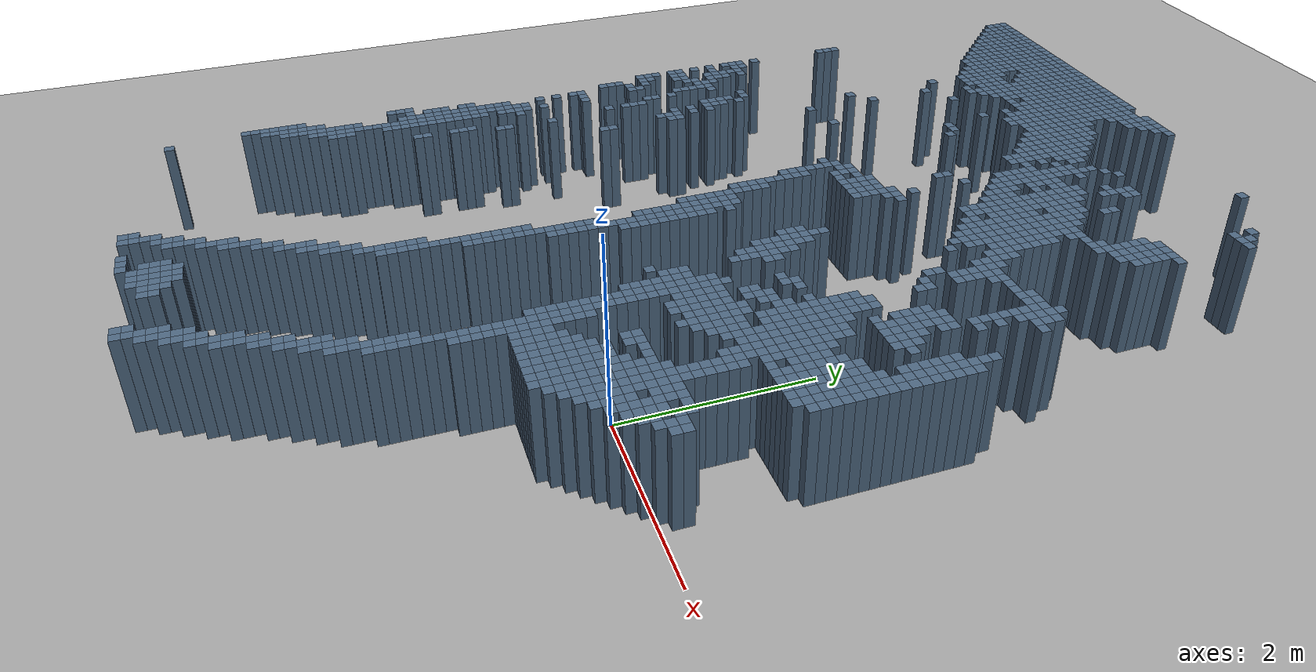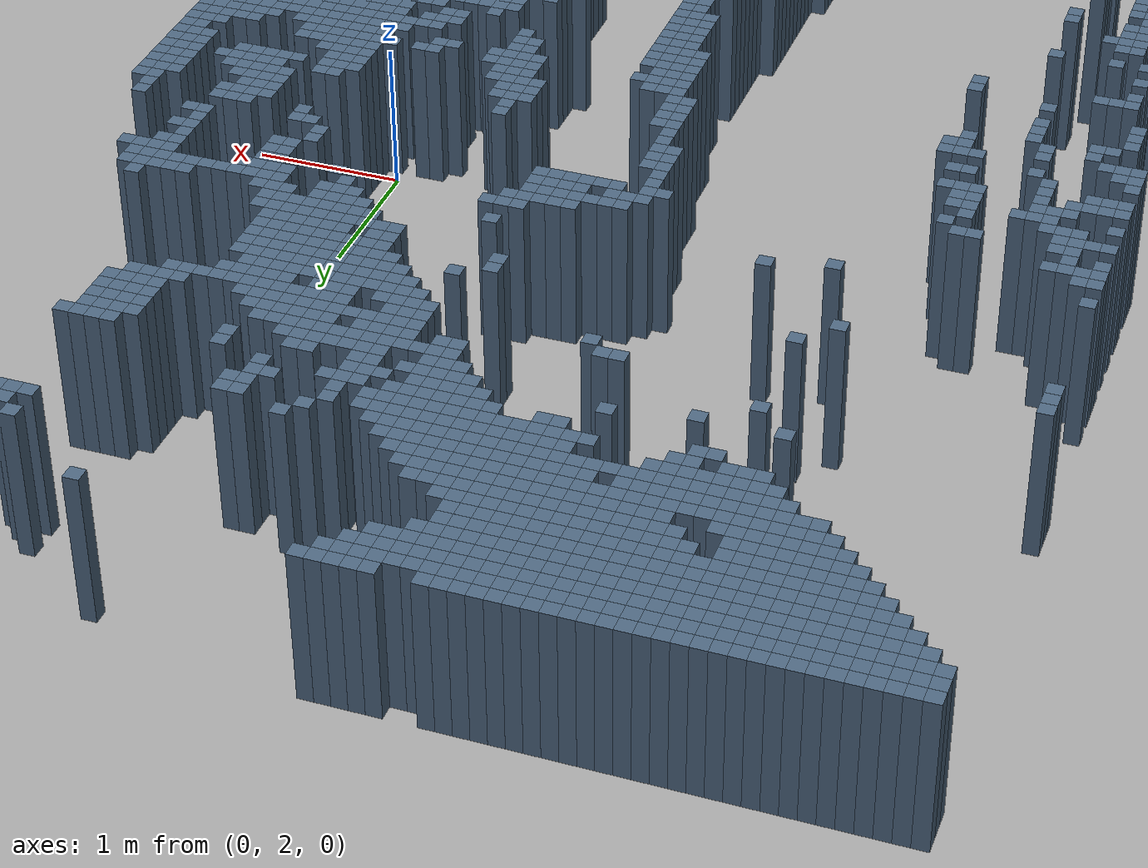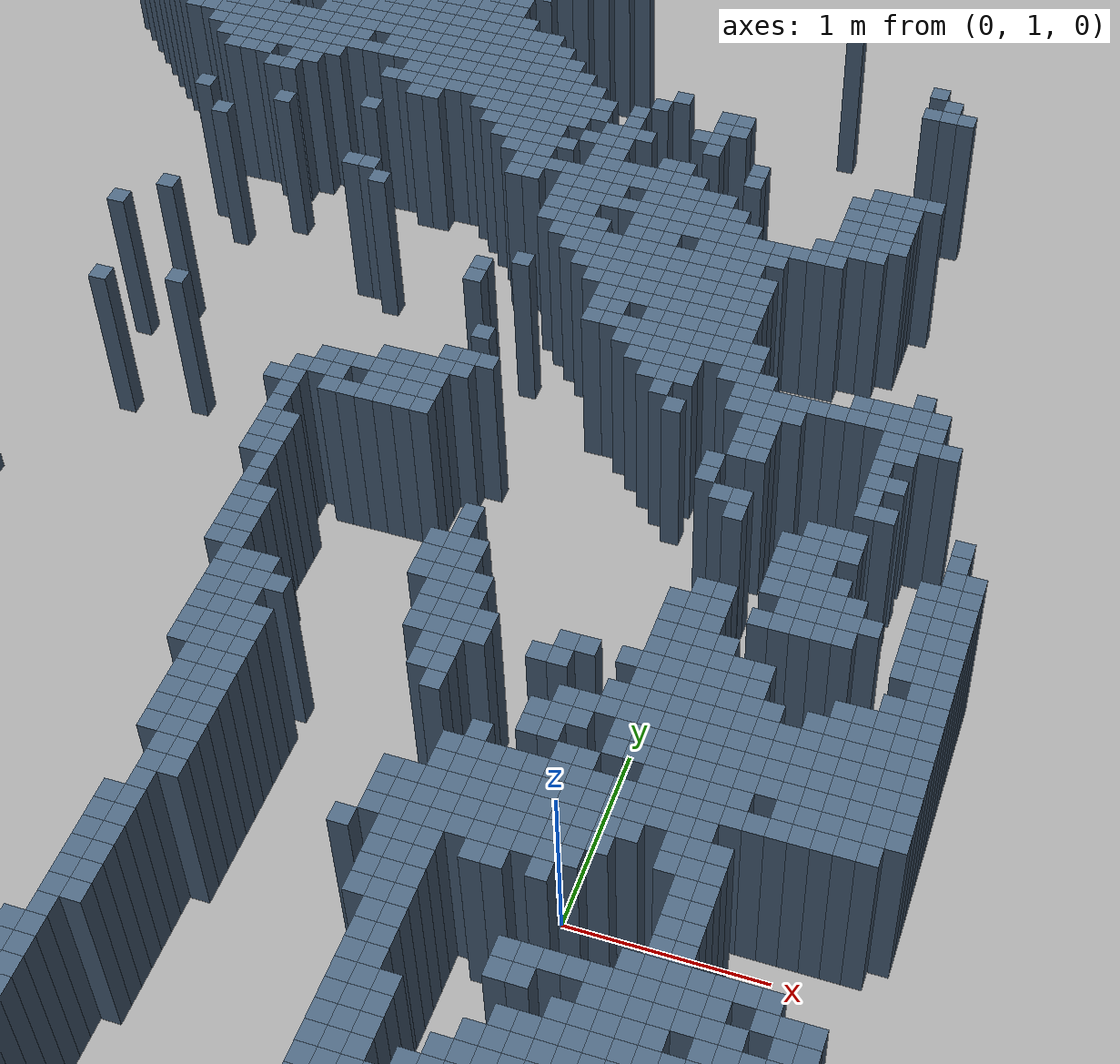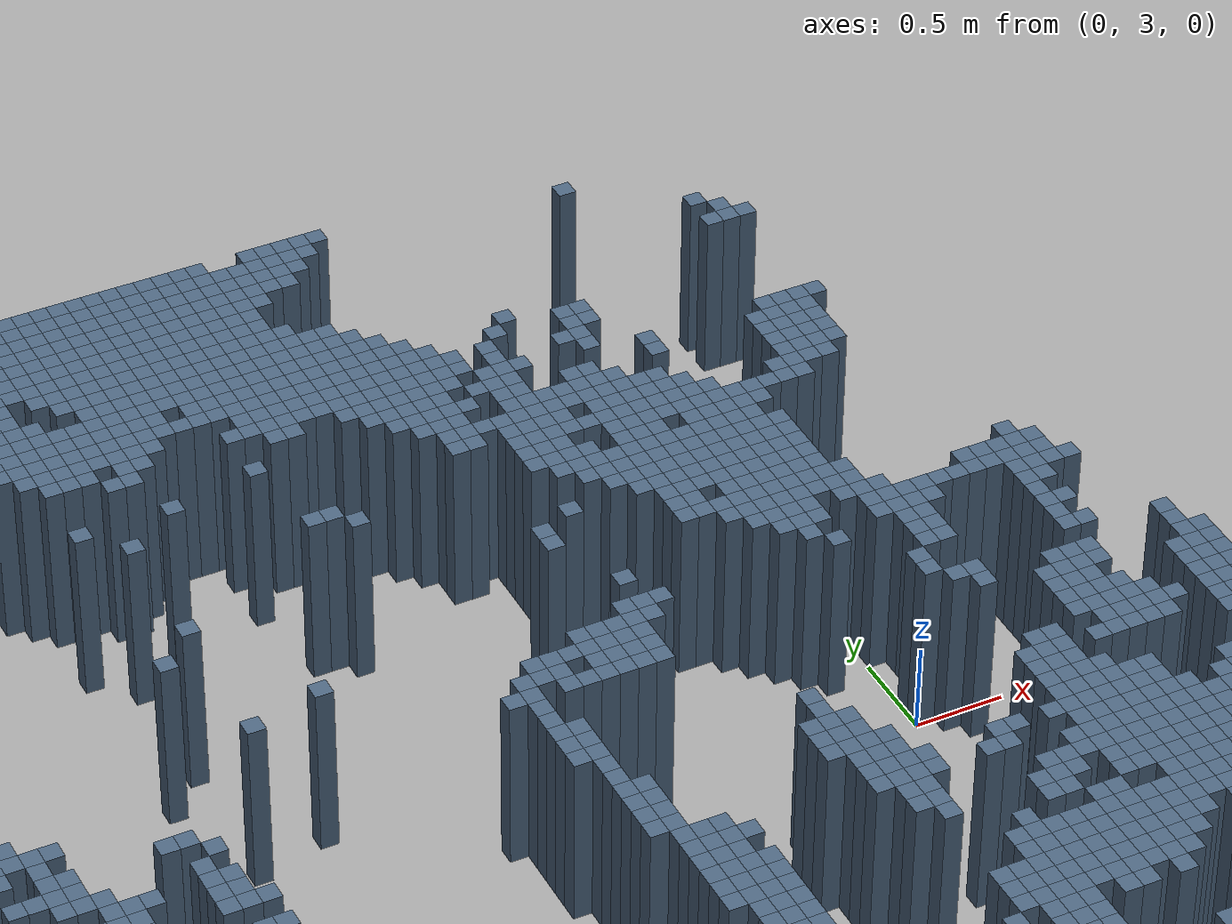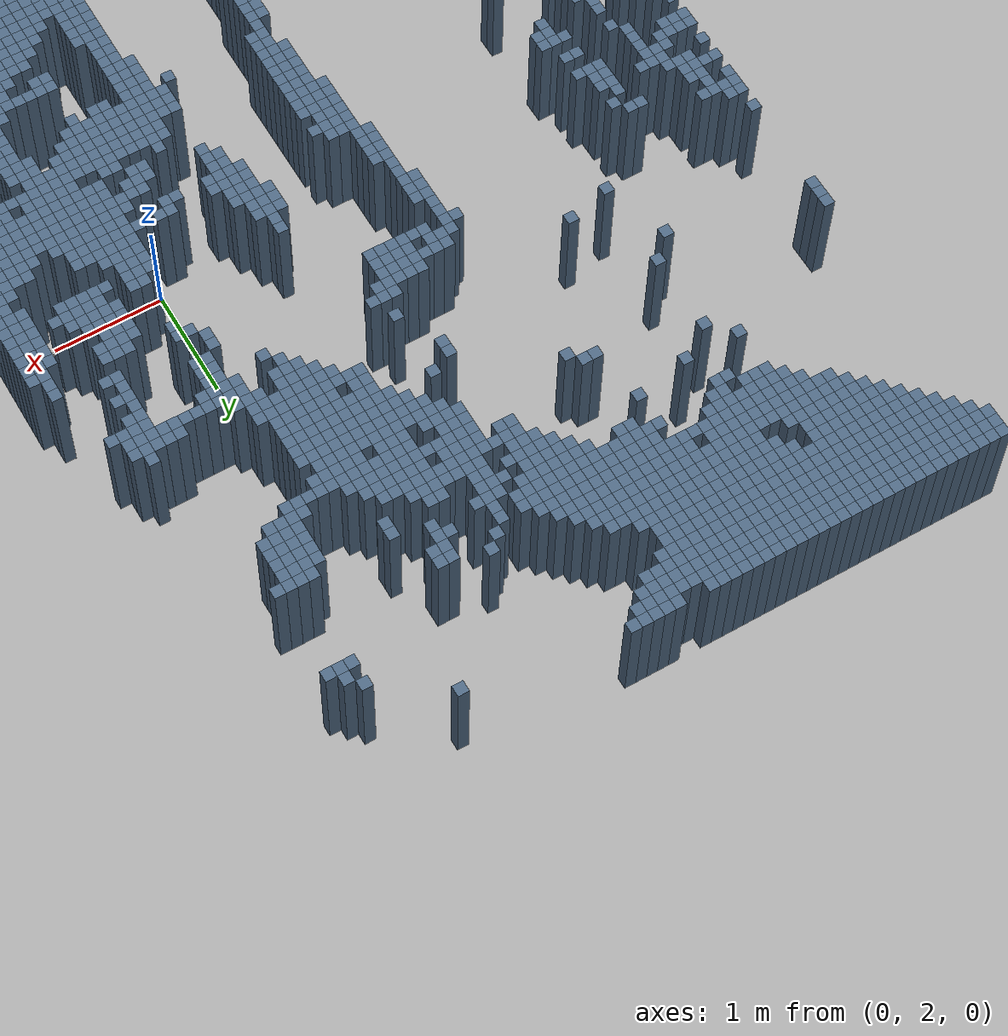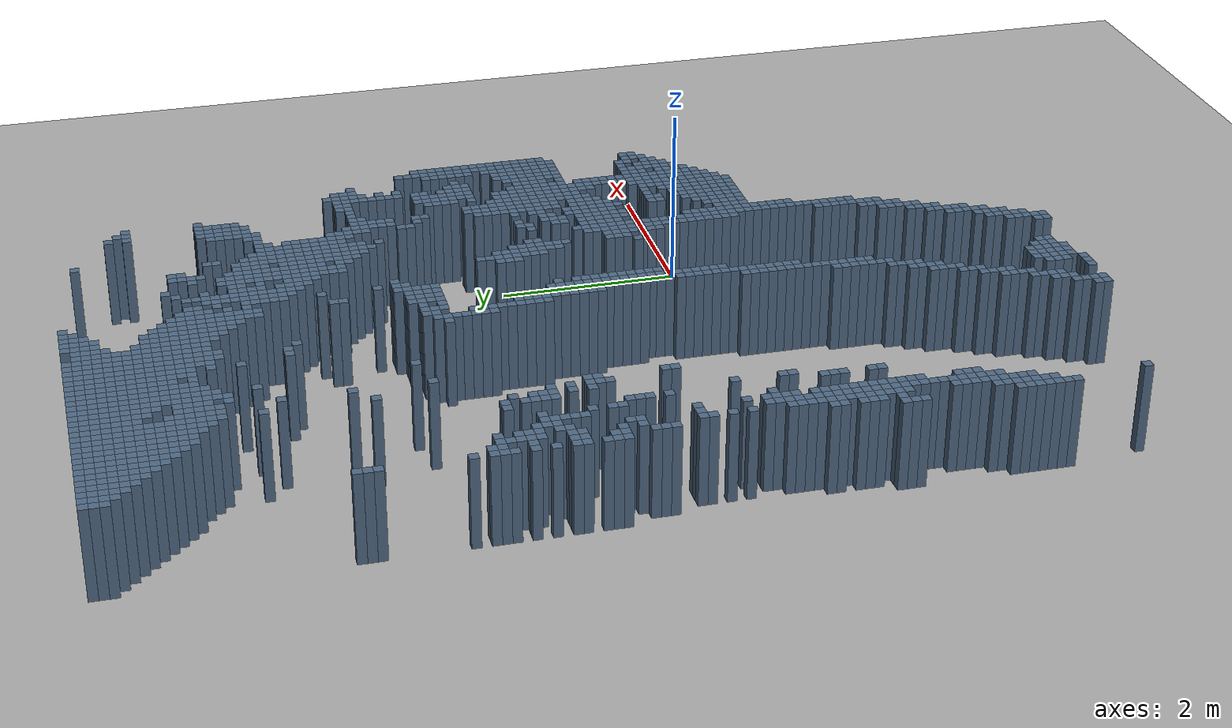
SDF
<?xml version='1.0' encoding='utf-8'?>
<sdf version="1.6">
  <world name="default">
    <gravity>0 0 -9.81</gravity>
    <physics name="default_physics" type="ode">
      <max_step_size>0.001</max_step_size>
      <real_time_update_rate>1000</real_time_update_rate>
    </physics>
    <scene>
      <ambient>0.6 0.6 0.6 1</ambient>
      <shadows>false</shadows>
    </scene>
    <light name="sun" type="directional">
      <pose>0 0 10 0 0 0</pose>
      <diffuse>0.8 0.8 0.8 1</diffuse>
      <direction>-0.5 0.1 -1</direction>
    </light>
    <model name="artificial_flat_ground">
      <static>true</static>
      <link name="ground">
        <collision name="floor_collision">
          <geometry>
            <plane>
              <normal>0 0 1</normal>
              <size>100 100</size>
            </plane>
          </geometry>
        </collision>
        <visual name="floor_visual">
          <geometry>
            <plane>
              <normal>0 0 1</normal>
              <size>100 100</size>
            </plane>
          </geometry>
          <material>
            <ambient>0.65 0.65 0.65 1</ambient>
            <diffuse>0.65 0.65 0.65 1</diffuse>
          </material>
        </visual>
      </link>
    </model>
    <model name="hilti_projected_cells">
      <static>true</static>
      <link name="obstacles">
        <collision name="cell_0_19_collision">
          <pose>-3.05000000 -3.95000000 0.50000000 0 0 0</pose>
          <geometry>
            <box>
              <size>0.10000000 0.10000000 1.00000000</size>
            </box>
          </geometry>
        </collision>
        <visual name="cell_0_19_visual">
          <pose>-3.05000000 -3.95000000 0.50000000 0 0 0</pose>
          <geometry>
            <box>
              <size>0.10000000 0.10000000 1.00000000</size>
            </box>
          </geometry>
          <material>
            <ambient>0.3 0.4 0.5 1</ambient>
            <diffuse>0.3 0.4 0.5 1</diffuse>
          </material>
        </visual>
        <collision name="cell_0_20_collision">
          <pose>-2.95000000 -3.95000000 0.50000000 0 0 0</pose>
          <geometry>
            <box>
              <size>0.10000000 0.10000000 1.00000000</size>
            </box>
          </geometry>
        </collision>
        <visual name="cell_0_20_visual">
          <pose>-2.95000000 -3.95000000 0.50000000 0 0 0</pose>
          <geometry>
            <box>
              <size>0.10000000 0.10000000 1.00000000</size>
            </box>
          </geometry>
          <material>
            <ambient>0.3 0.4 0.5 1</ambient>
            <diffuse>0.3 0.4 0.5 1</diffuse>
          </material>
        </visual>
        <collision name="cell_0_23_collision">
          <pose>-2.65000000 -3.95000000 0.50000000 0 0 0</pose>
          <geometry>
            <box>
              <size>0.10000000 0.10000000 1.00000000</size>
            </box>
          </geometry>
        </collision>
        <visual name="cell_0_23_visual">
          <pose>-2.65000000 -3.95000000 0.50000000 0 0 0</pose>
          <geometry>
            <box>
              <size>0.10000000 0.10000000 1.00000000</size>
            </box>
          </geometry>
          <material>
            <ambient>0.3 0.4 0.5 1</ambient>
            <diffuse>0.3 0.4 0.5 1</diffuse>
          </material>
        </visual>
        <collision name="cell_0_24_collision">
          <pose>-2.55000000 -3.95000000 0.50000000 0 0 0</pose>
          <geometry>
            <box>
              <size>0.10000000 0.10000000 1.00000000</size>
            </box>
          </geometry>
        </collision>
        <visual name="cell_0_24_visual">
          <pose>-2.55000000 -3.95000000 0.50000000 0 0 0</pose>
          <geometry>
            <box>
              <size>0.10000000 0.10000000 1.00000000</size>
            </box>
          </geometry>
          <material>
            <ambient>0.3 0.4 0.5 1</ambient>
            <diffuse>0.3 0.4 0.5 1</diffuse>
          </material>
        </visual>
        <collision name="cell_0_25_collision">
          <pose>-2.45000000 -3.95000000 0.50000000 0 0 0</pose>
          <geometry>
            <box>
              <size>0.10000000 0.10000000 1.00000000</size>
            </box>
          </geometry>
        </collision>
        <visual name="cell_0_25_visual">
          <pose>-2.45000000 -3.95000000 0.50000000 0 0 0</pose>
          <geometry>
            <box>
              <size>0.10000000 0.10000000 1.00000000</size>
            </box>
          </geometry>
          <material>
            <ambient>0.3 0.4 0.5 1</ambient>
            <diffuse>0.3 0.4 0.5 1</diffuse>
          </material>
        </visual>
        <collision name="cell_0_35_collision">
          <pose>-1.45000000 -3.95000000 0.50000000 0 0 0</pose>
          <geometry>
            <box>
              <size>0.10000000 0.10000000 1.00000000</size>
            </box>
          </geometry>
        </collision>
        <visual name="cell_0_35_visual">
          <pose>-1.45000000 -3.95000000 0.50000000 0 0 0</pose>
          <geometry>
            <box>
              <size>0.10000000 0.10000000 1.00000000</size>
            </box>
          </geometry>
          <material>
            <ambient>0.3 0.4 0.5 1</ambient>
            <diffuse>0.3 0.4 0.5 1</diffuse>
          </material>
        </visual>
        <collision name="cell_0_36_collision">
          <pose>-1.35000000 -3.95000000 0.50000000 0 0 0</pose>
          <geometry>
            <box>
              <size>0.10000000 0.10000000 1.00000000</size>
            </box>
          </geometry>
        </collision>
        <visual name="cell_0_36_visual">
          <pose>-1.35000000 -3.95000000 0.50000000 0 0 0</pose>
          <geometry>
            <box>
              <size>0.10000000 0.10000000 1.00000000</size>
            </box>
          </geometry>
          <material>
            <ambient>0.3 0.4 0.5 1</ambient>
            <diffuse>0.3 0.4 0.5 1</diffuse>
          </material>
        </visual>
        <collision name="cell_1_19_collision">
          <pose>-3.05000000 -3.85000000 0.50000000 0 0 0</pose>
          <geometry>
            <box>
              <size>0.10000000 0.10000000 1.00000000</size>
            </box>
          </geometry>
        </collision>
        <visual name="cell_1_19_visual">
          <pose>-3.05000000 -3.85000000 0.50000000 0 0 0</pose>
          <geometry>
            <box>
              <size>0.10000000 0.10000000 1.00000000</size>
            </box>
          </geometry>
          <material>
            <ambient>0.3 0.4 0.5 1</ambient>
            <diffuse>0.3 0.4 0.5 1</diffuse>
          </material>
        </visual>
        <collision name="cell_1_20_collision">
          <pose>-2.95000000 -3.85000000 0.50000000 0 0 0</pose>
          <geometry>
            <box>
              <size>0.10000000 0.10000000 1.00000000</size>
            </box>
          </geometry>
        </collision>
        <visual name="cell_1_20_visual">
          <pose>-2.95000000 -3.85000000 0.50000000 0 0 0</pose>
          <geometry>
            <box>
              <size>0.10000000 0.10000000 1.00000000</size>
            </box>
          </geometry>
          <material>
            <ambient>0.3 0.4 0.5 1</ambient>
            <diffuse>0.3 0.4 0.5 1</diffuse>
          </material>
        </visual>
        <collision name="cell_1_26_collision">
          <pose>-2.35000000 -3.85000000 0.50000000 0 0 0</pose>
          <geometry>
            <box>
              <size>0.10000000 0.10000000 1.00000000</size>
            </box>
          </geometry>
        </collision>
        <visual name="cell_1_26_visual">
          <pose>-2.35000000 -3.85000000 0.50000000 0 0 0</pose>
          <geometry>
            <box>
              <size>0.10000000 0.10000000 1.00000000</size>
            </box>
          </geometry>
          <material>
            <ambient>0.3 0.4 0.5 1</ambient>
            <diffuse>0.3 0.4 0.5 1</diffuse>
          </material>
        </visual>
        <collision name="cell_1_27_collision">
          <pose>-2.25000000 -3.85000000 0.50000000 0 0 0</pose>
          <geometry>
            <box>
              <size>0.10000000 0.10000000 1.00000000</size>
            </box>
          </geometry>
        </collision>
        <visual name="cell_1_27_visual">
          <pose>-2.25000000 -3.85000000 0.50000000 0 0 0</pose>
          <geometry>
            <box>
              <size>0.10000000 0.10000000 1.00000000</size>
            </box>
          </geometry>
          <material>
            <ambient>0.3 0.4 0.5 1</ambient>
            <diffuse>0.3 0.4 0.5 1</diffuse>
          </material>
        </visual>
        <collision name="cell_1_28_collision">
          <pose>-2.15000000 -3.85000000 0.50000000 0 0 0</pose>
          <geometry>
            <box>
              <size>0.10000000 0.10000000 1.00000000</size>
            </box>
          </geometry>
        </collision>
        <visual name="cell_1_28_visual">
          <pose>-2.15000000 -3.85000000 0.50000000 0 0 0</pose>
          <geometry>
            <box>
              <size>0.10000000 0.10000000 1.00000000</size>
            </box>
          </geometry>
          <material>
            <ambient>0.3 0.4 0.5 1</ambient>
            <diffuse>0.3 0.4 0.5 1</diffuse>
          </material>
        </visual>
        <collision name="cell_1_35_collision">
          <pose>-1.45000000 -3.85000000 0.50000000 0 0 0</pose>
          <geometry>
            <box>
              <size>0.10000000 0.10000000 1.00000000</size>
            </box>
          </geometry>
        </collision>
        <visual name="cell_1_35_visual">
          <pose>-1.45000000 -3.85000000 0.50000000 0 0 0</pose>
          <geometry>
            <box>
              <size>0.10000000 0.10000000 1.00000000</size>
            </box>
          </geometry>
          <material>
            <ambient>0.3 0.4 0.5 1</ambient>
            <diffuse>0.3 0.4 0.5 1</diffuse>
          </material>
        </visual>
        <collision name="cell_1_36_collision">
          <pose>-1.35000000 -3.85000000 0.50000000 0 0 0</pose>
          <geometry>
            <box>
              <size>0.10000000 0.10000000 1.00000000</size>
            </box>
          </geometry>
        </collision>
        <visual name="cell_1_36_visual">
          <pose>-1.35000000 -3.85000000 0.50000000 0 0 0</pose>
          <geometry>
            <box>
              <size>0.10000000 0.10000000 1.00000000</size>
            </box>
          </geometry>
          <material>
            <ambient>0.3 0.4 0.5 1</ambient>
            <diffuse>0.3 0.4 0.5 1</diffuse>
          </material>
        </visual>
        <collision name="cell_2_20_collision">
          <pose>-2.95000000 -3.75000000 0.50000000 0 0 0</pose>
          <geometry>
            <box>
              <size>0.10000000 0.10000000 1.00000000</size>
            </box>
          </geometry>
        </collision>
        <visual name="cell_2_20_visual">
          <pose>-2.95000000 -3.75000000 0.50000000 0 0 0</pose>
          <geometry>
            <box>
              <size>0.10000000 0.10000000 1.00000000</size>
            </box>
          </geometry>
          <material>
            <ambient>0.3 0.4 0.5 1</ambient>
            <diffuse>0.3 0.4 0.5 1</diffuse>
          </material>
        </visual>
        <collision name="cell_2_25_collision">
          <pose>-2.45000000 -3.75000000 0.50000000 0 0 0</pose>
          <geometry>
            <box>
              <size>0.10000000 0.10000000 1.00000000</size>
            </box>
          </geometry>
        </collision>
        <visual name="cell_2_25_visual">
          <pose>-2.45000000 -3.75000000 0.50000000 0 0 0</pose>
          <geometry>
            <box>
              <size>0.10000000 0.10000000 1.00000000</size>
            </box>
          </geometry>
          <material>
            <ambient>0.3 0.4 0.5 1</ambient>
            <diffuse>0.3 0.4 0.5 1</diffuse>
          </material>
        </visual>
        <collision name="cell_2_26_collision">
          <pose>-2.35000000 -3.75000000 0.50000000 0 0 0</pose>
          <geometry>
            <box>
              <size>0.10000000 0.10000000 1.00000000</size>
            </box>
          </geometry>
        </collision>
        <visual name="cell_2_26_visual">
          <pose>-2.35000000 -3.75000000 0.50000000 0 0 0</pose>
          <geometry>
            <box>
              <size>0.10000000 0.10000000 1.00000000</size>
            </box>
          </geometry>
          <material>
            <ambient>0.3 0.4 0.5 1</ambient>
            <diffuse>0.3 0.4 0.5 1</diffuse>
          </material>
        </visual>
        <collision name="cell_2_27_collision">
          <pose>-2.25000000 -3.75000000 0.50000000 0 0 0</pose>
          <geometry>
            <box>
              <size>0.10000000 0.10000000 1.00000000</size>
            </box>
          </geometry>
        </collision>
        <visual name="cell_2_27_visual">
          <pose>-2.25000000 -3.75000000 0.50000000 0 0 0</pose>
          <geometry>
            <box>
              <size>0.10000000 0.10000000 1.00000000</size>
            </box>
          </geometry>
          <material>
            <ambient>0.3 0.4 0.5 1</ambient>
            <diffuse>0.3 0.4 0.5 1</diffuse>
          </material>
        </visual>
        <collision name="cell_2_28_collision">
          <pose>-2.15000000 -3.75000000 0.50000000 0 0 0</pose>
          <geometry>
            <box>
              <size>0.10000000 0.10000000 1.00000000</size>
            </box>
          </geometry>
        </collision>
        <visual name="cell_2_28_visual">
          <pose>-2.15000000 -3.75000000 0.50000000 0 0 0</pose>
          <geometry>
            <box>
              <size>0.10000000 0.10000000 1.00000000</size>
            </box>
          </geometry>
          <material>
            <ambient>0.3 0.4 0.5 1</ambient>
            <diffuse>0.3 0.4 0.5 1</diffuse>
          </material>
        </visual>
        <collision name="cell_2_29_collision">
          <pose>-2.05000000 -3.75000000 0.50000000 0 0 0</pose>
          <geometry>
            <box>
              <size>0.10000000 0.10000000 1.00000000</size>
            </box>
          </geometry>
        </collision>
        <visual name="cell_2_29_visual">
          <pose>-2.05000000 -3.75000000 0.50000000 0 0 0</pose>
          <geometry>
            <box>
              <size>0.10000000 0.10000000 1.00000000</size>
            </box>
          </geometry>
          <material>
            <ambient>0.3 0.4 0.5 1</ambient>
            <diffuse>0.3 0.4 0.5 1</diffuse>
          </material>
        </visual>
        <collision name="cell_2_30_collision">
          <pose>-1.95000000 -3.75000000 0.50000000 0 0 0</pose>
          <geometry>
            <box>
              <size>0.10000000 0.10000000 1.00000000</size>
            </box>
          </geometry>
        </collision>
        <visual name="cell_2_30_visual">
          <pose>-1.95000000 -3.75000000 0.50000000 0 0 0</pose>
          <geometry>
            <box>
              <size>0.10000000 0.10000000 1.00000000</size>
            </box>
          </geometry>
          <material>
            <ambient>0.3 0.4 0.5 1</ambient>
            <diffuse>0.3 0.4 0.5 1</diffuse>
          </material>
        </visual>
        <collision name="cell_2_36_collision">
          <pose>-1.35000000 -3.75000000 0.50000000 0 0 0</pose>
          <geometry>
            <box>
              <size>0.10000000 0.10000000 1.00000000</size>
            </box>
          </geometry>
        </collision>
        <visual name="cell_2_36_visual">
          <pose>-1.35000000 -3.75000000 0.50000000 0 0 0</pose>
          <geometry>
            <box>
              <size>0.10000000 0.10000000 1.00000000</size>
            </box>
          </geometry>
          <material>
            <ambient>0.3 0.4 0.5 1</ambient>
            <diffuse>0.3 0.4 0.5 1</diffuse>
          </material>
        </visual>
        <collision name="cell_2_37_collision">
          <pose>-1.25000000 -3.75000000 0.50000000 0 0 0</pose>
          <geometry>
            <box>
              <size>0.10000000 0.10000000 1.00000000</size>
            </box>
          </geometry>
        </collision>
        <visual name="cell_2_37_visual">
          <pose>-1.25000000 -3.75000000 0.50000000 0 0 0</pose>
          <geometry>
            <box>
              <size>0.10000000 0.10000000 1.00000000</size>
            </box>
          </geometry>
          <material>
            <ambient>0.3 0.4 0.5 1</ambient>
            <diffuse>0.3 0.4 0.5 1</diffuse>
          </material>
        </visual>
        <collision name="cell_3_20_collision">
          <pose>-2.95000000 -3.65000000 0.50000000 0 0 0</pose>
          <geometry>
            <box>
              <size>0.10000000 0.10000000 1.00000000</size>
            </box>
          </geometry>
        </collision>
        <visual name="cell_3_20_visual">
          <pose>-2.95000000 -3.65000000 0.50000000 0 0 0</pose>
          <geometry>
            <box>
              <size>0.10000000 0.10000000 1.00000000</size>
            </box>
          </geometry>
          <material>
            <ambient>0.3 0.4 0.5 1</ambient>
            <diffuse>0.3 0.4 0.5 1</diffuse>
          </material>
        </visual>
        <collision name="cell_3_21_collision">
          <pose>-2.85000000 -3.65000000 0.50000000 0 0 0</pose>
          <geometry>
            <box>
              <size>0.10000000 0.10000000 1.00000000</size>
            </box>
          </geometry>
        </collision>
        <visual name="cell_3_21_visual">
          <pose>-2.85000000 -3.65000000 0.50000000 0 0 0</pose>
          <geometry>
            <box>
              <size>0.10000000 0.10000000 1.00000000</size>
            </box>
          </geometry>
          <material>
            <ambient>0.3 0.4 0.5 1</ambient>
            <diffuse>0.3 0.4 0.5 1</diffuse>
          </material>
        </visual>
        <collision name="cell_3_25_collision">
          <pose>-2.45000000 -3.65000000 0.50000000 0 0 0</pose>
          <geometry>
            <box>
              <size>0.10000000 0.10000000 1.00000000</size>
            </box>
          </geometry>
        </collision>
        <visual name="cell_3_25_visual">
          <pose>-2.45000000 -3.65000000 0.50000000 0 0 0</pose>
          <geometry>
            <box>
              <size>0.10000000 0.10000000 1.00000000</size>
            </box>
          </geometry>
          <material>
            <ambient>0.3 0.4 0.5 1</ambient>
            <diffuse>0.3 0.4 0.5 1</diffuse>
          </material>
        </visual>
        <collision name="cell_3_26_collision">
          <pose>-2.35000000 -3.65000000 0.50000000 0 0 0</pose>
          <geometry>
            <box>
              <size>0.10000000 0.10000000 1.00000000</size>
            </box>
          </geometry>
        </collision>
        <visual name="cell_3_26_visual">
          <pose>-2.35000000 -3.65000000 0.50000000 0 0 0</pose>
          <geometry>
            <box>
              <size>0.10000000 0.10000000 1.00000000</size>
            </box>
          </geometry>
          <material>
            <ambient>0.3 0.4 0.5 1</ambient>
            <diffuse>0.3 0.4 0.5 1</diffuse>
          </material>
        </visual>
        <collision name="cell_3_27_collision">
          <pose>-2.25000000 -3.65000000 0.50000000 0 0 0</pose>
          <geometry>
            <box>
              <size>0.10000000 0.10000000 1.00000000</size>
            </box>
          </geometry>
        </collision>
        <visual name="cell_3_27_visual">
          <pose>-2.25000000 -3.65000000 0.50000000 0 0 0</pose>
          <geometry>
            <box>
              <size>0.10000000 0.10000000 1.00000000</size>
            </box>
          </geometry>
          <material>
            <ambient>0.3 0.4 0.5 1</ambient>
            <diffuse>0.3 0.4 0.5 1</diffuse>
          </material>
        </visual>
        <collision name="cell_3_28_collision">
          <pose>-2.15000000 -3.65000000 0.50000000 0 0 0</pose>
          <geometry>
            <box>
              <size>0.10000000 0.10000000 1.00000000</size>
            </box>
          </geometry>
        </collision>
        <visual name="cell_3_28_visual">
          <pose>-2.15000000 -3.65000000 0.50000000 0 0 0</pose>
          <geometry>
            <box>
              <size>0.10000000 0.10000000 1.00000000</size>
            </box>
          </geometry>
          <material>
            <ambient>0.3 0.4 0.5 1</ambient>
            <diffuse>0.3 0.4 0.5 1</diffuse>
          </material>
        </visual>
        <collision name="cell_3_29_collision">
          <pose>-2.05000000 -3.65000000 0.50000000 0 0 0</pose>
          <geometry>
            <box>
              <size>0.10000000 0.10000000 1.00000000</size>
            </box>
          </geometry>
        </collision>
        <visual name="cell_3_29_visual">
          <pose>-2.05000000 -3.65000000 0.50000000 0 0 0</pose>
          <geometry>
            <box>
              <size>0.10000000 0.10000000 1.00000000</size>
            </box>
          </geometry>
          <material>
            <ambient>0.3 0.4 0.5 1</ambient>
            <diffuse>0.3 0.4 0.5 1</diffuse>
          </material>
        </visual>
        <collision name="cell_3_30_collision">
          <pose>-1.95000000 -3.65000000 0.50000000 0 0 0</pose>
          <geometry>
            <box>
              <size>0.10000000 0.10000000 1.00000000</size>
            </box>
          </geometry>
        </collision>
        <visual name="cell_3_30_visual">
          <pose>-1.95000000 -3.65000000 0.50000000 0 0 0</pose>
          <geometry>
            <box>
              <size>0.10000000 0.10000000 1.00000000</size>
            </box>
          </geometry>
          <material>
            <ambient>0.3 0.4 0.5 1</ambient>
            <diffuse>0.3 0.4 0.5 1</diffuse>
          </material>
        </visual>
        <collision name="cell_3_36_collision">
          <pose>-1.35000000 -3.65000000 0.50000000 0 0 0</pose>
          <geometry>
            <box>
              <size>0.10000000 0.10000000 1.00000000</size>
            </box>
          </geometry>
        </collision>
        <visual name="cell_3_36_visual">
          <pose>-1.35000000 -3.65000000 0.50000000 0 0 0</pose>
          <geometry>
            <box>
              <size>0.10000000 0.10000000 1.00000000</size>
            </box>
          </geometry>
          <material>
            <ambient>0.3 0.4 0.5 1</ambient>
            <diffuse>0.3 0.4 0.5 1</diffuse>
          </material>
        </visual>
        <collision name="cell_3_37_collision">
          <pose>-1.25000000 -3.65000000 0.50000000 0 0 0</pose>
          <geometry>
            <box>
              <size>0.10000000 0.10000000 1.00000000</size>
            </box>
          </geometry>
        </collision>
        <visual name="cell_3_37_visual">
          <pose>-1.25000000 -3.65000000 0.50000000 0 0 0</pose>
          <geometry>
            <box>
              <size>0.10000000 0.10000000 1.00000000</size>
            </box>
          </geometry>
          <material>
            <ambient>0.3 0.4 0.5 1</ambient>
            <diffuse>0.3 0.4 0.5 1</diffuse>
          </material>
        </visual>
        <collision name="cell_4_1_collision">
          <pose>-4.85000000 -3.55000000 0.50000000 0 0 0</pose>
          <geometry>
            <box>
              <size>0.10000000 0.10000000 1.00000000</size>
            </box>
          </geometry>
        </collision>
        <visual name="cell_4_1_visual">
          <pose>-4.85000000 -3.55000000 0.50000000 0 0 0</pose>
          <geometry>
            <box>
              <size>0.10000000 0.10000000 1.00000000</size>
            </box>
          </geometry>
          <material>
            <ambient>0.3 0.4 0.5 1</ambient>
            <diffuse>0.3 0.4 0.5 1</diffuse>
          </material>
        </visual>
        <collision name="cell_4_21_collision">
          <pose>-2.85000000 -3.55000000 0.50000000 0 0 0</pose>
          <geometry>
            <box>
              <size>0.10000000 0.10000000 1.00000000</size>
            </box>
          </geometry>
        </collision>
        <visual name="cell_4_21_visual">
          <pose>-2.85000000 -3.55000000 0.50000000 0 0 0</pose>
          <geometry>
            <box>
              <size>0.10000000 0.10000000 1.00000000</size>
            </box>
          </geometry>
          <material>
            <ambient>0.3 0.4 0.5 1</ambient>
            <diffuse>0.3 0.4 0.5 1</diffuse>
          </material>
        </visual>
        <collision name="cell_4_22_collision">
          <pose>-2.75000000 -3.55000000 0.50000000 0 0 0</pose>
          <geometry>
            <box>
              <size>0.10000000 0.10000000 1.00000000</size>
            </box>
          </geometry>
        </collision>
        <visual name="cell_4_22_visual">
          <pose>-2.75000000 -3.55000000 0.50000000 0 0 0</pose>
          <geometry>
            <box>
              <size>0.10000000 0.10000000 1.00000000</size>
            </box>
          </geometry>
          <material>
            <ambient>0.3 0.4 0.5 1</ambient>
            <diffuse>0.3 0.4 0.5 1</diffuse>
          </material>
        </visual>
        <collision name="cell_4_25_collision">
          <pose>-2.45000000 -3.55000000 0.50000000 0 0 0</pose>
          <geometry>
            <box>
              <size>0.10000000 0.10000000 1.00000000</size>
            </box>
          </geometry>
        </collision>
        <visual name="cell_4_25_visual">
          <pose>-2.45000000 -3.55000000 0.50000000 0 0 0</pose>
          <geometry>
            <box>
              <size>0.10000000 0.10000000 1.00000000</size>
            </box>
          </geometry>
          <material>
            <ambient>0.3 0.4 0.5 1</ambient>
            <diffuse>0.3 0.4 0.5 1</diffuse>
          </material>
        </visual>
        <collision name="cell_4_26_collision">
          <pose>-2.35000000 -3.55000000 0.50000000 0 0 0</pose>
          <geometry>
            <box>
              <size>0.10000000 0.10000000 1.00000000</size>
            </box>
          </geometry>
        </collision>
        <visual name="cell_4_26_visual">
          <pose>-2.35000000 -3.55000000 0.50000000 0 0 0</pose>
          <geometry>
            <box>
              <size>0.10000000 0.10000000 1.00000000</size>
            </box>
          </geometry>
          <material>
            <ambient>0.3 0.4 0.5 1</ambient>
            <diffuse>0.3 0.4 0.5 1</diffuse>
          </material>
        </visual>
        <collision name="cell_4_27_collision">
          <pose>-2.25000000 -3.55000000 0.50000000 0 0 0</pose>
          <geometry>
            <box>
              <size>0.10000000 0.10000000 1.00000000</size>
            </box>
          </geometry>
        </collision>
        <visual name="cell_4_27_visual">
          <pose>-2.25000000 -3.55000000 0.50000000 0 0 0</pose>
          <geometry>
            <box>
              <size>0.10000000 0.10000000 1.00000000</size>
            </box>
          </geometry>
          <material>
            <ambient>0.3 0.4 0.5 1</ambient>
            <diffuse>0.3 0.4 0.5 1</diffuse>
          </material>
        </visual>
        <collision name="cell_4_28_collision">
          <pose>-2.15000000 -3.55000000 0.50000000 0 0 0</pose>
          <geometry>
            <box>
              <size>0.10000000 0.10000000 1.00000000</size>
            </box>
          </geometry>
        </collision>
        <visual name="cell_4_28_visual">
          <pose>-2.15000000 -3.55000000 0.50000000 0 0 0</pose>
          <geometry>
            <box>
              <size>0.10000000 0.10000000 1.00000000</size>
            </box>
          </geometry>
          <material>
            <ambient>0.3 0.4 0.5 1</ambient>
            <diffuse>0.3 0.4 0.5 1</diffuse>
          </material>
        </visual>
        <collision name="cell_4_29_collision">
          <pose>-2.05000000 -3.55000000 0.50000000 0 0 0</pose>
          <geometry>
            <box>
              <size>0.10000000 0.10000000 1.00000000</size>
            </box>
          </geometry>
        </collision>
        <visual name="cell_4_29_visual">
          <pose>-2.05000000 -3.55000000 0.50000000 0 0 0</pose>
          <geometry>
            <box>
              <size>0.10000000 0.10000000 1.00000000</size>
            </box>
          </geometry>
          <material>
            <ambient>0.3 0.4 0.5 1</ambient>
            <diffuse>0.3 0.4 0.5 1</diffuse>
          </material>
        </visual>
        <collision name="cell_4_36_collision">
          <pose>-1.35000000 -3.55000000 0.50000000 0 0 0</pose>
          <geometry>
            <box>
              <size>0.10000000 0.10000000 1.00000000</size>
            </box>
          </geometry>
        </collision>
        <visual name="cell_4_36_visual">
          <pose>-1.35000000 -3.55000000 0.50000000 0 0 0</pose>
          <geometry>
            <box>
              <size>0.10000000 0.10000000 1.00000000</size>
            </box>
          </geometry>
          <material>
            <ambient>0.3 0.4 0.5 1</ambient>
            <diffuse>0.3 0.4 0.5 1</diffuse>
          </material>
        </visual>
        <collision name="cell_4_37_collision">
          <pose>-1.25000000 -3.55000000 0.50000000 0 0 0</pose>
          <geometry>
            <box>
              <size>0.10000000 0.10000000 1.00000000</size>
            </box>
          </geometry>
        </collision>
        <visual name="cell_4_37_visual">
          <pose>-1.25000000 -3.55000000 0.50000000 0 0 0</pose>
          <geometry>
            <box>
              <size>0.10000000 0.10000000 1.00000000</size>
            </box>
          </geometry>
          <material>
            <ambient>0.3 0.4 0.5 1</ambient>
            <diffuse>0.3 0.4 0.5 1</diffuse>
          </material>
        </visual>
        <collision name="cell_4_38_collision">
          <pose>-1.15000000 -3.55000000 0.50000000 0 0 0</pose>
          <geometry>
            <box>
              <size>0.10000000 0.10000000 1.00000000</size>
            </box>
          </geometry>
        </collision>
        <visual name="cell_4_38_visual">
          <pose>-1.15000000 -3.55000000 0.50000000 0 0 0</pose>
          <geometry>
            <box>
              <size>0.10000000 0.10000000 1.00000000</size>
            </box>
          </geometry>
          <material>
            <ambient>0.3 0.4 0.5 1</ambient>
            <diffuse>0.3 0.4 0.5 1</diffuse>
          </material>
        </visual>
        <collision name="cell_5_21_collision">
          <pose>-2.85000000 -3.45000000 0.50000000 0 0 0</pose>
          <geometry>
            <box>
              <size>0.10000000 0.10000000 1.00000000</size>
            </box>
          </geometry>
        </collision>
        <visual name="cell_5_21_visual">
          <pose>-2.85000000 -3.45000000 0.50000000 0 0 0</pose>
          <geometry>
            <box>
              <size>0.10000000 0.10000000 1.00000000</size>
            </box>
          </geometry>
          <material>
            <ambient>0.3 0.4 0.5 1</ambient>
            <diffuse>0.3 0.4 0.5 1</diffuse>
          </material>
        </visual>
        <collision name="cell_5_22_collision">
          <pose>-2.75000000 -3.45000000 0.50000000 0 0 0</pose>
          <geometry>
            <box>
              <size>0.10000000 0.10000000 1.00000000</size>
            </box>
          </geometry>
        </collision>
        <visual name="cell_5_22_visual">
          <pose>-2.75000000 -3.45000000 0.50000000 0 0 0</pose>
          <geometry>
            <box>
              <size>0.10000000 0.10000000 1.00000000</size>
            </box>
          </geometry>
          <material>
            <ambient>0.3 0.4 0.5 1</ambient>
            <diffuse>0.3 0.4 0.5 1</diffuse>
          </material>
        </visual>
        <collision name="cell_5_26_collision">
          <pose>-2.35000000 -3.45000000 0.50000000 0 0 0</pose>
          <geometry>
            <box>
              <size>0.10000000 0.10000000 1.00000000</size>
            </box>
          </geometry>
        </collision>
        <visual name="cell_5_26_visual">
          <pose>-2.35000000 -3.45000000 0.50000000 0 0 0</pose>
          <geometry>
            <box>
              <size>0.10000000 0.10000000 1.00000000</size>
            </box>
          </geometry>
          <material>
            <ambient>0.3 0.4 0.5 1</ambient>
            <diffuse>0.3 0.4 0.5 1</diffuse>
          </material>
        </visual>
        <collision name="cell_5_27_collision">
          <pose>-2.25000000 -3.45000000 0.50000000 0 0 0</pose>
          <geometry>
            <box>
              <size>0.10000000 0.10000000 1.00000000</size>
            </box>
          </geometry>
        </collision>
        <visual name="cell_5_27_visual">
          <pose>-2.25000000 -3.45000000 0.50000000 0 0 0</pose>
          <geometry>
            <box>
              <size>0.10000000 0.10000000 1.00000000</size>
            </box>
          </geometry>
          <material>
            <ambient>0.3 0.4 0.5 1</ambient>
            <diffuse>0.3 0.4 0.5 1</diffuse>
          </material>
        </visual>
        <collision name="cell_5_28_collision">
          <pose>-2.15000000 -3.45000000 0.50000000 0 0 0</pose>
          <geometry>
            <box>
              <size>0.10000000 0.10000000 1.00000000</size>
            </box>
          </geometry>
        </collision>
        <visual name="cell_5_28_visual">
          <pose>-2.15000000 -3.45000000 0.50000000 0 0 0</pose>
          <geometry>
            <box>
              <size>0.10000000 0.10000000 1.00000000</size>
            </box>
          </geometry>
          <material>
            <ambient>0.3 0.4 0.5 1</ambient>
            <diffuse>0.3 0.4 0.5 1</diffuse>
          </material>
        </visual>
        <collision name="cell_5_37_collision">
          <pose>-1.25000000 -3.45000000 0.50000000 0 0 0</pose>
          <geometry>
            <box>
              <size>0.10000000 0.10000000 1.00000000</size>
            </box>
          </geometry>
        </collision>
        <visual name="cell_5_37_visual">
          <pose>-1.25000000 -3.45000000 0.50000000 0 0 0</pose>
          <geometry>
            <box>
              <size>0.10000000 0.10000000 1.00000000</size>
            </box>
          </geometry>
          <material>
            <ambient>0.3 0.4 0.5 1</ambient>
            <diffuse>0.3 0.4 0.5 1</diffuse>
          </material>
        </visual>
        <collision name="cell_5_38_collision">
          <pose>-1.15000000 -3.45000000 0.50000000 0 0 0</pose>
          <geometry>
            <box>
              <size>0.10000000 0.10000000 1.00000000</size>
            </box>
          </geometry>
        </collision>
        <visual name="cell_5_38_visual">
          <pose>-1.15000000 -3.45000000 0.50000000 0 0 0</pose>
          <geometry>
            <box>
              <size>0.10000000 0.10000000 1.00000000</size>
            </box>
          </geometry>
          <material>
            <ambient>0.3 0.4 0.5 1</ambient>
            <diffuse>0.3 0.4 0.5 1</diffuse>
          </material>
        </visual>
        <collision name="cell_6_22_collision">
          <pose>-2.75000000 -3.35000000 0.50000000 0 0 0</pose>
          <geometry>
            <box>
              <size>0.10000000 0.10000000 1.00000000</size>
            </box>
          </geometry>
        </collision>
        <visual name="cell_6_22_visual">
          <pose>-2.75000000 -3.35000000 0.50000000 0 0 0</pose>
          <geometry>
            <box>
              <size>0.10000000 0.10000000 1.00000000</size>
            </box>
          </geometry>
          <material>
            <ambient>0.3 0.4 0.5 1</ambient>
            <diffuse>0.3 0.4 0.5 1</diffuse>
          </material>
        </visual>
        <collision name="cell_6_37_collision">
          <pose>-1.25000000 -3.35000000 0.50000000 0 0 0</pose>
          <geometry>
            <box>
              <size>0.10000000 0.10000000 1.00000000</size>
            </box>
          </geometry>
        </collision>
        <visual name="cell_6_37_visual">
          <pose>-1.25000000 -3.35000000 0.50000000 0 0 0</pose>
          <geometry>
            <box>
              <size>0.10000000 0.10000000 1.00000000</size>
            </box>
          </geometry>
          <material>
            <ambient>0.3 0.4 0.5 1</ambient>
            <diffuse>0.3 0.4 0.5 1</diffuse>
          </material>
        </visual>
        <collision name="cell_6_38_collision">
          <pose>-1.15000000 -3.35000000 0.50000000 0 0 0</pose>
          <geometry>
            <box>
              <size>0.10000000 0.10000000 1.00000000</size>
            </box>
          </geometry>
        </collision>
        <visual name="cell_6_38_visual">
          <pose>-1.15000000 -3.35000000 0.50000000 0 0 0</pose>
          <geometry>
            <box>
              <size>0.10000000 0.10000000 1.00000000</size>
            </box>
          </geometry>
          <material>
            <ambient>0.3 0.4 0.5 1</ambient>
            <diffuse>0.3 0.4 0.5 1</diffuse>
          </material>
        </visual>
        <collision name="cell_6_39_collision">
          <pose>-1.05000000 -3.35000000 0.50000000 0 0 0</pose>
          <geometry>
            <box>
              <size>0.10000000 0.10000000 1.00000000</size>
            </box>
          </geometry>
        </collision>
        <visual name="cell_6_39_visual">
          <pose>-1.05000000 -3.35000000 0.50000000 0 0 0</pose>
          <geometry>
            <box>
              <size>0.10000000 0.10000000 1.00000000</size>
            </box>
          </geometry>
          <material>
            <ambient>0.3 0.4 0.5 1</ambient>
            <diffuse>0.3 0.4 0.5 1</diffuse>
          </material>
        </visual>
        <collision name="cell_7_22_collision">
          <pose>-2.75000000 -3.25000000 0.50000000 0 0 0</pose>
          <geometry>
            <box>
              <size>0.10000000 0.10000000 1.00000000</size>
            </box>
          </geometry>
        </collision>
        <visual name="cell_7_22_visual">
          <pose>-2.75000000 -3.25000000 0.50000000 0 0 0</pose>
          <geometry>
            <box>
              <size>0.10000000 0.10000000 1.00000000</size>
            </box>
          </geometry>
          <material>
            <ambient>0.3 0.4 0.5 1</ambient>
            <diffuse>0.3 0.4 0.5 1</diffuse>
          </material>
        </visual>
        <collision name="cell_7_23_collision">
          <pose>-2.65000000 -3.25000000 0.50000000 0 0 0</pose>
          <geometry>
            <box>
              <size>0.10000000 0.10000000 1.00000000</size>
            </box>
          </geometry>
        </collision>
        <visual name="cell_7_23_visual">
          <pose>-2.65000000 -3.25000000 0.50000000 0 0 0</pose>
          <geometry>
            <box>
              <size>0.10000000 0.10000000 1.00000000</size>
            </box>
          </geometry>
          <material>
            <ambient>0.3 0.4 0.5 1</ambient>
            <diffuse>0.3 0.4 0.5 1</diffuse>
          </material>
        </visual>
        <collision name="cell_7_38_collision">
          <pose>-1.15000000 -3.25000000 0.50000000 0 0 0</pose>
          <geometry>
            <box>
              <size>0.10000000 0.10000000 1.00000000</size>
            </box>
          </geometry>
        </collision>
        <visual name="cell_7_38_visual">
          <pose>-1.15000000 -3.25000000 0.50000000 0 0 0</pose>
          <geometry>
            <box>
              <size>0.10000000 0.10000000 1.00000000</size>
            </box>
          </geometry>
          <material>
            <ambient>0.3 0.4 0.5 1</ambient>
            <diffuse>0.3 0.4 0.5 1</diffuse>
          </material>
        </visual>
        <collision name="cell_7_39_collision">
          <pose>-1.05000000 -3.25000000 0.50000000 0 0 0</pose>
          <geometry>
            <box>
              <size>0.10000000 0.10000000 1.00000000</size>
            </box>
          </geometry>
        </collision>
        <visual name="cell_7_39_visual">
          <pose>-1.05000000 -3.25000000 0.50000000 0 0 0</pose>
          <geometry>
            <box>
              <size>0.10000000 0.10000000 1.00000000</size>
            </box>
          </geometry>
          <material>
            <ambient>0.3 0.4 0.5 1</ambient>
            <diffuse>0.3 0.4 0.5 1</diffuse>
          </material>
        </visual>
        <collision name="cell_8_23_collision">
          <pose>-2.65000000 -3.15000000 0.50000000 0 0 0</pose>
          <geometry>
            <box>
              <size>0.10000000 0.10000000 1.00000000</size>
            </box>
          </geometry>
        </collision>
        <visual name="cell_8_23_visual">
          <pose>-2.65000000 -3.15000000 0.50000000 0 0 0</pose>
          <geometry>
            <box>
              <size>0.10000000 0.10000000 1.00000000</size>
            </box>
          </geometry>
          <material>
            <ambient>0.3 0.4 0.5 1</ambient>
            <diffuse>0.3 0.4 0.5 1</diffuse>
          </material>
        </visual>
        <collision name="cell_8_39_collision">
          <pose>-1.05000000 -3.15000000 0.50000000 0 0 0</pose>
          <geometry>
            <box>
              <size>0.10000000 0.10000000 1.00000000</size>
            </box>
          </geometry>
        </collision>
        <visual name="cell_8_39_visual">
          <pose>-1.05000000 -3.15000000 0.50000000 0 0 0</pose>
          <geometry>
            <box>
              <size>0.10000000 0.10000000 1.00000000</size>
            </box>
          </geometry>
          <material>
            <ambient>0.3 0.4 0.5 1</ambient>
            <diffuse>0.3 0.4 0.5 1</diffuse>
          </material>
        </visual>
        <collision name="cell_8_40_collision">
          <pose>-0.95000000 -3.15000000 0.50000000 0 0 0</pose>
          <geometry>
            <box>
              <size>0.10000000 0.10000000 1.00000000</size>
            </box>
          </geometry>
        </collision>
        <visual name="cell_8_40_visual">
          <pose>-0.95000000 -3.15000000 0.50000000 0 0 0</pose>
          <geometry>
            <box>
              <size>0.10000000 0.10000000 1.00000000</size>
            </box>
          </geometry>
          <material>
            <ambient>0.3 0.4 0.5 1</ambient>
            <diffuse>0.3 0.4 0.5 1</diffuse>
          </material>
        </visual>
        <collision name="cell_9_23_collision">
          <pose>-2.65000000 -3.05000000 0.50000000 0 0 0</pose>
          <geometry>
            <box>
              <size>0.10000000 0.10000000 1.00000000</size>
            </box>
          </geometry>
        </collision>
        <visual name="cell_9_23_visual">
          <pose>-2.65000000 -3.05000000 0.50000000 0 0 0</pose>
          <geometry>
            <box>
              <size>0.10000000 0.10000000 1.00000000</size>
            </box>
          </geometry>
          <material>
            <ambient>0.3 0.4 0.5 1</ambient>
            <diffuse>0.3 0.4 0.5 1</diffuse>
          </material>
        </visual>
        <collision name="cell_9_24_collision">
          <pose>-2.55000000 -3.05000000 0.50000000 0 0 0</pose>
          <geometry>
            <box>
              <size>0.10000000 0.10000000 1.00000000</size>
            </box>
          </geometry>
        </collision>
        <visual name="cell_9_24_visual">
          <pose>-2.55000000 -3.05000000 0.50000000 0 0 0</pose>
          <geometry>
            <box>
              <size>0.10000000 0.10000000 1.00000000</size>
            </box>
          </geometry>
          <material>
            <ambient>0.3 0.4 0.5 1</ambient>
            <diffuse>0.3 0.4 0.5 1</diffuse>
          </material>
        </visual>
        <collision name="cell_9_39_collision">
          <pose>-1.05000000 -3.05000000 0.50000000 0 0 0</pose>
          <geometry>
            <box>
              <size>0.10000000 0.10000000 1.00000000</size>
            </box>
          </geometry>
        </collision>
        <visual name="cell_9_39_visual">
          <pose>-1.05000000 -3.05000000 0.50000000 0 0 0</pose>
          <geometry>
            <box>
              <size>0.10000000 0.10000000 1.00000000</size>
            </box>
          </geometry>
          <material>
            <ambient>0.3 0.4 0.5 1</ambient>
            <diffuse>0.3 0.4 0.5 1</diffuse>
          </material>
        </visual>
        <collision name="cell_9_40_collision">
          <pose>-0.95000000 -3.05000000 0.50000000 0 0 0</pose>
          <geometry>
            <box>
              <size>0.10000000 0.10000000 1.00000000</size>
            </box>
          </geometry>
        </collision>
        <visual name="cell_9_40_visual">
          <pose>-0.95000000 -3.05000000 0.50000000 0 0 0</pose>
          <geometry>
            <box>
              <size>0.10000000 0.10000000 1.00000000</size>
            </box>
          </geometry>
          <material>
            <ambient>0.3 0.4 0.5 1</ambient>
            <diffuse>0.3 0.4 0.5 1</diffuse>
          </material>
        </visual>
        <collision name="cell_10_23_collision">
          <pose>-2.65000000 -2.95000000 0.50000000 0 0 0</pose>
          <geometry>
            <box>
              <size>0.10000000 0.10000000 1.00000000</size>
            </box>
          </geometry>
        </collision>
        <visual name="cell_10_23_visual">
          <pose>-2.65000000 -2.95000000 0.50000000 0 0 0</pose>
          <geometry>
            <box>
              <size>0.10000000 0.10000000 1.00000000</size>
            </box>
          </geometry>
          <material>
            <ambient>0.3 0.4 0.5 1</ambient>
            <diffuse>0.3 0.4 0.5 1</diffuse>
          </material>
        </visual>
        <collision name="cell_10_24_collision">
          <pose>-2.55000000 -2.95000000 0.50000000 0 0 0</pose>
          <geometry>
            <box>
              <size>0.10000000 0.10000000 1.00000000</size>
            </box>
          </geometry>
        </collision>
        <visual name="cell_10_24_visual">
          <pose>-2.55000000 -2.95000000 0.50000000 0 0 0</pose>
          <geometry>
            <box>
              <size>0.10000000 0.10000000 1.00000000</size>
            </box>
          </geometry>
          <material>
            <ambient>0.3 0.4 0.5 1</ambient>
            <diffuse>0.3 0.4 0.5 1</diffuse>
          </material>
        </visual>
        <collision name="cell_10_39_collision">
          <pose>-1.05000000 -2.95000000 0.50000000 0 0 0</pose>
          <geometry>
            <box>
              <size>0.10000000 0.10000000 1.00000000</size>
            </box>
          </geometry>
        </collision>
        <visual name="cell_10_39_visual">
          <pose>-1.05000000 -2.95000000 0.50000000 0 0 0</pose>
          <geometry>
            <box>
              <size>0.10000000 0.10000000 1.00000000</size>
            </box>
          </geometry>
          <material>
            <ambient>0.3 0.4 0.5 1</ambient>
            <diffuse>0.3 0.4 0.5 1</diffuse>
          </material>
        </visual>
        <collision name="cell_10_40_collision">
          <pose>-0.95000000 -2.95000000 0.50000000 0 0 0</pose>
          <geometry>
            <box>
              <size>0.10000000 0.10000000 1.00000000</size>
            </box>
          </geometry>
        </collision>
        <visual name="cell_10_40_visual">
          <pose>-0.95000000 -2.95000000 0.50000000 0 0 0</pose>
          <geometry>
            <box>
              <size>0.10000000 0.10000000 1.00000000</size>
            </box>
          </geometry>
          <material>
            <ambient>0.3 0.4 0.5 1</ambient>
            <diffuse>0.3 0.4 0.5 1</diffuse>
          </material>
        </visual>
        <collision name="cell_11_24_collision">
          <pose>-2.55000000 -2.85000000 0.50000000 0 0 0</pose>
          <geometry>
            <box>
              <size>0.10000000 0.10000000 1.00000000</size>
            </box>
          </geometry>
        </collision>
        <visual name="cell_11_24_visual">
          <pose>-2.55000000 -2.85000000 0.50000000 0 0 0</pose>
          <geometry>
            <box>
              <size>0.10000000 0.10000000 1.00000000</size>
            </box>
          </geometry>
          <material>
            <ambient>0.3 0.4 0.5 1</ambient>
            <diffuse>0.3 0.4 0.5 1</diffuse>
          </material>
        </visual>
        <collision name="cell_11_40_collision">
          <pose>-0.95000000 -2.85000000 0.50000000 0 0 0</pose>
          <geometry>
            <box>
              <size>0.10000000 0.10000000 1.00000000</size>
            </box>
          </geometry>
        </collision>
        <visual name="cell_11_40_visual">
          <pose>-0.95000000 -2.85000000 0.50000000 0 0 0</pose>
          <geometry>
            <box>
              <size>0.10000000 0.10000000 1.00000000</size>
            </box>
          </geometry>
          <material>
            <ambient>0.3 0.4 0.5 1</ambient>
            <diffuse>0.3 0.4 0.5 1</diffuse>
          </material>
        </visual>
        <collision name="cell_11_41_collision">
          <pose>-0.85000000 -2.85000000 0.50000000 0 0 0</pose>
          <geometry>
            <box>
              <size>0.10000000 0.10000000 1.00000000</size>
            </box>
          </geometry>
        </collision>
        <visual name="cell_11_41_visual">
          <pose>-0.85000000 -2.85000000 0.50000000 0 0 0</pose>
          <geometry>
            <box>
              <size>0.10000000 0.10000000 1.00000000</size>
            </box>
          </geometry>
          <material>
            <ambient>0.3 0.4 0.5 1</ambient>
            <diffuse>0.3 0.4 0.5 1</diffuse>
          </material>
        </visual>
        <collision name="cell_12_0_collision">
          <pose>-4.95000000 -2.75000000 0.50000000 0 0 0</pose>
          <geometry>
            <box>
              <size>0.10000000 0.10000000 1.00000000</size>
            </box>
          </geometry>
        </collision>
        <visual name="cell_12_0_visual">
          <pose>-4.95000000 -2.75000000 0.50000000 0 0 0</pose>
          <geometry>
            <box>
              <size>0.10000000 0.10000000 1.00000000</size>
            </box>
          </geometry>
          <material>
            <ambient>0.3 0.4 0.5 1</ambient>
            <diffuse>0.3 0.4 0.5 1</diffuse>
          </material>
        </visual>
        <collision name="cell_12_24_collision">
          <pose>-2.55000000 -2.75000000 0.50000000 0 0 0</pose>
          <geometry>
            <box>
              <size>0.10000000 0.10000000 1.00000000</size>
            </box>
          </geometry>
        </collision>
        <visual name="cell_12_24_visual">
          <pose>-2.55000000 -2.75000000 0.50000000 0 0 0</pose>
          <geometry>
            <box>
              <size>0.10000000 0.10000000 1.00000000</size>
            </box>
          </geometry>
          <material>
            <ambient>0.3 0.4 0.5 1</ambient>
            <diffuse>0.3 0.4 0.5 1</diffuse>
          </material>
        </visual>
        <collision name="cell_12_25_collision">
          <pose>-2.45000000 -2.75000000 0.50000000 0 0 0</pose>
          <geometry>
            <box>
              <size>0.10000000 0.10000000 1.00000000</size>
            </box>
          </geometry>
        </collision>
        <visual name="cell_12_25_visual">
          <pose>-2.45000000 -2.75000000 0.50000000 0 0 0</pose>
          <geometry>
            <box>
              <size>0.10000000 0.10000000 1.00000000</size>
            </box>
          </geometry>
          <material>
            <ambient>0.3 0.4 0.5 1</ambient>
            <diffuse>0.3 0.4 0.5 1</diffuse>
          </material>
        </visual>
        <collision name="cell_12_40_collision">
          <pose>-0.95000000 -2.75000000 0.50000000 0 0 0</pose>
          <geometry>
            <box>
              <size>0.10000000 0.10000000 1.00000000</size>
            </box>
          </geometry>
        </collision>
        <visual name="cell_12_40_visual">
          <pose>-0.95000000 -2.75000000 0.50000000 0 0 0</pose>
          <geometry>
            <box>
              <size>0.10000000 0.10000000 1.00000000</size>
            </box>
          </geometry>
          <material>
            <ambient>0.3 0.4 0.5 1</ambient>
            <diffuse>0.3 0.4 0.5 1</diffuse>
          </material>
        </visual>
        <collision name="cell_12_41_collision">
          <pose>-0.85000000 -2.75000000 0.50000000 0 0 0</pose>
          <geometry>
            <box>
              <size>0.10000000 0.10000000 1.00000000</size>
            </box>
          </geometry>
        </collision>
        <visual name="cell_12_41_visual">
          <pose>-0.85000000 -2.75000000 0.50000000 0 0 0</pose>
          <geometry>
            <box>
              <size>0.10000000 0.10000000 1.00000000</size>
            </box>
          </geometry>
          <material>
            <ambient>0.3 0.4 0.5 1</ambient>
            <diffuse>0.3 0.4 0.5 1</diffuse>
          </material>
        </visual>
        <collision name="cell_13_0_collision">
          <pose>-4.95000000 -2.65000000 0.50000000 0 0 0</pose>
          <geometry>
            <box>
              <size>0.10000000 0.10000000 1.00000000</size>
            </box>
          </geometry>
        </collision>
        <visual name="cell_13_0_visual">
          <pose>-4.95000000 -2.65000000 0.50000000 0 0 0</pose>
          <geometry>
            <box>
              <size>0.10000000 0.10000000 1.00000000</size>
            </box>
          </geometry>
          <material>
            <ambient>0.3 0.4 0.5 1</ambient>
            <diffuse>0.3 0.4 0.5 1</diffuse>
          </material>
        </visual>
        <collision name="cell_13_25_collision">
          <pose>-2.45000000 -2.65000000 0.50000000 0 0 0</pose>
          <geometry>
            <box>
              <size>0.10000000 0.10000000 1.00000000</size>
            </box>
          </geometry>
        </collision>
        <visual name="cell_13_25_visual">
          <pose>-2.45000000 -2.65000000 0.50000000 0 0 0</pose>
          <geometry>
            <box>
              <size>0.10000000 0.10000000 1.00000000</size>
            </box>
          </geometry>
          <material>
            <ambient>0.3 0.4 0.5 1</ambient>
            <diffuse>0.3 0.4 0.5 1</diffuse>
          </material>
        </visual>
        <collision name="cell_13_41_collision">
          <pose>-0.85000000 -2.65000000 0.50000000 0 0 0</pose>
          <geometry>
            <box>
              <size>0.10000000 0.10000000 1.00000000</size>
            </box>
          </geometry>
        </collision>
        <visual name="cell_13_41_visual">
          <pose>-0.85000000 -2.65000000 0.50000000 0 0 0</pose>
          <geometry>
            <box>
              <size>0.10000000 0.10000000 1.00000000</size>
            </box>
          </geometry>
          <material>
            <ambient>0.3 0.4 0.5 1</ambient>
            <diffuse>0.3 0.4 0.5 1</diffuse>
          </material>
        </visual>
        <collision name="cell_13_42_collision">
          <pose>-0.75000000 -2.65000000 0.50000000 0 0 0</pose>
          <geometry>
            <box>
              <size>0.10000000 0.10000000 1.00000000</size>
            </box>
          </geometry>
        </collision>
        <visual name="cell_13_42_visual">
          <pose>-0.75000000 -2.65000000 0.50000000 0 0 0</pose>
          <geometry>
            <box>
              <size>0.10000000 0.10000000 1.00000000</size>
            </box>
          </geometry>
          <material>
            <ambient>0.3 0.4 0.5 1</ambient>
            <diffuse>0.3 0.4 0.5 1</diffuse>
          </material>
        </visual>
        <collision name="cell_14_0_collision">
          <pose>-4.95000000 -2.55000000 0.50000000 0 0 0</pose>
          <geometry>
            <box>
              <size>0.10000000 0.10000000 1.00000000</size>
            </box>
          </geometry>
        </collision>
        <visual name="cell_14_0_visual">
          <pose>-4.95000000 -2.55000000 0.50000000 0 0 0</pose>
          <geometry>
            <box>
              <size>0.10000000 0.10000000 1.00000000</size>
            </box>
          </geometry>
          <material>
            <ambient>0.3 0.4 0.5 1</ambient>
            <diffuse>0.3 0.4 0.5 1</diffuse>
          </material>
        </visual>
        <collision name="cell_14_1_collision">
          <pose>-4.85000000 -2.55000000 0.50000000 0 0 0</pose>
          <geometry>
            <box>
              <size>0.10000000 0.10000000 1.00000000</size>
            </box>
          </geometry>
        </collision>
        <visual name="cell_14_1_visual">
          <pose>-4.85000000 -2.55000000 0.50000000 0 0 0</pose>
          <geometry>
            <box>
              <size>0.10000000 0.10000000 1.00000000</size>
            </box>
          </geometry>
          <material>
            <ambient>0.3 0.4 0.5 1</ambient>
            <diffuse>0.3 0.4 0.5 1</diffuse>
          </material>
        </visual>
        <collision name="cell_14_25_collision">
          <pose>-2.45000000 -2.55000000 0.50000000 0 0 0</pose>
          <geometry>
            <box>
              <size>0.10000000 0.10000000 1.00000000</size>
            </box>
          </geometry>
        </collision>
        <visual name="cell_14_25_visual">
          <pose>-2.45000000 -2.55000000 0.50000000 0 0 0</pose>
          <geometry>
            <box>
              <size>0.10000000 0.10000000 1.00000000</size>
            </box>
          </geometry>
          <material>
            <ambient>0.3 0.4 0.5 1</ambient>
            <diffuse>0.3 0.4 0.5 1</diffuse>
          </material>
        </visual>
        <collision name="cell_14_26_collision">
          <pose>-2.35000000 -2.55000000 0.50000000 0 0 0</pose>
          <geometry>
            <box>
              <size>0.10000000 0.10000000 1.00000000</size>
            </box>
          </geometry>
        </collision>
        <visual name="cell_14_26_visual">
          <pose>-2.35000000 -2.55000000 0.50000000 0 0 0</pose>
          <geometry>
            <box>
              <size>0.10000000 0.10000000 1.00000000</size>
            </box>
          </geometry>
          <material>
            <ambient>0.3 0.4 0.5 1</ambient>
            <diffuse>0.3 0.4 0.5 1</diffuse>
          </material>
        </visual>
        <collision name="cell_14_41_collision">
          <pose>-0.85000000 -2.55000000 0.50000000 0 0 0</pose>
          <geometry>
            <box>
              <size>0.10000000 0.10000000 1.00000000</size>
            </box>
          </geometry>
        </collision>
        <visual name="cell_14_41_visual">
          <pose>-0.85000000 -2.55000000 0.50000000 0 0 0</pose>
          <geometry>
            <box>
              <size>0.10000000 0.10000000 1.00000000</size>
            </box>
          </geometry>
          <material>
            <ambient>0.3 0.4 0.5 1</ambient>
            <diffuse>0.3 0.4 0.5 1</diffuse>
          </material>
        </visual>
        <collision name="cell_14_42_collision">
          <pose>-0.75000000 -2.55000000 0.50000000 0 0 0</pose>
          <geometry>
            <box>
              <size>0.10000000 0.10000000 1.00000000</size>
            </box>
          </geometry>
        </collision>
        <visual name="cell_14_42_visual">
          <pose>-0.75000000 -2.55000000 0.50000000 0 0 0</pose>
          <geometry>
            <box>
              <size>0.10000000 0.10000000 1.00000000</size>
            </box>
          </geometry>
          <material>
            <ambient>0.3 0.4 0.5 1</ambient>
            <diffuse>0.3 0.4 0.5 1</diffuse>
          </material>
        </visual>
        <collision name="cell_15_0_collision">
          <pose>-4.95000000 -2.45000000 0.50000000 0 0 0</pose>
          <geometry>
            <box>
              <size>0.10000000 0.10000000 1.00000000</size>
            </box>
          </geometry>
        </collision>
        <visual name="cell_15_0_visual">
          <pose>-4.95000000 -2.45000000 0.50000000 0 0 0</pose>
          <geometry>
            <box>
              <size>0.10000000 0.10000000 1.00000000</size>
            </box>
          </geometry>
          <material>
            <ambient>0.3 0.4 0.5 1</ambient>
            <diffuse>0.3 0.4 0.5 1</diffuse>
          </material>
        </visual>
        <collision name="cell_15_1_collision">
          <pose>-4.85000000 -2.45000000 0.50000000 0 0 0</pose>
          <geometry>
            <box>
              <size>0.10000000 0.10000000 1.00000000</size>
            </box>
          </geometry>
        </collision>
        <visual name="cell_15_1_visual">
          <pose>-4.85000000 -2.45000000 0.50000000 0 0 0</pose>
          <geometry>
            <box>
              <size>0.10000000 0.10000000 1.00000000</size>
            </box>
          </geometry>
          <material>
            <ambient>0.3 0.4 0.5 1</ambient>
            <diffuse>0.3 0.4 0.5 1</diffuse>
          </material>
        </visual>
        <collision name="cell_15_26_collision">
          <pose>-2.35000000 -2.45000000 0.50000000 0 0 0</pose>
          <geometry>
            <box>
              <size>0.10000000 0.10000000 1.00000000</size>
            </box>
          </geometry>
        </collision>
        <visual name="cell_15_26_visual">
          <pose>-2.35000000 -2.45000000 0.50000000 0 0 0</pose>
          <geometry>
            <box>
              <size>0.10000000 0.10000000 1.00000000</size>
            </box>
          </geometry>
          <material>
            <ambient>0.3 0.4 0.5 1</ambient>
            <diffuse>0.3 0.4 0.5 1</diffuse>
          </material>
        </visual>
        <collision name="cell_15_42_collision">
          <pose>-0.75000000 -2.45000000 0.50000000 0 0 0</pose>
          <geometry>
            <box>
              <size>0.10000000 0.10000000 1.00000000</size>
            </box>
          </geometry>
        </collision>
        <visual name="cell_15_42_visual">
          <pose>-0.75000000 -2.45000000 0.50000000 0 0 0</pose>
          <geometry>
            <box>
              <size>0.10000000 0.10000000 1.00000000</size>
            </box>
          </geometry>
          <material>
            <ambient>0.3 0.4 0.5 1</ambient>
            <diffuse>0.3 0.4 0.5 1</diffuse>
          </material>
        </visual>
        <collision name="cell_15_43_collision">
          <pose>-0.65000000 -2.45000000 0.50000000 0 0 0</pose>
          <geometry>
            <box>
              <size>0.10000000 0.10000000 1.00000000</size>
            </box>
          </geometry>
        </collision>
        <visual name="cell_15_43_visual">
          <pose>-0.65000000 -2.45000000 0.50000000 0 0 0</pose>
          <geometry>
            <box>
              <size>0.10000000 0.10000000 1.00000000</size>
            </box>
          </geometry>
          <material>
            <ambient>0.3 0.4 0.5 1</ambient>
            <diffuse>0.3 0.4 0.5 1</diffuse>
          </material>
        </visual>
        <collision name="cell_16_0_collision">
          <pose>-4.95000000 -2.35000000 0.50000000 0 0 0</pose>
          <geometry>
            <box>
              <size>0.10000000 0.10000000 1.00000000</size>
            </box>
          </geometry>
        </collision>
        <visual name="cell_16_0_visual">
          <pose>-4.95000000 -2.35000000 0.50000000 0 0 0</pose>
          <geometry>
            <box>
              <size>0.10000000 0.10000000 1.00000000</size>
            </box>
          </geometry>
          <material>
            <ambient>0.3 0.4 0.5 1</ambient>
            <diffuse>0.3 0.4 0.5 1</diffuse>
          </material>
        </visual>
        <collision name="cell_16_1_collision">
          <pose>-4.85000000 -2.35000000 0.50000000 0 0 0</pose>
          <geometry>
            <box>
              <size>0.10000000 0.10000000 1.00000000</size>
            </box>
          </geometry>
        </collision>
        <visual name="cell_16_1_visual">
          <pose>-4.85000000 -2.35000000 0.50000000 0 0 0</pose>
          <geometry>
            <box>
              <size>0.10000000 0.10000000 1.00000000</size>
            </box>
          </geometry>
          <material>
            <ambient>0.3 0.4 0.5 1</ambient>
            <diffuse>0.3 0.4 0.5 1</diffuse>
          </material>
        </visual>
        <collision name="cell_16_2_collision">
          <pose>-4.75000000 -2.35000000 0.50000000 0 0 0</pose>
          <geometry>
            <box>
              <size>0.10000000 0.10000000 1.00000000</size>
            </box>
          </geometry>
        </collision>
        <visual name="cell_16_2_visual">
          <pose>-4.75000000 -2.35000000 0.50000000 0 0 0</pose>
          <geometry>
            <box>
              <size>0.10000000 0.10000000 1.00000000</size>
            </box>
          </geometry>
          <material>
            <ambient>0.3 0.4 0.5 1</ambient>
            <diffuse>0.3 0.4 0.5 1</diffuse>
          </material>
        </visual>
        <collision name="cell_16_26_collision">
          <pose>-2.35000000 -2.35000000 0.50000000 0 0 0</pose>
          <geometry>
            <box>
              <size>0.10000000 0.10000000 1.00000000</size>
            </box>
          </geometry>
        </collision>
        <visual name="cell_16_26_visual">
          <pose>-2.35000000 -2.35000000 0.50000000 0 0 0</pose>
          <geometry>
            <box>
              <size>0.10000000 0.10000000 1.00000000</size>
            </box>
          </geometry>
          <material>
            <ambient>0.3 0.4 0.5 1</ambient>
            <diffuse>0.3 0.4 0.5 1</diffuse>
          </material>
        </visual>
        <collision name="cell_16_27_collision">
          <pose>-2.25000000 -2.35000000 0.50000000 0 0 0</pose>
          <geometry>
            <box>
              <size>0.10000000 0.10000000 1.00000000</size>
            </box>
          </geometry>
        </collision>
        <visual name="cell_16_27_visual">
          <pose>-2.25000000 -2.35000000 0.50000000 0 0 0</pose>
          <geometry>
            <box>
              <size>0.10000000 0.10000000 1.00000000</size>
            </box>
          </geometry>
          <material>
            <ambient>0.3 0.4 0.5 1</ambient>
            <diffuse>0.3 0.4 0.5 1</diffuse>
          </material>
        </visual>
        <collision name="cell_16_42_collision">
          <pose>-0.75000000 -2.35000000 0.50000000 0 0 0</pose>
          <geometry>
            <box>
              <size>0.10000000 0.10000000 1.00000000</size>
            </box>
          </geometry>
        </collision>
        <visual name="cell_16_42_visual">
          <pose>-0.75000000 -2.35000000 0.50000000 0 0 0</pose>
          <geometry>
            <box>
              <size>0.10000000 0.10000000 1.00000000</size>
            </box>
          </geometry>
          <material>
            <ambient>0.3 0.4 0.5 1</ambient>
            <diffuse>0.3 0.4 0.5 1</diffuse>
          </material>
        </visual>
        <collision name="cell_16_43_collision">
          <pose>-0.65000000 -2.35000000 0.50000000 0 0 0</pose>
          <geometry>
            <box>
              <size>0.10000000 0.10000000 1.00000000</size>
            </box>
          </geometry>
        </collision>
        <visual name="cell_16_43_visual">
          <pose>-0.65000000 -2.35000000 0.50000000 0 0 0</pose>
          <geometry>
            <box>
              <size>0.10000000 0.10000000 1.00000000</size>
            </box>
          </geometry>
          <material>
            <ambient>0.3 0.4 0.5 1</ambient>
            <diffuse>0.3 0.4 0.5 1</diffuse>
          </material>
        </visual>
        <collision name="cell_17_0_collision">
          <pose>-4.95000000 -2.25000000 0.50000000 0 0 0</pose>
          <geometry>
            <box>
              <size>0.10000000 0.10000000 1.00000000</size>
            </box>
          </geometry>
        </collision>
        <visual name="cell_17_0_visual">
          <pose>-4.95000000 -2.25000000 0.50000000 0 0 0</pose>
          <geometry>
            <box>
              <size>0.10000000 0.10000000 1.00000000</size>
            </box>
          </geometry>
          <material>
            <ambient>0.3 0.4 0.5 1</ambient>
            <diffuse>0.3 0.4 0.5 1</diffuse>
          </material>
        </visual>
        <collision name="cell_17_1_collision">
          <pose>-4.85000000 -2.25000000 0.50000000 0 0 0</pose>
          <geometry>
            <box>
              <size>0.10000000 0.10000000 1.00000000</size>
            </box>
          </geometry>
        </collision>
        <visual name="cell_17_1_visual">
          <pose>-4.85000000 -2.25000000 0.50000000 0 0 0</pose>
          <geometry>
            <box>
              <size>0.10000000 0.10000000 1.00000000</size>
            </box>
          </geometry>
          <material>
            <ambient>0.3 0.4 0.5 1</ambient>
            <diffuse>0.3 0.4 0.5 1</diffuse>
          </material>
        </visual>
        <collision name="cell_17_2_collision">
          <pose>-4.75000000 -2.25000000 0.50000000 0 0 0</pose>
          <geometry>
            <box>
              <size>0.10000000 0.10000000 1.00000000</size>
            </box>
          </geometry>
        </collision>
        <visual name="cell_17_2_visual">
          <pose>-4.75000000 -2.25000000 0.50000000 0 0 0</pose>
          <geometry>
            <box>
              <size>0.10000000 0.10000000 1.00000000</size>
            </box>
          </geometry>
          <material>
            <ambient>0.3 0.4 0.5 1</ambient>
            <diffuse>0.3 0.4 0.5 1</diffuse>
          </material>
        </visual>
        <collision name="cell_17_26_collision">
          <pose>-2.35000000 -2.25000000 0.50000000 0 0 0</pose>
          <geometry>
            <box>
              <size>0.10000000 0.10000000 1.00000000</size>
            </box>
          </geometry>
        </collision>
        <visual name="cell_17_26_visual">
          <pose>-2.35000000 -2.25000000 0.50000000 0 0 0</pose>
          <geometry>
            <box>
              <size>0.10000000 0.10000000 1.00000000</size>
            </box>
          </geometry>
          <material>
            <ambient>0.3 0.4 0.5 1</ambient>
            <diffuse>0.3 0.4 0.5 1</diffuse>
          </material>
        </visual>
        <collision name="cell_17_27_collision">
          <pose>-2.25000000 -2.25000000 0.50000000 0 0 0</pose>
          <geometry>
            <box>
              <size>0.10000000 0.10000000 1.00000000</size>
            </box>
          </geometry>
        </collision>
        <visual name="cell_17_27_visual">
          <pose>-2.25000000 -2.25000000 0.50000000 0 0 0</pose>
          <geometry>
            <box>
              <size>0.10000000 0.10000000 1.00000000</size>
            </box>
          </geometry>
          <material>
            <ambient>0.3 0.4 0.5 1</ambient>
            <diffuse>0.3 0.4 0.5 1</diffuse>
          </material>
        </visual>
        <collision name="cell_17_42_collision">
          <pose>-0.75000000 -2.25000000 0.50000000 0 0 0</pose>
          <geometry>
            <box>
              <size>0.10000000 0.10000000 1.00000000</size>
            </box>
          </geometry>
        </collision>
        <visual name="cell_17_42_visual">
          <pose>-0.75000000 -2.25000000 0.50000000 0 0 0</pose>
          <geometry>
            <box>
              <size>0.10000000 0.10000000 1.00000000</size>
            </box>
          </geometry>
          <material>
            <ambient>0.3 0.4 0.5 1</ambient>
            <diffuse>0.3 0.4 0.5 1</diffuse>
          </material>
        </visual>
        <collision name="cell_17_43_collision">
          <pose>-0.65000000 -2.25000000 0.50000000 0 0 0</pose>
          <geometry>
            <box>
              <size>0.10000000 0.10000000 1.00000000</size>
            </box>
          </geometry>
        </collision>
        <visual name="cell_17_43_visual">
          <pose>-0.65000000 -2.25000000 0.50000000 0 0 0</pose>
          <geometry>
            <box>
              <size>0.10000000 0.10000000 1.00000000</size>
            </box>
          </geometry>
          <material>
            <ambient>0.3 0.4 0.5 1</ambient>
            <diffuse>0.3 0.4 0.5 1</diffuse>
          </material>
        </visual>
        <collision name="cell_17_44_collision">
          <pose>-0.55000000 -2.25000000 0.50000000 0 0 0</pose>
          <geometry>
            <box>
              <size>0.10000000 0.10000000 1.00000000</size>
            </box>
          </geometry>
        </collision>
        <visual name="cell_17_44_visual">
          <pose>-0.55000000 -2.25000000 0.50000000 0 0 0</pose>
          <geometry>
            <box>
              <size>0.10000000 0.10000000 1.00000000</size>
            </box>
          </geometry>
          <material>
            <ambient>0.3 0.4 0.5 1</ambient>
            <diffuse>0.3 0.4 0.5 1</diffuse>
          </material>
        </visual>
        <collision name="cell_18_0_collision">
          <pose>-4.95000000 -2.15000000 0.50000000 0 0 0</pose>
          <geometry>
            <box>
              <size>0.10000000 0.10000000 1.00000000</size>
            </box>
          </geometry>
        </collision>
        <visual name="cell_18_0_visual">
          <pose>-4.95000000 -2.15000000 0.50000000 0 0 0</pose>
          <geometry>
            <box>
              <size>0.10000000 0.10000000 1.00000000</size>
            </box>
          </geometry>
          <material>
            <ambient>0.3 0.4 0.5 1</ambient>
            <diffuse>0.3 0.4 0.5 1</diffuse>
          </material>
        </visual>
        <collision name="cell_18_1_collision">
          <pose>-4.85000000 -2.15000000 0.50000000 0 0 0</pose>
          <geometry>
            <box>
              <size>0.10000000 0.10000000 1.00000000</size>
            </box>
          </geometry>
        </collision>
        <visual name="cell_18_1_visual">
          <pose>-4.85000000 -2.15000000 0.50000000 0 0 0</pose>
          <geometry>
            <box>
              <size>0.10000000 0.10000000 1.00000000</size>
            </box>
          </geometry>
          <material>
            <ambient>0.3 0.4 0.5 1</ambient>
            <diffuse>0.3 0.4 0.5 1</diffuse>
          </material>
        </visual>
        <collision name="cell_18_2_collision">
          <pose>-4.75000000 -2.15000000 0.50000000 0 0 0</pose>
          <geometry>
            <box>
              <size>0.10000000 0.10000000 1.00000000</size>
            </box>
          </geometry>
        </collision>
        <visual name="cell_18_2_visual">
          <pose>-4.75000000 -2.15000000 0.50000000 0 0 0</pose>
          <geometry>
            <box>
              <size>0.10000000 0.10000000 1.00000000</size>
            </box>
          </geometry>
          <material>
            <ambient>0.3 0.4 0.5 1</ambient>
            <diffuse>0.3 0.4 0.5 1</diffuse>
          </material>
        </visual>
        <collision name="cell_18_27_collision">
          <pose>-2.25000000 -2.15000000 0.50000000 0 0 0</pose>
          <geometry>
            <box>
              <size>0.10000000 0.10000000 1.00000000</size>
            </box>
          </geometry>
        </collision>
        <visual name="cell_18_27_visual">
          <pose>-2.25000000 -2.15000000 0.50000000 0 0 0</pose>
          <geometry>
            <box>
              <size>0.10000000 0.10000000 1.00000000</size>
            </box>
          </geometry>
          <material>
            <ambient>0.3 0.4 0.5 1</ambient>
            <diffuse>0.3 0.4 0.5 1</diffuse>
          </material>
        </visual>
        <collision name="cell_18_28_collision">
          <pose>-2.15000000 -2.15000000 0.50000000 0 0 0</pose>
          <geometry>
            <box>
              <size>0.10000000 0.10000000 1.00000000</size>
            </box>
          </geometry>
        </collision>
        <visual name="cell_18_28_visual">
          <pose>-2.15000000 -2.15000000 0.50000000 0 0 0</pose>
          <geometry>
            <box>
              <size>0.10000000 0.10000000 1.00000000</size>
            </box>
          </geometry>
          <material>
            <ambient>0.3 0.4 0.5 1</ambient>
            <diffuse>0.3 0.4 0.5 1</diffuse>
          </material>
        </visual>
        <collision name="cell_18_43_collision">
          <pose>-0.65000000 -2.15000000 0.50000000 0 0 0</pose>
          <geometry>
            <box>
              <size>0.10000000 0.10000000 1.00000000</size>
            </box>
          </geometry>
        </collision>
        <visual name="cell_18_43_visual">
          <pose>-0.65000000 -2.15000000 0.50000000 0 0 0</pose>
          <geometry>
            <box>
              <size>0.10000000 0.10000000 1.00000000</size>
            </box>
          </geometry>
          <material>
            <ambient>0.3 0.4 0.5 1</ambient>
            <diffuse>0.3 0.4 0.5 1</diffuse>
          </material>
        </visual>
        <collision name="cell_18_44_collision">
          <pose>-0.55000000 -2.15000000 0.50000000 0 0 0</pose>
          <geometry>
            <box>
              <size>0.10000000 0.10000000 1.00000000</size>
            </box>
          </geometry>
        </collision>
        <visual name="cell_18_44_visual">
          <pose>-0.55000000 -2.15000000 0.50000000 0 0 0</pose>
          <geometry>
            <box>
              <size>0.10000000 0.10000000 1.00000000</size>
            </box>
          </geometry>
          <material>
            <ambient>0.3 0.4 0.5 1</ambient>
            <diffuse>0.3 0.4 0.5 1</diffuse>
          </material>
        </visual>
        <collision name="cell_19_1_collision">
          <pose>-4.85000000 -2.05000000 0.50000000 0 0 0</pose>
          <geometry>
            <box>
              <size>0.10000000 0.10000000 1.00000000</size>
            </box>
          </geometry>
        </collision>
        <visual name="cell_19_1_visual">
          <pose>-4.85000000 -2.05000000 0.50000000 0 0 0</pose>
          <geometry>
            <box>
              <size>0.10000000 0.10000000 1.00000000</size>
            </box>
          </geometry>
          <material>
            <ambient>0.3 0.4 0.5 1</ambient>
            <diffuse>0.3 0.4 0.5 1</diffuse>
          </material>
        </visual>
        <collision name="cell_19_2_collision">
          <pose>-4.75000000 -2.05000000 0.50000000 0 0 0</pose>
          <geometry>
            <box>
              <size>0.10000000 0.10000000 1.00000000</size>
            </box>
          </geometry>
        </collision>
        <visual name="cell_19_2_visual">
          <pose>-4.75000000 -2.05000000 0.50000000 0 0 0</pose>
          <geometry>
            <box>
              <size>0.10000000 0.10000000 1.00000000</size>
            </box>
          </geometry>
          <material>
            <ambient>0.3 0.4 0.5 1</ambient>
            <diffuse>0.3 0.4 0.5 1</diffuse>
          </material>
        </visual>
        <collision name="cell_19_3_collision">
          <pose>-4.65000000 -2.05000000 0.50000000 0 0 0</pose>
          <geometry>
            <box>
              <size>0.10000000 0.10000000 1.00000000</size>
            </box>
          </geometry>
        </collision>
        <visual name="cell_19_3_visual">
          <pose>-4.65000000 -2.05000000 0.50000000 0 0 0</pose>
          <geometry>
            <box>
              <size>0.10000000 0.10000000 1.00000000</size>
            </box>
          </geometry>
          <material>
            <ambient>0.3 0.4 0.5 1</ambient>
            <diffuse>0.3 0.4 0.5 1</diffuse>
          </material>
        </visual>
        <collision name="cell_19_27_collision">
          <pose>-2.25000000 -2.05000000 0.50000000 0 0 0</pose>
          <geometry>
            <box>
              <size>0.10000000 0.10000000 1.00000000</size>
            </box>
          </geometry>
        </collision>
        <visual name="cell_19_27_visual">
          <pose>-2.25000000 -2.05000000 0.50000000 0 0 0</pose>
          <geometry>
            <box>
              <size>0.10000000 0.10000000 1.00000000</size>
            </box>
          </geometry>
          <material>
            <ambient>0.3 0.4 0.5 1</ambient>
            <diffuse>0.3 0.4 0.5 1</diffuse>
          </material>
        </visual>
        <collision name="cell_19_28_collision">
          <pose>-2.15000000 -2.05000000 0.50000000 0 0 0</pose>
          <geometry>
            <box>
              <size>0.10000000 0.10000000 1.00000000</size>
            </box>
          </geometry>
        </collision>
        <visual name="cell_19_28_visual">
          <pose>-2.15000000 -2.05000000 0.50000000 0 0 0</pose>
          <geometry>
            <box>
              <size>0.10000000 0.10000000 1.00000000</size>
            </box>
          </geometry>
          <material>
            <ambient>0.3 0.4 0.5 1</ambient>
            <diffuse>0.3 0.4 0.5 1</diffuse>
          </material>
        </visual>
        <collision name="cell_19_43_collision">
          <pose>-0.65000000 -2.05000000 0.50000000 0 0 0</pose>
          <geometry>
            <box>
              <size>0.10000000 0.10000000 1.00000000</size>
            </box>
          </geometry>
        </collision>
        <visual name="cell_19_43_visual">
          <pose>-0.65000000 -2.05000000 0.50000000 0 0 0</pose>
          <geometry>
            <box>
              <size>0.10000000 0.10000000 1.00000000</size>
            </box>
          </geometry>
          <material>
            <ambient>0.3 0.4 0.5 1</ambient>
            <diffuse>0.3 0.4 0.5 1</diffuse>
          </material>
        </visual>
        <collision name="cell_19_44_collision">
          <pose>-0.55000000 -2.05000000 0.50000000 0 0 0</pose>
          <geometry>
            <box>
              <size>0.10000000 0.10000000 1.00000000</size>
            </box>
          </geometry>
        </collision>
        <visual name="cell_19_44_visual">
          <pose>-0.55000000 -2.05000000 0.50000000 0 0 0</pose>
          <geometry>
            <box>
              <size>0.10000000 0.10000000 1.00000000</size>
            </box>
          </geometry>
          <material>
            <ambient>0.3 0.4 0.5 1</ambient>
            <diffuse>0.3 0.4 0.5 1</diffuse>
          </material>
        </visual>
        <collision name="cell_20_1_collision">
          <pose>-4.85000000 -1.95000000 0.50000000 0 0 0</pose>
          <geometry>
            <box>
              <size>0.10000000 0.10000000 1.00000000</size>
            </box>
          </geometry>
        </collision>
        <visual name="cell_20_1_visual">
          <pose>-4.85000000 -1.95000000 0.50000000 0 0 0</pose>
          <geometry>
            <box>
              <size>0.10000000 0.10000000 1.00000000</size>
            </box>
          </geometry>
          <material>
            <ambient>0.3 0.4 0.5 1</ambient>
            <diffuse>0.3 0.4 0.5 1</diffuse>
          </material>
        </visual>
        <collision name="cell_20_2_collision">
          <pose>-4.75000000 -1.95000000 0.50000000 0 0 0</pose>
          <geometry>
            <box>
              <size>0.10000000 0.10000000 1.00000000</size>
            </box>
          </geometry>
        </collision>
        <visual name="cell_20_2_visual">
          <pose>-4.75000000 -1.95000000 0.50000000 0 0 0</pose>
          <geometry>
            <box>
              <size>0.10000000 0.10000000 1.00000000</size>
            </box>
          </geometry>
          <material>
            <ambient>0.3 0.4 0.5 1</ambient>
            <diffuse>0.3 0.4 0.5 1</diffuse>
          </material>
        </visual>
        <collision name="cell_20_3_collision">
          <pose>-4.65000000 -1.95000000 0.50000000 0 0 0</pose>
          <geometry>
            <box>
              <size>0.10000000 0.10000000 1.00000000</size>
            </box>
          </geometry>
        </collision>
        <visual name="cell_20_3_visual">
          <pose>-4.65000000 -1.95000000 0.50000000 0 0 0</pose>
          <geometry>
            <box>
              <size>0.10000000 0.10000000 1.00000000</size>
            </box>
          </geometry>
          <material>
            <ambient>0.3 0.4 0.5 1</ambient>
            <diffuse>0.3 0.4 0.5 1</diffuse>
          </material>
        </visual>
        <collision name="cell_20_28_collision">
          <pose>-2.15000000 -1.95000000 0.50000000 0 0 0</pose>
          <geometry>
            <box>
              <size>0.10000000 0.10000000 1.00000000</size>
            </box>
          </geometry>
        </collision>
        <visual name="cell_20_28_visual">
          <pose>-2.15000000 -1.95000000 0.50000000 0 0 0</pose>
          <geometry>
            <box>
              <size>0.10000000 0.10000000 1.00000000</size>
            </box>
          </geometry>
          <material>
            <ambient>0.3 0.4 0.5 1</ambient>
            <diffuse>0.3 0.4 0.5 1</diffuse>
          </material>
        </visual>
        <collision name="cell_20_44_collision">
          <pose>-0.55000000 -1.95000000 0.50000000 0 0 0</pose>
          <geometry>
            <box>
              <size>0.10000000 0.10000000 1.00000000</size>
            </box>
          </geometry>
        </collision>
        <visual name="cell_20_44_visual">
          <pose>-0.55000000 -1.95000000 0.50000000 0 0 0</pose>
          <geometry>
            <box>
              <size>0.10000000 0.10000000 1.00000000</size>
            </box>
          </geometry>
          <material>
            <ambient>0.3 0.4 0.5 1</ambient>
            <diffuse>0.3 0.4 0.5 1</diffuse>
          </material>
        </visual>
        <collision name="cell_20_45_collision">
          <pose>-0.45000000 -1.95000000 0.50000000 0 0 0</pose>
          <geometry>
            <box>
              <size>0.10000000 0.10000000 1.00000000</size>
            </box>
          </geometry>
        </collision>
        <visual name="cell_20_45_visual">
          <pose>-0.45000000 -1.95000000 0.50000000 0 0 0</pose>
          <geometry>
            <box>
              <size>0.10000000 0.10000000 1.00000000</size>
            </box>
          </geometry>
          <material>
            <ambient>0.3 0.4 0.5 1</ambient>
            <diffuse>0.3 0.4 0.5 1</diffuse>
          </material>
        </visual>
        <collision name="cell_21_2_collision">
          <pose>-4.75000000 -1.85000000 0.50000000 0 0 0</pose>
          <geometry>
            <box>
              <size>0.10000000 0.10000000 1.00000000</size>
            </box>
          </geometry>
        </collision>
        <visual name="cell_21_2_visual">
          <pose>-4.75000000 -1.85000000 0.50000000 0 0 0</pose>
          <geometry>
            <box>
              <size>0.10000000 0.10000000 1.00000000</size>
            </box>
          </geometry>
          <material>
            <ambient>0.3 0.4 0.5 1</ambient>
            <diffuse>0.3 0.4 0.5 1</diffuse>
          </material>
        </visual>
        <collision name="cell_21_3_collision">
          <pose>-4.65000000 -1.85000000 0.50000000 0 0 0</pose>
          <geometry>
            <box>
              <size>0.10000000 0.10000000 1.00000000</size>
            </box>
          </geometry>
        </collision>
        <visual name="cell_21_3_visual">
          <pose>-4.65000000 -1.85000000 0.50000000 0 0 0</pose>
          <geometry>
            <box>
              <size>0.10000000 0.10000000 1.00000000</size>
            </box>
          </geometry>
          <material>
            <ambient>0.3 0.4 0.5 1</ambient>
            <diffuse>0.3 0.4 0.5 1</diffuse>
          </material>
        </visual>
        <collision name="cell_21_4_collision">
          <pose>-4.55000000 -1.85000000 0.50000000 0 0 0</pose>
          <geometry>
            <box>
              <size>0.10000000 0.10000000 1.00000000</size>
            </box>
          </geometry>
        </collision>
        <visual name="cell_21_4_visual">
          <pose>-4.55000000 -1.85000000 0.50000000 0 0 0</pose>
          <geometry>
            <box>
              <size>0.10000000 0.10000000 1.00000000</size>
            </box>
          </geometry>
          <material>
            <ambient>0.3 0.4 0.5 1</ambient>
            <diffuse>0.3 0.4 0.5 1</diffuse>
          </material>
        </visual>
        <collision name="cell_21_28_collision">
          <pose>-2.15000000 -1.85000000 0.50000000 0 0 0</pose>
          <geometry>
            <box>
              <size>0.10000000 0.10000000 1.00000000</size>
            </box>
          </geometry>
        </collision>
        <visual name="cell_21_28_visual">
          <pose>-2.15000000 -1.85000000 0.50000000 0 0 0</pose>
          <geometry>
            <box>
              <size>0.10000000 0.10000000 1.00000000</size>
            </box>
          </geometry>
          <material>
            <ambient>0.3 0.4 0.5 1</ambient>
            <diffuse>0.3 0.4 0.5 1</diffuse>
          </material>
        </visual>
        <collision name="cell_21_29_collision">
          <pose>-2.05000000 -1.85000000 0.50000000 0 0 0</pose>
          <geometry>
            <box>
              <size>0.10000000 0.10000000 1.00000000</size>
            </box>
          </geometry>
        </collision>
        <visual name="cell_21_29_visual">
          <pose>-2.05000000 -1.85000000 0.50000000 0 0 0</pose>
          <geometry>
            <box>
              <size>0.10000000 0.10000000 1.00000000</size>
            </box>
          </geometry>
          <material>
            <ambient>0.3 0.4 0.5 1</ambient>
            <diffuse>0.3 0.4 0.5 1</diffuse>
          </material>
        </visual>
        <collision name="cell_21_44_collision">
          <pose>-0.55000000 -1.85000000 0.50000000 0 0 0</pose>
          <geometry>
            <box>
              <size>0.10000000 0.10000000 1.00000000</size>
            </box>
          </geometry>
        </collision>
        <visual name="cell_21_44_visual">
          <pose>-0.55000000 -1.85000000 0.50000000 0 0 0</pose>
          <geometry>
            <box>
              <size>0.10000000 0.10000000 1.00000000</size>
            </box>
          </geometry>
          <material>
            <ambient>0.3 0.4 0.5 1</ambient>
            <diffuse>0.3 0.4 0.5 1</diffuse>
          </material>
        </visual>
        <collision name="cell_21_45_collision">
          <pose>-0.45000000 -1.85000000 0.50000000 0 0 0</pose>
          <geometry>
            <box>
              <size>0.10000000 0.10000000 1.00000000</size>
            </box>
          </geometry>
        </collision>
        <visual name="cell_21_45_visual">
          <pose>-0.45000000 -1.85000000 0.50000000 0 0 0</pose>
          <geometry>
            <box>
              <size>0.10000000 0.10000000 1.00000000</size>
            </box>
          </geometry>
          <material>
            <ambient>0.3 0.4 0.5 1</ambient>
            <diffuse>0.3 0.4 0.5 1</diffuse>
          </material>
        </visual>
        <collision name="cell_22_2_collision">
          <pose>-4.75000000 -1.75000000 0.50000000 0 0 0</pose>
          <geometry>
            <box>
              <size>0.10000000 0.10000000 1.00000000</size>
            </box>
          </geometry>
        </collision>
        <visual name="cell_22_2_visual">
          <pose>-4.75000000 -1.75000000 0.50000000 0 0 0</pose>
          <geometry>
            <box>
              <size>0.10000000 0.10000000 1.00000000</size>
            </box>
          </geometry>
          <material>
            <ambient>0.3 0.4 0.5 1</ambient>
            <diffuse>0.3 0.4 0.5 1</diffuse>
          </material>
        </visual>
        <collision name="cell_22_3_collision">
          <pose>-4.65000000 -1.75000000 0.50000000 0 0 0</pose>
          <geometry>
            <box>
              <size>0.10000000 0.10000000 1.00000000</size>
            </box>
          </geometry>
        </collision>
        <visual name="cell_22_3_visual">
          <pose>-4.65000000 -1.75000000 0.50000000 0 0 0</pose>
          <geometry>
            <box>
              <size>0.10000000 0.10000000 1.00000000</size>
            </box>
          </geometry>
          <material>
            <ambient>0.3 0.4 0.5 1</ambient>
            <diffuse>0.3 0.4 0.5 1</diffuse>
          </material>
        </visual>
        <collision name="cell_22_4_collision">
          <pose>-4.55000000 -1.75000000 0.50000000 0 0 0</pose>
          <geometry>
            <box>
              <size>0.10000000 0.10000000 1.00000000</size>
            </box>
          </geometry>
        </collision>
        <visual name="cell_22_4_visual">
          <pose>-4.55000000 -1.75000000 0.50000000 0 0 0</pose>
          <geometry>
            <box>
              <size>0.10000000 0.10000000 1.00000000</size>
            </box>
          </geometry>
          <material>
            <ambient>0.3 0.4 0.5 1</ambient>
            <diffuse>0.3 0.4 0.5 1</diffuse>
          </material>
        </visual>
        <collision name="cell_22_29_collision">
          <pose>-2.05000000 -1.75000000 0.50000000 0 0 0</pose>
          <geometry>
            <box>
              <size>0.10000000 0.10000000 1.00000000</size>
            </box>
          </geometry>
        </collision>
        <visual name="cell_22_29_visual">
          <pose>-2.05000000 -1.75000000 0.50000000 0 0 0</pose>
          <geometry>
            <box>
              <size>0.10000000 0.10000000 1.00000000</size>
            </box>
          </geometry>
          <material>
            <ambient>0.3 0.4 0.5 1</ambient>
            <diffuse>0.3 0.4 0.5 1</diffuse>
          </material>
        </visual>
        <collision name="cell_22_44_collision">
          <pose>-0.55000000 -1.75000000 0.50000000 0 0 0</pose>
          <geometry>
            <box>
              <size>0.10000000 0.10000000 1.00000000</size>
            </box>
          </geometry>
        </collision>
        <visual name="cell_22_44_visual">
          <pose>-0.55000000 -1.75000000 0.50000000 0 0 0</pose>
          <geometry>
            <box>
              <size>0.10000000 0.10000000 1.00000000</size>
            </box>
          </geometry>
          <material>
            <ambient>0.3 0.4 0.5 1</ambient>
            <diffuse>0.3 0.4 0.5 1</diffuse>
          </material>
        </visual>
        <collision name="cell_22_45_collision">
          <pose>-0.45000000 -1.75000000 0.50000000 0 0 0</pose>
          <geometry>
            <box>
              <size>0.10000000 0.10000000 1.00000000</size>
            </box>
          </geometry>
        </collision>
        <visual name="cell_22_45_visual">
          <pose>-0.45000000 -1.75000000 0.50000000 0 0 0</pose>
          <geometry>
            <box>
              <size>0.10000000 0.10000000 1.00000000</size>
            </box>
          </geometry>
          <material>
            <ambient>0.3 0.4 0.5 1</ambient>
            <diffuse>0.3 0.4 0.5 1</diffuse>
          </material>
        </visual>
        <collision name="cell_23_2_collision">
          <pose>-4.75000000 -1.65000000 0.50000000 0 0 0</pose>
          <geometry>
            <box>
              <size>0.10000000 0.10000000 1.00000000</size>
            </box>
          </geometry>
        </collision>
        <visual name="cell_23_2_visual">
          <pose>-4.75000000 -1.65000000 0.50000000 0 0 0</pose>
          <geometry>
            <box>
              <size>0.10000000 0.10000000 1.00000000</size>
            </box>
          </geometry>
          <material>
            <ambient>0.3 0.4 0.5 1</ambient>
            <diffuse>0.3 0.4 0.5 1</diffuse>
          </material>
        </visual>
        <collision name="cell_23_3_collision">
          <pose>-4.65000000 -1.65000000 0.50000000 0 0 0</pose>
          <geometry>
            <box>
              <size>0.10000000 0.10000000 1.00000000</size>
            </box>
          </geometry>
        </collision>
        <visual name="cell_23_3_visual">
          <pose>-4.65000000 -1.65000000 0.50000000 0 0 0</pose>
          <geometry>
            <box>
              <size>0.10000000 0.10000000 1.00000000</size>
            </box>
          </geometry>
          <material>
            <ambient>0.3 0.4 0.5 1</ambient>
            <diffuse>0.3 0.4 0.5 1</diffuse>
          </material>
        </visual>
        <collision name="cell_23_4_collision">
          <pose>-4.55000000 -1.65000000 0.50000000 0 0 0</pose>
          <geometry>
            <box>
              <size>0.10000000 0.10000000 1.00000000</size>
            </box>
          </geometry>
        </collision>
        <visual name="cell_23_4_visual">
          <pose>-4.55000000 -1.65000000 0.50000000 0 0 0</pose>
          <geometry>
            <box>
              <size>0.10000000 0.10000000 1.00000000</size>
            </box>
          </geometry>
          <material>
            <ambient>0.3 0.4 0.5 1</ambient>
            <diffuse>0.3 0.4 0.5 1</diffuse>
          </material>
        </visual>
        <collision name="cell_23_29_collision">
          <pose>-2.05000000 -1.65000000 0.50000000 0 0 0</pose>
          <geometry>
            <box>
              <size>0.10000000 0.10000000 1.00000000</size>
            </box>
          </geometry>
        </collision>
        <visual name="cell_23_29_visual">
          <pose>-2.05000000 -1.65000000 0.50000000 0 0 0</pose>
          <geometry>
            <box>
              <size>0.10000000 0.10000000 1.00000000</size>
            </box>
          </geometry>
          <material>
            <ambient>0.3 0.4 0.5 1</ambient>
            <diffuse>0.3 0.4 0.5 1</diffuse>
          </material>
        </visual>
        <collision name="cell_23_30_collision">
          <pose>-1.95000000 -1.65000000 0.50000000 0 0 0</pose>
          <geometry>
            <box>
              <size>0.10000000 0.10000000 1.00000000</size>
            </box>
          </geometry>
        </collision>
        <visual name="cell_23_30_visual">
          <pose>-1.95000000 -1.65000000 0.50000000 0 0 0</pose>
          <geometry>
            <box>
              <size>0.10000000 0.10000000 1.00000000</size>
            </box>
          </geometry>
          <material>
            <ambient>0.3 0.4 0.5 1</ambient>
            <diffuse>0.3 0.4 0.5 1</diffuse>
          </material>
        </visual>
        <collision name="cell_23_44_collision">
          <pose>-0.55000000 -1.65000000 0.50000000 0 0 0</pose>
          <geometry>
            <box>
              <size>0.10000000 0.10000000 1.00000000</size>
            </box>
          </geometry>
        </collision>
        <visual name="cell_23_44_visual">
          <pose>-0.55000000 -1.65000000 0.50000000 0 0 0</pose>
          <geometry>
            <box>
              <size>0.10000000 0.10000000 1.00000000</size>
            </box>
          </geometry>
          <material>
            <ambient>0.3 0.4 0.5 1</ambient>
            <diffuse>0.3 0.4 0.5 1</diffuse>
          </material>
        </visual>
        <collision name="cell_23_45_collision">
          <pose>-0.45000000 -1.65000000 0.50000000 0 0 0</pose>
          <geometry>
            <box>
              <size>0.10000000 0.10000000 1.00000000</size>
            </box>
          </geometry>
        </collision>
        <visual name="cell_23_45_visual">
          <pose>-0.45000000 -1.65000000 0.50000000 0 0 0</pose>
          <geometry>
            <box>
              <size>0.10000000 0.10000000 1.00000000</size>
            </box>
          </geometry>
          <material>
            <ambient>0.3 0.4 0.5 1</ambient>
            <diffuse>0.3 0.4 0.5 1</diffuse>
          </material>
        </visual>
        <collision name="cell_24_2_collision">
          <pose>-4.75000000 -1.55000000 0.50000000 0 0 0</pose>
          <geometry>
            <box>
              <size>0.10000000 0.10000000 1.00000000</size>
            </box>
          </geometry>
        </collision>
        <visual name="cell_24_2_visual">
          <pose>-4.75000000 -1.55000000 0.50000000 0 0 0</pose>
          <geometry>
            <box>
              <size>0.10000000 0.10000000 1.00000000</size>
            </box>
          </geometry>
          <material>
            <ambient>0.3 0.4 0.5 1</ambient>
            <diffuse>0.3 0.4 0.5 1</diffuse>
          </material>
        </visual>
        <collision name="cell_24_3_collision">
          <pose>-4.65000000 -1.55000000 0.50000000 0 0 0</pose>
          <geometry>
            <box>
              <size>0.10000000 0.10000000 1.00000000</size>
            </box>
          </geometry>
        </collision>
        <visual name="cell_24_3_visual">
          <pose>-4.65000000 -1.55000000 0.50000000 0 0 0</pose>
          <geometry>
            <box>
              <size>0.10000000 0.10000000 1.00000000</size>
            </box>
          </geometry>
          <material>
            <ambient>0.3 0.4 0.5 1</ambient>
            <diffuse>0.3 0.4 0.5 1</diffuse>
          </material>
        </visual>
        <collision name="cell_24_29_collision">
          <pose>-2.05000000 -1.55000000 0.50000000 0 0 0</pose>
          <geometry>
            <box>
              <size>0.10000000 0.10000000 1.00000000</size>
            </box>
          </geometry>
        </collision>
        <visual name="cell_24_29_visual">
          <pose>-2.05000000 -1.55000000 0.50000000 0 0 0</pose>
          <geometry>
            <box>
              <size>0.10000000 0.10000000 1.00000000</size>
            </box>
          </geometry>
          <material>
            <ambient>0.3 0.4 0.5 1</ambient>
            <diffuse>0.3 0.4 0.5 1</diffuse>
          </material>
        </visual>
        <collision name="cell_24_30_collision">
          <pose>-1.95000000 -1.55000000 0.50000000 0 0 0</pose>
          <geometry>
            <box>
              <size>0.10000000 0.10000000 1.00000000</size>
            </box>
          </geometry>
        </collision>
        <visual name="cell_24_30_visual">
          <pose>-1.95000000 -1.55000000 0.50000000 0 0 0</pose>
          <geometry>
            <box>
              <size>0.10000000 0.10000000 1.00000000</size>
            </box>
          </geometry>
          <material>
            <ambient>0.3 0.4 0.5 1</ambient>
            <diffuse>0.3 0.4 0.5 1</diffuse>
          </material>
        </visual>
        <collision name="cell_24_44_collision">
          <pose>-0.55000000 -1.55000000 0.50000000 0 0 0</pose>
          <geometry>
            <box>
              <size>0.10000000 0.10000000 1.00000000</size>
            </box>
          </geometry>
        </collision>
        <visual name="cell_24_44_visual">
          <pose>-0.55000000 -1.55000000 0.50000000 0 0 0</pose>
          <geometry>
            <box>
              <size>0.10000000 0.10000000 1.00000000</size>
            </box>
          </geometry>
          <material>
            <ambient>0.3 0.4 0.5 1</ambient>
            <diffuse>0.3 0.4 0.5 1</diffuse>
          </material>
        </visual>
        <collision name="cell_24_45_collision">
          <pose>-0.45000000 -1.55000000 0.50000000 0 0 0</pose>
          <geometry>
            <box>
              <size>0.10000000 0.10000000 1.00000000</size>
            </box>
          </geometry>
        </collision>
        <visual name="cell_24_45_visual">
          <pose>-0.45000000 -1.55000000 0.50000000 0 0 0</pose>
          <geometry>
            <box>
              <size>0.10000000 0.10000000 1.00000000</size>
            </box>
          </geometry>
          <material>
            <ambient>0.3 0.4 0.5 1</ambient>
            <diffuse>0.3 0.4 0.5 1</diffuse>
          </material>
        </visual>
        <collision name="cell_25_3_collision">
          <pose>-4.65000000 -1.45000000 0.50000000 0 0 0</pose>
          <geometry>
            <box>
              <size>0.10000000 0.10000000 1.00000000</size>
            </box>
          </geometry>
        </collision>
        <visual name="cell_25_3_visual">
          <pose>-4.65000000 -1.45000000 0.50000000 0 0 0</pose>
          <geometry>
            <box>
              <size>0.10000000 0.10000000 1.00000000</size>
            </box>
          </geometry>
          <material>
            <ambient>0.3 0.4 0.5 1</ambient>
            <diffuse>0.3 0.4 0.5 1</diffuse>
          </material>
        </visual>
        <collision name="cell_25_29_collision">
          <pose>-2.05000000 -1.45000000 0.50000000 0 0 0</pose>
          <geometry>
            <box>
              <size>0.10000000 0.10000000 1.00000000</size>
            </box>
          </geometry>
        </collision>
        <visual name="cell_25_29_visual">
          <pose>-2.05000000 -1.45000000 0.50000000 0 0 0</pose>
          <geometry>
            <box>
              <size>0.10000000 0.10000000 1.00000000</size>
            </box>
          </geometry>
          <material>
            <ambient>0.3 0.4 0.5 1</ambient>
            <diffuse>0.3 0.4 0.5 1</diffuse>
          </material>
        </visual>
        <collision name="cell_25_30_collision">
          <pose>-1.95000000 -1.45000000 0.50000000 0 0 0</pose>
          <geometry>
            <box>
              <size>0.10000000 0.10000000 1.00000000</size>
            </box>
          </geometry>
        </collision>
        <visual name="cell_25_30_visual">
          <pose>-1.95000000 -1.45000000 0.50000000 0 0 0</pose>
          <geometry>
            <box>
              <size>0.10000000 0.10000000 1.00000000</size>
            </box>
          </geometry>
          <material>
            <ambient>0.3 0.4 0.5 1</ambient>
            <diffuse>0.3 0.4 0.5 1</diffuse>
          </material>
        </visual>
        <collision name="cell_25_45_collision">
          <pose>-0.45000000 -1.45000000 0.50000000 0 0 0</pose>
          <geometry>
            <box>
              <size>0.10000000 0.10000000 1.00000000</size>
            </box>
          </geometry>
        </collision>
        <visual name="cell_25_45_visual">
          <pose>-0.45000000 -1.45000000 0.50000000 0 0 0</pose>
          <geometry>
            <box>
              <size>0.10000000 0.10000000 1.00000000</size>
            </box>
          </geometry>
          <material>
            <ambient>0.3 0.4 0.5 1</ambient>
            <diffuse>0.3 0.4 0.5 1</diffuse>
          </material>
        </visual>
        <collision name="cell_26_3_collision">
          <pose>-4.65000000 -1.35000000 0.50000000 0 0 0</pose>
          <geometry>
            <box>
              <size>0.10000000 0.10000000 1.00000000</size>
            </box>
          </geometry>
        </collision>
        <visual name="cell_26_3_visual">
          <pose>-4.65000000 -1.35000000 0.50000000 0 0 0</pose>
          <geometry>
            <box>
              <size>0.10000000 0.10000000 1.00000000</size>
            </box>
          </geometry>
          <material>
            <ambient>0.3 0.4 0.5 1</ambient>
            <diffuse>0.3 0.4 0.5 1</diffuse>
          </material>
        </visual>
        <collision name="cell_26_29_collision">
          <pose>-2.05000000 -1.35000000 0.50000000 0 0 0</pose>
          <geometry>
            <box>
              <size>0.10000000 0.10000000 1.00000000</size>
            </box>
          </geometry>
        </collision>
        <visual name="cell_26_29_visual">
          <pose>-2.05000000 -1.35000000 0.50000000 0 0 0</pose>
          <geometry>
            <box>
              <size>0.10000000 0.10000000 1.00000000</size>
            </box>
          </geometry>
          <material>
            <ambient>0.3 0.4 0.5 1</ambient>
            <diffuse>0.3 0.4 0.5 1</diffuse>
          </material>
        </visual>
        <collision name="cell_26_30_collision">
          <pose>-1.95000000 -1.35000000 0.50000000 0 0 0</pose>
          <geometry>
            <box>
              <size>0.10000000 0.10000000 1.00000000</size>
            </box>
          </geometry>
        </collision>
        <visual name="cell_26_30_visual">
          <pose>-1.95000000 -1.35000000 0.50000000 0 0 0</pose>
          <geometry>
            <box>
              <size>0.10000000 0.10000000 1.00000000</size>
            </box>
          </geometry>
          <material>
            <ambient>0.3 0.4 0.5 1</ambient>
            <diffuse>0.3 0.4 0.5 1</diffuse>
          </material>
        </visual>
        <collision name="cell_26_45_collision">
          <pose>-0.45000000 -1.35000000 0.50000000 0 0 0</pose>
          <geometry>
            <box>
              <size>0.10000000 0.10000000 1.00000000</size>
            </box>
          </geometry>
        </collision>
        <visual name="cell_26_45_visual">
          <pose>-0.45000000 -1.35000000 0.50000000 0 0 0</pose>
          <geometry>
            <box>
              <size>0.10000000 0.10000000 1.00000000</size>
            </box>
          </geometry>
          <material>
            <ambient>0.3 0.4 0.5 1</ambient>
            <diffuse>0.3 0.4 0.5 1</diffuse>
          </material>
        </visual>
        <collision name="cell_27_3_collision">
          <pose>-4.65000000 -1.25000000 0.50000000 0 0 0</pose>
          <geometry>
            <box>
              <size>0.10000000 0.10000000 1.00000000</size>
            </box>
          </geometry>
        </collision>
        <visual name="cell_27_3_visual">
          <pose>-4.65000000 -1.25000000 0.50000000 0 0 0</pose>
          <geometry>
            <box>
              <size>0.10000000 0.10000000 1.00000000</size>
            </box>
          </geometry>
          <material>
            <ambient>0.3 0.4 0.5 1</ambient>
            <diffuse>0.3 0.4 0.5 1</diffuse>
          </material>
        </visual>
        <collision name="cell_27_4_collision">
          <pose>-4.55000000 -1.25000000 0.50000000 0 0 0</pose>
          <geometry>
            <box>
              <size>0.10000000 0.10000000 1.00000000</size>
            </box>
          </geometry>
        </collision>
        <visual name="cell_27_4_visual">
          <pose>-4.55000000 -1.25000000 0.50000000 0 0 0</pose>
          <geometry>
            <box>
              <size>0.10000000 0.10000000 1.00000000</size>
            </box>
          </geometry>
          <material>
            <ambient>0.3 0.4 0.5 1</ambient>
            <diffuse>0.3 0.4 0.5 1</diffuse>
          </material>
        </visual>
        <collision name="cell_27_29_collision">
          <pose>-2.05000000 -1.25000000 0.50000000 0 0 0</pose>
          <geometry>
            <box>
              <size>0.10000000 0.10000000 1.00000000</size>
            </box>
          </geometry>
        </collision>
        <visual name="cell_27_29_visual">
          <pose>-2.05000000 -1.25000000 0.50000000 0 0 0</pose>
          <geometry>
            <box>
              <size>0.10000000 0.10000000 1.00000000</size>
            </box>
          </geometry>
          <material>
            <ambient>0.3 0.4 0.5 1</ambient>
            <diffuse>0.3 0.4 0.5 1</diffuse>
          </material>
        </visual>
        <collision name="cell_27_30_collision">
          <pose>-1.95000000 -1.25000000 0.50000000 0 0 0</pose>
          <geometry>
            <box>
              <size>0.10000000 0.10000000 1.00000000</size>
            </box>
          </geometry>
        </collision>
        <visual name="cell_27_30_visual">
          <pose>-1.95000000 -1.25000000 0.50000000 0 0 0</pose>
          <geometry>
            <box>
              <size>0.10000000 0.10000000 1.00000000</size>
            </box>
          </geometry>
          <material>
            <ambient>0.3 0.4 0.5 1</ambient>
            <diffuse>0.3 0.4 0.5 1</diffuse>
          </material>
        </visual>
        <collision name="cell_27_45_collision">
          <pose>-0.45000000 -1.25000000 0.50000000 0 0 0</pose>
          <geometry>
            <box>
              <size>0.10000000 0.10000000 1.00000000</size>
            </box>
          </geometry>
        </collision>
        <visual name="cell_27_45_visual">
          <pose>-0.45000000 -1.25000000 0.50000000 0 0 0</pose>
          <geometry>
            <box>
              <size>0.10000000 0.10000000 1.00000000</size>
            </box>
          </geometry>
          <material>
            <ambient>0.3 0.4 0.5 1</ambient>
            <diffuse>0.3 0.4 0.5 1</diffuse>
          </material>
        </visual>
        <collision name="cell_27_46_collision">
          <pose>-0.35000000 -1.25000000 0.50000000 0 0 0</pose>
          <geometry>
            <box>
              <size>0.10000000 0.10000000 1.00000000</size>
            </box>
          </geometry>
        </collision>
        <visual name="cell_27_46_visual">
          <pose>-0.35000000 -1.25000000 0.50000000 0 0 0</pose>
          <geometry>
            <box>
              <size>0.10000000 0.10000000 1.00000000</size>
            </box>
          </geometry>
          <material>
            <ambient>0.3 0.4 0.5 1</ambient>
            <diffuse>0.3 0.4 0.5 1</diffuse>
          </material>
        </visual>
        <collision name="cell_28_0_collision">
          <pose>-4.95000000 -1.15000000 0.50000000 0 0 0</pose>
          <geometry>
            <box>
              <size>0.10000000 0.10000000 1.00000000</size>
            </box>
          </geometry>
        </collision>
        <visual name="cell_28_0_visual">
          <pose>-4.95000000 -1.15000000 0.50000000 0 0 0</pose>
          <geometry>
            <box>
              <size>0.10000000 0.10000000 1.00000000</size>
            </box>
          </geometry>
          <material>
            <ambient>0.3 0.4 0.5 1</ambient>
            <diffuse>0.3 0.4 0.5 1</diffuse>
          </material>
        </visual>
        <collision name="cell_28_3_collision">
          <pose>-4.65000000 -1.15000000 0.50000000 0 0 0</pose>
          <geometry>
            <box>
              <size>0.10000000 0.10000000 1.00000000</size>
            </box>
          </geometry>
        </collision>
        <visual name="cell_28_3_visual">
          <pose>-4.65000000 -1.15000000 0.50000000 0 0 0</pose>
          <geometry>
            <box>
              <size>0.10000000 0.10000000 1.00000000</size>
            </box>
          </geometry>
          <material>
            <ambient>0.3 0.4 0.5 1</ambient>
            <diffuse>0.3 0.4 0.5 1</diffuse>
          </material>
        </visual>
        <collision name="cell_28_4_collision">
          <pose>-4.55000000 -1.15000000 0.50000000 0 0 0</pose>
          <geometry>
            <box>
              <size>0.10000000 0.10000000 1.00000000</size>
            </box>
          </geometry>
        </collision>
        <visual name="cell_28_4_visual">
          <pose>-4.55000000 -1.15000000 0.50000000 0 0 0</pose>
          <geometry>
            <box>
              <size>0.10000000 0.10000000 1.00000000</size>
            </box>
          </geometry>
          <material>
            <ambient>0.3 0.4 0.5 1</ambient>
            <diffuse>0.3 0.4 0.5 1</diffuse>
          </material>
        </visual>
        <collision name="cell_28_30_collision">
          <pose>-1.95000000 -1.15000000 0.50000000 0 0 0</pose>
          <geometry>
            <box>
              <size>0.10000000 0.10000000 1.00000000</size>
            </box>
          </geometry>
        </collision>
        <visual name="cell_28_30_visual">
          <pose>-1.95000000 -1.15000000 0.50000000 0 0 0</pose>
          <geometry>
            <box>
              <size>0.10000000 0.10000000 1.00000000</size>
            </box>
          </geometry>
          <material>
            <ambient>0.3 0.4 0.5 1</ambient>
            <diffuse>0.3 0.4 0.5 1</diffuse>
          </material>
        </visual>
        <collision name="cell_28_45_collision">
          <pose>-0.45000000 -1.15000000 0.50000000 0 0 0</pose>
          <geometry>
            <box>
              <size>0.10000000 0.10000000 1.00000000</size>
            </box>
          </geometry>
        </collision>
        <visual name="cell_28_45_visual">
          <pose>-0.45000000 -1.15000000 0.50000000 0 0 0</pose>
          <geometry>
            <box>
              <size>0.10000000 0.10000000 1.00000000</size>
            </box>
          </geometry>
          <material>
            <ambient>0.3 0.4 0.5 1</ambient>
            <diffuse>0.3 0.4 0.5 1</diffuse>
          </material>
        </visual>
        <collision name="cell_28_46_collision">
          <pose>-0.35000000 -1.15000000 0.50000000 0 0 0</pose>
          <geometry>
            <box>
              <size>0.10000000 0.10000000 1.00000000</size>
            </box>
          </geometry>
        </collision>
        <visual name="cell_28_46_visual">
          <pose>-0.35000000 -1.15000000 0.50000000 0 0 0</pose>
          <geometry>
            <box>
              <size>0.10000000 0.10000000 1.00000000</size>
            </box>
          </geometry>
          <material>
            <ambient>0.3 0.4 0.5 1</ambient>
            <diffuse>0.3 0.4 0.5 1</diffuse>
          </material>
        </visual>
        <collision name="cell_29_0_collision">
          <pose>-4.95000000 -1.05000000 0.50000000 0 0 0</pose>
          <geometry>
            <box>
              <size>0.10000000 0.10000000 1.00000000</size>
            </box>
          </geometry>
        </collision>
        <visual name="cell_29_0_visual">
          <pose>-4.95000000 -1.05000000 0.50000000 0 0 0</pose>
          <geometry>
            <box>
              <size>0.10000000 0.10000000 1.00000000</size>
            </box>
          </geometry>
          <material>
            <ambient>0.3 0.4 0.5 1</ambient>
            <diffuse>0.3 0.4 0.5 1</diffuse>
          </material>
        </visual>
        <collision name="cell_29_2_collision">
          <pose>-4.75000000 -1.05000000 0.50000000 0 0 0</pose>
          <geometry>
            <box>
              <size>0.10000000 0.10000000 1.00000000</size>
            </box>
          </geometry>
        </collision>
        <visual name="cell_29_2_visual">
          <pose>-4.75000000 -1.05000000 0.50000000 0 0 0</pose>
          <geometry>
            <box>
              <size>0.10000000 0.10000000 1.00000000</size>
            </box>
          </geometry>
          <material>
            <ambient>0.3 0.4 0.5 1</ambient>
            <diffuse>0.3 0.4 0.5 1</diffuse>
          </material>
        </visual>
        <collision name="cell_29_3_collision">
          <pose>-4.65000000 -1.05000000 0.50000000 0 0 0</pose>
          <geometry>
            <box>
              <size>0.10000000 0.10000000 1.00000000</size>
            </box>
          </geometry>
        </collision>
        <visual name="cell_29_3_visual">
          <pose>-4.65000000 -1.05000000 0.50000000 0 0 0</pose>
          <geometry>
            <box>
              <size>0.10000000 0.10000000 1.00000000</size>
            </box>
          </geometry>
          <material>
            <ambient>0.3 0.4 0.5 1</ambient>
            <diffuse>0.3 0.4 0.5 1</diffuse>
          </material>
        </visual>
        <collision name="cell_29_4_collision">
          <pose>-4.55000000 -1.05000000 0.50000000 0 0 0</pose>
          <geometry>
            <box>
              <size>0.10000000 0.10000000 1.00000000</size>
            </box>
          </geometry>
        </collision>
        <visual name="cell_29_4_visual">
          <pose>-4.55000000 -1.05000000 0.50000000 0 0 0</pose>
          <geometry>
            <box>
              <size>0.10000000 0.10000000 1.00000000</size>
            </box>
          </geometry>
          <material>
            <ambient>0.3 0.4 0.5 1</ambient>
            <diffuse>0.3 0.4 0.5 1</diffuse>
          </material>
        </visual>
        <collision name="cell_29_30_collision">
          <pose>-1.95000000 -1.05000000 0.50000000 0 0 0</pose>
          <geometry>
            <box>
              <size>0.10000000 0.10000000 1.00000000</size>
            </box>
          </geometry>
        </collision>
        <visual name="cell_29_30_visual">
          <pose>-1.95000000 -1.05000000 0.50000000 0 0 0</pose>
          <geometry>
            <box>
              <size>0.10000000 0.10000000 1.00000000</size>
            </box>
          </geometry>
          <material>
            <ambient>0.3 0.4 0.5 1</ambient>
            <diffuse>0.3 0.4 0.5 1</diffuse>
          </material>
        </visual>
        <collision name="cell_29_45_collision">
          <pose>-0.45000000 -1.05000000 0.50000000 0 0 0</pose>
          <geometry>
            <box>
              <size>0.10000000 0.10000000 1.00000000</size>
            </box>
          </geometry>
        </collision>
        <visual name="cell_29_45_visual">
          <pose>-0.45000000 -1.05000000 0.50000000 0 0 0</pose>
          <geometry>
            <box>
              <size>0.10000000 0.10000000 1.00000000</size>
            </box>
          </geometry>
          <material>
            <ambient>0.3 0.4 0.5 1</ambient>
            <diffuse>0.3 0.4 0.5 1</diffuse>
          </material>
        </visual>
        <collision name="cell_29_46_collision">
          <pose>-0.35000000 -1.05000000 0.50000000 0 0 0</pose>
          <geometry>
            <box>
              <size>0.10000000 0.10000000 1.00000000</size>
            </box>
          </geometry>
        </collision>
        <visual name="cell_29_46_visual">
          <pose>-0.35000000 -1.05000000 0.50000000 0 0 0</pose>
          <geometry>
            <box>
              <size>0.10000000 0.10000000 1.00000000</size>
            </box>
          </geometry>
          <material>
            <ambient>0.3 0.4 0.5 1</ambient>
            <diffuse>0.3 0.4 0.5 1</diffuse>
          </material>
        </visual>
        <collision name="cell_30_0_collision">
          <pose>-4.95000000 -0.95000000 0.50000000 0 0 0</pose>
          <geometry>
            <box>
              <size>0.10000000 0.10000000 1.00000000</size>
            </box>
          </geometry>
        </collision>
        <visual name="cell_30_0_visual">
          <pose>-4.95000000 -0.95000000 0.50000000 0 0 0</pose>
          <geometry>
            <box>
              <size>0.10000000 0.10000000 1.00000000</size>
            </box>
          </geometry>
          <material>
            <ambient>0.3 0.4 0.5 1</ambient>
            <diffuse>0.3 0.4 0.5 1</diffuse>
          </material>
        </visual>
        <collision name="cell_30_1_collision">
          <pose>-4.85000000 -0.95000000 0.50000000 0 0 0</pose>
          <geometry>
            <box>
              <size>0.10000000 0.10000000 1.00000000</size>
            </box>
          </geometry>
        </collision>
        <visual name="cell_30_1_visual">
          <pose>-4.85000000 -0.95000000 0.50000000 0 0 0</pose>
          <geometry>
            <box>
              <size>0.10000000 0.10000000 1.00000000</size>
            </box>
          </geometry>
          <material>
            <ambient>0.3 0.4 0.5 1</ambient>
            <diffuse>0.3 0.4 0.5 1</diffuse>
          </material>
        </visual>
        <collision name="cell_30_2_collision">
          <pose>-4.75000000 -0.95000000 0.50000000 0 0 0</pose>
          <geometry>
            <box>
              <size>0.10000000 0.10000000 1.00000000</size>
            </box>
          </geometry>
        </collision>
        <visual name="cell_30_2_visual">
          <pose>-4.75000000 -0.95000000 0.50000000 0 0 0</pose>
          <geometry>
            <box>
              <size>0.10000000 0.10000000 1.00000000</size>
            </box>
          </geometry>
          <material>
            <ambient>0.3 0.4 0.5 1</ambient>
            <diffuse>0.3 0.4 0.5 1</diffuse>
          </material>
        </visual>
        <collision name="cell_30_3_collision">
          <pose>-4.65000000 -0.95000000 0.50000000 0 0 0</pose>
          <geometry>
            <box>
              <size>0.10000000 0.10000000 1.00000000</size>
            </box>
          </geometry>
        </collision>
        <visual name="cell_30_3_visual">
          <pose>-4.65000000 -0.95000000 0.50000000 0 0 0</pose>
          <geometry>
            <box>
              <size>0.10000000 0.10000000 1.00000000</size>
            </box>
          </geometry>
          <material>
            <ambient>0.3 0.4 0.5 1</ambient>
            <diffuse>0.3 0.4 0.5 1</diffuse>
          </material>
        </visual>
        <collision name="cell_30_4_collision">
          <pose>-4.55000000 -0.95000000 0.50000000 0 0 0</pose>
          <geometry>
            <box>
              <size>0.10000000 0.10000000 1.00000000</size>
            </box>
          </geometry>
        </collision>
        <visual name="cell_30_4_visual">
          <pose>-4.55000000 -0.95000000 0.50000000 0 0 0</pose>
          <geometry>
            <box>
              <size>0.10000000 0.10000000 1.00000000</size>
            </box>
          </geometry>
          <material>
            <ambient>0.3 0.4 0.5 1</ambient>
            <diffuse>0.3 0.4 0.5 1</diffuse>
          </material>
        </visual>
        <collision name="cell_30_7_collision">
          <pose>-4.25000000 -0.95000000 0.50000000 0 0 0</pose>
          <geometry>
            <box>
              <size>0.10000000 0.10000000 1.00000000</size>
            </box>
          </geometry>
        </collision>
        <visual name="cell_30_7_visual">
          <pose>-4.25000000 -0.95000000 0.50000000 0 0 0</pose>
          <geometry>
            <box>
              <size>0.10000000 0.10000000 1.00000000</size>
            </box>
          </geometry>
          <material>
            <ambient>0.3 0.4 0.5 1</ambient>
            <diffuse>0.3 0.4 0.5 1</diffuse>
          </material>
        </visual>
        <collision name="cell_30_30_collision">
          <pose>-1.95000000 -0.95000000 0.50000000 0 0 0</pose>
          <geometry>
            <box>
              <size>0.10000000 0.10000000 1.00000000</size>
            </box>
          </geometry>
        </collision>
        <visual name="cell_30_30_visual">
          <pose>-1.95000000 -0.95000000 0.50000000 0 0 0</pose>
          <geometry>
            <box>
              <size>0.10000000 0.10000000 1.00000000</size>
            </box>
          </geometry>
          <material>
            <ambient>0.3 0.4 0.5 1</ambient>
            <diffuse>0.3 0.4 0.5 1</diffuse>
          </material>
        </visual>
        <collision name="cell_30_45_collision">
          <pose>-0.45000000 -0.95000000 0.50000000 0 0 0</pose>
          <geometry>
            <box>
              <size>0.10000000 0.10000000 1.00000000</size>
            </box>
          </geometry>
        </collision>
        <visual name="cell_30_45_visual">
          <pose>-0.45000000 -0.95000000 0.50000000 0 0 0</pose>
          <geometry>
            <box>
              <size>0.10000000 0.10000000 1.00000000</size>
            </box>
          </geometry>
          <material>
            <ambient>0.3 0.4 0.5 1</ambient>
            <diffuse>0.3 0.4 0.5 1</diffuse>
          </material>
        </visual>
        <collision name="cell_30_46_collision">
          <pose>-0.35000000 -0.95000000 0.50000000 0 0 0</pose>
          <geometry>
            <box>
              <size>0.10000000 0.10000000 1.00000000</size>
            </box>
          </geometry>
        </collision>
        <visual name="cell_30_46_visual">
          <pose>-0.35000000 -0.95000000 0.50000000 0 0 0</pose>
          <geometry>
            <box>
              <size>0.10000000 0.10000000 1.00000000</size>
            </box>
          </geometry>
          <material>
            <ambient>0.3 0.4 0.5 1</ambient>
            <diffuse>0.3 0.4 0.5 1</diffuse>
          </material>
        </visual>
        <collision name="cell_31_2_collision">
          <pose>-4.75000000 -0.85000000 0.50000000 0 0 0</pose>
          <geometry>
            <box>
              <size>0.10000000 0.10000000 1.00000000</size>
            </box>
          </geometry>
        </collision>
        <visual name="cell_31_2_visual">
          <pose>-4.75000000 -0.85000000 0.50000000 0 0 0</pose>
          <geometry>
            <box>
              <size>0.10000000 0.10000000 1.00000000</size>
            </box>
          </geometry>
          <material>
            <ambient>0.3 0.4 0.5 1</ambient>
            <diffuse>0.3 0.4 0.5 1</diffuse>
          </material>
        </visual>
        <collision name="cell_31_3_collision">
          <pose>-4.65000000 -0.85000000 0.50000000 0 0 0</pose>
          <geometry>
            <box>
              <size>0.10000000 0.10000000 1.00000000</size>
            </box>
          </geometry>
        </collision>
        <visual name="cell_31_3_visual">
          <pose>-4.65000000 -0.85000000 0.50000000 0 0 0</pose>
          <geometry>
            <box>
              <size>0.10000000 0.10000000 1.00000000</size>
            </box>
          </geometry>
          <material>
            <ambient>0.3 0.4 0.5 1</ambient>
            <diffuse>0.3 0.4 0.5 1</diffuse>
          </material>
        </visual>
        <collision name="cell_31_4_collision">
          <pose>-4.55000000 -0.85000000 0.50000000 0 0 0</pose>
          <geometry>
            <box>
              <size>0.10000000 0.10000000 1.00000000</size>
            </box>
          </geometry>
        </collision>
        <visual name="cell_31_4_visual">
          <pose>-4.55000000 -0.85000000 0.50000000 0 0 0</pose>
          <geometry>
            <box>
              <size>0.10000000 0.10000000 1.00000000</size>
            </box>
          </geometry>
          <material>
            <ambient>0.3 0.4 0.5 1</ambient>
            <diffuse>0.3 0.4 0.5 1</diffuse>
          </material>
        </visual>
        <collision name="cell_31_7_collision">
          <pose>-4.25000000 -0.85000000 0.50000000 0 0 0</pose>
          <geometry>
            <box>
              <size>0.10000000 0.10000000 1.00000000</size>
            </box>
          </geometry>
        </collision>
        <visual name="cell_31_7_visual">
          <pose>-4.25000000 -0.85000000 0.50000000 0 0 0</pose>
          <geometry>
            <box>
              <size>0.10000000 0.10000000 1.00000000</size>
            </box>
          </geometry>
          <material>
            <ambient>0.3 0.4 0.5 1</ambient>
            <diffuse>0.3 0.4 0.5 1</diffuse>
          </material>
        </visual>
        <collision name="cell_31_30_collision">
          <pose>-1.95000000 -0.85000000 0.50000000 0 0 0</pose>
          <geometry>
            <box>
              <size>0.10000000 0.10000000 1.00000000</size>
            </box>
          </geometry>
        </collision>
        <visual name="cell_31_30_visual">
          <pose>-1.95000000 -0.85000000 0.50000000 0 0 0</pose>
          <geometry>
            <box>
              <size>0.10000000 0.10000000 1.00000000</size>
            </box>
          </geometry>
          <material>
            <ambient>0.3 0.4 0.5 1</ambient>
            <diffuse>0.3 0.4 0.5 1</diffuse>
          </material>
        </visual>
        <collision name="cell_31_31_collision">
          <pose>-1.85000000 -0.85000000 0.50000000 0 0 0</pose>
          <geometry>
            <box>
              <size>0.10000000 0.10000000 1.00000000</size>
            </box>
          </geometry>
        </collision>
        <visual name="cell_31_31_visual">
          <pose>-1.85000000 -0.85000000 0.50000000 0 0 0</pose>
          <geometry>
            <box>
              <size>0.10000000 0.10000000 1.00000000</size>
            </box>
          </geometry>
          <material>
            <ambient>0.3 0.4 0.5 1</ambient>
            <diffuse>0.3 0.4 0.5 1</diffuse>
          </material>
        </visual>
        <collision name="cell_31_45_collision">
          <pose>-0.45000000 -0.85000000 0.50000000 0 0 0</pose>
          <geometry>
            <box>
              <size>0.10000000 0.10000000 1.00000000</size>
            </box>
          </geometry>
        </collision>
        <visual name="cell_31_45_visual">
          <pose>-0.45000000 -0.85000000 0.50000000 0 0 0</pose>
          <geometry>
            <box>
              <size>0.10000000 0.10000000 1.00000000</size>
            </box>
          </geometry>
          <material>
            <ambient>0.3 0.4 0.5 1</ambient>
            <diffuse>0.3 0.4 0.5 1</diffuse>
          </material>
        </visual>
        <collision name="cell_31_46_collision">
          <pose>-0.35000000 -0.85000000 0.50000000 0 0 0</pose>
          <geometry>
            <box>
              <size>0.10000000 0.10000000 1.00000000</size>
            </box>
          </geometry>
        </collision>
        <visual name="cell_31_46_visual">
          <pose>-0.35000000 -0.85000000 0.50000000 0 0 0</pose>
          <geometry>
            <box>
              <size>0.10000000 0.10000000 1.00000000</size>
            </box>
          </geometry>
          <material>
            <ambient>0.3 0.4 0.5 1</ambient>
            <diffuse>0.3 0.4 0.5 1</diffuse>
          </material>
        </visual>
        <collision name="cell_32_1_collision">
          <pose>-4.85000000 -0.75000000 0.50000000 0 0 0</pose>
          <geometry>
            <box>
              <size>0.10000000 0.10000000 1.00000000</size>
            </box>
          </geometry>
        </collision>
        <visual name="cell_32_1_visual">
          <pose>-4.85000000 -0.75000000 0.50000000 0 0 0</pose>
          <geometry>
            <box>
              <size>0.10000000 0.10000000 1.00000000</size>
            </box>
          </geometry>
          <material>
            <ambient>0.3 0.4 0.5 1</ambient>
            <diffuse>0.3 0.4 0.5 1</diffuse>
          </material>
        </visual>
        <collision name="cell_32_2_collision">
          <pose>-4.75000000 -0.75000000 0.50000000 0 0 0</pose>
          <geometry>
            <box>
              <size>0.10000000 0.10000000 1.00000000</size>
            </box>
          </geometry>
        </collision>
        <visual name="cell_32_2_visual">
          <pose>-4.75000000 -0.75000000 0.50000000 0 0 0</pose>
          <geometry>
            <box>
              <size>0.10000000 0.10000000 1.00000000</size>
            </box>
          </geometry>
          <material>
            <ambient>0.3 0.4 0.5 1</ambient>
            <diffuse>0.3 0.4 0.5 1</diffuse>
          </material>
        </visual>
        <collision name="cell_32_3_collision">
          <pose>-4.65000000 -0.75000000 0.50000000 0 0 0</pose>
          <geometry>
            <box>
              <size>0.10000000 0.10000000 1.00000000</size>
            </box>
          </geometry>
        </collision>
        <visual name="cell_32_3_visual">
          <pose>-4.65000000 -0.75000000 0.50000000 0 0 0</pose>
          <geometry>
            <box>
              <size>0.10000000 0.10000000 1.00000000</size>
            </box>
          </geometry>
          <material>
            <ambient>0.3 0.4 0.5 1</ambient>
            <diffuse>0.3 0.4 0.5 1</diffuse>
          </material>
        </visual>
        <collision name="cell_32_4_collision">
          <pose>-4.55000000 -0.75000000 0.50000000 0 0 0</pose>
          <geometry>
            <box>
              <size>0.10000000 0.10000000 1.00000000</size>
            </box>
          </geometry>
        </collision>
        <visual name="cell_32_4_visual">
          <pose>-4.55000000 -0.75000000 0.50000000 0 0 0</pose>
          <geometry>
            <box>
              <size>0.10000000 0.10000000 1.00000000</size>
            </box>
          </geometry>
          <material>
            <ambient>0.3 0.4 0.5 1</ambient>
            <diffuse>0.3 0.4 0.5 1</diffuse>
          </material>
        </visual>
        <collision name="cell_32_30_collision">
          <pose>-1.95000000 -0.75000000 0.50000000 0 0 0</pose>
          <geometry>
            <box>
              <size>0.10000000 0.10000000 1.00000000</size>
            </box>
          </geometry>
        </collision>
        <visual name="cell_32_30_visual">
          <pose>-1.95000000 -0.75000000 0.50000000 0 0 0</pose>
          <geometry>
            <box>
              <size>0.10000000 0.10000000 1.00000000</size>
            </box>
          </geometry>
          <material>
            <ambient>0.3 0.4 0.5 1</ambient>
            <diffuse>0.3 0.4 0.5 1</diffuse>
          </material>
        </visual>
        <collision name="cell_32_31_collision">
          <pose>-1.85000000 -0.75000000 0.50000000 0 0 0</pose>
          <geometry>
            <box>
              <size>0.10000000 0.10000000 1.00000000</size>
            </box>
          </geometry>
        </collision>
        <visual name="cell_32_31_visual">
          <pose>-1.85000000 -0.75000000 0.50000000 0 0 0</pose>
          <geometry>
            <box>
              <size>0.10000000 0.10000000 1.00000000</size>
            </box>
          </geometry>
          <material>
            <ambient>0.3 0.4 0.5 1</ambient>
            <diffuse>0.3 0.4 0.5 1</diffuse>
          </material>
        </visual>
        <collision name="cell_32_45_collision">
          <pose>-0.45000000 -0.75000000 0.50000000 0 0 0</pose>
          <geometry>
            <box>
              <size>0.10000000 0.10000000 1.00000000</size>
            </box>
          </geometry>
        </collision>
        <visual name="cell_32_45_visual">
          <pose>-0.45000000 -0.75000000 0.50000000 0 0 0</pose>
          <geometry>
            <box>
              <size>0.10000000 0.10000000 1.00000000</size>
            </box>
          </geometry>
          <material>
            <ambient>0.3 0.4 0.5 1</ambient>
            <diffuse>0.3 0.4 0.5 1</diffuse>
          </material>
        </visual>
        <collision name="cell_32_46_collision">
          <pose>-0.35000000 -0.75000000 0.50000000 0 0 0</pose>
          <geometry>
            <box>
              <size>0.10000000 0.10000000 1.00000000</size>
            </box>
          </geometry>
        </collision>
        <visual name="cell_32_46_visual">
          <pose>-0.35000000 -0.75000000 0.50000000 0 0 0</pose>
          <geometry>
            <box>
              <size>0.10000000 0.10000000 1.00000000</size>
            </box>
          </geometry>
          <material>
            <ambient>0.3 0.4 0.5 1</ambient>
            <diffuse>0.3 0.4 0.5 1</diffuse>
          </material>
        </visual>
        <collision name="cell_32_47_collision">
          <pose>-0.25000000 -0.75000000 0.50000000 0 0 0</pose>
          <geometry>
            <box>
              <size>0.10000000 0.10000000 1.00000000</size>
            </box>
          </geometry>
        </collision>
        <visual name="cell_32_47_visual">
          <pose>-0.25000000 -0.75000000 0.50000000 0 0 0</pose>
          <geometry>
            <box>
              <size>0.10000000 0.10000000 1.00000000</size>
            </box>
          </geometry>
          <material>
            <ambient>0.3 0.4 0.5 1</ambient>
            <diffuse>0.3 0.4 0.5 1</diffuse>
          </material>
        </visual>
        <collision name="cell_32_48_collision">
          <pose>-0.15000000 -0.75000000 0.50000000 0 0 0</pose>
          <geometry>
            <box>
              <size>0.10000000 0.10000000 1.00000000</size>
            </box>
          </geometry>
        </collision>
        <visual name="cell_32_48_visual">
          <pose>-0.15000000 -0.75000000 0.50000000 0 0 0</pose>
          <geometry>
            <box>
              <size>0.10000000 0.10000000 1.00000000</size>
            </box>
          </geometry>
          <material>
            <ambient>0.3 0.4 0.5 1</ambient>
            <diffuse>0.3 0.4 0.5 1</diffuse>
          </material>
        </visual>
        <collision name="cell_32_49_collision">
          <pose>-0.05000000 -0.75000000 0.50000000 0 0 0</pose>
          <geometry>
            <box>
              <size>0.10000000 0.10000000 1.00000000</size>
            </box>
          </geometry>
        </collision>
        <visual name="cell_32_49_visual">
          <pose>-0.05000000 -0.75000000 0.50000000 0 0 0</pose>
          <geometry>
            <box>
              <size>0.10000000 0.10000000 1.00000000</size>
            </box>
          </geometry>
          <material>
            <ambient>0.3 0.4 0.5 1</ambient>
            <diffuse>0.3 0.4 0.5 1</diffuse>
          </material>
        </visual>
        <collision name="cell_32_50_collision">
          <pose>0.05000000 -0.75000000 0.50000000 0 0 0</pose>
          <geometry>
            <box>
              <size>0.10000000 0.10000000 1.00000000</size>
            </box>
          </geometry>
        </collision>
        <visual name="cell_32_50_visual">
          <pose>0.05000000 -0.75000000 0.50000000 0 0 0</pose>
          <geometry>
            <box>
              <size>0.10000000 0.10000000 1.00000000</size>
            </box>
          </geometry>
          <material>
            <ambient>0.3 0.4 0.5 1</ambient>
            <diffuse>0.3 0.4 0.5 1</diffuse>
          </material>
        </visual>
        <collision name="cell_32_51_collision">
          <pose>0.15000000 -0.75000000 0.50000000 0 0 0</pose>
          <geometry>
            <box>
              <size>0.10000000 0.10000000 1.00000000</size>
            </box>
          </geometry>
        </collision>
        <visual name="cell_32_51_visual">
          <pose>0.15000000 -0.75000000 0.50000000 0 0 0</pose>
          <geometry>
            <box>
              <size>0.10000000 0.10000000 1.00000000</size>
            </box>
          </geometry>
          <material>
            <ambient>0.3 0.4 0.5 1</ambient>
            <diffuse>0.3 0.4 0.5 1</diffuse>
          </material>
        </visual>
        <collision name="cell_32_52_collision">
          <pose>0.25000000 -0.75000000 0.50000000 0 0 0</pose>
          <geometry>
            <box>
              <size>0.10000000 0.10000000 1.00000000</size>
            </box>
          </geometry>
        </collision>
        <visual name="cell_32_52_visual">
          <pose>0.25000000 -0.75000000 0.50000000 0 0 0</pose>
          <geometry>
            <box>
              <size>0.10000000 0.10000000 1.00000000</size>
            </box>
          </geometry>
          <material>
            <ambient>0.3 0.4 0.5 1</ambient>
            <diffuse>0.3 0.4 0.5 1</diffuse>
          </material>
        </visual>
        <collision name="cell_32_53_collision">
          <pose>0.35000000 -0.75000000 0.50000000 0 0 0</pose>
          <geometry>
            <box>
              <size>0.10000000 0.10000000 1.00000000</size>
            </box>
          </geometry>
        </collision>
        <visual name="cell_32_53_visual">
          <pose>0.35000000 -0.75000000 0.50000000 0 0 0</pose>
          <geometry>
            <box>
              <size>0.10000000 0.10000000 1.00000000</size>
            </box>
          </geometry>
          <material>
            <ambient>0.3 0.4 0.5 1</ambient>
            <diffuse>0.3 0.4 0.5 1</diffuse>
          </material>
        </visual>
        <collision name="cell_32_54_collision">
          <pose>0.45000000 -0.75000000 0.50000000 0 0 0</pose>
          <geometry>
            <box>
              <size>0.10000000 0.10000000 1.00000000</size>
            </box>
          </geometry>
        </collision>
        <visual name="cell_32_54_visual">
          <pose>0.45000000 -0.75000000 0.50000000 0 0 0</pose>
          <geometry>
            <box>
              <size>0.10000000 0.10000000 1.00000000</size>
            </box>
          </geometry>
          <material>
            <ambient>0.3 0.4 0.5 1</ambient>
            <diffuse>0.3 0.4 0.5 1</diffuse>
          </material>
        </visual>
        <collision name="cell_33_1_collision">
          <pose>-4.85000000 -0.65000000 0.50000000 0 0 0</pose>
          <geometry>
            <box>
              <size>0.10000000 0.10000000 1.00000000</size>
            </box>
          </geometry>
        </collision>
        <visual name="cell_33_1_visual">
          <pose>-4.85000000 -0.65000000 0.50000000 0 0 0</pose>
          <geometry>
            <box>
              <size>0.10000000 0.10000000 1.00000000</size>
            </box>
          </geometry>
          <material>
            <ambient>0.3 0.4 0.5 1</ambient>
            <diffuse>0.3 0.4 0.5 1</diffuse>
          </material>
        </visual>
        <collision name="cell_33_2_collision">
          <pose>-4.75000000 -0.65000000 0.50000000 0 0 0</pose>
          <geometry>
            <box>
              <size>0.10000000 0.10000000 1.00000000</size>
            </box>
          </geometry>
        </collision>
        <visual name="cell_33_2_visual">
          <pose>-4.75000000 -0.65000000 0.50000000 0 0 0</pose>
          <geometry>
            <box>
              <size>0.10000000 0.10000000 1.00000000</size>
            </box>
          </geometry>
          <material>
            <ambient>0.3 0.4 0.5 1</ambient>
            <diffuse>0.3 0.4 0.5 1</diffuse>
          </material>
        </visual>
        <collision name="cell_33_3_collision">
          <pose>-4.65000000 -0.65000000 0.50000000 0 0 0</pose>
          <geometry>
            <box>
              <size>0.10000000 0.10000000 1.00000000</size>
            </box>
          </geometry>
        </collision>
        <visual name="cell_33_3_visual">
          <pose>-4.65000000 -0.65000000 0.50000000 0 0 0</pose>
          <geometry>
            <box>
              <size>0.10000000 0.10000000 1.00000000</size>
            </box>
          </geometry>
          <material>
            <ambient>0.3 0.4 0.5 1</ambient>
            <diffuse>0.3 0.4 0.5 1</diffuse>
          </material>
        </visual>
        <collision name="cell_33_4_collision">
          <pose>-4.55000000 -0.65000000 0.50000000 0 0 0</pose>
          <geometry>
            <box>
              <size>0.10000000 0.10000000 1.00000000</size>
            </box>
          </geometry>
        </collision>
        <visual name="cell_33_4_visual">
          <pose>-4.55000000 -0.65000000 0.50000000 0 0 0</pose>
          <geometry>
            <box>
              <size>0.10000000 0.10000000 1.00000000</size>
            </box>
          </geometry>
          <material>
            <ambient>0.3 0.4 0.5 1</ambient>
            <diffuse>0.3 0.4 0.5 1</diffuse>
          </material>
        </visual>
        <collision name="cell_33_30_collision">
          <pose>-1.95000000 -0.65000000 0.50000000 0 0 0</pose>
          <geometry>
            <box>
              <size>0.10000000 0.10000000 1.00000000</size>
            </box>
          </geometry>
        </collision>
        <visual name="cell_33_30_visual">
          <pose>-1.95000000 -0.65000000 0.50000000 0 0 0</pose>
          <geometry>
            <box>
              <size>0.10000000 0.10000000 1.00000000</size>
            </box>
          </geometry>
          <material>
            <ambient>0.3 0.4 0.5 1</ambient>
            <diffuse>0.3 0.4 0.5 1</diffuse>
          </material>
        </visual>
        <collision name="cell_33_31_collision">
          <pose>-1.85000000 -0.65000000 0.50000000 0 0 0</pose>
          <geometry>
            <box>
              <size>0.10000000 0.10000000 1.00000000</size>
            </box>
          </geometry>
        </collision>
        <visual name="cell_33_31_visual">
          <pose>-1.85000000 -0.65000000 0.50000000 0 0 0</pose>
          <geometry>
            <box>
              <size>0.10000000 0.10000000 1.00000000</size>
            </box>
          </geometry>
          <material>
            <ambient>0.3 0.4 0.5 1</ambient>
            <diffuse>0.3 0.4 0.5 1</diffuse>
          </material>
        </visual>
        <collision name="cell_33_45_collision">
          <pose>-0.45000000 -0.65000000 0.50000000 0 0 0</pose>
          <geometry>
            <box>
              <size>0.10000000 0.10000000 1.00000000</size>
            </box>
          </geometry>
        </collision>
        <visual name="cell_33_45_visual">
          <pose>-0.45000000 -0.65000000 0.50000000 0 0 0</pose>
          <geometry>
            <box>
              <size>0.10000000 0.10000000 1.00000000</size>
            </box>
          </geometry>
          <material>
            <ambient>0.3 0.4 0.5 1</ambient>
            <diffuse>0.3 0.4 0.5 1</diffuse>
          </material>
        </visual>
        <collision name="cell_33_46_collision">
          <pose>-0.35000000 -0.65000000 0.50000000 0 0 0</pose>
          <geometry>
            <box>
              <size>0.10000000 0.10000000 1.00000000</size>
            </box>
          </geometry>
        </collision>
        <visual name="cell_33_46_visual">
          <pose>-0.35000000 -0.65000000 0.50000000 0 0 0</pose>
          <geometry>
            <box>
              <size>0.10000000 0.10000000 1.00000000</size>
            </box>
          </geometry>
          <material>
            <ambient>0.3 0.4 0.5 1</ambient>
            <diffuse>0.3 0.4 0.5 1</diffuse>
          </material>
        </visual>
        <collision name="cell_33_47_collision">
          <pose>-0.25000000 -0.65000000 0.50000000 0 0 0</pose>
          <geometry>
            <box>
              <size>0.10000000 0.10000000 1.00000000</size>
            </box>
          </geometry>
        </collision>
        <visual name="cell_33_47_visual">
          <pose>-0.25000000 -0.65000000 0.50000000 0 0 0</pose>
          <geometry>
            <box>
              <size>0.10000000 0.10000000 1.00000000</size>
            </box>
          </geometry>
          <material>
            <ambient>0.3 0.4 0.5 1</ambient>
            <diffuse>0.3 0.4 0.5 1</diffuse>
          </material>
        </visual>
        <collision name="cell_33_48_collision">
          <pose>-0.15000000 -0.65000000 0.50000000 0 0 0</pose>
          <geometry>
            <box>
              <size>0.10000000 0.10000000 1.00000000</size>
            </box>
          </geometry>
        </collision>
        <visual name="cell_33_48_visual">
          <pose>-0.15000000 -0.65000000 0.50000000 0 0 0</pose>
          <geometry>
            <box>
              <size>0.10000000 0.10000000 1.00000000</size>
            </box>
          </geometry>
          <material>
            <ambient>0.3 0.4 0.5 1</ambient>
            <diffuse>0.3 0.4 0.5 1</diffuse>
          </material>
        </visual>
        <collision name="cell_33_49_collision">
          <pose>-0.05000000 -0.65000000 0.50000000 0 0 0</pose>
          <geometry>
            <box>
              <size>0.10000000 0.10000000 1.00000000</size>
            </box>
          </geometry>
        </collision>
        <visual name="cell_33_49_visual">
          <pose>-0.05000000 -0.65000000 0.50000000 0 0 0</pose>
          <geometry>
            <box>
              <size>0.10000000 0.10000000 1.00000000</size>
            </box>
          </geometry>
          <material>
            <ambient>0.3 0.4 0.5 1</ambient>
            <diffuse>0.3 0.4 0.5 1</diffuse>
          </material>
        </visual>
        <collision name="cell_33_50_collision">
          <pose>0.05000000 -0.65000000 0.50000000 0 0 0</pose>
          <geometry>
            <box>
              <size>0.10000000 0.10000000 1.00000000</size>
            </box>
          </geometry>
        </collision>
        <visual name="cell_33_50_visual">
          <pose>0.05000000 -0.65000000 0.50000000 0 0 0</pose>
          <geometry>
            <box>
              <size>0.10000000 0.10000000 1.00000000</size>
            </box>
          </geometry>
          <material>
            <ambient>0.3 0.4 0.5 1</ambient>
            <diffuse>0.3 0.4 0.5 1</diffuse>
          </material>
        </visual>
        <collision name="cell_33_51_collision">
          <pose>0.15000000 -0.65000000 0.50000000 0 0 0</pose>
          <geometry>
            <box>
              <size>0.10000000 0.10000000 1.00000000</size>
            </box>
          </geometry>
        </collision>
        <visual name="cell_33_51_visual">
          <pose>0.15000000 -0.65000000 0.50000000 0 0 0</pose>
          <geometry>
            <box>
              <size>0.10000000 0.10000000 1.00000000</size>
            </box>
          </geometry>
          <material>
            <ambient>0.3 0.4 0.5 1</ambient>
            <diffuse>0.3 0.4 0.5 1</diffuse>
          </material>
        </visual>
        <collision name="cell_33_52_collision">
          <pose>0.25000000 -0.65000000 0.50000000 0 0 0</pose>
          <geometry>
            <box>
              <size>0.10000000 0.10000000 1.00000000</size>
            </box>
          </geometry>
        </collision>
        <visual name="cell_33_52_visual">
          <pose>0.25000000 -0.65000000 0.50000000 0 0 0</pose>
          <geometry>
            <box>
              <size>0.10000000 0.10000000 1.00000000</size>
            </box>
          </geometry>
          <material>
            <ambient>0.3 0.4 0.5 1</ambient>
            <diffuse>0.3 0.4 0.5 1</diffuse>
          </material>
        </visual>
        <collision name="cell_33_53_collision">
          <pose>0.35000000 -0.65000000 0.50000000 0 0 0</pose>
          <geometry>
            <box>
              <size>0.10000000 0.10000000 1.00000000</size>
            </box>
          </geometry>
        </collision>
        <visual name="cell_33_53_visual">
          <pose>0.35000000 -0.65000000 0.50000000 0 0 0</pose>
          <geometry>
            <box>
              <size>0.10000000 0.10000000 1.00000000</size>
            </box>
          </geometry>
          <material>
            <ambient>0.3 0.4 0.5 1</ambient>
            <diffuse>0.3 0.4 0.5 1</diffuse>
          </material>
        </visual>
        <collision name="cell_33_54_collision">
          <pose>0.45000000 -0.65000000 0.50000000 0 0 0</pose>
          <geometry>
            <box>
              <size>0.10000000 0.10000000 1.00000000</size>
            </box>
          </geometry>
        </collision>
        <visual name="cell_33_54_visual">
          <pose>0.45000000 -0.65000000 0.50000000 0 0 0</pose>
          <geometry>
            <box>
              <size>0.10000000 0.10000000 1.00000000</size>
            </box>
          </geometry>
          <material>
            <ambient>0.3 0.4 0.5 1</ambient>
            <diffuse>0.3 0.4 0.5 1</diffuse>
          </material>
        </visual>
        <collision name="cell_33_55_collision">
          <pose>0.55000000 -0.65000000 0.50000000 0 0 0</pose>
          <geometry>
            <box>
              <size>0.10000000 0.10000000 1.00000000</size>
            </box>
          </geometry>
        </collision>
        <visual name="cell_33_55_visual">
          <pose>0.55000000 -0.65000000 0.50000000 0 0 0</pose>
          <geometry>
            <box>
              <size>0.10000000 0.10000000 1.00000000</size>
            </box>
          </geometry>
          <material>
            <ambient>0.3 0.4 0.5 1</ambient>
            <diffuse>0.3 0.4 0.5 1</diffuse>
          </material>
        </visual>
        <collision name="cell_34_1_collision">
          <pose>-4.85000000 -0.55000000 0.50000000 0 0 0</pose>
          <geometry>
            <box>
              <size>0.10000000 0.10000000 1.00000000</size>
            </box>
          </geometry>
        </collision>
        <visual name="cell_34_1_visual">
          <pose>-4.85000000 -0.55000000 0.50000000 0 0 0</pose>
          <geometry>
            <box>
              <size>0.10000000 0.10000000 1.00000000</size>
            </box>
          </geometry>
          <material>
            <ambient>0.3 0.4 0.5 1</ambient>
            <diffuse>0.3 0.4 0.5 1</diffuse>
          </material>
        </visual>
        <collision name="cell_34_2_collision">
          <pose>-4.75000000 -0.55000000 0.50000000 0 0 0</pose>
          <geometry>
            <box>
              <size>0.10000000 0.10000000 1.00000000</size>
            </box>
          </geometry>
        </collision>
        <visual name="cell_34_2_visual">
          <pose>-4.75000000 -0.55000000 0.50000000 0 0 0</pose>
          <geometry>
            <box>
              <size>0.10000000 0.10000000 1.00000000</size>
            </box>
          </geometry>
          <material>
            <ambient>0.3 0.4 0.5 1</ambient>
            <diffuse>0.3 0.4 0.5 1</diffuse>
          </material>
        </visual>
        <collision name="cell_34_3_collision">
          <pose>-4.65000000 -0.55000000 0.50000000 0 0 0</pose>
          <geometry>
            <box>
              <size>0.10000000 0.10000000 1.00000000</size>
            </box>
          </geometry>
        </collision>
        <visual name="cell_34_3_visual">
          <pose>-4.65000000 -0.55000000 0.50000000 0 0 0</pose>
          <geometry>
            <box>
              <size>0.10000000 0.10000000 1.00000000</size>
            </box>
          </geometry>
          <material>
            <ambient>0.3 0.4 0.5 1</ambient>
            <diffuse>0.3 0.4 0.5 1</diffuse>
          </material>
        </visual>
        <collision name="cell_34_4_collision">
          <pose>-4.55000000 -0.55000000 0.50000000 0 0 0</pose>
          <geometry>
            <box>
              <size>0.10000000 0.10000000 1.00000000</size>
            </box>
          </geometry>
        </collision>
        <visual name="cell_34_4_visual">
          <pose>-4.55000000 -0.55000000 0.50000000 0 0 0</pose>
          <geometry>
            <box>
              <size>0.10000000 0.10000000 1.00000000</size>
            </box>
          </geometry>
          <material>
            <ambient>0.3 0.4 0.5 1</ambient>
            <diffuse>0.3 0.4 0.5 1</diffuse>
          </material>
        </visual>
        <collision name="cell_34_7_collision">
          <pose>-4.25000000 -0.55000000 0.50000000 0 0 0</pose>
          <geometry>
            <box>
              <size>0.10000000 0.10000000 1.00000000</size>
            </box>
          </geometry>
        </collision>
        <visual name="cell_34_7_visual">
          <pose>-4.25000000 -0.55000000 0.50000000 0 0 0</pose>
          <geometry>
            <box>
              <size>0.10000000 0.10000000 1.00000000</size>
            </box>
          </geometry>
          <material>
            <ambient>0.3 0.4 0.5 1</ambient>
            <diffuse>0.3 0.4 0.5 1</diffuse>
          </material>
        </visual>
        <collision name="cell_34_30_collision">
          <pose>-1.95000000 -0.55000000 0.50000000 0 0 0</pose>
          <geometry>
            <box>
              <size>0.10000000 0.10000000 1.00000000</size>
            </box>
          </geometry>
        </collision>
        <visual name="cell_34_30_visual">
          <pose>-1.95000000 -0.55000000 0.50000000 0 0 0</pose>
          <geometry>
            <box>
              <size>0.10000000 0.10000000 1.00000000</size>
            </box>
          </geometry>
          <material>
            <ambient>0.3 0.4 0.5 1</ambient>
            <diffuse>0.3 0.4 0.5 1</diffuse>
          </material>
        </visual>
        <collision name="cell_34_31_collision">
          <pose>-1.85000000 -0.55000000 0.50000000 0 0 0</pose>
          <geometry>
            <box>
              <size>0.10000000 0.10000000 1.00000000</size>
            </box>
          </geometry>
        </collision>
        <visual name="cell_34_31_visual">
          <pose>-1.85000000 -0.55000000 0.50000000 0 0 0</pose>
          <geometry>
            <box>
              <size>0.10000000 0.10000000 1.00000000</size>
            </box>
          </geometry>
          <material>
            <ambient>0.3 0.4 0.5 1</ambient>
            <diffuse>0.3 0.4 0.5 1</diffuse>
          </material>
        </visual>
        <collision name="cell_34_44_collision">
          <pose>-0.55000000 -0.55000000 0.50000000 0 0 0</pose>
          <geometry>
            <box>
              <size>0.10000000 0.10000000 1.00000000</size>
            </box>
          </geometry>
        </collision>
        <visual name="cell_34_44_visual">
          <pose>-0.55000000 -0.55000000 0.50000000 0 0 0</pose>
          <geometry>
            <box>
              <size>0.10000000 0.10000000 1.00000000</size>
            </box>
          </geometry>
          <material>
            <ambient>0.3 0.4 0.5 1</ambient>
            <diffuse>0.3 0.4 0.5 1</diffuse>
          </material>
        </visual>
        <collision name="cell_34_45_collision">
          <pose>-0.45000000 -0.55000000 0.50000000 0 0 0</pose>
          <geometry>
            <box>
              <size>0.10000000 0.10000000 1.00000000</size>
            </box>
          </geometry>
        </collision>
        <visual name="cell_34_45_visual">
          <pose>-0.45000000 -0.55000000 0.50000000 0 0 0</pose>
          <geometry>
            <box>
              <size>0.10000000 0.10000000 1.00000000</size>
            </box>
          </geometry>
          <material>
            <ambient>0.3 0.4 0.5 1</ambient>
            <diffuse>0.3 0.4 0.5 1</diffuse>
          </material>
        </visual>
        <collision name="cell_34_46_collision">
          <pose>-0.35000000 -0.55000000 0.50000000 0 0 0</pose>
          <geometry>
            <box>
              <size>0.10000000 0.10000000 1.00000000</size>
            </box>
          </geometry>
        </collision>
        <visual name="cell_34_46_visual">
          <pose>-0.35000000 -0.55000000 0.50000000 0 0 0</pose>
          <geometry>
            <box>
              <size>0.10000000 0.10000000 1.00000000</size>
            </box>
          </geometry>
          <material>
            <ambient>0.3 0.4 0.5 1</ambient>
            <diffuse>0.3 0.4 0.5 1</diffuse>
          </material>
        </visual>
        <collision name="cell_34_47_collision">
          <pose>-0.25000000 -0.55000000 0.50000000 0 0 0</pose>
          <geometry>
            <box>
              <size>0.10000000 0.10000000 1.00000000</size>
            </box>
          </geometry>
        </collision>
        <visual name="cell_34_47_visual">
          <pose>-0.25000000 -0.55000000 0.50000000 0 0 0</pose>
          <geometry>
            <box>
              <size>0.10000000 0.10000000 1.00000000</size>
            </box>
          </geometry>
          <material>
            <ambient>0.3 0.4 0.5 1</ambient>
            <diffuse>0.3 0.4 0.5 1</diffuse>
          </material>
        </visual>
        <collision name="cell_34_48_collision">
          <pose>-0.15000000 -0.55000000 0.50000000 0 0 0</pose>
          <geometry>
            <box>
              <size>0.10000000 0.10000000 1.00000000</size>
            </box>
          </geometry>
        </collision>
        <visual name="cell_34_48_visual">
          <pose>-0.15000000 -0.55000000 0.50000000 0 0 0</pose>
          <geometry>
            <box>
              <size>0.10000000 0.10000000 1.00000000</size>
            </box>
          </geometry>
          <material>
            <ambient>0.3 0.4 0.5 1</ambient>
            <diffuse>0.3 0.4 0.5 1</diffuse>
          </material>
        </visual>
        <collision name="cell_34_49_collision">
          <pose>-0.05000000 -0.55000000 0.50000000 0 0 0</pose>
          <geometry>
            <box>
              <size>0.10000000 0.10000000 1.00000000</size>
            </box>
          </geometry>
        </collision>
        <visual name="cell_34_49_visual">
          <pose>-0.05000000 -0.55000000 0.50000000 0 0 0</pose>
          <geometry>
            <box>
              <size>0.10000000 0.10000000 1.00000000</size>
            </box>
          </geometry>
          <material>
            <ambient>0.3 0.4 0.5 1</ambient>
            <diffuse>0.3 0.4 0.5 1</diffuse>
          </material>
        </visual>
        <collision name="cell_34_50_collision">
          <pose>0.05000000 -0.55000000 0.50000000 0 0 0</pose>
          <geometry>
            <box>
              <size>0.10000000 0.10000000 1.00000000</size>
            </box>
          </geometry>
        </collision>
        <visual name="cell_34_50_visual">
          <pose>0.05000000 -0.55000000 0.50000000 0 0 0</pose>
          <geometry>
            <box>
              <size>0.10000000 0.10000000 1.00000000</size>
            </box>
          </geometry>
          <material>
            <ambient>0.3 0.4 0.5 1</ambient>
            <diffuse>0.3 0.4 0.5 1</diffuse>
          </material>
        </visual>
        <collision name="cell_34_51_collision">
          <pose>0.15000000 -0.55000000 0.50000000 0 0 0</pose>
          <geometry>
            <box>
              <size>0.10000000 0.10000000 1.00000000</size>
            </box>
          </geometry>
        </collision>
        <visual name="cell_34_51_visual">
          <pose>0.15000000 -0.55000000 0.50000000 0 0 0</pose>
          <geometry>
            <box>
              <size>0.10000000 0.10000000 1.00000000</size>
            </box>
          </geometry>
          <material>
            <ambient>0.3 0.4 0.5 1</ambient>
            <diffuse>0.3 0.4 0.5 1</diffuse>
          </material>
        </visual>
        <collision name="cell_34_52_collision">
          <pose>0.25000000 -0.55000000 0.50000000 0 0 0</pose>
          <geometry>
            <box>
              <size>0.10000000 0.10000000 1.00000000</size>
            </box>
          </geometry>
        </collision>
        <visual name="cell_34_52_visual">
          <pose>0.25000000 -0.55000000 0.50000000 0 0 0</pose>
          <geometry>
            <box>
              <size>0.10000000 0.10000000 1.00000000</size>
            </box>
          </geometry>
          <material>
            <ambient>0.3 0.4 0.5 1</ambient>
            <diffuse>0.3 0.4 0.5 1</diffuse>
          </material>
        </visual>
        <collision name="cell_34_53_collision">
          <pose>0.35000000 -0.55000000 0.50000000 0 0 0</pose>
          <geometry>
            <box>
              <size>0.10000000 0.10000000 1.00000000</size>
            </box>
          </geometry>
        </collision>
        <visual name="cell_34_53_visual">
          <pose>0.35000000 -0.55000000 0.50000000 0 0 0</pose>
          <geometry>
            <box>
              <size>0.10000000 0.10000000 1.00000000</size>
            </box>
          </geometry>
          <material>
            <ambient>0.3 0.4 0.5 1</ambient>
            <diffuse>0.3 0.4 0.5 1</diffuse>
          </material>
        </visual>
        <collision name="cell_34_54_collision">
          <pose>0.45000000 -0.55000000 0.50000000 0 0 0</pose>
          <geometry>
            <box>
              <size>0.10000000 0.10000000 1.00000000</size>
            </box>
          </geometry>
        </collision>
        <visual name="cell_34_54_visual">
          <pose>0.45000000 -0.55000000 0.50000000 0 0 0</pose>
          <geometry>
            <box>
              <size>0.10000000 0.10000000 1.00000000</size>
            </box>
          </geometry>
          <material>
            <ambient>0.3 0.4 0.5 1</ambient>
            <diffuse>0.3 0.4 0.5 1</diffuse>
          </material>
        </visual>
        <collision name="cell_34_55_collision">
          <pose>0.55000000 -0.55000000 0.50000000 0 0 0</pose>
          <geometry>
            <box>
              <size>0.10000000 0.10000000 1.00000000</size>
            </box>
          </geometry>
        </collision>
        <visual name="cell_34_55_visual">
          <pose>0.55000000 -0.55000000 0.50000000 0 0 0</pose>
          <geometry>
            <box>
              <size>0.10000000 0.10000000 1.00000000</size>
            </box>
          </geometry>
          <material>
            <ambient>0.3 0.4 0.5 1</ambient>
            <diffuse>0.3 0.4 0.5 1</diffuse>
          </material>
        </visual>
        <collision name="cell_34_56_collision">
          <pose>0.65000000 -0.55000000 0.50000000 0 0 0</pose>
          <geometry>
            <box>
              <size>0.10000000 0.10000000 1.00000000</size>
            </box>
          </geometry>
        </collision>
        <visual name="cell_34_56_visual">
          <pose>0.65000000 -0.55000000 0.50000000 0 0 0</pose>
          <geometry>
            <box>
              <size>0.10000000 0.10000000 1.00000000</size>
            </box>
          </geometry>
          <material>
            <ambient>0.3 0.4 0.5 1</ambient>
            <diffuse>0.3 0.4 0.5 1</diffuse>
          </material>
        </visual>
        <collision name="cell_35_2_collision">
          <pose>-4.75000000 -0.45000000 0.50000000 0 0 0</pose>
          <geometry>
            <box>
              <size>0.10000000 0.10000000 1.00000000</size>
            </box>
          </geometry>
        </collision>
        <visual name="cell_35_2_visual">
          <pose>-4.75000000 -0.45000000 0.50000000 0 0 0</pose>
          <geometry>
            <box>
              <size>0.10000000 0.10000000 1.00000000</size>
            </box>
          </geometry>
          <material>
            <ambient>0.3 0.4 0.5 1</ambient>
            <diffuse>0.3 0.4 0.5 1</diffuse>
          </material>
        </visual>
        <collision name="cell_35_3_collision">
          <pose>-4.65000000 -0.45000000 0.50000000 0 0 0</pose>
          <geometry>
            <box>
              <size>0.10000000 0.10000000 1.00000000</size>
            </box>
          </geometry>
        </collision>
        <visual name="cell_35_3_visual">
          <pose>-4.65000000 -0.45000000 0.50000000 0 0 0</pose>
          <geometry>
            <box>
              <size>0.10000000 0.10000000 1.00000000</size>
            </box>
          </geometry>
          <material>
            <ambient>0.3 0.4 0.5 1</ambient>
            <diffuse>0.3 0.4 0.5 1</diffuse>
          </material>
        </visual>
        <collision name="cell_35_4_collision">
          <pose>-4.55000000 -0.45000000 0.50000000 0 0 0</pose>
          <geometry>
            <box>
              <size>0.10000000 0.10000000 1.00000000</size>
            </box>
          </geometry>
        </collision>
        <visual name="cell_35_4_visual">
          <pose>-4.55000000 -0.45000000 0.50000000 0 0 0</pose>
          <geometry>
            <box>
              <size>0.10000000 0.10000000 1.00000000</size>
            </box>
          </geometry>
          <material>
            <ambient>0.3 0.4 0.5 1</ambient>
            <diffuse>0.3 0.4 0.5 1</diffuse>
          </material>
        </visual>
        <collision name="cell_35_7_collision">
          <pose>-4.25000000 -0.45000000 0.50000000 0 0 0</pose>
          <geometry>
            <box>
              <size>0.10000000 0.10000000 1.00000000</size>
            </box>
          </geometry>
        </collision>
        <visual name="cell_35_7_visual">
          <pose>-4.25000000 -0.45000000 0.50000000 0 0 0</pose>
          <geometry>
            <box>
              <size>0.10000000 0.10000000 1.00000000</size>
            </box>
          </geometry>
          <material>
            <ambient>0.3 0.4 0.5 1</ambient>
            <diffuse>0.3 0.4 0.5 1</diffuse>
          </material>
        </visual>
        <collision name="cell_35_30_collision">
          <pose>-1.95000000 -0.45000000 0.50000000 0 0 0</pose>
          <geometry>
            <box>
              <size>0.10000000 0.10000000 1.00000000</size>
            </box>
          </geometry>
        </collision>
        <visual name="cell_35_30_visual">
          <pose>-1.95000000 -0.45000000 0.50000000 0 0 0</pose>
          <geometry>
            <box>
              <size>0.10000000 0.10000000 1.00000000</size>
            </box>
          </geometry>
          <material>
            <ambient>0.3 0.4 0.5 1</ambient>
            <diffuse>0.3 0.4 0.5 1</diffuse>
          </material>
        </visual>
        <collision name="cell_35_31_collision">
          <pose>-1.85000000 -0.45000000 0.50000000 0 0 0</pose>
          <geometry>
            <box>
              <size>0.10000000 0.10000000 1.00000000</size>
            </box>
          </geometry>
        </collision>
        <visual name="cell_35_31_visual">
          <pose>-1.85000000 -0.45000000 0.50000000 0 0 0</pose>
          <geometry>
            <box>
              <size>0.10000000 0.10000000 1.00000000</size>
            </box>
          </geometry>
          <material>
            <ambient>0.3 0.4 0.5 1</ambient>
            <diffuse>0.3 0.4 0.5 1</diffuse>
          </material>
        </visual>
        <collision name="cell_35_44_collision">
          <pose>-0.55000000 -0.45000000 0.50000000 0 0 0</pose>
          <geometry>
            <box>
              <size>0.10000000 0.10000000 1.00000000</size>
            </box>
          </geometry>
        </collision>
        <visual name="cell_35_44_visual">
          <pose>-0.55000000 -0.45000000 0.50000000 0 0 0</pose>
          <geometry>
            <box>
              <size>0.10000000 0.10000000 1.00000000</size>
            </box>
          </geometry>
          <material>
            <ambient>0.3 0.4 0.5 1</ambient>
            <diffuse>0.3 0.4 0.5 1</diffuse>
          </material>
        </visual>
        <collision name="cell_35_45_collision">
          <pose>-0.45000000 -0.45000000 0.50000000 0 0 0</pose>
          <geometry>
            <box>
              <size>0.10000000 0.10000000 1.00000000</size>
            </box>
          </geometry>
        </collision>
        <visual name="cell_35_45_visual">
          <pose>-0.45000000 -0.45000000 0.50000000 0 0 0</pose>
          <geometry>
            <box>
              <size>0.10000000 0.10000000 1.00000000</size>
            </box>
          </geometry>
          <material>
            <ambient>0.3 0.4 0.5 1</ambient>
            <diffuse>0.3 0.4 0.5 1</diffuse>
          </material>
        </visual>
        <collision name="cell_35_46_collision">
          <pose>-0.35000000 -0.45000000 0.50000000 0 0 0</pose>
          <geometry>
            <box>
              <size>0.10000000 0.10000000 1.00000000</size>
            </box>
          </geometry>
        </collision>
        <visual name="cell_35_46_visual">
          <pose>-0.35000000 -0.45000000 0.50000000 0 0 0</pose>
          <geometry>
            <box>
              <size>0.10000000 0.10000000 1.00000000</size>
            </box>
          </geometry>
          <material>
            <ambient>0.3 0.4 0.5 1</ambient>
            <diffuse>0.3 0.4 0.5 1</diffuse>
          </material>
        </visual>
        <collision name="cell_35_47_collision">
          <pose>-0.25000000 -0.45000000 0.50000000 0 0 0</pose>
          <geometry>
            <box>
              <size>0.10000000 0.10000000 1.00000000</size>
            </box>
          </geometry>
        </collision>
        <visual name="cell_35_47_visual">
          <pose>-0.25000000 -0.45000000 0.50000000 0 0 0</pose>
          <geometry>
            <box>
              <size>0.10000000 0.10000000 1.00000000</size>
            </box>
          </geometry>
          <material>
            <ambient>0.3 0.4 0.5 1</ambient>
            <diffuse>0.3 0.4 0.5 1</diffuse>
          </material>
        </visual>
        <collision name="cell_35_48_collision">
          <pose>-0.15000000 -0.45000000 0.50000000 0 0 0</pose>
          <geometry>
            <box>
              <size>0.10000000 0.10000000 1.00000000</size>
            </box>
          </geometry>
        </collision>
        <visual name="cell_35_48_visual">
          <pose>-0.15000000 -0.45000000 0.50000000 0 0 0</pose>
          <geometry>
            <box>
              <size>0.10000000 0.10000000 1.00000000</size>
            </box>
          </geometry>
          <material>
            <ambient>0.3 0.4 0.5 1</ambient>
            <diffuse>0.3 0.4 0.5 1</diffuse>
          </material>
        </visual>
        <collision name="cell_35_49_collision">
          <pose>-0.05000000 -0.45000000 0.50000000 0 0 0</pose>
          <geometry>
            <box>
              <size>0.10000000 0.10000000 1.00000000</size>
            </box>
          </geometry>
        </collision>
        <visual name="cell_35_49_visual">
          <pose>-0.05000000 -0.45000000 0.50000000 0 0 0</pose>
          <geometry>
            <box>
              <size>0.10000000 0.10000000 1.00000000</size>
            </box>
          </geometry>
          <material>
            <ambient>0.3 0.4 0.5 1</ambient>
            <diffuse>0.3 0.4 0.5 1</diffuse>
          </material>
        </visual>
        <collision name="cell_35_50_collision">
          <pose>0.05000000 -0.45000000 0.50000000 0 0 0</pose>
          <geometry>
            <box>
              <size>0.10000000 0.10000000 1.00000000</size>
            </box>
          </geometry>
        </collision>
        <visual name="cell_35_50_visual">
          <pose>0.05000000 -0.45000000 0.50000000 0 0 0</pose>
          <geometry>
            <box>
              <size>0.10000000 0.10000000 1.00000000</size>
            </box>
          </geometry>
          <material>
            <ambient>0.3 0.4 0.5 1</ambient>
            <diffuse>0.3 0.4 0.5 1</diffuse>
          </material>
        </visual>
        <collision name="cell_35_51_collision">
          <pose>0.15000000 -0.45000000 0.50000000 0 0 0</pose>
          <geometry>
            <box>
              <size>0.10000000 0.10000000 1.00000000</size>
            </box>
          </geometry>
        </collision>
        <visual name="cell_35_51_visual">
          <pose>0.15000000 -0.45000000 0.50000000 0 0 0</pose>
          <geometry>
            <box>
              <size>0.10000000 0.10000000 1.00000000</size>
            </box>
          </geometry>
          <material>
            <ambient>0.3 0.4 0.5 1</ambient>
            <diffuse>0.3 0.4 0.5 1</diffuse>
          </material>
        </visual>
        <collision name="cell_35_52_collision">
          <pose>0.25000000 -0.45000000 0.50000000 0 0 0</pose>
          <geometry>
            <box>
              <size>0.10000000 0.10000000 1.00000000</size>
            </box>
          </geometry>
        </collision>
        <visual name="cell_35_52_visual">
          <pose>0.25000000 -0.45000000 0.50000000 0 0 0</pose>
          <geometry>
            <box>
              <size>0.10000000 0.10000000 1.00000000</size>
            </box>
          </geometry>
          <material>
            <ambient>0.3 0.4 0.5 1</ambient>
            <diffuse>0.3 0.4 0.5 1</diffuse>
          </material>
        </visual>
        <collision name="cell_35_53_collision">
          <pose>0.35000000 -0.45000000 0.50000000 0 0 0</pose>
          <geometry>
            <box>
              <size>0.10000000 0.10000000 1.00000000</size>
            </box>
          </geometry>
        </collision>
        <visual name="cell_35_53_visual">
          <pose>0.35000000 -0.45000000 0.50000000 0 0 0</pose>
          <geometry>
            <box>
              <size>0.10000000 0.10000000 1.00000000</size>
            </box>
          </geometry>
          <material>
            <ambient>0.3 0.4 0.5 1</ambient>
            <diffuse>0.3 0.4 0.5 1</diffuse>
          </material>
        </visual>
        <collision name="cell_35_54_collision">
          <pose>0.45000000 -0.45000000 0.50000000 0 0 0</pose>
          <geometry>
            <box>
              <size>0.10000000 0.10000000 1.00000000</size>
            </box>
          </geometry>
        </collision>
        <visual name="cell_35_54_visual">
          <pose>0.45000000 -0.45000000 0.50000000 0 0 0</pose>
          <geometry>
            <box>
              <size>0.10000000 0.10000000 1.00000000</size>
            </box>
          </geometry>
          <material>
            <ambient>0.3 0.4 0.5 1</ambient>
            <diffuse>0.3 0.4 0.5 1</diffuse>
          </material>
        </visual>
        <collision name="cell_35_55_collision">
          <pose>0.55000000 -0.45000000 0.50000000 0 0 0</pose>
          <geometry>
            <box>
              <size>0.10000000 0.10000000 1.00000000</size>
            </box>
          </geometry>
        </collision>
        <visual name="cell_35_55_visual">
          <pose>0.55000000 -0.45000000 0.50000000 0 0 0</pose>
          <geometry>
            <box>
              <size>0.10000000 0.10000000 1.00000000</size>
            </box>
          </geometry>
          <material>
            <ambient>0.3 0.4 0.5 1</ambient>
            <diffuse>0.3 0.4 0.5 1</diffuse>
          </material>
        </visual>
        <collision name="cell_35_56_collision">
          <pose>0.65000000 -0.45000000 0.50000000 0 0 0</pose>
          <geometry>
            <box>
              <size>0.10000000 0.10000000 1.00000000</size>
            </box>
          </geometry>
        </collision>
        <visual name="cell_35_56_visual">
          <pose>0.65000000 -0.45000000 0.50000000 0 0 0</pose>
          <geometry>
            <box>
              <size>0.10000000 0.10000000 1.00000000</size>
            </box>
          </geometry>
          <material>
            <ambient>0.3 0.4 0.5 1</ambient>
            <diffuse>0.3 0.4 0.5 1</diffuse>
          </material>
        </visual>
        <collision name="cell_35_57_collision">
          <pose>0.75000000 -0.45000000 0.50000000 0 0 0</pose>
          <geometry>
            <box>
              <size>0.10000000 0.10000000 1.00000000</size>
            </box>
          </geometry>
        </collision>
        <visual name="cell_35_57_visual">
          <pose>0.75000000 -0.45000000 0.50000000 0 0 0</pose>
          <geometry>
            <box>
              <size>0.10000000 0.10000000 1.00000000</size>
            </box>
          </geometry>
          <material>
            <ambient>0.3 0.4 0.5 1</ambient>
            <diffuse>0.3 0.4 0.5 1</diffuse>
          </material>
        </visual>
        <collision name="cell_36_1_collision">
          <pose>-4.85000000 -0.35000000 0.50000000 0 0 0</pose>
          <geometry>
            <box>
              <size>0.10000000 0.10000000 1.00000000</size>
            </box>
          </geometry>
        </collision>
        <visual name="cell_36_1_visual">
          <pose>-4.85000000 -0.35000000 0.50000000 0 0 0</pose>
          <geometry>
            <box>
              <size>0.10000000 0.10000000 1.00000000</size>
            </box>
          </geometry>
          <material>
            <ambient>0.3 0.4 0.5 1</ambient>
            <diffuse>0.3 0.4 0.5 1</diffuse>
          </material>
        </visual>
        <collision name="cell_36_2_collision">
          <pose>-4.75000000 -0.35000000 0.50000000 0 0 0</pose>
          <geometry>
            <box>
              <size>0.10000000 0.10000000 1.00000000</size>
            </box>
          </geometry>
        </collision>
        <visual name="cell_36_2_visual">
          <pose>-4.75000000 -0.35000000 0.50000000 0 0 0</pose>
          <geometry>
            <box>
              <size>0.10000000 0.10000000 1.00000000</size>
            </box>
          </geometry>
          <material>
            <ambient>0.3 0.4 0.5 1</ambient>
            <diffuse>0.3 0.4 0.5 1</diffuse>
          </material>
        </visual>
        <collision name="cell_36_3_collision">
          <pose>-4.65000000 -0.35000000 0.50000000 0 0 0</pose>
          <geometry>
            <box>
              <size>0.10000000 0.10000000 1.00000000</size>
            </box>
          </geometry>
        </collision>
        <visual name="cell_36_3_visual">
          <pose>-4.65000000 -0.35000000 0.50000000 0 0 0</pose>
          <geometry>
            <box>
              <size>0.10000000 0.10000000 1.00000000</size>
            </box>
          </geometry>
          <material>
            <ambient>0.3 0.4 0.5 1</ambient>
            <diffuse>0.3 0.4 0.5 1</diffuse>
          </material>
        </visual>
        <collision name="cell_36_4_collision">
          <pose>-4.55000000 -0.35000000 0.50000000 0 0 0</pose>
          <geometry>
            <box>
              <size>0.10000000 0.10000000 1.00000000</size>
            </box>
          </geometry>
        </collision>
        <visual name="cell_36_4_visual">
          <pose>-4.55000000 -0.35000000 0.50000000 0 0 0</pose>
          <geometry>
            <box>
              <size>0.10000000 0.10000000 1.00000000</size>
            </box>
          </geometry>
          <material>
            <ambient>0.3 0.4 0.5 1</ambient>
            <diffuse>0.3 0.4 0.5 1</diffuse>
          </material>
        </visual>
        <collision name="cell_36_7_collision">
          <pose>-4.25000000 -0.35000000 0.50000000 0 0 0</pose>
          <geometry>
            <box>
              <size>0.10000000 0.10000000 1.00000000</size>
            </box>
          </geometry>
        </collision>
        <visual name="cell_36_7_visual">
          <pose>-4.25000000 -0.35000000 0.50000000 0 0 0</pose>
          <geometry>
            <box>
              <size>0.10000000 0.10000000 1.00000000</size>
            </box>
          </geometry>
          <material>
            <ambient>0.3 0.4 0.5 1</ambient>
            <diffuse>0.3 0.4 0.5 1</diffuse>
          </material>
        </visual>
        <collision name="cell_36_30_collision">
          <pose>-1.95000000 -0.35000000 0.50000000 0 0 0</pose>
          <geometry>
            <box>
              <size>0.10000000 0.10000000 1.00000000</size>
            </box>
          </geometry>
        </collision>
        <visual name="cell_36_30_visual">
          <pose>-1.95000000 -0.35000000 0.50000000 0 0 0</pose>
          <geometry>
            <box>
              <size>0.10000000 0.10000000 1.00000000</size>
            </box>
          </geometry>
          <material>
            <ambient>0.3 0.4 0.5 1</ambient>
            <diffuse>0.3 0.4 0.5 1</diffuse>
          </material>
        </visual>
        <collision name="cell_36_31_collision">
          <pose>-1.85000000 -0.35000000 0.50000000 0 0 0</pose>
          <geometry>
            <box>
              <size>0.10000000 0.10000000 1.00000000</size>
            </box>
          </geometry>
        </collision>
        <visual name="cell_36_31_visual">
          <pose>-1.85000000 -0.35000000 0.50000000 0 0 0</pose>
          <geometry>
            <box>
              <size>0.10000000 0.10000000 1.00000000</size>
            </box>
          </geometry>
          <material>
            <ambient>0.3 0.4 0.5 1</ambient>
            <diffuse>0.3 0.4 0.5 1</diffuse>
          </material>
        </visual>
        <collision name="cell_36_44_collision">
          <pose>-0.55000000 -0.35000000 0.50000000 0 0 0</pose>
          <geometry>
            <box>
              <size>0.10000000 0.10000000 1.00000000</size>
            </box>
          </geometry>
        </collision>
        <visual name="cell_36_44_visual">
          <pose>-0.55000000 -0.35000000 0.50000000 0 0 0</pose>
          <geometry>
            <box>
              <size>0.10000000 0.10000000 1.00000000</size>
            </box>
          </geometry>
          <material>
            <ambient>0.3 0.4 0.5 1</ambient>
            <diffuse>0.3 0.4 0.5 1</diffuse>
          </material>
        </visual>
        <collision name="cell_36_45_collision">
          <pose>-0.45000000 -0.35000000 0.50000000 0 0 0</pose>
          <geometry>
            <box>
              <size>0.10000000 0.10000000 1.00000000</size>
            </box>
          </geometry>
        </collision>
        <visual name="cell_36_45_visual">
          <pose>-0.45000000 -0.35000000 0.50000000 0 0 0</pose>
          <geometry>
            <box>
              <size>0.10000000 0.10000000 1.00000000</size>
            </box>
          </geometry>
          <material>
            <ambient>0.3 0.4 0.5 1</ambient>
            <diffuse>0.3 0.4 0.5 1</diffuse>
          </material>
        </visual>
        <collision name="cell_36_46_collision">
          <pose>-0.35000000 -0.35000000 0.50000000 0 0 0</pose>
          <geometry>
            <box>
              <size>0.10000000 0.10000000 1.00000000</size>
            </box>
          </geometry>
        </collision>
        <visual name="cell_36_46_visual">
          <pose>-0.35000000 -0.35000000 0.50000000 0 0 0</pose>
          <geometry>
            <box>
              <size>0.10000000 0.10000000 1.00000000</size>
            </box>
          </geometry>
          <material>
            <ambient>0.3 0.4 0.5 1</ambient>
            <diffuse>0.3 0.4 0.5 1</diffuse>
          </material>
        </visual>
        <collision name="cell_36_48_collision">
          <pose>-0.15000000 -0.35000000 0.50000000 0 0 0</pose>
          <geometry>
            <box>
              <size>0.10000000 0.10000000 1.00000000</size>
            </box>
          </geometry>
        </collision>
        <visual name="cell_36_48_visual">
          <pose>-0.15000000 -0.35000000 0.50000000 0 0 0</pose>
          <geometry>
            <box>
              <size>0.10000000 0.10000000 1.00000000</size>
            </box>
          </geometry>
          <material>
            <ambient>0.3 0.4 0.5 1</ambient>
            <diffuse>0.3 0.4 0.5 1</diffuse>
          </material>
        </visual>
        <collision name="cell_36_49_collision">
          <pose>-0.05000000 -0.35000000 0.50000000 0 0 0</pose>
          <geometry>
            <box>
              <size>0.10000000 0.10000000 1.00000000</size>
            </box>
          </geometry>
        </collision>
        <visual name="cell_36_49_visual">
          <pose>-0.05000000 -0.35000000 0.50000000 0 0 0</pose>
          <geometry>
            <box>
              <size>0.10000000 0.10000000 1.00000000</size>
            </box>
          </geometry>
          <material>
            <ambient>0.3 0.4 0.5 1</ambient>
            <diffuse>0.3 0.4 0.5 1</diffuse>
          </material>
        </visual>
        <collision name="cell_36_50_collision">
          <pose>0.05000000 -0.35000000 0.50000000 0 0 0</pose>
          <geometry>
            <box>
              <size>0.10000000 0.10000000 1.00000000</size>
            </box>
          </geometry>
        </collision>
        <visual name="cell_36_50_visual">
          <pose>0.05000000 -0.35000000 0.50000000 0 0 0</pose>
          <geometry>
            <box>
              <size>0.10000000 0.10000000 1.00000000</size>
            </box>
          </geometry>
          <material>
            <ambient>0.3 0.4 0.5 1</ambient>
            <diffuse>0.3 0.4 0.5 1</diffuse>
          </material>
        </visual>
        <collision name="cell_36_51_collision">
          <pose>0.15000000 -0.35000000 0.50000000 0 0 0</pose>
          <geometry>
            <box>
              <size>0.10000000 0.10000000 1.00000000</size>
            </box>
          </geometry>
        </collision>
        <visual name="cell_36_51_visual">
          <pose>0.15000000 -0.35000000 0.50000000 0 0 0</pose>
          <geometry>
            <box>
              <size>0.10000000 0.10000000 1.00000000</size>
            </box>
          </geometry>
          <material>
            <ambient>0.3 0.4 0.5 1</ambient>
            <diffuse>0.3 0.4 0.5 1</diffuse>
          </material>
        </visual>
        <collision name="cell_36_52_collision">
          <pose>0.25000000 -0.35000000 0.50000000 0 0 0</pose>
          <geometry>
            <box>
              <size>0.10000000 0.10000000 1.00000000</size>
            </box>
          </geometry>
        </collision>
        <visual name="cell_36_52_visual">
          <pose>0.25000000 -0.35000000 0.50000000 0 0 0</pose>
          <geometry>
            <box>
              <size>0.10000000 0.10000000 1.00000000</size>
            </box>
          </geometry>
          <material>
            <ambient>0.3 0.4 0.5 1</ambient>
            <diffuse>0.3 0.4 0.5 1</diffuse>
          </material>
        </visual>
        <collision name="cell_36_53_collision">
          <pose>0.35000000 -0.35000000 0.50000000 0 0 0</pose>
          <geometry>
            <box>
              <size>0.10000000 0.10000000 1.00000000</size>
            </box>
          </geometry>
        </collision>
        <visual name="cell_36_53_visual">
          <pose>0.35000000 -0.35000000 0.50000000 0 0 0</pose>
          <geometry>
            <box>
              <size>0.10000000 0.10000000 1.00000000</size>
            </box>
          </geometry>
          <material>
            <ambient>0.3 0.4 0.5 1</ambient>
            <diffuse>0.3 0.4 0.5 1</diffuse>
          </material>
        </visual>
        <collision name="cell_36_54_collision">
          <pose>0.45000000 -0.35000000 0.50000000 0 0 0</pose>
          <geometry>
            <box>
              <size>0.10000000 0.10000000 1.00000000</size>
            </box>
          </geometry>
        </collision>
        <visual name="cell_36_54_visual">
          <pose>0.45000000 -0.35000000 0.50000000 0 0 0</pose>
          <geometry>
            <box>
              <size>0.10000000 0.10000000 1.00000000</size>
            </box>
          </geometry>
          <material>
            <ambient>0.3 0.4 0.5 1</ambient>
            <diffuse>0.3 0.4 0.5 1</diffuse>
          </material>
        </visual>
        <collision name="cell_36_55_collision">
          <pose>0.55000000 -0.35000000 0.50000000 0 0 0</pose>
          <geometry>
            <box>
              <size>0.10000000 0.10000000 1.00000000</size>
            </box>
          </geometry>
        </collision>
        <visual name="cell_36_55_visual">
          <pose>0.55000000 -0.35000000 0.50000000 0 0 0</pose>
          <geometry>
            <box>
              <size>0.10000000 0.10000000 1.00000000</size>
            </box>
          </geometry>
          <material>
            <ambient>0.3 0.4 0.5 1</ambient>
            <diffuse>0.3 0.4 0.5 1</diffuse>
          </material>
        </visual>
        <collision name="cell_36_56_collision">
          <pose>0.65000000 -0.35000000 0.50000000 0 0 0</pose>
          <geometry>
            <box>
              <size>0.10000000 0.10000000 1.00000000</size>
            </box>
          </geometry>
        </collision>
        <visual name="cell_36_56_visual">
          <pose>0.65000000 -0.35000000 0.50000000 0 0 0</pose>
          <geometry>
            <box>
              <size>0.10000000 0.10000000 1.00000000</size>
            </box>
          </geometry>
          <material>
            <ambient>0.3 0.4 0.5 1</ambient>
            <diffuse>0.3 0.4 0.5 1</diffuse>
          </material>
        </visual>
        <collision name="cell_36_57_collision">
          <pose>0.75000000 -0.35000000 0.50000000 0 0 0</pose>
          <geometry>
            <box>
              <size>0.10000000 0.10000000 1.00000000</size>
            </box>
          </geometry>
        </collision>
        <visual name="cell_36_57_visual">
          <pose>0.75000000 -0.35000000 0.50000000 0 0 0</pose>
          <geometry>
            <box>
              <size>0.10000000 0.10000000 1.00000000</size>
            </box>
          </geometry>
          <material>
            <ambient>0.3 0.4 0.5 1</ambient>
            <diffuse>0.3 0.4 0.5 1</diffuse>
          </material>
        </visual>
        <collision name="cell_36_58_collision">
          <pose>0.85000000 -0.35000000 0.50000000 0 0 0</pose>
          <geometry>
            <box>
              <size>0.10000000 0.10000000 1.00000000</size>
            </box>
          </geometry>
        </collision>
        <visual name="cell_36_58_visual">
          <pose>0.85000000 -0.35000000 0.50000000 0 0 0</pose>
          <geometry>
            <box>
              <size>0.10000000 0.10000000 1.00000000</size>
            </box>
          </geometry>
          <material>
            <ambient>0.3 0.4 0.5 1</ambient>
            <diffuse>0.3 0.4 0.5 1</diffuse>
          </material>
        </visual>
        <collision name="cell_37_1_collision">
          <pose>-4.85000000 -0.25000000 0.50000000 0 0 0</pose>
          <geometry>
            <box>
              <size>0.10000000 0.10000000 1.00000000</size>
            </box>
          </geometry>
        </collision>
        <visual name="cell_37_1_visual">
          <pose>-4.85000000 -0.25000000 0.50000000 0 0 0</pose>
          <geometry>
            <box>
              <size>0.10000000 0.10000000 1.00000000</size>
            </box>
          </geometry>
          <material>
            <ambient>0.3 0.4 0.5 1</ambient>
            <diffuse>0.3 0.4 0.5 1</diffuse>
          </material>
        </visual>
        <collision name="cell_37_2_collision">
          <pose>-4.75000000 -0.25000000 0.50000000 0 0 0</pose>
          <geometry>
            <box>
              <size>0.10000000 0.10000000 1.00000000</size>
            </box>
          </geometry>
        </collision>
        <visual name="cell_37_2_visual">
          <pose>-4.75000000 -0.25000000 0.50000000 0 0 0</pose>
          <geometry>
            <box>
              <size>0.10000000 0.10000000 1.00000000</size>
            </box>
          </geometry>
          <material>
            <ambient>0.3 0.4 0.5 1</ambient>
            <diffuse>0.3 0.4 0.5 1</diffuse>
          </material>
        </visual>
        <collision name="cell_37_3_collision">
          <pose>-4.65000000 -0.25000000 0.50000000 0 0 0</pose>
          <geometry>
            <box>
              <size>0.10000000 0.10000000 1.00000000</size>
            </box>
          </geometry>
        </collision>
        <visual name="cell_37_3_visual">
          <pose>-4.65000000 -0.25000000 0.50000000 0 0 0</pose>
          <geometry>
            <box>
              <size>0.10000000 0.10000000 1.00000000</size>
            </box>
          </geometry>
          <material>
            <ambient>0.3 0.4 0.5 1</ambient>
            <diffuse>0.3 0.4 0.5 1</diffuse>
          </material>
        </visual>
        <collision name="cell_37_4_collision">
          <pose>-4.55000000 -0.25000000 0.50000000 0 0 0</pose>
          <geometry>
            <box>
              <size>0.10000000 0.10000000 1.00000000</size>
            </box>
          </geometry>
        </collision>
        <visual name="cell_37_4_visual">
          <pose>-4.55000000 -0.25000000 0.50000000 0 0 0</pose>
          <geometry>
            <box>
              <size>0.10000000 0.10000000 1.00000000</size>
            </box>
          </geometry>
          <material>
            <ambient>0.3 0.4 0.5 1</ambient>
            <diffuse>0.3 0.4 0.5 1</diffuse>
          </material>
        </visual>
        <collision name="cell_37_30_collision">
          <pose>-1.95000000 -0.25000000 0.50000000 0 0 0</pose>
          <geometry>
            <box>
              <size>0.10000000 0.10000000 1.00000000</size>
            </box>
          </geometry>
        </collision>
        <visual name="cell_37_30_visual">
          <pose>-1.95000000 -0.25000000 0.50000000 0 0 0</pose>
          <geometry>
            <box>
              <size>0.10000000 0.10000000 1.00000000</size>
            </box>
          </geometry>
          <material>
            <ambient>0.3 0.4 0.5 1</ambient>
            <diffuse>0.3 0.4 0.5 1</diffuse>
          </material>
        </visual>
        <collision name="cell_37_31_collision">
          <pose>-1.85000000 -0.25000000 0.50000000 0 0 0</pose>
          <geometry>
            <box>
              <size>0.10000000 0.10000000 1.00000000</size>
            </box>
          </geometry>
        </collision>
        <visual name="cell_37_31_visual">
          <pose>-1.85000000 -0.25000000 0.50000000 0 0 0</pose>
          <geometry>
            <box>
              <size>0.10000000 0.10000000 1.00000000</size>
            </box>
          </geometry>
          <material>
            <ambient>0.3 0.4 0.5 1</ambient>
            <diffuse>0.3 0.4 0.5 1</diffuse>
          </material>
        </visual>
        <collision name="cell_37_44_collision">
          <pose>-0.55000000 -0.25000000 0.50000000 0 0 0</pose>
          <geometry>
            <box>
              <size>0.10000000 0.10000000 1.00000000</size>
            </box>
          </geometry>
        </collision>
        <visual name="cell_37_44_visual">
          <pose>-0.55000000 -0.25000000 0.50000000 0 0 0</pose>
          <geometry>
            <box>
              <size>0.10000000 0.10000000 1.00000000</size>
            </box>
          </geometry>
          <material>
            <ambient>0.3 0.4 0.5 1</ambient>
            <diffuse>0.3 0.4 0.5 1</diffuse>
          </material>
        </visual>
        <collision name="cell_37_45_collision">
          <pose>-0.45000000 -0.25000000 0.50000000 0 0 0</pose>
          <geometry>
            <box>
              <size>0.10000000 0.10000000 1.00000000</size>
            </box>
          </geometry>
        </collision>
        <visual name="cell_37_45_visual">
          <pose>-0.45000000 -0.25000000 0.50000000 0 0 0</pose>
          <geometry>
            <box>
              <size>0.10000000 0.10000000 1.00000000</size>
            </box>
          </geometry>
          <material>
            <ambient>0.3 0.4 0.5 1</ambient>
            <diffuse>0.3 0.4 0.5 1</diffuse>
          </material>
        </visual>
        <collision name="cell_37_46_collision">
          <pose>-0.35000000 -0.25000000 0.50000000 0 0 0</pose>
          <geometry>
            <box>
              <size>0.10000000 0.10000000 1.00000000</size>
            </box>
          </geometry>
        </collision>
        <visual name="cell_37_46_visual">
          <pose>-0.35000000 -0.25000000 0.50000000 0 0 0</pose>
          <geometry>
            <box>
              <size>0.10000000 0.10000000 1.00000000</size>
            </box>
          </geometry>
          <material>
            <ambient>0.3 0.4 0.5 1</ambient>
            <diffuse>0.3 0.4 0.5 1</diffuse>
          </material>
        </visual>
        <collision name="cell_37_49_collision">
          <pose>-0.05000000 -0.25000000 0.50000000 0 0 0</pose>
          <geometry>
            <box>
              <size>0.10000000 0.10000000 1.00000000</size>
            </box>
          </geometry>
        </collision>
        <visual name="cell_37_49_visual">
          <pose>-0.05000000 -0.25000000 0.50000000 0 0 0</pose>
          <geometry>
            <box>
              <size>0.10000000 0.10000000 1.00000000</size>
            </box>
          </geometry>
          <material>
            <ambient>0.3 0.4 0.5 1</ambient>
            <diffuse>0.3 0.4 0.5 1</diffuse>
          </material>
        </visual>
        <collision name="cell_37_50_collision">
          <pose>0.05000000 -0.25000000 0.50000000 0 0 0</pose>
          <geometry>
            <box>
              <size>0.10000000 0.10000000 1.00000000</size>
            </box>
          </geometry>
        </collision>
        <visual name="cell_37_50_visual">
          <pose>0.05000000 -0.25000000 0.50000000 0 0 0</pose>
          <geometry>
            <box>
              <size>0.10000000 0.10000000 1.00000000</size>
            </box>
          </geometry>
          <material>
            <ambient>0.3 0.4 0.5 1</ambient>
            <diffuse>0.3 0.4 0.5 1</diffuse>
          </material>
        </visual>
        <collision name="cell_37_51_collision">
          <pose>0.15000000 -0.25000000 0.50000000 0 0 0</pose>
          <geometry>
            <box>
              <size>0.10000000 0.10000000 1.00000000</size>
            </box>
          </geometry>
        </collision>
        <visual name="cell_37_51_visual">
          <pose>0.15000000 -0.25000000 0.50000000 0 0 0</pose>
          <geometry>
            <box>
              <size>0.10000000 0.10000000 1.00000000</size>
            </box>
          </geometry>
          <material>
            <ambient>0.3 0.4 0.5 1</ambient>
            <diffuse>0.3 0.4 0.5 1</diffuse>
          </material>
        </visual>
        <collision name="cell_37_52_collision">
          <pose>0.25000000 -0.25000000 0.50000000 0 0 0</pose>
          <geometry>
            <box>
              <size>0.10000000 0.10000000 1.00000000</size>
            </box>
          </geometry>
        </collision>
        <visual name="cell_37_52_visual">
          <pose>0.25000000 -0.25000000 0.50000000 0 0 0</pose>
          <geometry>
            <box>
              <size>0.10000000 0.10000000 1.00000000</size>
            </box>
          </geometry>
          <material>
            <ambient>0.3 0.4 0.5 1</ambient>
            <diffuse>0.3 0.4 0.5 1</diffuse>
          </material>
        </visual>
        <collision name="cell_37_53_collision">
          <pose>0.35000000 -0.25000000 0.50000000 0 0 0</pose>
          <geometry>
            <box>
              <size>0.10000000 0.10000000 1.00000000</size>
            </box>
          </geometry>
        </collision>
        <visual name="cell_37_53_visual">
          <pose>0.35000000 -0.25000000 0.50000000 0 0 0</pose>
          <geometry>
            <box>
              <size>0.10000000 0.10000000 1.00000000</size>
            </box>
          </geometry>
          <material>
            <ambient>0.3 0.4 0.5 1</ambient>
            <diffuse>0.3 0.4 0.5 1</diffuse>
          </material>
        </visual>
        <collision name="cell_37_54_collision">
          <pose>0.45000000 -0.25000000 0.50000000 0 0 0</pose>
          <geometry>
            <box>
              <size>0.10000000 0.10000000 1.00000000</size>
            </box>
          </geometry>
        </collision>
        <visual name="cell_37_54_visual">
          <pose>0.45000000 -0.25000000 0.50000000 0 0 0</pose>
          <geometry>
            <box>
              <size>0.10000000 0.10000000 1.00000000</size>
            </box>
          </geometry>
          <material>
            <ambient>0.3 0.4 0.5 1</ambient>
            <diffuse>0.3 0.4 0.5 1</diffuse>
          </material>
        </visual>
        <collision name="cell_37_55_collision">
          <pose>0.55000000 -0.25000000 0.50000000 0 0 0</pose>
          <geometry>
            <box>
              <size>0.10000000 0.10000000 1.00000000</size>
            </box>
          </geometry>
        </collision>
        <visual name="cell_37_55_visual">
          <pose>0.55000000 -0.25000000 0.50000000 0 0 0</pose>
          <geometry>
            <box>
              <size>0.10000000 0.10000000 1.00000000</size>
            </box>
          </geometry>
          <material>
            <ambient>0.3 0.4 0.5 1</ambient>
            <diffuse>0.3 0.4 0.5 1</diffuse>
          </material>
        </visual>
        <collision name="cell_37_56_collision">
          <pose>0.65000000 -0.25000000 0.50000000 0 0 0</pose>
          <geometry>
            <box>
              <size>0.10000000 0.10000000 1.00000000</size>
            </box>
          </geometry>
        </collision>
        <visual name="cell_37_56_visual">
          <pose>0.65000000 -0.25000000 0.50000000 0 0 0</pose>
          <geometry>
            <box>
              <size>0.10000000 0.10000000 1.00000000</size>
            </box>
          </geometry>
          <material>
            <ambient>0.3 0.4 0.5 1</ambient>
            <diffuse>0.3 0.4 0.5 1</diffuse>
          </material>
        </visual>
        <collision name="cell_37_57_collision">
          <pose>0.75000000 -0.25000000 0.50000000 0 0 0</pose>
          <geometry>
            <box>
              <size>0.10000000 0.10000000 1.00000000</size>
            </box>
          </geometry>
        </collision>
        <visual name="cell_37_57_visual">
          <pose>0.75000000 -0.25000000 0.50000000 0 0 0</pose>
          <geometry>
            <box>
              <size>0.10000000 0.10000000 1.00000000</size>
            </box>
          </geometry>
          <material>
            <ambient>0.3 0.4 0.5 1</ambient>
            <diffuse>0.3 0.4 0.5 1</diffuse>
          </material>
        </visual>
        <collision name="cell_37_58_collision">
          <pose>0.85000000 -0.25000000 0.50000000 0 0 0</pose>
          <geometry>
            <box>
              <size>0.10000000 0.10000000 1.00000000</size>
            </box>
          </geometry>
        </collision>
        <visual name="cell_37_58_visual">
          <pose>0.85000000 -0.25000000 0.50000000 0 0 0</pose>
          <geometry>
            <box>
              <size>0.10000000 0.10000000 1.00000000</size>
            </box>
          </geometry>
          <material>
            <ambient>0.3 0.4 0.5 1</ambient>
            <diffuse>0.3 0.4 0.5 1</diffuse>
          </material>
        </visual>
        <collision name="cell_37_59_collision">
          <pose>0.95000000 -0.25000000 0.50000000 0 0 0</pose>
          <geometry>
            <box>
              <size>0.10000000 0.10000000 1.00000000</size>
            </box>
          </geometry>
        </collision>
        <visual name="cell_37_59_visual">
          <pose>0.95000000 -0.25000000 0.50000000 0 0 0</pose>
          <geometry>
            <box>
              <size>0.10000000 0.10000000 1.00000000</size>
            </box>
          </geometry>
          <material>
            <ambient>0.3 0.4 0.5 1</ambient>
            <diffuse>0.3 0.4 0.5 1</diffuse>
          </material>
        </visual>
        <collision name="cell_38_2_collision">
          <pose>-4.75000000 -0.15000000 0.50000000 0 0 0</pose>
          <geometry>
            <box>
              <size>0.10000000 0.10000000 1.00000000</size>
            </box>
          </geometry>
        </collision>
        <visual name="cell_38_2_visual">
          <pose>-4.75000000 -0.15000000 0.50000000 0 0 0</pose>
          <geometry>
            <box>
              <size>0.10000000 0.10000000 1.00000000</size>
            </box>
          </geometry>
          <material>
            <ambient>0.3 0.4 0.5 1</ambient>
            <diffuse>0.3 0.4 0.5 1</diffuse>
          </material>
        </visual>
        <collision name="cell_38_3_collision">
          <pose>-4.65000000 -0.15000000 0.50000000 0 0 0</pose>
          <geometry>
            <box>
              <size>0.10000000 0.10000000 1.00000000</size>
            </box>
          </geometry>
        </collision>
        <visual name="cell_38_3_visual">
          <pose>-4.65000000 -0.15000000 0.50000000 0 0 0</pose>
          <geometry>
            <box>
              <size>0.10000000 0.10000000 1.00000000</size>
            </box>
          </geometry>
          <material>
            <ambient>0.3 0.4 0.5 1</ambient>
            <diffuse>0.3 0.4 0.5 1</diffuse>
          </material>
        </visual>
        <collision name="cell_38_4_collision">
          <pose>-4.55000000 -0.15000000 0.50000000 0 0 0</pose>
          <geometry>
            <box>
              <size>0.10000000 0.10000000 1.00000000</size>
            </box>
          </geometry>
        </collision>
        <visual name="cell_38_4_visual">
          <pose>-4.55000000 -0.15000000 0.50000000 0 0 0</pose>
          <geometry>
            <box>
              <size>0.10000000 0.10000000 1.00000000</size>
            </box>
          </geometry>
          <material>
            <ambient>0.3 0.4 0.5 1</ambient>
            <diffuse>0.3 0.4 0.5 1</diffuse>
          </material>
        </visual>
        <collision name="cell_38_31_collision">
          <pose>-1.85000000 -0.15000000 0.50000000 0 0 0</pose>
          <geometry>
            <box>
              <size>0.10000000 0.10000000 1.00000000</size>
            </box>
          </geometry>
        </collision>
        <visual name="cell_38_31_visual">
          <pose>-1.85000000 -0.15000000 0.50000000 0 0 0</pose>
          <geometry>
            <box>
              <size>0.10000000 0.10000000 1.00000000</size>
            </box>
          </geometry>
          <material>
            <ambient>0.3 0.4 0.5 1</ambient>
            <diffuse>0.3 0.4 0.5 1</diffuse>
          </material>
        </visual>
        <collision name="cell_38_44_collision">
          <pose>-0.55000000 -0.15000000 0.50000000 0 0 0</pose>
          <geometry>
            <box>
              <size>0.10000000 0.10000000 1.00000000</size>
            </box>
          </geometry>
        </collision>
        <visual name="cell_38_44_visual">
          <pose>-0.55000000 -0.15000000 0.50000000 0 0 0</pose>
          <geometry>
            <box>
              <size>0.10000000 0.10000000 1.00000000</size>
            </box>
          </geometry>
          <material>
            <ambient>0.3 0.4 0.5 1</ambient>
            <diffuse>0.3 0.4 0.5 1</diffuse>
          </material>
        </visual>
        <collision name="cell_38_45_collision">
          <pose>-0.45000000 -0.15000000 0.50000000 0 0 0</pose>
          <geometry>
            <box>
              <size>0.10000000 0.10000000 1.00000000</size>
            </box>
          </geometry>
        </collision>
        <visual name="cell_38_45_visual">
          <pose>-0.45000000 -0.15000000 0.50000000 0 0 0</pose>
          <geometry>
            <box>
              <size>0.10000000 0.10000000 1.00000000</size>
            </box>
          </geometry>
          <material>
            <ambient>0.3 0.4 0.5 1</ambient>
            <diffuse>0.3 0.4 0.5 1</diffuse>
          </material>
        </visual>
        <collision name="cell_38_46_collision">
          <pose>-0.35000000 -0.15000000 0.50000000 0 0 0</pose>
          <geometry>
            <box>
              <size>0.10000000 0.10000000 1.00000000</size>
            </box>
          </geometry>
        </collision>
        <visual name="cell_38_46_visual">
          <pose>-0.35000000 -0.15000000 0.50000000 0 0 0</pose>
          <geometry>
            <box>
              <size>0.10000000 0.10000000 1.00000000</size>
            </box>
          </geometry>
          <material>
            <ambient>0.3 0.4 0.5 1</ambient>
            <diffuse>0.3 0.4 0.5 1</diffuse>
          </material>
        </visual>
        <collision name="cell_38_50_collision">
          <pose>0.05000000 -0.15000000 0.50000000 0 0 0</pose>
          <geometry>
            <box>
              <size>0.10000000 0.10000000 1.00000000</size>
            </box>
          </geometry>
        </collision>
        <visual name="cell_38_50_visual">
          <pose>0.05000000 -0.15000000 0.50000000 0 0 0</pose>
          <geometry>
            <box>
              <size>0.10000000 0.10000000 1.00000000</size>
            </box>
          </geometry>
          <material>
            <ambient>0.3 0.4 0.5 1</ambient>
            <diffuse>0.3 0.4 0.5 1</diffuse>
          </material>
        </visual>
        <collision name="cell_38_51_collision">
          <pose>0.15000000 -0.15000000 0.50000000 0 0 0</pose>
          <geometry>
            <box>
              <size>0.10000000 0.10000000 1.00000000</size>
            </box>
          </geometry>
        </collision>
        <visual name="cell_38_51_visual">
          <pose>0.15000000 -0.15000000 0.50000000 0 0 0</pose>
          <geometry>
            <box>
              <size>0.10000000 0.10000000 1.00000000</size>
            </box>
          </geometry>
          <material>
            <ambient>0.3 0.4 0.5 1</ambient>
            <diffuse>0.3 0.4 0.5 1</diffuse>
          </material>
        </visual>
        <collision name="cell_38_52_collision">
          <pose>0.25000000 -0.15000000 0.50000000 0 0 0</pose>
          <geometry>
            <box>
              <size>0.10000000 0.10000000 1.00000000</size>
            </box>
          </geometry>
        </collision>
        <visual name="cell_38_52_visual">
          <pose>0.25000000 -0.15000000 0.50000000 0 0 0</pose>
          <geometry>
            <box>
              <size>0.10000000 0.10000000 1.00000000</size>
            </box>
          </geometry>
          <material>
            <ambient>0.3 0.4 0.5 1</ambient>
            <diffuse>0.3 0.4 0.5 1</diffuse>
          </material>
        </visual>
        <collision name="cell_38_53_collision">
          <pose>0.35000000 -0.15000000 0.50000000 0 0 0</pose>
          <geometry>
            <box>
              <size>0.10000000 0.10000000 1.00000000</size>
            </box>
          </geometry>
        </collision>
        <visual name="cell_38_53_visual">
          <pose>0.35000000 -0.15000000 0.50000000 0 0 0</pose>
          <geometry>
            <box>
              <size>0.10000000 0.10000000 1.00000000</size>
            </box>
          </geometry>
          <material>
            <ambient>0.3 0.4 0.5 1</ambient>
            <diffuse>0.3 0.4 0.5 1</diffuse>
          </material>
        </visual>
        <collision name="cell_38_54_collision">
          <pose>0.45000000 -0.15000000 0.50000000 0 0 0</pose>
          <geometry>
            <box>
              <size>0.10000000 0.10000000 1.00000000</size>
            </box>
          </geometry>
        </collision>
        <visual name="cell_38_54_visual">
          <pose>0.45000000 -0.15000000 0.50000000 0 0 0</pose>
          <geometry>
            <box>
              <size>0.10000000 0.10000000 1.00000000</size>
            </box>
          </geometry>
          <material>
            <ambient>0.3 0.4 0.5 1</ambient>
            <diffuse>0.3 0.4 0.5 1</diffuse>
          </material>
        </visual>
        <collision name="cell_38_55_collision">
          <pose>0.55000000 -0.15000000 0.50000000 0 0 0</pose>
          <geometry>
            <box>
              <size>0.10000000 0.10000000 1.00000000</size>
            </box>
          </geometry>
        </collision>
        <visual name="cell_38_55_visual">
          <pose>0.55000000 -0.15000000 0.50000000 0 0 0</pose>
          <geometry>
            <box>
              <size>0.10000000 0.10000000 1.00000000</size>
            </box>
          </geometry>
          <material>
            <ambient>0.3 0.4 0.5 1</ambient>
            <diffuse>0.3 0.4 0.5 1</diffuse>
          </material>
        </visual>
        <collision name="cell_38_56_collision">
          <pose>0.65000000 -0.15000000 0.50000000 0 0 0</pose>
          <geometry>
            <box>
              <size>0.10000000 0.10000000 1.00000000</size>
            </box>
          </geometry>
        </collision>
        <visual name="cell_38_56_visual">
          <pose>0.65000000 -0.15000000 0.50000000 0 0 0</pose>
          <geometry>
            <box>
              <size>0.10000000 0.10000000 1.00000000</size>
            </box>
          </geometry>
          <material>
            <ambient>0.3 0.4 0.5 1</ambient>
            <diffuse>0.3 0.4 0.5 1</diffuse>
          </material>
        </visual>
        <collision name="cell_38_57_collision">
          <pose>0.75000000 -0.15000000 0.50000000 0 0 0</pose>
          <geometry>
            <box>
              <size>0.10000000 0.10000000 1.00000000</size>
            </box>
          </geometry>
        </collision>
        <visual name="cell_38_57_visual">
          <pose>0.75000000 -0.15000000 0.50000000 0 0 0</pose>
          <geometry>
            <box>
              <size>0.10000000 0.10000000 1.00000000</size>
            </box>
          </geometry>
          <material>
            <ambient>0.3 0.4 0.5 1</ambient>
            <diffuse>0.3 0.4 0.5 1</diffuse>
          </material>
        </visual>
        <collision name="cell_38_58_collision">
          <pose>0.85000000 -0.15000000 0.50000000 0 0 0</pose>
          <geometry>
            <box>
              <size>0.10000000 0.10000000 1.00000000</size>
            </box>
          </geometry>
        </collision>
        <visual name="cell_38_58_visual">
          <pose>0.85000000 -0.15000000 0.50000000 0 0 0</pose>
          <geometry>
            <box>
              <size>0.10000000 0.10000000 1.00000000</size>
            </box>
          </geometry>
          <material>
            <ambient>0.3 0.4 0.5 1</ambient>
            <diffuse>0.3 0.4 0.5 1</diffuse>
          </material>
        </visual>
        <collision name="cell_38_59_collision">
          <pose>0.95000000 -0.15000000 0.50000000 0 0 0</pose>
          <geometry>
            <box>
              <size>0.10000000 0.10000000 1.00000000</size>
            </box>
          </geometry>
        </collision>
        <visual name="cell_38_59_visual">
          <pose>0.95000000 -0.15000000 0.50000000 0 0 0</pose>
          <geometry>
            <box>
              <size>0.10000000 0.10000000 1.00000000</size>
            </box>
          </geometry>
          <material>
            <ambient>0.3 0.4 0.5 1</ambient>
            <diffuse>0.3 0.4 0.5 1</diffuse>
          </material>
        </visual>
        <collision name="cell_38_60_collision">
          <pose>1.05000000 -0.15000000 0.50000000 0 0 0</pose>
          <geometry>
            <box>
              <size>0.10000000 0.10000000 1.00000000</size>
            </box>
          </geometry>
        </collision>
        <visual name="cell_38_60_visual">
          <pose>1.05000000 -0.15000000 0.50000000 0 0 0</pose>
          <geometry>
            <box>
              <size>0.10000000 0.10000000 1.00000000</size>
            </box>
          </geometry>
          <material>
            <ambient>0.3 0.4 0.5 1</ambient>
            <diffuse>0.3 0.4 0.5 1</diffuse>
          </material>
        </visual>
        <collision name="cell_39_2_collision">
          <pose>-4.75000000 -0.05000000 0.50000000 0 0 0</pose>
          <geometry>
            <box>
              <size>0.10000000 0.10000000 1.00000000</size>
            </box>
          </geometry>
        </collision>
        <visual name="cell_39_2_visual">
          <pose>-4.75000000 -0.05000000 0.50000000 0 0 0</pose>
          <geometry>
            <box>
              <size>0.10000000 0.10000000 1.00000000</size>
            </box>
          </geometry>
          <material>
            <ambient>0.3 0.4 0.5 1</ambient>
            <diffuse>0.3 0.4 0.5 1</diffuse>
          </material>
        </visual>
        <collision name="cell_39_3_collision">
          <pose>-4.65000000 -0.05000000 0.50000000 0 0 0</pose>
          <geometry>
            <box>
              <size>0.10000000 0.10000000 1.00000000</size>
            </box>
          </geometry>
        </collision>
        <visual name="cell_39_3_visual">
          <pose>-4.65000000 -0.05000000 0.50000000 0 0 0</pose>
          <geometry>
            <box>
              <size>0.10000000 0.10000000 1.00000000</size>
            </box>
          </geometry>
          <material>
            <ambient>0.3 0.4 0.5 1</ambient>
            <diffuse>0.3 0.4 0.5 1</diffuse>
          </material>
        </visual>
        <collision name="cell_39_8_collision">
          <pose>-4.15000000 -0.05000000 0.50000000 0 0 0</pose>
          <geometry>
            <box>
              <size>0.10000000 0.10000000 1.00000000</size>
            </box>
          </geometry>
        </collision>
        <visual name="cell_39_8_visual">
          <pose>-4.15000000 -0.05000000 0.50000000 0 0 0</pose>
          <geometry>
            <box>
              <size>0.10000000 0.10000000 1.00000000</size>
            </box>
          </geometry>
          <material>
            <ambient>0.3 0.4 0.5 1</ambient>
            <diffuse>0.3 0.4 0.5 1</diffuse>
          </material>
        </visual>
        <collision name="cell_39_31_collision">
          <pose>-1.85000000 -0.05000000 0.50000000 0 0 0</pose>
          <geometry>
            <box>
              <size>0.10000000 0.10000000 1.00000000</size>
            </box>
          </geometry>
        </collision>
        <visual name="cell_39_31_visual">
          <pose>-1.85000000 -0.05000000 0.50000000 0 0 0</pose>
          <geometry>
            <box>
              <size>0.10000000 0.10000000 1.00000000</size>
            </box>
          </geometry>
          <material>
            <ambient>0.3 0.4 0.5 1</ambient>
            <diffuse>0.3 0.4 0.5 1</diffuse>
          </material>
        </visual>
        <collision name="cell_39_32_collision">
          <pose>-1.75000000 -0.05000000 0.50000000 0 0 0</pose>
          <geometry>
            <box>
              <size>0.10000000 0.10000000 1.00000000</size>
            </box>
          </geometry>
        </collision>
        <visual name="cell_39_32_visual">
          <pose>-1.75000000 -0.05000000 0.50000000 0 0 0</pose>
          <geometry>
            <box>
              <size>0.10000000 0.10000000 1.00000000</size>
            </box>
          </geometry>
          <material>
            <ambient>0.3 0.4 0.5 1</ambient>
            <diffuse>0.3 0.4 0.5 1</diffuse>
          </material>
        </visual>
        <collision name="cell_39_44_collision">
          <pose>-0.55000000 -0.05000000 0.50000000 0 0 0</pose>
          <geometry>
            <box>
              <size>0.10000000 0.10000000 1.00000000</size>
            </box>
          </geometry>
        </collision>
        <visual name="cell_39_44_visual">
          <pose>-0.55000000 -0.05000000 0.50000000 0 0 0</pose>
          <geometry>
            <box>
              <size>0.10000000 0.10000000 1.00000000</size>
            </box>
          </geometry>
          <material>
            <ambient>0.3 0.4 0.5 1</ambient>
            <diffuse>0.3 0.4 0.5 1</diffuse>
          </material>
        </visual>
        <collision name="cell_39_45_collision">
          <pose>-0.45000000 -0.05000000 0.50000000 0 0 0</pose>
          <geometry>
            <box>
              <size>0.10000000 0.10000000 1.00000000</size>
            </box>
          </geometry>
        </collision>
        <visual name="cell_39_45_visual">
          <pose>-0.45000000 -0.05000000 0.50000000 0 0 0</pose>
          <geometry>
            <box>
              <size>0.10000000 0.10000000 1.00000000</size>
            </box>
          </geometry>
          <material>
            <ambient>0.3 0.4 0.5 1</ambient>
            <diffuse>0.3 0.4 0.5 1</diffuse>
          </material>
        </visual>
        <collision name="cell_39_46_collision">
          <pose>-0.35000000 -0.05000000 0.50000000 0 0 0</pose>
          <geometry>
            <box>
              <size>0.10000000 0.10000000 1.00000000</size>
            </box>
          </geometry>
        </collision>
        <visual name="cell_39_46_visual">
          <pose>-0.35000000 -0.05000000 0.50000000 0 0 0</pose>
          <geometry>
            <box>
              <size>0.10000000 0.10000000 1.00000000</size>
            </box>
          </geometry>
          <material>
            <ambient>0.3 0.4 0.5 1</ambient>
            <diffuse>0.3 0.4 0.5 1</diffuse>
          </material>
        </visual>
        <collision name="cell_39_51_collision">
          <pose>0.15000000 -0.05000000 0.50000000 0 0 0</pose>
          <geometry>
            <box>
              <size>0.10000000 0.10000000 1.00000000</size>
            </box>
          </geometry>
        </collision>
        <visual name="cell_39_51_visual">
          <pose>0.15000000 -0.05000000 0.50000000 0 0 0</pose>
          <geometry>
            <box>
              <size>0.10000000 0.10000000 1.00000000</size>
            </box>
          </geometry>
          <material>
            <ambient>0.3 0.4 0.5 1</ambient>
            <diffuse>0.3 0.4 0.5 1</diffuse>
          </material>
        </visual>
        <collision name="cell_39_52_collision">
          <pose>0.25000000 -0.05000000 0.50000000 0 0 0</pose>
          <geometry>
            <box>
              <size>0.10000000 0.10000000 1.00000000</size>
            </box>
          </geometry>
        </collision>
        <visual name="cell_39_52_visual">
          <pose>0.25000000 -0.05000000 0.50000000 0 0 0</pose>
          <geometry>
            <box>
              <size>0.10000000 0.10000000 1.00000000</size>
            </box>
          </geometry>
          <material>
            <ambient>0.3 0.4 0.5 1</ambient>
            <diffuse>0.3 0.4 0.5 1</diffuse>
          </material>
        </visual>
        <collision name="cell_39_53_collision">
          <pose>0.35000000 -0.05000000 0.50000000 0 0 0</pose>
          <geometry>
            <box>
              <size>0.10000000 0.10000000 1.00000000</size>
            </box>
          </geometry>
        </collision>
        <visual name="cell_39_53_visual">
          <pose>0.35000000 -0.05000000 0.50000000 0 0 0</pose>
          <geometry>
            <box>
              <size>0.10000000 0.10000000 1.00000000</size>
            </box>
          </geometry>
          <material>
            <ambient>0.3 0.4 0.5 1</ambient>
            <diffuse>0.3 0.4 0.5 1</diffuse>
          </material>
        </visual>
        <collision name="cell_39_54_collision">
          <pose>0.45000000 -0.05000000 0.50000000 0 0 0</pose>
          <geometry>
            <box>
              <size>0.10000000 0.10000000 1.00000000</size>
            </box>
          </geometry>
        </collision>
        <visual name="cell_39_54_visual">
          <pose>0.45000000 -0.05000000 0.50000000 0 0 0</pose>
          <geometry>
            <box>
              <size>0.10000000 0.10000000 1.00000000</size>
            </box>
          </geometry>
          <material>
            <ambient>0.3 0.4 0.5 1</ambient>
            <diffuse>0.3 0.4 0.5 1</diffuse>
          </material>
        </visual>
        <collision name="cell_39_55_collision">
          <pose>0.55000000 -0.05000000 0.50000000 0 0 0</pose>
          <geometry>
            <box>
              <size>0.10000000 0.10000000 1.00000000</size>
            </box>
          </geometry>
        </collision>
        <visual name="cell_39_55_visual">
          <pose>0.55000000 -0.05000000 0.50000000 0 0 0</pose>
          <geometry>
            <box>
              <size>0.10000000 0.10000000 1.00000000</size>
            </box>
          </geometry>
          <material>
            <ambient>0.3 0.4 0.5 1</ambient>
            <diffuse>0.3 0.4 0.5 1</diffuse>
          </material>
        </visual>
        <collision name="cell_39_56_collision">
          <pose>0.65000000 -0.05000000 0.50000000 0 0 0</pose>
          <geometry>
            <box>
              <size>0.10000000 0.10000000 1.00000000</size>
            </box>
          </geometry>
        </collision>
        <visual name="cell_39_56_visual">
          <pose>0.65000000 -0.05000000 0.50000000 0 0 0</pose>
          <geometry>
            <box>
              <size>0.10000000 0.10000000 1.00000000</size>
            </box>
          </geometry>
          <material>
            <ambient>0.3 0.4 0.5 1</ambient>
            <diffuse>0.3 0.4 0.5 1</diffuse>
          </material>
        </visual>
        <collision name="cell_39_57_collision">
          <pose>0.75000000 -0.05000000 0.50000000 0 0 0</pose>
          <geometry>
            <box>
              <size>0.10000000 0.10000000 1.00000000</size>
            </box>
          </geometry>
        </collision>
        <visual name="cell_39_57_visual">
          <pose>0.75000000 -0.05000000 0.50000000 0 0 0</pose>
          <geometry>
            <box>
              <size>0.10000000 0.10000000 1.00000000</size>
            </box>
          </geometry>
          <material>
            <ambient>0.3 0.4 0.5 1</ambient>
            <diffuse>0.3 0.4 0.5 1</diffuse>
          </material>
        </visual>
        <collision name="cell_39_58_collision">
          <pose>0.85000000 -0.05000000 0.50000000 0 0 0</pose>
          <geometry>
            <box>
              <size>0.10000000 0.10000000 1.00000000</size>
            </box>
          </geometry>
        </collision>
        <visual name="cell_39_58_visual">
          <pose>0.85000000 -0.05000000 0.50000000 0 0 0</pose>
          <geometry>
            <box>
              <size>0.10000000 0.10000000 1.00000000</size>
            </box>
          </geometry>
          <material>
            <ambient>0.3 0.4 0.5 1</ambient>
            <diffuse>0.3 0.4 0.5 1</diffuse>
          </material>
        </visual>
        <collision name="cell_39_59_collision">
          <pose>0.95000000 -0.05000000 0.50000000 0 0 0</pose>
          <geometry>
            <box>
              <size>0.10000000 0.10000000 1.00000000</size>
            </box>
          </geometry>
        </collision>
        <visual name="cell_39_59_visual">
          <pose>0.95000000 -0.05000000 0.50000000 0 0 0</pose>
          <geometry>
            <box>
              <size>0.10000000 0.10000000 1.00000000</size>
            </box>
          </geometry>
          <material>
            <ambient>0.3 0.4 0.5 1</ambient>
            <diffuse>0.3 0.4 0.5 1</diffuse>
          </material>
        </visual>
        <collision name="cell_39_60_collision">
          <pose>1.05000000 -0.05000000 0.50000000 0 0 0</pose>
          <geometry>
            <box>
              <size>0.10000000 0.10000000 1.00000000</size>
            </box>
          </geometry>
        </collision>
        <visual name="cell_39_60_visual">
          <pose>1.05000000 -0.05000000 0.50000000 0 0 0</pose>
          <geometry>
            <box>
              <size>0.10000000 0.10000000 1.00000000</size>
            </box>
          </geometry>
          <material>
            <ambient>0.3 0.4 0.5 1</ambient>
            <diffuse>0.3 0.4 0.5 1</diffuse>
          </material>
        </visual>
        <collision name="cell_39_61_collision">
          <pose>1.15000000 -0.05000000 0.50000000 0 0 0</pose>
          <geometry>
            <box>
              <size>0.10000000 0.10000000 1.00000000</size>
            </box>
          </geometry>
        </collision>
        <visual name="cell_39_61_visual">
          <pose>1.15000000 -0.05000000 0.50000000 0 0 0</pose>
          <geometry>
            <box>
              <size>0.10000000 0.10000000 1.00000000</size>
            </box>
          </geometry>
          <material>
            <ambient>0.3 0.4 0.5 1</ambient>
            <diffuse>0.3 0.4 0.5 1</diffuse>
          </material>
        </visual>
        <collision name="cell_40_2_collision">
          <pose>-4.75000000 0.05000000 0.50000000 0 0 0</pose>
          <geometry>
            <box>
              <size>0.10000000 0.10000000 1.00000000</size>
            </box>
          </geometry>
        </collision>
        <visual name="cell_40_2_visual">
          <pose>-4.75000000 0.05000000 0.50000000 0 0 0</pose>
          <geometry>
            <box>
              <size>0.10000000 0.10000000 1.00000000</size>
            </box>
          </geometry>
          <material>
            <ambient>0.3 0.4 0.5 1</ambient>
            <diffuse>0.3 0.4 0.5 1</diffuse>
          </material>
        </visual>
        <collision name="cell_40_3_collision">
          <pose>-4.65000000 0.05000000 0.50000000 0 0 0</pose>
          <geometry>
            <box>
              <size>0.10000000 0.10000000 1.00000000</size>
            </box>
          </geometry>
        </collision>
        <visual name="cell_40_3_visual">
          <pose>-4.65000000 0.05000000 0.50000000 0 0 0</pose>
          <geometry>
            <box>
              <size>0.10000000 0.10000000 1.00000000</size>
            </box>
          </geometry>
          <material>
            <ambient>0.3 0.4 0.5 1</ambient>
            <diffuse>0.3 0.4 0.5 1</diffuse>
          </material>
        </visual>
        <collision name="cell_40_4_collision">
          <pose>-4.55000000 0.05000000 0.50000000 0 0 0</pose>
          <geometry>
            <box>
              <size>0.10000000 0.10000000 1.00000000</size>
            </box>
          </geometry>
        </collision>
        <visual name="cell_40_4_visual">
          <pose>-4.55000000 0.05000000 0.50000000 0 0 0</pose>
          <geometry>
            <box>
              <size>0.10000000 0.10000000 1.00000000</size>
            </box>
          </geometry>
          <material>
            <ambient>0.3 0.4 0.5 1</ambient>
            <diffuse>0.3 0.4 0.5 1</diffuse>
          </material>
        </visual>
        <collision name="cell_40_8_collision">
          <pose>-4.15000000 0.05000000 0.50000000 0 0 0</pose>
          <geometry>
            <box>
              <size>0.10000000 0.10000000 1.00000000</size>
            </box>
          </geometry>
        </collision>
        <visual name="cell_40_8_visual">
          <pose>-4.15000000 0.05000000 0.50000000 0 0 0</pose>
          <geometry>
            <box>
              <size>0.10000000 0.10000000 1.00000000</size>
            </box>
          </geometry>
          <material>
            <ambient>0.3 0.4 0.5 1</ambient>
            <diffuse>0.3 0.4 0.5 1</diffuse>
          </material>
        </visual>
        <collision name="cell_40_31_collision">
          <pose>-1.85000000 0.05000000 0.50000000 0 0 0</pose>
          <geometry>
            <box>
              <size>0.10000000 0.10000000 1.00000000</size>
            </box>
          </geometry>
        </collision>
        <visual name="cell_40_31_visual">
          <pose>-1.85000000 0.05000000 0.50000000 0 0 0</pose>
          <geometry>
            <box>
              <size>0.10000000 0.10000000 1.00000000</size>
            </box>
          </geometry>
          <material>
            <ambient>0.3 0.4 0.5 1</ambient>
            <diffuse>0.3 0.4 0.5 1</diffuse>
          </material>
        </visual>
        <collision name="cell_40_32_collision">
          <pose>-1.75000000 0.05000000 0.50000000 0 0 0</pose>
          <geometry>
            <box>
              <size>0.10000000 0.10000000 1.00000000</size>
            </box>
          </geometry>
        </collision>
        <visual name="cell_40_32_visual">
          <pose>-1.75000000 0.05000000 0.50000000 0 0 0</pose>
          <geometry>
            <box>
              <size>0.10000000 0.10000000 1.00000000</size>
            </box>
          </geometry>
          <material>
            <ambient>0.3 0.4 0.5 1</ambient>
            <diffuse>0.3 0.4 0.5 1</diffuse>
          </material>
        </visual>
        <collision name="cell_40_44_collision">
          <pose>-0.55000000 0.05000000 0.50000000 0 0 0</pose>
          <geometry>
            <box>
              <size>0.10000000 0.10000000 1.00000000</size>
            </box>
          </geometry>
        </collision>
        <visual name="cell_40_44_visual">
          <pose>-0.55000000 0.05000000 0.50000000 0 0 0</pose>
          <geometry>
            <box>
              <size>0.10000000 0.10000000 1.00000000</size>
            </box>
          </geometry>
          <material>
            <ambient>0.3 0.4 0.5 1</ambient>
            <diffuse>0.3 0.4 0.5 1</diffuse>
          </material>
        </visual>
        <collision name="cell_40_45_collision">
          <pose>-0.45000000 0.05000000 0.50000000 0 0 0</pose>
          <geometry>
            <box>
              <size>0.10000000 0.10000000 1.00000000</size>
            </box>
          </geometry>
        </collision>
        <visual name="cell_40_45_visual">
          <pose>-0.45000000 0.05000000 0.50000000 0 0 0</pose>
          <geometry>
            <box>
              <size>0.10000000 0.10000000 1.00000000</size>
            </box>
          </geometry>
          <material>
            <ambient>0.3 0.4 0.5 1</ambient>
            <diffuse>0.3 0.4 0.5 1</diffuse>
          </material>
        </visual>
        <collision name="cell_40_53_collision">
          <pose>0.35000000 0.05000000 0.50000000 0 0 0</pose>
          <geometry>
            <box>
              <size>0.10000000 0.10000000 1.00000000</size>
            </box>
          </geometry>
        </collision>
        <visual name="cell_40_53_visual">
          <pose>0.35000000 0.05000000 0.50000000 0 0 0</pose>
          <geometry>
            <box>
              <size>0.10000000 0.10000000 1.00000000</size>
            </box>
          </geometry>
          <material>
            <ambient>0.3 0.4 0.5 1</ambient>
            <diffuse>0.3 0.4 0.5 1</diffuse>
          </material>
        </visual>
        <collision name="cell_40_54_collision">
          <pose>0.45000000 0.05000000 0.50000000 0 0 0</pose>
          <geometry>
            <box>
              <size>0.10000000 0.10000000 1.00000000</size>
            </box>
          </geometry>
        </collision>
        <visual name="cell_40_54_visual">
          <pose>0.45000000 0.05000000 0.50000000 0 0 0</pose>
          <geometry>
            <box>
              <size>0.10000000 0.10000000 1.00000000</size>
            </box>
          </geometry>
          <material>
            <ambient>0.3 0.4 0.5 1</ambient>
            <diffuse>0.3 0.4 0.5 1</diffuse>
          </material>
        </visual>
        <collision name="cell_40_55_collision">
          <pose>0.55000000 0.05000000 0.50000000 0 0 0</pose>
          <geometry>
            <box>
              <size>0.10000000 0.10000000 1.00000000</size>
            </box>
          </geometry>
        </collision>
        <visual name="cell_40_55_visual">
          <pose>0.55000000 0.05000000 0.50000000 0 0 0</pose>
          <geometry>
            <box>
              <size>0.10000000 0.10000000 1.00000000</size>
            </box>
          </geometry>
          <material>
            <ambient>0.3 0.4 0.5 1</ambient>
            <diffuse>0.3 0.4 0.5 1</diffuse>
          </material>
        </visual>
        <collision name="cell_40_56_collision">
          <pose>0.65000000 0.05000000 0.50000000 0 0 0</pose>
          <geometry>
            <box>
              <size>0.10000000 0.10000000 1.00000000</size>
            </box>
          </geometry>
        </collision>
        <visual name="cell_40_56_visual">
          <pose>0.65000000 0.05000000 0.50000000 0 0 0</pose>
          <geometry>
            <box>
              <size>0.10000000 0.10000000 1.00000000</size>
            </box>
          </geometry>
          <material>
            <ambient>0.3 0.4 0.5 1</ambient>
            <diffuse>0.3 0.4 0.5 1</diffuse>
          </material>
        </visual>
        <collision name="cell_40_57_collision">
          <pose>0.75000000 0.05000000 0.50000000 0 0 0</pose>
          <geometry>
            <box>
              <size>0.10000000 0.10000000 1.00000000</size>
            </box>
          </geometry>
        </collision>
        <visual name="cell_40_57_visual">
          <pose>0.75000000 0.05000000 0.50000000 0 0 0</pose>
          <geometry>
            <box>
              <size>0.10000000 0.10000000 1.00000000</size>
            </box>
          </geometry>
          <material>
            <ambient>0.3 0.4 0.5 1</ambient>
            <diffuse>0.3 0.4 0.5 1</diffuse>
          </material>
        </visual>
        <collision name="cell_40_59_collision">
          <pose>0.95000000 0.05000000 0.50000000 0 0 0</pose>
          <geometry>
            <box>
              <size>0.10000000 0.10000000 1.00000000</size>
            </box>
          </geometry>
        </collision>
        <visual name="cell_40_59_visual">
          <pose>0.95000000 0.05000000 0.50000000 0 0 0</pose>
          <geometry>
            <box>
              <size>0.10000000 0.10000000 1.00000000</size>
            </box>
          </geometry>
          <material>
            <ambient>0.3 0.4 0.5 1</ambient>
            <diffuse>0.3 0.4 0.5 1</diffuse>
          </material>
        </visual>
        <collision name="cell_40_60_collision">
          <pose>1.05000000 0.05000000 0.50000000 0 0 0</pose>
          <geometry>
            <box>
              <size>0.10000000 0.10000000 1.00000000</size>
            </box>
          </geometry>
        </collision>
        <visual name="cell_40_60_visual">
          <pose>1.05000000 0.05000000 0.50000000 0 0 0</pose>
          <geometry>
            <box>
              <size>0.10000000 0.10000000 1.00000000</size>
            </box>
          </geometry>
          <material>
            <ambient>0.3 0.4 0.5 1</ambient>
            <diffuse>0.3 0.4 0.5 1</diffuse>
          </material>
        </visual>
        <collision name="cell_40_61_collision">
          <pose>1.15000000 0.05000000 0.50000000 0 0 0</pose>
          <geometry>
            <box>
              <size>0.10000000 0.10000000 1.00000000</size>
            </box>
          </geometry>
        </collision>
        <visual name="cell_40_61_visual">
          <pose>1.15000000 0.05000000 0.50000000 0 0 0</pose>
          <geometry>
            <box>
              <size>0.10000000 0.10000000 1.00000000</size>
            </box>
          </geometry>
          <material>
            <ambient>0.3 0.4 0.5 1</ambient>
            <diffuse>0.3 0.4 0.5 1</diffuse>
          </material>
        </visual>
        <collision name="cell_40_62_collision">
          <pose>1.25000000 0.05000000 0.50000000 0 0 0</pose>
          <geometry>
            <box>
              <size>0.10000000 0.10000000 1.00000000</size>
            </box>
          </geometry>
        </collision>
        <visual name="cell_40_62_visual">
          <pose>1.25000000 0.05000000 0.50000000 0 0 0</pose>
          <geometry>
            <box>
              <size>0.10000000 0.10000000 1.00000000</size>
            </box>
          </geometry>
          <material>
            <ambient>0.3 0.4 0.5 1</ambient>
            <diffuse>0.3 0.4 0.5 1</diffuse>
          </material>
        </visual>
        <collision name="cell_41_2_collision">
          <pose>-4.75000000 0.15000000 0.50000000 0 0 0</pose>
          <geometry>
            <box>
              <size>0.10000000 0.10000000 1.00000000</size>
            </box>
          </geometry>
        </collision>
        <visual name="cell_41_2_visual">
          <pose>-4.75000000 0.15000000 0.50000000 0 0 0</pose>
          <geometry>
            <box>
              <size>0.10000000 0.10000000 1.00000000</size>
            </box>
          </geometry>
          <material>
            <ambient>0.3 0.4 0.5 1</ambient>
            <diffuse>0.3 0.4 0.5 1</diffuse>
          </material>
        </visual>
        <collision name="cell_41_3_collision">
          <pose>-4.65000000 0.15000000 0.50000000 0 0 0</pose>
          <geometry>
            <box>
              <size>0.10000000 0.10000000 1.00000000</size>
            </box>
          </geometry>
        </collision>
        <visual name="cell_41_3_visual">
          <pose>-4.65000000 0.15000000 0.50000000 0 0 0</pose>
          <geometry>
            <box>
              <size>0.10000000 0.10000000 1.00000000</size>
            </box>
          </geometry>
          <material>
            <ambient>0.3 0.4 0.5 1</ambient>
            <diffuse>0.3 0.4 0.5 1</diffuse>
          </material>
        </visual>
        <collision name="cell_41_4_collision">
          <pose>-4.55000000 0.15000000 0.50000000 0 0 0</pose>
          <geometry>
            <box>
              <size>0.10000000 0.10000000 1.00000000</size>
            </box>
          </geometry>
        </collision>
        <visual name="cell_41_4_visual">
          <pose>-4.55000000 0.15000000 0.50000000 0 0 0</pose>
          <geometry>
            <box>
              <size>0.10000000 0.10000000 1.00000000</size>
            </box>
          </geometry>
          <material>
            <ambient>0.3 0.4 0.5 1</ambient>
            <diffuse>0.3 0.4 0.5 1</diffuse>
          </material>
        </visual>
        <collision name="cell_41_31_collision">
          <pose>-1.85000000 0.15000000 0.50000000 0 0 0</pose>
          <geometry>
            <box>
              <size>0.10000000 0.10000000 1.00000000</size>
            </box>
          </geometry>
        </collision>
        <visual name="cell_41_31_visual">
          <pose>-1.85000000 0.15000000 0.50000000 0 0 0</pose>
          <geometry>
            <box>
              <size>0.10000000 0.10000000 1.00000000</size>
            </box>
          </geometry>
          <material>
            <ambient>0.3 0.4 0.5 1</ambient>
            <diffuse>0.3 0.4 0.5 1</diffuse>
          </material>
        </visual>
        <collision name="cell_41_32_collision">
          <pose>-1.75000000 0.15000000 0.50000000 0 0 0</pose>
          <geometry>
            <box>
              <size>0.10000000 0.10000000 1.00000000</size>
            </box>
          </geometry>
        </collision>
        <visual name="cell_41_32_visual">
          <pose>-1.75000000 0.15000000 0.50000000 0 0 0</pose>
          <geometry>
            <box>
              <size>0.10000000 0.10000000 1.00000000</size>
            </box>
          </geometry>
          <material>
            <ambient>0.3 0.4 0.5 1</ambient>
            <diffuse>0.3 0.4 0.5 1</diffuse>
          </material>
        </visual>
        <collision name="cell_41_44_collision">
          <pose>-0.55000000 0.15000000 0.50000000 0 0 0</pose>
          <geometry>
            <box>
              <size>0.10000000 0.10000000 1.00000000</size>
            </box>
          </geometry>
        </collision>
        <visual name="cell_41_44_visual">
          <pose>-0.55000000 0.15000000 0.50000000 0 0 0</pose>
          <geometry>
            <box>
              <size>0.10000000 0.10000000 1.00000000</size>
            </box>
          </geometry>
          <material>
            <ambient>0.3 0.4 0.5 1</ambient>
            <diffuse>0.3 0.4 0.5 1</diffuse>
          </material>
        </visual>
        <collision name="cell_41_45_collision">
          <pose>-0.45000000 0.15000000 0.50000000 0 0 0</pose>
          <geometry>
            <box>
              <size>0.10000000 0.10000000 1.00000000</size>
            </box>
          </geometry>
        </collision>
        <visual name="cell_41_45_visual">
          <pose>-0.45000000 0.15000000 0.50000000 0 0 0</pose>
          <geometry>
            <box>
              <size>0.10000000 0.10000000 1.00000000</size>
            </box>
          </geometry>
          <material>
            <ambient>0.3 0.4 0.5 1</ambient>
            <diffuse>0.3 0.4 0.5 1</diffuse>
          </material>
        </visual>
        <collision name="cell_41_50_collision">
          <pose>0.05000000 0.15000000 0.50000000 0 0 0</pose>
          <geometry>
            <box>
              <size>0.10000000 0.10000000 1.00000000</size>
            </box>
          </geometry>
        </collision>
        <visual name="cell_41_50_visual">
          <pose>0.05000000 0.15000000 0.50000000 0 0 0</pose>
          <geometry>
            <box>
              <size>0.10000000 0.10000000 1.00000000</size>
            </box>
          </geometry>
          <material>
            <ambient>0.3 0.4 0.5 1</ambient>
            <diffuse>0.3 0.4 0.5 1</diffuse>
          </material>
        </visual>
        <collision name="cell_41_51_collision">
          <pose>0.15000000 0.15000000 0.50000000 0 0 0</pose>
          <geometry>
            <box>
              <size>0.10000000 0.10000000 1.00000000</size>
            </box>
          </geometry>
        </collision>
        <visual name="cell_41_51_visual">
          <pose>0.15000000 0.15000000 0.50000000 0 0 0</pose>
          <geometry>
            <box>
              <size>0.10000000 0.10000000 1.00000000</size>
            </box>
          </geometry>
          <material>
            <ambient>0.3 0.4 0.5 1</ambient>
            <diffuse>0.3 0.4 0.5 1</diffuse>
          </material>
        </visual>
        <collision name="cell_41_54_collision">
          <pose>0.45000000 0.15000000 0.50000000 0 0 0</pose>
          <geometry>
            <box>
              <size>0.10000000 0.10000000 1.00000000</size>
            </box>
          </geometry>
        </collision>
        <visual name="cell_41_54_visual">
          <pose>0.45000000 0.15000000 0.50000000 0 0 0</pose>
          <geometry>
            <box>
              <size>0.10000000 0.10000000 1.00000000</size>
            </box>
          </geometry>
          <material>
            <ambient>0.3 0.4 0.5 1</ambient>
            <diffuse>0.3 0.4 0.5 1</diffuse>
          </material>
        </visual>
        <collision name="cell_41_55_collision">
          <pose>0.55000000 0.15000000 0.50000000 0 0 0</pose>
          <geometry>
            <box>
              <size>0.10000000 0.10000000 1.00000000</size>
            </box>
          </geometry>
        </collision>
        <visual name="cell_41_55_visual">
          <pose>0.55000000 0.15000000 0.50000000 0 0 0</pose>
          <geometry>
            <box>
              <size>0.10000000 0.10000000 1.00000000</size>
            </box>
          </geometry>
          <material>
            <ambient>0.3 0.4 0.5 1</ambient>
            <diffuse>0.3 0.4 0.5 1</diffuse>
          </material>
        </visual>
        <collision name="cell_41_56_collision">
          <pose>0.65000000 0.15000000 0.50000000 0 0 0</pose>
          <geometry>
            <box>
              <size>0.10000000 0.10000000 1.00000000</size>
            </box>
          </geometry>
        </collision>
        <visual name="cell_41_56_visual">
          <pose>0.65000000 0.15000000 0.50000000 0 0 0</pose>
          <geometry>
            <box>
              <size>0.10000000 0.10000000 1.00000000</size>
            </box>
          </geometry>
          <material>
            <ambient>0.3 0.4 0.5 1</ambient>
            <diffuse>0.3 0.4 0.5 1</diffuse>
          </material>
        </visual>
        <collision name="cell_41_57_collision">
          <pose>0.75000000 0.15000000 0.50000000 0 0 0</pose>
          <geometry>
            <box>
              <size>0.10000000 0.10000000 1.00000000</size>
            </box>
          </geometry>
        </collision>
        <visual name="cell_41_57_visual">
          <pose>0.75000000 0.15000000 0.50000000 0 0 0</pose>
          <geometry>
            <box>
              <size>0.10000000 0.10000000 1.00000000</size>
            </box>
          </geometry>
          <material>
            <ambient>0.3 0.4 0.5 1</ambient>
            <diffuse>0.3 0.4 0.5 1</diffuse>
          </material>
        </visual>
        <collision name="cell_41_58_collision">
          <pose>0.85000000 0.15000000 0.50000000 0 0 0</pose>
          <geometry>
            <box>
              <size>0.10000000 0.10000000 1.00000000</size>
            </box>
          </geometry>
        </collision>
        <visual name="cell_41_58_visual">
          <pose>0.85000000 0.15000000 0.50000000 0 0 0</pose>
          <geometry>
            <box>
              <size>0.10000000 0.10000000 1.00000000</size>
            </box>
          </geometry>
          <material>
            <ambient>0.3 0.4 0.5 1</ambient>
            <diffuse>0.3 0.4 0.5 1</diffuse>
          </material>
        </visual>
        <collision name="cell_41_59_collision">
          <pose>0.95000000 0.15000000 0.50000000 0 0 0</pose>
          <geometry>
            <box>
              <size>0.10000000 0.10000000 1.00000000</size>
            </box>
          </geometry>
        </collision>
        <visual name="cell_41_59_visual">
          <pose>0.95000000 0.15000000 0.50000000 0 0 0</pose>
          <geometry>
            <box>
              <size>0.10000000 0.10000000 1.00000000</size>
            </box>
          </geometry>
          <material>
            <ambient>0.3 0.4 0.5 1</ambient>
            <diffuse>0.3 0.4 0.5 1</diffuse>
          </material>
        </visual>
        <collision name="cell_41_60_collision">
          <pose>1.05000000 0.15000000 0.50000000 0 0 0</pose>
          <geometry>
            <box>
              <size>0.10000000 0.10000000 1.00000000</size>
            </box>
          </geometry>
        </collision>
        <visual name="cell_41_60_visual">
          <pose>1.05000000 0.15000000 0.50000000 0 0 0</pose>
          <geometry>
            <box>
              <size>0.10000000 0.10000000 1.00000000</size>
            </box>
          </geometry>
          <material>
            <ambient>0.3 0.4 0.5 1</ambient>
            <diffuse>0.3 0.4 0.5 1</diffuse>
          </material>
        </visual>
        <collision name="cell_41_62_collision">
          <pose>1.25000000 0.15000000 0.50000000 0 0 0</pose>
          <geometry>
            <box>
              <size>0.10000000 0.10000000 1.00000000</size>
            </box>
          </geometry>
        </collision>
        <visual name="cell_41_62_visual">
          <pose>1.25000000 0.15000000 0.50000000 0 0 0</pose>
          <geometry>
            <box>
              <size>0.10000000 0.10000000 1.00000000</size>
            </box>
          </geometry>
          <material>
            <ambient>0.3 0.4 0.5 1</ambient>
            <diffuse>0.3 0.4 0.5 1</diffuse>
          </material>
        </visual>
        <collision name="cell_41_63_collision">
          <pose>1.35000000 0.15000000 0.50000000 0 0 0</pose>
          <geometry>
            <box>
              <size>0.10000000 0.10000000 1.00000000</size>
            </box>
          </geometry>
        </collision>
        <visual name="cell_41_63_visual">
          <pose>1.35000000 0.15000000 0.50000000 0 0 0</pose>
          <geometry>
            <box>
              <size>0.10000000 0.10000000 1.00000000</size>
            </box>
          </geometry>
          <material>
            <ambient>0.3 0.4 0.5 1</ambient>
            <diffuse>0.3 0.4 0.5 1</diffuse>
          </material>
        </visual>
        <collision name="cell_42_3_collision">
          <pose>-4.65000000 0.25000000 0.50000000 0 0 0</pose>
          <geometry>
            <box>
              <size>0.10000000 0.10000000 1.00000000</size>
            </box>
          </geometry>
        </collision>
        <visual name="cell_42_3_visual">
          <pose>-4.65000000 0.25000000 0.50000000 0 0 0</pose>
          <geometry>
            <box>
              <size>0.10000000 0.10000000 1.00000000</size>
            </box>
          </geometry>
          <material>
            <ambient>0.3 0.4 0.5 1</ambient>
            <diffuse>0.3 0.4 0.5 1</diffuse>
          </material>
        </visual>
        <collision name="cell_42_4_collision">
          <pose>-4.55000000 0.25000000 0.50000000 0 0 0</pose>
          <geometry>
            <box>
              <size>0.10000000 0.10000000 1.00000000</size>
            </box>
          </geometry>
        </collision>
        <visual name="cell_42_4_visual">
          <pose>-4.55000000 0.25000000 0.50000000 0 0 0</pose>
          <geometry>
            <box>
              <size>0.10000000 0.10000000 1.00000000</size>
            </box>
          </geometry>
          <material>
            <ambient>0.3 0.4 0.5 1</ambient>
            <diffuse>0.3 0.4 0.5 1</diffuse>
          </material>
        </visual>
        <collision name="cell_42_5_collision">
          <pose>-4.45000000 0.25000000 0.50000000 0 0 0</pose>
          <geometry>
            <box>
              <size>0.10000000 0.10000000 1.00000000</size>
            </box>
          </geometry>
        </collision>
        <visual name="cell_42_5_visual">
          <pose>-4.45000000 0.25000000 0.50000000 0 0 0</pose>
          <geometry>
            <box>
              <size>0.10000000 0.10000000 1.00000000</size>
            </box>
          </geometry>
          <material>
            <ambient>0.3 0.4 0.5 1</ambient>
            <diffuse>0.3 0.4 0.5 1</diffuse>
          </material>
        </visual>
        <collision name="cell_42_31_collision">
          <pose>-1.85000000 0.25000000 0.50000000 0 0 0</pose>
          <geometry>
            <box>
              <size>0.10000000 0.10000000 1.00000000</size>
            </box>
          </geometry>
        </collision>
        <visual name="cell_42_31_visual">
          <pose>-1.85000000 0.25000000 0.50000000 0 0 0</pose>
          <geometry>
            <box>
              <size>0.10000000 0.10000000 1.00000000</size>
            </box>
          </geometry>
          <material>
            <ambient>0.3 0.4 0.5 1</ambient>
            <diffuse>0.3 0.4 0.5 1</diffuse>
          </material>
        </visual>
        <collision name="cell_42_32_collision">
          <pose>-1.75000000 0.25000000 0.50000000 0 0 0</pose>
          <geometry>
            <box>
              <size>0.10000000 0.10000000 1.00000000</size>
            </box>
          </geometry>
        </collision>
        <visual name="cell_42_32_visual">
          <pose>-1.75000000 0.25000000 0.50000000 0 0 0</pose>
          <geometry>
            <box>
              <size>0.10000000 0.10000000 1.00000000</size>
            </box>
          </geometry>
          <material>
            <ambient>0.3 0.4 0.5 1</ambient>
            <diffuse>0.3 0.4 0.5 1</diffuse>
          </material>
        </visual>
        <collision name="cell_42_44_collision">
          <pose>-0.55000000 0.25000000 0.50000000 0 0 0</pose>
          <geometry>
            <box>
              <size>0.10000000 0.10000000 1.00000000</size>
            </box>
          </geometry>
        </collision>
        <visual name="cell_42_44_visual">
          <pose>-0.55000000 0.25000000 0.50000000 0 0 0</pose>
          <geometry>
            <box>
              <size>0.10000000 0.10000000 1.00000000</size>
            </box>
          </geometry>
          <material>
            <ambient>0.3 0.4 0.5 1</ambient>
            <diffuse>0.3 0.4 0.5 1</diffuse>
          </material>
        </visual>
        <collision name="cell_42_45_collision">
          <pose>-0.45000000 0.25000000 0.50000000 0 0 0</pose>
          <geometry>
            <box>
              <size>0.10000000 0.10000000 1.00000000</size>
            </box>
          </geometry>
        </collision>
        <visual name="cell_42_45_visual">
          <pose>-0.45000000 0.25000000 0.50000000 0 0 0</pose>
          <geometry>
            <box>
              <size>0.10000000 0.10000000 1.00000000</size>
            </box>
          </geometry>
          <material>
            <ambient>0.3 0.4 0.5 1</ambient>
            <diffuse>0.3 0.4 0.5 1</diffuse>
          </material>
        </visual>
        <collision name="cell_42_50_collision">
          <pose>0.05000000 0.25000000 0.50000000 0 0 0</pose>
          <geometry>
            <box>
              <size>0.10000000 0.10000000 1.00000000</size>
            </box>
          </geometry>
        </collision>
        <visual name="cell_42_50_visual">
          <pose>0.05000000 0.25000000 0.50000000 0 0 0</pose>
          <geometry>
            <box>
              <size>0.10000000 0.10000000 1.00000000</size>
            </box>
          </geometry>
          <material>
            <ambient>0.3 0.4 0.5 1</ambient>
            <diffuse>0.3 0.4 0.5 1</diffuse>
          </material>
        </visual>
        <collision name="cell_42_51_collision">
          <pose>0.15000000 0.25000000 0.50000000 0 0 0</pose>
          <geometry>
            <box>
              <size>0.10000000 0.10000000 1.00000000</size>
            </box>
          </geometry>
        </collision>
        <visual name="cell_42_51_visual">
          <pose>0.15000000 0.25000000 0.50000000 0 0 0</pose>
          <geometry>
            <box>
              <size>0.10000000 0.10000000 1.00000000</size>
            </box>
          </geometry>
          <material>
            <ambient>0.3 0.4 0.5 1</ambient>
            <diffuse>0.3 0.4 0.5 1</diffuse>
          </material>
        </visual>
        <collision name="cell_42_52_collision">
          <pose>0.25000000 0.25000000 0.50000000 0 0 0</pose>
          <geometry>
            <box>
              <size>0.10000000 0.10000000 1.00000000</size>
            </box>
          </geometry>
        </collision>
        <visual name="cell_42_52_visual">
          <pose>0.25000000 0.25000000 0.50000000 0 0 0</pose>
          <geometry>
            <box>
              <size>0.10000000 0.10000000 1.00000000</size>
            </box>
          </geometry>
          <material>
            <ambient>0.3 0.4 0.5 1</ambient>
            <diffuse>0.3 0.4 0.5 1</diffuse>
          </material>
        </visual>
        <collision name="cell_42_53_collision">
          <pose>0.35000000 0.25000000 0.50000000 0 0 0</pose>
          <geometry>
            <box>
              <size>0.10000000 0.10000000 1.00000000</size>
            </box>
          </geometry>
        </collision>
        <visual name="cell_42_53_visual">
          <pose>0.35000000 0.25000000 0.50000000 0 0 0</pose>
          <geometry>
            <box>
              <size>0.10000000 0.10000000 1.00000000</size>
            </box>
          </geometry>
          <material>
            <ambient>0.3 0.4 0.5 1</ambient>
            <diffuse>0.3 0.4 0.5 1</diffuse>
          </material>
        </visual>
        <collision name="cell_42_54_collision">
          <pose>0.45000000 0.25000000 0.50000000 0 0 0</pose>
          <geometry>
            <box>
              <size>0.10000000 0.10000000 1.00000000</size>
            </box>
          </geometry>
        </collision>
        <visual name="cell_42_54_visual">
          <pose>0.45000000 0.25000000 0.50000000 0 0 0</pose>
          <geometry>
            <box>
              <size>0.10000000 0.10000000 1.00000000</size>
            </box>
          </geometry>
          <material>
            <ambient>0.3 0.4 0.5 1</ambient>
            <diffuse>0.3 0.4 0.5 1</diffuse>
          </material>
        </visual>
        <collision name="cell_42_55_collision">
          <pose>0.55000000 0.25000000 0.50000000 0 0 0</pose>
          <geometry>
            <box>
              <size>0.10000000 0.10000000 1.00000000</size>
            </box>
          </geometry>
        </collision>
        <visual name="cell_42_55_visual">
          <pose>0.55000000 0.25000000 0.50000000 0 0 0</pose>
          <geometry>
            <box>
              <size>0.10000000 0.10000000 1.00000000</size>
            </box>
          </geometry>
          <material>
            <ambient>0.3 0.4 0.5 1</ambient>
            <diffuse>0.3 0.4 0.5 1</diffuse>
          </material>
        </visual>
        <collision name="cell_42_56_collision">
          <pose>0.65000000 0.25000000 0.50000000 0 0 0</pose>
          <geometry>
            <box>
              <size>0.10000000 0.10000000 1.00000000</size>
            </box>
          </geometry>
        </collision>
        <visual name="cell_42_56_visual">
          <pose>0.65000000 0.25000000 0.50000000 0 0 0</pose>
          <geometry>
            <box>
              <size>0.10000000 0.10000000 1.00000000</size>
            </box>
          </geometry>
          <material>
            <ambient>0.3 0.4 0.5 1</ambient>
            <diffuse>0.3 0.4 0.5 1</diffuse>
          </material>
        </visual>
        <collision name="cell_42_57_collision">
          <pose>0.75000000 0.25000000 0.50000000 0 0 0</pose>
          <geometry>
            <box>
              <size>0.10000000 0.10000000 1.00000000</size>
            </box>
          </geometry>
        </collision>
        <visual name="cell_42_57_visual">
          <pose>0.75000000 0.25000000 0.50000000 0 0 0</pose>
          <geometry>
            <box>
              <size>0.10000000 0.10000000 1.00000000</size>
            </box>
          </geometry>
          <material>
            <ambient>0.3 0.4 0.5 1</ambient>
            <diffuse>0.3 0.4 0.5 1</diffuse>
          </material>
        </visual>
        <collision name="cell_42_58_collision">
          <pose>0.85000000 0.25000000 0.50000000 0 0 0</pose>
          <geometry>
            <box>
              <size>0.10000000 0.10000000 1.00000000</size>
            </box>
          </geometry>
        </collision>
        <visual name="cell_42_58_visual">
          <pose>0.85000000 0.25000000 0.50000000 0 0 0</pose>
          <geometry>
            <box>
              <size>0.10000000 0.10000000 1.00000000</size>
            </box>
          </geometry>
          <material>
            <ambient>0.3 0.4 0.5 1</ambient>
            <diffuse>0.3 0.4 0.5 1</diffuse>
          </material>
        </visual>
        <collision name="cell_42_59_collision">
          <pose>0.95000000 0.25000000 0.50000000 0 0 0</pose>
          <geometry>
            <box>
              <size>0.10000000 0.10000000 1.00000000</size>
            </box>
          </geometry>
        </collision>
        <visual name="cell_42_59_visual">
          <pose>0.95000000 0.25000000 0.50000000 0 0 0</pose>
          <geometry>
            <box>
              <size>0.10000000 0.10000000 1.00000000</size>
            </box>
          </geometry>
          <material>
            <ambient>0.3 0.4 0.5 1</ambient>
            <diffuse>0.3 0.4 0.5 1</diffuse>
          </material>
        </visual>
        <collision name="cell_42_61_collision">
          <pose>1.15000000 0.25000000 0.50000000 0 0 0</pose>
          <geometry>
            <box>
              <size>0.10000000 0.10000000 1.00000000</size>
            </box>
          </geometry>
        </collision>
        <visual name="cell_42_61_visual">
          <pose>1.15000000 0.25000000 0.50000000 0 0 0</pose>
          <geometry>
            <box>
              <size>0.10000000 0.10000000 1.00000000</size>
            </box>
          </geometry>
          <material>
            <ambient>0.3 0.4 0.5 1</ambient>
            <diffuse>0.3 0.4 0.5 1</diffuse>
          </material>
        </visual>
        <collision name="cell_42_62_collision">
          <pose>1.25000000 0.25000000 0.50000000 0 0 0</pose>
          <geometry>
            <box>
              <size>0.10000000 0.10000000 1.00000000</size>
            </box>
          </geometry>
        </collision>
        <visual name="cell_42_62_visual">
          <pose>1.25000000 0.25000000 0.50000000 0 0 0</pose>
          <geometry>
            <box>
              <size>0.10000000 0.10000000 1.00000000</size>
            </box>
          </geometry>
          <material>
            <ambient>0.3 0.4 0.5 1</ambient>
            <diffuse>0.3 0.4 0.5 1</diffuse>
          </material>
        </visual>
        <collision name="cell_42_63_collision">
          <pose>1.35000000 0.25000000 0.50000000 0 0 0</pose>
          <geometry>
            <box>
              <size>0.10000000 0.10000000 1.00000000</size>
            </box>
          </geometry>
        </collision>
        <visual name="cell_42_63_visual">
          <pose>1.35000000 0.25000000 0.50000000 0 0 0</pose>
          <geometry>
            <box>
              <size>0.10000000 0.10000000 1.00000000</size>
            </box>
          </geometry>
          <material>
            <ambient>0.3 0.4 0.5 1</ambient>
            <diffuse>0.3 0.4 0.5 1</diffuse>
          </material>
        </visual>
        <collision name="cell_43_3_collision">
          <pose>-4.65000000 0.35000000 0.50000000 0 0 0</pose>
          <geometry>
            <box>
              <size>0.10000000 0.10000000 1.00000000</size>
            </box>
          </geometry>
        </collision>
        <visual name="cell_43_3_visual">
          <pose>-4.65000000 0.35000000 0.50000000 0 0 0</pose>
          <geometry>
            <box>
              <size>0.10000000 0.10000000 1.00000000</size>
            </box>
          </geometry>
          <material>
            <ambient>0.3 0.4 0.5 1</ambient>
            <diffuse>0.3 0.4 0.5 1</diffuse>
          </material>
        </visual>
        <collision name="cell_43_4_collision">
          <pose>-4.55000000 0.35000000 0.50000000 0 0 0</pose>
          <geometry>
            <box>
              <size>0.10000000 0.10000000 1.00000000</size>
            </box>
          </geometry>
        </collision>
        <visual name="cell_43_4_visual">
          <pose>-4.55000000 0.35000000 0.50000000 0 0 0</pose>
          <geometry>
            <box>
              <size>0.10000000 0.10000000 1.00000000</size>
            </box>
          </geometry>
          <material>
            <ambient>0.3 0.4 0.5 1</ambient>
            <diffuse>0.3 0.4 0.5 1</diffuse>
          </material>
        </visual>
        <collision name="cell_43_31_collision">
          <pose>-1.85000000 0.35000000 0.50000000 0 0 0</pose>
          <geometry>
            <box>
              <size>0.10000000 0.10000000 1.00000000</size>
            </box>
          </geometry>
        </collision>
        <visual name="cell_43_31_visual">
          <pose>-1.85000000 0.35000000 0.50000000 0 0 0</pose>
          <geometry>
            <box>
              <size>0.10000000 0.10000000 1.00000000</size>
            </box>
          </geometry>
          <material>
            <ambient>0.3 0.4 0.5 1</ambient>
            <diffuse>0.3 0.4 0.5 1</diffuse>
          </material>
        </visual>
        <collision name="cell_43_32_collision">
          <pose>-1.75000000 0.35000000 0.50000000 0 0 0</pose>
          <geometry>
            <box>
              <size>0.10000000 0.10000000 1.00000000</size>
            </box>
          </geometry>
        </collision>
        <visual name="cell_43_32_visual">
          <pose>-1.75000000 0.35000000 0.50000000 0 0 0</pose>
          <geometry>
            <box>
              <size>0.10000000 0.10000000 1.00000000</size>
            </box>
          </geometry>
          <material>
            <ambient>0.3 0.4 0.5 1</ambient>
            <diffuse>0.3 0.4 0.5 1</diffuse>
          </material>
        </visual>
        <collision name="cell_43_43_collision">
          <pose>-0.65000000 0.35000000 0.50000000 0 0 0</pose>
          <geometry>
            <box>
              <size>0.10000000 0.10000000 1.00000000</size>
            </box>
          </geometry>
        </collision>
        <visual name="cell_43_43_visual">
          <pose>-0.65000000 0.35000000 0.50000000 0 0 0</pose>
          <geometry>
            <box>
              <size>0.10000000 0.10000000 1.00000000</size>
            </box>
          </geometry>
          <material>
            <ambient>0.3 0.4 0.5 1</ambient>
            <diffuse>0.3 0.4 0.5 1</diffuse>
          </material>
        </visual>
        <collision name="cell_43_44_collision">
          <pose>-0.55000000 0.35000000 0.50000000 0 0 0</pose>
          <geometry>
            <box>
              <size>0.10000000 0.10000000 1.00000000</size>
            </box>
          </geometry>
        </collision>
        <visual name="cell_43_44_visual">
          <pose>-0.55000000 0.35000000 0.50000000 0 0 0</pose>
          <geometry>
            <box>
              <size>0.10000000 0.10000000 1.00000000</size>
            </box>
          </geometry>
          <material>
            <ambient>0.3 0.4 0.5 1</ambient>
            <diffuse>0.3 0.4 0.5 1</diffuse>
          </material>
        </visual>
        <collision name="cell_43_45_collision">
          <pose>-0.45000000 0.35000000 0.50000000 0 0 0</pose>
          <geometry>
            <box>
              <size>0.10000000 0.10000000 1.00000000</size>
            </box>
          </geometry>
        </collision>
        <visual name="cell_43_45_visual">
          <pose>-0.45000000 0.35000000 0.50000000 0 0 0</pose>
          <geometry>
            <box>
              <size>0.10000000 0.10000000 1.00000000</size>
            </box>
          </geometry>
          <material>
            <ambient>0.3 0.4 0.5 1</ambient>
            <diffuse>0.3 0.4 0.5 1</diffuse>
          </material>
        </visual>
        <collision name="cell_43_55_collision">
          <pose>0.55000000 0.35000000 0.50000000 0 0 0</pose>
          <geometry>
            <box>
              <size>0.10000000 0.10000000 1.00000000</size>
            </box>
          </geometry>
        </collision>
        <visual name="cell_43_55_visual">
          <pose>0.55000000 0.35000000 0.50000000 0 0 0</pose>
          <geometry>
            <box>
              <size>0.10000000 0.10000000 1.00000000</size>
            </box>
          </geometry>
          <material>
            <ambient>0.3 0.4 0.5 1</ambient>
            <diffuse>0.3 0.4 0.5 1</diffuse>
          </material>
        </visual>
        <collision name="cell_43_56_collision">
          <pose>0.65000000 0.35000000 0.50000000 0 0 0</pose>
          <geometry>
            <box>
              <size>0.10000000 0.10000000 1.00000000</size>
            </box>
          </geometry>
        </collision>
        <visual name="cell_43_56_visual">
          <pose>0.65000000 0.35000000 0.50000000 0 0 0</pose>
          <geometry>
            <box>
              <size>0.10000000 0.10000000 1.00000000</size>
            </box>
          </geometry>
          <material>
            <ambient>0.3 0.4 0.5 1</ambient>
            <diffuse>0.3 0.4 0.5 1</diffuse>
          </material>
        </visual>
        <collision name="cell_43_57_collision">
          <pose>0.75000000 0.35000000 0.50000000 0 0 0</pose>
          <geometry>
            <box>
              <size>0.10000000 0.10000000 1.00000000</size>
            </box>
          </geometry>
        </collision>
        <visual name="cell_43_57_visual">
          <pose>0.75000000 0.35000000 0.50000000 0 0 0</pose>
          <geometry>
            <box>
              <size>0.10000000 0.10000000 1.00000000</size>
            </box>
          </geometry>
          <material>
            <ambient>0.3 0.4 0.5 1</ambient>
            <diffuse>0.3 0.4 0.5 1</diffuse>
          </material>
        </visual>
        <collision name="cell_43_58_collision">
          <pose>0.85000000 0.35000000 0.50000000 0 0 0</pose>
          <geometry>
            <box>
              <size>0.10000000 0.10000000 1.00000000</size>
            </box>
          </geometry>
        </collision>
        <visual name="cell_43_58_visual">
          <pose>0.85000000 0.35000000 0.50000000 0 0 0</pose>
          <geometry>
            <box>
              <size>0.10000000 0.10000000 1.00000000</size>
            </box>
          </geometry>
          <material>
            <ambient>0.3 0.4 0.5 1</ambient>
            <diffuse>0.3 0.4 0.5 1</diffuse>
          </material>
        </visual>
        <collision name="cell_43_59_collision">
          <pose>0.95000000 0.35000000 0.50000000 0 0 0</pose>
          <geometry>
            <box>
              <size>0.10000000 0.10000000 1.00000000</size>
            </box>
          </geometry>
        </collision>
        <visual name="cell_43_59_visual">
          <pose>0.95000000 0.35000000 0.50000000 0 0 0</pose>
          <geometry>
            <box>
              <size>0.10000000 0.10000000 1.00000000</size>
            </box>
          </geometry>
          <material>
            <ambient>0.3 0.4 0.5 1</ambient>
            <diffuse>0.3 0.4 0.5 1</diffuse>
          </material>
        </visual>
        <collision name="cell_43_60_collision">
          <pose>1.05000000 0.35000000 0.50000000 0 0 0</pose>
          <geometry>
            <box>
              <size>0.10000000 0.10000000 1.00000000</size>
            </box>
          </geometry>
        </collision>
        <visual name="cell_43_60_visual">
          <pose>1.05000000 0.35000000 0.50000000 0 0 0</pose>
          <geometry>
            <box>
              <size>0.10000000 0.10000000 1.00000000</size>
            </box>
          </geometry>
          <material>
            <ambient>0.3 0.4 0.5 1</ambient>
            <diffuse>0.3 0.4 0.5 1</diffuse>
          </material>
        </visual>
        <collision name="cell_43_61_collision">
          <pose>1.15000000 0.35000000 0.50000000 0 0 0</pose>
          <geometry>
            <box>
              <size>0.10000000 0.10000000 1.00000000</size>
            </box>
          </geometry>
        </collision>
        <visual name="cell_43_61_visual">
          <pose>1.15000000 0.35000000 0.50000000 0 0 0</pose>
          <geometry>
            <box>
              <size>0.10000000 0.10000000 1.00000000</size>
            </box>
          </geometry>
          <material>
            <ambient>0.3 0.4 0.5 1</ambient>
            <diffuse>0.3 0.4 0.5 1</diffuse>
          </material>
        </visual>
        <collision name="cell_44_31_collision">
          <pose>-1.85000000 0.45000000 0.50000000 0 0 0</pose>
          <geometry>
            <box>
              <size>0.10000000 0.10000000 1.00000000</size>
            </box>
          </geometry>
        </collision>
        <visual name="cell_44_31_visual">
          <pose>-1.85000000 0.45000000 0.50000000 0 0 0</pose>
          <geometry>
            <box>
              <size>0.10000000 0.10000000 1.00000000</size>
            </box>
          </geometry>
          <material>
            <ambient>0.3 0.4 0.5 1</ambient>
            <diffuse>0.3 0.4 0.5 1</diffuse>
          </material>
        </visual>
        <collision name="cell_44_32_collision">
          <pose>-1.75000000 0.45000000 0.50000000 0 0 0</pose>
          <geometry>
            <box>
              <size>0.10000000 0.10000000 1.00000000</size>
            </box>
          </geometry>
        </collision>
        <visual name="cell_44_32_visual">
          <pose>-1.75000000 0.45000000 0.50000000 0 0 0</pose>
          <geometry>
            <box>
              <size>0.10000000 0.10000000 1.00000000</size>
            </box>
          </geometry>
          <material>
            <ambient>0.3 0.4 0.5 1</ambient>
            <diffuse>0.3 0.4 0.5 1</diffuse>
          </material>
        </visual>
        <collision name="cell_44_43_collision">
          <pose>-0.65000000 0.45000000 0.50000000 0 0 0</pose>
          <geometry>
            <box>
              <size>0.10000000 0.10000000 1.00000000</size>
            </box>
          </geometry>
        </collision>
        <visual name="cell_44_43_visual">
          <pose>-0.65000000 0.45000000 0.50000000 0 0 0</pose>
          <geometry>
            <box>
              <size>0.10000000 0.10000000 1.00000000</size>
            </box>
          </geometry>
          <material>
            <ambient>0.3 0.4 0.5 1</ambient>
            <diffuse>0.3 0.4 0.5 1</diffuse>
          </material>
        </visual>
        <collision name="cell_44_44_collision">
          <pose>-0.55000000 0.45000000 0.50000000 0 0 0</pose>
          <geometry>
            <box>
              <size>0.10000000 0.10000000 1.00000000</size>
            </box>
          </geometry>
        </collision>
        <visual name="cell_44_44_visual">
          <pose>-0.55000000 0.45000000 0.50000000 0 0 0</pose>
          <geometry>
            <box>
              <size>0.10000000 0.10000000 1.00000000</size>
            </box>
          </geometry>
          <material>
            <ambient>0.3 0.4 0.5 1</ambient>
            <diffuse>0.3 0.4 0.5 1</diffuse>
          </material>
        </visual>
        <collision name="cell_44_45_collision">
          <pose>-0.45000000 0.45000000 0.50000000 0 0 0</pose>
          <geometry>
            <box>
              <size>0.10000000 0.10000000 1.00000000</size>
            </box>
          </geometry>
        </collision>
        <visual name="cell_44_45_visual">
          <pose>-0.45000000 0.45000000 0.50000000 0 0 0</pose>
          <geometry>
            <box>
              <size>0.10000000 0.10000000 1.00000000</size>
            </box>
          </geometry>
          <material>
            <ambient>0.3 0.4 0.5 1</ambient>
            <diffuse>0.3 0.4 0.5 1</diffuse>
          </material>
        </visual>
        <collision name="cell_44_56_collision">
          <pose>0.65000000 0.45000000 0.50000000 0 0 0</pose>
          <geometry>
            <box>
              <size>0.10000000 0.10000000 1.00000000</size>
            </box>
          </geometry>
        </collision>
        <visual name="cell_44_56_visual">
          <pose>0.65000000 0.45000000 0.50000000 0 0 0</pose>
          <geometry>
            <box>
              <size>0.10000000 0.10000000 1.00000000</size>
            </box>
          </geometry>
          <material>
            <ambient>0.3 0.4 0.5 1</ambient>
            <diffuse>0.3 0.4 0.5 1</diffuse>
          </material>
        </visual>
        <collision name="cell_44_57_collision">
          <pose>0.75000000 0.45000000 0.50000000 0 0 0</pose>
          <geometry>
            <box>
              <size>0.10000000 0.10000000 1.00000000</size>
            </box>
          </geometry>
        </collision>
        <visual name="cell_44_57_visual">
          <pose>0.75000000 0.45000000 0.50000000 0 0 0</pose>
          <geometry>
            <box>
              <size>0.10000000 0.10000000 1.00000000</size>
            </box>
          </geometry>
          <material>
            <ambient>0.3 0.4 0.5 1</ambient>
            <diffuse>0.3 0.4 0.5 1</diffuse>
          </material>
        </visual>
        <collision name="cell_45_2_collision">
          <pose>-4.75000000 0.55000000 0.50000000 0 0 0</pose>
          <geometry>
            <box>
              <size>0.10000000 0.10000000 1.00000000</size>
            </box>
          </geometry>
        </collision>
        <visual name="cell_45_2_visual">
          <pose>-4.75000000 0.55000000 0.50000000 0 0 0</pose>
          <geometry>
            <box>
              <size>0.10000000 0.10000000 1.00000000</size>
            </box>
          </geometry>
          <material>
            <ambient>0.3 0.4 0.5 1</ambient>
            <diffuse>0.3 0.4 0.5 1</diffuse>
          </material>
        </visual>
        <collision name="cell_45_4_collision">
          <pose>-4.55000000 0.55000000 0.50000000 0 0 0</pose>
          <geometry>
            <box>
              <size>0.10000000 0.10000000 1.00000000</size>
            </box>
          </geometry>
        </collision>
        <visual name="cell_45_4_visual">
          <pose>-4.55000000 0.55000000 0.50000000 0 0 0</pose>
          <geometry>
            <box>
              <size>0.10000000 0.10000000 1.00000000</size>
            </box>
          </geometry>
          <material>
            <ambient>0.3 0.4 0.5 1</ambient>
            <diffuse>0.3 0.4 0.5 1</diffuse>
          </material>
        </visual>
        <collision name="cell_45_8_collision">
          <pose>-4.15000000 0.55000000 0.50000000 0 0 0</pose>
          <geometry>
            <box>
              <size>0.10000000 0.10000000 1.00000000</size>
            </box>
          </geometry>
        </collision>
        <visual name="cell_45_8_visual">
          <pose>-4.15000000 0.55000000 0.50000000 0 0 0</pose>
          <geometry>
            <box>
              <size>0.10000000 0.10000000 1.00000000</size>
            </box>
          </geometry>
          <material>
            <ambient>0.3 0.4 0.5 1</ambient>
            <diffuse>0.3 0.4 0.5 1</diffuse>
          </material>
        </visual>
        <collision name="cell_45_32_collision">
          <pose>-1.75000000 0.55000000 0.50000000 0 0 0</pose>
          <geometry>
            <box>
              <size>0.10000000 0.10000000 1.00000000</size>
            </box>
          </geometry>
        </collision>
        <visual name="cell_45_32_visual">
          <pose>-1.75000000 0.55000000 0.50000000 0 0 0</pose>
          <geometry>
            <box>
              <size>0.10000000 0.10000000 1.00000000</size>
            </box>
          </geometry>
          <material>
            <ambient>0.3 0.4 0.5 1</ambient>
            <diffuse>0.3 0.4 0.5 1</diffuse>
          </material>
        </visual>
        <collision name="cell_45_43_collision">
          <pose>-0.65000000 0.55000000 0.50000000 0 0 0</pose>
          <geometry>
            <box>
              <size>0.10000000 0.10000000 1.00000000</size>
            </box>
          </geometry>
        </collision>
        <visual name="cell_45_43_visual">
          <pose>-0.65000000 0.55000000 0.50000000 0 0 0</pose>
          <geometry>
            <box>
              <size>0.10000000 0.10000000 1.00000000</size>
            </box>
          </geometry>
          <material>
            <ambient>0.3 0.4 0.5 1</ambient>
            <diffuse>0.3 0.4 0.5 1</diffuse>
          </material>
        </visual>
        <collision name="cell_45_44_collision">
          <pose>-0.55000000 0.55000000 0.50000000 0 0 0</pose>
          <geometry>
            <box>
              <size>0.10000000 0.10000000 1.00000000</size>
            </box>
          </geometry>
        </collision>
        <visual name="cell_45_44_visual">
          <pose>-0.55000000 0.55000000 0.50000000 0 0 0</pose>
          <geometry>
            <box>
              <size>0.10000000 0.10000000 1.00000000</size>
            </box>
          </geometry>
          <material>
            <ambient>0.3 0.4 0.5 1</ambient>
            <diffuse>0.3 0.4 0.5 1</diffuse>
          </material>
        </visual>
        <collision name="cell_45_45_collision">
          <pose>-0.45000000 0.55000000 0.50000000 0 0 0</pose>
          <geometry>
            <box>
              <size>0.10000000 0.10000000 1.00000000</size>
            </box>
          </geometry>
        </collision>
        <visual name="cell_45_45_visual">
          <pose>-0.45000000 0.55000000 0.50000000 0 0 0</pose>
          <geometry>
            <box>
              <size>0.10000000 0.10000000 1.00000000</size>
            </box>
          </geometry>
          <material>
            <ambient>0.3 0.4 0.5 1</ambient>
            <diffuse>0.3 0.4 0.5 1</diffuse>
          </material>
        </visual>
        <collision name="cell_45_56_collision">
          <pose>0.65000000 0.55000000 0.50000000 0 0 0</pose>
          <geometry>
            <box>
              <size>0.10000000 0.10000000 1.00000000</size>
            </box>
          </geometry>
        </collision>
        <visual name="cell_45_56_visual">
          <pose>0.65000000 0.55000000 0.50000000 0 0 0</pose>
          <geometry>
            <box>
              <size>0.10000000 0.10000000 1.00000000</size>
            </box>
          </geometry>
          <material>
            <ambient>0.3 0.4 0.5 1</ambient>
            <diffuse>0.3 0.4 0.5 1</diffuse>
          </material>
        </visual>
        <collision name="cell_45_57_collision">
          <pose>0.75000000 0.55000000 0.50000000 0 0 0</pose>
          <geometry>
            <box>
              <size>0.10000000 0.10000000 1.00000000</size>
            </box>
          </geometry>
        </collision>
        <visual name="cell_45_57_visual">
          <pose>0.75000000 0.55000000 0.50000000 0 0 0</pose>
          <geometry>
            <box>
              <size>0.10000000 0.10000000 1.00000000</size>
            </box>
          </geometry>
          <material>
            <ambient>0.3 0.4 0.5 1</ambient>
            <diffuse>0.3 0.4 0.5 1</diffuse>
          </material>
        </visual>
        <collision name="cell_46_32_collision">
          <pose>-1.75000000 0.65000000 0.50000000 0 0 0</pose>
          <geometry>
            <box>
              <size>0.10000000 0.10000000 1.00000000</size>
            </box>
          </geometry>
        </collision>
        <visual name="cell_46_32_visual">
          <pose>-1.75000000 0.65000000 0.50000000 0 0 0</pose>
          <geometry>
            <box>
              <size>0.10000000 0.10000000 1.00000000</size>
            </box>
          </geometry>
          <material>
            <ambient>0.3 0.4 0.5 1</ambient>
            <diffuse>0.3 0.4 0.5 1</diffuse>
          </material>
        </visual>
        <collision name="cell_46_33_collision">
          <pose>-1.65000000 0.65000000 0.50000000 0 0 0</pose>
          <geometry>
            <box>
              <size>0.10000000 0.10000000 1.00000000</size>
            </box>
          </geometry>
        </collision>
        <visual name="cell_46_33_visual">
          <pose>-1.65000000 0.65000000 0.50000000 0 0 0</pose>
          <geometry>
            <box>
              <size>0.10000000 0.10000000 1.00000000</size>
            </box>
          </geometry>
          <material>
            <ambient>0.3 0.4 0.5 1</ambient>
            <diffuse>0.3 0.4 0.5 1</diffuse>
          </material>
        </visual>
        <collision name="cell_46_41_collision">
          <pose>-0.85000000 0.65000000 0.50000000 0 0 0</pose>
          <geometry>
            <box>
              <size>0.10000000 0.10000000 1.00000000</size>
            </box>
          </geometry>
        </collision>
        <visual name="cell_46_41_visual">
          <pose>-0.85000000 0.65000000 0.50000000 0 0 0</pose>
          <geometry>
            <box>
              <size>0.10000000 0.10000000 1.00000000</size>
            </box>
          </geometry>
          <material>
            <ambient>0.3 0.4 0.5 1</ambient>
            <diffuse>0.3 0.4 0.5 1</diffuse>
          </material>
        </visual>
        <collision name="cell_46_43_collision">
          <pose>-0.65000000 0.65000000 0.50000000 0 0 0</pose>
          <geometry>
            <box>
              <size>0.10000000 0.10000000 1.00000000</size>
            </box>
          </geometry>
        </collision>
        <visual name="cell_46_43_visual">
          <pose>-0.65000000 0.65000000 0.50000000 0 0 0</pose>
          <geometry>
            <box>
              <size>0.10000000 0.10000000 1.00000000</size>
            </box>
          </geometry>
          <material>
            <ambient>0.3 0.4 0.5 1</ambient>
            <diffuse>0.3 0.4 0.5 1</diffuse>
          </material>
        </visual>
        <collision name="cell_46_44_collision">
          <pose>-0.55000000 0.65000000 0.50000000 0 0 0</pose>
          <geometry>
            <box>
              <size>0.10000000 0.10000000 1.00000000</size>
            </box>
          </geometry>
        </collision>
        <visual name="cell_46_44_visual">
          <pose>-0.55000000 0.65000000 0.50000000 0 0 0</pose>
          <geometry>
            <box>
              <size>0.10000000 0.10000000 1.00000000</size>
            </box>
          </geometry>
          <material>
            <ambient>0.3 0.4 0.5 1</ambient>
            <diffuse>0.3 0.4 0.5 1</diffuse>
          </material>
        </visual>
        <collision name="cell_46_45_collision">
          <pose>-0.45000000 0.65000000 0.50000000 0 0 0</pose>
          <geometry>
            <box>
              <size>0.10000000 0.10000000 1.00000000</size>
            </box>
          </geometry>
        </collision>
        <visual name="cell_46_45_visual">
          <pose>-0.45000000 0.65000000 0.50000000 0 0 0</pose>
          <geometry>
            <box>
              <size>0.10000000 0.10000000 1.00000000</size>
            </box>
          </geometry>
          <material>
            <ambient>0.3 0.4 0.5 1</ambient>
            <diffuse>0.3 0.4 0.5 1</diffuse>
          </material>
        </visual>
        <collision name="cell_46_47_collision">
          <pose>-0.25000000 0.65000000 0.50000000 0 0 0</pose>
          <geometry>
            <box>
              <size>0.10000000 0.10000000 1.00000000</size>
            </box>
          </geometry>
        </collision>
        <visual name="cell_46_47_visual">
          <pose>-0.25000000 0.65000000 0.50000000 0 0 0</pose>
          <geometry>
            <box>
              <size>0.10000000 0.10000000 1.00000000</size>
            </box>
          </geometry>
          <material>
            <ambient>0.3 0.4 0.5 1</ambient>
            <diffuse>0.3 0.4 0.5 1</diffuse>
          </material>
        </visual>
        <collision name="cell_46_48_collision">
          <pose>-0.15000000 0.65000000 0.50000000 0 0 0</pose>
          <geometry>
            <box>
              <size>0.10000000 0.10000000 1.00000000</size>
            </box>
          </geometry>
        </collision>
        <visual name="cell_46_48_visual">
          <pose>-0.15000000 0.65000000 0.50000000 0 0 0</pose>
          <geometry>
            <box>
              <size>0.10000000 0.10000000 1.00000000</size>
            </box>
          </geometry>
          <material>
            <ambient>0.3 0.4 0.5 1</ambient>
            <diffuse>0.3 0.4 0.5 1</diffuse>
          </material>
        </visual>
        <collision name="cell_46_50_collision">
          <pose>0.05000000 0.65000000 0.50000000 0 0 0</pose>
          <geometry>
            <box>
              <size>0.10000000 0.10000000 1.00000000</size>
            </box>
          </geometry>
        </collision>
        <visual name="cell_46_50_visual">
          <pose>0.05000000 0.65000000 0.50000000 0 0 0</pose>
          <geometry>
            <box>
              <size>0.10000000 0.10000000 1.00000000</size>
            </box>
          </geometry>
          <material>
            <ambient>0.3 0.4 0.5 1</ambient>
            <diffuse>0.3 0.4 0.5 1</diffuse>
          </material>
        </visual>
        <collision name="cell_46_56_collision">
          <pose>0.65000000 0.65000000 0.50000000 0 0 0</pose>
          <geometry>
            <box>
              <size>0.10000000 0.10000000 1.00000000</size>
            </box>
          </geometry>
        </collision>
        <visual name="cell_46_56_visual">
          <pose>0.65000000 0.65000000 0.50000000 0 0 0</pose>
          <geometry>
            <box>
              <size>0.10000000 0.10000000 1.00000000</size>
            </box>
          </geometry>
          <material>
            <ambient>0.3 0.4 0.5 1</ambient>
            <diffuse>0.3 0.4 0.5 1</diffuse>
          </material>
        </visual>
        <collision name="cell_46_57_collision">
          <pose>0.75000000 0.65000000 0.50000000 0 0 0</pose>
          <geometry>
            <box>
              <size>0.10000000 0.10000000 1.00000000</size>
            </box>
          </geometry>
        </collision>
        <visual name="cell_46_57_visual">
          <pose>0.75000000 0.65000000 0.50000000 0 0 0</pose>
          <geometry>
            <box>
              <size>0.10000000 0.10000000 1.00000000</size>
            </box>
          </geometry>
          <material>
            <ambient>0.3 0.4 0.5 1</ambient>
            <diffuse>0.3 0.4 0.5 1</diffuse>
          </material>
        </visual>
        <collision name="cell_47_2_collision">
          <pose>-4.75000000 0.75000000 0.50000000 0 0 0</pose>
          <geometry>
            <box>
              <size>0.10000000 0.10000000 1.00000000</size>
            </box>
          </geometry>
        </collision>
        <visual name="cell_47_2_visual">
          <pose>-4.75000000 0.75000000 0.50000000 0 0 0</pose>
          <geometry>
            <box>
              <size>0.10000000 0.10000000 1.00000000</size>
            </box>
          </geometry>
          <material>
            <ambient>0.3 0.4 0.5 1</ambient>
            <diffuse>0.3 0.4 0.5 1</diffuse>
          </material>
        </visual>
        <collision name="cell_47_32_collision">
          <pose>-1.75000000 0.75000000 0.50000000 0 0 0</pose>
          <geometry>
            <box>
              <size>0.10000000 0.10000000 1.00000000</size>
            </box>
          </geometry>
        </collision>
        <visual name="cell_47_32_visual">
          <pose>-1.75000000 0.75000000 0.50000000 0 0 0</pose>
          <geometry>
            <box>
              <size>0.10000000 0.10000000 1.00000000</size>
            </box>
          </geometry>
          <material>
            <ambient>0.3 0.4 0.5 1</ambient>
            <diffuse>0.3 0.4 0.5 1</diffuse>
          </material>
        </visual>
        <collision name="cell_47_33_collision">
          <pose>-1.65000000 0.75000000 0.50000000 0 0 0</pose>
          <geometry>
            <box>
              <size>0.10000000 0.10000000 1.00000000</size>
            </box>
          </geometry>
        </collision>
        <visual name="cell_47_33_visual">
          <pose>-1.65000000 0.75000000 0.50000000 0 0 0</pose>
          <geometry>
            <box>
              <size>0.10000000 0.10000000 1.00000000</size>
            </box>
          </geometry>
          <material>
            <ambient>0.3 0.4 0.5 1</ambient>
            <diffuse>0.3 0.4 0.5 1</diffuse>
          </material>
        </visual>
        <collision name="cell_47_42_collision">
          <pose>-0.75000000 0.75000000 0.50000000 0 0 0</pose>
          <geometry>
            <box>
              <size>0.10000000 0.10000000 1.00000000</size>
            </box>
          </geometry>
        </collision>
        <visual name="cell_47_42_visual">
          <pose>-0.75000000 0.75000000 0.50000000 0 0 0</pose>
          <geometry>
            <box>
              <size>0.10000000 0.10000000 1.00000000</size>
            </box>
          </geometry>
          <material>
            <ambient>0.3 0.4 0.5 1</ambient>
            <diffuse>0.3 0.4 0.5 1</diffuse>
          </material>
        </visual>
        <collision name="cell_47_43_collision">
          <pose>-0.65000000 0.75000000 0.50000000 0 0 0</pose>
          <geometry>
            <box>
              <size>0.10000000 0.10000000 1.00000000</size>
            </box>
          </geometry>
        </collision>
        <visual name="cell_47_43_visual">
          <pose>-0.65000000 0.75000000 0.50000000 0 0 0</pose>
          <geometry>
            <box>
              <size>0.10000000 0.10000000 1.00000000</size>
            </box>
          </geometry>
          <material>
            <ambient>0.3 0.4 0.5 1</ambient>
            <diffuse>0.3 0.4 0.5 1</diffuse>
          </material>
        </visual>
        <collision name="cell_47_44_collision">
          <pose>-0.55000000 0.75000000 0.50000000 0 0 0</pose>
          <geometry>
            <box>
              <size>0.10000000 0.10000000 1.00000000</size>
            </box>
          </geometry>
        </collision>
        <visual name="cell_47_44_visual">
          <pose>-0.55000000 0.75000000 0.50000000 0 0 0</pose>
          <geometry>
            <box>
              <size>0.10000000 0.10000000 1.00000000</size>
            </box>
          </geometry>
          <material>
            <ambient>0.3 0.4 0.5 1</ambient>
            <diffuse>0.3 0.4 0.5 1</diffuse>
          </material>
        </visual>
        <collision name="cell_47_45_collision">
          <pose>-0.45000000 0.75000000 0.50000000 0 0 0</pose>
          <geometry>
            <box>
              <size>0.10000000 0.10000000 1.00000000</size>
            </box>
          </geometry>
        </collision>
        <visual name="cell_47_45_visual">
          <pose>-0.45000000 0.75000000 0.50000000 0 0 0</pose>
          <geometry>
            <box>
              <size>0.10000000 0.10000000 1.00000000</size>
            </box>
          </geometry>
          <material>
            <ambient>0.3 0.4 0.5 1</ambient>
            <diffuse>0.3 0.4 0.5 1</diffuse>
          </material>
        </visual>
        <collision name="cell_47_46_collision">
          <pose>-0.35000000 0.75000000 0.50000000 0 0 0</pose>
          <geometry>
            <box>
              <size>0.10000000 0.10000000 1.00000000</size>
            </box>
          </geometry>
        </collision>
        <visual name="cell_47_46_visual">
          <pose>-0.35000000 0.75000000 0.50000000 0 0 0</pose>
          <geometry>
            <box>
              <size>0.10000000 0.10000000 1.00000000</size>
            </box>
          </geometry>
          <material>
            <ambient>0.3 0.4 0.5 1</ambient>
            <diffuse>0.3 0.4 0.5 1</diffuse>
          </material>
        </visual>
        <collision name="cell_47_47_collision">
          <pose>-0.25000000 0.75000000 0.50000000 0 0 0</pose>
          <geometry>
            <box>
              <size>0.10000000 0.10000000 1.00000000</size>
            </box>
          </geometry>
        </collision>
        <visual name="cell_47_47_visual">
          <pose>-0.25000000 0.75000000 0.50000000 0 0 0</pose>
          <geometry>
            <box>
              <size>0.10000000 0.10000000 1.00000000</size>
            </box>
          </geometry>
          <material>
            <ambient>0.3 0.4 0.5 1</ambient>
            <diffuse>0.3 0.4 0.5 1</diffuse>
          </material>
        </visual>
        <collision name="cell_47_48_collision">
          <pose>-0.15000000 0.75000000 0.50000000 0 0 0</pose>
          <geometry>
            <box>
              <size>0.10000000 0.10000000 1.00000000</size>
            </box>
          </geometry>
        </collision>
        <visual name="cell_47_48_visual">
          <pose>-0.15000000 0.75000000 0.50000000 0 0 0</pose>
          <geometry>
            <box>
              <size>0.10000000 0.10000000 1.00000000</size>
            </box>
          </geometry>
          <material>
            <ambient>0.3 0.4 0.5 1</ambient>
            <diffuse>0.3 0.4 0.5 1</diffuse>
          </material>
        </visual>
        <collision name="cell_47_49_collision">
          <pose>-0.05000000 0.75000000 0.50000000 0 0 0</pose>
          <geometry>
            <box>
              <size>0.10000000 0.10000000 1.00000000</size>
            </box>
          </geometry>
        </collision>
        <visual name="cell_47_49_visual">
          <pose>-0.05000000 0.75000000 0.50000000 0 0 0</pose>
          <geometry>
            <box>
              <size>0.10000000 0.10000000 1.00000000</size>
            </box>
          </geometry>
          <material>
            <ambient>0.3 0.4 0.5 1</ambient>
            <diffuse>0.3 0.4 0.5 1</diffuse>
          </material>
        </visual>
        <collision name="cell_47_50_collision">
          <pose>0.05000000 0.75000000 0.50000000 0 0 0</pose>
          <geometry>
            <box>
              <size>0.10000000 0.10000000 1.00000000</size>
            </box>
          </geometry>
        </collision>
        <visual name="cell_47_50_visual">
          <pose>0.05000000 0.75000000 0.50000000 0 0 0</pose>
          <geometry>
            <box>
              <size>0.10000000 0.10000000 1.00000000</size>
            </box>
          </geometry>
          <material>
            <ambient>0.3 0.4 0.5 1</ambient>
            <diffuse>0.3 0.4 0.5 1</diffuse>
          </material>
        </visual>
        <collision name="cell_47_51_collision">
          <pose>0.15000000 0.75000000 0.50000000 0 0 0</pose>
          <geometry>
            <box>
              <size>0.10000000 0.10000000 1.00000000</size>
            </box>
          </geometry>
        </collision>
        <visual name="cell_47_51_visual">
          <pose>0.15000000 0.75000000 0.50000000 0 0 0</pose>
          <geometry>
            <box>
              <size>0.10000000 0.10000000 1.00000000</size>
            </box>
          </geometry>
          <material>
            <ambient>0.3 0.4 0.5 1</ambient>
            <diffuse>0.3 0.4 0.5 1</diffuse>
          </material>
        </visual>
        <collision name="cell_47_56_collision">
          <pose>0.65000000 0.75000000 0.50000000 0 0 0</pose>
          <geometry>
            <box>
              <size>0.10000000 0.10000000 1.00000000</size>
            </box>
          </geometry>
        </collision>
        <visual name="cell_47_56_visual">
          <pose>0.65000000 0.75000000 0.50000000 0 0 0</pose>
          <geometry>
            <box>
              <size>0.10000000 0.10000000 1.00000000</size>
            </box>
          </geometry>
          <material>
            <ambient>0.3 0.4 0.5 1</ambient>
            <diffuse>0.3 0.4 0.5 1</diffuse>
          </material>
        </visual>
        <collision name="cell_47_57_collision">
          <pose>0.75000000 0.75000000 0.50000000 0 0 0</pose>
          <geometry>
            <box>
              <size>0.10000000 0.10000000 1.00000000</size>
            </box>
          </geometry>
        </collision>
        <visual name="cell_47_57_visual">
          <pose>0.75000000 0.75000000 0.50000000 0 0 0</pose>
          <geometry>
            <box>
              <size>0.10000000 0.10000000 1.00000000</size>
            </box>
          </geometry>
          <material>
            <ambient>0.3 0.4 0.5 1</ambient>
            <diffuse>0.3 0.4 0.5 1</diffuse>
          </material>
        </visual>
        <collision name="cell_48_31_collision">
          <pose>-1.85000000 0.85000000 0.50000000 0 0 0</pose>
          <geometry>
            <box>
              <size>0.10000000 0.10000000 1.00000000</size>
            </box>
          </geometry>
        </collision>
        <visual name="cell_48_31_visual">
          <pose>-1.85000000 0.85000000 0.50000000 0 0 0</pose>
          <geometry>
            <box>
              <size>0.10000000 0.10000000 1.00000000</size>
            </box>
          </geometry>
          <material>
            <ambient>0.3 0.4 0.5 1</ambient>
            <diffuse>0.3 0.4 0.5 1</diffuse>
          </material>
        </visual>
        <collision name="cell_48_32_collision">
          <pose>-1.75000000 0.85000000 0.50000000 0 0 0</pose>
          <geometry>
            <box>
              <size>0.10000000 0.10000000 1.00000000</size>
            </box>
          </geometry>
        </collision>
        <visual name="cell_48_32_visual">
          <pose>-1.75000000 0.85000000 0.50000000 0 0 0</pose>
          <geometry>
            <box>
              <size>0.10000000 0.10000000 1.00000000</size>
            </box>
          </geometry>
          <material>
            <ambient>0.3 0.4 0.5 1</ambient>
            <diffuse>0.3 0.4 0.5 1</diffuse>
          </material>
        </visual>
        <collision name="cell_48_33_collision">
          <pose>-1.65000000 0.85000000 0.50000000 0 0 0</pose>
          <geometry>
            <box>
              <size>0.10000000 0.10000000 1.00000000</size>
            </box>
          </geometry>
        </collision>
        <visual name="cell_48_33_visual">
          <pose>-1.65000000 0.85000000 0.50000000 0 0 0</pose>
          <geometry>
            <box>
              <size>0.10000000 0.10000000 1.00000000</size>
            </box>
          </geometry>
          <material>
            <ambient>0.3 0.4 0.5 1</ambient>
            <diffuse>0.3 0.4 0.5 1</diffuse>
          </material>
        </visual>
        <collision name="cell_48_42_collision">
          <pose>-0.75000000 0.85000000 0.50000000 0 0 0</pose>
          <geometry>
            <box>
              <size>0.10000000 0.10000000 1.00000000</size>
            </box>
          </geometry>
        </collision>
        <visual name="cell_48_42_visual">
          <pose>-0.75000000 0.85000000 0.50000000 0 0 0</pose>
          <geometry>
            <box>
              <size>0.10000000 0.10000000 1.00000000</size>
            </box>
          </geometry>
          <material>
            <ambient>0.3 0.4 0.5 1</ambient>
            <diffuse>0.3 0.4 0.5 1</diffuse>
          </material>
        </visual>
        <collision name="cell_48_43_collision">
          <pose>-0.65000000 0.85000000 0.50000000 0 0 0</pose>
          <geometry>
            <box>
              <size>0.10000000 0.10000000 1.00000000</size>
            </box>
          </geometry>
        </collision>
        <visual name="cell_48_43_visual">
          <pose>-0.65000000 0.85000000 0.50000000 0 0 0</pose>
          <geometry>
            <box>
              <size>0.10000000 0.10000000 1.00000000</size>
            </box>
          </geometry>
          <material>
            <ambient>0.3 0.4 0.5 1</ambient>
            <diffuse>0.3 0.4 0.5 1</diffuse>
          </material>
        </visual>
        <collision name="cell_48_44_collision">
          <pose>-0.55000000 0.85000000 0.50000000 0 0 0</pose>
          <geometry>
            <box>
              <size>0.10000000 0.10000000 1.00000000</size>
            </box>
          </geometry>
        </collision>
        <visual name="cell_48_44_visual">
          <pose>-0.55000000 0.85000000 0.50000000 0 0 0</pose>
          <geometry>
            <box>
              <size>0.10000000 0.10000000 1.00000000</size>
            </box>
          </geometry>
          <material>
            <ambient>0.3 0.4 0.5 1</ambient>
            <diffuse>0.3 0.4 0.5 1</diffuse>
          </material>
        </visual>
        <collision name="cell_48_45_collision">
          <pose>-0.45000000 0.85000000 0.50000000 0 0 0</pose>
          <geometry>
            <box>
              <size>0.10000000 0.10000000 1.00000000</size>
            </box>
          </geometry>
        </collision>
        <visual name="cell_48_45_visual">
          <pose>-0.45000000 0.85000000 0.50000000 0 0 0</pose>
          <geometry>
            <box>
              <size>0.10000000 0.10000000 1.00000000</size>
            </box>
          </geometry>
          <material>
            <ambient>0.3 0.4 0.5 1</ambient>
            <diffuse>0.3 0.4 0.5 1</diffuse>
          </material>
        </visual>
        <collision name="cell_48_46_collision">
          <pose>-0.35000000 0.85000000 0.50000000 0 0 0</pose>
          <geometry>
            <box>
              <size>0.10000000 0.10000000 1.00000000</size>
            </box>
          </geometry>
        </collision>
        <visual name="cell_48_46_visual">
          <pose>-0.35000000 0.85000000 0.50000000 0 0 0</pose>
          <geometry>
            <box>
              <size>0.10000000 0.10000000 1.00000000</size>
            </box>
          </geometry>
          <material>
            <ambient>0.3 0.4 0.5 1</ambient>
            <diffuse>0.3 0.4 0.5 1</diffuse>
          </material>
        </visual>
        <collision name="cell_48_47_collision">
          <pose>-0.25000000 0.85000000 0.50000000 0 0 0</pose>
          <geometry>
            <box>
              <size>0.10000000 0.10000000 1.00000000</size>
            </box>
          </geometry>
        </collision>
        <visual name="cell_48_47_visual">
          <pose>-0.25000000 0.85000000 0.50000000 0 0 0</pose>
          <geometry>
            <box>
              <size>0.10000000 0.10000000 1.00000000</size>
            </box>
          </geometry>
          <material>
            <ambient>0.3 0.4 0.5 1</ambient>
            <diffuse>0.3 0.4 0.5 1</diffuse>
          </material>
        </visual>
        <collision name="cell_48_48_collision">
          <pose>-0.15000000 0.85000000 0.50000000 0 0 0</pose>
          <geometry>
            <box>
              <size>0.10000000 0.10000000 1.00000000</size>
            </box>
          </geometry>
        </collision>
        <visual name="cell_48_48_visual">
          <pose>-0.15000000 0.85000000 0.50000000 0 0 0</pose>
          <geometry>
            <box>
              <size>0.10000000 0.10000000 1.00000000</size>
            </box>
          </geometry>
          <material>
            <ambient>0.3 0.4 0.5 1</ambient>
            <diffuse>0.3 0.4 0.5 1</diffuse>
          </material>
        </visual>
        <collision name="cell_48_49_collision">
          <pose>-0.05000000 0.85000000 0.50000000 0 0 0</pose>
          <geometry>
            <box>
              <size>0.10000000 0.10000000 1.00000000</size>
            </box>
          </geometry>
        </collision>
        <visual name="cell_48_49_visual">
          <pose>-0.05000000 0.85000000 0.50000000 0 0 0</pose>
          <geometry>
            <box>
              <size>0.10000000 0.10000000 1.00000000</size>
            </box>
          </geometry>
          <material>
            <ambient>0.3 0.4 0.5 1</ambient>
            <diffuse>0.3 0.4 0.5 1</diffuse>
          </material>
        </visual>
        <collision name="cell_48_50_collision">
          <pose>0.05000000 0.85000000 0.50000000 0 0 0</pose>
          <geometry>
            <box>
              <size>0.10000000 0.10000000 1.00000000</size>
            </box>
          </geometry>
        </collision>
        <visual name="cell_48_50_visual">
          <pose>0.05000000 0.85000000 0.50000000 0 0 0</pose>
          <geometry>
            <box>
              <size>0.10000000 0.10000000 1.00000000</size>
            </box>
          </geometry>
          <material>
            <ambient>0.3 0.4 0.5 1</ambient>
            <diffuse>0.3 0.4 0.5 1</diffuse>
          </material>
        </visual>
        <collision name="cell_48_51_collision">
          <pose>0.15000000 0.85000000 0.50000000 0 0 0</pose>
          <geometry>
            <box>
              <size>0.10000000 0.10000000 1.00000000</size>
            </box>
          </geometry>
        </collision>
        <visual name="cell_48_51_visual">
          <pose>0.15000000 0.85000000 0.50000000 0 0 0</pose>
          <geometry>
            <box>
              <size>0.10000000 0.10000000 1.00000000</size>
            </box>
          </geometry>
          <material>
            <ambient>0.3 0.4 0.5 1</ambient>
            <diffuse>0.3 0.4 0.5 1</diffuse>
          </material>
        </visual>
        <collision name="cell_48_52_collision">
          <pose>0.25000000 0.85000000 0.50000000 0 0 0</pose>
          <geometry>
            <box>
              <size>0.10000000 0.10000000 1.00000000</size>
            </box>
          </geometry>
        </collision>
        <visual name="cell_48_52_visual">
          <pose>0.25000000 0.85000000 0.50000000 0 0 0</pose>
          <geometry>
            <box>
              <size>0.10000000 0.10000000 1.00000000</size>
            </box>
          </geometry>
          <material>
            <ambient>0.3 0.4 0.5 1</ambient>
            <diffuse>0.3 0.4 0.5 1</diffuse>
          </material>
        </visual>
        <collision name="cell_48_55_collision">
          <pose>0.55000000 0.85000000 0.50000000 0 0 0</pose>
          <geometry>
            <box>
              <size>0.10000000 0.10000000 1.00000000</size>
            </box>
          </geometry>
        </collision>
        <visual name="cell_48_55_visual">
          <pose>0.55000000 0.85000000 0.50000000 0 0 0</pose>
          <geometry>
            <box>
              <size>0.10000000 0.10000000 1.00000000</size>
            </box>
          </geometry>
          <material>
            <ambient>0.3 0.4 0.5 1</ambient>
            <diffuse>0.3 0.4 0.5 1</diffuse>
          </material>
        </visual>
        <collision name="cell_48_56_collision">
          <pose>0.65000000 0.85000000 0.50000000 0 0 0</pose>
          <geometry>
            <box>
              <size>0.10000000 0.10000000 1.00000000</size>
            </box>
          </geometry>
        </collision>
        <visual name="cell_48_56_visual">
          <pose>0.65000000 0.85000000 0.50000000 0 0 0</pose>
          <geometry>
            <box>
              <size>0.10000000 0.10000000 1.00000000</size>
            </box>
          </geometry>
          <material>
            <ambient>0.3 0.4 0.5 1</ambient>
            <diffuse>0.3 0.4 0.5 1</diffuse>
          </material>
        </visual>
        <collision name="cell_48_57_collision">
          <pose>0.75000000 0.85000000 0.50000000 0 0 0</pose>
          <geometry>
            <box>
              <size>0.10000000 0.10000000 1.00000000</size>
            </box>
          </geometry>
        </collision>
        <visual name="cell_48_57_visual">
          <pose>0.75000000 0.85000000 0.50000000 0 0 0</pose>
          <geometry>
            <box>
              <size>0.10000000 0.10000000 1.00000000</size>
            </box>
          </geometry>
          <material>
            <ambient>0.3 0.4 0.5 1</ambient>
            <diffuse>0.3 0.4 0.5 1</diffuse>
          </material>
        </visual>
        <collision name="cell_49_2_collision">
          <pose>-4.75000000 0.95000000 0.50000000 0 0 0</pose>
          <geometry>
            <box>
              <size>0.10000000 0.10000000 1.00000000</size>
            </box>
          </geometry>
        </collision>
        <visual name="cell_49_2_visual">
          <pose>-4.75000000 0.95000000 0.50000000 0 0 0</pose>
          <geometry>
            <box>
              <size>0.10000000 0.10000000 1.00000000</size>
            </box>
          </geometry>
          <material>
            <ambient>0.3 0.4 0.5 1</ambient>
            <diffuse>0.3 0.4 0.5 1</diffuse>
          </material>
        </visual>
        <collision name="cell_49_31_collision">
          <pose>-1.85000000 0.95000000 0.50000000 0 0 0</pose>
          <geometry>
            <box>
              <size>0.10000000 0.10000000 1.00000000</size>
            </box>
          </geometry>
        </collision>
        <visual name="cell_49_31_visual">
          <pose>-1.85000000 0.95000000 0.50000000 0 0 0</pose>
          <geometry>
            <box>
              <size>0.10000000 0.10000000 1.00000000</size>
            </box>
          </geometry>
          <material>
            <ambient>0.3 0.4 0.5 1</ambient>
            <diffuse>0.3 0.4 0.5 1</diffuse>
          </material>
        </visual>
        <collision name="cell_49_32_collision">
          <pose>-1.75000000 0.95000000 0.50000000 0 0 0</pose>
          <geometry>
            <box>
              <size>0.10000000 0.10000000 1.00000000</size>
            </box>
          </geometry>
        </collision>
        <visual name="cell_49_32_visual">
          <pose>-1.75000000 0.95000000 0.50000000 0 0 0</pose>
          <geometry>
            <box>
              <size>0.10000000 0.10000000 1.00000000</size>
            </box>
          </geometry>
          <material>
            <ambient>0.3 0.4 0.5 1</ambient>
            <diffuse>0.3 0.4 0.5 1</diffuse>
          </material>
        </visual>
        <collision name="cell_49_33_collision">
          <pose>-1.65000000 0.95000000 0.50000000 0 0 0</pose>
          <geometry>
            <box>
              <size>0.10000000 0.10000000 1.00000000</size>
            </box>
          </geometry>
        </collision>
        <visual name="cell_49_33_visual">
          <pose>-1.65000000 0.95000000 0.50000000 0 0 0</pose>
          <geometry>
            <box>
              <size>0.10000000 0.10000000 1.00000000</size>
            </box>
          </geometry>
          <material>
            <ambient>0.3 0.4 0.5 1</ambient>
            <diffuse>0.3 0.4 0.5 1</diffuse>
          </material>
        </visual>
        <collision name="cell_49_42_collision">
          <pose>-0.75000000 0.95000000 0.50000000 0 0 0</pose>
          <geometry>
            <box>
              <size>0.10000000 0.10000000 1.00000000</size>
            </box>
          </geometry>
        </collision>
        <visual name="cell_49_42_visual">
          <pose>-0.75000000 0.95000000 0.50000000 0 0 0</pose>
          <geometry>
            <box>
              <size>0.10000000 0.10000000 1.00000000</size>
            </box>
          </geometry>
          <material>
            <ambient>0.3 0.4 0.5 1</ambient>
            <diffuse>0.3 0.4 0.5 1</diffuse>
          </material>
        </visual>
        <collision name="cell_49_43_collision">
          <pose>-0.65000000 0.95000000 0.50000000 0 0 0</pose>
          <geometry>
            <box>
              <size>0.10000000 0.10000000 1.00000000</size>
            </box>
          </geometry>
        </collision>
        <visual name="cell_49_43_visual">
          <pose>-0.65000000 0.95000000 0.50000000 0 0 0</pose>
          <geometry>
            <box>
              <size>0.10000000 0.10000000 1.00000000</size>
            </box>
          </geometry>
          <material>
            <ambient>0.3 0.4 0.5 1</ambient>
            <diffuse>0.3 0.4 0.5 1</diffuse>
          </material>
        </visual>
        <collision name="cell_49_44_collision">
          <pose>-0.55000000 0.95000000 0.50000000 0 0 0</pose>
          <geometry>
            <box>
              <size>0.10000000 0.10000000 1.00000000</size>
            </box>
          </geometry>
        </collision>
        <visual name="cell_49_44_visual">
          <pose>-0.55000000 0.95000000 0.50000000 0 0 0</pose>
          <geometry>
            <box>
              <size>0.10000000 0.10000000 1.00000000</size>
            </box>
          </geometry>
          <material>
            <ambient>0.3 0.4 0.5 1</ambient>
            <diffuse>0.3 0.4 0.5 1</diffuse>
          </material>
        </visual>
        <collision name="cell_49_45_collision">
          <pose>-0.45000000 0.95000000 0.50000000 0 0 0</pose>
          <geometry>
            <box>
              <size>0.10000000 0.10000000 1.00000000</size>
            </box>
          </geometry>
        </collision>
        <visual name="cell_49_45_visual">
          <pose>-0.45000000 0.95000000 0.50000000 0 0 0</pose>
          <geometry>
            <box>
              <size>0.10000000 0.10000000 1.00000000</size>
            </box>
          </geometry>
          <material>
            <ambient>0.3 0.4 0.5 1</ambient>
            <diffuse>0.3 0.4 0.5 1</diffuse>
          </material>
        </visual>
        <collision name="cell_49_46_collision">
          <pose>-0.35000000 0.95000000 0.50000000 0 0 0</pose>
          <geometry>
            <box>
              <size>0.10000000 0.10000000 1.00000000</size>
            </box>
          </geometry>
        </collision>
        <visual name="cell_49_46_visual">
          <pose>-0.35000000 0.95000000 0.50000000 0 0 0</pose>
          <geometry>
            <box>
              <size>0.10000000 0.10000000 1.00000000</size>
            </box>
          </geometry>
          <material>
            <ambient>0.3 0.4 0.5 1</ambient>
            <diffuse>0.3 0.4 0.5 1</diffuse>
          </material>
        </visual>
        <collision name="cell_49_47_collision">
          <pose>-0.25000000 0.95000000 0.50000000 0 0 0</pose>
          <geometry>
            <box>
              <size>0.10000000 0.10000000 1.00000000</size>
            </box>
          </geometry>
        </collision>
        <visual name="cell_49_47_visual">
          <pose>-0.25000000 0.95000000 0.50000000 0 0 0</pose>
          <geometry>
            <box>
              <size>0.10000000 0.10000000 1.00000000</size>
            </box>
          </geometry>
          <material>
            <ambient>0.3 0.4 0.5 1</ambient>
            <diffuse>0.3 0.4 0.5 1</diffuse>
          </material>
        </visual>
        <collision name="cell_49_48_collision">
          <pose>-0.15000000 0.95000000 0.50000000 0 0 0</pose>
          <geometry>
            <box>
              <size>0.10000000 0.10000000 1.00000000</size>
            </box>
          </geometry>
        </collision>
        <visual name="cell_49_48_visual">
          <pose>-0.15000000 0.95000000 0.50000000 0 0 0</pose>
          <geometry>
            <box>
              <size>0.10000000 0.10000000 1.00000000</size>
            </box>
          </geometry>
          <material>
            <ambient>0.3 0.4 0.5 1</ambient>
            <diffuse>0.3 0.4 0.5 1</diffuse>
          </material>
        </visual>
        <collision name="cell_49_49_collision">
          <pose>-0.05000000 0.95000000 0.50000000 0 0 0</pose>
          <geometry>
            <box>
              <size>0.10000000 0.10000000 1.00000000</size>
            </box>
          </geometry>
        </collision>
        <visual name="cell_49_49_visual">
          <pose>-0.05000000 0.95000000 0.50000000 0 0 0</pose>
          <geometry>
            <box>
              <size>0.10000000 0.10000000 1.00000000</size>
            </box>
          </geometry>
          <material>
            <ambient>0.3 0.4 0.5 1</ambient>
            <diffuse>0.3 0.4 0.5 1</diffuse>
          </material>
        </visual>
        <collision name="cell_49_50_collision">
          <pose>0.05000000 0.95000000 0.50000000 0 0 0</pose>
          <geometry>
            <box>
              <size>0.10000000 0.10000000 1.00000000</size>
            </box>
          </geometry>
        </collision>
        <visual name="cell_49_50_visual">
          <pose>0.05000000 0.95000000 0.50000000 0 0 0</pose>
          <geometry>
            <box>
              <size>0.10000000 0.10000000 1.00000000</size>
            </box>
          </geometry>
          <material>
            <ambient>0.3 0.4 0.5 1</ambient>
            <diffuse>0.3 0.4 0.5 1</diffuse>
          </material>
        </visual>
        <collision name="cell_49_51_collision">
          <pose>0.15000000 0.95000000 0.50000000 0 0 0</pose>
          <geometry>
            <box>
              <size>0.10000000 0.10000000 1.00000000</size>
            </box>
          </geometry>
        </collision>
        <visual name="cell_49_51_visual">
          <pose>0.15000000 0.95000000 0.50000000 0 0 0</pose>
          <geometry>
            <box>
              <size>0.10000000 0.10000000 1.00000000</size>
            </box>
          </geometry>
          <material>
            <ambient>0.3 0.4 0.5 1</ambient>
            <diffuse>0.3 0.4 0.5 1</diffuse>
          </material>
        </visual>
        <collision name="cell_49_52_collision">
          <pose>0.25000000 0.95000000 0.50000000 0 0 0</pose>
          <geometry>
            <box>
              <size>0.10000000 0.10000000 1.00000000</size>
            </box>
          </geometry>
        </collision>
        <visual name="cell_49_52_visual">
          <pose>0.25000000 0.95000000 0.50000000 0 0 0</pose>
          <geometry>
            <box>
              <size>0.10000000 0.10000000 1.00000000</size>
            </box>
          </geometry>
          <material>
            <ambient>0.3 0.4 0.5 1</ambient>
            <diffuse>0.3 0.4 0.5 1</diffuse>
          </material>
        </visual>
        <collision name="cell_49_53_collision">
          <pose>0.35000000 0.95000000 0.50000000 0 0 0</pose>
          <geometry>
            <box>
              <size>0.10000000 0.10000000 1.00000000</size>
            </box>
          </geometry>
        </collision>
        <visual name="cell_49_53_visual">
          <pose>0.35000000 0.95000000 0.50000000 0 0 0</pose>
          <geometry>
            <box>
              <size>0.10000000 0.10000000 1.00000000</size>
            </box>
          </geometry>
          <material>
            <ambient>0.3 0.4 0.5 1</ambient>
            <diffuse>0.3 0.4 0.5 1</diffuse>
          </material>
        </visual>
        <collision name="cell_49_55_collision">
          <pose>0.55000000 0.95000000 0.50000000 0 0 0</pose>
          <geometry>
            <box>
              <size>0.10000000 0.10000000 1.00000000</size>
            </box>
          </geometry>
        </collision>
        <visual name="cell_49_55_visual">
          <pose>0.55000000 0.95000000 0.50000000 0 0 0</pose>
          <geometry>
            <box>
              <size>0.10000000 0.10000000 1.00000000</size>
            </box>
          </geometry>
          <material>
            <ambient>0.3 0.4 0.5 1</ambient>
            <diffuse>0.3 0.4 0.5 1</diffuse>
          </material>
        </visual>
        <collision name="cell_49_56_collision">
          <pose>0.65000000 0.95000000 0.50000000 0 0 0</pose>
          <geometry>
            <box>
              <size>0.10000000 0.10000000 1.00000000</size>
            </box>
          </geometry>
        </collision>
        <visual name="cell_49_56_visual">
          <pose>0.65000000 0.95000000 0.50000000 0 0 0</pose>
          <geometry>
            <box>
              <size>0.10000000 0.10000000 1.00000000</size>
            </box>
          </geometry>
          <material>
            <ambient>0.3 0.4 0.5 1</ambient>
            <diffuse>0.3 0.4 0.5 1</diffuse>
          </material>
        </visual>
        <collision name="cell_49_57_collision">
          <pose>0.75000000 0.95000000 0.50000000 0 0 0</pose>
          <geometry>
            <box>
              <size>0.10000000 0.10000000 1.00000000</size>
            </box>
          </geometry>
        </collision>
        <visual name="cell_49_57_visual">
          <pose>0.75000000 0.95000000 0.50000000 0 0 0</pose>
          <geometry>
            <box>
              <size>0.10000000 0.10000000 1.00000000</size>
            </box>
          </geometry>
          <material>
            <ambient>0.3 0.4 0.5 1</ambient>
            <diffuse>0.3 0.4 0.5 1</diffuse>
          </material>
        </visual>
        <collision name="cell_50_2_collision">
          <pose>-4.75000000 1.05000000 0.50000000 0 0 0</pose>
          <geometry>
            <box>
              <size>0.10000000 0.10000000 1.00000000</size>
            </box>
          </geometry>
        </collision>
        <visual name="cell_50_2_visual">
          <pose>-4.75000000 1.05000000 0.50000000 0 0 0</pose>
          <geometry>
            <box>
              <size>0.10000000 0.10000000 1.00000000</size>
            </box>
          </geometry>
          <material>
            <ambient>0.3 0.4 0.5 1</ambient>
            <diffuse>0.3 0.4 0.5 1</diffuse>
          </material>
        </visual>
        <collision name="cell_50_3_collision">
          <pose>-4.65000000 1.05000000 0.50000000 0 0 0</pose>
          <geometry>
            <box>
              <size>0.10000000 0.10000000 1.00000000</size>
            </box>
          </geometry>
        </collision>
        <visual name="cell_50_3_visual">
          <pose>-4.65000000 1.05000000 0.50000000 0 0 0</pose>
          <geometry>
            <box>
              <size>0.10000000 0.10000000 1.00000000</size>
            </box>
          </geometry>
          <material>
            <ambient>0.3 0.4 0.5 1</ambient>
            <diffuse>0.3 0.4 0.5 1</diffuse>
          </material>
        </visual>
        <collision name="cell_50_4_collision">
          <pose>-4.55000000 1.05000000 0.50000000 0 0 0</pose>
          <geometry>
            <box>
              <size>0.10000000 0.10000000 1.00000000</size>
            </box>
          </geometry>
        </collision>
        <visual name="cell_50_4_visual">
          <pose>-4.55000000 1.05000000 0.50000000 0 0 0</pose>
          <geometry>
            <box>
              <size>0.10000000 0.10000000 1.00000000</size>
            </box>
          </geometry>
          <material>
            <ambient>0.3 0.4 0.5 1</ambient>
            <diffuse>0.3 0.4 0.5 1</diffuse>
          </material>
        </visual>
        <collision name="cell_50_12_collision">
          <pose>-3.75000000 1.05000000 0.50000000 0 0 0</pose>
          <geometry>
            <box>
              <size>0.10000000 0.10000000 1.00000000</size>
            </box>
          </geometry>
        </collision>
        <visual name="cell_50_12_visual">
          <pose>-3.75000000 1.05000000 0.50000000 0 0 0</pose>
          <geometry>
            <box>
              <size>0.10000000 0.10000000 1.00000000</size>
            </box>
          </geometry>
          <material>
            <ambient>0.3 0.4 0.5 1</ambient>
            <diffuse>0.3 0.4 0.5 1</diffuse>
          </material>
        </visual>
        <collision name="cell_50_31_collision">
          <pose>-1.85000000 1.05000000 0.50000000 0 0 0</pose>
          <geometry>
            <box>
              <size>0.10000000 0.10000000 1.00000000</size>
            </box>
          </geometry>
        </collision>
        <visual name="cell_50_31_visual">
          <pose>-1.85000000 1.05000000 0.50000000 0 0 0</pose>
          <geometry>
            <box>
              <size>0.10000000 0.10000000 1.00000000</size>
            </box>
          </geometry>
          <material>
            <ambient>0.3 0.4 0.5 1</ambient>
            <diffuse>0.3 0.4 0.5 1</diffuse>
          </material>
        </visual>
        <collision name="cell_50_32_collision">
          <pose>-1.75000000 1.05000000 0.50000000 0 0 0</pose>
          <geometry>
            <box>
              <size>0.10000000 0.10000000 1.00000000</size>
            </box>
          </geometry>
        </collision>
        <visual name="cell_50_32_visual">
          <pose>-1.75000000 1.05000000 0.50000000 0 0 0</pose>
          <geometry>
            <box>
              <size>0.10000000 0.10000000 1.00000000</size>
            </box>
          </geometry>
          <material>
            <ambient>0.3 0.4 0.5 1</ambient>
            <diffuse>0.3 0.4 0.5 1</diffuse>
          </material>
        </visual>
        <collision name="cell_50_33_collision">
          <pose>-1.65000000 1.05000000 0.50000000 0 0 0</pose>
          <geometry>
            <box>
              <size>0.10000000 0.10000000 1.00000000</size>
            </box>
          </geometry>
        </collision>
        <visual name="cell_50_33_visual">
          <pose>-1.65000000 1.05000000 0.50000000 0 0 0</pose>
          <geometry>
            <box>
              <size>0.10000000 0.10000000 1.00000000</size>
            </box>
          </geometry>
          <material>
            <ambient>0.3 0.4 0.5 1</ambient>
            <diffuse>0.3 0.4 0.5 1</diffuse>
          </material>
        </visual>
        <collision name="cell_50_44_collision">
          <pose>-0.55000000 1.05000000 0.50000000 0 0 0</pose>
          <geometry>
            <box>
              <size>0.10000000 0.10000000 1.00000000</size>
            </box>
          </geometry>
        </collision>
        <visual name="cell_50_44_visual">
          <pose>-0.55000000 1.05000000 0.50000000 0 0 0</pose>
          <geometry>
            <box>
              <size>0.10000000 0.10000000 1.00000000</size>
            </box>
          </geometry>
          <material>
            <ambient>0.3 0.4 0.5 1</ambient>
            <diffuse>0.3 0.4 0.5 1</diffuse>
          </material>
        </visual>
        <collision name="cell_50_45_collision">
          <pose>-0.45000000 1.05000000 0.50000000 0 0 0</pose>
          <geometry>
            <box>
              <size>0.10000000 0.10000000 1.00000000</size>
            </box>
          </geometry>
        </collision>
        <visual name="cell_50_45_visual">
          <pose>-0.45000000 1.05000000 0.50000000 0 0 0</pose>
          <geometry>
            <box>
              <size>0.10000000 0.10000000 1.00000000</size>
            </box>
          </geometry>
          <material>
            <ambient>0.3 0.4 0.5 1</ambient>
            <diffuse>0.3 0.4 0.5 1</diffuse>
          </material>
        </visual>
        <collision name="cell_50_46_collision">
          <pose>-0.35000000 1.05000000 0.50000000 0 0 0</pose>
          <geometry>
            <box>
              <size>0.10000000 0.10000000 1.00000000</size>
            </box>
          </geometry>
        </collision>
        <visual name="cell_50_46_visual">
          <pose>-0.35000000 1.05000000 0.50000000 0 0 0</pose>
          <geometry>
            <box>
              <size>0.10000000 0.10000000 1.00000000</size>
            </box>
          </geometry>
          <material>
            <ambient>0.3 0.4 0.5 1</ambient>
            <diffuse>0.3 0.4 0.5 1</diffuse>
          </material>
        </visual>
        <collision name="cell_50_47_collision">
          <pose>-0.25000000 1.05000000 0.50000000 0 0 0</pose>
          <geometry>
            <box>
              <size>0.10000000 0.10000000 1.00000000</size>
            </box>
          </geometry>
        </collision>
        <visual name="cell_50_47_visual">
          <pose>-0.25000000 1.05000000 0.50000000 0 0 0</pose>
          <geometry>
            <box>
              <size>0.10000000 0.10000000 1.00000000</size>
            </box>
          </geometry>
          <material>
            <ambient>0.3 0.4 0.5 1</ambient>
            <diffuse>0.3 0.4 0.5 1</diffuse>
          </material>
        </visual>
        <collision name="cell_50_48_collision">
          <pose>-0.15000000 1.05000000 0.50000000 0 0 0</pose>
          <geometry>
            <box>
              <size>0.10000000 0.10000000 1.00000000</size>
            </box>
          </geometry>
        </collision>
        <visual name="cell_50_48_visual">
          <pose>-0.15000000 1.05000000 0.50000000 0 0 0</pose>
          <geometry>
            <box>
              <size>0.10000000 0.10000000 1.00000000</size>
            </box>
          </geometry>
          <material>
            <ambient>0.3 0.4 0.5 1</ambient>
            <diffuse>0.3 0.4 0.5 1</diffuse>
          </material>
        </visual>
        <collision name="cell_50_49_collision">
          <pose>-0.05000000 1.05000000 0.50000000 0 0 0</pose>
          <geometry>
            <box>
              <size>0.10000000 0.10000000 1.00000000</size>
            </box>
          </geometry>
        </collision>
        <visual name="cell_50_49_visual">
          <pose>-0.05000000 1.05000000 0.50000000 0 0 0</pose>
          <geometry>
            <box>
              <size>0.10000000 0.10000000 1.00000000</size>
            </box>
          </geometry>
          <material>
            <ambient>0.3 0.4 0.5 1</ambient>
            <diffuse>0.3 0.4 0.5 1</diffuse>
          </material>
        </visual>
        <collision name="cell_50_50_collision">
          <pose>0.05000000 1.05000000 0.50000000 0 0 0</pose>
          <geometry>
            <box>
              <size>0.10000000 0.10000000 1.00000000</size>
            </box>
          </geometry>
        </collision>
        <visual name="cell_50_50_visual">
          <pose>0.05000000 1.05000000 0.50000000 0 0 0</pose>
          <geometry>
            <box>
              <size>0.10000000 0.10000000 1.00000000</size>
            </box>
          </geometry>
          <material>
            <ambient>0.3 0.4 0.5 1</ambient>
            <diffuse>0.3 0.4 0.5 1</diffuse>
          </material>
        </visual>
        <collision name="cell_50_51_collision">
          <pose>0.15000000 1.05000000 0.50000000 0 0 0</pose>
          <geometry>
            <box>
              <size>0.10000000 0.10000000 1.00000000</size>
            </box>
          </geometry>
        </collision>
        <visual name="cell_50_51_visual">
          <pose>0.15000000 1.05000000 0.50000000 0 0 0</pose>
          <geometry>
            <box>
              <size>0.10000000 0.10000000 1.00000000</size>
            </box>
          </geometry>
          <material>
            <ambient>0.3 0.4 0.5 1</ambient>
            <diffuse>0.3 0.4 0.5 1</diffuse>
          </material>
        </visual>
        <collision name="cell_50_52_collision">
          <pose>0.25000000 1.05000000 0.50000000 0 0 0</pose>
          <geometry>
            <box>
              <size>0.10000000 0.10000000 1.00000000</size>
            </box>
          </geometry>
        </collision>
        <visual name="cell_50_52_visual">
          <pose>0.25000000 1.05000000 0.50000000 0 0 0</pose>
          <geometry>
            <box>
              <size>0.10000000 0.10000000 1.00000000</size>
            </box>
          </geometry>
          <material>
            <ambient>0.3 0.4 0.5 1</ambient>
            <diffuse>0.3 0.4 0.5 1</diffuse>
          </material>
        </visual>
        <collision name="cell_50_53_collision">
          <pose>0.35000000 1.05000000 0.50000000 0 0 0</pose>
          <geometry>
            <box>
              <size>0.10000000 0.10000000 1.00000000</size>
            </box>
          </geometry>
        </collision>
        <visual name="cell_50_53_visual">
          <pose>0.35000000 1.05000000 0.50000000 0 0 0</pose>
          <geometry>
            <box>
              <size>0.10000000 0.10000000 1.00000000</size>
            </box>
          </geometry>
          <material>
            <ambient>0.3 0.4 0.5 1</ambient>
            <diffuse>0.3 0.4 0.5 1</diffuse>
          </material>
        </visual>
        <collision name="cell_50_54_collision">
          <pose>0.45000000 1.05000000 0.50000000 0 0 0</pose>
          <geometry>
            <box>
              <size>0.10000000 0.10000000 1.00000000</size>
            </box>
          </geometry>
        </collision>
        <visual name="cell_50_54_visual">
          <pose>0.45000000 1.05000000 0.50000000 0 0 0</pose>
          <geometry>
            <box>
              <size>0.10000000 0.10000000 1.00000000</size>
            </box>
          </geometry>
          <material>
            <ambient>0.3 0.4 0.5 1</ambient>
            <diffuse>0.3 0.4 0.5 1</diffuse>
          </material>
        </visual>
        <collision name="cell_50_55_collision">
          <pose>0.55000000 1.05000000 0.50000000 0 0 0</pose>
          <geometry>
            <box>
              <size>0.10000000 0.10000000 1.00000000</size>
            </box>
          </geometry>
        </collision>
        <visual name="cell_50_55_visual">
          <pose>0.55000000 1.05000000 0.50000000 0 0 0</pose>
          <geometry>
            <box>
              <size>0.10000000 0.10000000 1.00000000</size>
            </box>
          </geometry>
          <material>
            <ambient>0.3 0.4 0.5 1</ambient>
            <diffuse>0.3 0.4 0.5 1</diffuse>
          </material>
        </visual>
        <collision name="cell_50_56_collision">
          <pose>0.65000000 1.05000000 0.50000000 0 0 0</pose>
          <geometry>
            <box>
              <size>0.10000000 0.10000000 1.00000000</size>
            </box>
          </geometry>
        </collision>
        <visual name="cell_50_56_visual">
          <pose>0.65000000 1.05000000 0.50000000 0 0 0</pose>
          <geometry>
            <box>
              <size>0.10000000 0.10000000 1.00000000</size>
            </box>
          </geometry>
          <material>
            <ambient>0.3 0.4 0.5 1</ambient>
            <diffuse>0.3 0.4 0.5 1</diffuse>
          </material>
        </visual>
        <collision name="cell_51_12_collision">
          <pose>-3.75000000 1.15000000 0.50000000 0 0 0</pose>
          <geometry>
            <box>
              <size>0.10000000 0.10000000 1.00000000</size>
            </box>
          </geometry>
        </collision>
        <visual name="cell_51_12_visual">
          <pose>-3.75000000 1.15000000 0.50000000 0 0 0</pose>
          <geometry>
            <box>
              <size>0.10000000 0.10000000 1.00000000</size>
            </box>
          </geometry>
          <material>
            <ambient>0.3 0.4 0.5 1</ambient>
            <diffuse>0.3 0.4 0.5 1</diffuse>
          </material>
        </visual>
        <collision name="cell_51_31_collision">
          <pose>-1.85000000 1.15000000 0.50000000 0 0 0</pose>
          <geometry>
            <box>
              <size>0.10000000 0.10000000 1.00000000</size>
            </box>
          </geometry>
        </collision>
        <visual name="cell_51_31_visual">
          <pose>-1.85000000 1.15000000 0.50000000 0 0 0</pose>
          <geometry>
            <box>
              <size>0.10000000 0.10000000 1.00000000</size>
            </box>
          </geometry>
          <material>
            <ambient>0.3 0.4 0.5 1</ambient>
            <diffuse>0.3 0.4 0.5 1</diffuse>
          </material>
        </visual>
        <collision name="cell_51_32_collision">
          <pose>-1.75000000 1.15000000 0.50000000 0 0 0</pose>
          <geometry>
            <box>
              <size>0.10000000 0.10000000 1.00000000</size>
            </box>
          </geometry>
        </collision>
        <visual name="cell_51_32_visual">
          <pose>-1.75000000 1.15000000 0.50000000 0 0 0</pose>
          <geometry>
            <box>
              <size>0.10000000 0.10000000 1.00000000</size>
            </box>
          </geometry>
          <material>
            <ambient>0.3 0.4 0.5 1</ambient>
            <diffuse>0.3 0.4 0.5 1</diffuse>
          </material>
        </visual>
        <collision name="cell_51_33_collision">
          <pose>-1.65000000 1.15000000 0.50000000 0 0 0</pose>
          <geometry>
            <box>
              <size>0.10000000 0.10000000 1.00000000</size>
            </box>
          </geometry>
        </collision>
        <visual name="cell_51_33_visual">
          <pose>-1.65000000 1.15000000 0.50000000 0 0 0</pose>
          <geometry>
            <box>
              <size>0.10000000 0.10000000 1.00000000</size>
            </box>
          </geometry>
          <material>
            <ambient>0.3 0.4 0.5 1</ambient>
            <diffuse>0.3 0.4 0.5 1</diffuse>
          </material>
        </visual>
        <collision name="cell_51_44_collision">
          <pose>-0.55000000 1.15000000 0.50000000 0 0 0</pose>
          <geometry>
            <box>
              <size>0.10000000 0.10000000 1.00000000</size>
            </box>
          </geometry>
        </collision>
        <visual name="cell_51_44_visual">
          <pose>-0.55000000 1.15000000 0.50000000 0 0 0</pose>
          <geometry>
            <box>
              <size>0.10000000 0.10000000 1.00000000</size>
            </box>
          </geometry>
          <material>
            <ambient>0.3 0.4 0.5 1</ambient>
            <diffuse>0.3 0.4 0.5 1</diffuse>
          </material>
        </visual>
        <collision name="cell_51_45_collision">
          <pose>-0.45000000 1.15000000 0.50000000 0 0 0</pose>
          <geometry>
            <box>
              <size>0.10000000 0.10000000 1.00000000</size>
            </box>
          </geometry>
        </collision>
        <visual name="cell_51_45_visual">
          <pose>-0.45000000 1.15000000 0.50000000 0 0 0</pose>
          <geometry>
            <box>
              <size>0.10000000 0.10000000 1.00000000</size>
            </box>
          </geometry>
          <material>
            <ambient>0.3 0.4 0.5 1</ambient>
            <diffuse>0.3 0.4 0.5 1</diffuse>
          </material>
        </visual>
        <collision name="cell_51_46_collision">
          <pose>-0.35000000 1.15000000 0.50000000 0 0 0</pose>
          <geometry>
            <box>
              <size>0.10000000 0.10000000 1.00000000</size>
            </box>
          </geometry>
        </collision>
        <visual name="cell_51_46_visual">
          <pose>-0.35000000 1.15000000 0.50000000 0 0 0</pose>
          <geometry>
            <box>
              <size>0.10000000 0.10000000 1.00000000</size>
            </box>
          </geometry>
          <material>
            <ambient>0.3 0.4 0.5 1</ambient>
            <diffuse>0.3 0.4 0.5 1</diffuse>
          </material>
        </visual>
        <collision name="cell_51_47_collision">
          <pose>-0.25000000 1.15000000 0.50000000 0 0 0</pose>
          <geometry>
            <box>
              <size>0.10000000 0.10000000 1.00000000</size>
            </box>
          </geometry>
        </collision>
        <visual name="cell_51_47_visual">
          <pose>-0.25000000 1.15000000 0.50000000 0 0 0</pose>
          <geometry>
            <box>
              <size>0.10000000 0.10000000 1.00000000</size>
            </box>
          </geometry>
          <material>
            <ambient>0.3 0.4 0.5 1</ambient>
            <diffuse>0.3 0.4 0.5 1</diffuse>
          </material>
        </visual>
        <collision name="cell_51_48_collision">
          <pose>-0.15000000 1.15000000 0.50000000 0 0 0</pose>
          <geometry>
            <box>
              <size>0.10000000 0.10000000 1.00000000</size>
            </box>
          </geometry>
        </collision>
        <visual name="cell_51_48_visual">
          <pose>-0.15000000 1.15000000 0.50000000 0 0 0</pose>
          <geometry>
            <box>
              <size>0.10000000 0.10000000 1.00000000</size>
            </box>
          </geometry>
          <material>
            <ambient>0.3 0.4 0.5 1</ambient>
            <diffuse>0.3 0.4 0.5 1</diffuse>
          </material>
        </visual>
        <collision name="cell_51_49_collision">
          <pose>-0.05000000 1.15000000 0.50000000 0 0 0</pose>
          <geometry>
            <box>
              <size>0.10000000 0.10000000 1.00000000</size>
            </box>
          </geometry>
        </collision>
        <visual name="cell_51_49_visual">
          <pose>-0.05000000 1.15000000 0.50000000 0 0 0</pose>
          <geometry>
            <box>
              <size>0.10000000 0.10000000 1.00000000</size>
            </box>
          </geometry>
          <material>
            <ambient>0.3 0.4 0.5 1</ambient>
            <diffuse>0.3 0.4 0.5 1</diffuse>
          </material>
        </visual>
        <collision name="cell_51_50_collision">
          <pose>0.05000000 1.15000000 0.50000000 0 0 0</pose>
          <geometry>
            <box>
              <size>0.10000000 0.10000000 1.00000000</size>
            </box>
          </geometry>
        </collision>
        <visual name="cell_51_50_visual">
          <pose>0.05000000 1.15000000 0.50000000 0 0 0</pose>
          <geometry>
            <box>
              <size>0.10000000 0.10000000 1.00000000</size>
            </box>
          </geometry>
          <material>
            <ambient>0.3 0.4 0.5 1</ambient>
            <diffuse>0.3 0.4 0.5 1</diffuse>
          </material>
        </visual>
        <collision name="cell_51_51_collision">
          <pose>0.15000000 1.15000000 0.50000000 0 0 0</pose>
          <geometry>
            <box>
              <size>0.10000000 0.10000000 1.00000000</size>
            </box>
          </geometry>
        </collision>
        <visual name="cell_51_51_visual">
          <pose>0.15000000 1.15000000 0.50000000 0 0 0</pose>
          <geometry>
            <box>
              <size>0.10000000 0.10000000 1.00000000</size>
            </box>
          </geometry>
          <material>
            <ambient>0.3 0.4 0.5 1</ambient>
            <diffuse>0.3 0.4 0.5 1</diffuse>
          </material>
        </visual>
        <collision name="cell_51_52_collision">
          <pose>0.25000000 1.15000000 0.50000000 0 0 0</pose>
          <geometry>
            <box>
              <size>0.10000000 0.10000000 1.00000000</size>
            </box>
          </geometry>
        </collision>
        <visual name="cell_51_52_visual">
          <pose>0.25000000 1.15000000 0.50000000 0 0 0</pose>
          <geometry>
            <box>
              <size>0.10000000 0.10000000 1.00000000</size>
            </box>
          </geometry>
          <material>
            <ambient>0.3 0.4 0.5 1</ambient>
            <diffuse>0.3 0.4 0.5 1</diffuse>
          </material>
        </visual>
        <collision name="cell_51_53_collision">
          <pose>0.35000000 1.15000000 0.50000000 0 0 0</pose>
          <geometry>
            <box>
              <size>0.10000000 0.10000000 1.00000000</size>
            </box>
          </geometry>
        </collision>
        <visual name="cell_51_53_visual">
          <pose>0.35000000 1.15000000 0.50000000 0 0 0</pose>
          <geometry>
            <box>
              <size>0.10000000 0.10000000 1.00000000</size>
            </box>
          </geometry>
          <material>
            <ambient>0.3 0.4 0.5 1</ambient>
            <diffuse>0.3 0.4 0.5 1</diffuse>
          </material>
        </visual>
        <collision name="cell_51_54_collision">
          <pose>0.45000000 1.15000000 0.50000000 0 0 0</pose>
          <geometry>
            <box>
              <size>0.10000000 0.10000000 1.00000000</size>
            </box>
          </geometry>
        </collision>
        <visual name="cell_51_54_visual">
          <pose>0.45000000 1.15000000 0.50000000 0 0 0</pose>
          <geometry>
            <box>
              <size>0.10000000 0.10000000 1.00000000</size>
            </box>
          </geometry>
          <material>
            <ambient>0.3 0.4 0.5 1</ambient>
            <diffuse>0.3 0.4 0.5 1</diffuse>
          </material>
        </visual>
        <collision name="cell_51_55_collision">
          <pose>0.55000000 1.15000000 0.50000000 0 0 0</pose>
          <geometry>
            <box>
              <size>0.10000000 0.10000000 1.00000000</size>
            </box>
          </geometry>
        </collision>
        <visual name="cell_51_55_visual">
          <pose>0.55000000 1.15000000 0.50000000 0 0 0</pose>
          <geometry>
            <box>
              <size>0.10000000 0.10000000 1.00000000</size>
            </box>
          </geometry>
          <material>
            <ambient>0.3 0.4 0.5 1</ambient>
            <diffuse>0.3 0.4 0.5 1</diffuse>
          </material>
        </visual>
        <collision name="cell_51_56_collision">
          <pose>0.65000000 1.15000000 0.50000000 0 0 0</pose>
          <geometry>
            <box>
              <size>0.10000000 0.10000000 1.00000000</size>
            </box>
          </geometry>
        </collision>
        <visual name="cell_51_56_visual">
          <pose>0.65000000 1.15000000 0.50000000 0 0 0</pose>
          <geometry>
            <box>
              <size>0.10000000 0.10000000 1.00000000</size>
            </box>
          </geometry>
          <material>
            <ambient>0.3 0.4 0.5 1</ambient>
            <diffuse>0.3 0.4 0.5 1</diffuse>
          </material>
        </visual>
        <collision name="cell_51_57_collision">
          <pose>0.75000000 1.15000000 0.50000000 0 0 0</pose>
          <geometry>
            <box>
              <size>0.10000000 0.10000000 1.00000000</size>
            </box>
          </geometry>
        </collision>
        <visual name="cell_51_57_visual">
          <pose>0.75000000 1.15000000 0.50000000 0 0 0</pose>
          <geometry>
            <box>
              <size>0.10000000 0.10000000 1.00000000</size>
            </box>
          </geometry>
          <material>
            <ambient>0.3 0.4 0.5 1</ambient>
            <diffuse>0.3 0.4 0.5 1</diffuse>
          </material>
        </visual>
        <collision name="cell_51_58_collision">
          <pose>0.85000000 1.15000000 0.50000000 0 0 0</pose>
          <geometry>
            <box>
              <size>0.10000000 0.10000000 1.00000000</size>
            </box>
          </geometry>
        </collision>
        <visual name="cell_51_58_visual">
          <pose>0.85000000 1.15000000 0.50000000 0 0 0</pose>
          <geometry>
            <box>
              <size>0.10000000 0.10000000 1.00000000</size>
            </box>
          </geometry>
          <material>
            <ambient>0.3 0.4 0.5 1</ambient>
            <diffuse>0.3 0.4 0.5 1</diffuse>
          </material>
        </visual>
        <collision name="cell_51_59_collision">
          <pose>0.95000000 1.15000000 0.50000000 0 0 0</pose>
          <geometry>
            <box>
              <size>0.10000000 0.10000000 1.00000000</size>
            </box>
          </geometry>
        </collision>
        <visual name="cell_51_59_visual">
          <pose>0.95000000 1.15000000 0.50000000 0 0 0</pose>
          <geometry>
            <box>
              <size>0.10000000 0.10000000 1.00000000</size>
            </box>
          </geometry>
          <material>
            <ambient>0.3 0.4 0.5 1</ambient>
            <diffuse>0.3 0.4 0.5 1</diffuse>
          </material>
        </visual>
        <collision name="cell_51_60_collision">
          <pose>1.05000000 1.15000000 0.50000000 0 0 0</pose>
          <geometry>
            <box>
              <size>0.10000000 0.10000000 1.00000000</size>
            </box>
          </geometry>
        </collision>
        <visual name="cell_51_60_visual">
          <pose>1.05000000 1.15000000 0.50000000 0 0 0</pose>
          <geometry>
            <box>
              <size>0.10000000 0.10000000 1.00000000</size>
            </box>
          </geometry>
          <material>
            <ambient>0.3 0.4 0.5 1</ambient>
            <diffuse>0.3 0.4 0.5 1</diffuse>
          </material>
        </visual>
        <collision name="cell_51_61_collision">
          <pose>1.15000000 1.15000000 0.50000000 0 0 0</pose>
          <geometry>
            <box>
              <size>0.10000000 0.10000000 1.00000000</size>
            </box>
          </geometry>
        </collision>
        <visual name="cell_51_61_visual">
          <pose>1.15000000 1.15000000 0.50000000 0 0 0</pose>
          <geometry>
            <box>
              <size>0.10000000 0.10000000 1.00000000</size>
            </box>
          </geometry>
          <material>
            <ambient>0.3 0.4 0.5 1</ambient>
            <diffuse>0.3 0.4 0.5 1</diffuse>
          </material>
        </visual>
        <collision name="cell_51_62_collision">
          <pose>1.25000000 1.15000000 0.50000000 0 0 0</pose>
          <geometry>
            <box>
              <size>0.10000000 0.10000000 1.00000000</size>
            </box>
          </geometry>
        </collision>
        <visual name="cell_51_62_visual">
          <pose>1.25000000 1.15000000 0.50000000 0 0 0</pose>
          <geometry>
            <box>
              <size>0.10000000 0.10000000 1.00000000</size>
            </box>
          </geometry>
          <material>
            <ambient>0.3 0.4 0.5 1</ambient>
            <diffuse>0.3 0.4 0.5 1</diffuse>
          </material>
        </visual>
        <collision name="cell_51_63_collision">
          <pose>1.35000000 1.15000000 0.50000000 0 0 0</pose>
          <geometry>
            <box>
              <size>0.10000000 0.10000000 1.00000000</size>
            </box>
          </geometry>
        </collision>
        <visual name="cell_51_63_visual">
          <pose>1.35000000 1.15000000 0.50000000 0 0 0</pose>
          <geometry>
            <box>
              <size>0.10000000 0.10000000 1.00000000</size>
            </box>
          </geometry>
          <material>
            <ambient>0.3 0.4 0.5 1</ambient>
            <diffuse>0.3 0.4 0.5 1</diffuse>
          </material>
        </visual>
        <collision name="cell_52_7_collision">
          <pose>-4.25000000 1.25000000 0.50000000 0 0 0</pose>
          <geometry>
            <box>
              <size>0.10000000 0.10000000 1.00000000</size>
            </box>
          </geometry>
        </collision>
        <visual name="cell_52_7_visual">
          <pose>-4.25000000 1.25000000 0.50000000 0 0 0</pose>
          <geometry>
            <box>
              <size>0.10000000 0.10000000 1.00000000</size>
            </box>
          </geometry>
          <material>
            <ambient>0.3 0.4 0.5 1</ambient>
            <diffuse>0.3 0.4 0.5 1</diffuse>
          </material>
        </visual>
        <collision name="cell_52_31_collision">
          <pose>-1.85000000 1.25000000 0.50000000 0 0 0</pose>
          <geometry>
            <box>
              <size>0.10000000 0.10000000 1.00000000</size>
            </box>
          </geometry>
        </collision>
        <visual name="cell_52_31_visual">
          <pose>-1.85000000 1.25000000 0.50000000 0 0 0</pose>
          <geometry>
            <box>
              <size>0.10000000 0.10000000 1.00000000</size>
            </box>
          </geometry>
          <material>
            <ambient>0.3 0.4 0.5 1</ambient>
            <diffuse>0.3 0.4 0.5 1</diffuse>
          </material>
        </visual>
        <collision name="cell_52_32_collision">
          <pose>-1.75000000 1.25000000 0.50000000 0 0 0</pose>
          <geometry>
            <box>
              <size>0.10000000 0.10000000 1.00000000</size>
            </box>
          </geometry>
        </collision>
        <visual name="cell_52_32_visual">
          <pose>-1.75000000 1.25000000 0.50000000 0 0 0</pose>
          <geometry>
            <box>
              <size>0.10000000 0.10000000 1.00000000</size>
            </box>
          </geometry>
          <material>
            <ambient>0.3 0.4 0.5 1</ambient>
            <diffuse>0.3 0.4 0.5 1</diffuse>
          </material>
        </visual>
        <collision name="cell_52_33_collision">
          <pose>-1.65000000 1.25000000 0.50000000 0 0 0</pose>
          <geometry>
            <box>
              <size>0.10000000 0.10000000 1.00000000</size>
            </box>
          </geometry>
        </collision>
        <visual name="cell_52_33_visual">
          <pose>-1.65000000 1.25000000 0.50000000 0 0 0</pose>
          <geometry>
            <box>
              <size>0.10000000 0.10000000 1.00000000</size>
            </box>
          </geometry>
          <material>
            <ambient>0.3 0.4 0.5 1</ambient>
            <diffuse>0.3 0.4 0.5 1</diffuse>
          </material>
        </visual>
        <collision name="cell_52_45_collision">
          <pose>-0.45000000 1.25000000 0.50000000 0 0 0</pose>
          <geometry>
            <box>
              <size>0.10000000 0.10000000 1.00000000</size>
            </box>
          </geometry>
        </collision>
        <visual name="cell_52_45_visual">
          <pose>-0.45000000 1.25000000 0.50000000 0 0 0</pose>
          <geometry>
            <box>
              <size>0.10000000 0.10000000 1.00000000</size>
            </box>
          </geometry>
          <material>
            <ambient>0.3 0.4 0.5 1</ambient>
            <diffuse>0.3 0.4 0.5 1</diffuse>
          </material>
        </visual>
        <collision name="cell_52_49_collision">
          <pose>-0.05000000 1.25000000 0.50000000 0 0 0</pose>
          <geometry>
            <box>
              <size>0.10000000 0.10000000 1.00000000</size>
            </box>
          </geometry>
        </collision>
        <visual name="cell_52_49_visual">
          <pose>-0.05000000 1.25000000 0.50000000 0 0 0</pose>
          <geometry>
            <box>
              <size>0.10000000 0.10000000 1.00000000</size>
            </box>
          </geometry>
          <material>
            <ambient>0.3 0.4 0.5 1</ambient>
            <diffuse>0.3 0.4 0.5 1</diffuse>
          </material>
        </visual>
        <collision name="cell_52_50_collision">
          <pose>0.05000000 1.25000000 0.50000000 0 0 0</pose>
          <geometry>
            <box>
              <size>0.10000000 0.10000000 1.00000000</size>
            </box>
          </geometry>
        </collision>
        <visual name="cell_52_50_visual">
          <pose>0.05000000 1.25000000 0.50000000 0 0 0</pose>
          <geometry>
            <box>
              <size>0.10000000 0.10000000 1.00000000</size>
            </box>
          </geometry>
          <material>
            <ambient>0.3 0.4 0.5 1</ambient>
            <diffuse>0.3 0.4 0.5 1</diffuse>
          </material>
        </visual>
        <collision name="cell_52_53_collision">
          <pose>0.35000000 1.25000000 0.50000000 0 0 0</pose>
          <geometry>
            <box>
              <size>0.10000000 0.10000000 1.00000000</size>
            </box>
          </geometry>
        </collision>
        <visual name="cell_52_53_visual">
          <pose>0.35000000 1.25000000 0.50000000 0 0 0</pose>
          <geometry>
            <box>
              <size>0.10000000 0.10000000 1.00000000</size>
            </box>
          </geometry>
          <material>
            <ambient>0.3 0.4 0.5 1</ambient>
            <diffuse>0.3 0.4 0.5 1</diffuse>
          </material>
        </visual>
        <collision name="cell_52_54_collision">
          <pose>0.45000000 1.25000000 0.50000000 0 0 0</pose>
          <geometry>
            <box>
              <size>0.10000000 0.10000000 1.00000000</size>
            </box>
          </geometry>
        </collision>
        <visual name="cell_52_54_visual">
          <pose>0.45000000 1.25000000 0.50000000 0 0 0</pose>
          <geometry>
            <box>
              <size>0.10000000 0.10000000 1.00000000</size>
            </box>
          </geometry>
          <material>
            <ambient>0.3 0.4 0.5 1</ambient>
            <diffuse>0.3 0.4 0.5 1</diffuse>
          </material>
        </visual>
        <collision name="cell_52_55_collision">
          <pose>0.55000000 1.25000000 0.50000000 0 0 0</pose>
          <geometry>
            <box>
              <size>0.10000000 0.10000000 1.00000000</size>
            </box>
          </geometry>
        </collision>
        <visual name="cell_52_55_visual">
          <pose>0.55000000 1.25000000 0.50000000 0 0 0</pose>
          <geometry>
            <box>
              <size>0.10000000 0.10000000 1.00000000</size>
            </box>
          </geometry>
          <material>
            <ambient>0.3 0.4 0.5 1</ambient>
            <diffuse>0.3 0.4 0.5 1</diffuse>
          </material>
        </visual>
        <collision name="cell_52_56_collision">
          <pose>0.65000000 1.25000000 0.50000000 0 0 0</pose>
          <geometry>
            <box>
              <size>0.10000000 0.10000000 1.00000000</size>
            </box>
          </geometry>
        </collision>
        <visual name="cell_52_56_visual">
          <pose>0.65000000 1.25000000 0.50000000 0 0 0</pose>
          <geometry>
            <box>
              <size>0.10000000 0.10000000 1.00000000</size>
            </box>
          </geometry>
          <material>
            <ambient>0.3 0.4 0.5 1</ambient>
            <diffuse>0.3 0.4 0.5 1</diffuse>
          </material>
        </visual>
        <collision name="cell_52_57_collision">
          <pose>0.75000000 1.25000000 0.50000000 0 0 0</pose>
          <geometry>
            <box>
              <size>0.10000000 0.10000000 1.00000000</size>
            </box>
          </geometry>
        </collision>
        <visual name="cell_52_57_visual">
          <pose>0.75000000 1.25000000 0.50000000 0 0 0</pose>
          <geometry>
            <box>
              <size>0.10000000 0.10000000 1.00000000</size>
            </box>
          </geometry>
          <material>
            <ambient>0.3 0.4 0.5 1</ambient>
            <diffuse>0.3 0.4 0.5 1</diffuse>
          </material>
        </visual>
        <collision name="cell_52_59_collision">
          <pose>0.95000000 1.25000000 0.50000000 0 0 0</pose>
          <geometry>
            <box>
              <size>0.10000000 0.10000000 1.00000000</size>
            </box>
          </geometry>
        </collision>
        <visual name="cell_52_59_visual">
          <pose>0.95000000 1.25000000 0.50000000 0 0 0</pose>
          <geometry>
            <box>
              <size>0.10000000 0.10000000 1.00000000</size>
            </box>
          </geometry>
          <material>
            <ambient>0.3 0.4 0.5 1</ambient>
            <diffuse>0.3 0.4 0.5 1</diffuse>
          </material>
        </visual>
        <collision name="cell_52_60_collision">
          <pose>1.05000000 1.25000000 0.50000000 0 0 0</pose>
          <geometry>
            <box>
              <size>0.10000000 0.10000000 1.00000000</size>
            </box>
          </geometry>
        </collision>
        <visual name="cell_52_60_visual">
          <pose>1.05000000 1.25000000 0.50000000 0 0 0</pose>
          <geometry>
            <box>
              <size>0.10000000 0.10000000 1.00000000</size>
            </box>
          </geometry>
          <material>
            <ambient>0.3 0.4 0.5 1</ambient>
            <diffuse>0.3 0.4 0.5 1</diffuse>
          </material>
        </visual>
        <collision name="cell_52_61_collision">
          <pose>1.15000000 1.25000000 0.50000000 0 0 0</pose>
          <geometry>
            <box>
              <size>0.10000000 0.10000000 1.00000000</size>
            </box>
          </geometry>
        </collision>
        <visual name="cell_52_61_visual">
          <pose>1.15000000 1.25000000 0.50000000 0 0 0</pose>
          <geometry>
            <box>
              <size>0.10000000 0.10000000 1.00000000</size>
            </box>
          </geometry>
          <material>
            <ambient>0.3 0.4 0.5 1</ambient>
            <diffuse>0.3 0.4 0.5 1</diffuse>
          </material>
        </visual>
        <collision name="cell_52_62_collision">
          <pose>1.25000000 1.25000000 0.50000000 0 0 0</pose>
          <geometry>
            <box>
              <size>0.10000000 0.10000000 1.00000000</size>
            </box>
          </geometry>
        </collision>
        <visual name="cell_52_62_visual">
          <pose>1.25000000 1.25000000 0.50000000 0 0 0</pose>
          <geometry>
            <box>
              <size>0.10000000 0.10000000 1.00000000</size>
            </box>
          </geometry>
          <material>
            <ambient>0.3 0.4 0.5 1</ambient>
            <diffuse>0.3 0.4 0.5 1</diffuse>
          </material>
        </visual>
        <collision name="cell_52_63_collision">
          <pose>1.35000000 1.25000000 0.50000000 0 0 0</pose>
          <geometry>
            <box>
              <size>0.10000000 0.10000000 1.00000000</size>
            </box>
          </geometry>
        </collision>
        <visual name="cell_52_63_visual">
          <pose>1.35000000 1.25000000 0.50000000 0 0 0</pose>
          <geometry>
            <box>
              <size>0.10000000 0.10000000 1.00000000</size>
            </box>
          </geometry>
          <material>
            <ambient>0.3 0.4 0.5 1</ambient>
            <diffuse>0.3 0.4 0.5 1</diffuse>
          </material>
        </visual>
        <collision name="cell_52_64_collision">
          <pose>1.45000000 1.25000000 0.50000000 0 0 0</pose>
          <geometry>
            <box>
              <size>0.10000000 0.10000000 1.00000000</size>
            </box>
          </geometry>
        </collision>
        <visual name="cell_52_64_visual">
          <pose>1.45000000 1.25000000 0.50000000 0 0 0</pose>
          <geometry>
            <box>
              <size>0.10000000 0.10000000 1.00000000</size>
            </box>
          </geometry>
          <material>
            <ambient>0.3 0.4 0.5 1</ambient>
            <diffuse>0.3 0.4 0.5 1</diffuse>
          </material>
        </visual>
        <collision name="cell_53_1_collision">
          <pose>-4.85000000 1.35000000 0.50000000 0 0 0</pose>
          <geometry>
            <box>
              <size>0.10000000 0.10000000 1.00000000</size>
            </box>
          </geometry>
        </collision>
        <visual name="cell_53_1_visual">
          <pose>-4.85000000 1.35000000 0.50000000 0 0 0</pose>
          <geometry>
            <box>
              <size>0.10000000 0.10000000 1.00000000</size>
            </box>
          </geometry>
          <material>
            <ambient>0.3 0.4 0.5 1</ambient>
            <diffuse>0.3 0.4 0.5 1</diffuse>
          </material>
        </visual>
        <collision name="cell_53_30_collision">
          <pose>-1.95000000 1.35000000 0.50000000 0 0 0</pose>
          <geometry>
            <box>
              <size>0.10000000 0.10000000 1.00000000</size>
            </box>
          </geometry>
        </collision>
        <visual name="cell_53_30_visual">
          <pose>-1.95000000 1.35000000 0.50000000 0 0 0</pose>
          <geometry>
            <box>
              <size>0.10000000 0.10000000 1.00000000</size>
            </box>
          </geometry>
          <material>
            <ambient>0.3 0.4 0.5 1</ambient>
            <diffuse>0.3 0.4 0.5 1</diffuse>
          </material>
        </visual>
        <collision name="cell_53_31_collision">
          <pose>-1.85000000 1.35000000 0.50000000 0 0 0</pose>
          <geometry>
            <box>
              <size>0.10000000 0.10000000 1.00000000</size>
            </box>
          </geometry>
        </collision>
        <visual name="cell_53_31_visual">
          <pose>-1.85000000 1.35000000 0.50000000 0 0 0</pose>
          <geometry>
            <box>
              <size>0.10000000 0.10000000 1.00000000</size>
            </box>
          </geometry>
          <material>
            <ambient>0.3 0.4 0.5 1</ambient>
            <diffuse>0.3 0.4 0.5 1</diffuse>
          </material>
        </visual>
        <collision name="cell_53_32_collision">
          <pose>-1.75000000 1.35000000 0.50000000 0 0 0</pose>
          <geometry>
            <box>
              <size>0.10000000 0.10000000 1.00000000</size>
            </box>
          </geometry>
        </collision>
        <visual name="cell_53_32_visual">
          <pose>-1.75000000 1.35000000 0.50000000 0 0 0</pose>
          <geometry>
            <box>
              <size>0.10000000 0.10000000 1.00000000</size>
            </box>
          </geometry>
          <material>
            <ambient>0.3 0.4 0.5 1</ambient>
            <diffuse>0.3 0.4 0.5 1</diffuse>
          </material>
        </visual>
        <collision name="cell_53_33_collision">
          <pose>-1.65000000 1.35000000 0.50000000 0 0 0</pose>
          <geometry>
            <box>
              <size>0.10000000 0.10000000 1.00000000</size>
            </box>
          </geometry>
        </collision>
        <visual name="cell_53_33_visual">
          <pose>-1.65000000 1.35000000 0.50000000 0 0 0</pose>
          <geometry>
            <box>
              <size>0.10000000 0.10000000 1.00000000</size>
            </box>
          </geometry>
          <material>
            <ambient>0.3 0.4 0.5 1</ambient>
            <diffuse>0.3 0.4 0.5 1</diffuse>
          </material>
        </visual>
        <collision name="cell_53_47_collision">
          <pose>-0.25000000 1.35000000 0.50000000 0 0 0</pose>
          <geometry>
            <box>
              <size>0.10000000 0.10000000 1.00000000</size>
            </box>
          </geometry>
        </collision>
        <visual name="cell_53_47_visual">
          <pose>-0.25000000 1.35000000 0.50000000 0 0 0</pose>
          <geometry>
            <box>
              <size>0.10000000 0.10000000 1.00000000</size>
            </box>
          </geometry>
          <material>
            <ambient>0.3 0.4 0.5 1</ambient>
            <diffuse>0.3 0.4 0.5 1</diffuse>
          </material>
        </visual>
        <collision name="cell_53_48_collision">
          <pose>-0.15000000 1.35000000 0.50000000 0 0 0</pose>
          <geometry>
            <box>
              <size>0.10000000 0.10000000 1.00000000</size>
            </box>
          </geometry>
        </collision>
        <visual name="cell_53_48_visual">
          <pose>-0.15000000 1.35000000 0.50000000 0 0 0</pose>
          <geometry>
            <box>
              <size>0.10000000 0.10000000 1.00000000</size>
            </box>
          </geometry>
          <material>
            <ambient>0.3 0.4 0.5 1</ambient>
            <diffuse>0.3 0.4 0.5 1</diffuse>
          </material>
        </visual>
        <collision name="cell_53_51_collision">
          <pose>0.15000000 1.35000000 0.50000000 0 0 0</pose>
          <geometry>
            <box>
              <size>0.10000000 0.10000000 1.00000000</size>
            </box>
          </geometry>
        </collision>
        <visual name="cell_53_51_visual">
          <pose>0.15000000 1.35000000 0.50000000 0 0 0</pose>
          <geometry>
            <box>
              <size>0.10000000 0.10000000 1.00000000</size>
            </box>
          </geometry>
          <material>
            <ambient>0.3 0.4 0.5 1</ambient>
            <diffuse>0.3 0.4 0.5 1</diffuse>
          </material>
        </visual>
        <collision name="cell_53_52_collision">
          <pose>0.25000000 1.35000000 0.50000000 0 0 0</pose>
          <geometry>
            <box>
              <size>0.10000000 0.10000000 1.00000000</size>
            </box>
          </geometry>
        </collision>
        <visual name="cell_53_52_visual">
          <pose>0.25000000 1.35000000 0.50000000 0 0 0</pose>
          <geometry>
            <box>
              <size>0.10000000 0.10000000 1.00000000</size>
            </box>
          </geometry>
          <material>
            <ambient>0.3 0.4 0.5 1</ambient>
            <diffuse>0.3 0.4 0.5 1</diffuse>
          </material>
        </visual>
        <collision name="cell_53_53_collision">
          <pose>0.35000000 1.35000000 0.50000000 0 0 0</pose>
          <geometry>
            <box>
              <size>0.10000000 0.10000000 1.00000000</size>
            </box>
          </geometry>
        </collision>
        <visual name="cell_53_53_visual">
          <pose>0.35000000 1.35000000 0.50000000 0 0 0</pose>
          <geometry>
            <box>
              <size>0.10000000 0.10000000 1.00000000</size>
            </box>
          </geometry>
          <material>
            <ambient>0.3 0.4 0.5 1</ambient>
            <diffuse>0.3 0.4 0.5 1</diffuse>
          </material>
        </visual>
        <collision name="cell_53_54_collision">
          <pose>0.45000000 1.35000000 0.50000000 0 0 0</pose>
          <geometry>
            <box>
              <size>0.10000000 0.10000000 1.00000000</size>
            </box>
          </geometry>
        </collision>
        <visual name="cell_53_54_visual">
          <pose>0.45000000 1.35000000 0.50000000 0 0 0</pose>
          <geometry>
            <box>
              <size>0.10000000 0.10000000 1.00000000</size>
            </box>
          </geometry>
          <material>
            <ambient>0.3 0.4 0.5 1</ambient>
            <diffuse>0.3 0.4 0.5 1</diffuse>
          </material>
        </visual>
        <collision name="cell_53_55_collision">
          <pose>0.55000000 1.35000000 0.50000000 0 0 0</pose>
          <geometry>
            <box>
              <size>0.10000000 0.10000000 1.00000000</size>
            </box>
          </geometry>
        </collision>
        <visual name="cell_53_55_visual">
          <pose>0.55000000 1.35000000 0.50000000 0 0 0</pose>
          <geometry>
            <box>
              <size>0.10000000 0.10000000 1.00000000</size>
            </box>
          </geometry>
          <material>
            <ambient>0.3 0.4 0.5 1</ambient>
            <diffuse>0.3 0.4 0.5 1</diffuse>
          </material>
        </visual>
        <collision name="cell_53_56_collision">
          <pose>0.65000000 1.35000000 0.50000000 0 0 0</pose>
          <geometry>
            <box>
              <size>0.10000000 0.10000000 1.00000000</size>
            </box>
          </geometry>
        </collision>
        <visual name="cell_53_56_visual">
          <pose>0.65000000 1.35000000 0.50000000 0 0 0</pose>
          <geometry>
            <box>
              <size>0.10000000 0.10000000 1.00000000</size>
            </box>
          </geometry>
          <material>
            <ambient>0.3 0.4 0.5 1</ambient>
            <diffuse>0.3 0.4 0.5 1</diffuse>
          </material>
        </visual>
        <collision name="cell_53_57_collision">
          <pose>0.75000000 1.35000000 0.50000000 0 0 0</pose>
          <geometry>
            <box>
              <size>0.10000000 0.10000000 1.00000000</size>
            </box>
          </geometry>
        </collision>
        <visual name="cell_53_57_visual">
          <pose>0.75000000 1.35000000 0.50000000 0 0 0</pose>
          <geometry>
            <box>
              <size>0.10000000 0.10000000 1.00000000</size>
            </box>
          </geometry>
          <material>
            <ambient>0.3 0.4 0.5 1</ambient>
            <diffuse>0.3 0.4 0.5 1</diffuse>
          </material>
        </visual>
        <collision name="cell_53_58_collision">
          <pose>0.85000000 1.35000000 0.50000000 0 0 0</pose>
          <geometry>
            <box>
              <size>0.10000000 0.10000000 1.00000000</size>
            </box>
          </geometry>
        </collision>
        <visual name="cell_53_58_visual">
          <pose>0.85000000 1.35000000 0.50000000 0 0 0</pose>
          <geometry>
            <box>
              <size>0.10000000 0.10000000 1.00000000</size>
            </box>
          </geometry>
          <material>
            <ambient>0.3 0.4 0.5 1</ambient>
            <diffuse>0.3 0.4 0.5 1</diffuse>
          </material>
        </visual>
        <collision name="cell_53_59_collision">
          <pose>0.95000000 1.35000000 0.50000000 0 0 0</pose>
          <geometry>
            <box>
              <size>0.10000000 0.10000000 1.00000000</size>
            </box>
          </geometry>
        </collision>
        <visual name="cell_53_59_visual">
          <pose>0.95000000 1.35000000 0.50000000 0 0 0</pose>
          <geometry>
            <box>
              <size>0.10000000 0.10000000 1.00000000</size>
            </box>
          </geometry>
          <material>
            <ambient>0.3 0.4 0.5 1</ambient>
            <diffuse>0.3 0.4 0.5 1</diffuse>
          </material>
        </visual>
        <collision name="cell_53_60_collision">
          <pose>1.05000000 1.35000000 0.50000000 0 0 0</pose>
          <geometry>
            <box>
              <size>0.10000000 0.10000000 1.00000000</size>
            </box>
          </geometry>
        </collision>
        <visual name="cell_53_60_visual">
          <pose>1.05000000 1.35000000 0.50000000 0 0 0</pose>
          <geometry>
            <box>
              <size>0.10000000 0.10000000 1.00000000</size>
            </box>
          </geometry>
          <material>
            <ambient>0.3 0.4 0.5 1</ambient>
            <diffuse>0.3 0.4 0.5 1</diffuse>
          </material>
        </visual>
        <collision name="cell_53_61_collision">
          <pose>1.15000000 1.35000000 0.50000000 0 0 0</pose>
          <geometry>
            <box>
              <size>0.10000000 0.10000000 1.00000000</size>
            </box>
          </geometry>
        </collision>
        <visual name="cell_53_61_visual">
          <pose>1.15000000 1.35000000 0.50000000 0 0 0</pose>
          <geometry>
            <box>
              <size>0.10000000 0.10000000 1.00000000</size>
            </box>
          </geometry>
          <material>
            <ambient>0.3 0.4 0.5 1</ambient>
            <diffuse>0.3 0.4 0.5 1</diffuse>
          </material>
        </visual>
        <collision name="cell_53_62_collision">
          <pose>1.25000000 1.35000000 0.50000000 0 0 0</pose>
          <geometry>
            <box>
              <size>0.10000000 0.10000000 1.00000000</size>
            </box>
          </geometry>
        </collision>
        <visual name="cell_53_62_visual">
          <pose>1.25000000 1.35000000 0.50000000 0 0 0</pose>
          <geometry>
            <box>
              <size>0.10000000 0.10000000 1.00000000</size>
            </box>
          </geometry>
          <material>
            <ambient>0.3 0.4 0.5 1</ambient>
            <diffuse>0.3 0.4 0.5 1</diffuse>
          </material>
        </visual>
        <collision name="cell_53_63_collision">
          <pose>1.35000000 1.35000000 0.50000000 0 0 0</pose>
          <geometry>
            <box>
              <size>0.10000000 0.10000000 1.00000000</size>
            </box>
          </geometry>
        </collision>
        <visual name="cell_53_63_visual">
          <pose>1.35000000 1.35000000 0.50000000 0 0 0</pose>
          <geometry>
            <box>
              <size>0.10000000 0.10000000 1.00000000</size>
            </box>
          </geometry>
          <material>
            <ambient>0.3 0.4 0.5 1</ambient>
            <diffuse>0.3 0.4 0.5 1</diffuse>
          </material>
        </visual>
        <collision name="cell_53_64_collision">
          <pose>1.45000000 1.35000000 0.50000000 0 0 0</pose>
          <geometry>
            <box>
              <size>0.10000000 0.10000000 1.00000000</size>
            </box>
          </geometry>
        </collision>
        <visual name="cell_53_64_visual">
          <pose>1.45000000 1.35000000 0.50000000 0 0 0</pose>
          <geometry>
            <box>
              <size>0.10000000 0.10000000 1.00000000</size>
            </box>
          </geometry>
          <material>
            <ambient>0.3 0.4 0.5 1</ambient>
            <diffuse>0.3 0.4 0.5 1</diffuse>
          </material>
        </visual>
        <collision name="cell_54_1_collision">
          <pose>-4.85000000 1.45000000 0.50000000 0 0 0</pose>
          <geometry>
            <box>
              <size>0.10000000 0.10000000 1.00000000</size>
            </box>
          </geometry>
        </collision>
        <visual name="cell_54_1_visual">
          <pose>-4.85000000 1.45000000 0.50000000 0 0 0</pose>
          <geometry>
            <box>
              <size>0.10000000 0.10000000 1.00000000</size>
            </box>
          </geometry>
          <material>
            <ambient>0.3 0.4 0.5 1</ambient>
            <diffuse>0.3 0.4 0.5 1</diffuse>
          </material>
        </visual>
        <collision name="cell_54_7_collision">
          <pose>-4.25000000 1.45000000 0.50000000 0 0 0</pose>
          <geometry>
            <box>
              <size>0.10000000 0.10000000 1.00000000</size>
            </box>
          </geometry>
        </collision>
        <visual name="cell_54_7_visual">
          <pose>-4.25000000 1.45000000 0.50000000 0 0 0</pose>
          <geometry>
            <box>
              <size>0.10000000 0.10000000 1.00000000</size>
            </box>
          </geometry>
          <material>
            <ambient>0.3 0.4 0.5 1</ambient>
            <diffuse>0.3 0.4 0.5 1</diffuse>
          </material>
        </visual>
        <collision name="cell_54_30_collision">
          <pose>-1.95000000 1.45000000 0.50000000 0 0 0</pose>
          <geometry>
            <box>
              <size>0.10000000 0.10000000 1.00000000</size>
            </box>
          </geometry>
        </collision>
        <visual name="cell_54_30_visual">
          <pose>-1.95000000 1.45000000 0.50000000 0 0 0</pose>
          <geometry>
            <box>
              <size>0.10000000 0.10000000 1.00000000</size>
            </box>
          </geometry>
          <material>
            <ambient>0.3 0.4 0.5 1</ambient>
            <diffuse>0.3 0.4 0.5 1</diffuse>
          </material>
        </visual>
        <collision name="cell_54_31_collision">
          <pose>-1.85000000 1.45000000 0.50000000 0 0 0</pose>
          <geometry>
            <box>
              <size>0.10000000 0.10000000 1.00000000</size>
            </box>
          </geometry>
        </collision>
        <visual name="cell_54_31_visual">
          <pose>-1.85000000 1.45000000 0.50000000 0 0 0</pose>
          <geometry>
            <box>
              <size>0.10000000 0.10000000 1.00000000</size>
            </box>
          </geometry>
          <material>
            <ambient>0.3 0.4 0.5 1</ambient>
            <diffuse>0.3 0.4 0.5 1</diffuse>
          </material>
        </visual>
        <collision name="cell_54_32_collision">
          <pose>-1.75000000 1.45000000 0.50000000 0 0 0</pose>
          <geometry>
            <box>
              <size>0.10000000 0.10000000 1.00000000</size>
            </box>
          </geometry>
        </collision>
        <visual name="cell_54_32_visual">
          <pose>-1.75000000 1.45000000 0.50000000 0 0 0</pose>
          <geometry>
            <box>
              <size>0.10000000 0.10000000 1.00000000</size>
            </box>
          </geometry>
          <material>
            <ambient>0.3 0.4 0.5 1</ambient>
            <diffuse>0.3 0.4 0.5 1</diffuse>
          </material>
        </visual>
        <collision name="cell_54_33_collision">
          <pose>-1.65000000 1.45000000 0.50000000 0 0 0</pose>
          <geometry>
            <box>
              <size>0.10000000 0.10000000 1.00000000</size>
            </box>
          </geometry>
        </collision>
        <visual name="cell_54_33_visual">
          <pose>-1.65000000 1.45000000 0.50000000 0 0 0</pose>
          <geometry>
            <box>
              <size>0.10000000 0.10000000 1.00000000</size>
            </box>
          </geometry>
          <material>
            <ambient>0.3 0.4 0.5 1</ambient>
            <diffuse>0.3 0.4 0.5 1</diffuse>
          </material>
        </visual>
        <collision name="cell_54_42_collision">
          <pose>-0.75000000 1.45000000 0.50000000 0 0 0</pose>
          <geometry>
            <box>
              <size>0.10000000 0.10000000 1.00000000</size>
            </box>
          </geometry>
        </collision>
        <visual name="cell_54_42_visual">
          <pose>-0.75000000 1.45000000 0.50000000 0 0 0</pose>
          <geometry>
            <box>
              <size>0.10000000 0.10000000 1.00000000</size>
            </box>
          </geometry>
          <material>
            <ambient>0.3 0.4 0.5 1</ambient>
            <diffuse>0.3 0.4 0.5 1</diffuse>
          </material>
        </visual>
        <collision name="cell_54_47_collision">
          <pose>-0.25000000 1.45000000 0.50000000 0 0 0</pose>
          <geometry>
            <box>
              <size>0.10000000 0.10000000 1.00000000</size>
            </box>
          </geometry>
        </collision>
        <visual name="cell_54_47_visual">
          <pose>-0.25000000 1.45000000 0.50000000 0 0 0</pose>
          <geometry>
            <box>
              <size>0.10000000 0.10000000 1.00000000</size>
            </box>
          </geometry>
          <material>
            <ambient>0.3 0.4 0.5 1</ambient>
            <diffuse>0.3 0.4 0.5 1</diffuse>
          </material>
        </visual>
        <collision name="cell_54_48_collision">
          <pose>-0.15000000 1.45000000 0.50000000 0 0 0</pose>
          <geometry>
            <box>
              <size>0.10000000 0.10000000 1.00000000</size>
            </box>
          </geometry>
        </collision>
        <visual name="cell_54_48_visual">
          <pose>-0.15000000 1.45000000 0.50000000 0 0 0</pose>
          <geometry>
            <box>
              <size>0.10000000 0.10000000 1.00000000</size>
            </box>
          </geometry>
          <material>
            <ambient>0.3 0.4 0.5 1</ambient>
            <diffuse>0.3 0.4 0.5 1</diffuse>
          </material>
        </visual>
        <collision name="cell_54_49_collision">
          <pose>-0.05000000 1.45000000 0.50000000 0 0 0</pose>
          <geometry>
            <box>
              <size>0.10000000 0.10000000 1.00000000</size>
            </box>
          </geometry>
        </collision>
        <visual name="cell_54_49_visual">
          <pose>-0.05000000 1.45000000 0.50000000 0 0 0</pose>
          <geometry>
            <box>
              <size>0.10000000 0.10000000 1.00000000</size>
            </box>
          </geometry>
          <material>
            <ambient>0.3 0.4 0.5 1</ambient>
            <diffuse>0.3 0.4 0.5 1</diffuse>
          </material>
        </visual>
        <collision name="cell_54_51_collision">
          <pose>0.15000000 1.45000000 0.50000000 0 0 0</pose>
          <geometry>
            <box>
              <size>0.10000000 0.10000000 1.00000000</size>
            </box>
          </geometry>
        </collision>
        <visual name="cell_54_51_visual">
          <pose>0.15000000 1.45000000 0.50000000 0 0 0</pose>
          <geometry>
            <box>
              <size>0.10000000 0.10000000 1.00000000</size>
            </box>
          </geometry>
          <material>
            <ambient>0.3 0.4 0.5 1</ambient>
            <diffuse>0.3 0.4 0.5 1</diffuse>
          </material>
        </visual>
        <collision name="cell_54_52_collision">
          <pose>0.25000000 1.45000000 0.50000000 0 0 0</pose>
          <geometry>
            <box>
              <size>0.10000000 0.10000000 1.00000000</size>
            </box>
          </geometry>
        </collision>
        <visual name="cell_54_52_visual">
          <pose>0.25000000 1.45000000 0.50000000 0 0 0</pose>
          <geometry>
            <box>
              <size>0.10000000 0.10000000 1.00000000</size>
            </box>
          </geometry>
          <material>
            <ambient>0.3 0.4 0.5 1</ambient>
            <diffuse>0.3 0.4 0.5 1</diffuse>
          </material>
        </visual>
        <collision name="cell_54_53_collision">
          <pose>0.35000000 1.45000000 0.50000000 0 0 0</pose>
          <geometry>
            <box>
              <size>0.10000000 0.10000000 1.00000000</size>
            </box>
          </geometry>
        </collision>
        <visual name="cell_54_53_visual">
          <pose>0.35000000 1.45000000 0.50000000 0 0 0</pose>
          <geometry>
            <box>
              <size>0.10000000 0.10000000 1.00000000</size>
            </box>
          </geometry>
          <material>
            <ambient>0.3 0.4 0.5 1</ambient>
            <diffuse>0.3 0.4 0.5 1</diffuse>
          </material>
        </visual>
        <collision name="cell_54_54_collision">
          <pose>0.45000000 1.45000000 0.50000000 0 0 0</pose>
          <geometry>
            <box>
              <size>0.10000000 0.10000000 1.00000000</size>
            </box>
          </geometry>
        </collision>
        <visual name="cell_54_54_visual">
          <pose>0.45000000 1.45000000 0.50000000 0 0 0</pose>
          <geometry>
            <box>
              <size>0.10000000 0.10000000 1.00000000</size>
            </box>
          </geometry>
          <material>
            <ambient>0.3 0.4 0.5 1</ambient>
            <diffuse>0.3 0.4 0.5 1</diffuse>
          </material>
        </visual>
        <collision name="cell_54_55_collision">
          <pose>0.55000000 1.45000000 0.50000000 0 0 0</pose>
          <geometry>
            <box>
              <size>0.10000000 0.10000000 1.00000000</size>
            </box>
          </geometry>
        </collision>
        <visual name="cell_54_55_visual">
          <pose>0.55000000 1.45000000 0.50000000 0 0 0</pose>
          <geometry>
            <box>
              <size>0.10000000 0.10000000 1.00000000</size>
            </box>
          </geometry>
          <material>
            <ambient>0.3 0.4 0.5 1</ambient>
            <diffuse>0.3 0.4 0.5 1</diffuse>
          </material>
        </visual>
        <collision name="cell_54_56_collision">
          <pose>0.65000000 1.45000000 0.50000000 0 0 0</pose>
          <geometry>
            <box>
              <size>0.10000000 0.10000000 1.00000000</size>
            </box>
          </geometry>
        </collision>
        <visual name="cell_54_56_visual">
          <pose>0.65000000 1.45000000 0.50000000 0 0 0</pose>
          <geometry>
            <box>
              <size>0.10000000 0.10000000 1.00000000</size>
            </box>
          </geometry>
          <material>
            <ambient>0.3 0.4 0.5 1</ambient>
            <diffuse>0.3 0.4 0.5 1</diffuse>
          </material>
        </visual>
        <collision name="cell_54_57_collision">
          <pose>0.75000000 1.45000000 0.50000000 0 0 0</pose>
          <geometry>
            <box>
              <size>0.10000000 0.10000000 1.00000000</size>
            </box>
          </geometry>
        </collision>
        <visual name="cell_54_57_visual">
          <pose>0.75000000 1.45000000 0.50000000 0 0 0</pose>
          <geometry>
            <box>
              <size>0.10000000 0.10000000 1.00000000</size>
            </box>
          </geometry>
          <material>
            <ambient>0.3 0.4 0.5 1</ambient>
            <diffuse>0.3 0.4 0.5 1</diffuse>
          </material>
        </visual>
        <collision name="cell_54_58_collision">
          <pose>0.85000000 1.45000000 0.50000000 0 0 0</pose>
          <geometry>
            <box>
              <size>0.10000000 0.10000000 1.00000000</size>
            </box>
          </geometry>
        </collision>
        <visual name="cell_54_58_visual">
          <pose>0.85000000 1.45000000 0.50000000 0 0 0</pose>
          <geometry>
            <box>
              <size>0.10000000 0.10000000 1.00000000</size>
            </box>
          </geometry>
          <material>
            <ambient>0.3 0.4 0.5 1</ambient>
            <diffuse>0.3 0.4 0.5 1</diffuse>
          </material>
        </visual>
        <collision name="cell_54_59_collision">
          <pose>0.95000000 1.45000000 0.50000000 0 0 0</pose>
          <geometry>
            <box>
              <size>0.10000000 0.10000000 1.00000000</size>
            </box>
          </geometry>
        </collision>
        <visual name="cell_54_59_visual">
          <pose>0.95000000 1.45000000 0.50000000 0 0 0</pose>
          <geometry>
            <box>
              <size>0.10000000 0.10000000 1.00000000</size>
            </box>
          </geometry>
          <material>
            <ambient>0.3 0.4 0.5 1</ambient>
            <diffuse>0.3 0.4 0.5 1</diffuse>
          </material>
        </visual>
        <collision name="cell_54_60_collision">
          <pose>1.05000000 1.45000000 0.50000000 0 0 0</pose>
          <geometry>
            <box>
              <size>0.10000000 0.10000000 1.00000000</size>
            </box>
          </geometry>
        </collision>
        <visual name="cell_54_60_visual">
          <pose>1.05000000 1.45000000 0.50000000 0 0 0</pose>
          <geometry>
            <box>
              <size>0.10000000 0.10000000 1.00000000</size>
            </box>
          </geometry>
          <material>
            <ambient>0.3 0.4 0.5 1</ambient>
            <diffuse>0.3 0.4 0.5 1</diffuse>
          </material>
        </visual>
        <collision name="cell_54_61_collision">
          <pose>1.15000000 1.45000000 0.50000000 0 0 0</pose>
          <geometry>
            <box>
              <size>0.10000000 0.10000000 1.00000000</size>
            </box>
          </geometry>
        </collision>
        <visual name="cell_54_61_visual">
          <pose>1.15000000 1.45000000 0.50000000 0 0 0</pose>
          <geometry>
            <box>
              <size>0.10000000 0.10000000 1.00000000</size>
            </box>
          </geometry>
          <material>
            <ambient>0.3 0.4 0.5 1</ambient>
            <diffuse>0.3 0.4 0.5 1</diffuse>
          </material>
        </visual>
        <collision name="cell_54_62_collision">
          <pose>1.25000000 1.45000000 0.50000000 0 0 0</pose>
          <geometry>
            <box>
              <size>0.10000000 0.10000000 1.00000000</size>
            </box>
          </geometry>
        </collision>
        <visual name="cell_54_62_visual">
          <pose>1.25000000 1.45000000 0.50000000 0 0 0</pose>
          <geometry>
            <box>
              <size>0.10000000 0.10000000 1.00000000</size>
            </box>
          </geometry>
          <material>
            <ambient>0.3 0.4 0.5 1</ambient>
            <diffuse>0.3 0.4 0.5 1</diffuse>
          </material>
        </visual>
        <collision name="cell_54_63_collision">
          <pose>1.35000000 1.45000000 0.50000000 0 0 0</pose>
          <geometry>
            <box>
              <size>0.10000000 0.10000000 1.00000000</size>
            </box>
          </geometry>
        </collision>
        <visual name="cell_54_63_visual">
          <pose>1.35000000 1.45000000 0.50000000 0 0 0</pose>
          <geometry>
            <box>
              <size>0.10000000 0.10000000 1.00000000</size>
            </box>
          </geometry>
          <material>
            <ambient>0.3 0.4 0.5 1</ambient>
            <diffuse>0.3 0.4 0.5 1</diffuse>
          </material>
        </visual>
        <collision name="cell_54_64_collision">
          <pose>1.45000000 1.45000000 0.50000000 0 0 0</pose>
          <geometry>
            <box>
              <size>0.10000000 0.10000000 1.00000000</size>
            </box>
          </geometry>
        </collision>
        <visual name="cell_54_64_visual">
          <pose>1.45000000 1.45000000 0.50000000 0 0 0</pose>
          <geometry>
            <box>
              <size>0.10000000 0.10000000 1.00000000</size>
            </box>
          </geometry>
          <material>
            <ambient>0.3 0.4 0.5 1</ambient>
            <diffuse>0.3 0.4 0.5 1</diffuse>
          </material>
        </visual>
        <collision name="cell_55_1_collision">
          <pose>-4.85000000 1.55000000 0.50000000 0 0 0</pose>
          <geometry>
            <box>
              <size>0.10000000 0.10000000 1.00000000</size>
            </box>
          </geometry>
        </collision>
        <visual name="cell_55_1_visual">
          <pose>-4.85000000 1.55000000 0.50000000 0 0 0</pose>
          <geometry>
            <box>
              <size>0.10000000 0.10000000 1.00000000</size>
            </box>
          </geometry>
          <material>
            <ambient>0.3 0.4 0.5 1</ambient>
            <diffuse>0.3 0.4 0.5 1</diffuse>
          </material>
        </visual>
        <collision name="cell_55_7_collision">
          <pose>-4.25000000 1.55000000 0.50000000 0 0 0</pose>
          <geometry>
            <box>
              <size>0.10000000 0.10000000 1.00000000</size>
            </box>
          </geometry>
        </collision>
        <visual name="cell_55_7_visual">
          <pose>-4.25000000 1.55000000 0.50000000 0 0 0</pose>
          <geometry>
            <box>
              <size>0.10000000 0.10000000 1.00000000</size>
            </box>
          </geometry>
          <material>
            <ambient>0.3 0.4 0.5 1</ambient>
            <diffuse>0.3 0.4 0.5 1</diffuse>
          </material>
        </visual>
        <collision name="cell_55_30_collision">
          <pose>-1.95000000 1.55000000 0.50000000 0 0 0</pose>
          <geometry>
            <box>
              <size>0.10000000 0.10000000 1.00000000</size>
            </box>
          </geometry>
        </collision>
        <visual name="cell_55_30_visual">
          <pose>-1.95000000 1.55000000 0.50000000 0 0 0</pose>
          <geometry>
            <box>
              <size>0.10000000 0.10000000 1.00000000</size>
            </box>
          </geometry>
          <material>
            <ambient>0.3 0.4 0.5 1</ambient>
            <diffuse>0.3 0.4 0.5 1</diffuse>
          </material>
        </visual>
        <collision name="cell_55_31_collision">
          <pose>-1.85000000 1.55000000 0.50000000 0 0 0</pose>
          <geometry>
            <box>
              <size>0.10000000 0.10000000 1.00000000</size>
            </box>
          </geometry>
        </collision>
        <visual name="cell_55_31_visual">
          <pose>-1.85000000 1.55000000 0.50000000 0 0 0</pose>
          <geometry>
            <box>
              <size>0.10000000 0.10000000 1.00000000</size>
            </box>
          </geometry>
          <material>
            <ambient>0.3 0.4 0.5 1</ambient>
            <diffuse>0.3 0.4 0.5 1</diffuse>
          </material>
        </visual>
        <collision name="cell_55_32_collision">
          <pose>-1.75000000 1.55000000 0.50000000 0 0 0</pose>
          <geometry>
            <box>
              <size>0.10000000 0.10000000 1.00000000</size>
            </box>
          </geometry>
        </collision>
        <visual name="cell_55_32_visual">
          <pose>-1.75000000 1.55000000 0.50000000 0 0 0</pose>
          <geometry>
            <box>
              <size>0.10000000 0.10000000 1.00000000</size>
            </box>
          </geometry>
          <material>
            <ambient>0.3 0.4 0.5 1</ambient>
            <diffuse>0.3 0.4 0.5 1</diffuse>
          </material>
        </visual>
        <collision name="cell_55_33_collision">
          <pose>-1.65000000 1.55000000 0.50000000 0 0 0</pose>
          <geometry>
            <box>
              <size>0.10000000 0.10000000 1.00000000</size>
            </box>
          </geometry>
        </collision>
        <visual name="cell_55_33_visual">
          <pose>-1.65000000 1.55000000 0.50000000 0 0 0</pose>
          <geometry>
            <box>
              <size>0.10000000 0.10000000 1.00000000</size>
            </box>
          </geometry>
          <material>
            <ambient>0.3 0.4 0.5 1</ambient>
            <diffuse>0.3 0.4 0.5 1</diffuse>
          </material>
        </visual>
        <collision name="cell_55_41_collision">
          <pose>-0.85000000 1.55000000 0.50000000 0 0 0</pose>
          <geometry>
            <box>
              <size>0.10000000 0.10000000 1.00000000</size>
            </box>
          </geometry>
        </collision>
        <visual name="cell_55_41_visual">
          <pose>-0.85000000 1.55000000 0.50000000 0 0 0</pose>
          <geometry>
            <box>
              <size>0.10000000 0.10000000 1.00000000</size>
            </box>
          </geometry>
          <material>
            <ambient>0.3 0.4 0.5 1</ambient>
            <diffuse>0.3 0.4 0.5 1</diffuse>
          </material>
        </visual>
        <collision name="cell_55_42_collision">
          <pose>-0.75000000 1.55000000 0.50000000 0 0 0</pose>
          <geometry>
            <box>
              <size>0.10000000 0.10000000 1.00000000</size>
            </box>
          </geometry>
        </collision>
        <visual name="cell_55_42_visual">
          <pose>-0.75000000 1.55000000 0.50000000 0 0 0</pose>
          <geometry>
            <box>
              <size>0.10000000 0.10000000 1.00000000</size>
            </box>
          </geometry>
          <material>
            <ambient>0.3 0.4 0.5 1</ambient>
            <diffuse>0.3 0.4 0.5 1</diffuse>
          </material>
        </visual>
        <collision name="cell_55_48_collision">
          <pose>-0.15000000 1.55000000 0.50000000 0 0 0</pose>
          <geometry>
            <box>
              <size>0.10000000 0.10000000 1.00000000</size>
            </box>
          </geometry>
        </collision>
        <visual name="cell_55_48_visual">
          <pose>-0.15000000 1.55000000 0.50000000 0 0 0</pose>
          <geometry>
            <box>
              <size>0.10000000 0.10000000 1.00000000</size>
            </box>
          </geometry>
          <material>
            <ambient>0.3 0.4 0.5 1</ambient>
            <diffuse>0.3 0.4 0.5 1</diffuse>
          </material>
        </visual>
        <collision name="cell_55_49_collision">
          <pose>-0.05000000 1.55000000 0.50000000 0 0 0</pose>
          <geometry>
            <box>
              <size>0.10000000 0.10000000 1.00000000</size>
            </box>
          </geometry>
        </collision>
        <visual name="cell_55_49_visual">
          <pose>-0.05000000 1.55000000 0.50000000 0 0 0</pose>
          <geometry>
            <box>
              <size>0.10000000 0.10000000 1.00000000</size>
            </box>
          </geometry>
          <material>
            <ambient>0.3 0.4 0.5 1</ambient>
            <diffuse>0.3 0.4 0.5 1</diffuse>
          </material>
        </visual>
        <collision name="cell_55_50_collision">
          <pose>0.05000000 1.55000000 0.50000000 0 0 0</pose>
          <geometry>
            <box>
              <size>0.10000000 0.10000000 1.00000000</size>
            </box>
          </geometry>
        </collision>
        <visual name="cell_55_50_visual">
          <pose>0.05000000 1.55000000 0.50000000 0 0 0</pose>
          <geometry>
            <box>
              <size>0.10000000 0.10000000 1.00000000</size>
            </box>
          </geometry>
          <material>
            <ambient>0.3 0.4 0.5 1</ambient>
            <diffuse>0.3 0.4 0.5 1</diffuse>
          </material>
        </visual>
        <collision name="cell_55_51_collision">
          <pose>0.15000000 1.55000000 0.50000000 0 0 0</pose>
          <geometry>
            <box>
              <size>0.10000000 0.10000000 1.00000000</size>
            </box>
          </geometry>
        </collision>
        <visual name="cell_55_51_visual">
          <pose>0.15000000 1.55000000 0.50000000 0 0 0</pose>
          <geometry>
            <box>
              <size>0.10000000 0.10000000 1.00000000</size>
            </box>
          </geometry>
          <material>
            <ambient>0.3 0.4 0.5 1</ambient>
            <diffuse>0.3 0.4 0.5 1</diffuse>
          </material>
        </visual>
        <collision name="cell_55_52_collision">
          <pose>0.25000000 1.55000000 0.50000000 0 0 0</pose>
          <geometry>
            <box>
              <size>0.10000000 0.10000000 1.00000000</size>
            </box>
          </geometry>
        </collision>
        <visual name="cell_55_52_visual">
          <pose>0.25000000 1.55000000 0.50000000 0 0 0</pose>
          <geometry>
            <box>
              <size>0.10000000 0.10000000 1.00000000</size>
            </box>
          </geometry>
          <material>
            <ambient>0.3 0.4 0.5 1</ambient>
            <diffuse>0.3 0.4 0.5 1</diffuse>
          </material>
        </visual>
        <collision name="cell_55_53_collision">
          <pose>0.35000000 1.55000000 0.50000000 0 0 0</pose>
          <geometry>
            <box>
              <size>0.10000000 0.10000000 1.00000000</size>
            </box>
          </geometry>
        </collision>
        <visual name="cell_55_53_visual">
          <pose>0.35000000 1.55000000 0.50000000 0 0 0</pose>
          <geometry>
            <box>
              <size>0.10000000 0.10000000 1.00000000</size>
            </box>
          </geometry>
          <material>
            <ambient>0.3 0.4 0.5 1</ambient>
            <diffuse>0.3 0.4 0.5 1</diffuse>
          </material>
        </visual>
        <collision name="cell_55_54_collision">
          <pose>0.45000000 1.55000000 0.50000000 0 0 0</pose>
          <geometry>
            <box>
              <size>0.10000000 0.10000000 1.00000000</size>
            </box>
          </geometry>
        </collision>
        <visual name="cell_55_54_visual">
          <pose>0.45000000 1.55000000 0.50000000 0 0 0</pose>
          <geometry>
            <box>
              <size>0.10000000 0.10000000 1.00000000</size>
            </box>
          </geometry>
          <material>
            <ambient>0.3 0.4 0.5 1</ambient>
            <diffuse>0.3 0.4 0.5 1</diffuse>
          </material>
        </visual>
        <collision name="cell_55_55_collision">
          <pose>0.55000000 1.55000000 0.50000000 0 0 0</pose>
          <geometry>
            <box>
              <size>0.10000000 0.10000000 1.00000000</size>
            </box>
          </geometry>
        </collision>
        <visual name="cell_55_55_visual">
          <pose>0.55000000 1.55000000 0.50000000 0 0 0</pose>
          <geometry>
            <box>
              <size>0.10000000 0.10000000 1.00000000</size>
            </box>
          </geometry>
          <material>
            <ambient>0.3 0.4 0.5 1</ambient>
            <diffuse>0.3 0.4 0.5 1</diffuse>
          </material>
        </visual>
        <collision name="cell_55_56_collision">
          <pose>0.65000000 1.55000000 0.50000000 0 0 0</pose>
          <geometry>
            <box>
              <size>0.10000000 0.10000000 1.00000000</size>
            </box>
          </geometry>
        </collision>
        <visual name="cell_55_56_visual">
          <pose>0.65000000 1.55000000 0.50000000 0 0 0</pose>
          <geometry>
            <box>
              <size>0.10000000 0.10000000 1.00000000</size>
            </box>
          </geometry>
          <material>
            <ambient>0.3 0.4 0.5 1</ambient>
            <diffuse>0.3 0.4 0.5 1</diffuse>
          </material>
        </visual>
        <collision name="cell_55_57_collision">
          <pose>0.75000000 1.55000000 0.50000000 0 0 0</pose>
          <geometry>
            <box>
              <size>0.10000000 0.10000000 1.00000000</size>
            </box>
          </geometry>
        </collision>
        <visual name="cell_55_57_visual">
          <pose>0.75000000 1.55000000 0.50000000 0 0 0</pose>
          <geometry>
            <box>
              <size>0.10000000 0.10000000 1.00000000</size>
            </box>
          </geometry>
          <material>
            <ambient>0.3 0.4 0.5 1</ambient>
            <diffuse>0.3 0.4 0.5 1</diffuse>
          </material>
        </visual>
        <collision name="cell_55_58_collision">
          <pose>0.85000000 1.55000000 0.50000000 0 0 0</pose>
          <geometry>
            <box>
              <size>0.10000000 0.10000000 1.00000000</size>
            </box>
          </geometry>
        </collision>
        <visual name="cell_55_58_visual">
          <pose>0.85000000 1.55000000 0.50000000 0 0 0</pose>
          <geometry>
            <box>
              <size>0.10000000 0.10000000 1.00000000</size>
            </box>
          </geometry>
          <material>
            <ambient>0.3 0.4 0.5 1</ambient>
            <diffuse>0.3 0.4 0.5 1</diffuse>
          </material>
        </visual>
        <collision name="cell_55_59_collision">
          <pose>0.95000000 1.55000000 0.50000000 0 0 0</pose>
          <geometry>
            <box>
              <size>0.10000000 0.10000000 1.00000000</size>
            </box>
          </geometry>
        </collision>
        <visual name="cell_55_59_visual">
          <pose>0.95000000 1.55000000 0.50000000 0 0 0</pose>
          <geometry>
            <box>
              <size>0.10000000 0.10000000 1.00000000</size>
            </box>
          </geometry>
          <material>
            <ambient>0.3 0.4 0.5 1</ambient>
            <diffuse>0.3 0.4 0.5 1</diffuse>
          </material>
        </visual>
        <collision name="cell_55_60_collision">
          <pose>1.05000000 1.55000000 0.50000000 0 0 0</pose>
          <geometry>
            <box>
              <size>0.10000000 0.10000000 1.00000000</size>
            </box>
          </geometry>
        </collision>
        <visual name="cell_55_60_visual">
          <pose>1.05000000 1.55000000 0.50000000 0 0 0</pose>
          <geometry>
            <box>
              <size>0.10000000 0.10000000 1.00000000</size>
            </box>
          </geometry>
          <material>
            <ambient>0.3 0.4 0.5 1</ambient>
            <diffuse>0.3 0.4 0.5 1</diffuse>
          </material>
        </visual>
        <collision name="cell_55_61_collision">
          <pose>1.15000000 1.55000000 0.50000000 0 0 0</pose>
          <geometry>
            <box>
              <size>0.10000000 0.10000000 1.00000000</size>
            </box>
          </geometry>
        </collision>
        <visual name="cell_55_61_visual">
          <pose>1.15000000 1.55000000 0.50000000 0 0 0</pose>
          <geometry>
            <box>
              <size>0.10000000 0.10000000 1.00000000</size>
            </box>
          </geometry>
          <material>
            <ambient>0.3 0.4 0.5 1</ambient>
            <diffuse>0.3 0.4 0.5 1</diffuse>
          </material>
        </visual>
        <collision name="cell_55_62_collision">
          <pose>1.25000000 1.55000000 0.50000000 0 0 0</pose>
          <geometry>
            <box>
              <size>0.10000000 0.10000000 1.00000000</size>
            </box>
          </geometry>
        </collision>
        <visual name="cell_55_62_visual">
          <pose>1.25000000 1.55000000 0.50000000 0 0 0</pose>
          <geometry>
            <box>
              <size>0.10000000 0.10000000 1.00000000</size>
            </box>
          </geometry>
          <material>
            <ambient>0.3 0.4 0.5 1</ambient>
            <diffuse>0.3 0.4 0.5 1</diffuse>
          </material>
        </visual>
        <collision name="cell_55_63_collision">
          <pose>1.35000000 1.55000000 0.50000000 0 0 0</pose>
          <geometry>
            <box>
              <size>0.10000000 0.10000000 1.00000000</size>
            </box>
          </geometry>
        </collision>
        <visual name="cell_55_63_visual">
          <pose>1.35000000 1.55000000 0.50000000 0 0 0</pose>
          <geometry>
            <box>
              <size>0.10000000 0.10000000 1.00000000</size>
            </box>
          </geometry>
          <material>
            <ambient>0.3 0.4 0.5 1</ambient>
            <diffuse>0.3 0.4 0.5 1</diffuse>
          </material>
        </visual>
        <collision name="cell_55_64_collision">
          <pose>1.45000000 1.55000000 0.50000000 0 0 0</pose>
          <geometry>
            <box>
              <size>0.10000000 0.10000000 1.00000000</size>
            </box>
          </geometry>
        </collision>
        <visual name="cell_55_64_visual">
          <pose>1.45000000 1.55000000 0.50000000 0 0 0</pose>
          <geometry>
            <box>
              <size>0.10000000 0.10000000 1.00000000</size>
            </box>
          </geometry>
          <material>
            <ambient>0.3 0.4 0.5 1</ambient>
            <diffuse>0.3 0.4 0.5 1</diffuse>
          </material>
        </visual>
        <collision name="cell_56_2_collision">
          <pose>-4.75000000 1.65000000 0.50000000 0 0 0</pose>
          <geometry>
            <box>
              <size>0.10000000 0.10000000 1.00000000</size>
            </box>
          </geometry>
        </collision>
        <visual name="cell_56_2_visual">
          <pose>-4.75000000 1.65000000 0.50000000 0 0 0</pose>
          <geometry>
            <box>
              <size>0.10000000 0.10000000 1.00000000</size>
            </box>
          </geometry>
          <material>
            <ambient>0.3 0.4 0.5 1</ambient>
            <diffuse>0.3 0.4 0.5 1</diffuse>
          </material>
        </visual>
        <collision name="cell_56_3_collision">
          <pose>-4.65000000 1.65000000 0.50000000 0 0 0</pose>
          <geometry>
            <box>
              <size>0.10000000 0.10000000 1.00000000</size>
            </box>
          </geometry>
        </collision>
        <visual name="cell_56_3_visual">
          <pose>-4.65000000 1.65000000 0.50000000 0 0 0</pose>
          <geometry>
            <box>
              <size>0.10000000 0.10000000 1.00000000</size>
            </box>
          </geometry>
          <material>
            <ambient>0.3 0.4 0.5 1</ambient>
            <diffuse>0.3 0.4 0.5 1</diffuse>
          </material>
        </visual>
        <collision name="cell_56_7_collision">
          <pose>-4.25000000 1.65000000 0.50000000 0 0 0</pose>
          <geometry>
            <box>
              <size>0.10000000 0.10000000 1.00000000</size>
            </box>
          </geometry>
        </collision>
        <visual name="cell_56_7_visual">
          <pose>-4.25000000 1.65000000 0.50000000 0 0 0</pose>
          <geometry>
            <box>
              <size>0.10000000 0.10000000 1.00000000</size>
            </box>
          </geometry>
          <material>
            <ambient>0.3 0.4 0.5 1</ambient>
            <diffuse>0.3 0.4 0.5 1</diffuse>
          </material>
        </visual>
        <collision name="cell_56_30_collision">
          <pose>-1.95000000 1.65000000 0.50000000 0 0 0</pose>
          <geometry>
            <box>
              <size>0.10000000 0.10000000 1.00000000</size>
            </box>
          </geometry>
        </collision>
        <visual name="cell_56_30_visual">
          <pose>-1.95000000 1.65000000 0.50000000 0 0 0</pose>
          <geometry>
            <box>
              <size>0.10000000 0.10000000 1.00000000</size>
            </box>
          </geometry>
          <material>
            <ambient>0.3 0.4 0.5 1</ambient>
            <diffuse>0.3 0.4 0.5 1</diffuse>
          </material>
        </visual>
        <collision name="cell_56_31_collision">
          <pose>-1.85000000 1.65000000 0.50000000 0 0 0</pose>
          <geometry>
            <box>
              <size>0.10000000 0.10000000 1.00000000</size>
            </box>
          </geometry>
        </collision>
        <visual name="cell_56_31_visual">
          <pose>-1.85000000 1.65000000 0.50000000 0 0 0</pose>
          <geometry>
            <box>
              <size>0.10000000 0.10000000 1.00000000</size>
            </box>
          </geometry>
          <material>
            <ambient>0.3 0.4 0.5 1</ambient>
            <diffuse>0.3 0.4 0.5 1</diffuse>
          </material>
        </visual>
        <collision name="cell_56_32_collision">
          <pose>-1.75000000 1.65000000 0.50000000 0 0 0</pose>
          <geometry>
            <box>
              <size>0.10000000 0.10000000 1.00000000</size>
            </box>
          </geometry>
        </collision>
        <visual name="cell_56_32_visual">
          <pose>-1.75000000 1.65000000 0.50000000 0 0 0</pose>
          <geometry>
            <box>
              <size>0.10000000 0.10000000 1.00000000</size>
            </box>
          </geometry>
          <material>
            <ambient>0.3 0.4 0.5 1</ambient>
            <diffuse>0.3 0.4 0.5 1</diffuse>
          </material>
        </visual>
        <collision name="cell_56_41_collision">
          <pose>-0.85000000 1.65000000 0.50000000 0 0 0</pose>
          <geometry>
            <box>
              <size>0.10000000 0.10000000 1.00000000</size>
            </box>
          </geometry>
        </collision>
        <visual name="cell_56_41_visual">
          <pose>-0.85000000 1.65000000 0.50000000 0 0 0</pose>
          <geometry>
            <box>
              <size>0.10000000 0.10000000 1.00000000</size>
            </box>
          </geometry>
          <material>
            <ambient>0.3 0.4 0.5 1</ambient>
            <diffuse>0.3 0.4 0.5 1</diffuse>
          </material>
        </visual>
        <collision name="cell_56_42_collision">
          <pose>-0.75000000 1.65000000 0.50000000 0 0 0</pose>
          <geometry>
            <box>
              <size>0.10000000 0.10000000 1.00000000</size>
            </box>
          </geometry>
        </collision>
        <visual name="cell_56_42_visual">
          <pose>-0.75000000 1.65000000 0.50000000 0 0 0</pose>
          <geometry>
            <box>
              <size>0.10000000 0.10000000 1.00000000</size>
            </box>
          </geometry>
          <material>
            <ambient>0.3 0.4 0.5 1</ambient>
            <diffuse>0.3 0.4 0.5 1</diffuse>
          </material>
        </visual>
        <collision name="cell_56_50_collision">
          <pose>0.05000000 1.65000000 0.50000000 0 0 0</pose>
          <geometry>
            <box>
              <size>0.10000000 0.10000000 1.00000000</size>
            </box>
          </geometry>
        </collision>
        <visual name="cell_56_50_visual">
          <pose>0.05000000 1.65000000 0.50000000 0 0 0</pose>
          <geometry>
            <box>
              <size>0.10000000 0.10000000 1.00000000</size>
            </box>
          </geometry>
          <material>
            <ambient>0.3 0.4 0.5 1</ambient>
            <diffuse>0.3 0.4 0.5 1</diffuse>
          </material>
        </visual>
        <collision name="cell_56_51_collision">
          <pose>0.15000000 1.65000000 0.50000000 0 0 0</pose>
          <geometry>
            <box>
              <size>0.10000000 0.10000000 1.00000000</size>
            </box>
          </geometry>
        </collision>
        <visual name="cell_56_51_visual">
          <pose>0.15000000 1.65000000 0.50000000 0 0 0</pose>
          <geometry>
            <box>
              <size>0.10000000 0.10000000 1.00000000</size>
            </box>
          </geometry>
          <material>
            <ambient>0.3 0.4 0.5 1</ambient>
            <diffuse>0.3 0.4 0.5 1</diffuse>
          </material>
        </visual>
        <collision name="cell_56_52_collision">
          <pose>0.25000000 1.65000000 0.50000000 0 0 0</pose>
          <geometry>
            <box>
              <size>0.10000000 0.10000000 1.00000000</size>
            </box>
          </geometry>
        </collision>
        <visual name="cell_56_52_visual">
          <pose>0.25000000 1.65000000 0.50000000 0 0 0</pose>
          <geometry>
            <box>
              <size>0.10000000 0.10000000 1.00000000</size>
            </box>
          </geometry>
          <material>
            <ambient>0.3 0.4 0.5 1</ambient>
            <diffuse>0.3 0.4 0.5 1</diffuse>
          </material>
        </visual>
        <collision name="cell_56_53_collision">
          <pose>0.35000000 1.65000000 0.50000000 0 0 0</pose>
          <geometry>
            <box>
              <size>0.10000000 0.10000000 1.00000000</size>
            </box>
          </geometry>
        </collision>
        <visual name="cell_56_53_visual">
          <pose>0.35000000 1.65000000 0.50000000 0 0 0</pose>
          <geometry>
            <box>
              <size>0.10000000 0.10000000 1.00000000</size>
            </box>
          </geometry>
          <material>
            <ambient>0.3 0.4 0.5 1</ambient>
            <diffuse>0.3 0.4 0.5 1</diffuse>
          </material>
        </visual>
        <collision name="cell_56_54_collision">
          <pose>0.45000000 1.65000000 0.50000000 0 0 0</pose>
          <geometry>
            <box>
              <size>0.10000000 0.10000000 1.00000000</size>
            </box>
          </geometry>
        </collision>
        <visual name="cell_56_54_visual">
          <pose>0.45000000 1.65000000 0.50000000 0 0 0</pose>
          <geometry>
            <box>
              <size>0.10000000 0.10000000 1.00000000</size>
            </box>
          </geometry>
          <material>
            <ambient>0.3 0.4 0.5 1</ambient>
            <diffuse>0.3 0.4 0.5 1</diffuse>
          </material>
        </visual>
        <collision name="cell_56_55_collision">
          <pose>0.55000000 1.65000000 0.50000000 0 0 0</pose>
          <geometry>
            <box>
              <size>0.10000000 0.10000000 1.00000000</size>
            </box>
          </geometry>
        </collision>
        <visual name="cell_56_55_visual">
          <pose>0.55000000 1.65000000 0.50000000 0 0 0</pose>
          <geometry>
            <box>
              <size>0.10000000 0.10000000 1.00000000</size>
            </box>
          </geometry>
          <material>
            <ambient>0.3 0.4 0.5 1</ambient>
            <diffuse>0.3 0.4 0.5 1</diffuse>
          </material>
        </visual>
        <collision name="cell_56_56_collision">
          <pose>0.65000000 1.65000000 0.50000000 0 0 0</pose>
          <geometry>
            <box>
              <size>0.10000000 0.10000000 1.00000000</size>
            </box>
          </geometry>
        </collision>
        <visual name="cell_56_56_visual">
          <pose>0.65000000 1.65000000 0.50000000 0 0 0</pose>
          <geometry>
            <box>
              <size>0.10000000 0.10000000 1.00000000</size>
            </box>
          </geometry>
          <material>
            <ambient>0.3 0.4 0.5 1</ambient>
            <diffuse>0.3 0.4 0.5 1</diffuse>
          </material>
        </visual>
        <collision name="cell_56_57_collision">
          <pose>0.75000000 1.65000000 0.50000000 0 0 0</pose>
          <geometry>
            <box>
              <size>0.10000000 0.10000000 1.00000000</size>
            </box>
          </geometry>
        </collision>
        <visual name="cell_56_57_visual">
          <pose>0.75000000 1.65000000 0.50000000 0 0 0</pose>
          <geometry>
            <box>
              <size>0.10000000 0.10000000 1.00000000</size>
            </box>
          </geometry>
          <material>
            <ambient>0.3 0.4 0.5 1</ambient>
            <diffuse>0.3 0.4 0.5 1</diffuse>
          </material>
        </visual>
        <collision name="cell_56_58_collision">
          <pose>0.85000000 1.65000000 0.50000000 0 0 0</pose>
          <geometry>
            <box>
              <size>0.10000000 0.10000000 1.00000000</size>
            </box>
          </geometry>
        </collision>
        <visual name="cell_56_58_visual">
          <pose>0.85000000 1.65000000 0.50000000 0 0 0</pose>
          <geometry>
            <box>
              <size>0.10000000 0.10000000 1.00000000</size>
            </box>
          </geometry>
          <material>
            <ambient>0.3 0.4 0.5 1</ambient>
            <diffuse>0.3 0.4 0.5 1</diffuse>
          </material>
        </visual>
        <collision name="cell_56_59_collision">
          <pose>0.95000000 1.65000000 0.50000000 0 0 0</pose>
          <geometry>
            <box>
              <size>0.10000000 0.10000000 1.00000000</size>
            </box>
          </geometry>
        </collision>
        <visual name="cell_56_59_visual">
          <pose>0.95000000 1.65000000 0.50000000 0 0 0</pose>
          <geometry>
            <box>
              <size>0.10000000 0.10000000 1.00000000</size>
            </box>
          </geometry>
          <material>
            <ambient>0.3 0.4 0.5 1</ambient>
            <diffuse>0.3 0.4 0.5 1</diffuse>
          </material>
        </visual>
        <collision name="cell_56_60_collision">
          <pose>1.05000000 1.65000000 0.50000000 0 0 0</pose>
          <geometry>
            <box>
              <size>0.10000000 0.10000000 1.00000000</size>
            </box>
          </geometry>
        </collision>
        <visual name="cell_56_60_visual">
          <pose>1.05000000 1.65000000 0.50000000 0 0 0</pose>
          <geometry>
            <box>
              <size>0.10000000 0.10000000 1.00000000</size>
            </box>
          </geometry>
          <material>
            <ambient>0.3 0.4 0.5 1</ambient>
            <diffuse>0.3 0.4 0.5 1</diffuse>
          </material>
        </visual>
        <collision name="cell_56_61_collision">
          <pose>1.15000000 1.65000000 0.50000000 0 0 0</pose>
          <geometry>
            <box>
              <size>0.10000000 0.10000000 1.00000000</size>
            </box>
          </geometry>
        </collision>
        <visual name="cell_56_61_visual">
          <pose>1.15000000 1.65000000 0.50000000 0 0 0</pose>
          <geometry>
            <box>
              <size>0.10000000 0.10000000 1.00000000</size>
            </box>
          </geometry>
          <material>
            <ambient>0.3 0.4 0.5 1</ambient>
            <diffuse>0.3 0.4 0.5 1</diffuse>
          </material>
        </visual>
        <collision name="cell_56_62_collision">
          <pose>1.25000000 1.65000000 0.50000000 0 0 0</pose>
          <geometry>
            <box>
              <size>0.10000000 0.10000000 1.00000000</size>
            </box>
          </geometry>
        </collision>
        <visual name="cell_56_62_visual">
          <pose>1.25000000 1.65000000 0.50000000 0 0 0</pose>
          <geometry>
            <box>
              <size>0.10000000 0.10000000 1.00000000</size>
            </box>
          </geometry>
          <material>
            <ambient>0.3 0.4 0.5 1</ambient>
            <diffuse>0.3 0.4 0.5 1</diffuse>
          </material>
        </visual>
        <collision name="cell_56_63_collision">
          <pose>1.35000000 1.65000000 0.50000000 0 0 0</pose>
          <geometry>
            <box>
              <size>0.10000000 0.10000000 1.00000000</size>
            </box>
          </geometry>
        </collision>
        <visual name="cell_56_63_visual">
          <pose>1.35000000 1.65000000 0.50000000 0 0 0</pose>
          <geometry>
            <box>
              <size>0.10000000 0.10000000 1.00000000</size>
            </box>
          </geometry>
          <material>
            <ambient>0.3 0.4 0.5 1</ambient>
            <diffuse>0.3 0.4 0.5 1</diffuse>
          </material>
        </visual>
        <collision name="cell_56_64_collision">
          <pose>1.45000000 1.65000000 0.50000000 0 0 0</pose>
          <geometry>
            <box>
              <size>0.10000000 0.10000000 1.00000000</size>
            </box>
          </geometry>
        </collision>
        <visual name="cell_56_64_visual">
          <pose>1.45000000 1.65000000 0.50000000 0 0 0</pose>
          <geometry>
            <box>
              <size>0.10000000 0.10000000 1.00000000</size>
            </box>
          </geometry>
          <material>
            <ambient>0.3 0.4 0.5 1</ambient>
            <diffuse>0.3 0.4 0.5 1</diffuse>
          </material>
        </visual>
        <collision name="cell_57_3_collision">
          <pose>-4.65000000 1.75000000 0.50000000 0 0 0</pose>
          <geometry>
            <box>
              <size>0.10000000 0.10000000 1.00000000</size>
            </box>
          </geometry>
        </collision>
        <visual name="cell_57_3_visual">
          <pose>-4.65000000 1.75000000 0.50000000 0 0 0</pose>
          <geometry>
            <box>
              <size>0.10000000 0.10000000 1.00000000</size>
            </box>
          </geometry>
          <material>
            <ambient>0.3 0.4 0.5 1</ambient>
            <diffuse>0.3 0.4 0.5 1</diffuse>
          </material>
        </visual>
        <collision name="cell_57_6_collision">
          <pose>-4.35000000 1.75000000 0.50000000 0 0 0</pose>
          <geometry>
            <box>
              <size>0.10000000 0.10000000 1.00000000</size>
            </box>
          </geometry>
        </collision>
        <visual name="cell_57_6_visual">
          <pose>-4.35000000 1.75000000 0.50000000 0 0 0</pose>
          <geometry>
            <box>
              <size>0.10000000 0.10000000 1.00000000</size>
            </box>
          </geometry>
          <material>
            <ambient>0.3 0.4 0.5 1</ambient>
            <diffuse>0.3 0.4 0.5 1</diffuse>
          </material>
        </visual>
        <collision name="cell_57_11_collision">
          <pose>-3.85000000 1.75000000 0.50000000 0 0 0</pose>
          <geometry>
            <box>
              <size>0.10000000 0.10000000 1.00000000</size>
            </box>
          </geometry>
        </collision>
        <visual name="cell_57_11_visual">
          <pose>-3.85000000 1.75000000 0.50000000 0 0 0</pose>
          <geometry>
            <box>
              <size>0.10000000 0.10000000 1.00000000</size>
            </box>
          </geometry>
          <material>
            <ambient>0.3 0.4 0.5 1</ambient>
            <diffuse>0.3 0.4 0.5 1</diffuse>
          </material>
        </visual>
        <collision name="cell_57_30_collision">
          <pose>-1.95000000 1.75000000 0.50000000 0 0 0</pose>
          <geometry>
            <box>
              <size>0.10000000 0.10000000 1.00000000</size>
            </box>
          </geometry>
        </collision>
        <visual name="cell_57_30_visual">
          <pose>-1.95000000 1.75000000 0.50000000 0 0 0</pose>
          <geometry>
            <box>
              <size>0.10000000 0.10000000 1.00000000</size>
            </box>
          </geometry>
          <material>
            <ambient>0.3 0.4 0.5 1</ambient>
            <diffuse>0.3 0.4 0.5 1</diffuse>
          </material>
        </visual>
        <collision name="cell_57_31_collision">
          <pose>-1.85000000 1.75000000 0.50000000 0 0 0</pose>
          <geometry>
            <box>
              <size>0.10000000 0.10000000 1.00000000</size>
            </box>
          </geometry>
        </collision>
        <visual name="cell_57_31_visual">
          <pose>-1.85000000 1.75000000 0.50000000 0 0 0</pose>
          <geometry>
            <box>
              <size>0.10000000 0.10000000 1.00000000</size>
            </box>
          </geometry>
          <material>
            <ambient>0.3 0.4 0.5 1</ambient>
            <diffuse>0.3 0.4 0.5 1</diffuse>
          </material>
        </visual>
        <collision name="cell_57_32_collision">
          <pose>-1.75000000 1.75000000 0.50000000 0 0 0</pose>
          <geometry>
            <box>
              <size>0.10000000 0.10000000 1.00000000</size>
            </box>
          </geometry>
        </collision>
        <visual name="cell_57_32_visual">
          <pose>-1.75000000 1.75000000 0.50000000 0 0 0</pose>
          <geometry>
            <box>
              <size>0.10000000 0.10000000 1.00000000</size>
            </box>
          </geometry>
          <material>
            <ambient>0.3 0.4 0.5 1</ambient>
            <diffuse>0.3 0.4 0.5 1</diffuse>
          </material>
        </visual>
        <collision name="cell_57_33_collision">
          <pose>-1.65000000 1.75000000 0.50000000 0 0 0</pose>
          <geometry>
            <box>
              <size>0.10000000 0.10000000 1.00000000</size>
            </box>
          </geometry>
        </collision>
        <visual name="cell_57_33_visual">
          <pose>-1.65000000 1.75000000 0.50000000 0 0 0</pose>
          <geometry>
            <box>
              <size>0.10000000 0.10000000 1.00000000</size>
            </box>
          </geometry>
          <material>
            <ambient>0.3 0.4 0.5 1</ambient>
            <diffuse>0.3 0.4 0.5 1</diffuse>
          </material>
        </visual>
        <collision name="cell_57_40_collision">
          <pose>-0.95000000 1.75000000 0.50000000 0 0 0</pose>
          <geometry>
            <box>
              <size>0.10000000 0.10000000 1.00000000</size>
            </box>
          </geometry>
        </collision>
        <visual name="cell_57_40_visual">
          <pose>-0.95000000 1.75000000 0.50000000 0 0 0</pose>
          <geometry>
            <box>
              <size>0.10000000 0.10000000 1.00000000</size>
            </box>
          </geometry>
          <material>
            <ambient>0.3 0.4 0.5 1</ambient>
            <diffuse>0.3 0.4 0.5 1</diffuse>
          </material>
        </visual>
        <collision name="cell_57_41_collision">
          <pose>-0.85000000 1.75000000 0.50000000 0 0 0</pose>
          <geometry>
            <box>
              <size>0.10000000 0.10000000 1.00000000</size>
            </box>
          </geometry>
        </collision>
        <visual name="cell_57_41_visual">
          <pose>-0.85000000 1.75000000 0.50000000 0 0 0</pose>
          <geometry>
            <box>
              <size>0.10000000 0.10000000 1.00000000</size>
            </box>
          </geometry>
          <material>
            <ambient>0.3 0.4 0.5 1</ambient>
            <diffuse>0.3 0.4 0.5 1</diffuse>
          </material>
        </visual>
        <collision name="cell_57_42_collision">
          <pose>-0.75000000 1.75000000 0.50000000 0 0 0</pose>
          <geometry>
            <box>
              <size>0.10000000 0.10000000 1.00000000</size>
            </box>
          </geometry>
        </collision>
        <visual name="cell_57_42_visual">
          <pose>-0.75000000 1.75000000 0.50000000 0 0 0</pose>
          <geometry>
            <box>
              <size>0.10000000 0.10000000 1.00000000</size>
            </box>
          </geometry>
          <material>
            <ambient>0.3 0.4 0.5 1</ambient>
            <diffuse>0.3 0.4 0.5 1</diffuse>
          </material>
        </visual>
        <collision name="cell_57_43_collision">
          <pose>-0.65000000 1.75000000 0.50000000 0 0 0</pose>
          <geometry>
            <box>
              <size>0.10000000 0.10000000 1.00000000</size>
            </box>
          </geometry>
        </collision>
        <visual name="cell_57_43_visual">
          <pose>-0.65000000 1.75000000 0.50000000 0 0 0</pose>
          <geometry>
            <box>
              <size>0.10000000 0.10000000 1.00000000</size>
            </box>
          </geometry>
          <material>
            <ambient>0.3 0.4 0.5 1</ambient>
            <diffuse>0.3 0.4 0.5 1</diffuse>
          </material>
        </visual>
        <collision name="cell_57_46_collision">
          <pose>-0.35000000 1.75000000 0.50000000 0 0 0</pose>
          <geometry>
            <box>
              <size>0.10000000 0.10000000 1.00000000</size>
            </box>
          </geometry>
        </collision>
        <visual name="cell_57_46_visual">
          <pose>-0.35000000 1.75000000 0.50000000 0 0 0</pose>
          <geometry>
            <box>
              <size>0.10000000 0.10000000 1.00000000</size>
            </box>
          </geometry>
          <material>
            <ambient>0.3 0.4 0.5 1</ambient>
            <diffuse>0.3 0.4 0.5 1</diffuse>
          </material>
        </visual>
        <collision name="cell_57_47_collision">
          <pose>-0.25000000 1.75000000 0.50000000 0 0 0</pose>
          <geometry>
            <box>
              <size>0.10000000 0.10000000 1.00000000</size>
            </box>
          </geometry>
        </collision>
        <visual name="cell_57_47_visual">
          <pose>-0.25000000 1.75000000 0.50000000 0 0 0</pose>
          <geometry>
            <box>
              <size>0.10000000 0.10000000 1.00000000</size>
            </box>
          </geometry>
          <material>
            <ambient>0.3 0.4 0.5 1</ambient>
            <diffuse>0.3 0.4 0.5 1</diffuse>
          </material>
        </visual>
        <collision name="cell_57_51_collision">
          <pose>0.15000000 1.75000000 0.50000000 0 0 0</pose>
          <geometry>
            <box>
              <size>0.10000000 0.10000000 1.00000000</size>
            </box>
          </geometry>
        </collision>
        <visual name="cell_57_51_visual">
          <pose>0.15000000 1.75000000 0.50000000 0 0 0</pose>
          <geometry>
            <box>
              <size>0.10000000 0.10000000 1.00000000</size>
            </box>
          </geometry>
          <material>
            <ambient>0.3 0.4 0.5 1</ambient>
            <diffuse>0.3 0.4 0.5 1</diffuse>
          </material>
        </visual>
        <collision name="cell_57_52_collision">
          <pose>0.25000000 1.75000000 0.50000000 0 0 0</pose>
          <geometry>
            <box>
              <size>0.10000000 0.10000000 1.00000000</size>
            </box>
          </geometry>
        </collision>
        <visual name="cell_57_52_visual">
          <pose>0.25000000 1.75000000 0.50000000 0 0 0</pose>
          <geometry>
            <box>
              <size>0.10000000 0.10000000 1.00000000</size>
            </box>
          </geometry>
          <material>
            <ambient>0.3 0.4 0.5 1</ambient>
            <diffuse>0.3 0.4 0.5 1</diffuse>
          </material>
        </visual>
        <collision name="cell_57_53_collision">
          <pose>0.35000000 1.75000000 0.50000000 0 0 0</pose>
          <geometry>
            <box>
              <size>0.10000000 0.10000000 1.00000000</size>
            </box>
          </geometry>
        </collision>
        <visual name="cell_57_53_visual">
          <pose>0.35000000 1.75000000 0.50000000 0 0 0</pose>
          <geometry>
            <box>
              <size>0.10000000 0.10000000 1.00000000</size>
            </box>
          </geometry>
          <material>
            <ambient>0.3 0.4 0.5 1</ambient>
            <diffuse>0.3 0.4 0.5 1</diffuse>
          </material>
        </visual>
        <collision name="cell_57_54_collision">
          <pose>0.45000000 1.75000000 0.50000000 0 0 0</pose>
          <geometry>
            <box>
              <size>0.10000000 0.10000000 1.00000000</size>
            </box>
          </geometry>
        </collision>
        <visual name="cell_57_54_visual">
          <pose>0.45000000 1.75000000 0.50000000 0 0 0</pose>
          <geometry>
            <box>
              <size>0.10000000 0.10000000 1.00000000</size>
            </box>
          </geometry>
          <material>
            <ambient>0.3 0.4 0.5 1</ambient>
            <diffuse>0.3 0.4 0.5 1</diffuse>
          </material>
        </visual>
        <collision name="cell_57_55_collision">
          <pose>0.55000000 1.75000000 0.50000000 0 0 0</pose>
          <geometry>
            <box>
              <size>0.10000000 0.10000000 1.00000000</size>
            </box>
          </geometry>
        </collision>
        <visual name="cell_57_55_visual">
          <pose>0.55000000 1.75000000 0.50000000 0 0 0</pose>
          <geometry>
            <box>
              <size>0.10000000 0.10000000 1.00000000</size>
            </box>
          </geometry>
          <material>
            <ambient>0.3 0.4 0.5 1</ambient>
            <diffuse>0.3 0.4 0.5 1</diffuse>
          </material>
        </visual>
        <collision name="cell_57_56_collision">
          <pose>0.65000000 1.75000000 0.50000000 0 0 0</pose>
          <geometry>
            <box>
              <size>0.10000000 0.10000000 1.00000000</size>
            </box>
          </geometry>
        </collision>
        <visual name="cell_57_56_visual">
          <pose>0.65000000 1.75000000 0.50000000 0 0 0</pose>
          <geometry>
            <box>
              <size>0.10000000 0.10000000 1.00000000</size>
            </box>
          </geometry>
          <material>
            <ambient>0.3 0.4 0.5 1</ambient>
            <diffuse>0.3 0.4 0.5 1</diffuse>
          </material>
        </visual>
        <collision name="cell_57_57_collision">
          <pose>0.75000000 1.75000000 0.50000000 0 0 0</pose>
          <geometry>
            <box>
              <size>0.10000000 0.10000000 1.00000000</size>
            </box>
          </geometry>
        </collision>
        <visual name="cell_57_57_visual">
          <pose>0.75000000 1.75000000 0.50000000 0 0 0</pose>
          <geometry>
            <box>
              <size>0.10000000 0.10000000 1.00000000</size>
            </box>
          </geometry>
          <material>
            <ambient>0.3 0.4 0.5 1</ambient>
            <diffuse>0.3 0.4 0.5 1</diffuse>
          </material>
        </visual>
        <collision name="cell_57_59_collision">
          <pose>0.95000000 1.75000000 0.50000000 0 0 0</pose>
          <geometry>
            <box>
              <size>0.10000000 0.10000000 1.00000000</size>
            </box>
          </geometry>
        </collision>
        <visual name="cell_57_59_visual">
          <pose>0.95000000 1.75000000 0.50000000 0 0 0</pose>
          <geometry>
            <box>
              <size>0.10000000 0.10000000 1.00000000</size>
            </box>
          </geometry>
          <material>
            <ambient>0.3 0.4 0.5 1</ambient>
            <diffuse>0.3 0.4 0.5 1</diffuse>
          </material>
        </visual>
        <collision name="cell_57_60_collision">
          <pose>1.05000000 1.75000000 0.50000000 0 0 0</pose>
          <geometry>
            <box>
              <size>0.10000000 0.10000000 1.00000000</size>
            </box>
          </geometry>
        </collision>
        <visual name="cell_57_60_visual">
          <pose>1.05000000 1.75000000 0.50000000 0 0 0</pose>
          <geometry>
            <box>
              <size>0.10000000 0.10000000 1.00000000</size>
            </box>
          </geometry>
          <material>
            <ambient>0.3 0.4 0.5 1</ambient>
            <diffuse>0.3 0.4 0.5 1</diffuse>
          </material>
        </visual>
        <collision name="cell_57_61_collision">
          <pose>1.15000000 1.75000000 0.50000000 0 0 0</pose>
          <geometry>
            <box>
              <size>0.10000000 0.10000000 1.00000000</size>
            </box>
          </geometry>
        </collision>
        <visual name="cell_57_61_visual">
          <pose>1.15000000 1.75000000 0.50000000 0 0 0</pose>
          <geometry>
            <box>
              <size>0.10000000 0.10000000 1.00000000</size>
            </box>
          </geometry>
          <material>
            <ambient>0.3 0.4 0.5 1</ambient>
            <diffuse>0.3 0.4 0.5 1</diffuse>
          </material>
        </visual>
        <collision name="cell_57_62_collision">
          <pose>1.25000000 1.75000000 0.50000000 0 0 0</pose>
          <geometry>
            <box>
              <size>0.10000000 0.10000000 1.00000000</size>
            </box>
          </geometry>
        </collision>
        <visual name="cell_57_62_visual">
          <pose>1.25000000 1.75000000 0.50000000 0 0 0</pose>
          <geometry>
            <box>
              <size>0.10000000 0.10000000 1.00000000</size>
            </box>
          </geometry>
          <material>
            <ambient>0.3 0.4 0.5 1</ambient>
            <diffuse>0.3 0.4 0.5 1</diffuse>
          </material>
        </visual>
        <collision name="cell_57_63_collision">
          <pose>1.35000000 1.75000000 0.50000000 0 0 0</pose>
          <geometry>
            <box>
              <size>0.10000000 0.10000000 1.00000000</size>
            </box>
          </geometry>
        </collision>
        <visual name="cell_57_63_visual">
          <pose>1.35000000 1.75000000 0.50000000 0 0 0</pose>
          <geometry>
            <box>
              <size>0.10000000 0.10000000 1.00000000</size>
            </box>
          </geometry>
          <material>
            <ambient>0.3 0.4 0.5 1</ambient>
            <diffuse>0.3 0.4 0.5 1</diffuse>
          </material>
        </visual>
        <collision name="cell_57_64_collision">
          <pose>1.45000000 1.75000000 0.50000000 0 0 0</pose>
          <geometry>
            <box>
              <size>0.10000000 0.10000000 1.00000000</size>
            </box>
          </geometry>
        </collision>
        <visual name="cell_57_64_visual">
          <pose>1.45000000 1.75000000 0.50000000 0 0 0</pose>
          <geometry>
            <box>
              <size>0.10000000 0.10000000 1.00000000</size>
            </box>
          </geometry>
          <material>
            <ambient>0.3 0.4 0.5 1</ambient>
            <diffuse>0.3 0.4 0.5 1</diffuse>
          </material>
        </visual>
        <collision name="cell_58_0_collision">
          <pose>-4.95000000 1.85000000 0.50000000 0 0 0</pose>
          <geometry>
            <box>
              <size>0.10000000 0.10000000 1.00000000</size>
            </box>
          </geometry>
        </collision>
        <visual name="cell_58_0_visual">
          <pose>-4.95000000 1.85000000 0.50000000 0 0 0</pose>
          <geometry>
            <box>
              <size>0.10000000 0.10000000 1.00000000</size>
            </box>
          </geometry>
          <material>
            <ambient>0.3 0.4 0.5 1</ambient>
            <diffuse>0.3 0.4 0.5 1</diffuse>
          </material>
        </visual>
        <collision name="cell_58_1_collision">
          <pose>-4.85000000 1.85000000 0.50000000 0 0 0</pose>
          <geometry>
            <box>
              <size>0.10000000 0.10000000 1.00000000</size>
            </box>
          </geometry>
        </collision>
        <visual name="cell_58_1_visual">
          <pose>-4.85000000 1.85000000 0.50000000 0 0 0</pose>
          <geometry>
            <box>
              <size>0.10000000 0.10000000 1.00000000</size>
            </box>
          </geometry>
          <material>
            <ambient>0.3 0.4 0.5 1</ambient>
            <diffuse>0.3 0.4 0.5 1</diffuse>
          </material>
        </visual>
        <collision name="cell_58_2_collision">
          <pose>-4.75000000 1.85000000 0.50000000 0 0 0</pose>
          <geometry>
            <box>
              <size>0.10000000 0.10000000 1.00000000</size>
            </box>
          </geometry>
        </collision>
        <visual name="cell_58_2_visual">
          <pose>-4.75000000 1.85000000 0.50000000 0 0 0</pose>
          <geometry>
            <box>
              <size>0.10000000 0.10000000 1.00000000</size>
            </box>
          </geometry>
          <material>
            <ambient>0.3 0.4 0.5 1</ambient>
            <diffuse>0.3 0.4 0.5 1</diffuse>
          </material>
        </visual>
        <collision name="cell_58_6_collision">
          <pose>-4.35000000 1.85000000 0.50000000 0 0 0</pose>
          <geometry>
            <box>
              <size>0.10000000 0.10000000 1.00000000</size>
            </box>
          </geometry>
        </collision>
        <visual name="cell_58_6_visual">
          <pose>-4.35000000 1.85000000 0.50000000 0 0 0</pose>
          <geometry>
            <box>
              <size>0.10000000 0.10000000 1.00000000</size>
            </box>
          </geometry>
          <material>
            <ambient>0.3 0.4 0.5 1</ambient>
            <diffuse>0.3 0.4 0.5 1</diffuse>
          </material>
        </visual>
        <collision name="cell_58_11_collision">
          <pose>-3.85000000 1.85000000 0.50000000 0 0 0</pose>
          <geometry>
            <box>
              <size>0.10000000 0.10000000 1.00000000</size>
            </box>
          </geometry>
        </collision>
        <visual name="cell_58_11_visual">
          <pose>-3.85000000 1.85000000 0.50000000 0 0 0</pose>
          <geometry>
            <box>
              <size>0.10000000 0.10000000 1.00000000</size>
            </box>
          </geometry>
          <material>
            <ambient>0.3 0.4 0.5 1</ambient>
            <diffuse>0.3 0.4 0.5 1</diffuse>
          </material>
        </visual>
        <collision name="cell_58_12_collision">
          <pose>-3.75000000 1.85000000 0.50000000 0 0 0</pose>
          <geometry>
            <box>
              <size>0.10000000 0.10000000 1.00000000</size>
            </box>
          </geometry>
        </collision>
        <visual name="cell_58_12_visual">
          <pose>-3.75000000 1.85000000 0.50000000 0 0 0</pose>
          <geometry>
            <box>
              <size>0.10000000 0.10000000 1.00000000</size>
            </box>
          </geometry>
          <material>
            <ambient>0.3 0.4 0.5 1</ambient>
            <diffuse>0.3 0.4 0.5 1</diffuse>
          </material>
        </visual>
        <collision name="cell_58_30_collision">
          <pose>-1.95000000 1.85000000 0.50000000 0 0 0</pose>
          <geometry>
            <box>
              <size>0.10000000 0.10000000 1.00000000</size>
            </box>
          </geometry>
        </collision>
        <visual name="cell_58_30_visual">
          <pose>-1.95000000 1.85000000 0.50000000 0 0 0</pose>
          <geometry>
            <box>
              <size>0.10000000 0.10000000 1.00000000</size>
            </box>
          </geometry>
          <material>
            <ambient>0.3 0.4 0.5 1</ambient>
            <diffuse>0.3 0.4 0.5 1</diffuse>
          </material>
        </visual>
        <collision name="cell_58_31_collision">
          <pose>-1.85000000 1.85000000 0.50000000 0 0 0</pose>
          <geometry>
            <box>
              <size>0.10000000 0.10000000 1.00000000</size>
            </box>
          </geometry>
        </collision>
        <visual name="cell_58_31_visual">
          <pose>-1.85000000 1.85000000 0.50000000 0 0 0</pose>
          <geometry>
            <box>
              <size>0.10000000 0.10000000 1.00000000</size>
            </box>
          </geometry>
          <material>
            <ambient>0.3 0.4 0.5 1</ambient>
            <diffuse>0.3 0.4 0.5 1</diffuse>
          </material>
        </visual>
        <collision name="cell_58_32_collision">
          <pose>-1.75000000 1.85000000 0.50000000 0 0 0</pose>
          <geometry>
            <box>
              <size>0.10000000 0.10000000 1.00000000</size>
            </box>
          </geometry>
        </collision>
        <visual name="cell_58_32_visual">
          <pose>-1.75000000 1.85000000 0.50000000 0 0 0</pose>
          <geometry>
            <box>
              <size>0.10000000 0.10000000 1.00000000</size>
            </box>
          </geometry>
          <material>
            <ambient>0.3 0.4 0.5 1</ambient>
            <diffuse>0.3 0.4 0.5 1</diffuse>
          </material>
        </visual>
        <collision name="cell_58_40_collision">
          <pose>-0.95000000 1.85000000 0.50000000 0 0 0</pose>
          <geometry>
            <box>
              <size>0.10000000 0.10000000 1.00000000</size>
            </box>
          </geometry>
        </collision>
        <visual name="cell_58_40_visual">
          <pose>-0.95000000 1.85000000 0.50000000 0 0 0</pose>
          <geometry>
            <box>
              <size>0.10000000 0.10000000 1.00000000</size>
            </box>
          </geometry>
          <material>
            <ambient>0.3 0.4 0.5 1</ambient>
            <diffuse>0.3 0.4 0.5 1</diffuse>
          </material>
        </visual>
        <collision name="cell_58_41_collision">
          <pose>-0.85000000 1.85000000 0.50000000 0 0 0</pose>
          <geometry>
            <box>
              <size>0.10000000 0.10000000 1.00000000</size>
            </box>
          </geometry>
        </collision>
        <visual name="cell_58_41_visual">
          <pose>-0.85000000 1.85000000 0.50000000 0 0 0</pose>
          <geometry>
            <box>
              <size>0.10000000 0.10000000 1.00000000</size>
            </box>
          </geometry>
          <material>
            <ambient>0.3 0.4 0.5 1</ambient>
            <diffuse>0.3 0.4 0.5 1</diffuse>
          </material>
        </visual>
        <collision name="cell_58_42_collision">
          <pose>-0.75000000 1.85000000 0.50000000 0 0 0</pose>
          <geometry>
            <box>
              <size>0.10000000 0.10000000 1.00000000</size>
            </box>
          </geometry>
        </collision>
        <visual name="cell_58_42_visual">
          <pose>-0.75000000 1.85000000 0.50000000 0 0 0</pose>
          <geometry>
            <box>
              <size>0.10000000 0.10000000 1.00000000</size>
            </box>
          </geometry>
          <material>
            <ambient>0.3 0.4 0.5 1</ambient>
            <diffuse>0.3 0.4 0.5 1</diffuse>
          </material>
        </visual>
        <collision name="cell_58_43_collision">
          <pose>-0.65000000 1.85000000 0.50000000 0 0 0</pose>
          <geometry>
            <box>
              <size>0.10000000 0.10000000 1.00000000</size>
            </box>
          </geometry>
        </collision>
        <visual name="cell_58_43_visual">
          <pose>-0.65000000 1.85000000 0.50000000 0 0 0</pose>
          <geometry>
            <box>
              <size>0.10000000 0.10000000 1.00000000</size>
            </box>
          </geometry>
          <material>
            <ambient>0.3 0.4 0.5 1</ambient>
            <diffuse>0.3 0.4 0.5 1</diffuse>
          </material>
        </visual>
        <collision name="cell_58_47_collision">
          <pose>-0.25000000 1.85000000 0.50000000 0 0 0</pose>
          <geometry>
            <box>
              <size>0.10000000 0.10000000 1.00000000</size>
            </box>
          </geometry>
        </collision>
        <visual name="cell_58_47_visual">
          <pose>-0.25000000 1.85000000 0.50000000 0 0 0</pose>
          <geometry>
            <box>
              <size>0.10000000 0.10000000 1.00000000</size>
            </box>
          </geometry>
          <material>
            <ambient>0.3 0.4 0.5 1</ambient>
            <diffuse>0.3 0.4 0.5 1</diffuse>
          </material>
        </visual>
        <collision name="cell_58_48_collision">
          <pose>-0.15000000 1.85000000 0.50000000 0 0 0</pose>
          <geometry>
            <box>
              <size>0.10000000 0.10000000 1.00000000</size>
            </box>
          </geometry>
        </collision>
        <visual name="cell_58_48_visual">
          <pose>-0.15000000 1.85000000 0.50000000 0 0 0</pose>
          <geometry>
            <box>
              <size>0.10000000 0.10000000 1.00000000</size>
            </box>
          </geometry>
          <material>
            <ambient>0.3 0.4 0.5 1</ambient>
            <diffuse>0.3 0.4 0.5 1</diffuse>
          </material>
        </visual>
        <collision name="cell_58_50_collision">
          <pose>0.05000000 1.85000000 0.50000000 0 0 0</pose>
          <geometry>
            <box>
              <size>0.10000000 0.10000000 1.00000000</size>
            </box>
          </geometry>
        </collision>
        <visual name="cell_58_50_visual">
          <pose>0.05000000 1.85000000 0.50000000 0 0 0</pose>
          <geometry>
            <box>
              <size>0.10000000 0.10000000 1.00000000</size>
            </box>
          </geometry>
          <material>
            <ambient>0.3 0.4 0.5 1</ambient>
            <diffuse>0.3 0.4 0.5 1</diffuse>
          </material>
        </visual>
        <collision name="cell_58_51_collision">
          <pose>0.15000000 1.85000000 0.50000000 0 0 0</pose>
          <geometry>
            <box>
              <size>0.10000000 0.10000000 1.00000000</size>
            </box>
          </geometry>
        </collision>
        <visual name="cell_58_51_visual">
          <pose>0.15000000 1.85000000 0.50000000 0 0 0</pose>
          <geometry>
            <box>
              <size>0.10000000 0.10000000 1.00000000</size>
            </box>
          </geometry>
          <material>
            <ambient>0.3 0.4 0.5 1</ambient>
            <diffuse>0.3 0.4 0.5 1</diffuse>
          </material>
        </visual>
        <collision name="cell_58_52_collision">
          <pose>0.25000000 1.85000000 0.50000000 0 0 0</pose>
          <geometry>
            <box>
              <size>0.10000000 0.10000000 1.00000000</size>
            </box>
          </geometry>
        </collision>
        <visual name="cell_58_52_visual">
          <pose>0.25000000 1.85000000 0.50000000 0 0 0</pose>
          <geometry>
            <box>
              <size>0.10000000 0.10000000 1.00000000</size>
            </box>
          </geometry>
          <material>
            <ambient>0.3 0.4 0.5 1</ambient>
            <diffuse>0.3 0.4 0.5 1</diffuse>
          </material>
        </visual>
        <collision name="cell_58_53_collision">
          <pose>0.35000000 1.85000000 0.50000000 0 0 0</pose>
          <geometry>
            <box>
              <size>0.10000000 0.10000000 1.00000000</size>
            </box>
          </geometry>
        </collision>
        <visual name="cell_58_53_visual">
          <pose>0.35000000 1.85000000 0.50000000 0 0 0</pose>
          <geometry>
            <box>
              <size>0.10000000 0.10000000 1.00000000</size>
            </box>
          </geometry>
          <material>
            <ambient>0.3 0.4 0.5 1</ambient>
            <diffuse>0.3 0.4 0.5 1</diffuse>
          </material>
        </visual>
        <collision name="cell_58_54_collision">
          <pose>0.45000000 1.85000000 0.50000000 0 0 0</pose>
          <geometry>
            <box>
              <size>0.10000000 0.10000000 1.00000000</size>
            </box>
          </geometry>
        </collision>
        <visual name="cell_58_54_visual">
          <pose>0.45000000 1.85000000 0.50000000 0 0 0</pose>
          <geometry>
            <box>
              <size>0.10000000 0.10000000 1.00000000</size>
            </box>
          </geometry>
          <material>
            <ambient>0.3 0.4 0.5 1</ambient>
            <diffuse>0.3 0.4 0.5 1</diffuse>
          </material>
        </visual>
        <collision name="cell_58_55_collision">
          <pose>0.55000000 1.85000000 0.50000000 0 0 0</pose>
          <geometry>
            <box>
              <size>0.10000000 0.10000000 1.00000000</size>
            </box>
          </geometry>
        </collision>
        <visual name="cell_58_55_visual">
          <pose>0.55000000 1.85000000 0.50000000 0 0 0</pose>
          <geometry>
            <box>
              <size>0.10000000 0.10000000 1.00000000</size>
            </box>
          </geometry>
          <material>
            <ambient>0.3 0.4 0.5 1</ambient>
            <diffuse>0.3 0.4 0.5 1</diffuse>
          </material>
        </visual>
        <collision name="cell_58_56_collision">
          <pose>0.65000000 1.85000000 0.50000000 0 0 0</pose>
          <geometry>
            <box>
              <size>0.10000000 0.10000000 1.00000000</size>
            </box>
          </geometry>
        </collision>
        <visual name="cell_58_56_visual">
          <pose>0.65000000 1.85000000 0.50000000 0 0 0</pose>
          <geometry>
            <box>
              <size>0.10000000 0.10000000 1.00000000</size>
            </box>
          </geometry>
          <material>
            <ambient>0.3 0.4 0.5 1</ambient>
            <diffuse>0.3 0.4 0.5 1</diffuse>
          </material>
        </visual>
        <collision name="cell_58_60_collision">
          <pose>1.05000000 1.85000000 0.50000000 0 0 0</pose>
          <geometry>
            <box>
              <size>0.10000000 0.10000000 1.00000000</size>
            </box>
          </geometry>
        </collision>
        <visual name="cell_58_60_visual">
          <pose>1.05000000 1.85000000 0.50000000 0 0 0</pose>
          <geometry>
            <box>
              <size>0.10000000 0.10000000 1.00000000</size>
            </box>
          </geometry>
          <material>
            <ambient>0.3 0.4 0.5 1</ambient>
            <diffuse>0.3 0.4 0.5 1</diffuse>
          </material>
        </visual>
        <collision name="cell_58_61_collision">
          <pose>1.15000000 1.85000000 0.50000000 0 0 0</pose>
          <geometry>
            <box>
              <size>0.10000000 0.10000000 1.00000000</size>
            </box>
          </geometry>
        </collision>
        <visual name="cell_58_61_visual">
          <pose>1.15000000 1.85000000 0.50000000 0 0 0</pose>
          <geometry>
            <box>
              <size>0.10000000 0.10000000 1.00000000</size>
            </box>
          </geometry>
          <material>
            <ambient>0.3 0.4 0.5 1</ambient>
            <diffuse>0.3 0.4 0.5 1</diffuse>
          </material>
        </visual>
        <collision name="cell_58_62_collision">
          <pose>1.25000000 1.85000000 0.50000000 0 0 0</pose>
          <geometry>
            <box>
              <size>0.10000000 0.10000000 1.00000000</size>
            </box>
          </geometry>
        </collision>
        <visual name="cell_58_62_visual">
          <pose>1.25000000 1.85000000 0.50000000 0 0 0</pose>
          <geometry>
            <box>
              <size>0.10000000 0.10000000 1.00000000</size>
            </box>
          </geometry>
          <material>
            <ambient>0.3 0.4 0.5 1</ambient>
            <diffuse>0.3 0.4 0.5 1</diffuse>
          </material>
        </visual>
        <collision name="cell_58_63_collision">
          <pose>1.35000000 1.85000000 0.50000000 0 0 0</pose>
          <geometry>
            <box>
              <size>0.10000000 0.10000000 1.00000000</size>
            </box>
          </geometry>
        </collision>
        <visual name="cell_58_63_visual">
          <pose>1.35000000 1.85000000 0.50000000 0 0 0</pose>
          <geometry>
            <box>
              <size>0.10000000 0.10000000 1.00000000</size>
            </box>
          </geometry>
          <material>
            <ambient>0.3 0.4 0.5 1</ambient>
            <diffuse>0.3 0.4 0.5 1</diffuse>
          </material>
        </visual>
        <collision name="cell_58_64_collision">
          <pose>1.45000000 1.85000000 0.50000000 0 0 0</pose>
          <geometry>
            <box>
              <size>0.10000000 0.10000000 1.00000000</size>
            </box>
          </geometry>
        </collision>
        <visual name="cell_58_64_visual">
          <pose>1.45000000 1.85000000 0.50000000 0 0 0</pose>
          <geometry>
            <box>
              <size>0.10000000 0.10000000 1.00000000</size>
            </box>
          </geometry>
          <material>
            <ambient>0.3 0.4 0.5 1</ambient>
            <diffuse>0.3 0.4 0.5 1</diffuse>
          </material>
        </visual>
        <collision name="cell_59_0_collision">
          <pose>-4.95000000 1.95000000 0.50000000 0 0 0</pose>
          <geometry>
            <box>
              <size>0.10000000 0.10000000 1.00000000</size>
            </box>
          </geometry>
        </collision>
        <visual name="cell_59_0_visual">
          <pose>-4.95000000 1.95000000 0.50000000 0 0 0</pose>
          <geometry>
            <box>
              <size>0.10000000 0.10000000 1.00000000</size>
            </box>
          </geometry>
          <material>
            <ambient>0.3 0.4 0.5 1</ambient>
            <diffuse>0.3 0.4 0.5 1</diffuse>
          </material>
        </visual>
        <collision name="cell_59_1_collision">
          <pose>-4.85000000 1.95000000 0.50000000 0 0 0</pose>
          <geometry>
            <box>
              <size>0.10000000 0.10000000 1.00000000</size>
            </box>
          </geometry>
        </collision>
        <visual name="cell_59_1_visual">
          <pose>-4.85000000 1.95000000 0.50000000 0 0 0</pose>
          <geometry>
            <box>
              <size>0.10000000 0.10000000 1.00000000</size>
            </box>
          </geometry>
          <material>
            <ambient>0.3 0.4 0.5 1</ambient>
            <diffuse>0.3 0.4 0.5 1</diffuse>
          </material>
        </visual>
        <collision name="cell_59_10_collision">
          <pose>-3.95000000 1.95000000 0.50000000 0 0 0</pose>
          <geometry>
            <box>
              <size>0.10000000 0.10000000 1.00000000</size>
            </box>
          </geometry>
        </collision>
        <visual name="cell_59_10_visual">
          <pose>-3.95000000 1.95000000 0.50000000 0 0 0</pose>
          <geometry>
            <box>
              <size>0.10000000 0.10000000 1.00000000</size>
            </box>
          </geometry>
          <material>
            <ambient>0.3 0.4 0.5 1</ambient>
            <diffuse>0.3 0.4 0.5 1</diffuse>
          </material>
        </visual>
        <collision name="cell_59_11_collision">
          <pose>-3.85000000 1.95000000 0.50000000 0 0 0</pose>
          <geometry>
            <box>
              <size>0.10000000 0.10000000 1.00000000</size>
            </box>
          </geometry>
        </collision>
        <visual name="cell_59_11_visual">
          <pose>-3.85000000 1.95000000 0.50000000 0 0 0</pose>
          <geometry>
            <box>
              <size>0.10000000 0.10000000 1.00000000</size>
            </box>
          </geometry>
          <material>
            <ambient>0.3 0.4 0.5 1</ambient>
            <diffuse>0.3 0.4 0.5 1</diffuse>
          </material>
        </visual>
        <collision name="cell_59_12_collision">
          <pose>-3.75000000 1.95000000 0.50000000 0 0 0</pose>
          <geometry>
            <box>
              <size>0.10000000 0.10000000 1.00000000</size>
            </box>
          </geometry>
        </collision>
        <visual name="cell_59_12_visual">
          <pose>-3.75000000 1.95000000 0.50000000 0 0 0</pose>
          <geometry>
            <box>
              <size>0.10000000 0.10000000 1.00000000</size>
            </box>
          </geometry>
          <material>
            <ambient>0.3 0.4 0.5 1</ambient>
            <diffuse>0.3 0.4 0.5 1</diffuse>
          </material>
        </visual>
        <collision name="cell_59_29_collision">
          <pose>-2.05000000 1.95000000 0.50000000 0 0 0</pose>
          <geometry>
            <box>
              <size>0.10000000 0.10000000 1.00000000</size>
            </box>
          </geometry>
        </collision>
        <visual name="cell_59_29_visual">
          <pose>-2.05000000 1.95000000 0.50000000 0 0 0</pose>
          <geometry>
            <box>
              <size>0.10000000 0.10000000 1.00000000</size>
            </box>
          </geometry>
          <material>
            <ambient>0.3 0.4 0.5 1</ambient>
            <diffuse>0.3 0.4 0.5 1</diffuse>
          </material>
        </visual>
        <collision name="cell_59_30_collision">
          <pose>-1.95000000 1.95000000 0.50000000 0 0 0</pose>
          <geometry>
            <box>
              <size>0.10000000 0.10000000 1.00000000</size>
            </box>
          </geometry>
        </collision>
        <visual name="cell_59_30_visual">
          <pose>-1.95000000 1.95000000 0.50000000 0 0 0</pose>
          <geometry>
            <box>
              <size>0.10000000 0.10000000 1.00000000</size>
            </box>
          </geometry>
          <material>
            <ambient>0.3 0.4 0.5 1</ambient>
            <diffuse>0.3 0.4 0.5 1</diffuse>
          </material>
        </visual>
        <collision name="cell_59_40_collision">
          <pose>-0.95000000 1.95000000 0.50000000 0 0 0</pose>
          <geometry>
            <box>
              <size>0.10000000 0.10000000 1.00000000</size>
            </box>
          </geometry>
        </collision>
        <visual name="cell_59_40_visual">
          <pose>-0.95000000 1.95000000 0.50000000 0 0 0</pose>
          <geometry>
            <box>
              <size>0.10000000 0.10000000 1.00000000</size>
            </box>
          </geometry>
          <material>
            <ambient>0.3 0.4 0.5 1</ambient>
            <diffuse>0.3 0.4 0.5 1</diffuse>
          </material>
        </visual>
        <collision name="cell_59_41_collision">
          <pose>-0.85000000 1.95000000 0.50000000 0 0 0</pose>
          <geometry>
            <box>
              <size>0.10000000 0.10000000 1.00000000</size>
            </box>
          </geometry>
        </collision>
        <visual name="cell_59_41_visual">
          <pose>-0.85000000 1.95000000 0.50000000 0 0 0</pose>
          <geometry>
            <box>
              <size>0.10000000 0.10000000 1.00000000</size>
            </box>
          </geometry>
          <material>
            <ambient>0.3 0.4 0.5 1</ambient>
            <diffuse>0.3 0.4 0.5 1</diffuse>
          </material>
        </visual>
        <collision name="cell_59_42_collision">
          <pose>-0.75000000 1.95000000 0.50000000 0 0 0</pose>
          <geometry>
            <box>
              <size>0.10000000 0.10000000 1.00000000</size>
            </box>
          </geometry>
        </collision>
        <visual name="cell_59_42_visual">
          <pose>-0.75000000 1.95000000 0.50000000 0 0 0</pose>
          <geometry>
            <box>
              <size>0.10000000 0.10000000 1.00000000</size>
            </box>
          </geometry>
          <material>
            <ambient>0.3 0.4 0.5 1</ambient>
            <diffuse>0.3 0.4 0.5 1</diffuse>
          </material>
        </visual>
        <collision name="cell_59_51_collision">
          <pose>0.15000000 1.95000000 0.50000000 0 0 0</pose>
          <geometry>
            <box>
              <size>0.10000000 0.10000000 1.00000000</size>
            </box>
          </geometry>
        </collision>
        <visual name="cell_59_51_visual">
          <pose>0.15000000 1.95000000 0.50000000 0 0 0</pose>
          <geometry>
            <box>
              <size>0.10000000 0.10000000 1.00000000</size>
            </box>
          </geometry>
          <material>
            <ambient>0.3 0.4 0.5 1</ambient>
            <diffuse>0.3 0.4 0.5 1</diffuse>
          </material>
        </visual>
        <collision name="cell_59_52_collision">
          <pose>0.25000000 1.95000000 0.50000000 0 0 0</pose>
          <geometry>
            <box>
              <size>0.10000000 0.10000000 1.00000000</size>
            </box>
          </geometry>
        </collision>
        <visual name="cell_59_52_visual">
          <pose>0.25000000 1.95000000 0.50000000 0 0 0</pose>
          <geometry>
            <box>
              <size>0.10000000 0.10000000 1.00000000</size>
            </box>
          </geometry>
          <material>
            <ambient>0.3 0.4 0.5 1</ambient>
            <diffuse>0.3 0.4 0.5 1</diffuse>
          </material>
        </visual>
        <collision name="cell_59_53_collision">
          <pose>0.35000000 1.95000000 0.50000000 0 0 0</pose>
          <geometry>
            <box>
              <size>0.10000000 0.10000000 1.00000000</size>
            </box>
          </geometry>
        </collision>
        <visual name="cell_59_53_visual">
          <pose>0.35000000 1.95000000 0.50000000 0 0 0</pose>
          <geometry>
            <box>
              <size>0.10000000 0.10000000 1.00000000</size>
            </box>
          </geometry>
          <material>
            <ambient>0.3 0.4 0.5 1</ambient>
            <diffuse>0.3 0.4 0.5 1</diffuse>
          </material>
        </visual>
        <collision name="cell_59_54_collision">
          <pose>0.45000000 1.95000000 0.50000000 0 0 0</pose>
          <geometry>
            <box>
              <size>0.10000000 0.10000000 1.00000000</size>
            </box>
          </geometry>
        </collision>
        <visual name="cell_59_54_visual">
          <pose>0.45000000 1.95000000 0.50000000 0 0 0</pose>
          <geometry>
            <box>
              <size>0.10000000 0.10000000 1.00000000</size>
            </box>
          </geometry>
          <material>
            <ambient>0.3 0.4 0.5 1</ambient>
            <diffuse>0.3 0.4 0.5 1</diffuse>
          </material>
        </visual>
        <collision name="cell_59_55_collision">
          <pose>0.55000000 1.95000000 0.50000000 0 0 0</pose>
          <geometry>
            <box>
              <size>0.10000000 0.10000000 1.00000000</size>
            </box>
          </geometry>
        </collision>
        <visual name="cell_59_55_visual">
          <pose>0.55000000 1.95000000 0.50000000 0 0 0</pose>
          <geometry>
            <box>
              <size>0.10000000 0.10000000 1.00000000</size>
            </box>
          </geometry>
          <material>
            <ambient>0.3 0.4 0.5 1</ambient>
            <diffuse>0.3 0.4 0.5 1</diffuse>
          </material>
        </visual>
        <collision name="cell_59_56_collision">
          <pose>0.65000000 1.95000000 0.50000000 0 0 0</pose>
          <geometry>
            <box>
              <size>0.10000000 0.10000000 1.00000000</size>
            </box>
          </geometry>
        </collision>
        <visual name="cell_59_56_visual">
          <pose>0.65000000 1.95000000 0.50000000 0 0 0</pose>
          <geometry>
            <box>
              <size>0.10000000 0.10000000 1.00000000</size>
            </box>
          </geometry>
          <material>
            <ambient>0.3 0.4 0.5 1</ambient>
            <diffuse>0.3 0.4 0.5 1</diffuse>
          </material>
        </visual>
        <collision name="cell_59_62_collision">
          <pose>1.25000000 1.95000000 0.50000000 0 0 0</pose>
          <geometry>
            <box>
              <size>0.10000000 0.10000000 1.00000000</size>
            </box>
          </geometry>
        </collision>
        <visual name="cell_59_62_visual">
          <pose>1.25000000 1.95000000 0.50000000 0 0 0</pose>
          <geometry>
            <box>
              <size>0.10000000 0.10000000 1.00000000</size>
            </box>
          </geometry>
          <material>
            <ambient>0.3 0.4 0.5 1</ambient>
            <diffuse>0.3 0.4 0.5 1</diffuse>
          </material>
        </visual>
        <collision name="cell_59_63_collision">
          <pose>1.35000000 1.95000000 0.50000000 0 0 0</pose>
          <geometry>
            <box>
              <size>0.10000000 0.10000000 1.00000000</size>
            </box>
          </geometry>
        </collision>
        <visual name="cell_59_63_visual">
          <pose>1.35000000 1.95000000 0.50000000 0 0 0</pose>
          <geometry>
            <box>
              <size>0.10000000 0.10000000 1.00000000</size>
            </box>
          </geometry>
          <material>
            <ambient>0.3 0.4 0.5 1</ambient>
            <diffuse>0.3 0.4 0.5 1</diffuse>
          </material>
        </visual>
        <collision name="cell_59_64_collision">
          <pose>1.45000000 1.95000000 0.50000000 0 0 0</pose>
          <geometry>
            <box>
              <size>0.10000000 0.10000000 1.00000000</size>
            </box>
          </geometry>
        </collision>
        <visual name="cell_59_64_visual">
          <pose>1.45000000 1.95000000 0.50000000 0 0 0</pose>
          <geometry>
            <box>
              <size>0.10000000 0.10000000 1.00000000</size>
            </box>
          </geometry>
          <material>
            <ambient>0.3 0.4 0.5 1</ambient>
            <diffuse>0.3 0.4 0.5 1</diffuse>
          </material>
        </visual>
        <collision name="cell_60_0_collision">
          <pose>-4.95000000 2.05000000 0.50000000 0 0 0</pose>
          <geometry>
            <box>
              <size>0.10000000 0.10000000 1.00000000</size>
            </box>
          </geometry>
        </collision>
        <visual name="cell_60_0_visual">
          <pose>-4.95000000 2.05000000 0.50000000 0 0 0</pose>
          <geometry>
            <box>
              <size>0.10000000 0.10000000 1.00000000</size>
            </box>
          </geometry>
          <material>
            <ambient>0.3 0.4 0.5 1</ambient>
            <diffuse>0.3 0.4 0.5 1</diffuse>
          </material>
        </visual>
        <collision name="cell_60_6_collision">
          <pose>-4.35000000 2.05000000 0.50000000 0 0 0</pose>
          <geometry>
            <box>
              <size>0.10000000 0.10000000 1.00000000</size>
            </box>
          </geometry>
        </collision>
        <visual name="cell_60_6_visual">
          <pose>-4.35000000 2.05000000 0.50000000 0 0 0</pose>
          <geometry>
            <box>
              <size>0.10000000 0.10000000 1.00000000</size>
            </box>
          </geometry>
          <material>
            <ambient>0.3 0.4 0.5 1</ambient>
            <diffuse>0.3 0.4 0.5 1</diffuse>
          </material>
        </visual>
        <collision name="cell_60_29_collision">
          <pose>-2.05000000 2.05000000 0.50000000 0 0 0</pose>
          <geometry>
            <box>
              <size>0.10000000 0.10000000 1.00000000</size>
            </box>
          </geometry>
        </collision>
        <visual name="cell_60_29_visual">
          <pose>-2.05000000 2.05000000 0.50000000 0 0 0</pose>
          <geometry>
            <box>
              <size>0.10000000 0.10000000 1.00000000</size>
            </box>
          </geometry>
          <material>
            <ambient>0.3 0.4 0.5 1</ambient>
            <diffuse>0.3 0.4 0.5 1</diffuse>
          </material>
        </visual>
        <collision name="cell_60_30_collision">
          <pose>-1.95000000 2.05000000 0.50000000 0 0 0</pose>
          <geometry>
            <box>
              <size>0.10000000 0.10000000 1.00000000</size>
            </box>
          </geometry>
        </collision>
        <visual name="cell_60_30_visual">
          <pose>-1.95000000 2.05000000 0.50000000 0 0 0</pose>
          <geometry>
            <box>
              <size>0.10000000 0.10000000 1.00000000</size>
            </box>
          </geometry>
          <material>
            <ambient>0.3 0.4 0.5 1</ambient>
            <diffuse>0.3 0.4 0.5 1</diffuse>
          </material>
        </visual>
        <collision name="cell_60_39_collision">
          <pose>-1.05000000 2.05000000 0.50000000 0 0 0</pose>
          <geometry>
            <box>
              <size>0.10000000 0.10000000 1.00000000</size>
            </box>
          </geometry>
        </collision>
        <visual name="cell_60_39_visual">
          <pose>-1.05000000 2.05000000 0.50000000 0 0 0</pose>
          <geometry>
            <box>
              <size>0.10000000 0.10000000 1.00000000</size>
            </box>
          </geometry>
          <material>
            <ambient>0.3 0.4 0.5 1</ambient>
            <diffuse>0.3 0.4 0.5 1</diffuse>
          </material>
        </visual>
        <collision name="cell_60_40_collision">
          <pose>-0.95000000 2.05000000 0.50000000 0 0 0</pose>
          <geometry>
            <box>
              <size>0.10000000 0.10000000 1.00000000</size>
            </box>
          </geometry>
        </collision>
        <visual name="cell_60_40_visual">
          <pose>-0.95000000 2.05000000 0.50000000 0 0 0</pose>
          <geometry>
            <box>
              <size>0.10000000 0.10000000 1.00000000</size>
            </box>
          </geometry>
          <material>
            <ambient>0.3 0.4 0.5 1</ambient>
            <diffuse>0.3 0.4 0.5 1</diffuse>
          </material>
        </visual>
        <collision name="cell_60_41_collision">
          <pose>-0.85000000 2.05000000 0.50000000 0 0 0</pose>
          <geometry>
            <box>
              <size>0.10000000 0.10000000 1.00000000</size>
            </box>
          </geometry>
        </collision>
        <visual name="cell_60_41_visual">
          <pose>-0.85000000 2.05000000 0.50000000 0 0 0</pose>
          <geometry>
            <box>
              <size>0.10000000 0.10000000 1.00000000</size>
            </box>
          </geometry>
          <material>
            <ambient>0.3 0.4 0.5 1</ambient>
            <diffuse>0.3 0.4 0.5 1</diffuse>
          </material>
        </visual>
        <collision name="cell_60_42_collision">
          <pose>-0.75000000 2.05000000 0.50000000 0 0 0</pose>
          <geometry>
            <box>
              <size>0.10000000 0.10000000 1.00000000</size>
            </box>
          </geometry>
        </collision>
        <visual name="cell_60_42_visual">
          <pose>-0.75000000 2.05000000 0.50000000 0 0 0</pose>
          <geometry>
            <box>
              <size>0.10000000 0.10000000 1.00000000</size>
            </box>
          </geometry>
          <material>
            <ambient>0.3 0.4 0.5 1</ambient>
            <diffuse>0.3 0.4 0.5 1</diffuse>
          </material>
        </visual>
        <collision name="cell_60_51_collision">
          <pose>0.15000000 2.05000000 0.50000000 0 0 0</pose>
          <geometry>
            <box>
              <size>0.10000000 0.10000000 1.00000000</size>
            </box>
          </geometry>
        </collision>
        <visual name="cell_60_51_visual">
          <pose>0.15000000 2.05000000 0.50000000 0 0 0</pose>
          <geometry>
            <box>
              <size>0.10000000 0.10000000 1.00000000</size>
            </box>
          </geometry>
          <material>
            <ambient>0.3 0.4 0.5 1</ambient>
            <diffuse>0.3 0.4 0.5 1</diffuse>
          </material>
        </visual>
        <collision name="cell_60_52_collision">
          <pose>0.25000000 2.05000000 0.50000000 0 0 0</pose>
          <geometry>
            <box>
              <size>0.10000000 0.10000000 1.00000000</size>
            </box>
          </geometry>
        </collision>
        <visual name="cell_60_52_visual">
          <pose>0.25000000 2.05000000 0.50000000 0 0 0</pose>
          <geometry>
            <box>
              <size>0.10000000 0.10000000 1.00000000</size>
            </box>
          </geometry>
          <material>
            <ambient>0.3 0.4 0.5 1</ambient>
            <diffuse>0.3 0.4 0.5 1</diffuse>
          </material>
        </visual>
        <collision name="cell_60_53_collision">
          <pose>0.35000000 2.05000000 0.50000000 0 0 0</pose>
          <geometry>
            <box>
              <size>0.10000000 0.10000000 1.00000000</size>
            </box>
          </geometry>
        </collision>
        <visual name="cell_60_53_visual">
          <pose>0.35000000 2.05000000 0.50000000 0 0 0</pose>
          <geometry>
            <box>
              <size>0.10000000 0.10000000 1.00000000</size>
            </box>
          </geometry>
          <material>
            <ambient>0.3 0.4 0.5 1</ambient>
            <diffuse>0.3 0.4 0.5 1</diffuse>
          </material>
        </visual>
        <collision name="cell_60_54_collision">
          <pose>0.45000000 2.05000000 0.50000000 0 0 0</pose>
          <geometry>
            <box>
              <size>0.10000000 0.10000000 1.00000000</size>
            </box>
          </geometry>
        </collision>
        <visual name="cell_60_54_visual">
          <pose>0.45000000 2.05000000 0.50000000 0 0 0</pose>
          <geometry>
            <box>
              <size>0.10000000 0.10000000 1.00000000</size>
            </box>
          </geometry>
          <material>
            <ambient>0.3 0.4 0.5 1</ambient>
            <diffuse>0.3 0.4 0.5 1</diffuse>
          </material>
        </visual>
        <collision name="cell_60_63_collision">
          <pose>1.35000000 2.05000000 0.50000000 0 0 0</pose>
          <geometry>
            <box>
              <size>0.10000000 0.10000000 1.00000000</size>
            </box>
          </geometry>
        </collision>
        <visual name="cell_60_63_visual">
          <pose>1.35000000 2.05000000 0.50000000 0 0 0</pose>
          <geometry>
            <box>
              <size>0.10000000 0.10000000 1.00000000</size>
            </box>
          </geometry>
          <material>
            <ambient>0.3 0.4 0.5 1</ambient>
            <diffuse>0.3 0.4 0.5 1</diffuse>
          </material>
        </visual>
        <collision name="cell_60_64_collision">
          <pose>1.45000000 2.05000000 0.50000000 0 0 0</pose>
          <geometry>
            <box>
              <size>0.10000000 0.10000000 1.00000000</size>
            </box>
          </geometry>
        </collision>
        <visual name="cell_60_64_visual">
          <pose>1.45000000 2.05000000 0.50000000 0 0 0</pose>
          <geometry>
            <box>
              <size>0.10000000 0.10000000 1.00000000</size>
            </box>
          </geometry>
          <material>
            <ambient>0.3 0.4 0.5 1</ambient>
            <diffuse>0.3 0.4 0.5 1</diffuse>
          </material>
        </visual>
        <collision name="cell_61_5_collision">
          <pose>-4.45000000 2.15000000 0.50000000 0 0 0</pose>
          <geometry>
            <box>
              <size>0.10000000 0.10000000 1.00000000</size>
            </box>
          </geometry>
        </collision>
        <visual name="cell_61_5_visual">
          <pose>-4.45000000 2.15000000 0.50000000 0 0 0</pose>
          <geometry>
            <box>
              <size>0.10000000 0.10000000 1.00000000</size>
            </box>
          </geometry>
          <material>
            <ambient>0.3 0.4 0.5 1</ambient>
            <diffuse>0.3 0.4 0.5 1</diffuse>
          </material>
        </visual>
        <collision name="cell_61_10_collision">
          <pose>-3.95000000 2.15000000 0.50000000 0 0 0</pose>
          <geometry>
            <box>
              <size>0.10000000 0.10000000 1.00000000</size>
            </box>
          </geometry>
        </collision>
        <visual name="cell_61_10_visual">
          <pose>-3.95000000 2.15000000 0.50000000 0 0 0</pose>
          <geometry>
            <box>
              <size>0.10000000 0.10000000 1.00000000</size>
            </box>
          </geometry>
          <material>
            <ambient>0.3 0.4 0.5 1</ambient>
            <diffuse>0.3 0.4 0.5 1</diffuse>
          </material>
        </visual>
        <collision name="cell_61_11_collision">
          <pose>-3.85000000 2.15000000 0.50000000 0 0 0</pose>
          <geometry>
            <box>
              <size>0.10000000 0.10000000 1.00000000</size>
            </box>
          </geometry>
        </collision>
        <visual name="cell_61_11_visual">
          <pose>-3.85000000 2.15000000 0.50000000 0 0 0</pose>
          <geometry>
            <box>
              <size>0.10000000 0.10000000 1.00000000</size>
            </box>
          </geometry>
          <material>
            <ambient>0.3 0.4 0.5 1</ambient>
            <diffuse>0.3 0.4 0.5 1</diffuse>
          </material>
        </visual>
        <collision name="cell_61_29_collision">
          <pose>-2.05000000 2.15000000 0.50000000 0 0 0</pose>
          <geometry>
            <box>
              <size>0.10000000 0.10000000 1.00000000</size>
            </box>
          </geometry>
        </collision>
        <visual name="cell_61_29_visual">
          <pose>-2.05000000 2.15000000 0.50000000 0 0 0</pose>
          <geometry>
            <box>
              <size>0.10000000 0.10000000 1.00000000</size>
            </box>
          </geometry>
          <material>
            <ambient>0.3 0.4 0.5 1</ambient>
            <diffuse>0.3 0.4 0.5 1</diffuse>
          </material>
        </visual>
        <collision name="cell_61_30_collision">
          <pose>-1.95000000 2.15000000 0.50000000 0 0 0</pose>
          <geometry>
            <box>
              <size>0.10000000 0.10000000 1.00000000</size>
            </box>
          </geometry>
        </collision>
        <visual name="cell_61_30_visual">
          <pose>-1.95000000 2.15000000 0.50000000 0 0 0</pose>
          <geometry>
            <box>
              <size>0.10000000 0.10000000 1.00000000</size>
            </box>
          </geometry>
          <material>
            <ambient>0.3 0.4 0.5 1</ambient>
            <diffuse>0.3 0.4 0.5 1</diffuse>
          </material>
        </visual>
        <collision name="cell_61_39_collision">
          <pose>-1.05000000 2.15000000 0.50000000 0 0 0</pose>
          <geometry>
            <box>
              <size>0.10000000 0.10000000 1.00000000</size>
            </box>
          </geometry>
        </collision>
        <visual name="cell_61_39_visual">
          <pose>-1.05000000 2.15000000 0.50000000 0 0 0</pose>
          <geometry>
            <box>
              <size>0.10000000 0.10000000 1.00000000</size>
            </box>
          </geometry>
          <material>
            <ambient>0.3 0.4 0.5 1</ambient>
            <diffuse>0.3 0.4 0.5 1</diffuse>
          </material>
        </visual>
        <collision name="cell_61_40_collision">
          <pose>-0.95000000 2.15000000 0.50000000 0 0 0</pose>
          <geometry>
            <box>
              <size>0.10000000 0.10000000 1.00000000</size>
            </box>
          </geometry>
        </collision>
        <visual name="cell_61_40_visual">
          <pose>-0.95000000 2.15000000 0.50000000 0 0 0</pose>
          <geometry>
            <box>
              <size>0.10000000 0.10000000 1.00000000</size>
            </box>
          </geometry>
          <material>
            <ambient>0.3 0.4 0.5 1</ambient>
            <diffuse>0.3 0.4 0.5 1</diffuse>
          </material>
        </visual>
        <collision name="cell_61_41_collision">
          <pose>-0.85000000 2.15000000 0.50000000 0 0 0</pose>
          <geometry>
            <box>
              <size>0.10000000 0.10000000 1.00000000</size>
            </box>
          </geometry>
        </collision>
        <visual name="cell_61_41_visual">
          <pose>-0.85000000 2.15000000 0.50000000 0 0 0</pose>
          <geometry>
            <box>
              <size>0.10000000 0.10000000 1.00000000</size>
            </box>
          </geometry>
          <material>
            <ambient>0.3 0.4 0.5 1</ambient>
            <diffuse>0.3 0.4 0.5 1</diffuse>
          </material>
        </visual>
        <collision name="cell_61_51_collision">
          <pose>0.15000000 2.15000000 0.50000000 0 0 0</pose>
          <geometry>
            <box>
              <size>0.10000000 0.10000000 1.00000000</size>
            </box>
          </geometry>
        </collision>
        <visual name="cell_61_51_visual">
          <pose>0.15000000 2.15000000 0.50000000 0 0 0</pose>
          <geometry>
            <box>
              <size>0.10000000 0.10000000 1.00000000</size>
            </box>
          </geometry>
          <material>
            <ambient>0.3 0.4 0.5 1</ambient>
            <diffuse>0.3 0.4 0.5 1</diffuse>
          </material>
        </visual>
        <collision name="cell_61_52_collision">
          <pose>0.25000000 2.15000000 0.50000000 0 0 0</pose>
          <geometry>
            <box>
              <size>0.10000000 0.10000000 1.00000000</size>
            </box>
          </geometry>
        </collision>
        <visual name="cell_61_52_visual">
          <pose>0.25000000 2.15000000 0.50000000 0 0 0</pose>
          <geometry>
            <box>
              <size>0.10000000 0.10000000 1.00000000</size>
            </box>
          </geometry>
          <material>
            <ambient>0.3 0.4 0.5 1</ambient>
            <diffuse>0.3 0.4 0.5 1</diffuse>
          </material>
        </visual>
        <collision name="cell_61_53_collision">
          <pose>0.35000000 2.15000000 0.50000000 0 0 0</pose>
          <geometry>
            <box>
              <size>0.10000000 0.10000000 1.00000000</size>
            </box>
          </geometry>
        </collision>
        <visual name="cell_61_53_visual">
          <pose>0.35000000 2.15000000 0.50000000 0 0 0</pose>
          <geometry>
            <box>
              <size>0.10000000 0.10000000 1.00000000</size>
            </box>
          </geometry>
          <material>
            <ambient>0.3 0.4 0.5 1</ambient>
            <diffuse>0.3 0.4 0.5 1</diffuse>
          </material>
        </visual>
        <collision name="cell_61_62_collision">
          <pose>1.25000000 2.15000000 0.50000000 0 0 0</pose>
          <geometry>
            <box>
              <size>0.10000000 0.10000000 1.00000000</size>
            </box>
          </geometry>
        </collision>
        <visual name="cell_61_62_visual">
          <pose>1.25000000 2.15000000 0.50000000 0 0 0</pose>
          <geometry>
            <box>
              <size>0.10000000 0.10000000 1.00000000</size>
            </box>
          </geometry>
          <material>
            <ambient>0.3 0.4 0.5 1</ambient>
            <diffuse>0.3 0.4 0.5 1</diffuse>
          </material>
        </visual>
        <collision name="cell_61_63_collision">
          <pose>1.35000000 2.15000000 0.50000000 0 0 0</pose>
          <geometry>
            <box>
              <size>0.10000000 0.10000000 1.00000000</size>
            </box>
          </geometry>
        </collision>
        <visual name="cell_61_63_visual">
          <pose>1.35000000 2.15000000 0.50000000 0 0 0</pose>
          <geometry>
            <box>
              <size>0.10000000 0.10000000 1.00000000</size>
            </box>
          </geometry>
          <material>
            <ambient>0.3 0.4 0.5 1</ambient>
            <diffuse>0.3 0.4 0.5 1</diffuse>
          </material>
        </visual>
        <collision name="cell_61_64_collision">
          <pose>1.45000000 2.15000000 0.50000000 0 0 0</pose>
          <geometry>
            <box>
              <size>0.10000000 0.10000000 1.00000000</size>
            </box>
          </geometry>
        </collision>
        <visual name="cell_61_64_visual">
          <pose>1.45000000 2.15000000 0.50000000 0 0 0</pose>
          <geometry>
            <box>
              <size>0.10000000 0.10000000 1.00000000</size>
            </box>
          </geometry>
          <material>
            <ambient>0.3 0.4 0.5 1</ambient>
            <diffuse>0.3 0.4 0.5 1</diffuse>
          </material>
        </visual>
        <collision name="cell_62_0_collision">
          <pose>-4.95000000 2.25000000 0.50000000 0 0 0</pose>
          <geometry>
            <box>
              <size>0.10000000 0.10000000 1.00000000</size>
            </box>
          </geometry>
        </collision>
        <visual name="cell_62_0_visual">
          <pose>-4.95000000 2.25000000 0.50000000 0 0 0</pose>
          <geometry>
            <box>
              <size>0.10000000 0.10000000 1.00000000</size>
            </box>
          </geometry>
          <material>
            <ambient>0.3 0.4 0.5 1</ambient>
            <diffuse>0.3 0.4 0.5 1</diffuse>
          </material>
        </visual>
        <collision name="cell_62_1_collision">
          <pose>-4.85000000 2.25000000 0.50000000 0 0 0</pose>
          <geometry>
            <box>
              <size>0.10000000 0.10000000 1.00000000</size>
            </box>
          </geometry>
        </collision>
        <visual name="cell_62_1_visual">
          <pose>-4.85000000 2.25000000 0.50000000 0 0 0</pose>
          <geometry>
            <box>
              <size>0.10000000 0.10000000 1.00000000</size>
            </box>
          </geometry>
          <material>
            <ambient>0.3 0.4 0.5 1</ambient>
            <diffuse>0.3 0.4 0.5 1</diffuse>
          </material>
        </visual>
        <collision name="cell_62_2_collision">
          <pose>-4.75000000 2.25000000 0.50000000 0 0 0</pose>
          <geometry>
            <box>
              <size>0.10000000 0.10000000 1.00000000</size>
            </box>
          </geometry>
        </collision>
        <visual name="cell_62_2_visual">
          <pose>-4.75000000 2.25000000 0.50000000 0 0 0</pose>
          <geometry>
            <box>
              <size>0.10000000 0.10000000 1.00000000</size>
            </box>
          </geometry>
          <material>
            <ambient>0.3 0.4 0.5 1</ambient>
            <diffuse>0.3 0.4 0.5 1</diffuse>
          </material>
        </visual>
        <collision name="cell_62_5_collision">
          <pose>-4.45000000 2.25000000 0.50000000 0 0 0</pose>
          <geometry>
            <box>
              <size>0.10000000 0.10000000 1.00000000</size>
            </box>
          </geometry>
        </collision>
        <visual name="cell_62_5_visual">
          <pose>-4.45000000 2.25000000 0.50000000 0 0 0</pose>
          <geometry>
            <box>
              <size>0.10000000 0.10000000 1.00000000</size>
            </box>
          </geometry>
          <material>
            <ambient>0.3 0.4 0.5 1</ambient>
            <diffuse>0.3 0.4 0.5 1</diffuse>
          </material>
        </visual>
        <collision name="cell_62_29_collision">
          <pose>-2.05000000 2.25000000 0.50000000 0 0 0</pose>
          <geometry>
            <box>
              <size>0.10000000 0.10000000 1.00000000</size>
            </box>
          </geometry>
        </collision>
        <visual name="cell_62_29_visual">
          <pose>-2.05000000 2.25000000 0.50000000 0 0 0</pose>
          <geometry>
            <box>
              <size>0.10000000 0.10000000 1.00000000</size>
            </box>
          </geometry>
          <material>
            <ambient>0.3 0.4 0.5 1</ambient>
            <diffuse>0.3 0.4 0.5 1</diffuse>
          </material>
        </visual>
        <collision name="cell_62_30_collision">
          <pose>-1.95000000 2.25000000 0.50000000 0 0 0</pose>
          <geometry>
            <box>
              <size>0.10000000 0.10000000 1.00000000</size>
            </box>
          </geometry>
        </collision>
        <visual name="cell_62_30_visual">
          <pose>-1.95000000 2.25000000 0.50000000 0 0 0</pose>
          <geometry>
            <box>
              <size>0.10000000 0.10000000 1.00000000</size>
            </box>
          </geometry>
          <material>
            <ambient>0.3 0.4 0.5 1</ambient>
            <diffuse>0.3 0.4 0.5 1</diffuse>
          </material>
        </visual>
        <collision name="cell_62_39_collision">
          <pose>-1.05000000 2.25000000 0.50000000 0 0 0</pose>
          <geometry>
            <box>
              <size>0.10000000 0.10000000 1.00000000</size>
            </box>
          </geometry>
        </collision>
        <visual name="cell_62_39_visual">
          <pose>-1.05000000 2.25000000 0.50000000 0 0 0</pose>
          <geometry>
            <box>
              <size>0.10000000 0.10000000 1.00000000</size>
            </box>
          </geometry>
          <material>
            <ambient>0.3 0.4 0.5 1</ambient>
            <diffuse>0.3 0.4 0.5 1</diffuse>
          </material>
        </visual>
        <collision name="cell_62_40_collision">
          <pose>-0.95000000 2.25000000 0.50000000 0 0 0</pose>
          <geometry>
            <box>
              <size>0.10000000 0.10000000 1.00000000</size>
            </box>
          </geometry>
        </collision>
        <visual name="cell_62_40_visual">
          <pose>-0.95000000 2.25000000 0.50000000 0 0 0</pose>
          <geometry>
            <box>
              <size>0.10000000 0.10000000 1.00000000</size>
            </box>
          </geometry>
          <material>
            <ambient>0.3 0.4 0.5 1</ambient>
            <diffuse>0.3 0.4 0.5 1</diffuse>
          </material>
        </visual>
        <collision name="cell_62_41_collision">
          <pose>-0.85000000 2.25000000 0.50000000 0 0 0</pose>
          <geometry>
            <box>
              <size>0.10000000 0.10000000 1.00000000</size>
            </box>
          </geometry>
        </collision>
        <visual name="cell_62_41_visual">
          <pose>-0.85000000 2.25000000 0.50000000 0 0 0</pose>
          <geometry>
            <box>
              <size>0.10000000 0.10000000 1.00000000</size>
            </box>
          </geometry>
          <material>
            <ambient>0.3 0.4 0.5 1</ambient>
            <diffuse>0.3 0.4 0.5 1</diffuse>
          </material>
        </visual>
        <collision name="cell_62_51_collision">
          <pose>0.15000000 2.25000000 0.50000000 0 0 0</pose>
          <geometry>
            <box>
              <size>0.10000000 0.10000000 1.00000000</size>
            </box>
          </geometry>
        </collision>
        <visual name="cell_62_51_visual">
          <pose>0.15000000 2.25000000 0.50000000 0 0 0</pose>
          <geometry>
            <box>
              <size>0.10000000 0.10000000 1.00000000</size>
            </box>
          </geometry>
          <material>
            <ambient>0.3 0.4 0.5 1</ambient>
            <diffuse>0.3 0.4 0.5 1</diffuse>
          </material>
        </visual>
        <collision name="cell_62_52_collision">
          <pose>0.25000000 2.25000000 0.50000000 0 0 0</pose>
          <geometry>
            <box>
              <size>0.10000000 0.10000000 1.00000000</size>
            </box>
          </geometry>
        </collision>
        <visual name="cell_62_52_visual">
          <pose>0.25000000 2.25000000 0.50000000 0 0 0</pose>
          <geometry>
            <box>
              <size>0.10000000 0.10000000 1.00000000</size>
            </box>
          </geometry>
          <material>
            <ambient>0.3 0.4 0.5 1</ambient>
            <diffuse>0.3 0.4 0.5 1</diffuse>
          </material>
        </visual>
        <collision name="cell_62_53_collision">
          <pose>0.35000000 2.25000000 0.50000000 0 0 0</pose>
          <geometry>
            <box>
              <size>0.10000000 0.10000000 1.00000000</size>
            </box>
          </geometry>
        </collision>
        <visual name="cell_62_53_visual">
          <pose>0.35000000 2.25000000 0.50000000 0 0 0</pose>
          <geometry>
            <box>
              <size>0.10000000 0.10000000 1.00000000</size>
            </box>
          </geometry>
          <material>
            <ambient>0.3 0.4 0.5 1</ambient>
            <diffuse>0.3 0.4 0.5 1</diffuse>
          </material>
        </visual>
        <collision name="cell_62_55_collision">
          <pose>0.55000000 2.25000000 0.50000000 0 0 0</pose>
          <geometry>
            <box>
              <size>0.10000000 0.10000000 1.00000000</size>
            </box>
          </geometry>
        </collision>
        <visual name="cell_62_55_visual">
          <pose>0.55000000 2.25000000 0.50000000 0 0 0</pose>
          <geometry>
            <box>
              <size>0.10000000 0.10000000 1.00000000</size>
            </box>
          </geometry>
          <material>
            <ambient>0.3 0.4 0.5 1</ambient>
            <diffuse>0.3 0.4 0.5 1</diffuse>
          </material>
        </visual>
        <collision name="cell_62_56_collision">
          <pose>0.65000000 2.25000000 0.50000000 0 0 0</pose>
          <geometry>
            <box>
              <size>0.10000000 0.10000000 1.00000000</size>
            </box>
          </geometry>
        </collision>
        <visual name="cell_62_56_visual">
          <pose>0.65000000 2.25000000 0.50000000 0 0 0</pose>
          <geometry>
            <box>
              <size>0.10000000 0.10000000 1.00000000</size>
            </box>
          </geometry>
          <material>
            <ambient>0.3 0.4 0.5 1</ambient>
            <diffuse>0.3 0.4 0.5 1</diffuse>
          </material>
        </visual>
        <collision name="cell_62_57_collision">
          <pose>0.75000000 2.25000000 0.50000000 0 0 0</pose>
          <geometry>
            <box>
              <size>0.10000000 0.10000000 1.00000000</size>
            </box>
          </geometry>
        </collision>
        <visual name="cell_62_57_visual">
          <pose>0.75000000 2.25000000 0.50000000 0 0 0</pose>
          <geometry>
            <box>
              <size>0.10000000 0.10000000 1.00000000</size>
            </box>
          </geometry>
          <material>
            <ambient>0.3 0.4 0.5 1</ambient>
            <diffuse>0.3 0.4 0.5 1</diffuse>
          </material>
        </visual>
        <collision name="cell_62_58_collision">
          <pose>0.85000000 2.25000000 0.50000000 0 0 0</pose>
          <geometry>
            <box>
              <size>0.10000000 0.10000000 1.00000000</size>
            </box>
          </geometry>
        </collision>
        <visual name="cell_62_58_visual">
          <pose>0.85000000 2.25000000 0.50000000 0 0 0</pose>
          <geometry>
            <box>
              <size>0.10000000 0.10000000 1.00000000</size>
            </box>
          </geometry>
          <material>
            <ambient>0.3 0.4 0.5 1</ambient>
            <diffuse>0.3 0.4 0.5 1</diffuse>
          </material>
        </visual>
        <collision name="cell_62_59_collision">
          <pose>0.95000000 2.25000000 0.50000000 0 0 0</pose>
          <geometry>
            <box>
              <size>0.10000000 0.10000000 1.00000000</size>
            </box>
          </geometry>
        </collision>
        <visual name="cell_62_59_visual">
          <pose>0.95000000 2.25000000 0.50000000 0 0 0</pose>
          <geometry>
            <box>
              <size>0.10000000 0.10000000 1.00000000</size>
            </box>
          </geometry>
          <material>
            <ambient>0.3 0.4 0.5 1</ambient>
            <diffuse>0.3 0.4 0.5 1</diffuse>
          </material>
        </visual>
        <collision name="cell_62_62_collision">
          <pose>1.25000000 2.25000000 0.50000000 0 0 0</pose>
          <geometry>
            <box>
              <size>0.10000000 0.10000000 1.00000000</size>
            </box>
          </geometry>
        </collision>
        <visual name="cell_62_62_visual">
          <pose>1.25000000 2.25000000 0.50000000 0 0 0</pose>
          <geometry>
            <box>
              <size>0.10000000 0.10000000 1.00000000</size>
            </box>
          </geometry>
          <material>
            <ambient>0.3 0.4 0.5 1</ambient>
            <diffuse>0.3 0.4 0.5 1</diffuse>
          </material>
        </visual>
        <collision name="cell_62_63_collision">
          <pose>1.35000000 2.25000000 0.50000000 0 0 0</pose>
          <geometry>
            <box>
              <size>0.10000000 0.10000000 1.00000000</size>
            </box>
          </geometry>
        </collision>
        <visual name="cell_62_63_visual">
          <pose>1.35000000 2.25000000 0.50000000 0 0 0</pose>
          <geometry>
            <box>
              <size>0.10000000 0.10000000 1.00000000</size>
            </box>
          </geometry>
          <material>
            <ambient>0.3 0.4 0.5 1</ambient>
            <diffuse>0.3 0.4 0.5 1</diffuse>
          </material>
        </visual>
        <collision name="cell_62_64_collision">
          <pose>1.45000000 2.25000000 0.50000000 0 0 0</pose>
          <geometry>
            <box>
              <size>0.10000000 0.10000000 1.00000000</size>
            </box>
          </geometry>
        </collision>
        <visual name="cell_62_64_visual">
          <pose>1.45000000 2.25000000 0.50000000 0 0 0</pose>
          <geometry>
            <box>
              <size>0.10000000 0.10000000 1.00000000</size>
            </box>
          </geometry>
          <material>
            <ambient>0.3 0.4 0.5 1</ambient>
            <diffuse>0.3 0.4 0.5 1</diffuse>
          </material>
        </visual>
        <collision name="cell_63_0_collision">
          <pose>-4.95000000 2.35000000 0.50000000 0 0 0</pose>
          <geometry>
            <box>
              <size>0.10000000 0.10000000 1.00000000</size>
            </box>
          </geometry>
        </collision>
        <visual name="cell_63_0_visual">
          <pose>-4.95000000 2.35000000 0.50000000 0 0 0</pose>
          <geometry>
            <box>
              <size>0.10000000 0.10000000 1.00000000</size>
            </box>
          </geometry>
          <material>
            <ambient>0.3 0.4 0.5 1</ambient>
            <diffuse>0.3 0.4 0.5 1</diffuse>
          </material>
        </visual>
        <collision name="cell_63_1_collision">
          <pose>-4.85000000 2.35000000 0.50000000 0 0 0</pose>
          <geometry>
            <box>
              <size>0.10000000 0.10000000 1.00000000</size>
            </box>
          </geometry>
        </collision>
        <visual name="cell_63_1_visual">
          <pose>-4.85000000 2.35000000 0.50000000 0 0 0</pose>
          <geometry>
            <box>
              <size>0.10000000 0.10000000 1.00000000</size>
            </box>
          </geometry>
          <material>
            <ambient>0.3 0.4 0.5 1</ambient>
            <diffuse>0.3 0.4 0.5 1</diffuse>
          </material>
        </visual>
        <collision name="cell_63_2_collision">
          <pose>-4.75000000 2.35000000 0.50000000 0 0 0</pose>
          <geometry>
            <box>
              <size>0.10000000 0.10000000 1.00000000</size>
            </box>
          </geometry>
        </collision>
        <visual name="cell_63_2_visual">
          <pose>-4.75000000 2.35000000 0.50000000 0 0 0</pose>
          <geometry>
            <box>
              <size>0.10000000 0.10000000 1.00000000</size>
            </box>
          </geometry>
          <material>
            <ambient>0.3 0.4 0.5 1</ambient>
            <diffuse>0.3 0.4 0.5 1</diffuse>
          </material>
        </visual>
        <collision name="cell_63_3_collision">
          <pose>-4.65000000 2.35000000 0.50000000 0 0 0</pose>
          <geometry>
            <box>
              <size>0.10000000 0.10000000 1.00000000</size>
            </box>
          </geometry>
        </collision>
        <visual name="cell_63_3_visual">
          <pose>-4.65000000 2.35000000 0.50000000 0 0 0</pose>
          <geometry>
            <box>
              <size>0.10000000 0.10000000 1.00000000</size>
            </box>
          </geometry>
          <material>
            <ambient>0.3 0.4 0.5 1</ambient>
            <diffuse>0.3 0.4 0.5 1</diffuse>
          </material>
        </visual>
        <collision name="cell_63_5_collision">
          <pose>-4.45000000 2.35000000 0.50000000 0 0 0</pose>
          <geometry>
            <box>
              <size>0.10000000 0.10000000 1.00000000</size>
            </box>
          </geometry>
        </collision>
        <visual name="cell_63_5_visual">
          <pose>-4.45000000 2.35000000 0.50000000 0 0 0</pose>
          <geometry>
            <box>
              <size>0.10000000 0.10000000 1.00000000</size>
            </box>
          </geometry>
          <material>
            <ambient>0.3 0.4 0.5 1</ambient>
            <diffuse>0.3 0.4 0.5 1</diffuse>
          </material>
        </visual>
        <collision name="cell_63_9_collision">
          <pose>-4.05000000 2.35000000 0.50000000 0 0 0</pose>
          <geometry>
            <box>
              <size>0.10000000 0.10000000 1.00000000</size>
            </box>
          </geometry>
        </collision>
        <visual name="cell_63_9_visual">
          <pose>-4.05000000 2.35000000 0.50000000 0 0 0</pose>
          <geometry>
            <box>
              <size>0.10000000 0.10000000 1.00000000</size>
            </box>
          </geometry>
          <material>
            <ambient>0.3 0.4 0.5 1</ambient>
            <diffuse>0.3 0.4 0.5 1</diffuse>
          </material>
        </visual>
        <collision name="cell_63_10_collision">
          <pose>-3.95000000 2.35000000 0.50000000 0 0 0</pose>
          <geometry>
            <box>
              <size>0.10000000 0.10000000 1.00000000</size>
            </box>
          </geometry>
        </collision>
        <visual name="cell_63_10_visual">
          <pose>-3.95000000 2.35000000 0.50000000 0 0 0</pose>
          <geometry>
            <box>
              <size>0.10000000 0.10000000 1.00000000</size>
            </box>
          </geometry>
          <material>
            <ambient>0.3 0.4 0.5 1</ambient>
            <diffuse>0.3 0.4 0.5 1</diffuse>
          </material>
        </visual>
        <collision name="cell_63_11_collision">
          <pose>-3.85000000 2.35000000 0.50000000 0 0 0</pose>
          <geometry>
            <box>
              <size>0.10000000 0.10000000 1.00000000</size>
            </box>
          </geometry>
        </collision>
        <visual name="cell_63_11_visual">
          <pose>-3.85000000 2.35000000 0.50000000 0 0 0</pose>
          <geometry>
            <box>
              <size>0.10000000 0.10000000 1.00000000</size>
            </box>
          </geometry>
          <material>
            <ambient>0.3 0.4 0.5 1</ambient>
            <diffuse>0.3 0.4 0.5 1</diffuse>
          </material>
        </visual>
        <collision name="cell_63_29_collision">
          <pose>-2.05000000 2.35000000 0.50000000 0 0 0</pose>
          <geometry>
            <box>
              <size>0.10000000 0.10000000 1.00000000</size>
            </box>
          </geometry>
        </collision>
        <visual name="cell_63_29_visual">
          <pose>-2.05000000 2.35000000 0.50000000 0 0 0</pose>
          <geometry>
            <box>
              <size>0.10000000 0.10000000 1.00000000</size>
            </box>
          </geometry>
          <material>
            <ambient>0.3 0.4 0.5 1</ambient>
            <diffuse>0.3 0.4 0.5 1</diffuse>
          </material>
        </visual>
        <collision name="cell_63_40_collision">
          <pose>-0.95000000 2.35000000 0.50000000 0 0 0</pose>
          <geometry>
            <box>
              <size>0.10000000 0.10000000 1.00000000</size>
            </box>
          </geometry>
        </collision>
        <visual name="cell_63_40_visual">
          <pose>-0.95000000 2.35000000 0.50000000 0 0 0</pose>
          <geometry>
            <box>
              <size>0.10000000 0.10000000 1.00000000</size>
            </box>
          </geometry>
          <material>
            <ambient>0.3 0.4 0.5 1</ambient>
            <diffuse>0.3 0.4 0.5 1</diffuse>
          </material>
        </visual>
        <collision name="cell_63_52_collision">
          <pose>0.25000000 2.35000000 0.50000000 0 0 0</pose>
          <geometry>
            <box>
              <size>0.10000000 0.10000000 1.00000000</size>
            </box>
          </geometry>
        </collision>
        <visual name="cell_63_52_visual">
          <pose>0.25000000 2.35000000 0.50000000 0 0 0</pose>
          <geometry>
            <box>
              <size>0.10000000 0.10000000 1.00000000</size>
            </box>
          </geometry>
          <material>
            <ambient>0.3 0.4 0.5 1</ambient>
            <diffuse>0.3 0.4 0.5 1</diffuse>
          </material>
        </visual>
        <collision name="cell_63_53_collision">
          <pose>0.35000000 2.35000000 0.50000000 0 0 0</pose>
          <geometry>
            <box>
              <size>0.10000000 0.10000000 1.00000000</size>
            </box>
          </geometry>
        </collision>
        <visual name="cell_63_53_visual">
          <pose>0.35000000 2.35000000 0.50000000 0 0 0</pose>
          <geometry>
            <box>
              <size>0.10000000 0.10000000 1.00000000</size>
            </box>
          </geometry>
          <material>
            <ambient>0.3 0.4 0.5 1</ambient>
            <diffuse>0.3 0.4 0.5 1</diffuse>
          </material>
        </visual>
        <collision name="cell_63_56_collision">
          <pose>0.65000000 2.35000000 0.50000000 0 0 0</pose>
          <geometry>
            <box>
              <size>0.10000000 0.10000000 1.00000000</size>
            </box>
          </geometry>
        </collision>
        <visual name="cell_63_56_visual">
          <pose>0.65000000 2.35000000 0.50000000 0 0 0</pose>
          <geometry>
            <box>
              <size>0.10000000 0.10000000 1.00000000</size>
            </box>
          </geometry>
          <material>
            <ambient>0.3 0.4 0.5 1</ambient>
            <diffuse>0.3 0.4 0.5 1</diffuse>
          </material>
        </visual>
        <collision name="cell_63_57_collision">
          <pose>0.75000000 2.35000000 0.50000000 0 0 0</pose>
          <geometry>
            <box>
              <size>0.10000000 0.10000000 1.00000000</size>
            </box>
          </geometry>
        </collision>
        <visual name="cell_63_57_visual">
          <pose>0.75000000 2.35000000 0.50000000 0 0 0</pose>
          <geometry>
            <box>
              <size>0.10000000 0.10000000 1.00000000</size>
            </box>
          </geometry>
          <material>
            <ambient>0.3 0.4 0.5 1</ambient>
            <diffuse>0.3 0.4 0.5 1</diffuse>
          </material>
        </visual>
        <collision name="cell_63_58_collision">
          <pose>0.85000000 2.35000000 0.50000000 0 0 0</pose>
          <geometry>
            <box>
              <size>0.10000000 0.10000000 1.00000000</size>
            </box>
          </geometry>
        </collision>
        <visual name="cell_63_58_visual">
          <pose>0.85000000 2.35000000 0.50000000 0 0 0</pose>
          <geometry>
            <box>
              <size>0.10000000 0.10000000 1.00000000</size>
            </box>
          </geometry>
          <material>
            <ambient>0.3 0.4 0.5 1</ambient>
            <diffuse>0.3 0.4 0.5 1</diffuse>
          </material>
        </visual>
        <collision name="cell_63_59_collision">
          <pose>0.95000000 2.35000000 0.50000000 0 0 0</pose>
          <geometry>
            <box>
              <size>0.10000000 0.10000000 1.00000000</size>
            </box>
          </geometry>
        </collision>
        <visual name="cell_63_59_visual">
          <pose>0.95000000 2.35000000 0.50000000 0 0 0</pose>
          <geometry>
            <box>
              <size>0.10000000 0.10000000 1.00000000</size>
            </box>
          </geometry>
          <material>
            <ambient>0.3 0.4 0.5 1</ambient>
            <diffuse>0.3 0.4 0.5 1</diffuse>
          </material>
        </visual>
        <collision name="cell_63_60_collision">
          <pose>1.05000000 2.35000000 0.50000000 0 0 0</pose>
          <geometry>
            <box>
              <size>0.10000000 0.10000000 1.00000000</size>
            </box>
          </geometry>
        </collision>
        <visual name="cell_63_60_visual">
          <pose>1.05000000 2.35000000 0.50000000 0 0 0</pose>
          <geometry>
            <box>
              <size>0.10000000 0.10000000 1.00000000</size>
            </box>
          </geometry>
          <material>
            <ambient>0.3 0.4 0.5 1</ambient>
            <diffuse>0.3 0.4 0.5 1</diffuse>
          </material>
        </visual>
        <collision name="cell_63_62_collision">
          <pose>1.25000000 2.35000000 0.50000000 0 0 0</pose>
          <geometry>
            <box>
              <size>0.10000000 0.10000000 1.00000000</size>
            </box>
          </geometry>
        </collision>
        <visual name="cell_63_62_visual">
          <pose>1.25000000 2.35000000 0.50000000 0 0 0</pose>
          <geometry>
            <box>
              <size>0.10000000 0.10000000 1.00000000</size>
            </box>
          </geometry>
          <material>
            <ambient>0.3 0.4 0.5 1</ambient>
            <diffuse>0.3 0.4 0.5 1</diffuse>
          </material>
        </visual>
        <collision name="cell_63_63_collision">
          <pose>1.35000000 2.35000000 0.50000000 0 0 0</pose>
          <geometry>
            <box>
              <size>0.10000000 0.10000000 1.00000000</size>
            </box>
          </geometry>
        </collision>
        <visual name="cell_63_63_visual">
          <pose>1.35000000 2.35000000 0.50000000 0 0 0</pose>
          <geometry>
            <box>
              <size>0.10000000 0.10000000 1.00000000</size>
            </box>
          </geometry>
          <material>
            <ambient>0.3 0.4 0.5 1</ambient>
            <diffuse>0.3 0.4 0.5 1</diffuse>
          </material>
        </visual>
        <collision name="cell_63_64_collision">
          <pose>1.45000000 2.35000000 0.50000000 0 0 0</pose>
          <geometry>
            <box>
              <size>0.10000000 0.10000000 1.00000000</size>
            </box>
          </geometry>
        </collision>
        <visual name="cell_63_64_visual">
          <pose>1.45000000 2.35000000 0.50000000 0 0 0</pose>
          <geometry>
            <box>
              <size>0.10000000 0.10000000 1.00000000</size>
            </box>
          </geometry>
          <material>
            <ambient>0.3 0.4 0.5 1</ambient>
            <diffuse>0.3 0.4 0.5 1</diffuse>
          </material>
        </visual>
        <collision name="cell_64_3_collision">
          <pose>-4.65000000 2.45000000 0.50000000 0 0 0</pose>
          <geometry>
            <box>
              <size>0.10000000 0.10000000 1.00000000</size>
            </box>
          </geometry>
        </collision>
        <visual name="cell_64_3_visual">
          <pose>-4.65000000 2.45000000 0.50000000 0 0 0</pose>
          <geometry>
            <box>
              <size>0.10000000 0.10000000 1.00000000</size>
            </box>
          </geometry>
          <material>
            <ambient>0.3 0.4 0.5 1</ambient>
            <diffuse>0.3 0.4 0.5 1</diffuse>
          </material>
        </visual>
        <collision name="cell_64_4_collision">
          <pose>-4.55000000 2.45000000 0.50000000 0 0 0</pose>
          <geometry>
            <box>
              <size>0.10000000 0.10000000 1.00000000</size>
            </box>
          </geometry>
        </collision>
        <visual name="cell_64_4_visual">
          <pose>-4.55000000 2.45000000 0.50000000 0 0 0</pose>
          <geometry>
            <box>
              <size>0.10000000 0.10000000 1.00000000</size>
            </box>
          </geometry>
          <material>
            <ambient>0.3 0.4 0.5 1</ambient>
            <diffuse>0.3 0.4 0.5 1</diffuse>
          </material>
        </visual>
        <collision name="cell_64_5_collision">
          <pose>-4.45000000 2.45000000 0.50000000 0 0 0</pose>
          <geometry>
            <box>
              <size>0.10000000 0.10000000 1.00000000</size>
            </box>
          </geometry>
        </collision>
        <visual name="cell_64_5_visual">
          <pose>-4.45000000 2.45000000 0.50000000 0 0 0</pose>
          <geometry>
            <box>
              <size>0.10000000 0.10000000 1.00000000</size>
            </box>
          </geometry>
          <material>
            <ambient>0.3 0.4 0.5 1</ambient>
            <diffuse>0.3 0.4 0.5 1</diffuse>
          </material>
        </visual>
        <collision name="cell_64_9_collision">
          <pose>-4.05000000 2.45000000 0.50000000 0 0 0</pose>
          <geometry>
            <box>
              <size>0.10000000 0.10000000 1.00000000</size>
            </box>
          </geometry>
        </collision>
        <visual name="cell_64_9_visual">
          <pose>-4.05000000 2.45000000 0.50000000 0 0 0</pose>
          <geometry>
            <box>
              <size>0.10000000 0.10000000 1.00000000</size>
            </box>
          </geometry>
          <material>
            <ambient>0.3 0.4 0.5 1</ambient>
            <diffuse>0.3 0.4 0.5 1</diffuse>
          </material>
        </visual>
        <collision name="cell_64_10_collision">
          <pose>-3.95000000 2.45000000 0.50000000 0 0 0</pose>
          <geometry>
            <box>
              <size>0.10000000 0.10000000 1.00000000</size>
            </box>
          </geometry>
        </collision>
        <visual name="cell_64_10_visual">
          <pose>-3.95000000 2.45000000 0.50000000 0 0 0</pose>
          <geometry>
            <box>
              <size>0.10000000 0.10000000 1.00000000</size>
            </box>
          </geometry>
          <material>
            <ambient>0.3 0.4 0.5 1</ambient>
            <diffuse>0.3 0.4 0.5 1</diffuse>
          </material>
        </visual>
        <collision name="cell_64_29_collision">
          <pose>-2.05000000 2.45000000 0.50000000 0 0 0</pose>
          <geometry>
            <box>
              <size>0.10000000 0.10000000 1.00000000</size>
            </box>
          </geometry>
        </collision>
        <visual name="cell_64_29_visual">
          <pose>-2.05000000 2.45000000 0.50000000 0 0 0</pose>
          <geometry>
            <box>
              <size>0.10000000 0.10000000 1.00000000</size>
            </box>
          </geometry>
          <material>
            <ambient>0.3 0.4 0.5 1</ambient>
            <diffuse>0.3 0.4 0.5 1</diffuse>
          </material>
        </visual>
        <collision name="cell_64_40_collision">
          <pose>-0.95000000 2.45000000 0.50000000 0 0 0</pose>
          <geometry>
            <box>
              <size>0.10000000 0.10000000 1.00000000</size>
            </box>
          </geometry>
        </collision>
        <visual name="cell_64_40_visual">
          <pose>-0.95000000 2.45000000 0.50000000 0 0 0</pose>
          <geometry>
            <box>
              <size>0.10000000 0.10000000 1.00000000</size>
            </box>
          </geometry>
          <material>
            <ambient>0.3 0.4 0.5 1</ambient>
            <diffuse>0.3 0.4 0.5 1</diffuse>
          </material>
        </visual>
        <collision name="cell_64_55_collision">
          <pose>0.55000000 2.45000000 0.50000000 0 0 0</pose>
          <geometry>
            <box>
              <size>0.10000000 0.10000000 1.00000000</size>
            </box>
          </geometry>
        </collision>
        <visual name="cell_64_55_visual">
          <pose>0.55000000 2.45000000 0.50000000 0 0 0</pose>
          <geometry>
            <box>
              <size>0.10000000 0.10000000 1.00000000</size>
            </box>
          </geometry>
          <material>
            <ambient>0.3 0.4 0.5 1</ambient>
            <diffuse>0.3 0.4 0.5 1</diffuse>
          </material>
        </visual>
        <collision name="cell_64_56_collision">
          <pose>0.65000000 2.45000000 0.50000000 0 0 0</pose>
          <geometry>
            <box>
              <size>0.10000000 0.10000000 1.00000000</size>
            </box>
          </geometry>
        </collision>
        <visual name="cell_64_56_visual">
          <pose>0.65000000 2.45000000 0.50000000 0 0 0</pose>
          <geometry>
            <box>
              <size>0.10000000 0.10000000 1.00000000</size>
            </box>
          </geometry>
          <material>
            <ambient>0.3 0.4 0.5 1</ambient>
            <diffuse>0.3 0.4 0.5 1</diffuse>
          </material>
        </visual>
        <collision name="cell_64_57_collision">
          <pose>0.75000000 2.45000000 0.50000000 0 0 0</pose>
          <geometry>
            <box>
              <size>0.10000000 0.10000000 1.00000000</size>
            </box>
          </geometry>
        </collision>
        <visual name="cell_64_57_visual">
          <pose>0.75000000 2.45000000 0.50000000 0 0 0</pose>
          <geometry>
            <box>
              <size>0.10000000 0.10000000 1.00000000</size>
            </box>
          </geometry>
          <material>
            <ambient>0.3 0.4 0.5 1</ambient>
            <diffuse>0.3 0.4 0.5 1</diffuse>
          </material>
        </visual>
        <collision name="cell_64_58_collision">
          <pose>0.85000000 2.45000000 0.50000000 0 0 0</pose>
          <geometry>
            <box>
              <size>0.10000000 0.10000000 1.00000000</size>
            </box>
          </geometry>
        </collision>
        <visual name="cell_64_58_visual">
          <pose>0.85000000 2.45000000 0.50000000 0 0 0</pose>
          <geometry>
            <box>
              <size>0.10000000 0.10000000 1.00000000</size>
            </box>
          </geometry>
          <material>
            <ambient>0.3 0.4 0.5 1</ambient>
            <diffuse>0.3 0.4 0.5 1</diffuse>
          </material>
        </visual>
        <collision name="cell_64_59_collision">
          <pose>0.95000000 2.45000000 0.50000000 0 0 0</pose>
          <geometry>
            <box>
              <size>0.10000000 0.10000000 1.00000000</size>
            </box>
          </geometry>
        </collision>
        <visual name="cell_64_59_visual">
          <pose>0.95000000 2.45000000 0.50000000 0 0 0</pose>
          <geometry>
            <box>
              <size>0.10000000 0.10000000 1.00000000</size>
            </box>
          </geometry>
          <material>
            <ambient>0.3 0.4 0.5 1</ambient>
            <diffuse>0.3 0.4 0.5 1</diffuse>
          </material>
        </visual>
        <collision name="cell_64_62_collision">
          <pose>1.25000000 2.45000000 0.50000000 0 0 0</pose>
          <geometry>
            <box>
              <size>0.10000000 0.10000000 1.00000000</size>
            </box>
          </geometry>
        </collision>
        <visual name="cell_64_62_visual">
          <pose>1.25000000 2.45000000 0.50000000 0 0 0</pose>
          <geometry>
            <box>
              <size>0.10000000 0.10000000 1.00000000</size>
            </box>
          </geometry>
          <material>
            <ambient>0.3 0.4 0.5 1</ambient>
            <diffuse>0.3 0.4 0.5 1</diffuse>
          </material>
        </visual>
        <collision name="cell_64_63_collision">
          <pose>1.35000000 2.45000000 0.50000000 0 0 0</pose>
          <geometry>
            <box>
              <size>0.10000000 0.10000000 1.00000000</size>
            </box>
          </geometry>
        </collision>
        <visual name="cell_64_63_visual">
          <pose>1.35000000 2.45000000 0.50000000 0 0 0</pose>
          <geometry>
            <box>
              <size>0.10000000 0.10000000 1.00000000</size>
            </box>
          </geometry>
          <material>
            <ambient>0.3 0.4 0.5 1</ambient>
            <diffuse>0.3 0.4 0.5 1</diffuse>
          </material>
        </visual>
        <collision name="cell_64_64_collision">
          <pose>1.45000000 2.45000000 0.50000000 0 0 0</pose>
          <geometry>
            <box>
              <size>0.10000000 0.10000000 1.00000000</size>
            </box>
          </geometry>
        </collision>
        <visual name="cell_64_64_visual">
          <pose>1.45000000 2.45000000 0.50000000 0 0 0</pose>
          <geometry>
            <box>
              <size>0.10000000 0.10000000 1.00000000</size>
            </box>
          </geometry>
          <material>
            <ambient>0.3 0.4 0.5 1</ambient>
            <diffuse>0.3 0.4 0.5 1</diffuse>
          </material>
        </visual>
        <collision name="cell_65_0_collision">
          <pose>-4.95000000 2.55000000 0.50000000 0 0 0</pose>
          <geometry>
            <box>
              <size>0.10000000 0.10000000 1.00000000</size>
            </box>
          </geometry>
        </collision>
        <visual name="cell_65_0_visual">
          <pose>-4.95000000 2.55000000 0.50000000 0 0 0</pose>
          <geometry>
            <box>
              <size>0.10000000 0.10000000 1.00000000</size>
            </box>
          </geometry>
          <material>
            <ambient>0.3 0.4 0.5 1</ambient>
            <diffuse>0.3 0.4 0.5 1</diffuse>
          </material>
        </visual>
        <collision name="cell_65_4_collision">
          <pose>-4.55000000 2.55000000 0.50000000 0 0 0</pose>
          <geometry>
            <box>
              <size>0.10000000 0.10000000 1.00000000</size>
            </box>
          </geometry>
        </collision>
        <visual name="cell_65_4_visual">
          <pose>-4.55000000 2.55000000 0.50000000 0 0 0</pose>
          <geometry>
            <box>
              <size>0.10000000 0.10000000 1.00000000</size>
            </box>
          </geometry>
          <material>
            <ambient>0.3 0.4 0.5 1</ambient>
            <diffuse>0.3 0.4 0.5 1</diffuse>
          </material>
        </visual>
        <collision name="cell_65_5_collision">
          <pose>-4.45000000 2.55000000 0.50000000 0 0 0</pose>
          <geometry>
            <box>
              <size>0.10000000 0.10000000 1.00000000</size>
            </box>
          </geometry>
        </collision>
        <visual name="cell_65_5_visual">
          <pose>-4.45000000 2.55000000 0.50000000 0 0 0</pose>
          <geometry>
            <box>
              <size>0.10000000 0.10000000 1.00000000</size>
            </box>
          </geometry>
          <material>
            <ambient>0.3 0.4 0.5 1</ambient>
            <diffuse>0.3 0.4 0.5 1</diffuse>
          </material>
        </visual>
        <collision name="cell_65_6_collision">
          <pose>-4.35000000 2.55000000 0.50000000 0 0 0</pose>
          <geometry>
            <box>
              <size>0.10000000 0.10000000 1.00000000</size>
            </box>
          </geometry>
        </collision>
        <visual name="cell_65_6_visual">
          <pose>-4.35000000 2.55000000 0.50000000 0 0 0</pose>
          <geometry>
            <box>
              <size>0.10000000 0.10000000 1.00000000</size>
            </box>
          </geometry>
          <material>
            <ambient>0.3 0.4 0.5 1</ambient>
            <diffuse>0.3 0.4 0.5 1</diffuse>
          </material>
        </visual>
        <collision name="cell_65_9_collision">
          <pose>-4.05000000 2.55000000 0.50000000 0 0 0</pose>
          <geometry>
            <box>
              <size>0.10000000 0.10000000 1.00000000</size>
            </box>
          </geometry>
        </collision>
        <visual name="cell_65_9_visual">
          <pose>-4.05000000 2.55000000 0.50000000 0 0 0</pose>
          <geometry>
            <box>
              <size>0.10000000 0.10000000 1.00000000</size>
            </box>
          </geometry>
          <material>
            <ambient>0.3 0.4 0.5 1</ambient>
            <diffuse>0.3 0.4 0.5 1</diffuse>
          </material>
        </visual>
        <collision name="cell_65_10_collision">
          <pose>-3.95000000 2.55000000 0.50000000 0 0 0</pose>
          <geometry>
            <box>
              <size>0.10000000 0.10000000 1.00000000</size>
            </box>
          </geometry>
        </collision>
        <visual name="cell_65_10_visual">
          <pose>-3.95000000 2.55000000 0.50000000 0 0 0</pose>
          <geometry>
            <box>
              <size>0.10000000 0.10000000 1.00000000</size>
            </box>
          </geometry>
          <material>
            <ambient>0.3 0.4 0.5 1</ambient>
            <diffuse>0.3 0.4 0.5 1</diffuse>
          </material>
        </visual>
        <collision name="cell_65_28_collision">
          <pose>-2.15000000 2.55000000 0.50000000 0 0 0</pose>
          <geometry>
            <box>
              <size>0.10000000 0.10000000 1.00000000</size>
            </box>
          </geometry>
        </collision>
        <visual name="cell_65_28_visual">
          <pose>-2.15000000 2.55000000 0.50000000 0 0 0</pose>
          <geometry>
            <box>
              <size>0.10000000 0.10000000 1.00000000</size>
            </box>
          </geometry>
          <material>
            <ambient>0.3 0.4 0.5 1</ambient>
            <diffuse>0.3 0.4 0.5 1</diffuse>
          </material>
        </visual>
        <collision name="cell_65_29_collision">
          <pose>-2.05000000 2.55000000 0.50000000 0 0 0</pose>
          <geometry>
            <box>
              <size>0.10000000 0.10000000 1.00000000</size>
            </box>
          </geometry>
        </collision>
        <visual name="cell_65_29_visual">
          <pose>-2.05000000 2.55000000 0.50000000 0 0 0</pose>
          <geometry>
            <box>
              <size>0.10000000 0.10000000 1.00000000</size>
            </box>
          </geometry>
          <material>
            <ambient>0.3 0.4 0.5 1</ambient>
            <diffuse>0.3 0.4 0.5 1</diffuse>
          </material>
        </visual>
        <collision name="cell_65_55_collision">
          <pose>0.55000000 2.55000000 0.50000000 0 0 0</pose>
          <geometry>
            <box>
              <size>0.10000000 0.10000000 1.00000000</size>
            </box>
          </geometry>
        </collision>
        <visual name="cell_65_55_visual">
          <pose>0.55000000 2.55000000 0.50000000 0 0 0</pose>
          <geometry>
            <box>
              <size>0.10000000 0.10000000 1.00000000</size>
            </box>
          </geometry>
          <material>
            <ambient>0.3 0.4 0.5 1</ambient>
            <diffuse>0.3 0.4 0.5 1</diffuse>
          </material>
        </visual>
        <collision name="cell_65_56_collision">
          <pose>0.65000000 2.55000000 0.50000000 0 0 0</pose>
          <geometry>
            <box>
              <size>0.10000000 0.10000000 1.00000000</size>
            </box>
          </geometry>
        </collision>
        <visual name="cell_65_56_visual">
          <pose>0.65000000 2.55000000 0.50000000 0 0 0</pose>
          <geometry>
            <box>
              <size>0.10000000 0.10000000 1.00000000</size>
            </box>
          </geometry>
          <material>
            <ambient>0.3 0.4 0.5 1</ambient>
            <diffuse>0.3 0.4 0.5 1</diffuse>
          </material>
        </visual>
        <collision name="cell_65_57_collision">
          <pose>0.75000000 2.55000000 0.50000000 0 0 0</pose>
          <geometry>
            <box>
              <size>0.10000000 0.10000000 1.00000000</size>
            </box>
          </geometry>
        </collision>
        <visual name="cell_65_57_visual">
          <pose>0.75000000 2.55000000 0.50000000 0 0 0</pose>
          <geometry>
            <box>
              <size>0.10000000 0.10000000 1.00000000</size>
            </box>
          </geometry>
          <material>
            <ambient>0.3 0.4 0.5 1</ambient>
            <diffuse>0.3 0.4 0.5 1</diffuse>
          </material>
        </visual>
        <collision name="cell_65_58_collision">
          <pose>0.85000000 2.55000000 0.50000000 0 0 0</pose>
          <geometry>
            <box>
              <size>0.10000000 0.10000000 1.00000000</size>
            </box>
          </geometry>
        </collision>
        <visual name="cell_65_58_visual">
          <pose>0.85000000 2.55000000 0.50000000 0 0 0</pose>
          <geometry>
            <box>
              <size>0.10000000 0.10000000 1.00000000</size>
            </box>
          </geometry>
          <material>
            <ambient>0.3 0.4 0.5 1</ambient>
            <diffuse>0.3 0.4 0.5 1</diffuse>
          </material>
        </visual>
        <collision name="cell_65_62_collision">
          <pose>1.25000000 2.55000000 0.50000000 0 0 0</pose>
          <geometry>
            <box>
              <size>0.10000000 0.10000000 1.00000000</size>
            </box>
          </geometry>
        </collision>
        <visual name="cell_65_62_visual">
          <pose>1.25000000 2.55000000 0.50000000 0 0 0</pose>
          <geometry>
            <box>
              <size>0.10000000 0.10000000 1.00000000</size>
            </box>
          </geometry>
          <material>
            <ambient>0.3 0.4 0.5 1</ambient>
            <diffuse>0.3 0.4 0.5 1</diffuse>
          </material>
        </visual>
        <collision name="cell_65_63_collision">
          <pose>1.35000000 2.55000000 0.50000000 0 0 0</pose>
          <geometry>
            <box>
              <size>0.10000000 0.10000000 1.00000000</size>
            </box>
          </geometry>
        </collision>
        <visual name="cell_65_63_visual">
          <pose>1.35000000 2.55000000 0.50000000 0 0 0</pose>
          <geometry>
            <box>
              <size>0.10000000 0.10000000 1.00000000</size>
            </box>
          </geometry>
          <material>
            <ambient>0.3 0.4 0.5 1</ambient>
            <diffuse>0.3 0.4 0.5 1</diffuse>
          </material>
        </visual>
        <collision name="cell_65_64_collision">
          <pose>1.45000000 2.55000000 0.50000000 0 0 0</pose>
          <geometry>
            <box>
              <size>0.10000000 0.10000000 1.00000000</size>
            </box>
          </geometry>
        </collision>
        <visual name="cell_65_64_visual">
          <pose>1.45000000 2.55000000 0.50000000 0 0 0</pose>
          <geometry>
            <box>
              <size>0.10000000 0.10000000 1.00000000</size>
            </box>
          </geometry>
          <material>
            <ambient>0.3 0.4 0.5 1</ambient>
            <diffuse>0.3 0.4 0.5 1</diffuse>
          </material>
        </visual>
        <collision name="cell_66_2_collision">
          <pose>-4.75000000 2.65000000 0.50000000 0 0 0</pose>
          <geometry>
            <box>
              <size>0.10000000 0.10000000 1.00000000</size>
            </box>
          </geometry>
        </collision>
        <visual name="cell_66_2_visual">
          <pose>-4.75000000 2.65000000 0.50000000 0 0 0</pose>
          <geometry>
            <box>
              <size>0.10000000 0.10000000 1.00000000</size>
            </box>
          </geometry>
          <material>
            <ambient>0.3 0.4 0.5 1</ambient>
            <diffuse>0.3 0.4 0.5 1</diffuse>
          </material>
        </visual>
        <collision name="cell_66_3_collision">
          <pose>-4.65000000 2.65000000 0.50000000 0 0 0</pose>
          <geometry>
            <box>
              <size>0.10000000 0.10000000 1.00000000</size>
            </box>
          </geometry>
        </collision>
        <visual name="cell_66_3_visual">
          <pose>-4.65000000 2.65000000 0.50000000 0 0 0</pose>
          <geometry>
            <box>
              <size>0.10000000 0.10000000 1.00000000</size>
            </box>
          </geometry>
          <material>
            <ambient>0.3 0.4 0.5 1</ambient>
            <diffuse>0.3 0.4 0.5 1</diffuse>
          </material>
        </visual>
        <collision name="cell_66_4_collision">
          <pose>-4.55000000 2.65000000 0.50000000 0 0 0</pose>
          <geometry>
            <box>
              <size>0.10000000 0.10000000 1.00000000</size>
            </box>
          </geometry>
        </collision>
        <visual name="cell_66_4_visual">
          <pose>-4.55000000 2.65000000 0.50000000 0 0 0</pose>
          <geometry>
            <box>
              <size>0.10000000 0.10000000 1.00000000</size>
            </box>
          </geometry>
          <material>
            <ambient>0.3 0.4 0.5 1</ambient>
            <diffuse>0.3 0.4 0.5 1</diffuse>
          </material>
        </visual>
        <collision name="cell_66_9_collision">
          <pose>-4.05000000 2.65000000 0.50000000 0 0 0</pose>
          <geometry>
            <box>
              <size>0.10000000 0.10000000 1.00000000</size>
            </box>
          </geometry>
        </collision>
        <visual name="cell_66_9_visual">
          <pose>-4.05000000 2.65000000 0.50000000 0 0 0</pose>
          <geometry>
            <box>
              <size>0.10000000 0.10000000 1.00000000</size>
            </box>
          </geometry>
          <material>
            <ambient>0.3 0.4 0.5 1</ambient>
            <diffuse>0.3 0.4 0.5 1</diffuse>
          </material>
        </visual>
        <collision name="cell_66_28_collision">
          <pose>-2.15000000 2.65000000 0.50000000 0 0 0</pose>
          <geometry>
            <box>
              <size>0.10000000 0.10000000 1.00000000</size>
            </box>
          </geometry>
        </collision>
        <visual name="cell_66_28_visual">
          <pose>-2.15000000 2.65000000 0.50000000 0 0 0</pose>
          <geometry>
            <box>
              <size>0.10000000 0.10000000 1.00000000</size>
            </box>
          </geometry>
          <material>
            <ambient>0.3 0.4 0.5 1</ambient>
            <diffuse>0.3 0.4 0.5 1</diffuse>
          </material>
        </visual>
        <collision name="cell_66_29_collision">
          <pose>-2.05000000 2.65000000 0.50000000 0 0 0</pose>
          <geometry>
            <box>
              <size>0.10000000 0.10000000 1.00000000</size>
            </box>
          </geometry>
        </collision>
        <visual name="cell_66_29_visual">
          <pose>-2.05000000 2.65000000 0.50000000 0 0 0</pose>
          <geometry>
            <box>
              <size>0.10000000 0.10000000 1.00000000</size>
            </box>
          </geometry>
          <material>
            <ambient>0.3 0.4 0.5 1</ambient>
            <diffuse>0.3 0.4 0.5 1</diffuse>
          </material>
        </visual>
        <collision name="cell_66_55_collision">
          <pose>0.55000000 2.65000000 0.50000000 0 0 0</pose>
          <geometry>
            <box>
              <size>0.10000000 0.10000000 1.00000000</size>
            </box>
          </geometry>
        </collision>
        <visual name="cell_66_55_visual">
          <pose>0.55000000 2.65000000 0.50000000 0 0 0</pose>
          <geometry>
            <box>
              <size>0.10000000 0.10000000 1.00000000</size>
            </box>
          </geometry>
          <material>
            <ambient>0.3 0.4 0.5 1</ambient>
            <diffuse>0.3 0.4 0.5 1</diffuse>
          </material>
        </visual>
        <collision name="cell_66_56_collision">
          <pose>0.65000000 2.65000000 0.50000000 0 0 0</pose>
          <geometry>
            <box>
              <size>0.10000000 0.10000000 1.00000000</size>
            </box>
          </geometry>
        </collision>
        <visual name="cell_66_56_visual">
          <pose>0.65000000 2.65000000 0.50000000 0 0 0</pose>
          <geometry>
            <box>
              <size>0.10000000 0.10000000 1.00000000</size>
            </box>
          </geometry>
          <material>
            <ambient>0.3 0.4 0.5 1</ambient>
            <diffuse>0.3 0.4 0.5 1</diffuse>
          </material>
        </visual>
        <collision name="cell_66_57_collision">
          <pose>0.75000000 2.65000000 0.50000000 0 0 0</pose>
          <geometry>
            <box>
              <size>0.10000000 0.10000000 1.00000000</size>
            </box>
          </geometry>
        </collision>
        <visual name="cell_66_57_visual">
          <pose>0.75000000 2.65000000 0.50000000 0 0 0</pose>
          <geometry>
            <box>
              <size>0.10000000 0.10000000 1.00000000</size>
            </box>
          </geometry>
          <material>
            <ambient>0.3 0.4 0.5 1</ambient>
            <diffuse>0.3 0.4 0.5 1</diffuse>
          </material>
        </visual>
        <collision name="cell_66_62_collision">
          <pose>1.25000000 2.65000000 0.50000000 0 0 0</pose>
          <geometry>
            <box>
              <size>0.10000000 0.10000000 1.00000000</size>
            </box>
          </geometry>
        </collision>
        <visual name="cell_66_62_visual">
          <pose>1.25000000 2.65000000 0.50000000 0 0 0</pose>
          <geometry>
            <box>
              <size>0.10000000 0.10000000 1.00000000</size>
            </box>
          </geometry>
          <material>
            <ambient>0.3 0.4 0.5 1</ambient>
            <diffuse>0.3 0.4 0.5 1</diffuse>
          </material>
        </visual>
        <collision name="cell_66_63_collision">
          <pose>1.35000000 2.65000000 0.50000000 0 0 0</pose>
          <geometry>
            <box>
              <size>0.10000000 0.10000000 1.00000000</size>
            </box>
          </geometry>
        </collision>
        <visual name="cell_66_63_visual">
          <pose>1.35000000 2.65000000 0.50000000 0 0 0</pose>
          <geometry>
            <box>
              <size>0.10000000 0.10000000 1.00000000</size>
            </box>
          </geometry>
          <material>
            <ambient>0.3 0.4 0.5 1</ambient>
            <diffuse>0.3 0.4 0.5 1</diffuse>
          </material>
        </visual>
        <collision name="cell_66_64_collision">
          <pose>1.45000000 2.65000000 0.50000000 0 0 0</pose>
          <geometry>
            <box>
              <size>0.10000000 0.10000000 1.00000000</size>
            </box>
          </geometry>
        </collision>
        <visual name="cell_66_64_visual">
          <pose>1.45000000 2.65000000 0.50000000 0 0 0</pose>
          <geometry>
            <box>
              <size>0.10000000 0.10000000 1.00000000</size>
            </box>
          </geometry>
          <material>
            <ambient>0.3 0.4 0.5 1</ambient>
            <diffuse>0.3 0.4 0.5 1</diffuse>
          </material>
        </visual>
        <collision name="cell_67_0_collision">
          <pose>-4.95000000 2.75000000 0.50000000 0 0 0</pose>
          <geometry>
            <box>
              <size>0.10000000 0.10000000 1.00000000</size>
            </box>
          </geometry>
        </collision>
        <visual name="cell_67_0_visual">
          <pose>-4.95000000 2.75000000 0.50000000 0 0 0</pose>
          <geometry>
            <box>
              <size>0.10000000 0.10000000 1.00000000</size>
            </box>
          </geometry>
          <material>
            <ambient>0.3 0.4 0.5 1</ambient>
            <diffuse>0.3 0.4 0.5 1</diffuse>
          </material>
        </visual>
        <collision name="cell_67_1_collision">
          <pose>-4.85000000 2.75000000 0.50000000 0 0 0</pose>
          <geometry>
            <box>
              <size>0.10000000 0.10000000 1.00000000</size>
            </box>
          </geometry>
        </collision>
        <visual name="cell_67_1_visual">
          <pose>-4.85000000 2.75000000 0.50000000 0 0 0</pose>
          <geometry>
            <box>
              <size>0.10000000 0.10000000 1.00000000</size>
            </box>
          </geometry>
          <material>
            <ambient>0.3 0.4 0.5 1</ambient>
            <diffuse>0.3 0.4 0.5 1</diffuse>
          </material>
        </visual>
        <collision name="cell_67_2_collision">
          <pose>-4.75000000 2.75000000 0.50000000 0 0 0</pose>
          <geometry>
            <box>
              <size>0.10000000 0.10000000 1.00000000</size>
            </box>
          </geometry>
        </collision>
        <visual name="cell_67_2_visual">
          <pose>-4.75000000 2.75000000 0.50000000 0 0 0</pose>
          <geometry>
            <box>
              <size>0.10000000 0.10000000 1.00000000</size>
            </box>
          </geometry>
          <material>
            <ambient>0.3 0.4 0.5 1</ambient>
            <diffuse>0.3 0.4 0.5 1</diffuse>
          </material>
        </visual>
        <collision name="cell_67_3_collision">
          <pose>-4.65000000 2.75000000 0.50000000 0 0 0</pose>
          <geometry>
            <box>
              <size>0.10000000 0.10000000 1.00000000</size>
            </box>
          </geometry>
        </collision>
        <visual name="cell_67_3_visual">
          <pose>-4.65000000 2.75000000 0.50000000 0 0 0</pose>
          <geometry>
            <box>
              <size>0.10000000 0.10000000 1.00000000</size>
            </box>
          </geometry>
          <material>
            <ambient>0.3 0.4 0.5 1</ambient>
            <diffuse>0.3 0.4 0.5 1</diffuse>
          </material>
        </visual>
        <collision name="cell_67_10_collision">
          <pose>-3.95000000 2.75000000 0.50000000 0 0 0</pose>
          <geometry>
            <box>
              <size>0.10000000 0.10000000 1.00000000</size>
            </box>
          </geometry>
        </collision>
        <visual name="cell_67_10_visual">
          <pose>-3.95000000 2.75000000 0.50000000 0 0 0</pose>
          <geometry>
            <box>
              <size>0.10000000 0.10000000 1.00000000</size>
            </box>
          </geometry>
          <material>
            <ambient>0.3 0.4 0.5 1</ambient>
            <diffuse>0.3 0.4 0.5 1</diffuse>
          </material>
        </visual>
        <collision name="cell_67_28_collision">
          <pose>-2.15000000 2.75000000 0.50000000 0 0 0</pose>
          <geometry>
            <box>
              <size>0.10000000 0.10000000 1.00000000</size>
            </box>
          </geometry>
        </collision>
        <visual name="cell_67_28_visual">
          <pose>-2.15000000 2.75000000 0.50000000 0 0 0</pose>
          <geometry>
            <box>
              <size>0.10000000 0.10000000 1.00000000</size>
            </box>
          </geometry>
          <material>
            <ambient>0.3 0.4 0.5 1</ambient>
            <diffuse>0.3 0.4 0.5 1</diffuse>
          </material>
        </visual>
        <collision name="cell_67_29_collision">
          <pose>-2.05000000 2.75000000 0.50000000 0 0 0</pose>
          <geometry>
            <box>
              <size>0.10000000 0.10000000 1.00000000</size>
            </box>
          </geometry>
        </collision>
        <visual name="cell_67_29_visual">
          <pose>-2.05000000 2.75000000 0.50000000 0 0 0</pose>
          <geometry>
            <box>
              <size>0.10000000 0.10000000 1.00000000</size>
            </box>
          </geometry>
          <material>
            <ambient>0.3 0.4 0.5 1</ambient>
            <diffuse>0.3 0.4 0.5 1</diffuse>
          </material>
        </visual>
        <collision name="cell_67_55_collision">
          <pose>0.55000000 2.75000000 0.50000000 0 0 0</pose>
          <geometry>
            <box>
              <size>0.10000000 0.10000000 1.00000000</size>
            </box>
          </geometry>
        </collision>
        <visual name="cell_67_55_visual">
          <pose>0.55000000 2.75000000 0.50000000 0 0 0</pose>
          <geometry>
            <box>
              <size>0.10000000 0.10000000 1.00000000</size>
            </box>
          </geometry>
          <material>
            <ambient>0.3 0.4 0.5 1</ambient>
            <diffuse>0.3 0.4 0.5 1</diffuse>
          </material>
        </visual>
        <collision name="cell_67_56_collision">
          <pose>0.65000000 2.75000000 0.50000000 0 0 0</pose>
          <geometry>
            <box>
              <size>0.10000000 0.10000000 1.00000000</size>
            </box>
          </geometry>
        </collision>
        <visual name="cell_67_56_visual">
          <pose>0.65000000 2.75000000 0.50000000 0 0 0</pose>
          <geometry>
            <box>
              <size>0.10000000 0.10000000 1.00000000</size>
            </box>
          </geometry>
          <material>
            <ambient>0.3 0.4 0.5 1</ambient>
            <diffuse>0.3 0.4 0.5 1</diffuse>
          </material>
        </visual>
        <collision name="cell_67_57_collision">
          <pose>0.75000000 2.75000000 0.50000000 0 0 0</pose>
          <geometry>
            <box>
              <size>0.10000000 0.10000000 1.00000000</size>
            </box>
          </geometry>
        </collision>
        <visual name="cell_67_57_visual">
          <pose>0.75000000 2.75000000 0.50000000 0 0 0</pose>
          <geometry>
            <box>
              <size>0.10000000 0.10000000 1.00000000</size>
            </box>
          </geometry>
          <material>
            <ambient>0.3 0.4 0.5 1</ambient>
            <diffuse>0.3 0.4 0.5 1</diffuse>
          </material>
        </visual>
        <collision name="cell_67_58_collision">
          <pose>0.85000000 2.75000000 0.50000000 0 0 0</pose>
          <geometry>
            <box>
              <size>0.10000000 0.10000000 1.00000000</size>
            </box>
          </geometry>
        </collision>
        <visual name="cell_67_58_visual">
          <pose>0.85000000 2.75000000 0.50000000 0 0 0</pose>
          <geometry>
            <box>
              <size>0.10000000 0.10000000 1.00000000</size>
            </box>
          </geometry>
          <material>
            <ambient>0.3 0.4 0.5 1</ambient>
            <diffuse>0.3 0.4 0.5 1</diffuse>
          </material>
        </visual>
        <collision name="cell_67_63_collision">
          <pose>1.35000000 2.75000000 0.50000000 0 0 0</pose>
          <geometry>
            <box>
              <size>0.10000000 0.10000000 1.00000000</size>
            </box>
          </geometry>
        </collision>
        <visual name="cell_67_63_visual">
          <pose>1.35000000 2.75000000 0.50000000 0 0 0</pose>
          <geometry>
            <box>
              <size>0.10000000 0.10000000 1.00000000</size>
            </box>
          </geometry>
          <material>
            <ambient>0.3 0.4 0.5 1</ambient>
            <diffuse>0.3 0.4 0.5 1</diffuse>
          </material>
        </visual>
        <collision name="cell_67_64_collision">
          <pose>1.45000000 2.75000000 0.50000000 0 0 0</pose>
          <geometry>
            <box>
              <size>0.10000000 0.10000000 1.00000000</size>
            </box>
          </geometry>
        </collision>
        <visual name="cell_67_64_visual">
          <pose>1.45000000 2.75000000 0.50000000 0 0 0</pose>
          <geometry>
            <box>
              <size>0.10000000 0.10000000 1.00000000</size>
            </box>
          </geometry>
          <material>
            <ambient>0.3 0.4 0.5 1</ambient>
            <diffuse>0.3 0.4 0.5 1</diffuse>
          </material>
        </visual>
        <collision name="cell_68_2_collision">
          <pose>-4.75000000 2.85000000 0.50000000 0 0 0</pose>
          <geometry>
            <box>
              <size>0.10000000 0.10000000 1.00000000</size>
            </box>
          </geometry>
        </collision>
        <visual name="cell_68_2_visual">
          <pose>-4.75000000 2.85000000 0.50000000 0 0 0</pose>
          <geometry>
            <box>
              <size>0.10000000 0.10000000 1.00000000</size>
            </box>
          </geometry>
          <material>
            <ambient>0.3 0.4 0.5 1</ambient>
            <diffuse>0.3 0.4 0.5 1</diffuse>
          </material>
        </visual>
        <collision name="cell_68_3_collision">
          <pose>-4.65000000 2.85000000 0.50000000 0 0 0</pose>
          <geometry>
            <box>
              <size>0.10000000 0.10000000 1.00000000</size>
            </box>
          </geometry>
        </collision>
        <visual name="cell_68_3_visual">
          <pose>-4.65000000 2.85000000 0.50000000 0 0 0</pose>
          <geometry>
            <box>
              <size>0.10000000 0.10000000 1.00000000</size>
            </box>
          </geometry>
          <material>
            <ambient>0.3 0.4 0.5 1</ambient>
            <diffuse>0.3 0.4 0.5 1</diffuse>
          </material>
        </visual>
        <collision name="cell_68_8_collision">
          <pose>-4.15000000 2.85000000 0.50000000 0 0 0</pose>
          <geometry>
            <box>
              <size>0.10000000 0.10000000 1.00000000</size>
            </box>
          </geometry>
        </collision>
        <visual name="cell_68_8_visual">
          <pose>-4.15000000 2.85000000 0.50000000 0 0 0</pose>
          <geometry>
            <box>
              <size>0.10000000 0.10000000 1.00000000</size>
            </box>
          </geometry>
          <material>
            <ambient>0.3 0.4 0.5 1</ambient>
            <diffuse>0.3 0.4 0.5 1</diffuse>
          </material>
        </visual>
        <collision name="cell_68_9_collision">
          <pose>-4.05000000 2.85000000 0.50000000 0 0 0</pose>
          <geometry>
            <box>
              <size>0.10000000 0.10000000 1.00000000</size>
            </box>
          </geometry>
        </collision>
        <visual name="cell_68_9_visual">
          <pose>-4.05000000 2.85000000 0.50000000 0 0 0</pose>
          <geometry>
            <box>
              <size>0.10000000 0.10000000 1.00000000</size>
            </box>
          </geometry>
          <material>
            <ambient>0.3 0.4 0.5 1</ambient>
            <diffuse>0.3 0.4 0.5 1</diffuse>
          </material>
        </visual>
        <collision name="cell_68_28_collision">
          <pose>-2.15000000 2.85000000 0.50000000 0 0 0</pose>
          <geometry>
            <box>
              <size>0.10000000 0.10000000 1.00000000</size>
            </box>
          </geometry>
        </collision>
        <visual name="cell_68_28_visual">
          <pose>-2.15000000 2.85000000 0.50000000 0 0 0</pose>
          <geometry>
            <box>
              <size>0.10000000 0.10000000 1.00000000</size>
            </box>
          </geometry>
          <material>
            <ambient>0.3 0.4 0.5 1</ambient>
            <diffuse>0.3 0.4 0.5 1</diffuse>
          </material>
        </visual>
        <collision name="cell_68_52_collision">
          <pose>0.25000000 2.85000000 0.50000000 0 0 0</pose>
          <geometry>
            <box>
              <size>0.10000000 0.10000000 1.00000000</size>
            </box>
          </geometry>
        </collision>
        <visual name="cell_68_52_visual">
          <pose>0.25000000 2.85000000 0.50000000 0 0 0</pose>
          <geometry>
            <box>
              <size>0.10000000 0.10000000 1.00000000</size>
            </box>
          </geometry>
          <material>
            <ambient>0.3 0.4 0.5 1</ambient>
            <diffuse>0.3 0.4 0.5 1</diffuse>
          </material>
        </visual>
        <collision name="cell_68_56_collision">
          <pose>0.65000000 2.85000000 0.50000000 0 0 0</pose>
          <geometry>
            <box>
              <size>0.10000000 0.10000000 1.00000000</size>
            </box>
          </geometry>
        </collision>
        <visual name="cell_68_56_visual">
          <pose>0.65000000 2.85000000 0.50000000 0 0 0</pose>
          <geometry>
            <box>
              <size>0.10000000 0.10000000 1.00000000</size>
            </box>
          </geometry>
          <material>
            <ambient>0.3 0.4 0.5 1</ambient>
            <diffuse>0.3 0.4 0.5 1</diffuse>
          </material>
        </visual>
        <collision name="cell_68_57_collision">
          <pose>0.75000000 2.85000000 0.50000000 0 0 0</pose>
          <geometry>
            <box>
              <size>0.10000000 0.10000000 1.00000000</size>
            </box>
          </geometry>
        </collision>
        <visual name="cell_68_57_visual">
          <pose>0.75000000 2.85000000 0.50000000 0 0 0</pose>
          <geometry>
            <box>
              <size>0.10000000 0.10000000 1.00000000</size>
            </box>
          </geometry>
          <material>
            <ambient>0.3 0.4 0.5 1</ambient>
            <diffuse>0.3 0.4 0.5 1</diffuse>
          </material>
        </visual>
        <collision name="cell_68_58_collision">
          <pose>0.85000000 2.85000000 0.50000000 0 0 0</pose>
          <geometry>
            <box>
              <size>0.10000000 0.10000000 1.00000000</size>
            </box>
          </geometry>
        </collision>
        <visual name="cell_68_58_visual">
          <pose>0.85000000 2.85000000 0.50000000 0 0 0</pose>
          <geometry>
            <box>
              <size>0.10000000 0.10000000 1.00000000</size>
            </box>
          </geometry>
          <material>
            <ambient>0.3 0.4 0.5 1</ambient>
            <diffuse>0.3 0.4 0.5 1</diffuse>
          </material>
        </visual>
        <collision name="cell_68_63_collision">
          <pose>1.35000000 2.85000000 0.50000000 0 0 0</pose>
          <geometry>
            <box>
              <size>0.10000000 0.10000000 1.00000000</size>
            </box>
          </geometry>
        </collision>
        <visual name="cell_68_63_visual">
          <pose>1.35000000 2.85000000 0.50000000 0 0 0</pose>
          <geometry>
            <box>
              <size>0.10000000 0.10000000 1.00000000</size>
            </box>
          </geometry>
          <material>
            <ambient>0.3 0.4 0.5 1</ambient>
            <diffuse>0.3 0.4 0.5 1</diffuse>
          </material>
        </visual>
        <collision name="cell_69_0_collision">
          <pose>-4.95000000 2.95000000 0.50000000 0 0 0</pose>
          <geometry>
            <box>
              <size>0.10000000 0.10000000 1.00000000</size>
            </box>
          </geometry>
        </collision>
        <visual name="cell_69_0_visual">
          <pose>-4.95000000 2.95000000 0.50000000 0 0 0</pose>
          <geometry>
            <box>
              <size>0.10000000 0.10000000 1.00000000</size>
            </box>
          </geometry>
          <material>
            <ambient>0.3 0.4 0.5 1</ambient>
            <diffuse>0.3 0.4 0.5 1</diffuse>
          </material>
        </visual>
        <collision name="cell_69_2_collision">
          <pose>-4.75000000 2.95000000 0.50000000 0 0 0</pose>
          <geometry>
            <box>
              <size>0.10000000 0.10000000 1.00000000</size>
            </box>
          </geometry>
        </collision>
        <visual name="cell_69_2_visual">
          <pose>-4.75000000 2.95000000 0.50000000 0 0 0</pose>
          <geometry>
            <box>
              <size>0.10000000 0.10000000 1.00000000</size>
            </box>
          </geometry>
          <material>
            <ambient>0.3 0.4 0.5 1</ambient>
            <diffuse>0.3 0.4 0.5 1</diffuse>
          </material>
        </visual>
        <collision name="cell_69_28_collision">
          <pose>-2.15000000 2.95000000 0.50000000 0 0 0</pose>
          <geometry>
            <box>
              <size>0.10000000 0.10000000 1.00000000</size>
            </box>
          </geometry>
        </collision>
        <visual name="cell_69_28_visual">
          <pose>-2.15000000 2.95000000 0.50000000 0 0 0</pose>
          <geometry>
            <box>
              <size>0.10000000 0.10000000 1.00000000</size>
            </box>
          </geometry>
          <material>
            <ambient>0.3 0.4 0.5 1</ambient>
            <diffuse>0.3 0.4 0.5 1</diffuse>
          </material>
        </visual>
        <collision name="cell_69_51_collision">
          <pose>0.15000000 2.95000000 0.50000000 0 0 0</pose>
          <geometry>
            <box>
              <size>0.10000000 0.10000000 1.00000000</size>
            </box>
          </geometry>
        </collision>
        <visual name="cell_69_51_visual">
          <pose>0.15000000 2.95000000 0.50000000 0 0 0</pose>
          <geometry>
            <box>
              <size>0.10000000 0.10000000 1.00000000</size>
            </box>
          </geometry>
          <material>
            <ambient>0.3 0.4 0.5 1</ambient>
            <diffuse>0.3 0.4 0.5 1</diffuse>
          </material>
        </visual>
        <collision name="cell_69_52_collision">
          <pose>0.25000000 2.95000000 0.50000000 0 0 0</pose>
          <geometry>
            <box>
              <size>0.10000000 0.10000000 1.00000000</size>
            </box>
          </geometry>
        </collision>
        <visual name="cell_69_52_visual">
          <pose>0.25000000 2.95000000 0.50000000 0 0 0</pose>
          <geometry>
            <box>
              <size>0.10000000 0.10000000 1.00000000</size>
            </box>
          </geometry>
          <material>
            <ambient>0.3 0.4 0.5 1</ambient>
            <diffuse>0.3 0.4 0.5 1</diffuse>
          </material>
        </visual>
        <collision name="cell_69_63_collision">
          <pose>1.35000000 2.95000000 0.50000000 0 0 0</pose>
          <geometry>
            <box>
              <size>0.10000000 0.10000000 1.00000000</size>
            </box>
          </geometry>
        </collision>
        <visual name="cell_69_63_visual">
          <pose>1.35000000 2.95000000 0.50000000 0 0 0</pose>
          <geometry>
            <box>
              <size>0.10000000 0.10000000 1.00000000</size>
            </box>
          </geometry>
          <material>
            <ambient>0.3 0.4 0.5 1</ambient>
            <diffuse>0.3 0.4 0.5 1</diffuse>
          </material>
        </visual>
        <collision name="cell_70_0_collision">
          <pose>-4.95000000 3.05000000 0.50000000 0 0 0</pose>
          <geometry>
            <box>
              <size>0.10000000 0.10000000 1.00000000</size>
            </box>
          </geometry>
        </collision>
        <visual name="cell_70_0_visual">
          <pose>-4.95000000 3.05000000 0.50000000 0 0 0</pose>
          <geometry>
            <box>
              <size>0.10000000 0.10000000 1.00000000</size>
            </box>
          </geometry>
          <material>
            <ambient>0.3 0.4 0.5 1</ambient>
            <diffuse>0.3 0.4 0.5 1</diffuse>
          </material>
        </visual>
        <collision name="cell_70_1_collision">
          <pose>-4.85000000 3.05000000 0.50000000 0 0 0</pose>
          <geometry>
            <box>
              <size>0.10000000 0.10000000 1.00000000</size>
            </box>
          </geometry>
        </collision>
        <visual name="cell_70_1_visual">
          <pose>-4.85000000 3.05000000 0.50000000 0 0 0</pose>
          <geometry>
            <box>
              <size>0.10000000 0.10000000 1.00000000</size>
            </box>
          </geometry>
          <material>
            <ambient>0.3 0.4 0.5 1</ambient>
            <diffuse>0.3 0.4 0.5 1</diffuse>
          </material>
        </visual>
        <collision name="cell_70_2_collision">
          <pose>-4.75000000 3.05000000 0.50000000 0 0 0</pose>
          <geometry>
            <box>
              <size>0.10000000 0.10000000 1.00000000</size>
            </box>
          </geometry>
        </collision>
        <visual name="cell_70_2_visual">
          <pose>-4.75000000 3.05000000 0.50000000 0 0 0</pose>
          <geometry>
            <box>
              <size>0.10000000 0.10000000 1.00000000</size>
            </box>
          </geometry>
          <material>
            <ambient>0.3 0.4 0.5 1</ambient>
            <diffuse>0.3 0.4 0.5 1</diffuse>
          </material>
        </visual>
        <collision name="cell_70_3_collision">
          <pose>-4.65000000 3.05000000 0.50000000 0 0 0</pose>
          <geometry>
            <box>
              <size>0.10000000 0.10000000 1.00000000</size>
            </box>
          </geometry>
        </collision>
        <visual name="cell_70_3_visual">
          <pose>-4.65000000 3.05000000 0.50000000 0 0 0</pose>
          <geometry>
            <box>
              <size>0.10000000 0.10000000 1.00000000</size>
            </box>
          </geometry>
          <material>
            <ambient>0.3 0.4 0.5 1</ambient>
            <diffuse>0.3 0.4 0.5 1</diffuse>
          </material>
        </visual>
        <collision name="cell_70_27_collision">
          <pose>-2.25000000 3.05000000 0.50000000 0 0 0</pose>
          <geometry>
            <box>
              <size>0.10000000 0.10000000 1.00000000</size>
            </box>
          </geometry>
        </collision>
        <visual name="cell_70_27_visual">
          <pose>-2.25000000 3.05000000 0.50000000 0 0 0</pose>
          <geometry>
            <box>
              <size>0.10000000 0.10000000 1.00000000</size>
            </box>
          </geometry>
          <material>
            <ambient>0.3 0.4 0.5 1</ambient>
            <diffuse>0.3 0.4 0.5 1</diffuse>
          </material>
        </visual>
        <collision name="cell_70_28_collision">
          <pose>-2.15000000 3.05000000 0.50000000 0 0 0</pose>
          <geometry>
            <box>
              <size>0.10000000 0.10000000 1.00000000</size>
            </box>
          </geometry>
        </collision>
        <visual name="cell_70_28_visual">
          <pose>-2.15000000 3.05000000 0.50000000 0 0 0</pose>
          <geometry>
            <box>
              <size>0.10000000 0.10000000 1.00000000</size>
            </box>
          </geometry>
          <material>
            <ambient>0.3 0.4 0.5 1</ambient>
            <diffuse>0.3 0.4 0.5 1</diffuse>
          </material>
        </visual>
        <collision name="cell_70_30_collision">
          <pose>-1.95000000 3.05000000 0.50000000 0 0 0</pose>
          <geometry>
            <box>
              <size>0.10000000 0.10000000 1.00000000</size>
            </box>
          </geometry>
        </collision>
        <visual name="cell_70_30_visual">
          <pose>-1.95000000 3.05000000 0.50000000 0 0 0</pose>
          <geometry>
            <box>
              <size>0.10000000 0.10000000 1.00000000</size>
            </box>
          </geometry>
          <material>
            <ambient>0.3 0.4 0.5 1</ambient>
            <diffuse>0.3 0.4 0.5 1</diffuse>
          </material>
        </visual>
        <collision name="cell_70_31_collision">
          <pose>-1.85000000 3.05000000 0.50000000 0 0 0</pose>
          <geometry>
            <box>
              <size>0.10000000 0.10000000 1.00000000</size>
            </box>
          </geometry>
        </collision>
        <visual name="cell_70_31_visual">
          <pose>-1.85000000 3.05000000 0.50000000 0 0 0</pose>
          <geometry>
            <box>
              <size>0.10000000 0.10000000 1.00000000</size>
            </box>
          </geometry>
          <material>
            <ambient>0.3 0.4 0.5 1</ambient>
            <diffuse>0.3 0.4 0.5 1</diffuse>
          </material>
        </visual>
        <collision name="cell_70_32_collision">
          <pose>-1.75000000 3.05000000 0.50000000 0 0 0</pose>
          <geometry>
            <box>
              <size>0.10000000 0.10000000 1.00000000</size>
            </box>
          </geometry>
        </collision>
        <visual name="cell_70_32_visual">
          <pose>-1.75000000 3.05000000 0.50000000 0 0 0</pose>
          <geometry>
            <box>
              <size>0.10000000 0.10000000 1.00000000</size>
            </box>
          </geometry>
          <material>
            <ambient>0.3 0.4 0.5 1</ambient>
            <diffuse>0.3 0.4 0.5 1</diffuse>
          </material>
        </visual>
        <collision name="cell_70_33_collision">
          <pose>-1.65000000 3.05000000 0.50000000 0 0 0</pose>
          <geometry>
            <box>
              <size>0.10000000 0.10000000 1.00000000</size>
            </box>
          </geometry>
        </collision>
        <visual name="cell_70_33_visual">
          <pose>-1.65000000 3.05000000 0.50000000 0 0 0</pose>
          <geometry>
            <box>
              <size>0.10000000 0.10000000 1.00000000</size>
            </box>
          </geometry>
          <material>
            <ambient>0.3 0.4 0.5 1</ambient>
            <diffuse>0.3 0.4 0.5 1</diffuse>
          </material>
        </visual>
        <collision name="cell_70_34_collision">
          <pose>-1.55000000 3.05000000 0.50000000 0 0 0</pose>
          <geometry>
            <box>
              <size>0.10000000 0.10000000 1.00000000</size>
            </box>
          </geometry>
        </collision>
        <visual name="cell_70_34_visual">
          <pose>-1.55000000 3.05000000 0.50000000 0 0 0</pose>
          <geometry>
            <box>
              <size>0.10000000 0.10000000 1.00000000</size>
            </box>
          </geometry>
          <material>
            <ambient>0.3 0.4 0.5 1</ambient>
            <diffuse>0.3 0.4 0.5 1</diffuse>
          </material>
        </visual>
        <collision name="cell_70_35_collision">
          <pose>-1.45000000 3.05000000 0.50000000 0 0 0</pose>
          <geometry>
            <box>
              <size>0.10000000 0.10000000 1.00000000</size>
            </box>
          </geometry>
        </collision>
        <visual name="cell_70_35_visual">
          <pose>-1.45000000 3.05000000 0.50000000 0 0 0</pose>
          <geometry>
            <box>
              <size>0.10000000 0.10000000 1.00000000</size>
            </box>
          </geometry>
          <material>
            <ambient>0.3 0.4 0.5 1</ambient>
            <diffuse>0.3 0.4 0.5 1</diffuse>
          </material>
        </visual>
        <collision name="cell_70_50_collision">
          <pose>0.05000000 3.05000000 0.50000000 0 0 0</pose>
          <geometry>
            <box>
              <size>0.10000000 0.10000000 1.00000000</size>
            </box>
          </geometry>
        </collision>
        <visual name="cell_70_50_visual">
          <pose>0.05000000 3.05000000 0.50000000 0 0 0</pose>
          <geometry>
            <box>
              <size>0.10000000 0.10000000 1.00000000</size>
            </box>
          </geometry>
          <material>
            <ambient>0.3 0.4 0.5 1</ambient>
            <diffuse>0.3 0.4 0.5 1</diffuse>
          </material>
        </visual>
        <collision name="cell_70_58_collision">
          <pose>0.85000000 3.05000000 0.50000000 0 0 0</pose>
          <geometry>
            <box>
              <size>0.10000000 0.10000000 1.00000000</size>
            </box>
          </geometry>
        </collision>
        <visual name="cell_70_58_visual">
          <pose>0.85000000 3.05000000 0.50000000 0 0 0</pose>
          <geometry>
            <box>
              <size>0.10000000 0.10000000 1.00000000</size>
            </box>
          </geometry>
          <material>
            <ambient>0.3 0.4 0.5 1</ambient>
            <diffuse>0.3 0.4 0.5 1</diffuse>
          </material>
        </visual>
        <collision name="cell_70_59_collision">
          <pose>0.95000000 3.05000000 0.50000000 0 0 0</pose>
          <geometry>
            <box>
              <size>0.10000000 0.10000000 1.00000000</size>
            </box>
          </geometry>
        </collision>
        <visual name="cell_70_59_visual">
          <pose>0.95000000 3.05000000 0.50000000 0 0 0</pose>
          <geometry>
            <box>
              <size>0.10000000 0.10000000 1.00000000</size>
            </box>
          </geometry>
          <material>
            <ambient>0.3 0.4 0.5 1</ambient>
            <diffuse>0.3 0.4 0.5 1</diffuse>
          </material>
        </visual>
        <collision name="cell_71_0_collision">
          <pose>-4.95000000 3.15000000 0.50000000 0 0 0</pose>
          <geometry>
            <box>
              <size>0.10000000 0.10000000 1.00000000</size>
            </box>
          </geometry>
        </collision>
        <visual name="cell_71_0_visual">
          <pose>-4.95000000 3.15000000 0.50000000 0 0 0</pose>
          <geometry>
            <box>
              <size>0.10000000 0.10000000 1.00000000</size>
            </box>
          </geometry>
          <material>
            <ambient>0.3 0.4 0.5 1</ambient>
            <diffuse>0.3 0.4 0.5 1</diffuse>
          </material>
        </visual>
        <collision name="cell_71_1_collision">
          <pose>-4.85000000 3.15000000 0.50000000 0 0 0</pose>
          <geometry>
            <box>
              <size>0.10000000 0.10000000 1.00000000</size>
            </box>
          </geometry>
        </collision>
        <visual name="cell_71_1_visual">
          <pose>-4.85000000 3.15000000 0.50000000 0 0 0</pose>
          <geometry>
            <box>
              <size>0.10000000 0.10000000 1.00000000</size>
            </box>
          </geometry>
          <material>
            <ambient>0.3 0.4 0.5 1</ambient>
            <diffuse>0.3 0.4 0.5 1</diffuse>
          </material>
        </visual>
        <collision name="cell_71_28_collision">
          <pose>-2.15000000 3.15000000 0.50000000 0 0 0</pose>
          <geometry>
            <box>
              <size>0.10000000 0.10000000 1.00000000</size>
            </box>
          </geometry>
        </collision>
        <visual name="cell_71_28_visual">
          <pose>-2.15000000 3.15000000 0.50000000 0 0 0</pose>
          <geometry>
            <box>
              <size>0.10000000 0.10000000 1.00000000</size>
            </box>
          </geometry>
          <material>
            <ambient>0.3 0.4 0.5 1</ambient>
            <diffuse>0.3 0.4 0.5 1</diffuse>
          </material>
        </visual>
        <collision name="cell_71_29_collision">
          <pose>-2.05000000 3.15000000 0.50000000 0 0 0</pose>
          <geometry>
            <box>
              <size>0.10000000 0.10000000 1.00000000</size>
            </box>
          </geometry>
        </collision>
        <visual name="cell_71_29_visual">
          <pose>-2.05000000 3.15000000 0.50000000 0 0 0</pose>
          <geometry>
            <box>
              <size>0.10000000 0.10000000 1.00000000</size>
            </box>
          </geometry>
          <material>
            <ambient>0.3 0.4 0.5 1</ambient>
            <diffuse>0.3 0.4 0.5 1</diffuse>
          </material>
        </visual>
        <collision name="cell_71_30_collision">
          <pose>-1.95000000 3.15000000 0.50000000 0 0 0</pose>
          <geometry>
            <box>
              <size>0.10000000 0.10000000 1.00000000</size>
            </box>
          </geometry>
        </collision>
        <visual name="cell_71_30_visual">
          <pose>-1.95000000 3.15000000 0.50000000 0 0 0</pose>
          <geometry>
            <box>
              <size>0.10000000 0.10000000 1.00000000</size>
            </box>
          </geometry>
          <material>
            <ambient>0.3 0.4 0.5 1</ambient>
            <diffuse>0.3 0.4 0.5 1</diffuse>
          </material>
        </visual>
        <collision name="cell_71_32_collision">
          <pose>-1.75000000 3.15000000 0.50000000 0 0 0</pose>
          <geometry>
            <box>
              <size>0.10000000 0.10000000 1.00000000</size>
            </box>
          </geometry>
        </collision>
        <visual name="cell_71_32_visual">
          <pose>-1.75000000 3.15000000 0.50000000 0 0 0</pose>
          <geometry>
            <box>
              <size>0.10000000 0.10000000 1.00000000</size>
            </box>
          </geometry>
          <material>
            <ambient>0.3 0.4 0.5 1</ambient>
            <diffuse>0.3 0.4 0.5 1</diffuse>
          </material>
        </visual>
        <collision name="cell_71_33_collision">
          <pose>-1.65000000 3.15000000 0.50000000 0 0 0</pose>
          <geometry>
            <box>
              <size>0.10000000 0.10000000 1.00000000</size>
            </box>
          </geometry>
        </collision>
        <visual name="cell_71_33_visual">
          <pose>-1.65000000 3.15000000 0.50000000 0 0 0</pose>
          <geometry>
            <box>
              <size>0.10000000 0.10000000 1.00000000</size>
            </box>
          </geometry>
          <material>
            <ambient>0.3 0.4 0.5 1</ambient>
            <diffuse>0.3 0.4 0.5 1</diffuse>
          </material>
        </visual>
        <collision name="cell_71_34_collision">
          <pose>-1.55000000 3.15000000 0.50000000 0 0 0</pose>
          <geometry>
            <box>
              <size>0.10000000 0.10000000 1.00000000</size>
            </box>
          </geometry>
        </collision>
        <visual name="cell_71_34_visual">
          <pose>-1.55000000 3.15000000 0.50000000 0 0 0</pose>
          <geometry>
            <box>
              <size>0.10000000 0.10000000 1.00000000</size>
            </box>
          </geometry>
          <material>
            <ambient>0.3 0.4 0.5 1</ambient>
            <diffuse>0.3 0.4 0.5 1</diffuse>
          </material>
        </visual>
        <collision name="cell_71_35_collision">
          <pose>-1.45000000 3.15000000 0.50000000 0 0 0</pose>
          <geometry>
            <box>
              <size>0.10000000 0.10000000 1.00000000</size>
            </box>
          </geometry>
        </collision>
        <visual name="cell_71_35_visual">
          <pose>-1.45000000 3.15000000 0.50000000 0 0 0</pose>
          <geometry>
            <box>
              <size>0.10000000 0.10000000 1.00000000</size>
            </box>
          </geometry>
          <material>
            <ambient>0.3 0.4 0.5 1</ambient>
            <diffuse>0.3 0.4 0.5 1</diffuse>
          </material>
        </visual>
        <collision name="cell_71_50_collision">
          <pose>0.05000000 3.15000000 0.50000000 0 0 0</pose>
          <geometry>
            <box>
              <size>0.10000000 0.10000000 1.00000000</size>
            </box>
          </geometry>
        </collision>
        <visual name="cell_71_50_visual">
          <pose>0.05000000 3.15000000 0.50000000 0 0 0</pose>
          <geometry>
            <box>
              <size>0.10000000 0.10000000 1.00000000</size>
            </box>
          </geometry>
          <material>
            <ambient>0.3 0.4 0.5 1</ambient>
            <diffuse>0.3 0.4 0.5 1</diffuse>
          </material>
        </visual>
        <collision name="cell_71_58_collision">
          <pose>0.85000000 3.15000000 0.50000000 0 0 0</pose>
          <geometry>
            <box>
              <size>0.10000000 0.10000000 1.00000000</size>
            </box>
          </geometry>
        </collision>
        <visual name="cell_71_58_visual">
          <pose>0.85000000 3.15000000 0.50000000 0 0 0</pose>
          <geometry>
            <box>
              <size>0.10000000 0.10000000 1.00000000</size>
            </box>
          </geometry>
          <material>
            <ambient>0.3 0.4 0.5 1</ambient>
            <diffuse>0.3 0.4 0.5 1</diffuse>
          </material>
        </visual>
        <collision name="cell_72_29_collision">
          <pose>-2.05000000 3.25000000 0.50000000 0 0 0</pose>
          <geometry>
            <box>
              <size>0.10000000 0.10000000 1.00000000</size>
            </box>
          </geometry>
        </collision>
        <visual name="cell_72_29_visual">
          <pose>-2.05000000 3.25000000 0.50000000 0 0 0</pose>
          <geometry>
            <box>
              <size>0.10000000 0.10000000 1.00000000</size>
            </box>
          </geometry>
          <material>
            <ambient>0.3 0.4 0.5 1</ambient>
            <diffuse>0.3 0.4 0.5 1</diffuse>
          </material>
        </visual>
        <collision name="cell_72_30_collision">
          <pose>-1.95000000 3.25000000 0.50000000 0 0 0</pose>
          <geometry>
            <box>
              <size>0.10000000 0.10000000 1.00000000</size>
            </box>
          </geometry>
        </collision>
        <visual name="cell_72_30_visual">
          <pose>-1.95000000 3.25000000 0.50000000 0 0 0</pose>
          <geometry>
            <box>
              <size>0.10000000 0.10000000 1.00000000</size>
            </box>
          </geometry>
          <material>
            <ambient>0.3 0.4 0.5 1</ambient>
            <diffuse>0.3 0.4 0.5 1</diffuse>
          </material>
        </visual>
        <collision name="cell_72_31_collision">
          <pose>-1.85000000 3.25000000 0.50000000 0 0 0</pose>
          <geometry>
            <box>
              <size>0.10000000 0.10000000 1.00000000</size>
            </box>
          </geometry>
        </collision>
        <visual name="cell_72_31_visual">
          <pose>-1.85000000 3.25000000 0.50000000 0 0 0</pose>
          <geometry>
            <box>
              <size>0.10000000 0.10000000 1.00000000</size>
            </box>
          </geometry>
          <material>
            <ambient>0.3 0.4 0.5 1</ambient>
            <diffuse>0.3 0.4 0.5 1</diffuse>
          </material>
        </visual>
        <collision name="cell_72_32_collision">
          <pose>-1.75000000 3.25000000 0.50000000 0 0 0</pose>
          <geometry>
            <box>
              <size>0.10000000 0.10000000 1.00000000</size>
            </box>
          </geometry>
        </collision>
        <visual name="cell_72_32_visual">
          <pose>-1.75000000 3.25000000 0.50000000 0 0 0</pose>
          <geometry>
            <box>
              <size>0.10000000 0.10000000 1.00000000</size>
            </box>
          </geometry>
          <material>
            <ambient>0.3 0.4 0.5 1</ambient>
            <diffuse>0.3 0.4 0.5 1</diffuse>
          </material>
        </visual>
        <collision name="cell_72_33_collision">
          <pose>-1.65000000 3.25000000 0.50000000 0 0 0</pose>
          <geometry>
            <box>
              <size>0.10000000 0.10000000 1.00000000</size>
            </box>
          </geometry>
        </collision>
        <visual name="cell_72_33_visual">
          <pose>-1.65000000 3.25000000 0.50000000 0 0 0</pose>
          <geometry>
            <box>
              <size>0.10000000 0.10000000 1.00000000</size>
            </box>
          </geometry>
          <material>
            <ambient>0.3 0.4 0.5 1</ambient>
            <diffuse>0.3 0.4 0.5 1</diffuse>
          </material>
        </visual>
        <collision name="cell_72_34_collision">
          <pose>-1.55000000 3.25000000 0.50000000 0 0 0</pose>
          <geometry>
            <box>
              <size>0.10000000 0.10000000 1.00000000</size>
            </box>
          </geometry>
        </collision>
        <visual name="cell_72_34_visual">
          <pose>-1.55000000 3.25000000 0.50000000 0 0 0</pose>
          <geometry>
            <box>
              <size>0.10000000 0.10000000 1.00000000</size>
            </box>
          </geometry>
          <material>
            <ambient>0.3 0.4 0.5 1</ambient>
            <diffuse>0.3 0.4 0.5 1</diffuse>
          </material>
        </visual>
        <collision name="cell_72_35_collision">
          <pose>-1.45000000 3.25000000 0.50000000 0 0 0</pose>
          <geometry>
            <box>
              <size>0.10000000 0.10000000 1.00000000</size>
            </box>
          </geometry>
        </collision>
        <visual name="cell_72_35_visual">
          <pose>-1.45000000 3.25000000 0.50000000 0 0 0</pose>
          <geometry>
            <box>
              <size>0.10000000 0.10000000 1.00000000</size>
            </box>
          </geometry>
          <material>
            <ambient>0.3 0.4 0.5 1</ambient>
            <diffuse>0.3 0.4 0.5 1</diffuse>
          </material>
        </visual>
        <collision name="cell_72_51_collision">
          <pose>0.15000000 3.25000000 0.50000000 0 0 0</pose>
          <geometry>
            <box>
              <size>0.10000000 0.10000000 1.00000000</size>
            </box>
          </geometry>
        </collision>
        <visual name="cell_72_51_visual">
          <pose>0.15000000 3.25000000 0.50000000 0 0 0</pose>
          <geometry>
            <box>
              <size>0.10000000 0.10000000 1.00000000</size>
            </box>
          </geometry>
          <material>
            <ambient>0.3 0.4 0.5 1</ambient>
            <diffuse>0.3 0.4 0.5 1</diffuse>
          </material>
        </visual>
        <collision name="cell_72_52_collision">
          <pose>0.25000000 3.25000000 0.50000000 0 0 0</pose>
          <geometry>
            <box>
              <size>0.10000000 0.10000000 1.00000000</size>
            </box>
          </geometry>
        </collision>
        <visual name="cell_72_52_visual">
          <pose>0.25000000 3.25000000 0.50000000 0 0 0</pose>
          <geometry>
            <box>
              <size>0.10000000 0.10000000 1.00000000</size>
            </box>
          </geometry>
          <material>
            <ambient>0.3 0.4 0.5 1</ambient>
            <diffuse>0.3 0.4 0.5 1</diffuse>
          </material>
        </visual>
        <collision name="cell_72_58_collision">
          <pose>0.85000000 3.25000000 0.50000000 0 0 0</pose>
          <geometry>
            <box>
              <size>0.10000000 0.10000000 1.00000000</size>
            </box>
          </geometry>
        </collision>
        <visual name="cell_72_58_visual">
          <pose>0.85000000 3.25000000 0.50000000 0 0 0</pose>
          <geometry>
            <box>
              <size>0.10000000 0.10000000 1.00000000</size>
            </box>
          </geometry>
          <material>
            <ambient>0.3 0.4 0.5 1</ambient>
            <diffuse>0.3 0.4 0.5 1</diffuse>
          </material>
        </visual>
        <collision name="cell_72_59_collision">
          <pose>0.95000000 3.25000000 0.50000000 0 0 0</pose>
          <geometry>
            <box>
              <size>0.10000000 0.10000000 1.00000000</size>
            </box>
          </geometry>
        </collision>
        <visual name="cell_72_59_visual">
          <pose>0.95000000 3.25000000 0.50000000 0 0 0</pose>
          <geometry>
            <box>
              <size>0.10000000 0.10000000 1.00000000</size>
            </box>
          </geometry>
          <material>
            <ambient>0.3 0.4 0.5 1</ambient>
            <diffuse>0.3 0.4 0.5 1</diffuse>
          </material>
        </visual>
        <collision name="cell_73_0_collision">
          <pose>-4.95000000 3.35000000 0.50000000 0 0 0</pose>
          <geometry>
            <box>
              <size>0.10000000 0.10000000 1.00000000</size>
            </box>
          </geometry>
        </collision>
        <visual name="cell_73_0_visual">
          <pose>-4.95000000 3.35000000 0.50000000 0 0 0</pose>
          <geometry>
            <box>
              <size>0.10000000 0.10000000 1.00000000</size>
            </box>
          </geometry>
          <material>
            <ambient>0.3 0.4 0.5 1</ambient>
            <diffuse>0.3 0.4 0.5 1</diffuse>
          </material>
        </visual>
        <collision name="cell_73_32_collision">
          <pose>-1.75000000 3.35000000 0.50000000 0 0 0</pose>
          <geometry>
            <box>
              <size>0.10000000 0.10000000 1.00000000</size>
            </box>
          </geometry>
        </collision>
        <visual name="cell_73_32_visual">
          <pose>-1.75000000 3.35000000 0.50000000 0 0 0</pose>
          <geometry>
            <box>
              <size>0.10000000 0.10000000 1.00000000</size>
            </box>
          </geometry>
          <material>
            <ambient>0.3 0.4 0.5 1</ambient>
            <diffuse>0.3 0.4 0.5 1</diffuse>
          </material>
        </visual>
        <collision name="cell_73_33_collision">
          <pose>-1.65000000 3.35000000 0.50000000 0 0 0</pose>
          <geometry>
            <box>
              <size>0.10000000 0.10000000 1.00000000</size>
            </box>
          </geometry>
        </collision>
        <visual name="cell_73_33_visual">
          <pose>-1.65000000 3.35000000 0.50000000 0 0 0</pose>
          <geometry>
            <box>
              <size>0.10000000 0.10000000 1.00000000</size>
            </box>
          </geometry>
          <material>
            <ambient>0.3 0.4 0.5 1</ambient>
            <diffuse>0.3 0.4 0.5 1</diffuse>
          </material>
        </visual>
        <collision name="cell_73_34_collision">
          <pose>-1.55000000 3.35000000 0.50000000 0 0 0</pose>
          <geometry>
            <box>
              <size>0.10000000 0.10000000 1.00000000</size>
            </box>
          </geometry>
        </collision>
        <visual name="cell_73_34_visual">
          <pose>-1.55000000 3.35000000 0.50000000 0 0 0</pose>
          <geometry>
            <box>
              <size>0.10000000 0.10000000 1.00000000</size>
            </box>
          </geometry>
          <material>
            <ambient>0.3 0.4 0.5 1</ambient>
            <diffuse>0.3 0.4 0.5 1</diffuse>
          </material>
        </visual>
        <collision name="cell_73_35_collision">
          <pose>-1.45000000 3.35000000 0.50000000 0 0 0</pose>
          <geometry>
            <box>
              <size>0.10000000 0.10000000 1.00000000</size>
            </box>
          </geometry>
        </collision>
        <visual name="cell_73_35_visual">
          <pose>-1.45000000 3.35000000 0.50000000 0 0 0</pose>
          <geometry>
            <box>
              <size>0.10000000 0.10000000 1.00000000</size>
            </box>
          </geometry>
          <material>
            <ambient>0.3 0.4 0.5 1</ambient>
            <diffuse>0.3 0.4 0.5 1</diffuse>
          </material>
        </visual>
        <collision name="cell_73_36_collision">
          <pose>-1.35000000 3.35000000 0.50000000 0 0 0</pose>
          <geometry>
            <box>
              <size>0.10000000 0.10000000 1.00000000</size>
            </box>
          </geometry>
        </collision>
        <visual name="cell_73_36_visual">
          <pose>-1.35000000 3.35000000 0.50000000 0 0 0</pose>
          <geometry>
            <box>
              <size>0.10000000 0.10000000 1.00000000</size>
            </box>
          </geometry>
          <material>
            <ambient>0.3 0.4 0.5 1</ambient>
            <diffuse>0.3 0.4 0.5 1</diffuse>
          </material>
        </visual>
        <collision name="cell_73_51_collision">
          <pose>0.15000000 3.35000000 0.50000000 0 0 0</pose>
          <geometry>
            <box>
              <size>0.10000000 0.10000000 1.00000000</size>
            </box>
          </geometry>
        </collision>
        <visual name="cell_73_51_visual">
          <pose>0.15000000 3.35000000 0.50000000 0 0 0</pose>
          <geometry>
            <box>
              <size>0.10000000 0.10000000 1.00000000</size>
            </box>
          </geometry>
          <material>
            <ambient>0.3 0.4 0.5 1</ambient>
            <diffuse>0.3 0.4 0.5 1</diffuse>
          </material>
        </visual>
        <collision name="cell_73_52_collision">
          <pose>0.25000000 3.35000000 0.50000000 0 0 0</pose>
          <geometry>
            <box>
              <size>0.10000000 0.10000000 1.00000000</size>
            </box>
          </geometry>
        </collision>
        <visual name="cell_73_52_visual">
          <pose>0.25000000 3.35000000 0.50000000 0 0 0</pose>
          <geometry>
            <box>
              <size>0.10000000 0.10000000 1.00000000</size>
            </box>
          </geometry>
          <material>
            <ambient>0.3 0.4 0.5 1</ambient>
            <diffuse>0.3 0.4 0.5 1</diffuse>
          </material>
        </visual>
        <collision name="cell_73_58_collision">
          <pose>0.85000000 3.35000000 0.50000000 0 0 0</pose>
          <geometry>
            <box>
              <size>0.10000000 0.10000000 1.00000000</size>
            </box>
          </geometry>
        </collision>
        <visual name="cell_73_58_visual">
          <pose>0.85000000 3.35000000 0.50000000 0 0 0</pose>
          <geometry>
            <box>
              <size>0.10000000 0.10000000 1.00000000</size>
            </box>
          </geometry>
          <material>
            <ambient>0.3 0.4 0.5 1</ambient>
            <diffuse>0.3 0.4 0.5 1</diffuse>
          </material>
        </visual>
        <collision name="cell_74_15_collision">
          <pose>-3.45000000 3.45000000 0.50000000 0 0 0</pose>
          <geometry>
            <box>
              <size>0.10000000 0.10000000 1.00000000</size>
            </box>
          </geometry>
        </collision>
        <visual name="cell_74_15_visual">
          <pose>-3.45000000 3.45000000 0.50000000 0 0 0</pose>
          <geometry>
            <box>
              <size>0.10000000 0.10000000 1.00000000</size>
            </box>
          </geometry>
          <material>
            <ambient>0.3 0.4 0.5 1</ambient>
            <diffuse>0.3 0.4 0.5 1</diffuse>
          </material>
        </visual>
        <collision name="cell_74_35_collision">
          <pose>-1.45000000 3.45000000 0.50000000 0 0 0</pose>
          <geometry>
            <box>
              <size>0.10000000 0.10000000 1.00000000</size>
            </box>
          </geometry>
        </collision>
        <visual name="cell_74_35_visual">
          <pose>-1.45000000 3.45000000 0.50000000 0 0 0</pose>
          <geometry>
            <box>
              <size>0.10000000 0.10000000 1.00000000</size>
            </box>
          </geometry>
          <material>
            <ambient>0.3 0.4 0.5 1</ambient>
            <diffuse>0.3 0.4 0.5 1</diffuse>
          </material>
        </visual>
        <collision name="cell_74_36_collision">
          <pose>-1.35000000 3.45000000 0.50000000 0 0 0</pose>
          <geometry>
            <box>
              <size>0.10000000 0.10000000 1.00000000</size>
            </box>
          </geometry>
        </collision>
        <visual name="cell_74_36_visual">
          <pose>-1.35000000 3.45000000 0.50000000 0 0 0</pose>
          <geometry>
            <box>
              <size>0.10000000 0.10000000 1.00000000</size>
            </box>
          </geometry>
          <material>
            <ambient>0.3 0.4 0.5 1</ambient>
            <diffuse>0.3 0.4 0.5 1</diffuse>
          </material>
        </visual>
        <collision name="cell_74_37_collision">
          <pose>-1.25000000 3.45000000 0.50000000 0 0 0</pose>
          <geometry>
            <box>
              <size>0.10000000 0.10000000 1.00000000</size>
            </box>
          </geometry>
        </collision>
        <visual name="cell_74_37_visual">
          <pose>-1.25000000 3.45000000 0.50000000 0 0 0</pose>
          <geometry>
            <box>
              <size>0.10000000 0.10000000 1.00000000</size>
            </box>
          </geometry>
          <material>
            <ambient>0.3 0.4 0.5 1</ambient>
            <diffuse>0.3 0.4 0.5 1</diffuse>
          </material>
        </visual>
        <collision name="cell_74_47_collision">
          <pose>-0.25000000 3.45000000 0.50000000 0 0 0</pose>
          <geometry>
            <box>
              <size>0.10000000 0.10000000 1.00000000</size>
            </box>
          </geometry>
        </collision>
        <visual name="cell_74_47_visual">
          <pose>-0.25000000 3.45000000 0.50000000 0 0 0</pose>
          <geometry>
            <box>
              <size>0.10000000 0.10000000 1.00000000</size>
            </box>
          </geometry>
          <material>
            <ambient>0.3 0.4 0.5 1</ambient>
            <diffuse>0.3 0.4 0.5 1</diffuse>
          </material>
        </visual>
        <collision name="cell_74_51_collision">
          <pose>0.15000000 3.45000000 0.50000000 0 0 0</pose>
          <geometry>
            <box>
              <size>0.10000000 0.10000000 1.00000000</size>
            </box>
          </geometry>
        </collision>
        <visual name="cell_74_51_visual">
          <pose>0.15000000 3.45000000 0.50000000 0 0 0</pose>
          <geometry>
            <box>
              <size>0.10000000 0.10000000 1.00000000</size>
            </box>
          </geometry>
          <material>
            <ambient>0.3 0.4 0.5 1</ambient>
            <diffuse>0.3 0.4 0.5 1</diffuse>
          </material>
        </visual>
        <collision name="cell_74_52_collision">
          <pose>0.25000000 3.45000000 0.50000000 0 0 0</pose>
          <geometry>
            <box>
              <size>0.10000000 0.10000000 1.00000000</size>
            </box>
          </geometry>
        </collision>
        <visual name="cell_74_52_visual">
          <pose>0.25000000 3.45000000 0.50000000 0 0 0</pose>
          <geometry>
            <box>
              <size>0.10000000 0.10000000 1.00000000</size>
            </box>
          </geometry>
          <material>
            <ambient>0.3 0.4 0.5 1</ambient>
            <diffuse>0.3 0.4 0.5 1</diffuse>
          </material>
        </visual>
        <collision name="cell_74_58_collision">
          <pose>0.85000000 3.45000000 0.50000000 0 0 0</pose>
          <geometry>
            <box>
              <size>0.10000000 0.10000000 1.00000000</size>
            </box>
          </geometry>
        </collision>
        <visual name="cell_74_58_visual">
          <pose>0.85000000 3.45000000 0.50000000 0 0 0</pose>
          <geometry>
            <box>
              <size>0.10000000 0.10000000 1.00000000</size>
            </box>
          </geometry>
          <material>
            <ambient>0.3 0.4 0.5 1</ambient>
            <diffuse>0.3 0.4 0.5 1</diffuse>
          </material>
        </visual>
        <collision name="cell_74_59_collision">
          <pose>0.95000000 3.45000000 0.50000000 0 0 0</pose>
          <geometry>
            <box>
              <size>0.10000000 0.10000000 1.00000000</size>
            </box>
          </geometry>
        </collision>
        <visual name="cell_74_59_visual">
          <pose>0.95000000 3.45000000 0.50000000 0 0 0</pose>
          <geometry>
            <box>
              <size>0.10000000 0.10000000 1.00000000</size>
            </box>
          </geometry>
          <material>
            <ambient>0.3 0.4 0.5 1</ambient>
            <diffuse>0.3 0.4 0.5 1</diffuse>
          </material>
        </visual>
        <collision name="cell_75_19_collision">
          <pose>-3.05000000 3.55000000 0.50000000 0 0 0</pose>
          <geometry>
            <box>
              <size>0.10000000 0.10000000 1.00000000</size>
            </box>
          </geometry>
        </collision>
        <visual name="cell_75_19_visual">
          <pose>-3.05000000 3.55000000 0.50000000 0 0 0</pose>
          <geometry>
            <box>
              <size>0.10000000 0.10000000 1.00000000</size>
            </box>
          </geometry>
          <material>
            <ambient>0.3 0.4 0.5 1</ambient>
            <diffuse>0.3 0.4 0.5 1</diffuse>
          </material>
        </visual>
        <collision name="cell_75_46_collision">
          <pose>-0.35000000 3.55000000 0.50000000 0 0 0</pose>
          <geometry>
            <box>
              <size>0.10000000 0.10000000 1.00000000</size>
            </box>
          </geometry>
        </collision>
        <visual name="cell_75_46_visual">
          <pose>-0.35000000 3.55000000 0.50000000 0 0 0</pose>
          <geometry>
            <box>
              <size>0.10000000 0.10000000 1.00000000</size>
            </box>
          </geometry>
          <material>
            <ambient>0.3 0.4 0.5 1</ambient>
            <diffuse>0.3 0.4 0.5 1</diffuse>
          </material>
        </visual>
        <collision name="cell_75_50_collision">
          <pose>0.05000000 3.55000000 0.50000000 0 0 0</pose>
          <geometry>
            <box>
              <size>0.10000000 0.10000000 1.00000000</size>
            </box>
          </geometry>
        </collision>
        <visual name="cell_75_50_visual">
          <pose>0.05000000 3.55000000 0.50000000 0 0 0</pose>
          <geometry>
            <box>
              <size>0.10000000 0.10000000 1.00000000</size>
            </box>
          </geometry>
          <material>
            <ambient>0.3 0.4 0.5 1</ambient>
            <diffuse>0.3 0.4 0.5 1</diffuse>
          </material>
        </visual>
        <collision name="cell_75_51_collision">
          <pose>0.15000000 3.55000000 0.50000000 0 0 0</pose>
          <geometry>
            <box>
              <size>0.10000000 0.10000000 1.00000000</size>
            </box>
          </geometry>
        </collision>
        <visual name="cell_75_51_visual">
          <pose>0.15000000 3.55000000 0.50000000 0 0 0</pose>
          <geometry>
            <box>
              <size>0.10000000 0.10000000 1.00000000</size>
            </box>
          </geometry>
          <material>
            <ambient>0.3 0.4 0.5 1</ambient>
            <diffuse>0.3 0.4 0.5 1</diffuse>
          </material>
        </visual>
        <collision name="cell_75_52_collision">
          <pose>0.25000000 3.55000000 0.50000000 0 0 0</pose>
          <geometry>
            <box>
              <size>0.10000000 0.10000000 1.00000000</size>
            </box>
          </geometry>
        </collision>
        <visual name="cell_75_52_visual">
          <pose>0.25000000 3.55000000 0.50000000 0 0 0</pose>
          <geometry>
            <box>
              <size>0.10000000 0.10000000 1.00000000</size>
            </box>
          </geometry>
          <material>
            <ambient>0.3 0.4 0.5 1</ambient>
            <diffuse>0.3 0.4 0.5 1</diffuse>
          </material>
        </visual>
        <collision name="cell_75_53_collision">
          <pose>0.35000000 3.55000000 0.50000000 0 0 0</pose>
          <geometry>
            <box>
              <size>0.10000000 0.10000000 1.00000000</size>
            </box>
          </geometry>
        </collision>
        <visual name="cell_75_53_visual">
          <pose>0.35000000 3.55000000 0.50000000 0 0 0</pose>
          <geometry>
            <box>
              <size>0.10000000 0.10000000 1.00000000</size>
            </box>
          </geometry>
          <material>
            <ambient>0.3 0.4 0.5 1</ambient>
            <diffuse>0.3 0.4 0.5 1</diffuse>
          </material>
        </visual>
        <collision name="cell_75_58_collision">
          <pose>0.85000000 3.55000000 0.50000000 0 0 0</pose>
          <geometry>
            <box>
              <size>0.10000000 0.10000000 1.00000000</size>
            </box>
          </geometry>
        </collision>
        <visual name="cell_75_58_visual">
          <pose>0.85000000 3.55000000 0.50000000 0 0 0</pose>
          <geometry>
            <box>
              <size>0.10000000 0.10000000 1.00000000</size>
            </box>
          </geometry>
          <material>
            <ambient>0.3 0.4 0.5 1</ambient>
            <diffuse>0.3 0.4 0.5 1</diffuse>
          </material>
        </visual>
        <collision name="cell_75_59_collision">
          <pose>0.95000000 3.55000000 0.50000000 0 0 0</pose>
          <geometry>
            <box>
              <size>0.10000000 0.10000000 1.00000000</size>
            </box>
          </geometry>
        </collision>
        <visual name="cell_75_59_visual">
          <pose>0.95000000 3.55000000 0.50000000 0 0 0</pose>
          <geometry>
            <box>
              <size>0.10000000 0.10000000 1.00000000</size>
            </box>
          </geometry>
          <material>
            <ambient>0.3 0.4 0.5 1</ambient>
            <diffuse>0.3 0.4 0.5 1</diffuse>
          </material>
        </visual>
        <collision name="cell_75_60_collision">
          <pose>1.05000000 3.55000000 0.50000000 0 0 0</pose>
          <geometry>
            <box>
              <size>0.10000000 0.10000000 1.00000000</size>
            </box>
          </geometry>
        </collision>
        <visual name="cell_75_60_visual">
          <pose>1.05000000 3.55000000 0.50000000 0 0 0</pose>
          <geometry>
            <box>
              <size>0.10000000 0.10000000 1.00000000</size>
            </box>
          </geometry>
          <material>
            <ambient>0.3 0.4 0.5 1</ambient>
            <diffuse>0.3 0.4 0.5 1</diffuse>
          </material>
        </visual>
        <collision name="cell_75_61_collision">
          <pose>1.15000000 3.55000000 0.50000000 0 0 0</pose>
          <geometry>
            <box>
              <size>0.10000000 0.10000000 1.00000000</size>
            </box>
          </geometry>
        </collision>
        <visual name="cell_75_61_visual">
          <pose>1.15000000 3.55000000 0.50000000 0 0 0</pose>
          <geometry>
            <box>
              <size>0.10000000 0.10000000 1.00000000</size>
            </box>
          </geometry>
          <material>
            <ambient>0.3 0.4 0.5 1</ambient>
            <diffuse>0.3 0.4 0.5 1</diffuse>
          </material>
        </visual>
        <collision name="cell_76_36_collision">
          <pose>-1.35000000 3.65000000 0.50000000 0 0 0</pose>
          <geometry>
            <box>
              <size>0.10000000 0.10000000 1.00000000</size>
            </box>
          </geometry>
        </collision>
        <visual name="cell_76_36_visual">
          <pose>-1.35000000 3.65000000 0.50000000 0 0 0</pose>
          <geometry>
            <box>
              <size>0.10000000 0.10000000 1.00000000</size>
            </box>
          </geometry>
          <material>
            <ambient>0.3 0.4 0.5 1</ambient>
            <diffuse>0.3 0.4 0.5 1</diffuse>
          </material>
        </visual>
        <collision name="cell_76_45_collision">
          <pose>-0.45000000 3.65000000 0.50000000 0 0 0</pose>
          <geometry>
            <box>
              <size>0.10000000 0.10000000 1.00000000</size>
            </box>
          </geometry>
        </collision>
        <visual name="cell_76_45_visual">
          <pose>-0.45000000 3.65000000 0.50000000 0 0 0</pose>
          <geometry>
            <box>
              <size>0.10000000 0.10000000 1.00000000</size>
            </box>
          </geometry>
          <material>
            <ambient>0.3 0.4 0.5 1</ambient>
            <diffuse>0.3 0.4 0.5 1</diffuse>
          </material>
        </visual>
        <collision name="cell_76_46_collision">
          <pose>-0.35000000 3.65000000 0.50000000 0 0 0</pose>
          <geometry>
            <box>
              <size>0.10000000 0.10000000 1.00000000</size>
            </box>
          </geometry>
        </collision>
        <visual name="cell_76_46_visual">
          <pose>-0.35000000 3.65000000 0.50000000 0 0 0</pose>
          <geometry>
            <box>
              <size>0.10000000 0.10000000 1.00000000</size>
            </box>
          </geometry>
          <material>
            <ambient>0.3 0.4 0.5 1</ambient>
            <diffuse>0.3 0.4 0.5 1</diffuse>
          </material>
        </visual>
        <collision name="cell_76_47_collision">
          <pose>-0.25000000 3.65000000 0.50000000 0 0 0</pose>
          <geometry>
            <box>
              <size>0.10000000 0.10000000 1.00000000</size>
            </box>
          </geometry>
        </collision>
        <visual name="cell_76_47_visual">
          <pose>-0.25000000 3.65000000 0.50000000 0 0 0</pose>
          <geometry>
            <box>
              <size>0.10000000 0.10000000 1.00000000</size>
            </box>
          </geometry>
          <material>
            <ambient>0.3 0.4 0.5 1</ambient>
            <diffuse>0.3 0.4 0.5 1</diffuse>
          </material>
        </visual>
        <collision name="cell_76_50_collision">
          <pose>0.05000000 3.65000000 0.50000000 0 0 0</pose>
          <geometry>
            <box>
              <size>0.10000000 0.10000000 1.00000000</size>
            </box>
          </geometry>
        </collision>
        <visual name="cell_76_50_visual">
          <pose>0.05000000 3.65000000 0.50000000 0 0 0</pose>
          <geometry>
            <box>
              <size>0.10000000 0.10000000 1.00000000</size>
            </box>
          </geometry>
          <material>
            <ambient>0.3 0.4 0.5 1</ambient>
            <diffuse>0.3 0.4 0.5 1</diffuse>
          </material>
        </visual>
        <collision name="cell_76_51_collision">
          <pose>0.15000000 3.65000000 0.50000000 0 0 0</pose>
          <geometry>
            <box>
              <size>0.10000000 0.10000000 1.00000000</size>
            </box>
          </geometry>
        </collision>
        <visual name="cell_76_51_visual">
          <pose>0.15000000 3.65000000 0.50000000 0 0 0</pose>
          <geometry>
            <box>
              <size>0.10000000 0.10000000 1.00000000</size>
            </box>
          </geometry>
          <material>
            <ambient>0.3 0.4 0.5 1</ambient>
            <diffuse>0.3 0.4 0.5 1</diffuse>
          </material>
        </visual>
        <collision name="cell_76_52_collision">
          <pose>0.25000000 3.65000000 0.50000000 0 0 0</pose>
          <geometry>
            <box>
              <size>0.10000000 0.10000000 1.00000000</size>
            </box>
          </geometry>
        </collision>
        <visual name="cell_76_52_visual">
          <pose>0.25000000 3.65000000 0.50000000 0 0 0</pose>
          <geometry>
            <box>
              <size>0.10000000 0.10000000 1.00000000</size>
            </box>
          </geometry>
          <material>
            <ambient>0.3 0.4 0.5 1</ambient>
            <diffuse>0.3 0.4 0.5 1</diffuse>
          </material>
        </visual>
        <collision name="cell_76_53_collision">
          <pose>0.35000000 3.65000000 0.50000000 0 0 0</pose>
          <geometry>
            <box>
              <size>0.10000000 0.10000000 1.00000000</size>
            </box>
          </geometry>
        </collision>
        <visual name="cell_76_53_visual">
          <pose>0.35000000 3.65000000 0.50000000 0 0 0</pose>
          <geometry>
            <box>
              <size>0.10000000 0.10000000 1.00000000</size>
            </box>
          </geometry>
          <material>
            <ambient>0.3 0.4 0.5 1</ambient>
            <diffuse>0.3 0.4 0.5 1</diffuse>
          </material>
        </visual>
        <collision name="cell_76_54_collision">
          <pose>0.45000000 3.65000000 0.50000000 0 0 0</pose>
          <geometry>
            <box>
              <size>0.10000000 0.10000000 1.00000000</size>
            </box>
          </geometry>
        </collision>
        <visual name="cell_76_54_visual">
          <pose>0.45000000 3.65000000 0.50000000 0 0 0</pose>
          <geometry>
            <box>
              <size>0.10000000 0.10000000 1.00000000</size>
            </box>
          </geometry>
          <material>
            <ambient>0.3 0.4 0.5 1</ambient>
            <diffuse>0.3 0.4 0.5 1</diffuse>
          </material>
        </visual>
        <collision name="cell_76_55_collision">
          <pose>0.55000000 3.65000000 0.50000000 0 0 0</pose>
          <geometry>
            <box>
              <size>0.10000000 0.10000000 1.00000000</size>
            </box>
          </geometry>
        </collision>
        <visual name="cell_76_55_visual">
          <pose>0.55000000 3.65000000 0.50000000 0 0 0</pose>
          <geometry>
            <box>
              <size>0.10000000 0.10000000 1.00000000</size>
            </box>
          </geometry>
          <material>
            <ambient>0.3 0.4 0.5 1</ambient>
            <diffuse>0.3 0.4 0.5 1</diffuse>
          </material>
        </visual>
        <collision name="cell_76_56_collision">
          <pose>0.65000000 3.65000000 0.50000000 0 0 0</pose>
          <geometry>
            <box>
              <size>0.10000000 0.10000000 1.00000000</size>
            </box>
          </geometry>
        </collision>
        <visual name="cell_76_56_visual">
          <pose>0.65000000 3.65000000 0.50000000 0 0 0</pose>
          <geometry>
            <box>
              <size>0.10000000 0.10000000 1.00000000</size>
            </box>
          </geometry>
          <material>
            <ambient>0.3 0.4 0.5 1</ambient>
            <diffuse>0.3 0.4 0.5 1</diffuse>
          </material>
        </visual>
        <collision name="cell_76_57_collision">
          <pose>0.75000000 3.65000000 0.50000000 0 0 0</pose>
          <geometry>
            <box>
              <size>0.10000000 0.10000000 1.00000000</size>
            </box>
          </geometry>
        </collision>
        <visual name="cell_76_57_visual">
          <pose>0.75000000 3.65000000 0.50000000 0 0 0</pose>
          <geometry>
            <box>
              <size>0.10000000 0.10000000 1.00000000</size>
            </box>
          </geometry>
          <material>
            <ambient>0.3 0.4 0.5 1</ambient>
            <diffuse>0.3 0.4 0.5 1</diffuse>
          </material>
        </visual>
        <collision name="cell_76_58_collision">
          <pose>0.85000000 3.65000000 0.50000000 0 0 0</pose>
          <geometry>
            <box>
              <size>0.10000000 0.10000000 1.00000000</size>
            </box>
          </geometry>
        </collision>
        <visual name="cell_76_58_visual">
          <pose>0.85000000 3.65000000 0.50000000 0 0 0</pose>
          <geometry>
            <box>
              <size>0.10000000 0.10000000 1.00000000</size>
            </box>
          </geometry>
          <material>
            <ambient>0.3 0.4 0.5 1</ambient>
            <diffuse>0.3 0.4 0.5 1</diffuse>
          </material>
        </visual>
        <collision name="cell_76_59_collision">
          <pose>0.95000000 3.65000000 0.50000000 0 0 0</pose>
          <geometry>
            <box>
              <size>0.10000000 0.10000000 1.00000000</size>
            </box>
          </geometry>
        </collision>
        <visual name="cell_76_59_visual">
          <pose>0.95000000 3.65000000 0.50000000 0 0 0</pose>
          <geometry>
            <box>
              <size>0.10000000 0.10000000 1.00000000</size>
            </box>
          </geometry>
          <material>
            <ambient>0.3 0.4 0.5 1</ambient>
            <diffuse>0.3 0.4 0.5 1</diffuse>
          </material>
        </visual>
        <collision name="cell_76_60_collision">
          <pose>1.05000000 3.65000000 0.50000000 0 0 0</pose>
          <geometry>
            <box>
              <size>0.10000000 0.10000000 1.00000000</size>
            </box>
          </geometry>
        </collision>
        <visual name="cell_76_60_visual">
          <pose>1.05000000 3.65000000 0.50000000 0 0 0</pose>
          <geometry>
            <box>
              <size>0.10000000 0.10000000 1.00000000</size>
            </box>
          </geometry>
          <material>
            <ambient>0.3 0.4 0.5 1</ambient>
            <diffuse>0.3 0.4 0.5 1</diffuse>
          </material>
        </visual>
        <collision name="cell_77_44_collision">
          <pose>-0.55000000 3.75000000 0.50000000 0 0 0</pose>
          <geometry>
            <box>
              <size>0.10000000 0.10000000 1.00000000</size>
            </box>
          </geometry>
        </collision>
        <visual name="cell_77_44_visual">
          <pose>-0.55000000 3.75000000 0.50000000 0 0 0</pose>
          <geometry>
            <box>
              <size>0.10000000 0.10000000 1.00000000</size>
            </box>
          </geometry>
          <material>
            <ambient>0.3 0.4 0.5 1</ambient>
            <diffuse>0.3 0.4 0.5 1</diffuse>
          </material>
        </visual>
        <collision name="cell_77_45_collision">
          <pose>-0.45000000 3.75000000 0.50000000 0 0 0</pose>
          <geometry>
            <box>
              <size>0.10000000 0.10000000 1.00000000</size>
            </box>
          </geometry>
        </collision>
        <visual name="cell_77_45_visual">
          <pose>-0.45000000 3.75000000 0.50000000 0 0 0</pose>
          <geometry>
            <box>
              <size>0.10000000 0.10000000 1.00000000</size>
            </box>
          </geometry>
          <material>
            <ambient>0.3 0.4 0.5 1</ambient>
            <diffuse>0.3 0.4 0.5 1</diffuse>
          </material>
        </visual>
        <collision name="cell_77_46_collision">
          <pose>-0.35000000 3.75000000 0.50000000 0 0 0</pose>
          <geometry>
            <box>
              <size>0.10000000 0.10000000 1.00000000</size>
            </box>
          </geometry>
        </collision>
        <visual name="cell_77_46_visual">
          <pose>-0.35000000 3.75000000 0.50000000 0 0 0</pose>
          <geometry>
            <box>
              <size>0.10000000 0.10000000 1.00000000</size>
            </box>
          </geometry>
          <material>
            <ambient>0.3 0.4 0.5 1</ambient>
            <diffuse>0.3 0.4 0.5 1</diffuse>
          </material>
        </visual>
        <collision name="cell_77_47_collision">
          <pose>-0.25000000 3.75000000 0.50000000 0 0 0</pose>
          <geometry>
            <box>
              <size>0.10000000 0.10000000 1.00000000</size>
            </box>
          </geometry>
        </collision>
        <visual name="cell_77_47_visual">
          <pose>-0.25000000 3.75000000 0.50000000 0 0 0</pose>
          <geometry>
            <box>
              <size>0.10000000 0.10000000 1.00000000</size>
            </box>
          </geometry>
          <material>
            <ambient>0.3 0.4 0.5 1</ambient>
            <diffuse>0.3 0.4 0.5 1</diffuse>
          </material>
        </visual>
        <collision name="cell_77_49_collision">
          <pose>-0.05000000 3.75000000 0.50000000 0 0 0</pose>
          <geometry>
            <box>
              <size>0.10000000 0.10000000 1.00000000</size>
            </box>
          </geometry>
        </collision>
        <visual name="cell_77_49_visual">
          <pose>-0.05000000 3.75000000 0.50000000 0 0 0</pose>
          <geometry>
            <box>
              <size>0.10000000 0.10000000 1.00000000</size>
            </box>
          </geometry>
          <material>
            <ambient>0.3 0.4 0.5 1</ambient>
            <diffuse>0.3 0.4 0.5 1</diffuse>
          </material>
        </visual>
        <collision name="cell_77_50_collision">
          <pose>0.05000000 3.75000000 0.50000000 0 0 0</pose>
          <geometry>
            <box>
              <size>0.10000000 0.10000000 1.00000000</size>
            </box>
          </geometry>
        </collision>
        <visual name="cell_77_50_visual">
          <pose>0.05000000 3.75000000 0.50000000 0 0 0</pose>
          <geometry>
            <box>
              <size>0.10000000 0.10000000 1.00000000</size>
            </box>
          </geometry>
          <material>
            <ambient>0.3 0.4 0.5 1</ambient>
            <diffuse>0.3 0.4 0.5 1</diffuse>
          </material>
        </visual>
        <collision name="cell_77_51_collision">
          <pose>0.15000000 3.75000000 0.50000000 0 0 0</pose>
          <geometry>
            <box>
              <size>0.10000000 0.10000000 1.00000000</size>
            </box>
          </geometry>
        </collision>
        <visual name="cell_77_51_visual">
          <pose>0.15000000 3.75000000 0.50000000 0 0 0</pose>
          <geometry>
            <box>
              <size>0.10000000 0.10000000 1.00000000</size>
            </box>
          </geometry>
          <material>
            <ambient>0.3 0.4 0.5 1</ambient>
            <diffuse>0.3 0.4 0.5 1</diffuse>
          </material>
        </visual>
        <collision name="cell_77_56_collision">
          <pose>0.65000000 3.75000000 0.50000000 0 0 0</pose>
          <geometry>
            <box>
              <size>0.10000000 0.10000000 1.00000000</size>
            </box>
          </geometry>
        </collision>
        <visual name="cell_77_56_visual">
          <pose>0.65000000 3.75000000 0.50000000 0 0 0</pose>
          <geometry>
            <box>
              <size>0.10000000 0.10000000 1.00000000</size>
            </box>
          </geometry>
          <material>
            <ambient>0.3 0.4 0.5 1</ambient>
            <diffuse>0.3 0.4 0.5 1</diffuse>
          </material>
        </visual>
        <collision name="cell_77_57_collision">
          <pose>0.75000000 3.75000000 0.50000000 0 0 0</pose>
          <geometry>
            <box>
              <size>0.10000000 0.10000000 1.00000000</size>
            </box>
          </geometry>
        </collision>
        <visual name="cell_77_57_visual">
          <pose>0.75000000 3.75000000 0.50000000 0 0 0</pose>
          <geometry>
            <box>
              <size>0.10000000 0.10000000 1.00000000</size>
            </box>
          </geometry>
          <material>
            <ambient>0.3 0.4 0.5 1</ambient>
            <diffuse>0.3 0.4 0.5 1</diffuse>
          </material>
        </visual>
        <collision name="cell_77_58_collision">
          <pose>0.85000000 3.75000000 0.50000000 0 0 0</pose>
          <geometry>
            <box>
              <size>0.10000000 0.10000000 1.00000000</size>
            </box>
          </geometry>
        </collision>
        <visual name="cell_77_58_visual">
          <pose>0.85000000 3.75000000 0.50000000 0 0 0</pose>
          <geometry>
            <box>
              <size>0.10000000 0.10000000 1.00000000</size>
            </box>
          </geometry>
          <material>
            <ambient>0.3 0.4 0.5 1</ambient>
            <diffuse>0.3 0.4 0.5 1</diffuse>
          </material>
        </visual>
        <collision name="cell_77_59_collision">
          <pose>0.95000000 3.75000000 0.50000000 0 0 0</pose>
          <geometry>
            <box>
              <size>0.10000000 0.10000000 1.00000000</size>
            </box>
          </geometry>
        </collision>
        <visual name="cell_77_59_visual">
          <pose>0.95000000 3.75000000 0.50000000 0 0 0</pose>
          <geometry>
            <box>
              <size>0.10000000 0.10000000 1.00000000</size>
            </box>
          </geometry>
          <material>
            <ambient>0.3 0.4 0.5 1</ambient>
            <diffuse>0.3 0.4 0.5 1</diffuse>
          </material>
        </visual>
        <collision name="cell_77_60_collision">
          <pose>1.05000000 3.75000000 0.50000000 0 0 0</pose>
          <geometry>
            <box>
              <size>0.10000000 0.10000000 1.00000000</size>
            </box>
          </geometry>
        </collision>
        <visual name="cell_77_60_visual">
          <pose>1.05000000 3.75000000 0.50000000 0 0 0</pose>
          <geometry>
            <box>
              <size>0.10000000 0.10000000 1.00000000</size>
            </box>
          </geometry>
          <material>
            <ambient>0.3 0.4 0.5 1</ambient>
            <diffuse>0.3 0.4 0.5 1</diffuse>
          </material>
        </visual>
        <collision name="cell_78_43_collision">
          <pose>-0.65000000 3.85000000 0.50000000 0 0 0</pose>
          <geometry>
            <box>
              <size>0.10000000 0.10000000 1.00000000</size>
            </box>
          </geometry>
        </collision>
        <visual name="cell_78_43_visual">
          <pose>-0.65000000 3.85000000 0.50000000 0 0 0</pose>
          <geometry>
            <box>
              <size>0.10000000 0.10000000 1.00000000</size>
            </box>
          </geometry>
          <material>
            <ambient>0.3 0.4 0.5 1</ambient>
            <diffuse>0.3 0.4 0.5 1</diffuse>
          </material>
        </visual>
        <collision name="cell_78_44_collision">
          <pose>-0.55000000 3.85000000 0.50000000 0 0 0</pose>
          <geometry>
            <box>
              <size>0.10000000 0.10000000 1.00000000</size>
            </box>
          </geometry>
        </collision>
        <visual name="cell_78_44_visual">
          <pose>-0.55000000 3.85000000 0.50000000 0 0 0</pose>
          <geometry>
            <box>
              <size>0.10000000 0.10000000 1.00000000</size>
            </box>
          </geometry>
          <material>
            <ambient>0.3 0.4 0.5 1</ambient>
            <diffuse>0.3 0.4 0.5 1</diffuse>
          </material>
        </visual>
        <collision name="cell_78_45_collision">
          <pose>-0.45000000 3.85000000 0.50000000 0 0 0</pose>
          <geometry>
            <box>
              <size>0.10000000 0.10000000 1.00000000</size>
            </box>
          </geometry>
        </collision>
        <visual name="cell_78_45_visual">
          <pose>-0.45000000 3.85000000 0.50000000 0 0 0</pose>
          <geometry>
            <box>
              <size>0.10000000 0.10000000 1.00000000</size>
            </box>
          </geometry>
          <material>
            <ambient>0.3 0.4 0.5 1</ambient>
            <diffuse>0.3 0.4 0.5 1</diffuse>
          </material>
        </visual>
        <collision name="cell_78_46_collision">
          <pose>-0.35000000 3.85000000 0.50000000 0 0 0</pose>
          <geometry>
            <box>
              <size>0.10000000 0.10000000 1.00000000</size>
            </box>
          </geometry>
        </collision>
        <visual name="cell_78_46_visual">
          <pose>-0.35000000 3.85000000 0.50000000 0 0 0</pose>
          <geometry>
            <box>
              <size>0.10000000 0.10000000 1.00000000</size>
            </box>
          </geometry>
          <material>
            <ambient>0.3 0.4 0.5 1</ambient>
            <diffuse>0.3 0.4 0.5 1</diffuse>
          </material>
        </visual>
        <collision name="cell_78_47_collision">
          <pose>-0.25000000 3.85000000 0.50000000 0 0 0</pose>
          <geometry>
            <box>
              <size>0.10000000 0.10000000 1.00000000</size>
            </box>
          </geometry>
        </collision>
        <visual name="cell_78_47_visual">
          <pose>-0.25000000 3.85000000 0.50000000 0 0 0</pose>
          <geometry>
            <box>
              <size>0.10000000 0.10000000 1.00000000</size>
            </box>
          </geometry>
          <material>
            <ambient>0.3 0.4 0.5 1</ambient>
            <diffuse>0.3 0.4 0.5 1</diffuse>
          </material>
        </visual>
        <collision name="cell_78_48_collision">
          <pose>-0.15000000 3.85000000 0.50000000 0 0 0</pose>
          <geometry>
            <box>
              <size>0.10000000 0.10000000 1.00000000</size>
            </box>
          </geometry>
        </collision>
        <visual name="cell_78_48_visual">
          <pose>-0.15000000 3.85000000 0.50000000 0 0 0</pose>
          <geometry>
            <box>
              <size>0.10000000 0.10000000 1.00000000</size>
            </box>
          </geometry>
          <material>
            <ambient>0.3 0.4 0.5 1</ambient>
            <diffuse>0.3 0.4 0.5 1</diffuse>
          </material>
        </visual>
        <collision name="cell_78_49_collision">
          <pose>-0.05000000 3.85000000 0.50000000 0 0 0</pose>
          <geometry>
            <box>
              <size>0.10000000 0.10000000 1.00000000</size>
            </box>
          </geometry>
        </collision>
        <visual name="cell_78_49_visual">
          <pose>-0.05000000 3.85000000 0.50000000 0 0 0</pose>
          <geometry>
            <box>
              <size>0.10000000 0.10000000 1.00000000</size>
            </box>
          </geometry>
          <material>
            <ambient>0.3 0.4 0.5 1</ambient>
            <diffuse>0.3 0.4 0.5 1</diffuse>
          </material>
        </visual>
        <collision name="cell_78_50_collision">
          <pose>0.05000000 3.85000000 0.50000000 0 0 0</pose>
          <geometry>
            <box>
              <size>0.10000000 0.10000000 1.00000000</size>
            </box>
          </geometry>
        </collision>
        <visual name="cell_78_50_visual">
          <pose>0.05000000 3.85000000 0.50000000 0 0 0</pose>
          <geometry>
            <box>
              <size>0.10000000 0.10000000 1.00000000</size>
            </box>
          </geometry>
          <material>
            <ambient>0.3 0.4 0.5 1</ambient>
            <diffuse>0.3 0.4 0.5 1</diffuse>
          </material>
        </visual>
        <collision name="cell_78_59_collision">
          <pose>0.95000000 3.85000000 0.50000000 0 0 0</pose>
          <geometry>
            <box>
              <size>0.10000000 0.10000000 1.00000000</size>
            </box>
          </geometry>
        </collision>
        <visual name="cell_78_59_visual">
          <pose>0.95000000 3.85000000 0.50000000 0 0 0</pose>
          <geometry>
            <box>
              <size>0.10000000 0.10000000 1.00000000</size>
            </box>
          </geometry>
          <material>
            <ambient>0.3 0.4 0.5 1</ambient>
            <diffuse>0.3 0.4 0.5 1</diffuse>
          </material>
        </visual>
        <collision name="cell_79_41_collision">
          <pose>-0.85000000 3.95000000 0.50000000 0 0 0</pose>
          <geometry>
            <box>
              <size>0.10000000 0.10000000 1.00000000</size>
            </box>
          </geometry>
        </collision>
        <visual name="cell_79_41_visual">
          <pose>-0.85000000 3.95000000 0.50000000 0 0 0</pose>
          <geometry>
            <box>
              <size>0.10000000 0.10000000 1.00000000</size>
            </box>
          </geometry>
          <material>
            <ambient>0.3 0.4 0.5 1</ambient>
            <diffuse>0.3 0.4 0.5 1</diffuse>
          </material>
        </visual>
        <collision name="cell_79_42_collision">
          <pose>-0.75000000 3.95000000 0.50000000 0 0 0</pose>
          <geometry>
            <box>
              <size>0.10000000 0.10000000 1.00000000</size>
            </box>
          </geometry>
        </collision>
        <visual name="cell_79_42_visual">
          <pose>-0.75000000 3.95000000 0.50000000 0 0 0</pose>
          <geometry>
            <box>
              <size>0.10000000 0.10000000 1.00000000</size>
            </box>
          </geometry>
          <material>
            <ambient>0.3 0.4 0.5 1</ambient>
            <diffuse>0.3 0.4 0.5 1</diffuse>
          </material>
        </visual>
        <collision name="cell_79_43_collision">
          <pose>-0.65000000 3.95000000 0.50000000 0 0 0</pose>
          <geometry>
            <box>
              <size>0.10000000 0.10000000 1.00000000</size>
            </box>
          </geometry>
        </collision>
        <visual name="cell_79_43_visual">
          <pose>-0.65000000 3.95000000 0.50000000 0 0 0</pose>
          <geometry>
            <box>
              <size>0.10000000 0.10000000 1.00000000</size>
            </box>
          </geometry>
          <material>
            <ambient>0.3 0.4 0.5 1</ambient>
            <diffuse>0.3 0.4 0.5 1</diffuse>
          </material>
        </visual>
        <collision name="cell_79_44_collision">
          <pose>-0.55000000 3.95000000 0.50000000 0 0 0</pose>
          <geometry>
            <box>
              <size>0.10000000 0.10000000 1.00000000</size>
            </box>
          </geometry>
        </collision>
        <visual name="cell_79_44_visual">
          <pose>-0.55000000 3.95000000 0.50000000 0 0 0</pose>
          <geometry>
            <box>
              <size>0.10000000 0.10000000 1.00000000</size>
            </box>
          </geometry>
          <material>
            <ambient>0.3 0.4 0.5 1</ambient>
            <diffuse>0.3 0.4 0.5 1</diffuse>
          </material>
        </visual>
        <collision name="cell_79_45_collision">
          <pose>-0.45000000 3.95000000 0.50000000 0 0 0</pose>
          <geometry>
            <box>
              <size>0.10000000 0.10000000 1.00000000</size>
            </box>
          </geometry>
        </collision>
        <visual name="cell_79_45_visual">
          <pose>-0.45000000 3.95000000 0.50000000 0 0 0</pose>
          <geometry>
            <box>
              <size>0.10000000 0.10000000 1.00000000</size>
            </box>
          </geometry>
          <material>
            <ambient>0.3 0.4 0.5 1</ambient>
            <diffuse>0.3 0.4 0.5 1</diffuse>
          </material>
        </visual>
        <collision name="cell_79_46_collision">
          <pose>-0.35000000 3.95000000 0.50000000 0 0 0</pose>
          <geometry>
            <box>
              <size>0.10000000 0.10000000 1.00000000</size>
            </box>
          </geometry>
        </collision>
        <visual name="cell_79_46_visual">
          <pose>-0.35000000 3.95000000 0.50000000 0 0 0</pose>
          <geometry>
            <box>
              <size>0.10000000 0.10000000 1.00000000</size>
            </box>
          </geometry>
          <material>
            <ambient>0.3 0.4 0.5 1</ambient>
            <diffuse>0.3 0.4 0.5 1</diffuse>
          </material>
        </visual>
        <collision name="cell_79_47_collision">
          <pose>-0.25000000 3.95000000 0.50000000 0 0 0</pose>
          <geometry>
            <box>
              <size>0.10000000 0.10000000 1.00000000</size>
            </box>
          </geometry>
        </collision>
        <visual name="cell_79_47_visual">
          <pose>-0.25000000 3.95000000 0.50000000 0 0 0</pose>
          <geometry>
            <box>
              <size>0.10000000 0.10000000 1.00000000</size>
            </box>
          </geometry>
          <material>
            <ambient>0.3 0.4 0.5 1</ambient>
            <diffuse>0.3 0.4 0.5 1</diffuse>
          </material>
        </visual>
        <collision name="cell_79_48_collision">
          <pose>-0.15000000 3.95000000 0.50000000 0 0 0</pose>
          <geometry>
            <box>
              <size>0.10000000 0.10000000 1.00000000</size>
            </box>
          </geometry>
        </collision>
        <visual name="cell_79_48_visual">
          <pose>-0.15000000 3.95000000 0.50000000 0 0 0</pose>
          <geometry>
            <box>
              <size>0.10000000 0.10000000 1.00000000</size>
            </box>
          </geometry>
          <material>
            <ambient>0.3 0.4 0.5 1</ambient>
            <diffuse>0.3 0.4 0.5 1</diffuse>
          </material>
        </visual>
        <collision name="cell_79_49_collision">
          <pose>-0.05000000 3.95000000 0.50000000 0 0 0</pose>
          <geometry>
            <box>
              <size>0.10000000 0.10000000 1.00000000</size>
            </box>
          </geometry>
        </collision>
        <visual name="cell_79_49_visual">
          <pose>-0.05000000 3.95000000 0.50000000 0 0 0</pose>
          <geometry>
            <box>
              <size>0.10000000 0.10000000 1.00000000</size>
            </box>
          </geometry>
          <material>
            <ambient>0.3 0.4 0.5 1</ambient>
            <diffuse>0.3 0.4 0.5 1</diffuse>
          </material>
        </visual>
        <collision name="cell_79_50_collision">
          <pose>0.05000000 3.95000000 0.50000000 0 0 0</pose>
          <geometry>
            <box>
              <size>0.10000000 0.10000000 1.00000000</size>
            </box>
          </geometry>
        </collision>
        <visual name="cell_79_50_visual">
          <pose>0.05000000 3.95000000 0.50000000 0 0 0</pose>
          <geometry>
            <box>
              <size>0.10000000 0.10000000 1.00000000</size>
            </box>
          </geometry>
          <material>
            <ambient>0.3 0.4 0.5 1</ambient>
            <diffuse>0.3 0.4 0.5 1</diffuse>
          </material>
        </visual>
        <collision name="cell_80_13_collision">
          <pose>-3.65000000 4.05000000 0.50000000 0 0 0</pose>
          <geometry>
            <box>
              <size>0.10000000 0.10000000 1.00000000</size>
            </box>
          </geometry>
        </collision>
        <visual name="cell_80_13_visual">
          <pose>-3.65000000 4.05000000 0.50000000 0 0 0</pose>
          <geometry>
            <box>
              <size>0.10000000 0.10000000 1.00000000</size>
            </box>
          </geometry>
          <material>
            <ambient>0.3 0.4 0.5 1</ambient>
            <diffuse>0.3 0.4 0.5 1</diffuse>
          </material>
        </visual>
        <collision name="cell_80_34_collision">
          <pose>-1.55000000 4.05000000 0.50000000 0 0 0</pose>
          <geometry>
            <box>
              <size>0.10000000 0.10000000 1.00000000</size>
            </box>
          </geometry>
        </collision>
        <visual name="cell_80_34_visual">
          <pose>-1.55000000 4.05000000 0.50000000 0 0 0</pose>
          <geometry>
            <box>
              <size>0.10000000 0.10000000 1.00000000</size>
            </box>
          </geometry>
          <material>
            <ambient>0.3 0.4 0.5 1</ambient>
            <diffuse>0.3 0.4 0.5 1</diffuse>
          </material>
        </visual>
        <collision name="cell_80_41_collision">
          <pose>-0.85000000 4.05000000 0.50000000 0 0 0</pose>
          <geometry>
            <box>
              <size>0.10000000 0.10000000 1.00000000</size>
            </box>
          </geometry>
        </collision>
        <visual name="cell_80_41_visual">
          <pose>-0.85000000 4.05000000 0.50000000 0 0 0</pose>
          <geometry>
            <box>
              <size>0.10000000 0.10000000 1.00000000</size>
            </box>
          </geometry>
          <material>
            <ambient>0.3 0.4 0.5 1</ambient>
            <diffuse>0.3 0.4 0.5 1</diffuse>
          </material>
        </visual>
        <collision name="cell_80_42_collision">
          <pose>-0.75000000 4.05000000 0.50000000 0 0 0</pose>
          <geometry>
            <box>
              <size>0.10000000 0.10000000 1.00000000</size>
            </box>
          </geometry>
        </collision>
        <visual name="cell_80_42_visual">
          <pose>-0.75000000 4.05000000 0.50000000 0 0 0</pose>
          <geometry>
            <box>
              <size>0.10000000 0.10000000 1.00000000</size>
            </box>
          </geometry>
          <material>
            <ambient>0.3 0.4 0.5 1</ambient>
            <diffuse>0.3 0.4 0.5 1</diffuse>
          </material>
        </visual>
        <collision name="cell_80_44_collision">
          <pose>-0.55000000 4.05000000 0.50000000 0 0 0</pose>
          <geometry>
            <box>
              <size>0.10000000 0.10000000 1.00000000</size>
            </box>
          </geometry>
        </collision>
        <visual name="cell_80_44_visual">
          <pose>-0.55000000 4.05000000 0.50000000 0 0 0</pose>
          <geometry>
            <box>
              <size>0.10000000 0.10000000 1.00000000</size>
            </box>
          </geometry>
          <material>
            <ambient>0.3 0.4 0.5 1</ambient>
            <diffuse>0.3 0.4 0.5 1</diffuse>
          </material>
        </visual>
        <collision name="cell_80_45_collision">
          <pose>-0.45000000 4.05000000 0.50000000 0 0 0</pose>
          <geometry>
            <box>
              <size>0.10000000 0.10000000 1.00000000</size>
            </box>
          </geometry>
        </collision>
        <visual name="cell_80_45_visual">
          <pose>-0.45000000 4.05000000 0.50000000 0 0 0</pose>
          <geometry>
            <box>
              <size>0.10000000 0.10000000 1.00000000</size>
            </box>
          </geometry>
          <material>
            <ambient>0.3 0.4 0.5 1</ambient>
            <diffuse>0.3 0.4 0.5 1</diffuse>
          </material>
        </visual>
        <collision name="cell_80_46_collision">
          <pose>-0.35000000 4.05000000 0.50000000 0 0 0</pose>
          <geometry>
            <box>
              <size>0.10000000 0.10000000 1.00000000</size>
            </box>
          </geometry>
        </collision>
        <visual name="cell_80_46_visual">
          <pose>-0.35000000 4.05000000 0.50000000 0 0 0</pose>
          <geometry>
            <box>
              <size>0.10000000 0.10000000 1.00000000</size>
            </box>
          </geometry>
          <material>
            <ambient>0.3 0.4 0.5 1</ambient>
            <diffuse>0.3 0.4 0.5 1</diffuse>
          </material>
        </visual>
        <collision name="cell_80_47_collision">
          <pose>-0.25000000 4.05000000 0.50000000 0 0 0</pose>
          <geometry>
            <box>
              <size>0.10000000 0.10000000 1.00000000</size>
            </box>
          </geometry>
        </collision>
        <visual name="cell_80_47_visual">
          <pose>-0.25000000 4.05000000 0.50000000 0 0 0</pose>
          <geometry>
            <box>
              <size>0.10000000 0.10000000 1.00000000</size>
            </box>
          </geometry>
          <material>
            <ambient>0.3 0.4 0.5 1</ambient>
            <diffuse>0.3 0.4 0.5 1</diffuse>
          </material>
        </visual>
        <collision name="cell_80_48_collision">
          <pose>-0.15000000 4.05000000 0.50000000 0 0 0</pose>
          <geometry>
            <box>
              <size>0.10000000 0.10000000 1.00000000</size>
            </box>
          </geometry>
        </collision>
        <visual name="cell_80_48_visual">
          <pose>-0.15000000 4.05000000 0.50000000 0 0 0</pose>
          <geometry>
            <box>
              <size>0.10000000 0.10000000 1.00000000</size>
            </box>
          </geometry>
          <material>
            <ambient>0.3 0.4 0.5 1</ambient>
            <diffuse>0.3 0.4 0.5 1</diffuse>
          </material>
        </visual>
        <collision name="cell_80_49_collision">
          <pose>-0.05000000 4.05000000 0.50000000 0 0 0</pose>
          <geometry>
            <box>
              <size>0.10000000 0.10000000 1.00000000</size>
            </box>
          </geometry>
        </collision>
        <visual name="cell_80_49_visual">
          <pose>-0.05000000 4.05000000 0.50000000 0 0 0</pose>
          <geometry>
            <box>
              <size>0.10000000 0.10000000 1.00000000</size>
            </box>
          </geometry>
          <material>
            <ambient>0.3 0.4 0.5 1</ambient>
            <diffuse>0.3 0.4 0.5 1</diffuse>
          </material>
        </visual>
        <collision name="cell_81_34_collision">
          <pose>-1.55000000 4.15000000 0.50000000 0 0 0</pose>
          <geometry>
            <box>
              <size>0.10000000 0.10000000 1.00000000</size>
            </box>
          </geometry>
        </collision>
        <visual name="cell_81_34_visual">
          <pose>-1.55000000 4.15000000 0.50000000 0 0 0</pose>
          <geometry>
            <box>
              <size>0.10000000 0.10000000 1.00000000</size>
            </box>
          </geometry>
          <material>
            <ambient>0.3 0.4 0.5 1</ambient>
            <diffuse>0.3 0.4 0.5 1</diffuse>
          </material>
        </visual>
        <collision name="cell_81_41_collision">
          <pose>-0.85000000 4.15000000 0.50000000 0 0 0</pose>
          <geometry>
            <box>
              <size>0.10000000 0.10000000 1.00000000</size>
            </box>
          </geometry>
        </collision>
        <visual name="cell_81_41_visual">
          <pose>-0.85000000 4.15000000 0.50000000 0 0 0</pose>
          <geometry>
            <box>
              <size>0.10000000 0.10000000 1.00000000</size>
            </box>
          </geometry>
          <material>
            <ambient>0.3 0.4 0.5 1</ambient>
            <diffuse>0.3 0.4 0.5 1</diffuse>
          </material>
        </visual>
        <collision name="cell_81_42_collision">
          <pose>-0.75000000 4.15000000 0.50000000 0 0 0</pose>
          <geometry>
            <box>
              <size>0.10000000 0.10000000 1.00000000</size>
            </box>
          </geometry>
        </collision>
        <visual name="cell_81_42_visual">
          <pose>-0.75000000 4.15000000 0.50000000 0 0 0</pose>
          <geometry>
            <box>
              <size>0.10000000 0.10000000 1.00000000</size>
            </box>
          </geometry>
          <material>
            <ambient>0.3 0.4 0.5 1</ambient>
            <diffuse>0.3 0.4 0.5 1</diffuse>
          </material>
        </visual>
        <collision name="cell_81_43_collision">
          <pose>-0.65000000 4.15000000 0.50000000 0 0 0</pose>
          <geometry>
            <box>
              <size>0.10000000 0.10000000 1.00000000</size>
            </box>
          </geometry>
        </collision>
        <visual name="cell_81_43_visual">
          <pose>-0.65000000 4.15000000 0.50000000 0 0 0</pose>
          <geometry>
            <box>
              <size>0.10000000 0.10000000 1.00000000</size>
            </box>
          </geometry>
          <material>
            <ambient>0.3 0.4 0.5 1</ambient>
            <diffuse>0.3 0.4 0.5 1</diffuse>
          </material>
        </visual>
        <collision name="cell_81_44_collision">
          <pose>-0.55000000 4.15000000 0.50000000 0 0 0</pose>
          <geometry>
            <box>
              <size>0.10000000 0.10000000 1.00000000</size>
            </box>
          </geometry>
        </collision>
        <visual name="cell_81_44_visual">
          <pose>-0.55000000 4.15000000 0.50000000 0 0 0</pose>
          <geometry>
            <box>
              <size>0.10000000 0.10000000 1.00000000</size>
            </box>
          </geometry>
          <material>
            <ambient>0.3 0.4 0.5 1</ambient>
            <diffuse>0.3 0.4 0.5 1</diffuse>
          </material>
        </visual>
        <collision name="cell_81_45_collision">
          <pose>-0.45000000 4.15000000 0.50000000 0 0 0</pose>
          <geometry>
            <box>
              <size>0.10000000 0.10000000 1.00000000</size>
            </box>
          </geometry>
        </collision>
        <visual name="cell_81_45_visual">
          <pose>-0.45000000 4.15000000 0.50000000 0 0 0</pose>
          <geometry>
            <box>
              <size>0.10000000 0.10000000 1.00000000</size>
            </box>
          </geometry>
          <material>
            <ambient>0.3 0.4 0.5 1</ambient>
            <diffuse>0.3 0.4 0.5 1</diffuse>
          </material>
        </visual>
        <collision name="cell_81_46_collision">
          <pose>-0.35000000 4.15000000 0.50000000 0 0 0</pose>
          <geometry>
            <box>
              <size>0.10000000 0.10000000 1.00000000</size>
            </box>
          </geometry>
        </collision>
        <visual name="cell_81_46_visual">
          <pose>-0.35000000 4.15000000 0.50000000 0 0 0</pose>
          <geometry>
            <box>
              <size>0.10000000 0.10000000 1.00000000</size>
            </box>
          </geometry>
          <material>
            <ambient>0.3 0.4 0.5 1</ambient>
            <diffuse>0.3 0.4 0.5 1</diffuse>
          </material>
        </visual>
        <collision name="cell_81_47_collision">
          <pose>-0.25000000 4.15000000 0.50000000 0 0 0</pose>
          <geometry>
            <box>
              <size>0.10000000 0.10000000 1.00000000</size>
            </box>
          </geometry>
        </collision>
        <visual name="cell_81_47_visual">
          <pose>-0.25000000 4.15000000 0.50000000 0 0 0</pose>
          <geometry>
            <box>
              <size>0.10000000 0.10000000 1.00000000</size>
            </box>
          </geometry>
          <material>
            <ambient>0.3 0.4 0.5 1</ambient>
            <diffuse>0.3 0.4 0.5 1</diffuse>
          </material>
        </visual>
        <collision name="cell_81_48_collision">
          <pose>-0.15000000 4.15000000 0.50000000 0 0 0</pose>
          <geometry>
            <box>
              <size>0.10000000 0.10000000 1.00000000</size>
            </box>
          </geometry>
        </collision>
        <visual name="cell_81_48_visual">
          <pose>-0.15000000 4.15000000 0.50000000 0 0 0</pose>
          <geometry>
            <box>
              <size>0.10000000 0.10000000 1.00000000</size>
            </box>
          </geometry>
          <material>
            <ambient>0.3 0.4 0.5 1</ambient>
            <diffuse>0.3 0.4 0.5 1</diffuse>
          </material>
        </visual>
        <collision name="cell_81_49_collision">
          <pose>-0.05000000 4.15000000 0.50000000 0 0 0</pose>
          <geometry>
            <box>
              <size>0.10000000 0.10000000 1.00000000</size>
            </box>
          </geometry>
        </collision>
        <visual name="cell_81_49_visual">
          <pose>-0.05000000 4.15000000 0.50000000 0 0 0</pose>
          <geometry>
            <box>
              <size>0.10000000 0.10000000 1.00000000</size>
            </box>
          </geometry>
          <material>
            <ambient>0.3 0.4 0.5 1</ambient>
            <diffuse>0.3 0.4 0.5 1</diffuse>
          </material>
        </visual>
        <collision name="cell_82_0_collision">
          <pose>-4.95000000 4.25000000 0.50000000 0 0 0</pose>
          <geometry>
            <box>
              <size>0.10000000 0.10000000 1.00000000</size>
            </box>
          </geometry>
        </collision>
        <visual name="cell_82_0_visual">
          <pose>-4.95000000 4.25000000 0.50000000 0 0 0</pose>
          <geometry>
            <box>
              <size>0.10000000 0.10000000 1.00000000</size>
            </box>
          </geometry>
          <material>
            <ambient>0.3 0.4 0.5 1</ambient>
            <diffuse>0.3 0.4 0.5 1</diffuse>
          </material>
        </visual>
        <collision name="cell_82_15_collision">
          <pose>-3.45000000 4.25000000 0.50000000 0 0 0</pose>
          <geometry>
            <box>
              <size>0.10000000 0.10000000 1.00000000</size>
            </box>
          </geometry>
        </collision>
        <visual name="cell_82_15_visual">
          <pose>-3.45000000 4.25000000 0.50000000 0 0 0</pose>
          <geometry>
            <box>
              <size>0.10000000 0.10000000 1.00000000</size>
            </box>
          </geometry>
          <material>
            <ambient>0.3 0.4 0.5 1</ambient>
            <diffuse>0.3 0.4 0.5 1</diffuse>
          </material>
        </visual>
        <collision name="cell_82_36_collision">
          <pose>-1.35000000 4.25000000 0.50000000 0 0 0</pose>
          <geometry>
            <box>
              <size>0.10000000 0.10000000 1.00000000</size>
            </box>
          </geometry>
        </collision>
        <visual name="cell_82_36_visual">
          <pose>-1.35000000 4.25000000 0.50000000 0 0 0</pose>
          <geometry>
            <box>
              <size>0.10000000 0.10000000 1.00000000</size>
            </box>
          </geometry>
          <material>
            <ambient>0.3 0.4 0.5 1</ambient>
            <diffuse>0.3 0.4 0.5 1</diffuse>
          </material>
        </visual>
        <collision name="cell_82_40_collision">
          <pose>-0.95000000 4.25000000 0.50000000 0 0 0</pose>
          <geometry>
            <box>
              <size>0.10000000 0.10000000 1.00000000</size>
            </box>
          </geometry>
        </collision>
        <visual name="cell_82_40_visual">
          <pose>-0.95000000 4.25000000 0.50000000 0 0 0</pose>
          <geometry>
            <box>
              <size>0.10000000 0.10000000 1.00000000</size>
            </box>
          </geometry>
          <material>
            <ambient>0.3 0.4 0.5 1</ambient>
            <diffuse>0.3 0.4 0.5 1</diffuse>
          </material>
        </visual>
        <collision name="cell_82_41_collision">
          <pose>-0.85000000 4.25000000 0.50000000 0 0 0</pose>
          <geometry>
            <box>
              <size>0.10000000 0.10000000 1.00000000</size>
            </box>
          </geometry>
        </collision>
        <visual name="cell_82_41_visual">
          <pose>-0.85000000 4.25000000 0.50000000 0 0 0</pose>
          <geometry>
            <box>
              <size>0.10000000 0.10000000 1.00000000</size>
            </box>
          </geometry>
          <material>
            <ambient>0.3 0.4 0.5 1</ambient>
            <diffuse>0.3 0.4 0.5 1</diffuse>
          </material>
        </visual>
        <collision name="cell_82_42_collision">
          <pose>-0.75000000 4.25000000 0.50000000 0 0 0</pose>
          <geometry>
            <box>
              <size>0.10000000 0.10000000 1.00000000</size>
            </box>
          </geometry>
        </collision>
        <visual name="cell_82_42_visual">
          <pose>-0.75000000 4.25000000 0.50000000 0 0 0</pose>
          <geometry>
            <box>
              <size>0.10000000 0.10000000 1.00000000</size>
            </box>
          </geometry>
          <material>
            <ambient>0.3 0.4 0.5 1</ambient>
            <diffuse>0.3 0.4 0.5 1</diffuse>
          </material>
        </visual>
        <collision name="cell_82_43_collision">
          <pose>-0.65000000 4.25000000 0.50000000 0 0 0</pose>
          <geometry>
            <box>
              <size>0.10000000 0.10000000 1.00000000</size>
            </box>
          </geometry>
        </collision>
        <visual name="cell_82_43_visual">
          <pose>-0.65000000 4.25000000 0.50000000 0 0 0</pose>
          <geometry>
            <box>
              <size>0.10000000 0.10000000 1.00000000</size>
            </box>
          </geometry>
          <material>
            <ambient>0.3 0.4 0.5 1</ambient>
            <diffuse>0.3 0.4 0.5 1</diffuse>
          </material>
        </visual>
        <collision name="cell_82_44_collision">
          <pose>-0.55000000 4.25000000 0.50000000 0 0 0</pose>
          <geometry>
            <box>
              <size>0.10000000 0.10000000 1.00000000</size>
            </box>
          </geometry>
        </collision>
        <visual name="cell_82_44_visual">
          <pose>-0.55000000 4.25000000 0.50000000 0 0 0</pose>
          <geometry>
            <box>
              <size>0.10000000 0.10000000 1.00000000</size>
            </box>
          </geometry>
          <material>
            <ambient>0.3 0.4 0.5 1</ambient>
            <diffuse>0.3 0.4 0.5 1</diffuse>
          </material>
        </visual>
        <collision name="cell_82_45_collision">
          <pose>-0.45000000 4.25000000 0.50000000 0 0 0</pose>
          <geometry>
            <box>
              <size>0.10000000 0.10000000 1.00000000</size>
            </box>
          </geometry>
        </collision>
        <visual name="cell_82_45_visual">
          <pose>-0.45000000 4.25000000 0.50000000 0 0 0</pose>
          <geometry>
            <box>
              <size>0.10000000 0.10000000 1.00000000</size>
            </box>
          </geometry>
          <material>
            <ambient>0.3 0.4 0.5 1</ambient>
            <diffuse>0.3 0.4 0.5 1</diffuse>
          </material>
        </visual>
        <collision name="cell_82_46_collision">
          <pose>-0.35000000 4.25000000 0.50000000 0 0 0</pose>
          <geometry>
            <box>
              <size>0.10000000 0.10000000 1.00000000</size>
            </box>
          </geometry>
        </collision>
        <visual name="cell_82_46_visual">
          <pose>-0.35000000 4.25000000 0.50000000 0 0 0</pose>
          <geometry>
            <box>
              <size>0.10000000 0.10000000 1.00000000</size>
            </box>
          </geometry>
          <material>
            <ambient>0.3 0.4 0.5 1</ambient>
            <diffuse>0.3 0.4 0.5 1</diffuse>
          </material>
        </visual>
        <collision name="cell_82_47_collision">
          <pose>-0.25000000 4.25000000 0.50000000 0 0 0</pose>
          <geometry>
            <box>
              <size>0.10000000 0.10000000 1.00000000</size>
            </box>
          </geometry>
        </collision>
        <visual name="cell_82_47_visual">
          <pose>-0.25000000 4.25000000 0.50000000 0 0 0</pose>
          <geometry>
            <box>
              <size>0.10000000 0.10000000 1.00000000</size>
            </box>
          </geometry>
          <material>
            <ambient>0.3 0.4 0.5 1</ambient>
            <diffuse>0.3 0.4 0.5 1</diffuse>
          </material>
        </visual>
        <collision name="cell_82_48_collision">
          <pose>-0.15000000 4.25000000 0.50000000 0 0 0</pose>
          <geometry>
            <box>
              <size>0.10000000 0.10000000 1.00000000</size>
            </box>
          </geometry>
        </collision>
        <visual name="cell_82_48_visual">
          <pose>-0.15000000 4.25000000 0.50000000 0 0 0</pose>
          <geometry>
            <box>
              <size>0.10000000 0.10000000 1.00000000</size>
            </box>
          </geometry>
          <material>
            <ambient>0.3 0.4 0.5 1</ambient>
            <diffuse>0.3 0.4 0.5 1</diffuse>
          </material>
        </visual>
        <collision name="cell_82_49_collision">
          <pose>-0.05000000 4.25000000 0.50000000 0 0 0</pose>
          <geometry>
            <box>
              <size>0.10000000 0.10000000 1.00000000</size>
            </box>
          </geometry>
        </collision>
        <visual name="cell_82_49_visual">
          <pose>-0.05000000 4.25000000 0.50000000 0 0 0</pose>
          <geometry>
            <box>
              <size>0.10000000 0.10000000 1.00000000</size>
            </box>
          </geometry>
          <material>
            <ambient>0.3 0.4 0.5 1</ambient>
            <diffuse>0.3 0.4 0.5 1</diffuse>
          </material>
        </visual>
        <collision name="cell_83_0_collision">
          <pose>-4.95000000 4.35000000 0.50000000 0 0 0</pose>
          <geometry>
            <box>
              <size>0.10000000 0.10000000 1.00000000</size>
            </box>
          </geometry>
        </collision>
        <visual name="cell_83_0_visual">
          <pose>-4.95000000 4.35000000 0.50000000 0 0 0</pose>
          <geometry>
            <box>
              <size>0.10000000 0.10000000 1.00000000</size>
            </box>
          </geometry>
          <material>
            <ambient>0.3 0.4 0.5 1</ambient>
            <diffuse>0.3 0.4 0.5 1</diffuse>
          </material>
        </visual>
        <collision name="cell_83_39_collision">
          <pose>-1.05000000 4.35000000 0.50000000 0 0 0</pose>
          <geometry>
            <box>
              <size>0.10000000 0.10000000 1.00000000</size>
            </box>
          </geometry>
        </collision>
        <visual name="cell_83_39_visual">
          <pose>-1.05000000 4.35000000 0.50000000 0 0 0</pose>
          <geometry>
            <box>
              <size>0.10000000 0.10000000 1.00000000</size>
            </box>
          </geometry>
          <material>
            <ambient>0.3 0.4 0.5 1</ambient>
            <diffuse>0.3 0.4 0.5 1</diffuse>
          </material>
        </visual>
        <collision name="cell_83_40_collision">
          <pose>-0.95000000 4.35000000 0.50000000 0 0 0</pose>
          <geometry>
            <box>
              <size>0.10000000 0.10000000 1.00000000</size>
            </box>
          </geometry>
        </collision>
        <visual name="cell_83_40_visual">
          <pose>-0.95000000 4.35000000 0.50000000 0 0 0</pose>
          <geometry>
            <box>
              <size>0.10000000 0.10000000 1.00000000</size>
            </box>
          </geometry>
          <material>
            <ambient>0.3 0.4 0.5 1</ambient>
            <diffuse>0.3 0.4 0.5 1</diffuse>
          </material>
        </visual>
        <collision name="cell_83_41_collision">
          <pose>-0.85000000 4.35000000 0.50000000 0 0 0</pose>
          <geometry>
            <box>
              <size>0.10000000 0.10000000 1.00000000</size>
            </box>
          </geometry>
        </collision>
        <visual name="cell_83_41_visual">
          <pose>-0.85000000 4.35000000 0.50000000 0 0 0</pose>
          <geometry>
            <box>
              <size>0.10000000 0.10000000 1.00000000</size>
            </box>
          </geometry>
          <material>
            <ambient>0.3 0.4 0.5 1</ambient>
            <diffuse>0.3 0.4 0.5 1</diffuse>
          </material>
        </visual>
        <collision name="cell_83_42_collision">
          <pose>-0.75000000 4.35000000 0.50000000 0 0 0</pose>
          <geometry>
            <box>
              <size>0.10000000 0.10000000 1.00000000</size>
            </box>
          </geometry>
        </collision>
        <visual name="cell_83_42_visual">
          <pose>-0.75000000 4.35000000 0.50000000 0 0 0</pose>
          <geometry>
            <box>
              <size>0.10000000 0.10000000 1.00000000</size>
            </box>
          </geometry>
          <material>
            <ambient>0.3 0.4 0.5 1</ambient>
            <diffuse>0.3 0.4 0.5 1</diffuse>
          </material>
        </visual>
        <collision name="cell_83_43_collision">
          <pose>-0.65000000 4.35000000 0.50000000 0 0 0</pose>
          <geometry>
            <box>
              <size>0.10000000 0.10000000 1.00000000</size>
            </box>
          </geometry>
        </collision>
        <visual name="cell_83_43_visual">
          <pose>-0.65000000 4.35000000 0.50000000 0 0 0</pose>
          <geometry>
            <box>
              <size>0.10000000 0.10000000 1.00000000</size>
            </box>
          </geometry>
          <material>
            <ambient>0.3 0.4 0.5 1</ambient>
            <diffuse>0.3 0.4 0.5 1</diffuse>
          </material>
        </visual>
        <collision name="cell_83_44_collision">
          <pose>-0.55000000 4.35000000 0.50000000 0 0 0</pose>
          <geometry>
            <box>
              <size>0.10000000 0.10000000 1.00000000</size>
            </box>
          </geometry>
        </collision>
        <visual name="cell_83_44_visual">
          <pose>-0.55000000 4.35000000 0.50000000 0 0 0</pose>
          <geometry>
            <box>
              <size>0.10000000 0.10000000 1.00000000</size>
            </box>
          </geometry>
          <material>
            <ambient>0.3 0.4 0.5 1</ambient>
            <diffuse>0.3 0.4 0.5 1</diffuse>
          </material>
        </visual>
        <collision name="cell_83_45_collision">
          <pose>-0.45000000 4.35000000 0.50000000 0 0 0</pose>
          <geometry>
            <box>
              <size>0.10000000 0.10000000 1.00000000</size>
            </box>
          </geometry>
        </collision>
        <visual name="cell_83_45_visual">
          <pose>-0.45000000 4.35000000 0.50000000 0 0 0</pose>
          <geometry>
            <box>
              <size>0.10000000 0.10000000 1.00000000</size>
            </box>
          </geometry>
          <material>
            <ambient>0.3 0.4 0.5 1</ambient>
            <diffuse>0.3 0.4 0.5 1</diffuse>
          </material>
        </visual>
        <collision name="cell_83_46_collision">
          <pose>-0.35000000 4.35000000 0.50000000 0 0 0</pose>
          <geometry>
            <box>
              <size>0.10000000 0.10000000 1.00000000</size>
            </box>
          </geometry>
        </collision>
        <visual name="cell_83_46_visual">
          <pose>-0.35000000 4.35000000 0.50000000 0 0 0</pose>
          <geometry>
            <box>
              <size>0.10000000 0.10000000 1.00000000</size>
            </box>
          </geometry>
          <material>
            <ambient>0.3 0.4 0.5 1</ambient>
            <diffuse>0.3 0.4 0.5 1</diffuse>
          </material>
        </visual>
        <collision name="cell_83_47_collision">
          <pose>-0.25000000 4.35000000 0.50000000 0 0 0</pose>
          <geometry>
            <box>
              <size>0.10000000 0.10000000 1.00000000</size>
            </box>
          </geometry>
        </collision>
        <visual name="cell_83_47_visual">
          <pose>-0.25000000 4.35000000 0.50000000 0 0 0</pose>
          <geometry>
            <box>
              <size>0.10000000 0.10000000 1.00000000</size>
            </box>
          </geometry>
          <material>
            <ambient>0.3 0.4 0.5 1</ambient>
            <diffuse>0.3 0.4 0.5 1</diffuse>
          </material>
        </visual>
        <collision name="cell_83_48_collision">
          <pose>-0.15000000 4.35000000 0.50000000 0 0 0</pose>
          <geometry>
            <box>
              <size>0.10000000 0.10000000 1.00000000</size>
            </box>
          </geometry>
        </collision>
        <visual name="cell_83_48_visual">
          <pose>-0.15000000 4.35000000 0.50000000 0 0 0</pose>
          <geometry>
            <box>
              <size>0.10000000 0.10000000 1.00000000</size>
            </box>
          </geometry>
          <material>
            <ambient>0.3 0.4 0.5 1</ambient>
            <diffuse>0.3 0.4 0.5 1</diffuse>
          </material>
        </visual>
        <collision name="cell_83_49_collision">
          <pose>-0.05000000 4.35000000 0.50000000 0 0 0</pose>
          <geometry>
            <box>
              <size>0.10000000 0.10000000 1.00000000</size>
            </box>
          </geometry>
        </collision>
        <visual name="cell_83_49_visual">
          <pose>-0.05000000 4.35000000 0.50000000 0 0 0</pose>
          <geometry>
            <box>
              <size>0.10000000 0.10000000 1.00000000</size>
            </box>
          </geometry>
          <material>
            <ambient>0.3 0.4 0.5 1</ambient>
            <diffuse>0.3 0.4 0.5 1</diffuse>
          </material>
        </visual>
        <collision name="cell_84_0_collision">
          <pose>-4.95000000 4.45000000 0.50000000 0 0 0</pose>
          <geometry>
            <box>
              <size>0.10000000 0.10000000 1.00000000</size>
            </box>
          </geometry>
        </collision>
        <visual name="cell_84_0_visual">
          <pose>-4.95000000 4.45000000 0.50000000 0 0 0</pose>
          <geometry>
            <box>
              <size>0.10000000 0.10000000 1.00000000</size>
            </box>
          </geometry>
          <material>
            <ambient>0.3 0.4 0.5 1</ambient>
            <diffuse>0.3 0.4 0.5 1</diffuse>
          </material>
        </visual>
        <collision name="cell_84_38_collision">
          <pose>-1.15000000 4.45000000 0.50000000 0 0 0</pose>
          <geometry>
            <box>
              <size>0.10000000 0.10000000 1.00000000</size>
            </box>
          </geometry>
        </collision>
        <visual name="cell_84_38_visual">
          <pose>-1.15000000 4.45000000 0.50000000 0 0 0</pose>
          <geometry>
            <box>
              <size>0.10000000 0.10000000 1.00000000</size>
            </box>
          </geometry>
          <material>
            <ambient>0.3 0.4 0.5 1</ambient>
            <diffuse>0.3 0.4 0.5 1</diffuse>
          </material>
        </visual>
        <collision name="cell_84_39_collision">
          <pose>-1.05000000 4.45000000 0.50000000 0 0 0</pose>
          <geometry>
            <box>
              <size>0.10000000 0.10000000 1.00000000</size>
            </box>
          </geometry>
        </collision>
        <visual name="cell_84_39_visual">
          <pose>-1.05000000 4.45000000 0.50000000 0 0 0</pose>
          <geometry>
            <box>
              <size>0.10000000 0.10000000 1.00000000</size>
            </box>
          </geometry>
          <material>
            <ambient>0.3 0.4 0.5 1</ambient>
            <diffuse>0.3 0.4 0.5 1</diffuse>
          </material>
        </visual>
        <collision name="cell_84_40_collision">
          <pose>-0.95000000 4.45000000 0.50000000 0 0 0</pose>
          <geometry>
            <box>
              <size>0.10000000 0.10000000 1.00000000</size>
            </box>
          </geometry>
        </collision>
        <visual name="cell_84_40_visual">
          <pose>-0.95000000 4.45000000 0.50000000 0 0 0</pose>
          <geometry>
            <box>
              <size>0.10000000 0.10000000 1.00000000</size>
            </box>
          </geometry>
          <material>
            <ambient>0.3 0.4 0.5 1</ambient>
            <diffuse>0.3 0.4 0.5 1</diffuse>
          </material>
        </visual>
        <collision name="cell_84_41_collision">
          <pose>-0.85000000 4.45000000 0.50000000 0 0 0</pose>
          <geometry>
            <box>
              <size>0.10000000 0.10000000 1.00000000</size>
            </box>
          </geometry>
        </collision>
        <visual name="cell_84_41_visual">
          <pose>-0.85000000 4.45000000 0.50000000 0 0 0</pose>
          <geometry>
            <box>
              <size>0.10000000 0.10000000 1.00000000</size>
            </box>
          </geometry>
          <material>
            <ambient>0.3 0.4 0.5 1</ambient>
            <diffuse>0.3 0.4 0.5 1</diffuse>
          </material>
        </visual>
        <collision name="cell_84_42_collision">
          <pose>-0.75000000 4.45000000 0.50000000 0 0 0</pose>
          <geometry>
            <box>
              <size>0.10000000 0.10000000 1.00000000</size>
            </box>
          </geometry>
        </collision>
        <visual name="cell_84_42_visual">
          <pose>-0.75000000 4.45000000 0.50000000 0 0 0</pose>
          <geometry>
            <box>
              <size>0.10000000 0.10000000 1.00000000</size>
            </box>
          </geometry>
          <material>
            <ambient>0.3 0.4 0.5 1</ambient>
            <diffuse>0.3 0.4 0.5 1</diffuse>
          </material>
        </visual>
        <collision name="cell_84_43_collision">
          <pose>-0.65000000 4.45000000 0.50000000 0 0 0</pose>
          <geometry>
            <box>
              <size>0.10000000 0.10000000 1.00000000</size>
            </box>
          </geometry>
        </collision>
        <visual name="cell_84_43_visual">
          <pose>-0.65000000 4.45000000 0.50000000 0 0 0</pose>
          <geometry>
            <box>
              <size>0.10000000 0.10000000 1.00000000</size>
            </box>
          </geometry>
          <material>
            <ambient>0.3 0.4 0.5 1</ambient>
            <diffuse>0.3 0.4 0.5 1</diffuse>
          </material>
        </visual>
        <collision name="cell_84_44_collision">
          <pose>-0.55000000 4.45000000 0.50000000 0 0 0</pose>
          <geometry>
            <box>
              <size>0.10000000 0.10000000 1.00000000</size>
            </box>
          </geometry>
        </collision>
        <visual name="cell_84_44_visual">
          <pose>-0.55000000 4.45000000 0.50000000 0 0 0</pose>
          <geometry>
            <box>
              <size>0.10000000 0.10000000 1.00000000</size>
            </box>
          </geometry>
          <material>
            <ambient>0.3 0.4 0.5 1</ambient>
            <diffuse>0.3 0.4 0.5 1</diffuse>
          </material>
        </visual>
        <collision name="cell_84_45_collision">
          <pose>-0.45000000 4.45000000 0.50000000 0 0 0</pose>
          <geometry>
            <box>
              <size>0.10000000 0.10000000 1.00000000</size>
            </box>
          </geometry>
        </collision>
        <visual name="cell_84_45_visual">
          <pose>-0.45000000 4.45000000 0.50000000 0 0 0</pose>
          <geometry>
            <box>
              <size>0.10000000 0.10000000 1.00000000</size>
            </box>
          </geometry>
          <material>
            <ambient>0.3 0.4 0.5 1</ambient>
            <diffuse>0.3 0.4 0.5 1</diffuse>
          </material>
        </visual>
        <collision name="cell_84_46_collision">
          <pose>-0.35000000 4.45000000 0.50000000 0 0 0</pose>
          <geometry>
            <box>
              <size>0.10000000 0.10000000 1.00000000</size>
            </box>
          </geometry>
        </collision>
        <visual name="cell_84_46_visual">
          <pose>-0.35000000 4.45000000 0.50000000 0 0 0</pose>
          <geometry>
            <box>
              <size>0.10000000 0.10000000 1.00000000</size>
            </box>
          </geometry>
          <material>
            <ambient>0.3 0.4 0.5 1</ambient>
            <diffuse>0.3 0.4 0.5 1</diffuse>
          </material>
        </visual>
        <collision name="cell_84_47_collision">
          <pose>-0.25000000 4.45000000 0.50000000 0 0 0</pose>
          <geometry>
            <box>
              <size>0.10000000 0.10000000 1.00000000</size>
            </box>
          </geometry>
        </collision>
        <visual name="cell_84_47_visual">
          <pose>-0.25000000 4.45000000 0.50000000 0 0 0</pose>
          <geometry>
            <box>
              <size>0.10000000 0.10000000 1.00000000</size>
            </box>
          </geometry>
          <material>
            <ambient>0.3 0.4 0.5 1</ambient>
            <diffuse>0.3 0.4 0.5 1</diffuse>
          </material>
        </visual>
        <collision name="cell_84_48_collision">
          <pose>-0.15000000 4.45000000 0.50000000 0 0 0</pose>
          <geometry>
            <box>
              <size>0.10000000 0.10000000 1.00000000</size>
            </box>
          </geometry>
        </collision>
        <visual name="cell_84_48_visual">
          <pose>-0.15000000 4.45000000 0.50000000 0 0 0</pose>
          <geometry>
            <box>
              <size>0.10000000 0.10000000 1.00000000</size>
            </box>
          </geometry>
          <material>
            <ambient>0.3 0.4 0.5 1</ambient>
            <diffuse>0.3 0.4 0.5 1</diffuse>
          </material>
        </visual>
        <collision name="cell_84_49_collision">
          <pose>-0.05000000 4.45000000 0.50000000 0 0 0</pose>
          <geometry>
            <box>
              <size>0.10000000 0.10000000 1.00000000</size>
            </box>
          </geometry>
        </collision>
        <visual name="cell_84_49_visual">
          <pose>-0.05000000 4.45000000 0.50000000 0 0 0</pose>
          <geometry>
            <box>
              <size>0.10000000 0.10000000 1.00000000</size>
            </box>
          </geometry>
          <material>
            <ambient>0.3 0.4 0.5 1</ambient>
            <diffuse>0.3 0.4 0.5 1</diffuse>
          </material>
        </visual>
        <collision name="cell_85_37_collision">
          <pose>-1.25000000 4.55000000 0.50000000 0 0 0</pose>
          <geometry>
            <box>
              <size>0.10000000 0.10000000 1.00000000</size>
            </box>
          </geometry>
        </collision>
        <visual name="cell_85_37_visual">
          <pose>-1.25000000 4.55000000 0.50000000 0 0 0</pose>
          <geometry>
            <box>
              <size>0.10000000 0.10000000 1.00000000</size>
            </box>
          </geometry>
          <material>
            <ambient>0.3 0.4 0.5 1</ambient>
            <diffuse>0.3 0.4 0.5 1</diffuse>
          </material>
        </visual>
        <collision name="cell_85_38_collision">
          <pose>-1.15000000 4.55000000 0.50000000 0 0 0</pose>
          <geometry>
            <box>
              <size>0.10000000 0.10000000 1.00000000</size>
            </box>
          </geometry>
        </collision>
        <visual name="cell_85_38_visual">
          <pose>-1.15000000 4.55000000 0.50000000 0 0 0</pose>
          <geometry>
            <box>
              <size>0.10000000 0.10000000 1.00000000</size>
            </box>
          </geometry>
          <material>
            <ambient>0.3 0.4 0.5 1</ambient>
            <diffuse>0.3 0.4 0.5 1</diffuse>
          </material>
        </visual>
        <collision name="cell_85_39_collision">
          <pose>-1.05000000 4.55000000 0.50000000 0 0 0</pose>
          <geometry>
            <box>
              <size>0.10000000 0.10000000 1.00000000</size>
            </box>
          </geometry>
        </collision>
        <visual name="cell_85_39_visual">
          <pose>-1.05000000 4.55000000 0.50000000 0 0 0</pose>
          <geometry>
            <box>
              <size>0.10000000 0.10000000 1.00000000</size>
            </box>
          </geometry>
          <material>
            <ambient>0.3 0.4 0.5 1</ambient>
            <diffuse>0.3 0.4 0.5 1</diffuse>
          </material>
        </visual>
        <collision name="cell_85_40_collision">
          <pose>-0.95000000 4.55000000 0.50000000 0 0 0</pose>
          <geometry>
            <box>
              <size>0.10000000 0.10000000 1.00000000</size>
            </box>
          </geometry>
        </collision>
        <visual name="cell_85_40_visual">
          <pose>-0.95000000 4.55000000 0.50000000 0 0 0</pose>
          <geometry>
            <box>
              <size>0.10000000 0.10000000 1.00000000</size>
            </box>
          </geometry>
          <material>
            <ambient>0.3 0.4 0.5 1</ambient>
            <diffuse>0.3 0.4 0.5 1</diffuse>
          </material>
        </visual>
        <collision name="cell_85_41_collision">
          <pose>-0.85000000 4.55000000 0.50000000 0 0 0</pose>
          <geometry>
            <box>
              <size>0.10000000 0.10000000 1.00000000</size>
            </box>
          </geometry>
        </collision>
        <visual name="cell_85_41_visual">
          <pose>-0.85000000 4.55000000 0.50000000 0 0 0</pose>
          <geometry>
            <box>
              <size>0.10000000 0.10000000 1.00000000</size>
            </box>
          </geometry>
          <material>
            <ambient>0.3 0.4 0.5 1</ambient>
            <diffuse>0.3 0.4 0.5 1</diffuse>
          </material>
        </visual>
        <collision name="cell_85_42_collision">
          <pose>-0.75000000 4.55000000 0.50000000 0 0 0</pose>
          <geometry>
            <box>
              <size>0.10000000 0.10000000 1.00000000</size>
            </box>
          </geometry>
        </collision>
        <visual name="cell_85_42_visual">
          <pose>-0.75000000 4.55000000 0.50000000 0 0 0</pose>
          <geometry>
            <box>
              <size>0.10000000 0.10000000 1.00000000</size>
            </box>
          </geometry>
          <material>
            <ambient>0.3 0.4 0.5 1</ambient>
            <diffuse>0.3 0.4 0.5 1</diffuse>
          </material>
        </visual>
        <collision name="cell_85_43_collision">
          <pose>-0.65000000 4.55000000 0.50000000 0 0 0</pose>
          <geometry>
            <box>
              <size>0.10000000 0.10000000 1.00000000</size>
            </box>
          </geometry>
        </collision>
        <visual name="cell_85_43_visual">
          <pose>-0.65000000 4.55000000 0.50000000 0 0 0</pose>
          <geometry>
            <box>
              <size>0.10000000 0.10000000 1.00000000</size>
            </box>
          </geometry>
          <material>
            <ambient>0.3 0.4 0.5 1</ambient>
            <diffuse>0.3 0.4 0.5 1</diffuse>
          </material>
        </visual>
        <collision name="cell_85_44_collision">
          <pose>-0.55000000 4.55000000 0.50000000 0 0 0</pose>
          <geometry>
            <box>
              <size>0.10000000 0.10000000 1.00000000</size>
            </box>
          </geometry>
        </collision>
        <visual name="cell_85_44_visual">
          <pose>-0.55000000 4.55000000 0.50000000 0 0 0</pose>
          <geometry>
            <box>
              <size>0.10000000 0.10000000 1.00000000</size>
            </box>
          </geometry>
          <material>
            <ambient>0.3 0.4 0.5 1</ambient>
            <diffuse>0.3 0.4 0.5 1</diffuse>
          </material>
        </visual>
        <collision name="cell_85_45_collision">
          <pose>-0.45000000 4.55000000 0.50000000 0 0 0</pose>
          <geometry>
            <box>
              <size>0.10000000 0.10000000 1.00000000</size>
            </box>
          </geometry>
        </collision>
        <visual name="cell_85_45_visual">
          <pose>-0.45000000 4.55000000 0.50000000 0 0 0</pose>
          <geometry>
            <box>
              <size>0.10000000 0.10000000 1.00000000</size>
            </box>
          </geometry>
          <material>
            <ambient>0.3 0.4 0.5 1</ambient>
            <diffuse>0.3 0.4 0.5 1</diffuse>
          </material>
        </visual>
        <collision name="cell_85_46_collision">
          <pose>-0.35000000 4.55000000 0.50000000 0 0 0</pose>
          <geometry>
            <box>
              <size>0.10000000 0.10000000 1.00000000</size>
            </box>
          </geometry>
        </collision>
        <visual name="cell_85_46_visual">
          <pose>-0.35000000 4.55000000 0.50000000 0 0 0</pose>
          <geometry>
            <box>
              <size>0.10000000 0.10000000 1.00000000</size>
            </box>
          </geometry>
          <material>
            <ambient>0.3 0.4 0.5 1</ambient>
            <diffuse>0.3 0.4 0.5 1</diffuse>
          </material>
        </visual>
        <collision name="cell_85_47_collision">
          <pose>-0.25000000 4.55000000 0.50000000 0 0 0</pose>
          <geometry>
            <box>
              <size>0.10000000 0.10000000 1.00000000</size>
            </box>
          </geometry>
        </collision>
        <visual name="cell_85_47_visual">
          <pose>-0.25000000 4.55000000 0.50000000 0 0 0</pose>
          <geometry>
            <box>
              <size>0.10000000 0.10000000 1.00000000</size>
            </box>
          </geometry>
          <material>
            <ambient>0.3 0.4 0.5 1</ambient>
            <diffuse>0.3 0.4 0.5 1</diffuse>
          </material>
        </visual>
        <collision name="cell_85_48_collision">
          <pose>-0.15000000 4.55000000 0.50000000 0 0 0</pose>
          <geometry>
            <box>
              <size>0.10000000 0.10000000 1.00000000</size>
            </box>
          </geometry>
        </collision>
        <visual name="cell_85_48_visual">
          <pose>-0.15000000 4.55000000 0.50000000 0 0 0</pose>
          <geometry>
            <box>
              <size>0.10000000 0.10000000 1.00000000</size>
            </box>
          </geometry>
          <material>
            <ambient>0.3 0.4 0.5 1</ambient>
            <diffuse>0.3 0.4 0.5 1</diffuse>
          </material>
        </visual>
        <collision name="cell_86_26_collision">
          <pose>-2.35000000 4.65000000 0.50000000 0 0 0</pose>
          <geometry>
            <box>
              <size>0.10000000 0.10000000 1.00000000</size>
            </box>
          </geometry>
        </collision>
        <visual name="cell_86_26_visual">
          <pose>-2.35000000 4.65000000 0.50000000 0 0 0</pose>
          <geometry>
            <box>
              <size>0.10000000 0.10000000 1.00000000</size>
            </box>
          </geometry>
          <material>
            <ambient>0.3 0.4 0.5 1</ambient>
            <diffuse>0.3 0.4 0.5 1</diffuse>
          </material>
        </visual>
        <collision name="cell_86_36_collision">
          <pose>-1.35000000 4.65000000 0.50000000 0 0 0</pose>
          <geometry>
            <box>
              <size>0.10000000 0.10000000 1.00000000</size>
            </box>
          </geometry>
        </collision>
        <visual name="cell_86_36_visual">
          <pose>-1.35000000 4.65000000 0.50000000 0 0 0</pose>
          <geometry>
            <box>
              <size>0.10000000 0.10000000 1.00000000</size>
            </box>
          </geometry>
          <material>
            <ambient>0.3 0.4 0.5 1</ambient>
            <diffuse>0.3 0.4 0.5 1</diffuse>
          </material>
        </visual>
        <collision name="cell_86_37_collision">
          <pose>-1.25000000 4.65000000 0.50000000 0 0 0</pose>
          <geometry>
            <box>
              <size>0.10000000 0.10000000 1.00000000</size>
            </box>
          </geometry>
        </collision>
        <visual name="cell_86_37_visual">
          <pose>-1.25000000 4.65000000 0.50000000 0 0 0</pose>
          <geometry>
            <box>
              <size>0.10000000 0.10000000 1.00000000</size>
            </box>
          </geometry>
          <material>
            <ambient>0.3 0.4 0.5 1</ambient>
            <diffuse>0.3 0.4 0.5 1</diffuse>
          </material>
        </visual>
        <collision name="cell_86_38_collision">
          <pose>-1.15000000 4.65000000 0.50000000 0 0 0</pose>
          <geometry>
            <box>
              <size>0.10000000 0.10000000 1.00000000</size>
            </box>
          </geometry>
        </collision>
        <visual name="cell_86_38_visual">
          <pose>-1.15000000 4.65000000 0.50000000 0 0 0</pose>
          <geometry>
            <box>
              <size>0.10000000 0.10000000 1.00000000</size>
            </box>
          </geometry>
          <material>
            <ambient>0.3 0.4 0.5 1</ambient>
            <diffuse>0.3 0.4 0.5 1</diffuse>
          </material>
        </visual>
        <collision name="cell_86_39_collision">
          <pose>-1.05000000 4.65000000 0.50000000 0 0 0</pose>
          <geometry>
            <box>
              <size>0.10000000 0.10000000 1.00000000</size>
            </box>
          </geometry>
        </collision>
        <visual name="cell_86_39_visual">
          <pose>-1.05000000 4.65000000 0.50000000 0 0 0</pose>
          <geometry>
            <box>
              <size>0.10000000 0.10000000 1.00000000</size>
            </box>
          </geometry>
          <material>
            <ambient>0.3 0.4 0.5 1</ambient>
            <diffuse>0.3 0.4 0.5 1</diffuse>
          </material>
        </visual>
        <collision name="cell_86_41_collision">
          <pose>-0.85000000 4.65000000 0.50000000 0 0 0</pose>
          <geometry>
            <box>
              <size>0.10000000 0.10000000 1.00000000</size>
            </box>
          </geometry>
        </collision>
        <visual name="cell_86_41_visual">
          <pose>-0.85000000 4.65000000 0.50000000 0 0 0</pose>
          <geometry>
            <box>
              <size>0.10000000 0.10000000 1.00000000</size>
            </box>
          </geometry>
          <material>
            <ambient>0.3 0.4 0.5 1</ambient>
            <diffuse>0.3 0.4 0.5 1</diffuse>
          </material>
        </visual>
        <collision name="cell_86_42_collision">
          <pose>-0.75000000 4.65000000 0.50000000 0 0 0</pose>
          <geometry>
            <box>
              <size>0.10000000 0.10000000 1.00000000</size>
            </box>
          </geometry>
        </collision>
        <visual name="cell_86_42_visual">
          <pose>-0.75000000 4.65000000 0.50000000 0 0 0</pose>
          <geometry>
            <box>
              <size>0.10000000 0.10000000 1.00000000</size>
            </box>
          </geometry>
          <material>
            <ambient>0.3 0.4 0.5 1</ambient>
            <diffuse>0.3 0.4 0.5 1</diffuse>
          </material>
        </visual>
        <collision name="cell_86_43_collision">
          <pose>-0.65000000 4.65000000 0.50000000 0 0 0</pose>
          <geometry>
            <box>
              <size>0.10000000 0.10000000 1.00000000</size>
            </box>
          </geometry>
        </collision>
        <visual name="cell_86_43_visual">
          <pose>-0.65000000 4.65000000 0.50000000 0 0 0</pose>
          <geometry>
            <box>
              <size>0.10000000 0.10000000 1.00000000</size>
            </box>
          </geometry>
          <material>
            <ambient>0.3 0.4 0.5 1</ambient>
            <diffuse>0.3 0.4 0.5 1</diffuse>
          </material>
        </visual>
        <collision name="cell_86_45_collision">
          <pose>-0.45000000 4.65000000 0.50000000 0 0 0</pose>
          <geometry>
            <box>
              <size>0.10000000 0.10000000 1.00000000</size>
            </box>
          </geometry>
        </collision>
        <visual name="cell_86_45_visual">
          <pose>-0.45000000 4.65000000 0.50000000 0 0 0</pose>
          <geometry>
            <box>
              <size>0.10000000 0.10000000 1.00000000</size>
            </box>
          </geometry>
          <material>
            <ambient>0.3 0.4 0.5 1</ambient>
            <diffuse>0.3 0.4 0.5 1</diffuse>
          </material>
        </visual>
        <collision name="cell_86_46_collision">
          <pose>-0.35000000 4.65000000 0.50000000 0 0 0</pose>
          <geometry>
            <box>
              <size>0.10000000 0.10000000 1.00000000</size>
            </box>
          </geometry>
        </collision>
        <visual name="cell_86_46_visual">
          <pose>-0.35000000 4.65000000 0.50000000 0 0 0</pose>
          <geometry>
            <box>
              <size>0.10000000 0.10000000 1.00000000</size>
            </box>
          </geometry>
          <material>
            <ambient>0.3 0.4 0.5 1</ambient>
            <diffuse>0.3 0.4 0.5 1</diffuse>
          </material>
        </visual>
        <collision name="cell_86_47_collision">
          <pose>-0.25000000 4.65000000 0.50000000 0 0 0</pose>
          <geometry>
            <box>
              <size>0.10000000 0.10000000 1.00000000</size>
            </box>
          </geometry>
        </collision>
        <visual name="cell_86_47_visual">
          <pose>-0.25000000 4.65000000 0.50000000 0 0 0</pose>
          <geometry>
            <box>
              <size>0.10000000 0.10000000 1.00000000</size>
            </box>
          </geometry>
          <material>
            <ambient>0.3 0.4 0.5 1</ambient>
            <diffuse>0.3 0.4 0.5 1</diffuse>
          </material>
        </visual>
        <collision name="cell_86_48_collision">
          <pose>-0.15000000 4.65000000 0.50000000 0 0 0</pose>
          <geometry>
            <box>
              <size>0.10000000 0.10000000 1.00000000</size>
            </box>
          </geometry>
        </collision>
        <visual name="cell_86_48_visual">
          <pose>-0.15000000 4.65000000 0.50000000 0 0 0</pose>
          <geometry>
            <box>
              <size>0.10000000 0.10000000 1.00000000</size>
            </box>
          </geometry>
          <material>
            <ambient>0.3 0.4 0.5 1</ambient>
            <diffuse>0.3 0.4 0.5 1</diffuse>
          </material>
        </visual>
        <collision name="cell_86_49_collision">
          <pose>-0.05000000 4.65000000 0.50000000 0 0 0</pose>
          <geometry>
            <box>
              <size>0.10000000 0.10000000 1.00000000</size>
            </box>
          </geometry>
        </collision>
        <visual name="cell_86_49_visual">
          <pose>-0.05000000 4.65000000 0.50000000 0 0 0</pose>
          <geometry>
            <box>
              <size>0.10000000 0.10000000 1.00000000</size>
            </box>
          </geometry>
          <material>
            <ambient>0.3 0.4 0.5 1</ambient>
            <diffuse>0.3 0.4 0.5 1</diffuse>
          </material>
        </visual>
        <collision name="cell_87_24_collision">
          <pose>-2.55000000 4.75000000 0.50000000 0 0 0</pose>
          <geometry>
            <box>
              <size>0.10000000 0.10000000 1.00000000</size>
            </box>
          </geometry>
        </collision>
        <visual name="cell_87_24_visual">
          <pose>-2.55000000 4.75000000 0.50000000 0 0 0</pose>
          <geometry>
            <box>
              <size>0.10000000 0.10000000 1.00000000</size>
            </box>
          </geometry>
          <material>
            <ambient>0.3 0.4 0.5 1</ambient>
            <diffuse>0.3 0.4 0.5 1</diffuse>
          </material>
        </visual>
        <collision name="cell_87_25_collision">
          <pose>-2.45000000 4.75000000 0.50000000 0 0 0</pose>
          <geometry>
            <box>
              <size>0.10000000 0.10000000 1.00000000</size>
            </box>
          </geometry>
        </collision>
        <visual name="cell_87_25_visual">
          <pose>-2.45000000 4.75000000 0.50000000 0 0 0</pose>
          <geometry>
            <box>
              <size>0.10000000 0.10000000 1.00000000</size>
            </box>
          </geometry>
          <material>
            <ambient>0.3 0.4 0.5 1</ambient>
            <diffuse>0.3 0.4 0.5 1</diffuse>
          </material>
        </visual>
        <collision name="cell_87_36_collision">
          <pose>-1.35000000 4.75000000 0.50000000 0 0 0</pose>
          <geometry>
            <box>
              <size>0.10000000 0.10000000 1.00000000</size>
            </box>
          </geometry>
        </collision>
        <visual name="cell_87_36_visual">
          <pose>-1.35000000 4.75000000 0.50000000 0 0 0</pose>
          <geometry>
            <box>
              <size>0.10000000 0.10000000 1.00000000</size>
            </box>
          </geometry>
          <material>
            <ambient>0.3 0.4 0.5 1</ambient>
            <diffuse>0.3 0.4 0.5 1</diffuse>
          </material>
        </visual>
        <collision name="cell_87_37_collision">
          <pose>-1.25000000 4.75000000 0.50000000 0 0 0</pose>
          <geometry>
            <box>
              <size>0.10000000 0.10000000 1.00000000</size>
            </box>
          </geometry>
        </collision>
        <visual name="cell_87_37_visual">
          <pose>-1.25000000 4.75000000 0.50000000 0 0 0</pose>
          <geometry>
            <box>
              <size>0.10000000 0.10000000 1.00000000</size>
            </box>
          </geometry>
          <material>
            <ambient>0.3 0.4 0.5 1</ambient>
            <diffuse>0.3 0.4 0.5 1</diffuse>
          </material>
        </visual>
        <collision name="cell_87_38_collision">
          <pose>-1.15000000 4.75000000 0.50000000 0 0 0</pose>
          <geometry>
            <box>
              <size>0.10000000 0.10000000 1.00000000</size>
            </box>
          </geometry>
        </collision>
        <visual name="cell_87_38_visual">
          <pose>-1.15000000 4.75000000 0.50000000 0 0 0</pose>
          <geometry>
            <box>
              <size>0.10000000 0.10000000 1.00000000</size>
            </box>
          </geometry>
          <material>
            <ambient>0.3 0.4 0.5 1</ambient>
            <diffuse>0.3 0.4 0.5 1</diffuse>
          </material>
        </visual>
        <collision name="cell_87_41_collision">
          <pose>-0.85000000 4.75000000 0.50000000 0 0 0</pose>
          <geometry>
            <box>
              <size>0.10000000 0.10000000 1.00000000</size>
            </box>
          </geometry>
        </collision>
        <visual name="cell_87_41_visual">
          <pose>-0.85000000 4.75000000 0.50000000 0 0 0</pose>
          <geometry>
            <box>
              <size>0.10000000 0.10000000 1.00000000</size>
            </box>
          </geometry>
          <material>
            <ambient>0.3 0.4 0.5 1</ambient>
            <diffuse>0.3 0.4 0.5 1</diffuse>
          </material>
        </visual>
        <collision name="cell_87_42_collision">
          <pose>-0.75000000 4.75000000 0.50000000 0 0 0</pose>
          <geometry>
            <box>
              <size>0.10000000 0.10000000 1.00000000</size>
            </box>
          </geometry>
        </collision>
        <visual name="cell_87_42_visual">
          <pose>-0.75000000 4.75000000 0.50000000 0 0 0</pose>
          <geometry>
            <box>
              <size>0.10000000 0.10000000 1.00000000</size>
            </box>
          </geometry>
          <material>
            <ambient>0.3 0.4 0.5 1</ambient>
            <diffuse>0.3 0.4 0.5 1</diffuse>
          </material>
        </visual>
        <collision name="cell_87_43_collision">
          <pose>-0.65000000 4.75000000 0.50000000 0 0 0</pose>
          <geometry>
            <box>
              <size>0.10000000 0.10000000 1.00000000</size>
            </box>
          </geometry>
        </collision>
        <visual name="cell_87_43_visual">
          <pose>-0.65000000 4.75000000 0.50000000 0 0 0</pose>
          <geometry>
            <box>
              <size>0.10000000 0.10000000 1.00000000</size>
            </box>
          </geometry>
          <material>
            <ambient>0.3 0.4 0.5 1</ambient>
            <diffuse>0.3 0.4 0.5 1</diffuse>
          </material>
        </visual>
        <collision name="cell_87_44_collision">
          <pose>-0.55000000 4.75000000 0.50000000 0 0 0</pose>
          <geometry>
            <box>
              <size>0.10000000 0.10000000 1.00000000</size>
            </box>
          </geometry>
        </collision>
        <visual name="cell_87_44_visual">
          <pose>-0.55000000 4.75000000 0.50000000 0 0 0</pose>
          <geometry>
            <box>
              <size>0.10000000 0.10000000 1.00000000</size>
            </box>
          </geometry>
          <material>
            <ambient>0.3 0.4 0.5 1</ambient>
            <diffuse>0.3 0.4 0.5 1</diffuse>
          </material>
        </visual>
        <collision name="cell_87_45_collision">
          <pose>-0.45000000 4.75000000 0.50000000 0 0 0</pose>
          <geometry>
            <box>
              <size>0.10000000 0.10000000 1.00000000</size>
            </box>
          </geometry>
        </collision>
        <visual name="cell_87_45_visual">
          <pose>-0.45000000 4.75000000 0.50000000 0 0 0</pose>
          <geometry>
            <box>
              <size>0.10000000 0.10000000 1.00000000</size>
            </box>
          </geometry>
          <material>
            <ambient>0.3 0.4 0.5 1</ambient>
            <diffuse>0.3 0.4 0.5 1</diffuse>
          </material>
        </visual>
        <collision name="cell_87_46_collision">
          <pose>-0.35000000 4.75000000 0.50000000 0 0 0</pose>
          <geometry>
            <box>
              <size>0.10000000 0.10000000 1.00000000</size>
            </box>
          </geometry>
        </collision>
        <visual name="cell_87_46_visual">
          <pose>-0.35000000 4.75000000 0.50000000 0 0 0</pose>
          <geometry>
            <box>
              <size>0.10000000 0.10000000 1.00000000</size>
            </box>
          </geometry>
          <material>
            <ambient>0.3 0.4 0.5 1</ambient>
            <diffuse>0.3 0.4 0.5 1</diffuse>
          </material>
        </visual>
        <collision name="cell_87_47_collision">
          <pose>-0.25000000 4.75000000 0.50000000 0 0 0</pose>
          <geometry>
            <box>
              <size>0.10000000 0.10000000 1.00000000</size>
            </box>
          </geometry>
        </collision>
        <visual name="cell_87_47_visual">
          <pose>-0.25000000 4.75000000 0.50000000 0 0 0</pose>
          <geometry>
            <box>
              <size>0.10000000 0.10000000 1.00000000</size>
            </box>
          </geometry>
          <material>
            <ambient>0.3 0.4 0.5 1</ambient>
            <diffuse>0.3 0.4 0.5 1</diffuse>
          </material>
        </visual>
        <collision name="cell_87_48_collision">
          <pose>-0.15000000 4.75000000 0.50000000 0 0 0</pose>
          <geometry>
            <box>
              <size>0.10000000 0.10000000 1.00000000</size>
            </box>
          </geometry>
        </collision>
        <visual name="cell_87_48_visual">
          <pose>-0.15000000 4.75000000 0.50000000 0 0 0</pose>
          <geometry>
            <box>
              <size>0.10000000 0.10000000 1.00000000</size>
            </box>
          </geometry>
          <material>
            <ambient>0.3 0.4 0.5 1</ambient>
            <diffuse>0.3 0.4 0.5 1</diffuse>
          </material>
        </visual>
        <collision name="cell_87_49_collision">
          <pose>-0.05000000 4.75000000 0.50000000 0 0 0</pose>
          <geometry>
            <box>
              <size>0.10000000 0.10000000 1.00000000</size>
            </box>
          </geometry>
        </collision>
        <visual name="cell_87_49_visual">
          <pose>-0.05000000 4.75000000 0.50000000 0 0 0</pose>
          <geometry>
            <box>
              <size>0.10000000 0.10000000 1.00000000</size>
            </box>
          </geometry>
          <material>
            <ambient>0.3 0.4 0.5 1</ambient>
            <diffuse>0.3 0.4 0.5 1</diffuse>
          </material>
        </visual>
        <collision name="cell_87_50_collision">
          <pose>0.05000000 4.75000000 0.50000000 0 0 0</pose>
          <geometry>
            <box>
              <size>0.10000000 0.10000000 1.00000000</size>
            </box>
          </geometry>
        </collision>
        <visual name="cell_87_50_visual">
          <pose>0.05000000 4.75000000 0.50000000 0 0 0</pose>
          <geometry>
            <box>
              <size>0.10000000 0.10000000 1.00000000</size>
            </box>
          </geometry>
          <material>
            <ambient>0.3 0.4 0.5 1</ambient>
            <diffuse>0.3 0.4 0.5 1</diffuse>
          </material>
        </visual>
        <collision name="cell_87_51_collision">
          <pose>0.15000000 4.75000000 0.50000000 0 0 0</pose>
          <geometry>
            <box>
              <size>0.10000000 0.10000000 1.00000000</size>
            </box>
          </geometry>
        </collision>
        <visual name="cell_87_51_visual">
          <pose>0.15000000 4.75000000 0.50000000 0 0 0</pose>
          <geometry>
            <box>
              <size>0.10000000 0.10000000 1.00000000</size>
            </box>
          </geometry>
          <material>
            <ambient>0.3 0.4 0.5 1</ambient>
            <diffuse>0.3 0.4 0.5 1</diffuse>
          </material>
        </visual>
        <collision name="cell_87_52_collision">
          <pose>0.25000000 4.75000000 0.50000000 0 0 0</pose>
          <geometry>
            <box>
              <size>0.10000000 0.10000000 1.00000000</size>
            </box>
          </geometry>
        </collision>
        <visual name="cell_87_52_visual">
          <pose>0.25000000 4.75000000 0.50000000 0 0 0</pose>
          <geometry>
            <box>
              <size>0.10000000 0.10000000 1.00000000</size>
            </box>
          </geometry>
          <material>
            <ambient>0.3 0.4 0.5 1</ambient>
            <diffuse>0.3 0.4 0.5 1</diffuse>
          </material>
        </visual>
        <collision name="cell_88_36_collision">
          <pose>-1.35000000 4.85000000 0.50000000 0 0 0</pose>
          <geometry>
            <box>
              <size>0.10000000 0.10000000 1.00000000</size>
            </box>
          </geometry>
        </collision>
        <visual name="cell_88_36_visual">
          <pose>-1.35000000 4.85000000 0.50000000 0 0 0</pose>
          <geometry>
            <box>
              <size>0.10000000 0.10000000 1.00000000</size>
            </box>
          </geometry>
          <material>
            <ambient>0.3 0.4 0.5 1</ambient>
            <diffuse>0.3 0.4 0.5 1</diffuse>
          </material>
        </visual>
        <collision name="cell_88_37_collision">
          <pose>-1.25000000 4.85000000 0.50000000 0 0 0</pose>
          <geometry>
            <box>
              <size>0.10000000 0.10000000 1.00000000</size>
            </box>
          </geometry>
        </collision>
        <visual name="cell_88_37_visual">
          <pose>-1.25000000 4.85000000 0.50000000 0 0 0</pose>
          <geometry>
            <box>
              <size>0.10000000 0.10000000 1.00000000</size>
            </box>
          </geometry>
          <material>
            <ambient>0.3 0.4 0.5 1</ambient>
            <diffuse>0.3 0.4 0.5 1</diffuse>
          </material>
        </visual>
        <collision name="cell_88_38_collision">
          <pose>-1.15000000 4.85000000 0.50000000 0 0 0</pose>
          <geometry>
            <box>
              <size>0.10000000 0.10000000 1.00000000</size>
            </box>
          </geometry>
        </collision>
        <visual name="cell_88_38_visual">
          <pose>-1.15000000 4.85000000 0.50000000 0 0 0</pose>
          <geometry>
            <box>
              <size>0.10000000 0.10000000 1.00000000</size>
            </box>
          </geometry>
          <material>
            <ambient>0.3 0.4 0.5 1</ambient>
            <diffuse>0.3 0.4 0.5 1</diffuse>
          </material>
        </visual>
        <collision name="cell_88_39_collision">
          <pose>-1.05000000 4.85000000 0.50000000 0 0 0</pose>
          <geometry>
            <box>
              <size>0.10000000 0.10000000 1.00000000</size>
            </box>
          </geometry>
        </collision>
        <visual name="cell_88_39_visual">
          <pose>-1.05000000 4.85000000 0.50000000 0 0 0</pose>
          <geometry>
            <box>
              <size>0.10000000 0.10000000 1.00000000</size>
            </box>
          </geometry>
          <material>
            <ambient>0.3 0.4 0.5 1</ambient>
            <diffuse>0.3 0.4 0.5 1</diffuse>
          </material>
        </visual>
        <collision name="cell_88_40_collision">
          <pose>-0.95000000 4.85000000 0.50000000 0 0 0</pose>
          <geometry>
            <box>
              <size>0.10000000 0.10000000 1.00000000</size>
            </box>
          </geometry>
        </collision>
        <visual name="cell_88_40_visual">
          <pose>-0.95000000 4.85000000 0.50000000 0 0 0</pose>
          <geometry>
            <box>
              <size>0.10000000 0.10000000 1.00000000</size>
            </box>
          </geometry>
          <material>
            <ambient>0.3 0.4 0.5 1</ambient>
            <diffuse>0.3 0.4 0.5 1</diffuse>
          </material>
        </visual>
        <collision name="cell_88_41_collision">
          <pose>-0.85000000 4.85000000 0.50000000 0 0 0</pose>
          <geometry>
            <box>
              <size>0.10000000 0.10000000 1.00000000</size>
            </box>
          </geometry>
        </collision>
        <visual name="cell_88_41_visual">
          <pose>-0.85000000 4.85000000 0.50000000 0 0 0</pose>
          <geometry>
            <box>
              <size>0.10000000 0.10000000 1.00000000</size>
            </box>
          </geometry>
          <material>
            <ambient>0.3 0.4 0.5 1</ambient>
            <diffuse>0.3 0.4 0.5 1</diffuse>
          </material>
        </visual>
        <collision name="cell_88_42_collision">
          <pose>-0.75000000 4.85000000 0.50000000 0 0 0</pose>
          <geometry>
            <box>
              <size>0.10000000 0.10000000 1.00000000</size>
            </box>
          </geometry>
        </collision>
        <visual name="cell_88_42_visual">
          <pose>-0.75000000 4.85000000 0.50000000 0 0 0</pose>
          <geometry>
            <box>
              <size>0.10000000 0.10000000 1.00000000</size>
            </box>
          </geometry>
          <material>
            <ambient>0.3 0.4 0.5 1</ambient>
            <diffuse>0.3 0.4 0.5 1</diffuse>
          </material>
        </visual>
        <collision name="cell_88_43_collision">
          <pose>-0.65000000 4.85000000 0.50000000 0 0 0</pose>
          <geometry>
            <box>
              <size>0.10000000 0.10000000 1.00000000</size>
            </box>
          </geometry>
        </collision>
        <visual name="cell_88_43_visual">
          <pose>-0.65000000 4.85000000 0.50000000 0 0 0</pose>
          <geometry>
            <box>
              <size>0.10000000 0.10000000 1.00000000</size>
            </box>
          </geometry>
          <material>
            <ambient>0.3 0.4 0.5 1</ambient>
            <diffuse>0.3 0.4 0.5 1</diffuse>
          </material>
        </visual>
        <collision name="cell_88_44_collision">
          <pose>-0.55000000 4.85000000 0.50000000 0 0 0</pose>
          <geometry>
            <box>
              <size>0.10000000 0.10000000 1.00000000</size>
            </box>
          </geometry>
        </collision>
        <visual name="cell_88_44_visual">
          <pose>-0.55000000 4.85000000 0.50000000 0 0 0</pose>
          <geometry>
            <box>
              <size>0.10000000 0.10000000 1.00000000</size>
            </box>
          </geometry>
          <material>
            <ambient>0.3 0.4 0.5 1</ambient>
            <diffuse>0.3 0.4 0.5 1</diffuse>
          </material>
        </visual>
        <collision name="cell_88_45_collision">
          <pose>-0.45000000 4.85000000 0.50000000 0 0 0</pose>
          <geometry>
            <box>
              <size>0.10000000 0.10000000 1.00000000</size>
            </box>
          </geometry>
        </collision>
        <visual name="cell_88_45_visual">
          <pose>-0.45000000 4.85000000 0.50000000 0 0 0</pose>
          <geometry>
            <box>
              <size>0.10000000 0.10000000 1.00000000</size>
            </box>
          </geometry>
          <material>
            <ambient>0.3 0.4 0.5 1</ambient>
            <diffuse>0.3 0.4 0.5 1</diffuse>
          </material>
        </visual>
        <collision name="cell_88_46_collision">
          <pose>-0.35000000 4.85000000 0.50000000 0 0 0</pose>
          <geometry>
            <box>
              <size>0.10000000 0.10000000 1.00000000</size>
            </box>
          </geometry>
        </collision>
        <visual name="cell_88_46_visual">
          <pose>-0.35000000 4.85000000 0.50000000 0 0 0</pose>
          <geometry>
            <box>
              <size>0.10000000 0.10000000 1.00000000</size>
            </box>
          </geometry>
          <material>
            <ambient>0.3 0.4 0.5 1</ambient>
            <diffuse>0.3 0.4 0.5 1</diffuse>
          </material>
        </visual>
        <collision name="cell_88_47_collision">
          <pose>-0.25000000 4.85000000 0.50000000 0 0 0</pose>
          <geometry>
            <box>
              <size>0.10000000 0.10000000 1.00000000</size>
            </box>
          </geometry>
        </collision>
        <visual name="cell_88_47_visual">
          <pose>-0.25000000 4.85000000 0.50000000 0 0 0</pose>
          <geometry>
            <box>
              <size>0.10000000 0.10000000 1.00000000</size>
            </box>
          </geometry>
          <material>
            <ambient>0.3 0.4 0.5 1</ambient>
            <diffuse>0.3 0.4 0.5 1</diffuse>
          </material>
        </visual>
        <collision name="cell_88_51_collision">
          <pose>0.15000000 4.85000000 0.50000000 0 0 0</pose>
          <geometry>
            <box>
              <size>0.10000000 0.10000000 1.00000000</size>
            </box>
          </geometry>
        </collision>
        <visual name="cell_88_51_visual">
          <pose>0.15000000 4.85000000 0.50000000 0 0 0</pose>
          <geometry>
            <box>
              <size>0.10000000 0.10000000 1.00000000</size>
            </box>
          </geometry>
          <material>
            <ambient>0.3 0.4 0.5 1</ambient>
            <diffuse>0.3 0.4 0.5 1</diffuse>
          </material>
        </visual>
        <collision name="cell_88_52_collision">
          <pose>0.25000000 4.85000000 0.50000000 0 0 0</pose>
          <geometry>
            <box>
              <size>0.10000000 0.10000000 1.00000000</size>
            </box>
          </geometry>
        </collision>
        <visual name="cell_88_52_visual">
          <pose>0.25000000 4.85000000 0.50000000 0 0 0</pose>
          <geometry>
            <box>
              <size>0.10000000 0.10000000 1.00000000</size>
            </box>
          </geometry>
          <material>
            <ambient>0.3 0.4 0.5 1</ambient>
            <diffuse>0.3 0.4 0.5 1</diffuse>
          </material>
        </visual>
        <collision name="cell_88_53_collision">
          <pose>0.35000000 4.85000000 0.50000000 0 0 0</pose>
          <geometry>
            <box>
              <size>0.10000000 0.10000000 1.00000000</size>
            </box>
          </geometry>
        </collision>
        <visual name="cell_88_53_visual">
          <pose>0.35000000 4.85000000 0.50000000 0 0 0</pose>
          <geometry>
            <box>
              <size>0.10000000 0.10000000 1.00000000</size>
            </box>
          </geometry>
          <material>
            <ambient>0.3 0.4 0.5 1</ambient>
            <diffuse>0.3 0.4 0.5 1</diffuse>
          </material>
        </visual>
        <collision name="cell_88_54_collision">
          <pose>0.45000000 4.85000000 0.50000000 0 0 0</pose>
          <geometry>
            <box>
              <size>0.10000000 0.10000000 1.00000000</size>
            </box>
          </geometry>
        </collision>
        <visual name="cell_88_54_visual">
          <pose>0.45000000 4.85000000 0.50000000 0 0 0</pose>
          <geometry>
            <box>
              <size>0.10000000 0.10000000 1.00000000</size>
            </box>
          </geometry>
          <material>
            <ambient>0.3 0.4 0.5 1</ambient>
            <diffuse>0.3 0.4 0.5 1</diffuse>
          </material>
        </visual>
        <collision name="cell_89_15_collision">
          <pose>-3.45000000 4.95000000 0.50000000 0 0 0</pose>
          <geometry>
            <box>
              <size>0.10000000 0.10000000 1.00000000</size>
            </box>
          </geometry>
        </collision>
        <visual name="cell_89_15_visual">
          <pose>-3.45000000 4.95000000 0.50000000 0 0 0</pose>
          <geometry>
            <box>
              <size>0.10000000 0.10000000 1.00000000</size>
            </box>
          </geometry>
          <material>
            <ambient>0.3 0.4 0.5 1</ambient>
            <diffuse>0.3 0.4 0.5 1</diffuse>
          </material>
        </visual>
        <collision name="cell_89_33_collision">
          <pose>-1.65000000 4.95000000 0.50000000 0 0 0</pose>
          <geometry>
            <box>
              <size>0.10000000 0.10000000 1.00000000</size>
            </box>
          </geometry>
        </collision>
        <visual name="cell_89_33_visual">
          <pose>-1.65000000 4.95000000 0.50000000 0 0 0</pose>
          <geometry>
            <box>
              <size>0.10000000 0.10000000 1.00000000</size>
            </box>
          </geometry>
          <material>
            <ambient>0.3 0.4 0.5 1</ambient>
            <diffuse>0.3 0.4 0.5 1</diffuse>
          </material>
        </visual>
        <collision name="cell_89_34_collision">
          <pose>-1.55000000 4.95000000 0.50000000 0 0 0</pose>
          <geometry>
            <box>
              <size>0.10000000 0.10000000 1.00000000</size>
            </box>
          </geometry>
        </collision>
        <visual name="cell_89_34_visual">
          <pose>-1.55000000 4.95000000 0.50000000 0 0 0</pose>
          <geometry>
            <box>
              <size>0.10000000 0.10000000 1.00000000</size>
            </box>
          </geometry>
          <material>
            <ambient>0.3 0.4 0.5 1</ambient>
            <diffuse>0.3 0.4 0.5 1</diffuse>
          </material>
        </visual>
        <collision name="cell_89_36_collision">
          <pose>-1.35000000 4.95000000 0.50000000 0 0 0</pose>
          <geometry>
            <box>
              <size>0.10000000 0.10000000 1.00000000</size>
            </box>
          </geometry>
        </collision>
        <visual name="cell_89_36_visual">
          <pose>-1.35000000 4.95000000 0.50000000 0 0 0</pose>
          <geometry>
            <box>
              <size>0.10000000 0.10000000 1.00000000</size>
            </box>
          </geometry>
          <material>
            <ambient>0.3 0.4 0.5 1</ambient>
            <diffuse>0.3 0.4 0.5 1</diffuse>
          </material>
        </visual>
        <collision name="cell_89_37_collision">
          <pose>-1.25000000 4.95000000 0.50000000 0 0 0</pose>
          <geometry>
            <box>
              <size>0.10000000 0.10000000 1.00000000</size>
            </box>
          </geometry>
        </collision>
        <visual name="cell_89_37_visual">
          <pose>-1.25000000 4.95000000 0.50000000 0 0 0</pose>
          <geometry>
            <box>
              <size>0.10000000 0.10000000 1.00000000</size>
            </box>
          </geometry>
          <material>
            <ambient>0.3 0.4 0.5 1</ambient>
            <diffuse>0.3 0.4 0.5 1</diffuse>
          </material>
        </visual>
        <collision name="cell_89_38_collision">
          <pose>-1.15000000 4.95000000 0.50000000 0 0 0</pose>
          <geometry>
            <box>
              <size>0.10000000 0.10000000 1.00000000</size>
            </box>
          </geometry>
        </collision>
        <visual name="cell_89_38_visual">
          <pose>-1.15000000 4.95000000 0.50000000 0 0 0</pose>
          <geometry>
            <box>
              <size>0.10000000 0.10000000 1.00000000</size>
            </box>
          </geometry>
          <material>
            <ambient>0.3 0.4 0.5 1</ambient>
            <diffuse>0.3 0.4 0.5 1</diffuse>
          </material>
        </visual>
        <collision name="cell_89_39_collision">
          <pose>-1.05000000 4.95000000 0.50000000 0 0 0</pose>
          <geometry>
            <box>
              <size>0.10000000 0.10000000 1.00000000</size>
            </box>
          </geometry>
        </collision>
        <visual name="cell_89_39_visual">
          <pose>-1.05000000 4.95000000 0.50000000 0 0 0</pose>
          <geometry>
            <box>
              <size>0.10000000 0.10000000 1.00000000</size>
            </box>
          </geometry>
          <material>
            <ambient>0.3 0.4 0.5 1</ambient>
            <diffuse>0.3 0.4 0.5 1</diffuse>
          </material>
        </visual>
        <collision name="cell_89_41_collision">
          <pose>-0.85000000 4.95000000 0.50000000 0 0 0</pose>
          <geometry>
            <box>
              <size>0.10000000 0.10000000 1.00000000</size>
            </box>
          </geometry>
        </collision>
        <visual name="cell_89_41_visual">
          <pose>-0.85000000 4.95000000 0.50000000 0 0 0</pose>
          <geometry>
            <box>
              <size>0.10000000 0.10000000 1.00000000</size>
            </box>
          </geometry>
          <material>
            <ambient>0.3 0.4 0.5 1</ambient>
            <diffuse>0.3 0.4 0.5 1</diffuse>
          </material>
        </visual>
        <collision name="cell_89_42_collision">
          <pose>-0.75000000 4.95000000 0.50000000 0 0 0</pose>
          <geometry>
            <box>
              <size>0.10000000 0.10000000 1.00000000</size>
            </box>
          </geometry>
        </collision>
        <visual name="cell_89_42_visual">
          <pose>-0.75000000 4.95000000 0.50000000 0 0 0</pose>
          <geometry>
            <box>
              <size>0.10000000 0.10000000 1.00000000</size>
            </box>
          </geometry>
          <material>
            <ambient>0.3 0.4 0.5 1</ambient>
            <diffuse>0.3 0.4 0.5 1</diffuse>
          </material>
        </visual>
        <collision name="cell_89_43_collision">
          <pose>-0.65000000 4.95000000 0.50000000 0 0 0</pose>
          <geometry>
            <box>
              <size>0.10000000 0.10000000 1.00000000</size>
            </box>
          </geometry>
        </collision>
        <visual name="cell_89_43_visual">
          <pose>-0.65000000 4.95000000 0.50000000 0 0 0</pose>
          <geometry>
            <box>
              <size>0.10000000 0.10000000 1.00000000</size>
            </box>
          </geometry>
          <material>
            <ambient>0.3 0.4 0.5 1</ambient>
            <diffuse>0.3 0.4 0.5 1</diffuse>
          </material>
        </visual>
        <collision name="cell_89_44_collision">
          <pose>-0.55000000 4.95000000 0.50000000 0 0 0</pose>
          <geometry>
            <box>
              <size>0.10000000 0.10000000 1.00000000</size>
            </box>
          </geometry>
        </collision>
        <visual name="cell_89_44_visual">
          <pose>-0.55000000 4.95000000 0.50000000 0 0 0</pose>
          <geometry>
            <box>
              <size>0.10000000 0.10000000 1.00000000</size>
            </box>
          </geometry>
          <material>
            <ambient>0.3 0.4 0.5 1</ambient>
            <diffuse>0.3 0.4 0.5 1</diffuse>
          </material>
        </visual>
        <collision name="cell_89_45_collision">
          <pose>-0.45000000 4.95000000 0.50000000 0 0 0</pose>
          <geometry>
            <box>
              <size>0.10000000 0.10000000 1.00000000</size>
            </box>
          </geometry>
        </collision>
        <visual name="cell_89_45_visual">
          <pose>-0.45000000 4.95000000 0.50000000 0 0 0</pose>
          <geometry>
            <box>
              <size>0.10000000 0.10000000 1.00000000</size>
            </box>
          </geometry>
          <material>
            <ambient>0.3 0.4 0.5 1</ambient>
            <diffuse>0.3 0.4 0.5 1</diffuse>
          </material>
        </visual>
        <collision name="cell_89_46_collision">
          <pose>-0.35000000 4.95000000 0.50000000 0 0 0</pose>
          <geometry>
            <box>
              <size>0.10000000 0.10000000 1.00000000</size>
            </box>
          </geometry>
        </collision>
        <visual name="cell_89_46_visual">
          <pose>-0.35000000 4.95000000 0.50000000 0 0 0</pose>
          <geometry>
            <box>
              <size>0.10000000 0.10000000 1.00000000</size>
            </box>
          </geometry>
          <material>
            <ambient>0.3 0.4 0.5 1</ambient>
            <diffuse>0.3 0.4 0.5 1</diffuse>
          </material>
        </visual>
        <collision name="cell_89_52_collision">
          <pose>0.25000000 4.95000000 0.50000000 0 0 0</pose>
          <geometry>
            <box>
              <size>0.10000000 0.10000000 1.00000000</size>
            </box>
          </geometry>
        </collision>
        <visual name="cell_89_52_visual">
          <pose>0.25000000 4.95000000 0.50000000 0 0 0</pose>
          <geometry>
            <box>
              <size>0.10000000 0.10000000 1.00000000</size>
            </box>
          </geometry>
          <material>
            <ambient>0.3 0.4 0.5 1</ambient>
            <diffuse>0.3 0.4 0.5 1</diffuse>
          </material>
        </visual>
        <collision name="cell_89_53_collision">
          <pose>0.35000000 4.95000000 0.50000000 0 0 0</pose>
          <geometry>
            <box>
              <size>0.10000000 0.10000000 1.00000000</size>
            </box>
          </geometry>
        </collision>
        <visual name="cell_89_53_visual">
          <pose>0.35000000 4.95000000 0.50000000 0 0 0</pose>
          <geometry>
            <box>
              <size>0.10000000 0.10000000 1.00000000</size>
            </box>
          </geometry>
          <material>
            <ambient>0.3 0.4 0.5 1</ambient>
            <diffuse>0.3 0.4 0.5 1</diffuse>
          </material>
        </visual>
        <collision name="cell_89_54_collision">
          <pose>0.45000000 4.95000000 0.50000000 0 0 0</pose>
          <geometry>
            <box>
              <size>0.10000000 0.10000000 1.00000000</size>
            </box>
          </geometry>
        </collision>
        <visual name="cell_89_54_visual">
          <pose>0.45000000 4.95000000 0.50000000 0 0 0</pose>
          <geometry>
            <box>
              <size>0.10000000 0.10000000 1.00000000</size>
            </box>
          </geometry>
          <material>
            <ambient>0.3 0.4 0.5 1</ambient>
            <diffuse>0.3 0.4 0.5 1</diffuse>
          </material>
        </visual>
        <collision name="cell_89_55_collision">
          <pose>0.55000000 4.95000000 0.50000000 0 0 0</pose>
          <geometry>
            <box>
              <size>0.10000000 0.10000000 1.00000000</size>
            </box>
          </geometry>
        </collision>
        <visual name="cell_89_55_visual">
          <pose>0.55000000 4.95000000 0.50000000 0 0 0</pose>
          <geometry>
            <box>
              <size>0.10000000 0.10000000 1.00000000</size>
            </box>
          </geometry>
          <material>
            <ambient>0.3 0.4 0.5 1</ambient>
            <diffuse>0.3 0.4 0.5 1</diffuse>
          </material>
        </visual>
        <collision name="cell_90_33_collision">
          <pose>-1.65000000 5.05000000 0.50000000 0 0 0</pose>
          <geometry>
            <box>
              <size>0.10000000 0.10000000 1.00000000</size>
            </box>
          </geometry>
        </collision>
        <visual name="cell_90_33_visual">
          <pose>-1.65000000 5.05000000 0.50000000 0 0 0</pose>
          <geometry>
            <box>
              <size>0.10000000 0.10000000 1.00000000</size>
            </box>
          </geometry>
          <material>
            <ambient>0.3 0.4 0.5 1</ambient>
            <diffuse>0.3 0.4 0.5 1</diffuse>
          </material>
        </visual>
        <collision name="cell_90_34_collision">
          <pose>-1.55000000 5.05000000 0.50000000 0 0 0</pose>
          <geometry>
            <box>
              <size>0.10000000 0.10000000 1.00000000</size>
            </box>
          </geometry>
        </collision>
        <visual name="cell_90_34_visual">
          <pose>-1.55000000 5.05000000 0.50000000 0 0 0</pose>
          <geometry>
            <box>
              <size>0.10000000 0.10000000 1.00000000</size>
            </box>
          </geometry>
          <material>
            <ambient>0.3 0.4 0.5 1</ambient>
            <diffuse>0.3 0.4 0.5 1</diffuse>
          </material>
        </visual>
        <collision name="cell_90_35_collision">
          <pose>-1.45000000 5.05000000 0.50000000 0 0 0</pose>
          <geometry>
            <box>
              <size>0.10000000 0.10000000 1.00000000</size>
            </box>
          </geometry>
        </collision>
        <visual name="cell_90_35_visual">
          <pose>-1.45000000 5.05000000 0.50000000 0 0 0</pose>
          <geometry>
            <box>
              <size>0.10000000 0.10000000 1.00000000</size>
            </box>
          </geometry>
          <material>
            <ambient>0.3 0.4 0.5 1</ambient>
            <diffuse>0.3 0.4 0.5 1</diffuse>
          </material>
        </visual>
        <collision name="cell_90_36_collision">
          <pose>-1.35000000 5.05000000 0.50000000 0 0 0</pose>
          <geometry>
            <box>
              <size>0.10000000 0.10000000 1.00000000</size>
            </box>
          </geometry>
        </collision>
        <visual name="cell_90_36_visual">
          <pose>-1.35000000 5.05000000 0.50000000 0 0 0</pose>
          <geometry>
            <box>
              <size>0.10000000 0.10000000 1.00000000</size>
            </box>
          </geometry>
          <material>
            <ambient>0.3 0.4 0.5 1</ambient>
            <diffuse>0.3 0.4 0.5 1</diffuse>
          </material>
        </visual>
        <collision name="cell_90_37_collision">
          <pose>-1.25000000 5.05000000 0.50000000 0 0 0</pose>
          <geometry>
            <box>
              <size>0.10000000 0.10000000 1.00000000</size>
            </box>
          </geometry>
        </collision>
        <visual name="cell_90_37_visual">
          <pose>-1.25000000 5.05000000 0.50000000 0 0 0</pose>
          <geometry>
            <box>
              <size>0.10000000 0.10000000 1.00000000</size>
            </box>
          </geometry>
          <material>
            <ambient>0.3 0.4 0.5 1</ambient>
            <diffuse>0.3 0.4 0.5 1</diffuse>
          </material>
        </visual>
        <collision name="cell_90_38_collision">
          <pose>-1.15000000 5.05000000 0.50000000 0 0 0</pose>
          <geometry>
            <box>
              <size>0.10000000 0.10000000 1.00000000</size>
            </box>
          </geometry>
        </collision>
        <visual name="cell_90_38_visual">
          <pose>-1.15000000 5.05000000 0.50000000 0 0 0</pose>
          <geometry>
            <box>
              <size>0.10000000 0.10000000 1.00000000</size>
            </box>
          </geometry>
          <material>
            <ambient>0.3 0.4 0.5 1</ambient>
            <diffuse>0.3 0.4 0.5 1</diffuse>
          </material>
        </visual>
        <collision name="cell_90_39_collision">
          <pose>-1.05000000 5.05000000 0.50000000 0 0 0</pose>
          <geometry>
            <box>
              <size>0.10000000 0.10000000 1.00000000</size>
            </box>
          </geometry>
        </collision>
        <visual name="cell_90_39_visual">
          <pose>-1.05000000 5.05000000 0.50000000 0 0 0</pose>
          <geometry>
            <box>
              <size>0.10000000 0.10000000 1.00000000</size>
            </box>
          </geometry>
          <material>
            <ambient>0.3 0.4 0.5 1</ambient>
            <diffuse>0.3 0.4 0.5 1</diffuse>
          </material>
        </visual>
        <collision name="cell_90_40_collision">
          <pose>-0.95000000 5.05000000 0.50000000 0 0 0</pose>
          <geometry>
            <box>
              <size>0.10000000 0.10000000 1.00000000</size>
            </box>
          </geometry>
        </collision>
        <visual name="cell_90_40_visual">
          <pose>-0.95000000 5.05000000 0.50000000 0 0 0</pose>
          <geometry>
            <box>
              <size>0.10000000 0.10000000 1.00000000</size>
            </box>
          </geometry>
          <material>
            <ambient>0.3 0.4 0.5 1</ambient>
            <diffuse>0.3 0.4 0.5 1</diffuse>
          </material>
        </visual>
        <collision name="cell_90_41_collision">
          <pose>-0.85000000 5.05000000 0.50000000 0 0 0</pose>
          <geometry>
            <box>
              <size>0.10000000 0.10000000 1.00000000</size>
            </box>
          </geometry>
        </collision>
        <visual name="cell_90_41_visual">
          <pose>-0.85000000 5.05000000 0.50000000 0 0 0</pose>
          <geometry>
            <box>
              <size>0.10000000 0.10000000 1.00000000</size>
            </box>
          </geometry>
          <material>
            <ambient>0.3 0.4 0.5 1</ambient>
            <diffuse>0.3 0.4 0.5 1</diffuse>
          </material>
        </visual>
        <collision name="cell_90_42_collision">
          <pose>-0.75000000 5.05000000 0.50000000 0 0 0</pose>
          <geometry>
            <box>
              <size>0.10000000 0.10000000 1.00000000</size>
            </box>
          </geometry>
        </collision>
        <visual name="cell_90_42_visual">
          <pose>-0.75000000 5.05000000 0.50000000 0 0 0</pose>
          <geometry>
            <box>
              <size>0.10000000 0.10000000 1.00000000</size>
            </box>
          </geometry>
          <material>
            <ambient>0.3 0.4 0.5 1</ambient>
            <diffuse>0.3 0.4 0.5 1</diffuse>
          </material>
        </visual>
        <collision name="cell_90_43_collision">
          <pose>-0.65000000 5.05000000 0.50000000 0 0 0</pose>
          <geometry>
            <box>
              <size>0.10000000 0.10000000 1.00000000</size>
            </box>
          </geometry>
        </collision>
        <visual name="cell_90_43_visual">
          <pose>-0.65000000 5.05000000 0.50000000 0 0 0</pose>
          <geometry>
            <box>
              <size>0.10000000 0.10000000 1.00000000</size>
            </box>
          </geometry>
          <material>
            <ambient>0.3 0.4 0.5 1</ambient>
            <diffuse>0.3 0.4 0.5 1</diffuse>
          </material>
        </visual>
        <collision name="cell_90_44_collision">
          <pose>-0.55000000 5.05000000 0.50000000 0 0 0</pose>
          <geometry>
            <box>
              <size>0.10000000 0.10000000 1.00000000</size>
            </box>
          </geometry>
        </collision>
        <visual name="cell_90_44_visual">
          <pose>-0.55000000 5.05000000 0.50000000 0 0 0</pose>
          <geometry>
            <box>
              <size>0.10000000 0.10000000 1.00000000</size>
            </box>
          </geometry>
          <material>
            <ambient>0.3 0.4 0.5 1</ambient>
            <diffuse>0.3 0.4 0.5 1</diffuse>
          </material>
        </visual>
        <collision name="cell_90_45_collision">
          <pose>-0.45000000 5.05000000 0.50000000 0 0 0</pose>
          <geometry>
            <box>
              <size>0.10000000 0.10000000 1.00000000</size>
            </box>
          </geometry>
        </collision>
        <visual name="cell_90_45_visual">
          <pose>-0.45000000 5.05000000 0.50000000 0 0 0</pose>
          <geometry>
            <box>
              <size>0.10000000 0.10000000 1.00000000</size>
            </box>
          </geometry>
          <material>
            <ambient>0.3 0.4 0.5 1</ambient>
            <diffuse>0.3 0.4 0.5 1</diffuse>
          </material>
        </visual>
        <collision name="cell_90_52_collision">
          <pose>0.25000000 5.05000000 0.50000000 0 0 0</pose>
          <geometry>
            <box>
              <size>0.10000000 0.10000000 1.00000000</size>
            </box>
          </geometry>
        </collision>
        <visual name="cell_90_52_visual">
          <pose>0.25000000 5.05000000 0.50000000 0 0 0</pose>
          <geometry>
            <box>
              <size>0.10000000 0.10000000 1.00000000</size>
            </box>
          </geometry>
          <material>
            <ambient>0.3 0.4 0.5 1</ambient>
            <diffuse>0.3 0.4 0.5 1</diffuse>
          </material>
        </visual>
        <collision name="cell_90_53_collision">
          <pose>0.35000000 5.05000000 0.50000000 0 0 0</pose>
          <geometry>
            <box>
              <size>0.10000000 0.10000000 1.00000000</size>
            </box>
          </geometry>
        </collision>
        <visual name="cell_90_53_visual">
          <pose>0.35000000 5.05000000 0.50000000 0 0 0</pose>
          <geometry>
            <box>
              <size>0.10000000 0.10000000 1.00000000</size>
            </box>
          </geometry>
          <material>
            <ambient>0.3 0.4 0.5 1</ambient>
            <diffuse>0.3 0.4 0.5 1</diffuse>
          </material>
        </visual>
        <collision name="cell_90_54_collision">
          <pose>0.45000000 5.05000000 0.50000000 0 0 0</pose>
          <geometry>
            <box>
              <size>0.10000000 0.10000000 1.00000000</size>
            </box>
          </geometry>
        </collision>
        <visual name="cell_90_54_visual">
          <pose>0.45000000 5.05000000 0.50000000 0 0 0</pose>
          <geometry>
            <box>
              <size>0.10000000 0.10000000 1.00000000</size>
            </box>
          </geometry>
          <material>
            <ambient>0.3 0.4 0.5 1</ambient>
            <diffuse>0.3 0.4 0.5 1</diffuse>
          </material>
        </visual>
        <collision name="cell_90_55_collision">
          <pose>0.55000000 5.05000000 0.50000000 0 0 0</pose>
          <geometry>
            <box>
              <size>0.10000000 0.10000000 1.00000000</size>
            </box>
          </geometry>
        </collision>
        <visual name="cell_90_55_visual">
          <pose>0.55000000 5.05000000 0.50000000 0 0 0</pose>
          <geometry>
            <box>
              <size>0.10000000 0.10000000 1.00000000</size>
            </box>
          </geometry>
          <material>
            <ambient>0.3 0.4 0.5 1</ambient>
            <diffuse>0.3 0.4 0.5 1</diffuse>
          </material>
        </visual>
        <collision name="cell_91_13_collision">
          <pose>-3.65000000 5.15000000 0.50000000 0 0 0</pose>
          <geometry>
            <box>
              <size>0.10000000 0.10000000 1.00000000</size>
            </box>
          </geometry>
        </collision>
        <visual name="cell_91_13_visual">
          <pose>-3.65000000 5.15000000 0.50000000 0 0 0</pose>
          <geometry>
            <box>
              <size>0.10000000 0.10000000 1.00000000</size>
            </box>
          </geometry>
          <material>
            <ambient>0.3 0.4 0.5 1</ambient>
            <diffuse>0.3 0.4 0.5 1</diffuse>
          </material>
        </visual>
        <collision name="cell_91_18_collision">
          <pose>-3.15000000 5.15000000 0.50000000 0 0 0</pose>
          <geometry>
            <box>
              <size>0.10000000 0.10000000 1.00000000</size>
            </box>
          </geometry>
        </collision>
        <visual name="cell_91_18_visual">
          <pose>-3.15000000 5.15000000 0.50000000 0 0 0</pose>
          <geometry>
            <box>
              <size>0.10000000 0.10000000 1.00000000</size>
            </box>
          </geometry>
          <material>
            <ambient>0.3 0.4 0.5 1</ambient>
            <diffuse>0.3 0.4 0.5 1</diffuse>
          </material>
        </visual>
        <collision name="cell_91_32_collision">
          <pose>-1.75000000 5.15000000 0.50000000 0 0 0</pose>
          <geometry>
            <box>
              <size>0.10000000 0.10000000 1.00000000</size>
            </box>
          </geometry>
        </collision>
        <visual name="cell_91_32_visual">
          <pose>-1.75000000 5.15000000 0.50000000 0 0 0</pose>
          <geometry>
            <box>
              <size>0.10000000 0.10000000 1.00000000</size>
            </box>
          </geometry>
          <material>
            <ambient>0.3 0.4 0.5 1</ambient>
            <diffuse>0.3 0.4 0.5 1</diffuse>
          </material>
        </visual>
        <collision name="cell_91_33_collision">
          <pose>-1.65000000 5.15000000 0.50000000 0 0 0</pose>
          <geometry>
            <box>
              <size>0.10000000 0.10000000 1.00000000</size>
            </box>
          </geometry>
        </collision>
        <visual name="cell_91_33_visual">
          <pose>-1.65000000 5.15000000 0.50000000 0 0 0</pose>
          <geometry>
            <box>
              <size>0.10000000 0.10000000 1.00000000</size>
            </box>
          </geometry>
          <material>
            <ambient>0.3 0.4 0.5 1</ambient>
            <diffuse>0.3 0.4 0.5 1</diffuse>
          </material>
        </visual>
        <collision name="cell_91_34_collision">
          <pose>-1.55000000 5.15000000 0.50000000 0 0 0</pose>
          <geometry>
            <box>
              <size>0.10000000 0.10000000 1.00000000</size>
            </box>
          </geometry>
        </collision>
        <visual name="cell_91_34_visual">
          <pose>-1.55000000 5.15000000 0.50000000 0 0 0</pose>
          <geometry>
            <box>
              <size>0.10000000 0.10000000 1.00000000</size>
            </box>
          </geometry>
          <material>
            <ambient>0.3 0.4 0.5 1</ambient>
            <diffuse>0.3 0.4 0.5 1</diffuse>
          </material>
        </visual>
        <collision name="cell_91_37_collision">
          <pose>-1.25000000 5.15000000 0.50000000 0 0 0</pose>
          <geometry>
            <box>
              <size>0.10000000 0.10000000 1.00000000</size>
            </box>
          </geometry>
        </collision>
        <visual name="cell_91_37_visual">
          <pose>-1.25000000 5.15000000 0.50000000 0 0 0</pose>
          <geometry>
            <box>
              <size>0.10000000 0.10000000 1.00000000</size>
            </box>
          </geometry>
          <material>
            <ambient>0.3 0.4 0.5 1</ambient>
            <diffuse>0.3 0.4 0.5 1</diffuse>
          </material>
        </visual>
        <collision name="cell_91_38_collision">
          <pose>-1.15000000 5.15000000 0.50000000 0 0 0</pose>
          <geometry>
            <box>
              <size>0.10000000 0.10000000 1.00000000</size>
            </box>
          </geometry>
        </collision>
        <visual name="cell_91_38_visual">
          <pose>-1.15000000 5.15000000 0.50000000 0 0 0</pose>
          <geometry>
            <box>
              <size>0.10000000 0.10000000 1.00000000</size>
            </box>
          </geometry>
          <material>
            <ambient>0.3 0.4 0.5 1</ambient>
            <diffuse>0.3 0.4 0.5 1</diffuse>
          </material>
        </visual>
        <collision name="cell_91_39_collision">
          <pose>-1.05000000 5.15000000 0.50000000 0 0 0</pose>
          <geometry>
            <box>
              <size>0.10000000 0.10000000 1.00000000</size>
            </box>
          </geometry>
        </collision>
        <visual name="cell_91_39_visual">
          <pose>-1.05000000 5.15000000 0.50000000 0 0 0</pose>
          <geometry>
            <box>
              <size>0.10000000 0.10000000 1.00000000</size>
            </box>
          </geometry>
          <material>
            <ambient>0.3 0.4 0.5 1</ambient>
            <diffuse>0.3 0.4 0.5 1</diffuse>
          </material>
        </visual>
        <collision name="cell_91_40_collision">
          <pose>-0.95000000 5.15000000 0.50000000 0 0 0</pose>
          <geometry>
            <box>
              <size>0.10000000 0.10000000 1.00000000</size>
            </box>
          </geometry>
        </collision>
        <visual name="cell_91_40_visual">
          <pose>-0.95000000 5.15000000 0.50000000 0 0 0</pose>
          <geometry>
            <box>
              <size>0.10000000 0.10000000 1.00000000</size>
            </box>
          </geometry>
          <material>
            <ambient>0.3 0.4 0.5 1</ambient>
            <diffuse>0.3 0.4 0.5 1</diffuse>
          </material>
        </visual>
        <collision name="cell_91_41_collision">
          <pose>-0.85000000 5.15000000 0.50000000 0 0 0</pose>
          <geometry>
            <box>
              <size>0.10000000 0.10000000 1.00000000</size>
            </box>
          </geometry>
        </collision>
        <visual name="cell_91_41_visual">
          <pose>-0.85000000 5.15000000 0.50000000 0 0 0</pose>
          <geometry>
            <box>
              <size>0.10000000 0.10000000 1.00000000</size>
            </box>
          </geometry>
          <material>
            <ambient>0.3 0.4 0.5 1</ambient>
            <diffuse>0.3 0.4 0.5 1</diffuse>
          </material>
        </visual>
        <collision name="cell_91_42_collision">
          <pose>-0.75000000 5.15000000 0.50000000 0 0 0</pose>
          <geometry>
            <box>
              <size>0.10000000 0.10000000 1.00000000</size>
            </box>
          </geometry>
        </collision>
        <visual name="cell_91_42_visual">
          <pose>-0.75000000 5.15000000 0.50000000 0 0 0</pose>
          <geometry>
            <box>
              <size>0.10000000 0.10000000 1.00000000</size>
            </box>
          </geometry>
          <material>
            <ambient>0.3 0.4 0.5 1</ambient>
            <diffuse>0.3 0.4 0.5 1</diffuse>
          </material>
        </visual>
        <collision name="cell_91_43_collision">
          <pose>-0.65000000 5.15000000 0.50000000 0 0 0</pose>
          <geometry>
            <box>
              <size>0.10000000 0.10000000 1.00000000</size>
            </box>
          </geometry>
        </collision>
        <visual name="cell_91_43_visual">
          <pose>-0.65000000 5.15000000 0.50000000 0 0 0</pose>
          <geometry>
            <box>
              <size>0.10000000 0.10000000 1.00000000</size>
            </box>
          </geometry>
          <material>
            <ambient>0.3 0.4 0.5 1</ambient>
            <diffuse>0.3 0.4 0.5 1</diffuse>
          </material>
        </visual>
        <collision name="cell_91_52_collision">
          <pose>0.25000000 5.15000000 0.50000000 0 0 0</pose>
          <geometry>
            <box>
              <size>0.10000000 0.10000000 1.00000000</size>
            </box>
          </geometry>
        </collision>
        <visual name="cell_91_52_visual">
          <pose>0.25000000 5.15000000 0.50000000 0 0 0</pose>
          <geometry>
            <box>
              <size>0.10000000 0.10000000 1.00000000</size>
            </box>
          </geometry>
          <material>
            <ambient>0.3 0.4 0.5 1</ambient>
            <diffuse>0.3 0.4 0.5 1</diffuse>
          </material>
        </visual>
        <collision name="cell_91_53_collision">
          <pose>0.35000000 5.15000000 0.50000000 0 0 0</pose>
          <geometry>
            <box>
              <size>0.10000000 0.10000000 1.00000000</size>
            </box>
          </geometry>
        </collision>
        <visual name="cell_91_53_visual">
          <pose>0.35000000 5.15000000 0.50000000 0 0 0</pose>
          <geometry>
            <box>
              <size>0.10000000 0.10000000 1.00000000</size>
            </box>
          </geometry>
          <material>
            <ambient>0.3 0.4 0.5 1</ambient>
            <diffuse>0.3 0.4 0.5 1</diffuse>
          </material>
        </visual>
        <collision name="cell_91_54_collision">
          <pose>0.45000000 5.15000000 0.50000000 0 0 0</pose>
          <geometry>
            <box>
              <size>0.10000000 0.10000000 1.00000000</size>
            </box>
          </geometry>
        </collision>
        <visual name="cell_91_54_visual">
          <pose>0.45000000 5.15000000 0.50000000 0 0 0</pose>
          <geometry>
            <box>
              <size>0.10000000 0.10000000 1.00000000</size>
            </box>
          </geometry>
          <material>
            <ambient>0.3 0.4 0.5 1</ambient>
            <diffuse>0.3 0.4 0.5 1</diffuse>
          </material>
        </visual>
        <collision name="cell_91_55_collision">
          <pose>0.55000000 5.15000000 0.50000000 0 0 0</pose>
          <geometry>
            <box>
              <size>0.10000000 0.10000000 1.00000000</size>
            </box>
          </geometry>
        </collision>
        <visual name="cell_91_55_visual">
          <pose>0.55000000 5.15000000 0.50000000 0 0 0</pose>
          <geometry>
            <box>
              <size>0.10000000 0.10000000 1.00000000</size>
            </box>
          </geometry>
          <material>
            <ambient>0.3 0.4 0.5 1</ambient>
            <diffuse>0.3 0.4 0.5 1</diffuse>
          </material>
        </visual>
        <collision name="cell_92_23_collision">
          <pose>-2.65000000 5.25000000 0.50000000 0 0 0</pose>
          <geometry>
            <box>
              <size>0.10000000 0.10000000 1.00000000</size>
            </box>
          </geometry>
        </collision>
        <visual name="cell_92_23_visual">
          <pose>-2.65000000 5.25000000 0.50000000 0 0 0</pose>
          <geometry>
            <box>
              <size>0.10000000 0.10000000 1.00000000</size>
            </box>
          </geometry>
          <material>
            <ambient>0.3 0.4 0.5 1</ambient>
            <diffuse>0.3 0.4 0.5 1</diffuse>
          </material>
        </visual>
        <collision name="cell_92_31_collision">
          <pose>-1.85000000 5.25000000 0.50000000 0 0 0</pose>
          <geometry>
            <box>
              <size>0.10000000 0.10000000 1.00000000</size>
            </box>
          </geometry>
        </collision>
        <visual name="cell_92_31_visual">
          <pose>-1.85000000 5.25000000 0.50000000 0 0 0</pose>
          <geometry>
            <box>
              <size>0.10000000 0.10000000 1.00000000</size>
            </box>
          </geometry>
          <material>
            <ambient>0.3 0.4 0.5 1</ambient>
            <diffuse>0.3 0.4 0.5 1</diffuse>
          </material>
        </visual>
        <collision name="cell_92_32_collision">
          <pose>-1.75000000 5.25000000 0.50000000 0 0 0</pose>
          <geometry>
            <box>
              <size>0.10000000 0.10000000 1.00000000</size>
            </box>
          </geometry>
        </collision>
        <visual name="cell_92_32_visual">
          <pose>-1.75000000 5.25000000 0.50000000 0 0 0</pose>
          <geometry>
            <box>
              <size>0.10000000 0.10000000 1.00000000</size>
            </box>
          </geometry>
          <material>
            <ambient>0.3 0.4 0.5 1</ambient>
            <diffuse>0.3 0.4 0.5 1</diffuse>
          </material>
        </visual>
        <collision name="cell_92_33_collision">
          <pose>-1.65000000 5.25000000 0.50000000 0 0 0</pose>
          <geometry>
            <box>
              <size>0.10000000 0.10000000 1.00000000</size>
            </box>
          </geometry>
        </collision>
        <visual name="cell_92_33_visual">
          <pose>-1.65000000 5.25000000 0.50000000 0 0 0</pose>
          <geometry>
            <box>
              <size>0.10000000 0.10000000 1.00000000</size>
            </box>
          </geometry>
          <material>
            <ambient>0.3 0.4 0.5 1</ambient>
            <diffuse>0.3 0.4 0.5 1</diffuse>
          </material>
        </visual>
        <collision name="cell_92_34_collision">
          <pose>-1.55000000 5.25000000 0.50000000 0 0 0</pose>
          <geometry>
            <box>
              <size>0.10000000 0.10000000 1.00000000</size>
            </box>
          </geometry>
        </collision>
        <visual name="cell_92_34_visual">
          <pose>-1.55000000 5.25000000 0.50000000 0 0 0</pose>
          <geometry>
            <box>
              <size>0.10000000 0.10000000 1.00000000</size>
            </box>
          </geometry>
          <material>
            <ambient>0.3 0.4 0.5 1</ambient>
            <diffuse>0.3 0.4 0.5 1</diffuse>
          </material>
        </visual>
        <collision name="cell_92_35_collision">
          <pose>-1.45000000 5.25000000 0.50000000 0 0 0</pose>
          <geometry>
            <box>
              <size>0.10000000 0.10000000 1.00000000</size>
            </box>
          </geometry>
        </collision>
        <visual name="cell_92_35_visual">
          <pose>-1.45000000 5.25000000 0.50000000 0 0 0</pose>
          <geometry>
            <box>
              <size>0.10000000 0.10000000 1.00000000</size>
            </box>
          </geometry>
          <material>
            <ambient>0.3 0.4 0.5 1</ambient>
            <diffuse>0.3 0.4 0.5 1</diffuse>
          </material>
        </visual>
        <collision name="cell_92_37_collision">
          <pose>-1.25000000 5.25000000 0.50000000 0 0 0</pose>
          <geometry>
            <box>
              <size>0.10000000 0.10000000 1.00000000</size>
            </box>
          </geometry>
        </collision>
        <visual name="cell_92_37_visual">
          <pose>-1.25000000 5.25000000 0.50000000 0 0 0</pose>
          <geometry>
            <box>
              <size>0.10000000 0.10000000 1.00000000</size>
            </box>
          </geometry>
          <material>
            <ambient>0.3 0.4 0.5 1</ambient>
            <diffuse>0.3 0.4 0.5 1</diffuse>
          </material>
        </visual>
        <collision name="cell_92_38_collision">
          <pose>-1.15000000 5.25000000 0.50000000 0 0 0</pose>
          <geometry>
            <box>
              <size>0.10000000 0.10000000 1.00000000</size>
            </box>
          </geometry>
        </collision>
        <visual name="cell_92_38_visual">
          <pose>-1.15000000 5.25000000 0.50000000 0 0 0</pose>
          <geometry>
            <box>
              <size>0.10000000 0.10000000 1.00000000</size>
            </box>
          </geometry>
          <material>
            <ambient>0.3 0.4 0.5 1</ambient>
            <diffuse>0.3 0.4 0.5 1</diffuse>
          </material>
        </visual>
        <collision name="cell_92_41_collision">
          <pose>-0.85000000 5.25000000 0.50000000 0 0 0</pose>
          <geometry>
            <box>
              <size>0.10000000 0.10000000 1.00000000</size>
            </box>
          </geometry>
        </collision>
        <visual name="cell_92_41_visual">
          <pose>-0.85000000 5.25000000 0.50000000 0 0 0</pose>
          <geometry>
            <box>
              <size>0.10000000 0.10000000 1.00000000</size>
            </box>
          </geometry>
          <material>
            <ambient>0.3 0.4 0.5 1</ambient>
            <diffuse>0.3 0.4 0.5 1</diffuse>
          </material>
        </visual>
        <collision name="cell_92_42_collision">
          <pose>-0.75000000 5.25000000 0.50000000 0 0 0</pose>
          <geometry>
            <box>
              <size>0.10000000 0.10000000 1.00000000</size>
            </box>
          </geometry>
        </collision>
        <visual name="cell_92_42_visual">
          <pose>-0.75000000 5.25000000 0.50000000 0 0 0</pose>
          <geometry>
            <box>
              <size>0.10000000 0.10000000 1.00000000</size>
            </box>
          </geometry>
          <material>
            <ambient>0.3 0.4 0.5 1</ambient>
            <diffuse>0.3 0.4 0.5 1</diffuse>
          </material>
        </visual>
        <collision name="cell_92_46_collision">
          <pose>-0.35000000 5.25000000 0.50000000 0 0 0</pose>
          <geometry>
            <box>
              <size>0.10000000 0.10000000 1.00000000</size>
            </box>
          </geometry>
        </collision>
        <visual name="cell_92_46_visual">
          <pose>-0.35000000 5.25000000 0.50000000 0 0 0</pose>
          <geometry>
            <box>
              <size>0.10000000 0.10000000 1.00000000</size>
            </box>
          </geometry>
          <material>
            <ambient>0.3 0.4 0.5 1</ambient>
            <diffuse>0.3 0.4 0.5 1</diffuse>
          </material>
        </visual>
        <collision name="cell_92_52_collision">
          <pose>0.25000000 5.25000000 0.50000000 0 0 0</pose>
          <geometry>
            <box>
              <size>0.10000000 0.10000000 1.00000000</size>
            </box>
          </geometry>
        </collision>
        <visual name="cell_92_52_visual">
          <pose>0.25000000 5.25000000 0.50000000 0 0 0</pose>
          <geometry>
            <box>
              <size>0.10000000 0.10000000 1.00000000</size>
            </box>
          </geometry>
          <material>
            <ambient>0.3 0.4 0.5 1</ambient>
            <diffuse>0.3 0.4 0.5 1</diffuse>
          </material>
        </visual>
        <collision name="cell_92_53_collision">
          <pose>0.35000000 5.25000000 0.50000000 0 0 0</pose>
          <geometry>
            <box>
              <size>0.10000000 0.10000000 1.00000000</size>
            </box>
          </geometry>
        </collision>
        <visual name="cell_92_53_visual">
          <pose>0.35000000 5.25000000 0.50000000 0 0 0</pose>
          <geometry>
            <box>
              <size>0.10000000 0.10000000 1.00000000</size>
            </box>
          </geometry>
          <material>
            <ambient>0.3 0.4 0.5 1</ambient>
            <diffuse>0.3 0.4 0.5 1</diffuse>
          </material>
        </visual>
        <collision name="cell_92_54_collision">
          <pose>0.45000000 5.25000000 0.50000000 0 0 0</pose>
          <geometry>
            <box>
              <size>0.10000000 0.10000000 1.00000000</size>
            </box>
          </geometry>
        </collision>
        <visual name="cell_92_54_visual">
          <pose>0.45000000 5.25000000 0.50000000 0 0 0</pose>
          <geometry>
            <box>
              <size>0.10000000 0.10000000 1.00000000</size>
            </box>
          </geometry>
          <material>
            <ambient>0.3 0.4 0.5 1</ambient>
            <diffuse>0.3 0.4 0.5 1</diffuse>
          </material>
        </visual>
        <collision name="cell_92_55_collision">
          <pose>0.55000000 5.25000000 0.50000000 0 0 0</pose>
          <geometry>
            <box>
              <size>0.10000000 0.10000000 1.00000000</size>
            </box>
          </geometry>
        </collision>
        <visual name="cell_92_55_visual">
          <pose>0.55000000 5.25000000 0.50000000 0 0 0</pose>
          <geometry>
            <box>
              <size>0.10000000 0.10000000 1.00000000</size>
            </box>
          </geometry>
          <material>
            <ambient>0.3 0.4 0.5 1</ambient>
            <diffuse>0.3 0.4 0.5 1</diffuse>
          </material>
        </visual>
        <collision name="cell_93_30_collision">
          <pose>-1.95000000 5.35000000 0.50000000 0 0 0</pose>
          <geometry>
            <box>
              <size>0.10000000 0.10000000 1.00000000</size>
            </box>
          </geometry>
        </collision>
        <visual name="cell_93_30_visual">
          <pose>-1.95000000 5.35000000 0.50000000 0 0 0</pose>
          <geometry>
            <box>
              <size>0.10000000 0.10000000 1.00000000</size>
            </box>
          </geometry>
          <material>
            <ambient>0.3 0.4 0.5 1</ambient>
            <diffuse>0.3 0.4 0.5 1</diffuse>
          </material>
        </visual>
        <collision name="cell_93_31_collision">
          <pose>-1.85000000 5.35000000 0.50000000 0 0 0</pose>
          <geometry>
            <box>
              <size>0.10000000 0.10000000 1.00000000</size>
            </box>
          </geometry>
        </collision>
        <visual name="cell_93_31_visual">
          <pose>-1.85000000 5.35000000 0.50000000 0 0 0</pose>
          <geometry>
            <box>
              <size>0.10000000 0.10000000 1.00000000</size>
            </box>
          </geometry>
          <material>
            <ambient>0.3 0.4 0.5 1</ambient>
            <diffuse>0.3 0.4 0.5 1</diffuse>
          </material>
        </visual>
        <collision name="cell_93_32_collision">
          <pose>-1.75000000 5.35000000 0.50000000 0 0 0</pose>
          <geometry>
            <box>
              <size>0.10000000 0.10000000 1.00000000</size>
            </box>
          </geometry>
        </collision>
        <visual name="cell_93_32_visual">
          <pose>-1.75000000 5.35000000 0.50000000 0 0 0</pose>
          <geometry>
            <box>
              <size>0.10000000 0.10000000 1.00000000</size>
            </box>
          </geometry>
          <material>
            <ambient>0.3 0.4 0.5 1</ambient>
            <diffuse>0.3 0.4 0.5 1</diffuse>
          </material>
        </visual>
        <collision name="cell_93_33_collision">
          <pose>-1.65000000 5.35000000 0.50000000 0 0 0</pose>
          <geometry>
            <box>
              <size>0.10000000 0.10000000 1.00000000</size>
            </box>
          </geometry>
        </collision>
        <visual name="cell_93_33_visual">
          <pose>-1.65000000 5.35000000 0.50000000 0 0 0</pose>
          <geometry>
            <box>
              <size>0.10000000 0.10000000 1.00000000</size>
            </box>
          </geometry>
          <material>
            <ambient>0.3 0.4 0.5 1</ambient>
            <diffuse>0.3 0.4 0.5 1</diffuse>
          </material>
        </visual>
        <collision name="cell_93_34_collision">
          <pose>-1.55000000 5.35000000 0.50000000 0 0 0</pose>
          <geometry>
            <box>
              <size>0.10000000 0.10000000 1.00000000</size>
            </box>
          </geometry>
        </collision>
        <visual name="cell_93_34_visual">
          <pose>-1.55000000 5.35000000 0.50000000 0 0 0</pose>
          <geometry>
            <box>
              <size>0.10000000 0.10000000 1.00000000</size>
            </box>
          </geometry>
          <material>
            <ambient>0.3 0.4 0.5 1</ambient>
            <diffuse>0.3 0.4 0.5 1</diffuse>
          </material>
        </visual>
        <collision name="cell_93_36_collision">
          <pose>-1.35000000 5.35000000 0.50000000 0 0 0</pose>
          <geometry>
            <box>
              <size>0.10000000 0.10000000 1.00000000</size>
            </box>
          </geometry>
        </collision>
        <visual name="cell_93_36_visual">
          <pose>-1.35000000 5.35000000 0.50000000 0 0 0</pose>
          <geometry>
            <box>
              <size>0.10000000 0.10000000 1.00000000</size>
            </box>
          </geometry>
          <material>
            <ambient>0.3 0.4 0.5 1</ambient>
            <diffuse>0.3 0.4 0.5 1</diffuse>
          </material>
        </visual>
        <collision name="cell_93_37_collision">
          <pose>-1.25000000 5.35000000 0.50000000 0 0 0</pose>
          <geometry>
            <box>
              <size>0.10000000 0.10000000 1.00000000</size>
            </box>
          </geometry>
        </collision>
        <visual name="cell_93_37_visual">
          <pose>-1.25000000 5.35000000 0.50000000 0 0 0</pose>
          <geometry>
            <box>
              <size>0.10000000 0.10000000 1.00000000</size>
            </box>
          </geometry>
          <material>
            <ambient>0.3 0.4 0.5 1</ambient>
            <diffuse>0.3 0.4 0.5 1</diffuse>
          </material>
        </visual>
        <collision name="cell_93_38_collision">
          <pose>-1.15000000 5.35000000 0.50000000 0 0 0</pose>
          <geometry>
            <box>
              <size>0.10000000 0.10000000 1.00000000</size>
            </box>
          </geometry>
        </collision>
        <visual name="cell_93_38_visual">
          <pose>-1.15000000 5.35000000 0.50000000 0 0 0</pose>
          <geometry>
            <box>
              <size>0.10000000 0.10000000 1.00000000</size>
            </box>
          </geometry>
          <material>
            <ambient>0.3 0.4 0.5 1</ambient>
            <diffuse>0.3 0.4 0.5 1</diffuse>
          </material>
        </visual>
        <collision name="cell_93_46_collision">
          <pose>-0.35000000 5.35000000 0.50000000 0 0 0</pose>
          <geometry>
            <box>
              <size>0.10000000 0.10000000 1.00000000</size>
            </box>
          </geometry>
        </collision>
        <visual name="cell_93_46_visual">
          <pose>-0.35000000 5.35000000 0.50000000 0 0 0</pose>
          <geometry>
            <box>
              <size>0.10000000 0.10000000 1.00000000</size>
            </box>
          </geometry>
          <material>
            <ambient>0.3 0.4 0.5 1</ambient>
            <diffuse>0.3 0.4 0.5 1</diffuse>
          </material>
        </visual>
        <collision name="cell_93_53_collision">
          <pose>0.35000000 5.35000000 0.50000000 0 0 0</pose>
          <geometry>
            <box>
              <size>0.10000000 0.10000000 1.00000000</size>
            </box>
          </geometry>
        </collision>
        <visual name="cell_93_53_visual">
          <pose>0.35000000 5.35000000 0.50000000 0 0 0</pose>
          <geometry>
            <box>
              <size>0.10000000 0.10000000 1.00000000</size>
            </box>
          </geometry>
          <material>
            <ambient>0.3 0.4 0.5 1</ambient>
            <diffuse>0.3 0.4 0.5 1</diffuse>
          </material>
        </visual>
        <collision name="cell_93_54_collision">
          <pose>0.45000000 5.35000000 0.50000000 0 0 0</pose>
          <geometry>
            <box>
              <size>0.10000000 0.10000000 1.00000000</size>
            </box>
          </geometry>
        </collision>
        <visual name="cell_93_54_visual">
          <pose>0.45000000 5.35000000 0.50000000 0 0 0</pose>
          <geometry>
            <box>
              <size>0.10000000 0.10000000 1.00000000</size>
            </box>
          </geometry>
          <material>
            <ambient>0.3 0.4 0.5 1</ambient>
            <diffuse>0.3 0.4 0.5 1</diffuse>
          </material>
        </visual>
        <collision name="cell_93_55_collision">
          <pose>0.55000000 5.35000000 0.50000000 0 0 0</pose>
          <geometry>
            <box>
              <size>0.10000000 0.10000000 1.00000000</size>
            </box>
          </geometry>
        </collision>
        <visual name="cell_93_55_visual">
          <pose>0.55000000 5.35000000 0.50000000 0 0 0</pose>
          <geometry>
            <box>
              <size>0.10000000 0.10000000 1.00000000</size>
            </box>
          </geometry>
          <material>
            <ambient>0.3 0.4 0.5 1</ambient>
            <diffuse>0.3 0.4 0.5 1</diffuse>
          </material>
        </visual>
        <collision name="cell_93_56_collision">
          <pose>0.65000000 5.35000000 0.50000000 0 0 0</pose>
          <geometry>
            <box>
              <size>0.10000000 0.10000000 1.00000000</size>
            </box>
          </geometry>
        </collision>
        <visual name="cell_93_56_visual">
          <pose>0.65000000 5.35000000 0.50000000 0 0 0</pose>
          <geometry>
            <box>
              <size>0.10000000 0.10000000 1.00000000</size>
            </box>
          </geometry>
          <material>
            <ambient>0.3 0.4 0.5 1</ambient>
            <diffuse>0.3 0.4 0.5 1</diffuse>
          </material>
        </visual>
        <collision name="cell_94_16_collision">
          <pose>-3.35000000 5.45000000 0.50000000 0 0 0</pose>
          <geometry>
            <box>
              <size>0.10000000 0.10000000 1.00000000</size>
            </box>
          </geometry>
        </collision>
        <visual name="cell_94_16_visual">
          <pose>-3.35000000 5.45000000 0.50000000 0 0 0</pose>
          <geometry>
            <box>
              <size>0.10000000 0.10000000 1.00000000</size>
            </box>
          </geometry>
          <material>
            <ambient>0.3 0.4 0.5 1</ambient>
            <diffuse>0.3 0.4 0.5 1</diffuse>
          </material>
        </visual>
        <collision name="cell_94_17_collision">
          <pose>-3.25000000 5.45000000 0.50000000 0 0 0</pose>
          <geometry>
            <box>
              <size>0.10000000 0.10000000 1.00000000</size>
            </box>
          </geometry>
        </collision>
        <visual name="cell_94_17_visual">
          <pose>-3.25000000 5.45000000 0.50000000 0 0 0</pose>
          <geometry>
            <box>
              <size>0.10000000 0.10000000 1.00000000</size>
            </box>
          </geometry>
          <material>
            <ambient>0.3 0.4 0.5 1</ambient>
            <diffuse>0.3 0.4 0.5 1</diffuse>
          </material>
        </visual>
        <collision name="cell_94_25_collision">
          <pose>-2.45000000 5.45000000 0.50000000 0 0 0</pose>
          <geometry>
            <box>
              <size>0.10000000 0.10000000 1.00000000</size>
            </box>
          </geometry>
        </collision>
        <visual name="cell_94_25_visual">
          <pose>-2.45000000 5.45000000 0.50000000 0 0 0</pose>
          <geometry>
            <box>
              <size>0.10000000 0.10000000 1.00000000</size>
            </box>
          </geometry>
          <material>
            <ambient>0.3 0.4 0.5 1</ambient>
            <diffuse>0.3 0.4 0.5 1</diffuse>
          </material>
        </visual>
        <collision name="cell_94_26_collision">
          <pose>-2.35000000 5.45000000 0.50000000 0 0 0</pose>
          <geometry>
            <box>
              <size>0.10000000 0.10000000 1.00000000</size>
            </box>
          </geometry>
        </collision>
        <visual name="cell_94_26_visual">
          <pose>-2.35000000 5.45000000 0.50000000 0 0 0</pose>
          <geometry>
            <box>
              <size>0.10000000 0.10000000 1.00000000</size>
            </box>
          </geometry>
          <material>
            <ambient>0.3 0.4 0.5 1</ambient>
            <diffuse>0.3 0.4 0.5 1</diffuse>
          </material>
        </visual>
        <collision name="cell_94_29_collision">
          <pose>-2.05000000 5.45000000 0.50000000 0 0 0</pose>
          <geometry>
            <box>
              <size>0.10000000 0.10000000 1.00000000</size>
            </box>
          </geometry>
        </collision>
        <visual name="cell_94_29_visual">
          <pose>-2.05000000 5.45000000 0.50000000 0 0 0</pose>
          <geometry>
            <box>
              <size>0.10000000 0.10000000 1.00000000</size>
            </box>
          </geometry>
          <material>
            <ambient>0.3 0.4 0.5 1</ambient>
            <diffuse>0.3 0.4 0.5 1</diffuse>
          </material>
        </visual>
        <collision name="cell_94_30_collision">
          <pose>-1.95000000 5.45000000 0.50000000 0 0 0</pose>
          <geometry>
            <box>
              <size>0.10000000 0.10000000 1.00000000</size>
            </box>
          </geometry>
        </collision>
        <visual name="cell_94_30_visual">
          <pose>-1.95000000 5.45000000 0.50000000 0 0 0</pose>
          <geometry>
            <box>
              <size>0.10000000 0.10000000 1.00000000</size>
            </box>
          </geometry>
          <material>
            <ambient>0.3 0.4 0.5 1</ambient>
            <diffuse>0.3 0.4 0.5 1</diffuse>
          </material>
        </visual>
        <collision name="cell_94_31_collision">
          <pose>-1.85000000 5.45000000 0.50000000 0 0 0</pose>
          <geometry>
            <box>
              <size>0.10000000 0.10000000 1.00000000</size>
            </box>
          </geometry>
        </collision>
        <visual name="cell_94_31_visual">
          <pose>-1.85000000 5.45000000 0.50000000 0 0 0</pose>
          <geometry>
            <box>
              <size>0.10000000 0.10000000 1.00000000</size>
            </box>
          </geometry>
          <material>
            <ambient>0.3 0.4 0.5 1</ambient>
            <diffuse>0.3 0.4 0.5 1</diffuse>
          </material>
        </visual>
        <collision name="cell_94_32_collision">
          <pose>-1.75000000 5.45000000 0.50000000 0 0 0</pose>
          <geometry>
            <box>
              <size>0.10000000 0.10000000 1.00000000</size>
            </box>
          </geometry>
        </collision>
        <visual name="cell_94_32_visual">
          <pose>-1.75000000 5.45000000 0.50000000 0 0 0</pose>
          <geometry>
            <box>
              <size>0.10000000 0.10000000 1.00000000</size>
            </box>
          </geometry>
          <material>
            <ambient>0.3 0.4 0.5 1</ambient>
            <diffuse>0.3 0.4 0.5 1</diffuse>
          </material>
        </visual>
        <collision name="cell_94_33_collision">
          <pose>-1.65000000 5.45000000 0.50000000 0 0 0</pose>
          <geometry>
            <box>
              <size>0.10000000 0.10000000 1.00000000</size>
            </box>
          </geometry>
        </collision>
        <visual name="cell_94_33_visual">
          <pose>-1.65000000 5.45000000 0.50000000 0 0 0</pose>
          <geometry>
            <box>
              <size>0.10000000 0.10000000 1.00000000</size>
            </box>
          </geometry>
          <material>
            <ambient>0.3 0.4 0.5 1</ambient>
            <diffuse>0.3 0.4 0.5 1</diffuse>
          </material>
        </visual>
        <collision name="cell_94_34_collision">
          <pose>-1.55000000 5.45000000 0.50000000 0 0 0</pose>
          <geometry>
            <box>
              <size>0.10000000 0.10000000 1.00000000</size>
            </box>
          </geometry>
        </collision>
        <visual name="cell_94_34_visual">
          <pose>-1.55000000 5.45000000 0.50000000 0 0 0</pose>
          <geometry>
            <box>
              <size>0.10000000 0.10000000 1.00000000</size>
            </box>
          </geometry>
          <material>
            <ambient>0.3 0.4 0.5 1</ambient>
            <diffuse>0.3 0.4 0.5 1</diffuse>
          </material>
        </visual>
        <collision name="cell_94_35_collision">
          <pose>-1.45000000 5.45000000 0.50000000 0 0 0</pose>
          <geometry>
            <box>
              <size>0.10000000 0.10000000 1.00000000</size>
            </box>
          </geometry>
        </collision>
        <visual name="cell_94_35_visual">
          <pose>-1.45000000 5.45000000 0.50000000 0 0 0</pose>
          <geometry>
            <box>
              <size>0.10000000 0.10000000 1.00000000</size>
            </box>
          </geometry>
          <material>
            <ambient>0.3 0.4 0.5 1</ambient>
            <diffuse>0.3 0.4 0.5 1</diffuse>
          </material>
        </visual>
        <collision name="cell_94_37_collision">
          <pose>-1.25000000 5.45000000 0.50000000 0 0 0</pose>
          <geometry>
            <box>
              <size>0.10000000 0.10000000 1.00000000</size>
            </box>
          </geometry>
        </collision>
        <visual name="cell_94_37_visual">
          <pose>-1.25000000 5.45000000 0.50000000 0 0 0</pose>
          <geometry>
            <box>
              <size>0.10000000 0.10000000 1.00000000</size>
            </box>
          </geometry>
          <material>
            <ambient>0.3 0.4 0.5 1</ambient>
            <diffuse>0.3 0.4 0.5 1</diffuse>
          </material>
        </visual>
        <collision name="cell_94_38_collision">
          <pose>-1.15000000 5.45000000 0.50000000 0 0 0</pose>
          <geometry>
            <box>
              <size>0.10000000 0.10000000 1.00000000</size>
            </box>
          </geometry>
        </collision>
        <visual name="cell_94_38_visual">
          <pose>-1.15000000 5.45000000 0.50000000 0 0 0</pose>
          <geometry>
            <box>
              <size>0.10000000 0.10000000 1.00000000</size>
            </box>
          </geometry>
          <material>
            <ambient>0.3 0.4 0.5 1</ambient>
            <diffuse>0.3 0.4 0.5 1</diffuse>
          </material>
        </visual>
        <collision name="cell_94_39_collision">
          <pose>-1.05000000 5.45000000 0.50000000 0 0 0</pose>
          <geometry>
            <box>
              <size>0.10000000 0.10000000 1.00000000</size>
            </box>
          </geometry>
        </collision>
        <visual name="cell_94_39_visual">
          <pose>-1.05000000 5.45000000 0.50000000 0 0 0</pose>
          <geometry>
            <box>
              <size>0.10000000 0.10000000 1.00000000</size>
            </box>
          </geometry>
          <material>
            <ambient>0.3 0.4 0.5 1</ambient>
            <diffuse>0.3 0.4 0.5 1</diffuse>
          </material>
        </visual>
        <collision name="cell_94_43_collision">
          <pose>-0.65000000 5.45000000 0.50000000 0 0 0</pose>
          <geometry>
            <box>
              <size>0.10000000 0.10000000 1.00000000</size>
            </box>
          </geometry>
        </collision>
        <visual name="cell_94_43_visual">
          <pose>-0.65000000 5.45000000 0.50000000 0 0 0</pose>
          <geometry>
            <box>
              <size>0.10000000 0.10000000 1.00000000</size>
            </box>
          </geometry>
          <material>
            <ambient>0.3 0.4 0.5 1</ambient>
            <diffuse>0.3 0.4 0.5 1</diffuse>
          </material>
        </visual>
        <collision name="cell_95_13_collision">
          <pose>-3.65000000 5.55000000 0.50000000 0 0 0</pose>
          <geometry>
            <box>
              <size>0.10000000 0.10000000 1.00000000</size>
            </box>
          </geometry>
        </collision>
        <visual name="cell_95_13_visual">
          <pose>-3.65000000 5.55000000 0.50000000 0 0 0</pose>
          <geometry>
            <box>
              <size>0.10000000 0.10000000 1.00000000</size>
            </box>
          </geometry>
          <material>
            <ambient>0.3 0.4 0.5 1</ambient>
            <diffuse>0.3 0.4 0.5 1</diffuse>
          </material>
        </visual>
        <collision name="cell_95_14_collision">
          <pose>-3.55000000 5.55000000 0.50000000 0 0 0</pose>
          <geometry>
            <box>
              <size>0.10000000 0.10000000 1.00000000</size>
            </box>
          </geometry>
        </collision>
        <visual name="cell_95_14_visual">
          <pose>-3.55000000 5.55000000 0.50000000 0 0 0</pose>
          <geometry>
            <box>
              <size>0.10000000 0.10000000 1.00000000</size>
            </box>
          </geometry>
          <material>
            <ambient>0.3 0.4 0.5 1</ambient>
            <diffuse>0.3 0.4 0.5 1</diffuse>
          </material>
        </visual>
        <collision name="cell_95_15_collision">
          <pose>-3.45000000 5.55000000 0.50000000 0 0 0</pose>
          <geometry>
            <box>
              <size>0.10000000 0.10000000 1.00000000</size>
            </box>
          </geometry>
        </collision>
        <visual name="cell_95_15_visual">
          <pose>-3.45000000 5.55000000 0.50000000 0 0 0</pose>
          <geometry>
            <box>
              <size>0.10000000 0.10000000 1.00000000</size>
            </box>
          </geometry>
          <material>
            <ambient>0.3 0.4 0.5 1</ambient>
            <diffuse>0.3 0.4 0.5 1</diffuse>
          </material>
        </visual>
        <collision name="cell_95_17_collision">
          <pose>-3.25000000 5.55000000 0.50000000 0 0 0</pose>
          <geometry>
            <box>
              <size>0.10000000 0.10000000 1.00000000</size>
            </box>
          </geometry>
        </collision>
        <visual name="cell_95_17_visual">
          <pose>-3.25000000 5.55000000 0.50000000 0 0 0</pose>
          <geometry>
            <box>
              <size>0.10000000 0.10000000 1.00000000</size>
            </box>
          </geometry>
          <material>
            <ambient>0.3 0.4 0.5 1</ambient>
            <diffuse>0.3 0.4 0.5 1</diffuse>
          </material>
        </visual>
        <collision name="cell_95_18_collision">
          <pose>-3.15000000 5.55000000 0.50000000 0 0 0</pose>
          <geometry>
            <box>
              <size>0.10000000 0.10000000 1.00000000</size>
            </box>
          </geometry>
        </collision>
        <visual name="cell_95_18_visual">
          <pose>-3.15000000 5.55000000 0.50000000 0 0 0</pose>
          <geometry>
            <box>
              <size>0.10000000 0.10000000 1.00000000</size>
            </box>
          </geometry>
          <material>
            <ambient>0.3 0.4 0.5 1</ambient>
            <diffuse>0.3 0.4 0.5 1</diffuse>
          </material>
        </visual>
        <collision name="cell_95_23_collision">
          <pose>-2.65000000 5.55000000 0.50000000 0 0 0</pose>
          <geometry>
            <box>
              <size>0.10000000 0.10000000 1.00000000</size>
            </box>
          </geometry>
        </collision>
        <visual name="cell_95_23_visual">
          <pose>-2.65000000 5.55000000 0.50000000 0 0 0</pose>
          <geometry>
            <box>
              <size>0.10000000 0.10000000 1.00000000</size>
            </box>
          </geometry>
          <material>
            <ambient>0.3 0.4 0.5 1</ambient>
            <diffuse>0.3 0.4 0.5 1</diffuse>
          </material>
        </visual>
        <collision name="cell_95_24_collision">
          <pose>-2.55000000 5.55000000 0.50000000 0 0 0</pose>
          <geometry>
            <box>
              <size>0.10000000 0.10000000 1.00000000</size>
            </box>
          </geometry>
        </collision>
        <visual name="cell_95_24_visual">
          <pose>-2.55000000 5.55000000 0.50000000 0 0 0</pose>
          <geometry>
            <box>
              <size>0.10000000 0.10000000 1.00000000</size>
            </box>
          </geometry>
          <material>
            <ambient>0.3 0.4 0.5 1</ambient>
            <diffuse>0.3 0.4 0.5 1</diffuse>
          </material>
        </visual>
        <collision name="cell_95_25_collision">
          <pose>-2.45000000 5.55000000 0.50000000 0 0 0</pose>
          <geometry>
            <box>
              <size>0.10000000 0.10000000 1.00000000</size>
            </box>
          </geometry>
        </collision>
        <visual name="cell_95_25_visual">
          <pose>-2.45000000 5.55000000 0.50000000 0 0 0</pose>
          <geometry>
            <box>
              <size>0.10000000 0.10000000 1.00000000</size>
            </box>
          </geometry>
          <material>
            <ambient>0.3 0.4 0.5 1</ambient>
            <diffuse>0.3 0.4 0.5 1</diffuse>
          </material>
        </visual>
        <collision name="cell_95_26_collision">
          <pose>-2.35000000 5.55000000 0.50000000 0 0 0</pose>
          <geometry>
            <box>
              <size>0.10000000 0.10000000 1.00000000</size>
            </box>
          </geometry>
        </collision>
        <visual name="cell_95_26_visual">
          <pose>-2.35000000 5.55000000 0.50000000 0 0 0</pose>
          <geometry>
            <box>
              <size>0.10000000 0.10000000 1.00000000</size>
            </box>
          </geometry>
          <material>
            <ambient>0.3 0.4 0.5 1</ambient>
            <diffuse>0.3 0.4 0.5 1</diffuse>
          </material>
        </visual>
        <collision name="cell_95_27_collision">
          <pose>-2.25000000 5.55000000 0.50000000 0 0 0</pose>
          <geometry>
            <box>
              <size>0.10000000 0.10000000 1.00000000</size>
            </box>
          </geometry>
        </collision>
        <visual name="cell_95_27_visual">
          <pose>-2.25000000 5.55000000 0.50000000 0 0 0</pose>
          <geometry>
            <box>
              <size>0.10000000 0.10000000 1.00000000</size>
            </box>
          </geometry>
          <material>
            <ambient>0.3 0.4 0.5 1</ambient>
            <diffuse>0.3 0.4 0.5 1</diffuse>
          </material>
        </visual>
        <collision name="cell_95_28_collision">
          <pose>-2.15000000 5.55000000 0.50000000 0 0 0</pose>
          <geometry>
            <box>
              <size>0.10000000 0.10000000 1.00000000</size>
            </box>
          </geometry>
        </collision>
        <visual name="cell_95_28_visual">
          <pose>-2.15000000 5.55000000 0.50000000 0 0 0</pose>
          <geometry>
            <box>
              <size>0.10000000 0.10000000 1.00000000</size>
            </box>
          </geometry>
          <material>
            <ambient>0.3 0.4 0.5 1</ambient>
            <diffuse>0.3 0.4 0.5 1</diffuse>
          </material>
        </visual>
        <collision name="cell_95_29_collision">
          <pose>-2.05000000 5.55000000 0.50000000 0 0 0</pose>
          <geometry>
            <box>
              <size>0.10000000 0.10000000 1.00000000</size>
            </box>
          </geometry>
        </collision>
        <visual name="cell_95_29_visual">
          <pose>-2.05000000 5.55000000 0.50000000 0 0 0</pose>
          <geometry>
            <box>
              <size>0.10000000 0.10000000 1.00000000</size>
            </box>
          </geometry>
          <material>
            <ambient>0.3 0.4 0.5 1</ambient>
            <diffuse>0.3 0.4 0.5 1</diffuse>
          </material>
        </visual>
        <collision name="cell_95_30_collision">
          <pose>-1.95000000 5.55000000 0.50000000 0 0 0</pose>
          <geometry>
            <box>
              <size>0.10000000 0.10000000 1.00000000</size>
            </box>
          </geometry>
        </collision>
        <visual name="cell_95_30_visual">
          <pose>-1.95000000 5.55000000 0.50000000 0 0 0</pose>
          <geometry>
            <box>
              <size>0.10000000 0.10000000 1.00000000</size>
            </box>
          </geometry>
          <material>
            <ambient>0.3 0.4 0.5 1</ambient>
            <diffuse>0.3 0.4 0.5 1</diffuse>
          </material>
        </visual>
        <collision name="cell_95_31_collision">
          <pose>-1.85000000 5.55000000 0.50000000 0 0 0</pose>
          <geometry>
            <box>
              <size>0.10000000 0.10000000 1.00000000</size>
            </box>
          </geometry>
        </collision>
        <visual name="cell_95_31_visual">
          <pose>-1.85000000 5.55000000 0.50000000 0 0 0</pose>
          <geometry>
            <box>
              <size>0.10000000 0.10000000 1.00000000</size>
            </box>
          </geometry>
          <material>
            <ambient>0.3 0.4 0.5 1</ambient>
            <diffuse>0.3 0.4 0.5 1</diffuse>
          </material>
        </visual>
        <collision name="cell_95_32_collision">
          <pose>-1.75000000 5.55000000 0.50000000 0 0 0</pose>
          <geometry>
            <box>
              <size>0.10000000 0.10000000 1.00000000</size>
            </box>
          </geometry>
        </collision>
        <visual name="cell_95_32_visual">
          <pose>-1.75000000 5.55000000 0.50000000 0 0 0</pose>
          <geometry>
            <box>
              <size>0.10000000 0.10000000 1.00000000</size>
            </box>
          </geometry>
          <material>
            <ambient>0.3 0.4 0.5 1</ambient>
            <diffuse>0.3 0.4 0.5 1</diffuse>
          </material>
        </visual>
        <collision name="cell_95_33_collision">
          <pose>-1.65000000 5.55000000 0.50000000 0 0 0</pose>
          <geometry>
            <box>
              <size>0.10000000 0.10000000 1.00000000</size>
            </box>
          </geometry>
        </collision>
        <visual name="cell_95_33_visual">
          <pose>-1.65000000 5.55000000 0.50000000 0 0 0</pose>
          <geometry>
            <box>
              <size>0.10000000 0.10000000 1.00000000</size>
            </box>
          </geometry>
          <material>
            <ambient>0.3 0.4 0.5 1</ambient>
            <diffuse>0.3 0.4 0.5 1</diffuse>
          </material>
        </visual>
        <collision name="cell_95_34_collision">
          <pose>-1.55000000 5.55000000 0.50000000 0 0 0</pose>
          <geometry>
            <box>
              <size>0.10000000 0.10000000 1.00000000</size>
            </box>
          </geometry>
        </collision>
        <visual name="cell_95_34_visual">
          <pose>-1.55000000 5.55000000 0.50000000 0 0 0</pose>
          <geometry>
            <box>
              <size>0.10000000 0.10000000 1.00000000</size>
            </box>
          </geometry>
          <material>
            <ambient>0.3 0.4 0.5 1</ambient>
            <diffuse>0.3 0.4 0.5 1</diffuse>
          </material>
        </visual>
        <collision name="cell_95_35_collision">
          <pose>-1.45000000 5.55000000 0.50000000 0 0 0</pose>
          <geometry>
            <box>
              <size>0.10000000 0.10000000 1.00000000</size>
            </box>
          </geometry>
        </collision>
        <visual name="cell_95_35_visual">
          <pose>-1.45000000 5.55000000 0.50000000 0 0 0</pose>
          <geometry>
            <box>
              <size>0.10000000 0.10000000 1.00000000</size>
            </box>
          </geometry>
          <material>
            <ambient>0.3 0.4 0.5 1</ambient>
            <diffuse>0.3 0.4 0.5 1</diffuse>
          </material>
        </visual>
        <collision name="cell_95_36_collision">
          <pose>-1.35000000 5.55000000 0.50000000 0 0 0</pose>
          <geometry>
            <box>
              <size>0.10000000 0.10000000 1.00000000</size>
            </box>
          </geometry>
        </collision>
        <visual name="cell_95_36_visual">
          <pose>-1.35000000 5.55000000 0.50000000 0 0 0</pose>
          <geometry>
            <box>
              <size>0.10000000 0.10000000 1.00000000</size>
            </box>
          </geometry>
          <material>
            <ambient>0.3 0.4 0.5 1</ambient>
            <diffuse>0.3 0.4 0.5 1</diffuse>
          </material>
        </visual>
        <collision name="cell_95_38_collision">
          <pose>-1.15000000 5.55000000 0.50000000 0 0 0</pose>
          <geometry>
            <box>
              <size>0.10000000 0.10000000 1.00000000</size>
            </box>
          </geometry>
        </collision>
        <visual name="cell_95_38_visual">
          <pose>-1.15000000 5.55000000 0.50000000 0 0 0</pose>
          <geometry>
            <box>
              <size>0.10000000 0.10000000 1.00000000</size>
            </box>
          </geometry>
          <material>
            <ambient>0.3 0.4 0.5 1</ambient>
            <diffuse>0.3 0.4 0.5 1</diffuse>
          </material>
        </visual>
        <collision name="cell_95_42_collision">
          <pose>-0.75000000 5.55000000 0.50000000 0 0 0</pose>
          <geometry>
            <box>
              <size>0.10000000 0.10000000 1.00000000</size>
            </box>
          </geometry>
        </collision>
        <visual name="cell_95_42_visual">
          <pose>-0.75000000 5.55000000 0.50000000 0 0 0</pose>
          <geometry>
            <box>
              <size>0.10000000 0.10000000 1.00000000</size>
            </box>
          </geometry>
          <material>
            <ambient>0.3 0.4 0.5 1</ambient>
            <diffuse>0.3 0.4 0.5 1</diffuse>
          </material>
        </visual>
        <collision name="cell_95_43_collision">
          <pose>-0.65000000 5.55000000 0.50000000 0 0 0</pose>
          <geometry>
            <box>
              <size>0.10000000 0.10000000 1.00000000</size>
            </box>
          </geometry>
        </collision>
        <visual name="cell_95_43_visual">
          <pose>-0.65000000 5.55000000 0.50000000 0 0 0</pose>
          <geometry>
            <box>
              <size>0.10000000 0.10000000 1.00000000</size>
            </box>
          </geometry>
          <material>
            <ambient>0.3 0.4 0.5 1</ambient>
            <diffuse>0.3 0.4 0.5 1</diffuse>
          </material>
        </visual>
        <collision name="cell_96_12_collision">
          <pose>-3.75000000 5.65000000 0.50000000 0 0 0</pose>
          <geometry>
            <box>
              <size>0.10000000 0.10000000 1.00000000</size>
            </box>
          </geometry>
        </collision>
        <visual name="cell_96_12_visual">
          <pose>-3.75000000 5.65000000 0.50000000 0 0 0</pose>
          <geometry>
            <box>
              <size>0.10000000 0.10000000 1.00000000</size>
            </box>
          </geometry>
          <material>
            <ambient>0.3 0.4 0.5 1</ambient>
            <diffuse>0.3 0.4 0.5 1</diffuse>
          </material>
        </visual>
        <collision name="cell_96_13_collision">
          <pose>-3.65000000 5.65000000 0.50000000 0 0 0</pose>
          <geometry>
            <box>
              <size>0.10000000 0.10000000 1.00000000</size>
            </box>
          </geometry>
        </collision>
        <visual name="cell_96_13_visual">
          <pose>-3.65000000 5.65000000 0.50000000 0 0 0</pose>
          <geometry>
            <box>
              <size>0.10000000 0.10000000 1.00000000</size>
            </box>
          </geometry>
          <material>
            <ambient>0.3 0.4 0.5 1</ambient>
            <diffuse>0.3 0.4 0.5 1</diffuse>
          </material>
        </visual>
        <collision name="cell_96_14_collision">
          <pose>-3.55000000 5.65000000 0.50000000 0 0 0</pose>
          <geometry>
            <box>
              <size>0.10000000 0.10000000 1.00000000</size>
            </box>
          </geometry>
        </collision>
        <visual name="cell_96_14_visual">
          <pose>-3.55000000 5.65000000 0.50000000 0 0 0</pose>
          <geometry>
            <box>
              <size>0.10000000 0.10000000 1.00000000</size>
            </box>
          </geometry>
          <material>
            <ambient>0.3 0.4 0.5 1</ambient>
            <diffuse>0.3 0.4 0.5 1</diffuse>
          </material>
        </visual>
        <collision name="cell_96_15_collision">
          <pose>-3.45000000 5.65000000 0.50000000 0 0 0</pose>
          <geometry>
            <box>
              <size>0.10000000 0.10000000 1.00000000</size>
            </box>
          </geometry>
        </collision>
        <visual name="cell_96_15_visual">
          <pose>-3.45000000 5.65000000 0.50000000 0 0 0</pose>
          <geometry>
            <box>
              <size>0.10000000 0.10000000 1.00000000</size>
            </box>
          </geometry>
          <material>
            <ambient>0.3 0.4 0.5 1</ambient>
            <diffuse>0.3 0.4 0.5 1</diffuse>
          </material>
        </visual>
        <collision name="cell_96_16_collision">
          <pose>-3.35000000 5.65000000 0.50000000 0 0 0</pose>
          <geometry>
            <box>
              <size>0.10000000 0.10000000 1.00000000</size>
            </box>
          </geometry>
        </collision>
        <visual name="cell_96_16_visual">
          <pose>-3.35000000 5.65000000 0.50000000 0 0 0</pose>
          <geometry>
            <box>
              <size>0.10000000 0.10000000 1.00000000</size>
            </box>
          </geometry>
          <material>
            <ambient>0.3 0.4 0.5 1</ambient>
            <diffuse>0.3 0.4 0.5 1</diffuse>
          </material>
        </visual>
        <collision name="cell_96_17_collision">
          <pose>-3.25000000 5.65000000 0.50000000 0 0 0</pose>
          <geometry>
            <box>
              <size>0.10000000 0.10000000 1.00000000</size>
            </box>
          </geometry>
        </collision>
        <visual name="cell_96_17_visual">
          <pose>-3.25000000 5.65000000 0.50000000 0 0 0</pose>
          <geometry>
            <box>
              <size>0.10000000 0.10000000 1.00000000</size>
            </box>
          </geometry>
          <material>
            <ambient>0.3 0.4 0.5 1</ambient>
            <diffuse>0.3 0.4 0.5 1</diffuse>
          </material>
        </visual>
        <collision name="cell_96_18_collision">
          <pose>-3.15000000 5.65000000 0.50000000 0 0 0</pose>
          <geometry>
            <box>
              <size>0.10000000 0.10000000 1.00000000</size>
            </box>
          </geometry>
        </collision>
        <visual name="cell_96_18_visual">
          <pose>-3.15000000 5.65000000 0.50000000 0 0 0</pose>
          <geometry>
            <box>
              <size>0.10000000 0.10000000 1.00000000</size>
            </box>
          </geometry>
          <material>
            <ambient>0.3 0.4 0.5 1</ambient>
            <diffuse>0.3 0.4 0.5 1</diffuse>
          </material>
        </visual>
        <collision name="cell_96_19_collision">
          <pose>-3.05000000 5.65000000 0.50000000 0 0 0</pose>
          <geometry>
            <box>
              <size>0.10000000 0.10000000 1.00000000</size>
            </box>
          </geometry>
        </collision>
        <visual name="cell_96_19_visual">
          <pose>-3.05000000 5.65000000 0.50000000 0 0 0</pose>
          <geometry>
            <box>
              <size>0.10000000 0.10000000 1.00000000</size>
            </box>
          </geometry>
          <material>
            <ambient>0.3 0.4 0.5 1</ambient>
            <diffuse>0.3 0.4 0.5 1</diffuse>
          </material>
        </visual>
        <collision name="cell_96_24_collision">
          <pose>-2.55000000 5.65000000 0.50000000 0 0 0</pose>
          <geometry>
            <box>
              <size>0.10000000 0.10000000 1.00000000</size>
            </box>
          </geometry>
        </collision>
        <visual name="cell_96_24_visual">
          <pose>-2.55000000 5.65000000 0.50000000 0 0 0</pose>
          <geometry>
            <box>
              <size>0.10000000 0.10000000 1.00000000</size>
            </box>
          </geometry>
          <material>
            <ambient>0.3 0.4 0.5 1</ambient>
            <diffuse>0.3 0.4 0.5 1</diffuse>
          </material>
        </visual>
        <collision name="cell_96_25_collision">
          <pose>-2.45000000 5.65000000 0.50000000 0 0 0</pose>
          <geometry>
            <box>
              <size>0.10000000 0.10000000 1.00000000</size>
            </box>
          </geometry>
        </collision>
        <visual name="cell_96_25_visual">
          <pose>-2.45000000 5.65000000 0.50000000 0 0 0</pose>
          <geometry>
            <box>
              <size>0.10000000 0.10000000 1.00000000</size>
            </box>
          </geometry>
          <material>
            <ambient>0.3 0.4 0.5 1</ambient>
            <diffuse>0.3 0.4 0.5 1</diffuse>
          </material>
        </visual>
        <collision name="cell_96_26_collision">
          <pose>-2.35000000 5.65000000 0.50000000 0 0 0</pose>
          <geometry>
            <box>
              <size>0.10000000 0.10000000 1.00000000</size>
            </box>
          </geometry>
        </collision>
        <visual name="cell_96_26_visual">
          <pose>-2.35000000 5.65000000 0.50000000 0 0 0</pose>
          <geometry>
            <box>
              <size>0.10000000 0.10000000 1.00000000</size>
            </box>
          </geometry>
          <material>
            <ambient>0.3 0.4 0.5 1</ambient>
            <diffuse>0.3 0.4 0.5 1</diffuse>
          </material>
        </visual>
        <collision name="cell_96_27_collision">
          <pose>-2.25000000 5.65000000 0.50000000 0 0 0</pose>
          <geometry>
            <box>
              <size>0.10000000 0.10000000 1.00000000</size>
            </box>
          </geometry>
        </collision>
        <visual name="cell_96_27_visual">
          <pose>-2.25000000 5.65000000 0.50000000 0 0 0</pose>
          <geometry>
            <box>
              <size>0.10000000 0.10000000 1.00000000</size>
            </box>
          </geometry>
          <material>
            <ambient>0.3 0.4 0.5 1</ambient>
            <diffuse>0.3 0.4 0.5 1</diffuse>
          </material>
        </visual>
        <collision name="cell_96_28_collision">
          <pose>-2.15000000 5.65000000 0.50000000 0 0 0</pose>
          <geometry>
            <box>
              <size>0.10000000 0.10000000 1.00000000</size>
            </box>
          </geometry>
        </collision>
        <visual name="cell_96_28_visual">
          <pose>-2.15000000 5.65000000 0.50000000 0 0 0</pose>
          <geometry>
            <box>
              <size>0.10000000 0.10000000 1.00000000</size>
            </box>
          </geometry>
          <material>
            <ambient>0.3 0.4 0.5 1</ambient>
            <diffuse>0.3 0.4 0.5 1</diffuse>
          </material>
        </visual>
        <collision name="cell_96_29_collision">
          <pose>-2.05000000 5.65000000 0.50000000 0 0 0</pose>
          <geometry>
            <box>
              <size>0.10000000 0.10000000 1.00000000</size>
            </box>
          </geometry>
        </collision>
        <visual name="cell_96_29_visual">
          <pose>-2.05000000 5.65000000 0.50000000 0 0 0</pose>
          <geometry>
            <box>
              <size>0.10000000 0.10000000 1.00000000</size>
            </box>
          </geometry>
          <material>
            <ambient>0.3 0.4 0.5 1</ambient>
            <diffuse>0.3 0.4 0.5 1</diffuse>
          </material>
        </visual>
        <collision name="cell_96_30_collision">
          <pose>-1.95000000 5.65000000 0.50000000 0 0 0</pose>
          <geometry>
            <box>
              <size>0.10000000 0.10000000 1.00000000</size>
            </box>
          </geometry>
        </collision>
        <visual name="cell_96_30_visual">
          <pose>-1.95000000 5.65000000 0.50000000 0 0 0</pose>
          <geometry>
            <box>
              <size>0.10000000 0.10000000 1.00000000</size>
            </box>
          </geometry>
          <material>
            <ambient>0.3 0.4 0.5 1</ambient>
            <diffuse>0.3 0.4 0.5 1</diffuse>
          </material>
        </visual>
        <collision name="cell_96_31_collision">
          <pose>-1.85000000 5.65000000 0.50000000 0 0 0</pose>
          <geometry>
            <box>
              <size>0.10000000 0.10000000 1.00000000</size>
            </box>
          </geometry>
        </collision>
        <visual name="cell_96_31_visual">
          <pose>-1.85000000 5.65000000 0.50000000 0 0 0</pose>
          <geometry>
            <box>
              <size>0.10000000 0.10000000 1.00000000</size>
            </box>
          </geometry>
          <material>
            <ambient>0.3 0.4 0.5 1</ambient>
            <diffuse>0.3 0.4 0.5 1</diffuse>
          </material>
        </visual>
        <collision name="cell_96_32_collision">
          <pose>-1.75000000 5.65000000 0.50000000 0 0 0</pose>
          <geometry>
            <box>
              <size>0.10000000 0.10000000 1.00000000</size>
            </box>
          </geometry>
        </collision>
        <visual name="cell_96_32_visual">
          <pose>-1.75000000 5.65000000 0.50000000 0 0 0</pose>
          <geometry>
            <box>
              <size>0.10000000 0.10000000 1.00000000</size>
            </box>
          </geometry>
          <material>
            <ambient>0.3 0.4 0.5 1</ambient>
            <diffuse>0.3 0.4 0.5 1</diffuse>
          </material>
        </visual>
        <collision name="cell_96_33_collision">
          <pose>-1.65000000 5.65000000 0.50000000 0 0 0</pose>
          <geometry>
            <box>
              <size>0.10000000 0.10000000 1.00000000</size>
            </box>
          </geometry>
        </collision>
        <visual name="cell_96_33_visual">
          <pose>-1.65000000 5.65000000 0.50000000 0 0 0</pose>
          <geometry>
            <box>
              <size>0.10000000 0.10000000 1.00000000</size>
            </box>
          </geometry>
          <material>
            <ambient>0.3 0.4 0.5 1</ambient>
            <diffuse>0.3 0.4 0.5 1</diffuse>
          </material>
        </visual>
        <collision name="cell_96_34_collision">
          <pose>-1.55000000 5.65000000 0.50000000 0 0 0</pose>
          <geometry>
            <box>
              <size>0.10000000 0.10000000 1.00000000</size>
            </box>
          </geometry>
        </collision>
        <visual name="cell_96_34_visual">
          <pose>-1.55000000 5.65000000 0.50000000 0 0 0</pose>
          <geometry>
            <box>
              <size>0.10000000 0.10000000 1.00000000</size>
            </box>
          </geometry>
          <material>
            <ambient>0.3 0.4 0.5 1</ambient>
            <diffuse>0.3 0.4 0.5 1</diffuse>
          </material>
        </visual>
        <collision name="cell_96_35_collision">
          <pose>-1.45000000 5.65000000 0.50000000 0 0 0</pose>
          <geometry>
            <box>
              <size>0.10000000 0.10000000 1.00000000</size>
            </box>
          </geometry>
        </collision>
        <visual name="cell_96_35_visual">
          <pose>-1.45000000 5.65000000 0.50000000 0 0 0</pose>
          <geometry>
            <box>
              <size>0.10000000 0.10000000 1.00000000</size>
            </box>
          </geometry>
          <material>
            <ambient>0.3 0.4 0.5 1</ambient>
            <diffuse>0.3 0.4 0.5 1</diffuse>
          </material>
        </visual>
        <collision name="cell_96_36_collision">
          <pose>-1.35000000 5.65000000 0.50000000 0 0 0</pose>
          <geometry>
            <box>
              <size>0.10000000 0.10000000 1.00000000</size>
            </box>
          </geometry>
        </collision>
        <visual name="cell_96_36_visual">
          <pose>-1.35000000 5.65000000 0.50000000 0 0 0</pose>
          <geometry>
            <box>
              <size>0.10000000 0.10000000 1.00000000</size>
            </box>
          </geometry>
          <material>
            <ambient>0.3 0.4 0.5 1</ambient>
            <diffuse>0.3 0.4 0.5 1</diffuse>
          </material>
        </visual>
        <collision name="cell_96_38_collision">
          <pose>-1.15000000 5.65000000 0.50000000 0 0 0</pose>
          <geometry>
            <box>
              <size>0.10000000 0.10000000 1.00000000</size>
            </box>
          </geometry>
        </collision>
        <visual name="cell_96_38_visual">
          <pose>-1.15000000 5.65000000 0.50000000 0 0 0</pose>
          <geometry>
            <box>
              <size>0.10000000 0.10000000 1.00000000</size>
            </box>
          </geometry>
          <material>
            <ambient>0.3 0.4 0.5 1</ambient>
            <diffuse>0.3 0.4 0.5 1</diffuse>
          </material>
        </visual>
        <collision name="cell_96_43_collision">
          <pose>-0.65000000 5.65000000 0.50000000 0 0 0</pose>
          <geometry>
            <box>
              <size>0.10000000 0.10000000 1.00000000</size>
            </box>
          </geometry>
        </collision>
        <visual name="cell_96_43_visual">
          <pose>-0.65000000 5.65000000 0.50000000 0 0 0</pose>
          <geometry>
            <box>
              <size>0.10000000 0.10000000 1.00000000</size>
            </box>
          </geometry>
          <material>
            <ambient>0.3 0.4 0.5 1</ambient>
            <diffuse>0.3 0.4 0.5 1</diffuse>
          </material>
        </visual>
        <collision name="cell_96_44_collision">
          <pose>-0.55000000 5.65000000 0.50000000 0 0 0</pose>
          <geometry>
            <box>
              <size>0.10000000 0.10000000 1.00000000</size>
            </box>
          </geometry>
        </collision>
        <visual name="cell_96_44_visual">
          <pose>-0.55000000 5.65000000 0.50000000 0 0 0</pose>
          <geometry>
            <box>
              <size>0.10000000 0.10000000 1.00000000</size>
            </box>
          </geometry>
          <material>
            <ambient>0.3 0.4 0.5 1</ambient>
            <diffuse>0.3 0.4 0.5 1</diffuse>
          </material>
        </visual>
        <collision name="cell_97_11_collision">
          <pose>-3.85000000 5.75000000 0.50000000 0 0 0</pose>
          <geometry>
            <box>
              <size>0.10000000 0.10000000 1.00000000</size>
            </box>
          </geometry>
        </collision>
        <visual name="cell_97_11_visual">
          <pose>-3.85000000 5.75000000 0.50000000 0 0 0</pose>
          <geometry>
            <box>
              <size>0.10000000 0.10000000 1.00000000</size>
            </box>
          </geometry>
          <material>
            <ambient>0.3 0.4 0.5 1</ambient>
            <diffuse>0.3 0.4 0.5 1</diffuse>
          </material>
        </visual>
        <collision name="cell_97_12_collision">
          <pose>-3.75000000 5.75000000 0.50000000 0 0 0</pose>
          <geometry>
            <box>
              <size>0.10000000 0.10000000 1.00000000</size>
            </box>
          </geometry>
        </collision>
        <visual name="cell_97_12_visual">
          <pose>-3.75000000 5.75000000 0.50000000 0 0 0</pose>
          <geometry>
            <box>
              <size>0.10000000 0.10000000 1.00000000</size>
            </box>
          </geometry>
          <material>
            <ambient>0.3 0.4 0.5 1</ambient>
            <diffuse>0.3 0.4 0.5 1</diffuse>
          </material>
        </visual>
        <collision name="cell_97_13_collision">
          <pose>-3.65000000 5.75000000 0.50000000 0 0 0</pose>
          <geometry>
            <box>
              <size>0.10000000 0.10000000 1.00000000</size>
            </box>
          </geometry>
        </collision>
        <visual name="cell_97_13_visual">
          <pose>-3.65000000 5.75000000 0.50000000 0 0 0</pose>
          <geometry>
            <box>
              <size>0.10000000 0.10000000 1.00000000</size>
            </box>
          </geometry>
          <material>
            <ambient>0.3 0.4 0.5 1</ambient>
            <diffuse>0.3 0.4 0.5 1</diffuse>
          </material>
        </visual>
        <collision name="cell_97_14_collision">
          <pose>-3.55000000 5.75000000 0.50000000 0 0 0</pose>
          <geometry>
            <box>
              <size>0.10000000 0.10000000 1.00000000</size>
            </box>
          </geometry>
        </collision>
        <visual name="cell_97_14_visual">
          <pose>-3.55000000 5.75000000 0.50000000 0 0 0</pose>
          <geometry>
            <box>
              <size>0.10000000 0.10000000 1.00000000</size>
            </box>
          </geometry>
          <material>
            <ambient>0.3 0.4 0.5 1</ambient>
            <diffuse>0.3 0.4 0.5 1</diffuse>
          </material>
        </visual>
        <collision name="cell_97_15_collision">
          <pose>-3.45000000 5.75000000 0.50000000 0 0 0</pose>
          <geometry>
            <box>
              <size>0.10000000 0.10000000 1.00000000</size>
            </box>
          </geometry>
        </collision>
        <visual name="cell_97_15_visual">
          <pose>-3.45000000 5.75000000 0.50000000 0 0 0</pose>
          <geometry>
            <box>
              <size>0.10000000 0.10000000 1.00000000</size>
            </box>
          </geometry>
          <material>
            <ambient>0.3 0.4 0.5 1</ambient>
            <diffuse>0.3 0.4 0.5 1</diffuse>
          </material>
        </visual>
        <collision name="cell_97_16_collision">
          <pose>-3.35000000 5.75000000 0.50000000 0 0 0</pose>
          <geometry>
            <box>
              <size>0.10000000 0.10000000 1.00000000</size>
            </box>
          </geometry>
        </collision>
        <visual name="cell_97_16_visual">
          <pose>-3.35000000 5.75000000 0.50000000 0 0 0</pose>
          <geometry>
            <box>
              <size>0.10000000 0.10000000 1.00000000</size>
            </box>
          </geometry>
          <material>
            <ambient>0.3 0.4 0.5 1</ambient>
            <diffuse>0.3 0.4 0.5 1</diffuse>
          </material>
        </visual>
        <collision name="cell_97_17_collision">
          <pose>-3.25000000 5.75000000 0.50000000 0 0 0</pose>
          <geometry>
            <box>
              <size>0.10000000 0.10000000 1.00000000</size>
            </box>
          </geometry>
        </collision>
        <visual name="cell_97_17_visual">
          <pose>-3.25000000 5.75000000 0.50000000 0 0 0</pose>
          <geometry>
            <box>
              <size>0.10000000 0.10000000 1.00000000</size>
            </box>
          </geometry>
          <material>
            <ambient>0.3 0.4 0.5 1</ambient>
            <diffuse>0.3 0.4 0.5 1</diffuse>
          </material>
        </visual>
        <collision name="cell_97_18_collision">
          <pose>-3.15000000 5.75000000 0.50000000 0 0 0</pose>
          <geometry>
            <box>
              <size>0.10000000 0.10000000 1.00000000</size>
            </box>
          </geometry>
        </collision>
        <visual name="cell_97_18_visual">
          <pose>-3.15000000 5.75000000 0.50000000 0 0 0</pose>
          <geometry>
            <box>
              <size>0.10000000 0.10000000 1.00000000</size>
            </box>
          </geometry>
          <material>
            <ambient>0.3 0.4 0.5 1</ambient>
            <diffuse>0.3 0.4 0.5 1</diffuse>
          </material>
        </visual>
        <collision name="cell_97_19_collision">
          <pose>-3.05000000 5.75000000 0.50000000 0 0 0</pose>
          <geometry>
            <box>
              <size>0.10000000 0.10000000 1.00000000</size>
            </box>
          </geometry>
        </collision>
        <visual name="cell_97_19_visual">
          <pose>-3.05000000 5.75000000 0.50000000 0 0 0</pose>
          <geometry>
            <box>
              <size>0.10000000 0.10000000 1.00000000</size>
            </box>
          </geometry>
          <material>
            <ambient>0.3 0.4 0.5 1</ambient>
            <diffuse>0.3 0.4 0.5 1</diffuse>
          </material>
        </visual>
        <collision name="cell_97_20_collision">
          <pose>-2.95000000 5.75000000 0.50000000 0 0 0</pose>
          <geometry>
            <box>
              <size>0.10000000 0.10000000 1.00000000</size>
            </box>
          </geometry>
        </collision>
        <visual name="cell_97_20_visual">
          <pose>-2.95000000 5.75000000 0.50000000 0 0 0</pose>
          <geometry>
            <box>
              <size>0.10000000 0.10000000 1.00000000</size>
            </box>
          </geometry>
          <material>
            <ambient>0.3 0.4 0.5 1</ambient>
            <diffuse>0.3 0.4 0.5 1</diffuse>
          </material>
        </visual>
        <collision name="cell_97_21_collision">
          <pose>-2.85000000 5.75000000 0.50000000 0 0 0</pose>
          <geometry>
            <box>
              <size>0.10000000 0.10000000 1.00000000</size>
            </box>
          </geometry>
        </collision>
        <visual name="cell_97_21_visual">
          <pose>-2.85000000 5.75000000 0.50000000 0 0 0</pose>
          <geometry>
            <box>
              <size>0.10000000 0.10000000 1.00000000</size>
            </box>
          </geometry>
          <material>
            <ambient>0.3 0.4 0.5 1</ambient>
            <diffuse>0.3 0.4 0.5 1</diffuse>
          </material>
        </visual>
        <collision name="cell_97_22_collision">
          <pose>-2.75000000 5.75000000 0.50000000 0 0 0</pose>
          <geometry>
            <box>
              <size>0.10000000 0.10000000 1.00000000</size>
            </box>
          </geometry>
        </collision>
        <visual name="cell_97_22_visual">
          <pose>-2.75000000 5.75000000 0.50000000 0 0 0</pose>
          <geometry>
            <box>
              <size>0.10000000 0.10000000 1.00000000</size>
            </box>
          </geometry>
          <material>
            <ambient>0.3 0.4 0.5 1</ambient>
            <diffuse>0.3 0.4 0.5 1</diffuse>
          </material>
        </visual>
        <collision name="cell_97_23_collision">
          <pose>-2.65000000 5.75000000 0.50000000 0 0 0</pose>
          <geometry>
            <box>
              <size>0.10000000 0.10000000 1.00000000</size>
            </box>
          </geometry>
        </collision>
        <visual name="cell_97_23_visual">
          <pose>-2.65000000 5.75000000 0.50000000 0 0 0</pose>
          <geometry>
            <box>
              <size>0.10000000 0.10000000 1.00000000</size>
            </box>
          </geometry>
          <material>
            <ambient>0.3 0.4 0.5 1</ambient>
            <diffuse>0.3 0.4 0.5 1</diffuse>
          </material>
        </visual>
        <collision name="cell_97_24_collision">
          <pose>-2.55000000 5.75000000 0.50000000 0 0 0</pose>
          <geometry>
            <box>
              <size>0.10000000 0.10000000 1.00000000</size>
            </box>
          </geometry>
        </collision>
        <visual name="cell_97_24_visual">
          <pose>-2.55000000 5.75000000 0.50000000 0 0 0</pose>
          <geometry>
            <box>
              <size>0.10000000 0.10000000 1.00000000</size>
            </box>
          </geometry>
          <material>
            <ambient>0.3 0.4 0.5 1</ambient>
            <diffuse>0.3 0.4 0.5 1</diffuse>
          </material>
        </visual>
        <collision name="cell_97_25_collision">
          <pose>-2.45000000 5.75000000 0.50000000 0 0 0</pose>
          <geometry>
            <box>
              <size>0.10000000 0.10000000 1.00000000</size>
            </box>
          </geometry>
        </collision>
        <visual name="cell_97_25_visual">
          <pose>-2.45000000 5.75000000 0.50000000 0 0 0</pose>
          <geometry>
            <box>
              <size>0.10000000 0.10000000 1.00000000</size>
            </box>
          </geometry>
          <material>
            <ambient>0.3 0.4 0.5 1</ambient>
            <diffuse>0.3 0.4 0.5 1</diffuse>
          </material>
        </visual>
        <collision name="cell_97_26_collision">
          <pose>-2.35000000 5.75000000 0.50000000 0 0 0</pose>
          <geometry>
            <box>
              <size>0.10000000 0.10000000 1.00000000</size>
            </box>
          </geometry>
        </collision>
        <visual name="cell_97_26_visual">
          <pose>-2.35000000 5.75000000 0.50000000 0 0 0</pose>
          <geometry>
            <box>
              <size>0.10000000 0.10000000 1.00000000</size>
            </box>
          </geometry>
          <material>
            <ambient>0.3 0.4 0.5 1</ambient>
            <diffuse>0.3 0.4 0.5 1</diffuse>
          </material>
        </visual>
        <collision name="cell_97_27_collision">
          <pose>-2.25000000 5.75000000 0.50000000 0 0 0</pose>
          <geometry>
            <box>
              <size>0.10000000 0.10000000 1.00000000</size>
            </box>
          </geometry>
        </collision>
        <visual name="cell_97_27_visual">
          <pose>-2.25000000 5.75000000 0.50000000 0 0 0</pose>
          <geometry>
            <box>
              <size>0.10000000 0.10000000 1.00000000</size>
            </box>
          </geometry>
          <material>
            <ambient>0.3 0.4 0.5 1</ambient>
            <diffuse>0.3 0.4 0.5 1</diffuse>
          </material>
        </visual>
        <collision name="cell_97_28_collision">
          <pose>-2.15000000 5.75000000 0.50000000 0 0 0</pose>
          <geometry>
            <box>
              <size>0.10000000 0.10000000 1.00000000</size>
            </box>
          </geometry>
        </collision>
        <visual name="cell_97_28_visual">
          <pose>-2.15000000 5.75000000 0.50000000 0 0 0</pose>
          <geometry>
            <box>
              <size>0.10000000 0.10000000 1.00000000</size>
            </box>
          </geometry>
          <material>
            <ambient>0.3 0.4 0.5 1</ambient>
            <diffuse>0.3 0.4 0.5 1</diffuse>
          </material>
        </visual>
        <collision name="cell_97_29_collision">
          <pose>-2.05000000 5.75000000 0.50000000 0 0 0</pose>
          <geometry>
            <box>
              <size>0.10000000 0.10000000 1.00000000</size>
            </box>
          </geometry>
        </collision>
        <visual name="cell_97_29_visual">
          <pose>-2.05000000 5.75000000 0.50000000 0 0 0</pose>
          <geometry>
            <box>
              <size>0.10000000 0.10000000 1.00000000</size>
            </box>
          </geometry>
          <material>
            <ambient>0.3 0.4 0.5 1</ambient>
            <diffuse>0.3 0.4 0.5 1</diffuse>
          </material>
        </visual>
        <collision name="cell_97_30_collision">
          <pose>-1.95000000 5.75000000 0.50000000 0 0 0</pose>
          <geometry>
            <box>
              <size>0.10000000 0.10000000 1.00000000</size>
            </box>
          </geometry>
        </collision>
        <visual name="cell_97_30_visual">
          <pose>-1.95000000 5.75000000 0.50000000 0 0 0</pose>
          <geometry>
            <box>
              <size>0.10000000 0.10000000 1.00000000</size>
            </box>
          </geometry>
          <material>
            <ambient>0.3 0.4 0.5 1</ambient>
            <diffuse>0.3 0.4 0.5 1</diffuse>
          </material>
        </visual>
        <collision name="cell_97_31_collision">
          <pose>-1.85000000 5.75000000 0.50000000 0 0 0</pose>
          <geometry>
            <box>
              <size>0.10000000 0.10000000 1.00000000</size>
            </box>
          </geometry>
        </collision>
        <visual name="cell_97_31_visual">
          <pose>-1.85000000 5.75000000 0.50000000 0 0 0</pose>
          <geometry>
            <box>
              <size>0.10000000 0.10000000 1.00000000</size>
            </box>
          </geometry>
          <material>
            <ambient>0.3 0.4 0.5 1</ambient>
            <diffuse>0.3 0.4 0.5 1</diffuse>
          </material>
        </visual>
        <collision name="cell_97_32_collision">
          <pose>-1.75000000 5.75000000 0.50000000 0 0 0</pose>
          <geometry>
            <box>
              <size>0.10000000 0.10000000 1.00000000</size>
            </box>
          </geometry>
        </collision>
        <visual name="cell_97_32_visual">
          <pose>-1.75000000 5.75000000 0.50000000 0 0 0</pose>
          <geometry>
            <box>
              <size>0.10000000 0.10000000 1.00000000</size>
            </box>
          </geometry>
          <material>
            <ambient>0.3 0.4 0.5 1</ambient>
            <diffuse>0.3 0.4 0.5 1</diffuse>
          </material>
        </visual>
        <collision name="cell_97_33_collision">
          <pose>-1.65000000 5.75000000 0.50000000 0 0 0</pose>
          <geometry>
            <box>
              <size>0.10000000 0.10000000 1.00000000</size>
            </box>
          </geometry>
        </collision>
        <visual name="cell_97_33_visual">
          <pose>-1.65000000 5.75000000 0.50000000 0 0 0</pose>
          <geometry>
            <box>
              <size>0.10000000 0.10000000 1.00000000</size>
            </box>
          </geometry>
          <material>
            <ambient>0.3 0.4 0.5 1</ambient>
            <diffuse>0.3 0.4 0.5 1</diffuse>
          </material>
        </visual>
        <collision name="cell_97_34_collision">
          <pose>-1.55000000 5.75000000 0.50000000 0 0 0</pose>
          <geometry>
            <box>
              <size>0.10000000 0.10000000 1.00000000</size>
            </box>
          </geometry>
        </collision>
        <visual name="cell_97_34_visual">
          <pose>-1.55000000 5.75000000 0.50000000 0 0 0</pose>
          <geometry>
            <box>
              <size>0.10000000 0.10000000 1.00000000</size>
            </box>
          </geometry>
          <material>
            <ambient>0.3 0.4 0.5 1</ambient>
            <diffuse>0.3 0.4 0.5 1</diffuse>
          </material>
        </visual>
        <collision name="cell_97_35_collision">
          <pose>-1.45000000 5.75000000 0.50000000 0 0 0</pose>
          <geometry>
            <box>
              <size>0.10000000 0.10000000 1.00000000</size>
            </box>
          </geometry>
        </collision>
        <visual name="cell_97_35_visual">
          <pose>-1.45000000 5.75000000 0.50000000 0 0 0</pose>
          <geometry>
            <box>
              <size>0.10000000 0.10000000 1.00000000</size>
            </box>
          </geometry>
          <material>
            <ambient>0.3 0.4 0.5 1</ambient>
            <diffuse>0.3 0.4 0.5 1</diffuse>
          </material>
        </visual>
        <collision name="cell_97_39_collision">
          <pose>-1.05000000 5.75000000 0.50000000 0 0 0</pose>
          <geometry>
            <box>
              <size>0.10000000 0.10000000 1.00000000</size>
            </box>
          </geometry>
        </collision>
        <visual name="cell_97_39_visual">
          <pose>-1.05000000 5.75000000 0.50000000 0 0 0</pose>
          <geometry>
            <box>
              <size>0.10000000 0.10000000 1.00000000</size>
            </box>
          </geometry>
          <material>
            <ambient>0.3 0.4 0.5 1</ambient>
            <diffuse>0.3 0.4 0.5 1</diffuse>
          </material>
        </visual>
        <collision name="cell_97_43_collision">
          <pose>-0.65000000 5.75000000 0.50000000 0 0 0</pose>
          <geometry>
            <box>
              <size>0.10000000 0.10000000 1.00000000</size>
            </box>
          </geometry>
        </collision>
        <visual name="cell_97_43_visual">
          <pose>-0.65000000 5.75000000 0.50000000 0 0 0</pose>
          <geometry>
            <box>
              <size>0.10000000 0.10000000 1.00000000</size>
            </box>
          </geometry>
          <material>
            <ambient>0.3 0.4 0.5 1</ambient>
            <diffuse>0.3 0.4 0.5 1</diffuse>
          </material>
        </visual>
        <collision name="cell_97_44_collision">
          <pose>-0.55000000 5.75000000 0.50000000 0 0 0</pose>
          <geometry>
            <box>
              <size>0.10000000 0.10000000 1.00000000</size>
            </box>
          </geometry>
        </collision>
        <visual name="cell_97_44_visual">
          <pose>-0.55000000 5.75000000 0.50000000 0 0 0</pose>
          <geometry>
            <box>
              <size>0.10000000 0.10000000 1.00000000</size>
            </box>
          </geometry>
          <material>
            <ambient>0.3 0.4 0.5 1</ambient>
            <diffuse>0.3 0.4 0.5 1</diffuse>
          </material>
        </visual>
        <collision name="cell_98_9_collision">
          <pose>-4.05000000 5.85000000 0.50000000 0 0 0</pose>
          <geometry>
            <box>
              <size>0.10000000 0.10000000 1.00000000</size>
            </box>
          </geometry>
        </collision>
        <visual name="cell_98_9_visual">
          <pose>-4.05000000 5.85000000 0.50000000 0 0 0</pose>
          <geometry>
            <box>
              <size>0.10000000 0.10000000 1.00000000</size>
            </box>
          </geometry>
          <material>
            <ambient>0.3 0.4 0.5 1</ambient>
            <diffuse>0.3 0.4 0.5 1</diffuse>
          </material>
        </visual>
        <collision name="cell_98_10_collision">
          <pose>-3.95000000 5.85000000 0.50000000 0 0 0</pose>
          <geometry>
            <box>
              <size>0.10000000 0.10000000 1.00000000</size>
            </box>
          </geometry>
        </collision>
        <visual name="cell_98_10_visual">
          <pose>-3.95000000 5.85000000 0.50000000 0 0 0</pose>
          <geometry>
            <box>
              <size>0.10000000 0.10000000 1.00000000</size>
            </box>
          </geometry>
          <material>
            <ambient>0.3 0.4 0.5 1</ambient>
            <diffuse>0.3 0.4 0.5 1</diffuse>
          </material>
        </visual>
        <collision name="cell_98_11_collision">
          <pose>-3.85000000 5.85000000 0.50000000 0 0 0</pose>
          <geometry>
            <box>
              <size>0.10000000 0.10000000 1.00000000</size>
            </box>
          </geometry>
        </collision>
        <visual name="cell_98_11_visual">
          <pose>-3.85000000 5.85000000 0.50000000 0 0 0</pose>
          <geometry>
            <box>
              <size>0.10000000 0.10000000 1.00000000</size>
            </box>
          </geometry>
          <material>
            <ambient>0.3 0.4 0.5 1</ambient>
            <diffuse>0.3 0.4 0.5 1</diffuse>
          </material>
        </visual>
        <collision name="cell_98_12_collision">
          <pose>-3.75000000 5.85000000 0.50000000 0 0 0</pose>
          <geometry>
            <box>
              <size>0.10000000 0.10000000 1.00000000</size>
            </box>
          </geometry>
        </collision>
        <visual name="cell_98_12_visual">
          <pose>-3.75000000 5.85000000 0.50000000 0 0 0</pose>
          <geometry>
            <box>
              <size>0.10000000 0.10000000 1.00000000</size>
            </box>
          </geometry>
          <material>
            <ambient>0.3 0.4 0.5 1</ambient>
            <diffuse>0.3 0.4 0.5 1</diffuse>
          </material>
        </visual>
        <collision name="cell_98_13_collision">
          <pose>-3.65000000 5.85000000 0.50000000 0 0 0</pose>
          <geometry>
            <box>
              <size>0.10000000 0.10000000 1.00000000</size>
            </box>
          </geometry>
        </collision>
        <visual name="cell_98_13_visual">
          <pose>-3.65000000 5.85000000 0.50000000 0 0 0</pose>
          <geometry>
            <box>
              <size>0.10000000 0.10000000 1.00000000</size>
            </box>
          </geometry>
          <material>
            <ambient>0.3 0.4 0.5 1</ambient>
            <diffuse>0.3 0.4 0.5 1</diffuse>
          </material>
        </visual>
        <collision name="cell_98_14_collision">
          <pose>-3.55000000 5.85000000 0.50000000 0 0 0</pose>
          <geometry>
            <box>
              <size>0.10000000 0.10000000 1.00000000</size>
            </box>
          </geometry>
        </collision>
        <visual name="cell_98_14_visual">
          <pose>-3.55000000 5.85000000 0.50000000 0 0 0</pose>
          <geometry>
            <box>
              <size>0.10000000 0.10000000 1.00000000</size>
            </box>
          </geometry>
          <material>
            <ambient>0.3 0.4 0.5 1</ambient>
            <diffuse>0.3 0.4 0.5 1</diffuse>
          </material>
        </visual>
        <collision name="cell_98_15_collision">
          <pose>-3.45000000 5.85000000 0.50000000 0 0 0</pose>
          <geometry>
            <box>
              <size>0.10000000 0.10000000 1.00000000</size>
            </box>
          </geometry>
        </collision>
        <visual name="cell_98_15_visual">
          <pose>-3.45000000 5.85000000 0.50000000 0 0 0</pose>
          <geometry>
            <box>
              <size>0.10000000 0.10000000 1.00000000</size>
            </box>
          </geometry>
          <material>
            <ambient>0.3 0.4 0.5 1</ambient>
            <diffuse>0.3 0.4 0.5 1</diffuse>
          </material>
        </visual>
        <collision name="cell_98_16_collision">
          <pose>-3.35000000 5.85000000 0.50000000 0 0 0</pose>
          <geometry>
            <box>
              <size>0.10000000 0.10000000 1.00000000</size>
            </box>
          </geometry>
        </collision>
        <visual name="cell_98_16_visual">
          <pose>-3.35000000 5.85000000 0.50000000 0 0 0</pose>
          <geometry>
            <box>
              <size>0.10000000 0.10000000 1.00000000</size>
            </box>
          </geometry>
          <material>
            <ambient>0.3 0.4 0.5 1</ambient>
            <diffuse>0.3 0.4 0.5 1</diffuse>
          </material>
        </visual>
        <collision name="cell_98_17_collision">
          <pose>-3.25000000 5.85000000 0.50000000 0 0 0</pose>
          <geometry>
            <box>
              <size>0.10000000 0.10000000 1.00000000</size>
            </box>
          </geometry>
        </collision>
        <visual name="cell_98_17_visual">
          <pose>-3.25000000 5.85000000 0.50000000 0 0 0</pose>
          <geometry>
            <box>
              <size>0.10000000 0.10000000 1.00000000</size>
            </box>
          </geometry>
          <material>
            <ambient>0.3 0.4 0.5 1</ambient>
            <diffuse>0.3 0.4 0.5 1</diffuse>
          </material>
        </visual>
        <collision name="cell_98_18_collision">
          <pose>-3.15000000 5.85000000 0.50000000 0 0 0</pose>
          <geometry>
            <box>
              <size>0.10000000 0.10000000 1.00000000</size>
            </box>
          </geometry>
        </collision>
        <visual name="cell_98_18_visual">
          <pose>-3.15000000 5.85000000 0.50000000 0 0 0</pose>
          <geometry>
            <box>
              <size>0.10000000 0.10000000 1.00000000</size>
            </box>
          </geometry>
          <material>
            <ambient>0.3 0.4 0.5 1</ambient>
            <diffuse>0.3 0.4 0.5 1</diffuse>
          </material>
        </visual>
        <collision name="cell_98_19_collision">
          <pose>-3.05000000 5.85000000 0.50000000 0 0 0</pose>
          <geometry>
            <box>
              <size>0.10000000 0.10000000 1.00000000</size>
            </box>
          </geometry>
        </collision>
        <visual name="cell_98_19_visual">
          <pose>-3.05000000 5.85000000 0.50000000 0 0 0</pose>
          <geometry>
            <box>
              <size>0.10000000 0.10000000 1.00000000</size>
            </box>
          </geometry>
          <material>
            <ambient>0.3 0.4 0.5 1</ambient>
            <diffuse>0.3 0.4 0.5 1</diffuse>
          </material>
        </visual>
        <collision name="cell_98_20_collision">
          <pose>-2.95000000 5.85000000 0.50000000 0 0 0</pose>
          <geometry>
            <box>
              <size>0.10000000 0.10000000 1.00000000</size>
            </box>
          </geometry>
        </collision>
        <visual name="cell_98_20_visual">
          <pose>-2.95000000 5.85000000 0.50000000 0 0 0</pose>
          <geometry>
            <box>
              <size>0.10000000 0.10000000 1.00000000</size>
            </box>
          </geometry>
          <material>
            <ambient>0.3 0.4 0.5 1</ambient>
            <diffuse>0.3 0.4 0.5 1</diffuse>
          </material>
        </visual>
        <collision name="cell_98_22_collision">
          <pose>-2.75000000 5.85000000 0.50000000 0 0 0</pose>
          <geometry>
            <box>
              <size>0.10000000 0.10000000 1.00000000</size>
            </box>
          </geometry>
        </collision>
        <visual name="cell_98_22_visual">
          <pose>-2.75000000 5.85000000 0.50000000 0 0 0</pose>
          <geometry>
            <box>
              <size>0.10000000 0.10000000 1.00000000</size>
            </box>
          </geometry>
          <material>
            <ambient>0.3 0.4 0.5 1</ambient>
            <diffuse>0.3 0.4 0.5 1</diffuse>
          </material>
        </visual>
        <collision name="cell_98_23_collision">
          <pose>-2.65000000 5.85000000 0.50000000 0 0 0</pose>
          <geometry>
            <box>
              <size>0.10000000 0.10000000 1.00000000</size>
            </box>
          </geometry>
        </collision>
        <visual name="cell_98_23_visual">
          <pose>-2.65000000 5.85000000 0.50000000 0 0 0</pose>
          <geometry>
            <box>
              <size>0.10000000 0.10000000 1.00000000</size>
            </box>
          </geometry>
          <material>
            <ambient>0.3 0.4 0.5 1</ambient>
            <diffuse>0.3 0.4 0.5 1</diffuse>
          </material>
        </visual>
        <collision name="cell_98_24_collision">
          <pose>-2.55000000 5.85000000 0.50000000 0 0 0</pose>
          <geometry>
            <box>
              <size>0.10000000 0.10000000 1.00000000</size>
            </box>
          </geometry>
        </collision>
        <visual name="cell_98_24_visual">
          <pose>-2.55000000 5.85000000 0.50000000 0 0 0</pose>
          <geometry>
            <box>
              <size>0.10000000 0.10000000 1.00000000</size>
            </box>
          </geometry>
          <material>
            <ambient>0.3 0.4 0.5 1</ambient>
            <diffuse>0.3 0.4 0.5 1</diffuse>
          </material>
        </visual>
        <collision name="cell_98_25_collision">
          <pose>-2.45000000 5.85000000 0.50000000 0 0 0</pose>
          <geometry>
            <box>
              <size>0.10000000 0.10000000 1.00000000</size>
            </box>
          </geometry>
        </collision>
        <visual name="cell_98_25_visual">
          <pose>-2.45000000 5.85000000 0.50000000 0 0 0</pose>
          <geometry>
            <box>
              <size>0.10000000 0.10000000 1.00000000</size>
            </box>
          </geometry>
          <material>
            <ambient>0.3 0.4 0.5 1</ambient>
            <diffuse>0.3 0.4 0.5 1</diffuse>
          </material>
        </visual>
        <collision name="cell_98_26_collision">
          <pose>-2.35000000 5.85000000 0.50000000 0 0 0</pose>
          <geometry>
            <box>
              <size>0.10000000 0.10000000 1.00000000</size>
            </box>
          </geometry>
        </collision>
        <visual name="cell_98_26_visual">
          <pose>-2.35000000 5.85000000 0.50000000 0 0 0</pose>
          <geometry>
            <box>
              <size>0.10000000 0.10000000 1.00000000</size>
            </box>
          </geometry>
          <material>
            <ambient>0.3 0.4 0.5 1</ambient>
            <diffuse>0.3 0.4 0.5 1</diffuse>
          </material>
        </visual>
        <collision name="cell_98_27_collision">
          <pose>-2.25000000 5.85000000 0.50000000 0 0 0</pose>
          <geometry>
            <box>
              <size>0.10000000 0.10000000 1.00000000</size>
            </box>
          </geometry>
        </collision>
        <visual name="cell_98_27_visual">
          <pose>-2.25000000 5.85000000 0.50000000 0 0 0</pose>
          <geometry>
            <box>
              <size>0.10000000 0.10000000 1.00000000</size>
            </box>
          </geometry>
          <material>
            <ambient>0.3 0.4 0.5 1</ambient>
            <diffuse>0.3 0.4 0.5 1</diffuse>
          </material>
        </visual>
        <collision name="cell_98_28_collision">
          <pose>-2.15000000 5.85000000 0.50000000 0 0 0</pose>
          <geometry>
            <box>
              <size>0.10000000 0.10000000 1.00000000</size>
            </box>
          </geometry>
        </collision>
        <visual name="cell_98_28_visual">
          <pose>-2.15000000 5.85000000 0.50000000 0 0 0</pose>
          <geometry>
            <box>
              <size>0.10000000 0.10000000 1.00000000</size>
            </box>
          </geometry>
          <material>
            <ambient>0.3 0.4 0.5 1</ambient>
            <diffuse>0.3 0.4 0.5 1</diffuse>
          </material>
        </visual>
        <collision name="cell_98_29_collision">
          <pose>-2.05000000 5.85000000 0.50000000 0 0 0</pose>
          <geometry>
            <box>
              <size>0.10000000 0.10000000 1.00000000</size>
            </box>
          </geometry>
        </collision>
        <visual name="cell_98_29_visual">
          <pose>-2.05000000 5.85000000 0.50000000 0 0 0</pose>
          <geometry>
            <box>
              <size>0.10000000 0.10000000 1.00000000</size>
            </box>
          </geometry>
          <material>
            <ambient>0.3 0.4 0.5 1</ambient>
            <diffuse>0.3 0.4 0.5 1</diffuse>
          </material>
        </visual>
        <collision name="cell_98_30_collision">
          <pose>-1.95000000 5.85000000 0.50000000 0 0 0</pose>
          <geometry>
            <box>
              <size>0.10000000 0.10000000 1.00000000</size>
            </box>
          </geometry>
        </collision>
        <visual name="cell_98_30_visual">
          <pose>-1.95000000 5.85000000 0.50000000 0 0 0</pose>
          <geometry>
            <box>
              <size>0.10000000 0.10000000 1.00000000</size>
            </box>
          </geometry>
          <material>
            <ambient>0.3 0.4 0.5 1</ambient>
            <diffuse>0.3 0.4 0.5 1</diffuse>
          </material>
        </visual>
        <collision name="cell_98_31_collision">
          <pose>-1.85000000 5.85000000 0.50000000 0 0 0</pose>
          <geometry>
            <box>
              <size>0.10000000 0.10000000 1.00000000</size>
            </box>
          </geometry>
        </collision>
        <visual name="cell_98_31_visual">
          <pose>-1.85000000 5.85000000 0.50000000 0 0 0</pose>
          <geometry>
            <box>
              <size>0.10000000 0.10000000 1.00000000</size>
            </box>
          </geometry>
          <material>
            <ambient>0.3 0.4 0.5 1</ambient>
            <diffuse>0.3 0.4 0.5 1</diffuse>
          </material>
        </visual>
        <collision name="cell_98_32_collision">
          <pose>-1.75000000 5.85000000 0.50000000 0 0 0</pose>
          <geometry>
            <box>
              <size>0.10000000 0.10000000 1.00000000</size>
            </box>
          </geometry>
        </collision>
        <visual name="cell_98_32_visual">
          <pose>-1.75000000 5.85000000 0.50000000 0 0 0</pose>
          <geometry>
            <box>
              <size>0.10000000 0.10000000 1.00000000</size>
            </box>
          </geometry>
          <material>
            <ambient>0.3 0.4 0.5 1</ambient>
            <diffuse>0.3 0.4 0.5 1</diffuse>
          </material>
        </visual>
        <collision name="cell_98_33_collision">
          <pose>-1.65000000 5.85000000 0.50000000 0 0 0</pose>
          <geometry>
            <box>
              <size>0.10000000 0.10000000 1.00000000</size>
            </box>
          </geometry>
        </collision>
        <visual name="cell_98_33_visual">
          <pose>-1.65000000 5.85000000 0.50000000 0 0 0</pose>
          <geometry>
            <box>
              <size>0.10000000 0.10000000 1.00000000</size>
            </box>
          </geometry>
          <material>
            <ambient>0.3 0.4 0.5 1</ambient>
            <diffuse>0.3 0.4 0.5 1</diffuse>
          </material>
        </visual>
        <collision name="cell_98_34_collision">
          <pose>-1.55000000 5.85000000 0.50000000 0 0 0</pose>
          <geometry>
            <box>
              <size>0.10000000 0.10000000 1.00000000</size>
            </box>
          </geometry>
        </collision>
        <visual name="cell_98_34_visual">
          <pose>-1.55000000 5.85000000 0.50000000 0 0 0</pose>
          <geometry>
            <box>
              <size>0.10000000 0.10000000 1.00000000</size>
            </box>
          </geometry>
          <material>
            <ambient>0.3 0.4 0.5 1</ambient>
            <diffuse>0.3 0.4 0.5 1</diffuse>
          </material>
        </visual>
        <collision name="cell_98_40_collision">
          <pose>-0.95000000 5.85000000 0.50000000 0 0 0</pose>
          <geometry>
            <box>
              <size>0.10000000 0.10000000 1.00000000</size>
            </box>
          </geometry>
        </collision>
        <visual name="cell_98_40_visual">
          <pose>-0.95000000 5.85000000 0.50000000 0 0 0</pose>
          <geometry>
            <box>
              <size>0.10000000 0.10000000 1.00000000</size>
            </box>
          </geometry>
          <material>
            <ambient>0.3 0.4 0.5 1</ambient>
            <diffuse>0.3 0.4 0.5 1</diffuse>
          </material>
        </visual>
        <collision name="cell_99_8_collision">
          <pose>-4.15000000 5.95000000 0.50000000 0 0 0</pose>
          <geometry>
            <box>
              <size>0.10000000 0.10000000 1.00000000</size>
            </box>
          </geometry>
        </collision>
        <visual name="cell_99_8_visual">
          <pose>-4.15000000 5.95000000 0.50000000 0 0 0</pose>
          <geometry>
            <box>
              <size>0.10000000 0.10000000 1.00000000</size>
            </box>
          </geometry>
          <material>
            <ambient>0.3 0.4 0.5 1</ambient>
            <diffuse>0.3 0.4 0.5 1</diffuse>
          </material>
        </visual>
        <collision name="cell_99_9_collision">
          <pose>-4.05000000 5.95000000 0.50000000 0 0 0</pose>
          <geometry>
            <box>
              <size>0.10000000 0.10000000 1.00000000</size>
            </box>
          </geometry>
        </collision>
        <visual name="cell_99_9_visual">
          <pose>-4.05000000 5.95000000 0.50000000 0 0 0</pose>
          <geometry>
            <box>
              <size>0.10000000 0.10000000 1.00000000</size>
            </box>
          </geometry>
          <material>
            <ambient>0.3 0.4 0.5 1</ambient>
            <diffuse>0.3 0.4 0.5 1</diffuse>
          </material>
        </visual>
        <collision name="cell_99_10_collision">
          <pose>-3.95000000 5.95000000 0.50000000 0 0 0</pose>
          <geometry>
            <box>
              <size>0.10000000 0.10000000 1.00000000</size>
            </box>
          </geometry>
        </collision>
        <visual name="cell_99_10_visual">
          <pose>-3.95000000 5.95000000 0.50000000 0 0 0</pose>
          <geometry>
            <box>
              <size>0.10000000 0.10000000 1.00000000</size>
            </box>
          </geometry>
          <material>
            <ambient>0.3 0.4 0.5 1</ambient>
            <diffuse>0.3 0.4 0.5 1</diffuse>
          </material>
        </visual>
        <collision name="cell_99_11_collision">
          <pose>-3.85000000 5.95000000 0.50000000 0 0 0</pose>
          <geometry>
            <box>
              <size>0.10000000 0.10000000 1.00000000</size>
            </box>
          </geometry>
        </collision>
        <visual name="cell_99_11_visual">
          <pose>-3.85000000 5.95000000 0.50000000 0 0 0</pose>
          <geometry>
            <box>
              <size>0.10000000 0.10000000 1.00000000</size>
            </box>
          </geometry>
          <material>
            <ambient>0.3 0.4 0.5 1</ambient>
            <diffuse>0.3 0.4 0.5 1</diffuse>
          </material>
        </visual>
        <collision name="cell_99_12_collision">
          <pose>-3.75000000 5.95000000 0.50000000 0 0 0</pose>
          <geometry>
            <box>
              <size>0.10000000 0.10000000 1.00000000</size>
            </box>
          </geometry>
        </collision>
        <visual name="cell_99_12_visual">
          <pose>-3.75000000 5.95000000 0.50000000 0 0 0</pose>
          <geometry>
            <box>
              <size>0.10000000 0.10000000 1.00000000</size>
            </box>
          </geometry>
          <material>
            <ambient>0.3 0.4 0.5 1</ambient>
            <diffuse>0.3 0.4 0.5 1</diffuse>
          </material>
        </visual>
        <collision name="cell_99_13_collision">
          <pose>-3.65000000 5.95000000 0.50000000 0 0 0</pose>
          <geometry>
            <box>
              <size>0.10000000 0.10000000 1.00000000</size>
            </box>
          </geometry>
        </collision>
        <visual name="cell_99_13_visual">
          <pose>-3.65000000 5.95000000 0.50000000 0 0 0</pose>
          <geometry>
            <box>
              <size>0.10000000 0.10000000 1.00000000</size>
            </box>
          </geometry>
          <material>
            <ambient>0.3 0.4 0.5 1</ambient>
            <diffuse>0.3 0.4 0.5 1</diffuse>
          </material>
        </visual>
        <collision name="cell_99_14_collision">
          <pose>-3.55000000 5.95000000 0.50000000 0 0 0</pose>
          <geometry>
            <box>
              <size>0.10000000 0.10000000 1.00000000</size>
            </box>
          </geometry>
        </collision>
        <visual name="cell_99_14_visual">
          <pose>-3.55000000 5.95000000 0.50000000 0 0 0</pose>
          <geometry>
            <box>
              <size>0.10000000 0.10000000 1.00000000</size>
            </box>
          </geometry>
          <material>
            <ambient>0.3 0.4 0.5 1</ambient>
            <diffuse>0.3 0.4 0.5 1</diffuse>
          </material>
        </visual>
        <collision name="cell_99_15_collision">
          <pose>-3.45000000 5.95000000 0.50000000 0 0 0</pose>
          <geometry>
            <box>
              <size>0.10000000 0.10000000 1.00000000</size>
            </box>
          </geometry>
        </collision>
        <visual name="cell_99_15_visual">
          <pose>-3.45000000 5.95000000 0.50000000 0 0 0</pose>
          <geometry>
            <box>
              <size>0.10000000 0.10000000 1.00000000</size>
            </box>
          </geometry>
          <material>
            <ambient>0.3 0.4 0.5 1</ambient>
            <diffuse>0.3 0.4 0.5 1</diffuse>
          </material>
        </visual>
        <collision name="cell_99_16_collision">
          <pose>-3.35000000 5.95000000 0.50000000 0 0 0</pose>
          <geometry>
            <box>
              <size>0.10000000 0.10000000 1.00000000</size>
            </box>
          </geometry>
        </collision>
        <visual name="cell_99_16_visual">
          <pose>-3.35000000 5.95000000 0.50000000 0 0 0</pose>
          <geometry>
            <box>
              <size>0.10000000 0.10000000 1.00000000</size>
            </box>
          </geometry>
          <material>
            <ambient>0.3 0.4 0.5 1</ambient>
            <diffuse>0.3 0.4 0.5 1</diffuse>
          </material>
        </visual>
        <collision name="cell_99_17_collision">
          <pose>-3.25000000 5.95000000 0.50000000 0 0 0</pose>
          <geometry>
            <box>
              <size>0.10000000 0.10000000 1.00000000</size>
            </box>
          </geometry>
        </collision>
        <visual name="cell_99_17_visual">
          <pose>-3.25000000 5.95000000 0.50000000 0 0 0</pose>
          <geometry>
            <box>
              <size>0.10000000 0.10000000 1.00000000</size>
            </box>
          </geometry>
          <material>
            <ambient>0.3 0.4 0.5 1</ambient>
            <diffuse>0.3 0.4 0.5 1</diffuse>
          </material>
        </visual>
        <collision name="cell_99_18_collision">
          <pose>-3.15000000 5.95000000 0.50000000 0 0 0</pose>
          <geometry>
            <box>
              <size>0.10000000 0.10000000 1.00000000</size>
            </box>
          </geometry>
        </collision>
        <visual name="cell_99_18_visual">
          <pose>-3.15000000 5.95000000 0.50000000 0 0 0</pose>
          <geometry>
            <box>
              <size>0.10000000 0.10000000 1.00000000</size>
            </box>
          </geometry>
          <material>
            <ambient>0.3 0.4 0.5 1</ambient>
            <diffuse>0.3 0.4 0.5 1</diffuse>
          </material>
        </visual>
        <collision name="cell_99_19_collision">
          <pose>-3.05000000 5.95000000 0.50000000 0 0 0</pose>
          <geometry>
            <box>
              <size>0.10000000 0.10000000 1.00000000</size>
            </box>
          </geometry>
        </collision>
        <visual name="cell_99_19_visual">
          <pose>-3.05000000 5.95000000 0.50000000 0 0 0</pose>
          <geometry>
            <box>
              <size>0.10000000 0.10000000 1.00000000</size>
            </box>
          </geometry>
          <material>
            <ambient>0.3 0.4 0.5 1</ambient>
            <diffuse>0.3 0.4 0.5 1</diffuse>
          </material>
        </visual>
        <collision name="cell_99_20_collision">
          <pose>-2.95000000 5.95000000 0.50000000 0 0 0</pose>
          <geometry>
            <box>
              <size>0.10000000 0.10000000 1.00000000</size>
            </box>
          </geometry>
        </collision>
        <visual name="cell_99_20_visual">
          <pose>-2.95000000 5.95000000 0.50000000 0 0 0</pose>
          <geometry>
            <box>
              <size>0.10000000 0.10000000 1.00000000</size>
            </box>
          </geometry>
          <material>
            <ambient>0.3 0.4 0.5 1</ambient>
            <diffuse>0.3 0.4 0.5 1</diffuse>
          </material>
        </visual>
        <collision name="cell_99_21_collision">
          <pose>-2.85000000 5.95000000 0.50000000 0 0 0</pose>
          <geometry>
            <box>
              <size>0.10000000 0.10000000 1.00000000</size>
            </box>
          </geometry>
        </collision>
        <visual name="cell_99_21_visual">
          <pose>-2.85000000 5.95000000 0.50000000 0 0 0</pose>
          <geometry>
            <box>
              <size>0.10000000 0.10000000 1.00000000</size>
            </box>
          </geometry>
          <material>
            <ambient>0.3 0.4 0.5 1</ambient>
            <diffuse>0.3 0.4 0.5 1</diffuse>
          </material>
        </visual>
        <collision name="cell_99_22_collision">
          <pose>-2.75000000 5.95000000 0.50000000 0 0 0</pose>
          <geometry>
            <box>
              <size>0.10000000 0.10000000 1.00000000</size>
            </box>
          </geometry>
        </collision>
        <visual name="cell_99_22_visual">
          <pose>-2.75000000 5.95000000 0.50000000 0 0 0</pose>
          <geometry>
            <box>
              <size>0.10000000 0.10000000 1.00000000</size>
            </box>
          </geometry>
          <material>
            <ambient>0.3 0.4 0.5 1</ambient>
            <diffuse>0.3 0.4 0.5 1</diffuse>
          </material>
        </visual>
        <collision name="cell_99_23_collision">
          <pose>-2.65000000 5.95000000 0.50000000 0 0 0</pose>
          <geometry>
            <box>
              <size>0.10000000 0.10000000 1.00000000</size>
            </box>
          </geometry>
        </collision>
        <visual name="cell_99_23_visual">
          <pose>-2.65000000 5.95000000 0.50000000 0 0 0</pose>
          <geometry>
            <box>
              <size>0.10000000 0.10000000 1.00000000</size>
            </box>
          </geometry>
          <material>
            <ambient>0.3 0.4 0.5 1</ambient>
            <diffuse>0.3 0.4 0.5 1</diffuse>
          </material>
        </visual>
        <collision name="cell_99_24_collision">
          <pose>-2.55000000 5.95000000 0.50000000 0 0 0</pose>
          <geometry>
            <box>
              <size>0.10000000 0.10000000 1.00000000</size>
            </box>
          </geometry>
        </collision>
        <visual name="cell_99_24_visual">
          <pose>-2.55000000 5.95000000 0.50000000 0 0 0</pose>
          <geometry>
            <box>
              <size>0.10000000 0.10000000 1.00000000</size>
            </box>
          </geometry>
          <material>
            <ambient>0.3 0.4 0.5 1</ambient>
            <diffuse>0.3 0.4 0.5 1</diffuse>
          </material>
        </visual>
        <collision name="cell_99_25_collision">
          <pose>-2.45000000 5.95000000 0.50000000 0 0 0</pose>
          <geometry>
            <box>
              <size>0.10000000 0.10000000 1.00000000</size>
            </box>
          </geometry>
        </collision>
        <visual name="cell_99_25_visual">
          <pose>-2.45000000 5.95000000 0.50000000 0 0 0</pose>
          <geometry>
            <box>
              <size>0.10000000 0.10000000 1.00000000</size>
            </box>
          </geometry>
          <material>
            <ambient>0.3 0.4 0.5 1</ambient>
            <diffuse>0.3 0.4 0.5 1</diffuse>
          </material>
        </visual>
        <collision name="cell_99_26_collision">
          <pose>-2.35000000 5.95000000 0.50000000 0 0 0</pose>
          <geometry>
            <box>
              <size>0.10000000 0.10000000 1.00000000</size>
            </box>
          </geometry>
        </collision>
        <visual name="cell_99_26_visual">
          <pose>-2.35000000 5.95000000 0.50000000 0 0 0</pose>
          <geometry>
            <box>
              <size>0.10000000 0.10000000 1.00000000</size>
            </box>
          </geometry>
          <material>
            <ambient>0.3 0.4 0.5 1</ambient>
            <diffuse>0.3 0.4 0.5 1</diffuse>
          </material>
        </visual>
        <collision name="cell_99_27_collision">
          <pose>-2.25000000 5.95000000 0.50000000 0 0 0</pose>
          <geometry>
            <box>
              <size>0.10000000 0.10000000 1.00000000</size>
            </box>
          </geometry>
        </collision>
        <visual name="cell_99_27_visual">
          <pose>-2.25000000 5.95000000 0.50000000 0 0 0</pose>
          <geometry>
            <box>
              <size>0.10000000 0.10000000 1.00000000</size>
            </box>
          </geometry>
          <material>
            <ambient>0.3 0.4 0.5 1</ambient>
            <diffuse>0.3 0.4 0.5 1</diffuse>
          </material>
        </visual>
        <collision name="cell_99_28_collision">
          <pose>-2.15000000 5.95000000 0.50000000 0 0 0</pose>
          <geometry>
            <box>
              <size>0.10000000 0.10000000 1.00000000</size>
            </box>
          </geometry>
        </collision>
        <visual name="cell_99_28_visual">
          <pose>-2.15000000 5.95000000 0.50000000 0 0 0</pose>
          <geometry>
            <box>
              <size>0.10000000 0.10000000 1.00000000</size>
            </box>
          </geometry>
          <material>
            <ambient>0.3 0.4 0.5 1</ambient>
            <diffuse>0.3 0.4 0.5 1</diffuse>
          </material>
        </visual>
        <collision name="cell_99_29_collision">
          <pose>-2.05000000 5.95000000 0.50000000 0 0 0</pose>
          <geometry>
            <box>
              <size>0.10000000 0.10000000 1.00000000</size>
            </box>
          </geometry>
        </collision>
        <visual name="cell_99_29_visual">
          <pose>-2.05000000 5.95000000 0.50000000 0 0 0</pose>
          <geometry>
            <box>
              <size>0.10000000 0.10000000 1.00000000</size>
            </box>
          </geometry>
          <material>
            <ambient>0.3 0.4 0.5 1</ambient>
            <diffuse>0.3 0.4 0.5 1</diffuse>
          </material>
        </visual>
        <collision name="cell_99_30_collision">
          <pose>-1.95000000 5.95000000 0.50000000 0 0 0</pose>
          <geometry>
            <box>
              <size>0.10000000 0.10000000 1.00000000</size>
            </box>
          </geometry>
        </collision>
        <visual name="cell_99_30_visual">
          <pose>-1.95000000 5.95000000 0.50000000 0 0 0</pose>
          <geometry>
            <box>
              <size>0.10000000 0.10000000 1.00000000</size>
            </box>
          </geometry>
          <material>
            <ambient>0.3 0.4 0.5 1</ambient>
            <diffuse>0.3 0.4 0.5 1</diffuse>
          </material>
        </visual>
        <collision name="cell_99_31_collision">
          <pose>-1.85000000 5.95000000 0.50000000 0 0 0</pose>
          <geometry>
            <box>
              <size>0.10000000 0.10000000 1.00000000</size>
            </box>
          </geometry>
        </collision>
        <visual name="cell_99_31_visual">
          <pose>-1.85000000 5.95000000 0.50000000 0 0 0</pose>
          <geometry>
            <box>
              <size>0.10000000 0.10000000 1.00000000</size>
            </box>
          </geometry>
          <material>
            <ambient>0.3 0.4 0.5 1</ambient>
            <diffuse>0.3 0.4 0.5 1</diffuse>
          </material>
        </visual>
        <collision name="cell_99_32_collision">
          <pose>-1.75000000 5.95000000 0.50000000 0 0 0</pose>
          <geometry>
            <box>
              <size>0.10000000 0.10000000 1.00000000</size>
            </box>
          </geometry>
        </collision>
        <visual name="cell_99_32_visual">
          <pose>-1.75000000 5.95000000 0.50000000 0 0 0</pose>
          <geometry>
            <box>
              <size>0.10000000 0.10000000 1.00000000</size>
            </box>
          </geometry>
          <material>
            <ambient>0.3 0.4 0.5 1</ambient>
            <diffuse>0.3 0.4 0.5 1</diffuse>
          </material>
        </visual>
        <collision name="cell_99_33_collision">
          <pose>-1.65000000 5.95000000 0.50000000 0 0 0</pose>
          <geometry>
            <box>
              <size>0.10000000 0.10000000 1.00000000</size>
            </box>
          </geometry>
        </collision>
        <visual name="cell_99_33_visual">
          <pose>-1.65000000 5.95000000 0.50000000 0 0 0</pose>
          <geometry>
            <box>
              <size>0.10000000 0.10000000 1.00000000</size>
            </box>
          </geometry>
          <material>
            <ambient>0.3 0.4 0.5 1</ambient>
            <diffuse>0.3 0.4 0.5 1</diffuse>
          </material>
        </visual>
        <collision name="cell_100_7_collision">
          <pose>-4.25000000 6.05000000 0.50000000 0 0 0</pose>
          <geometry>
            <box>
              <size>0.10000000 0.10000000 1.00000000</size>
            </box>
          </geometry>
        </collision>
        <visual name="cell_100_7_visual">
          <pose>-4.25000000 6.05000000 0.50000000 0 0 0</pose>
          <geometry>
            <box>
              <size>0.10000000 0.10000000 1.00000000</size>
            </box>
          </geometry>
          <material>
            <ambient>0.3 0.4 0.5 1</ambient>
            <diffuse>0.3 0.4 0.5 1</diffuse>
          </material>
        </visual>
        <collision name="cell_100_8_collision">
          <pose>-4.15000000 6.05000000 0.50000000 0 0 0</pose>
          <geometry>
            <box>
              <size>0.10000000 0.10000000 1.00000000</size>
            </box>
          </geometry>
        </collision>
        <visual name="cell_100_8_visual">
          <pose>-4.15000000 6.05000000 0.50000000 0 0 0</pose>
          <geometry>
            <box>
              <size>0.10000000 0.10000000 1.00000000</size>
            </box>
          </geometry>
          <material>
            <ambient>0.3 0.4 0.5 1</ambient>
            <diffuse>0.3 0.4 0.5 1</diffuse>
          </material>
        </visual>
        <collision name="cell_100_9_collision">
          <pose>-4.05000000 6.05000000 0.50000000 0 0 0</pose>
          <geometry>
            <box>
              <size>0.10000000 0.10000000 1.00000000</size>
            </box>
          </geometry>
        </collision>
        <visual name="cell_100_9_visual">
          <pose>-4.05000000 6.05000000 0.50000000 0 0 0</pose>
          <geometry>
            <box>
              <size>0.10000000 0.10000000 1.00000000</size>
            </box>
          </geometry>
          <material>
            <ambient>0.3 0.4 0.5 1</ambient>
            <diffuse>0.3 0.4 0.5 1</diffuse>
          </material>
        </visual>
        <collision name="cell_100_10_collision">
          <pose>-3.95000000 6.05000000 0.50000000 0 0 0</pose>
          <geometry>
            <box>
              <size>0.10000000 0.10000000 1.00000000</size>
            </box>
          </geometry>
        </collision>
        <visual name="cell_100_10_visual">
          <pose>-3.95000000 6.05000000 0.50000000 0 0 0</pose>
          <geometry>
            <box>
              <size>0.10000000 0.10000000 1.00000000</size>
            </box>
          </geometry>
          <material>
            <ambient>0.3 0.4 0.5 1</ambient>
            <diffuse>0.3 0.4 0.5 1</diffuse>
          </material>
        </visual>
        <collision name="cell_100_11_collision">
          <pose>-3.85000000 6.05000000 0.50000000 0 0 0</pose>
          <geometry>
            <box>
              <size>0.10000000 0.10000000 1.00000000</size>
            </box>
          </geometry>
        </collision>
        <visual name="cell_100_11_visual">
          <pose>-3.85000000 6.05000000 0.50000000 0 0 0</pose>
          <geometry>
            <box>
              <size>0.10000000 0.10000000 1.00000000</size>
            </box>
          </geometry>
          <material>
            <ambient>0.3 0.4 0.5 1</ambient>
            <diffuse>0.3 0.4 0.5 1</diffuse>
          </material>
        </visual>
        <collision name="cell_100_12_collision">
          <pose>-3.75000000 6.05000000 0.50000000 0 0 0</pose>
          <geometry>
            <box>
              <size>0.10000000 0.10000000 1.00000000</size>
            </box>
          </geometry>
        </collision>
        <visual name="cell_100_12_visual">
          <pose>-3.75000000 6.05000000 0.50000000 0 0 0</pose>
          <geometry>
            <box>
              <size>0.10000000 0.10000000 1.00000000</size>
            </box>
          </geometry>
          <material>
            <ambient>0.3 0.4 0.5 1</ambient>
            <diffuse>0.3 0.4 0.5 1</diffuse>
          </material>
        </visual>
        <collision name="cell_100_13_collision">
          <pose>-3.65000000 6.05000000 0.50000000 0 0 0</pose>
          <geometry>
            <box>
              <size>0.10000000 0.10000000 1.00000000</size>
            </box>
          </geometry>
        </collision>
        <visual name="cell_100_13_visual">
          <pose>-3.65000000 6.05000000 0.50000000 0 0 0</pose>
          <geometry>
            <box>
              <size>0.10000000 0.10000000 1.00000000</size>
            </box>
          </geometry>
          <material>
            <ambient>0.3 0.4 0.5 1</ambient>
            <diffuse>0.3 0.4 0.5 1</diffuse>
          </material>
        </visual>
        <collision name="cell_100_14_collision">
          <pose>-3.55000000 6.05000000 0.50000000 0 0 0</pose>
          <geometry>
            <box>
              <size>0.10000000 0.10000000 1.00000000</size>
            </box>
          </geometry>
        </collision>
        <visual name="cell_100_14_visual">
          <pose>-3.55000000 6.05000000 0.50000000 0 0 0</pose>
          <geometry>
            <box>
              <size>0.10000000 0.10000000 1.00000000</size>
            </box>
          </geometry>
          <material>
            <ambient>0.3 0.4 0.5 1</ambient>
            <diffuse>0.3 0.4 0.5 1</diffuse>
          </material>
        </visual>
        <collision name="cell_100_17_collision">
          <pose>-3.25000000 6.05000000 0.50000000 0 0 0</pose>
          <geometry>
            <box>
              <size>0.10000000 0.10000000 1.00000000</size>
            </box>
          </geometry>
        </collision>
        <visual name="cell_100_17_visual">
          <pose>-3.25000000 6.05000000 0.50000000 0 0 0</pose>
          <geometry>
            <box>
              <size>0.10000000 0.10000000 1.00000000</size>
            </box>
          </geometry>
          <material>
            <ambient>0.3 0.4 0.5 1</ambient>
            <diffuse>0.3 0.4 0.5 1</diffuse>
          </material>
        </visual>
        <collision name="cell_100_18_collision">
          <pose>-3.15000000 6.05000000 0.50000000 0 0 0</pose>
          <geometry>
            <box>
              <size>0.10000000 0.10000000 1.00000000</size>
            </box>
          </geometry>
        </collision>
        <visual name="cell_100_18_visual">
          <pose>-3.15000000 6.05000000 0.50000000 0 0 0</pose>
          <geometry>
            <box>
              <size>0.10000000 0.10000000 1.00000000</size>
            </box>
          </geometry>
          <material>
            <ambient>0.3 0.4 0.5 1</ambient>
            <diffuse>0.3 0.4 0.5 1</diffuse>
          </material>
        </visual>
        <collision name="cell_100_19_collision">
          <pose>-3.05000000 6.05000000 0.50000000 0 0 0</pose>
          <geometry>
            <box>
              <size>0.10000000 0.10000000 1.00000000</size>
            </box>
          </geometry>
        </collision>
        <visual name="cell_100_19_visual">
          <pose>-3.05000000 6.05000000 0.50000000 0 0 0</pose>
          <geometry>
            <box>
              <size>0.10000000 0.10000000 1.00000000</size>
            </box>
          </geometry>
          <material>
            <ambient>0.3 0.4 0.5 1</ambient>
            <diffuse>0.3 0.4 0.5 1</diffuse>
          </material>
        </visual>
        <collision name="cell_100_20_collision">
          <pose>-2.95000000 6.05000000 0.50000000 0 0 0</pose>
          <geometry>
            <box>
              <size>0.10000000 0.10000000 1.00000000</size>
            </box>
          </geometry>
        </collision>
        <visual name="cell_100_20_visual">
          <pose>-2.95000000 6.05000000 0.50000000 0 0 0</pose>
          <geometry>
            <box>
              <size>0.10000000 0.10000000 1.00000000</size>
            </box>
          </geometry>
          <material>
            <ambient>0.3 0.4 0.5 1</ambient>
            <diffuse>0.3 0.4 0.5 1</diffuse>
          </material>
        </visual>
        <collision name="cell_100_21_collision">
          <pose>-2.85000000 6.05000000 0.50000000 0 0 0</pose>
          <geometry>
            <box>
              <size>0.10000000 0.10000000 1.00000000</size>
            </box>
          </geometry>
        </collision>
        <visual name="cell_100_21_visual">
          <pose>-2.85000000 6.05000000 0.50000000 0 0 0</pose>
          <geometry>
            <box>
              <size>0.10000000 0.10000000 1.00000000</size>
            </box>
          </geometry>
          <material>
            <ambient>0.3 0.4 0.5 1</ambient>
            <diffuse>0.3 0.4 0.5 1</diffuse>
          </material>
        </visual>
        <collision name="cell_100_22_collision">
          <pose>-2.75000000 6.05000000 0.50000000 0 0 0</pose>
          <geometry>
            <box>
              <size>0.10000000 0.10000000 1.00000000</size>
            </box>
          </geometry>
        </collision>
        <visual name="cell_100_22_visual">
          <pose>-2.75000000 6.05000000 0.50000000 0 0 0</pose>
          <geometry>
            <box>
              <size>0.10000000 0.10000000 1.00000000</size>
            </box>
          </geometry>
          <material>
            <ambient>0.3 0.4 0.5 1</ambient>
            <diffuse>0.3 0.4 0.5 1</diffuse>
          </material>
        </visual>
        <collision name="cell_100_23_collision">
          <pose>-2.65000000 6.05000000 0.50000000 0 0 0</pose>
          <geometry>
            <box>
              <size>0.10000000 0.10000000 1.00000000</size>
            </box>
          </geometry>
        </collision>
        <visual name="cell_100_23_visual">
          <pose>-2.65000000 6.05000000 0.50000000 0 0 0</pose>
          <geometry>
            <box>
              <size>0.10000000 0.10000000 1.00000000</size>
            </box>
          </geometry>
          <material>
            <ambient>0.3 0.4 0.5 1</ambient>
            <diffuse>0.3 0.4 0.5 1</diffuse>
          </material>
        </visual>
        <collision name="cell_100_24_collision">
          <pose>-2.55000000 6.05000000 0.50000000 0 0 0</pose>
          <geometry>
            <box>
              <size>0.10000000 0.10000000 1.00000000</size>
            </box>
          </geometry>
        </collision>
        <visual name="cell_100_24_visual">
          <pose>-2.55000000 6.05000000 0.50000000 0 0 0</pose>
          <geometry>
            <box>
              <size>0.10000000 0.10000000 1.00000000</size>
            </box>
          </geometry>
          <material>
            <ambient>0.3 0.4 0.5 1</ambient>
            <diffuse>0.3 0.4 0.5 1</diffuse>
          </material>
        </visual>
        <collision name="cell_100_25_collision">
          <pose>-2.45000000 6.05000000 0.50000000 0 0 0</pose>
          <geometry>
            <box>
              <size>0.10000000 0.10000000 1.00000000</size>
            </box>
          </geometry>
        </collision>
        <visual name="cell_100_25_visual">
          <pose>-2.45000000 6.05000000 0.50000000 0 0 0</pose>
          <geometry>
            <box>
              <size>0.10000000 0.10000000 1.00000000</size>
            </box>
          </geometry>
          <material>
            <ambient>0.3 0.4 0.5 1</ambient>
            <diffuse>0.3 0.4 0.5 1</diffuse>
          </material>
        </visual>
        <collision name="cell_100_26_collision">
          <pose>-2.35000000 6.05000000 0.50000000 0 0 0</pose>
          <geometry>
            <box>
              <size>0.10000000 0.10000000 1.00000000</size>
            </box>
          </geometry>
        </collision>
        <visual name="cell_100_26_visual">
          <pose>-2.35000000 6.05000000 0.50000000 0 0 0</pose>
          <geometry>
            <box>
              <size>0.10000000 0.10000000 1.00000000</size>
            </box>
          </geometry>
          <material>
            <ambient>0.3 0.4 0.5 1</ambient>
            <diffuse>0.3 0.4 0.5 1</diffuse>
          </material>
        </visual>
        <collision name="cell_100_27_collision">
          <pose>-2.25000000 6.05000000 0.50000000 0 0 0</pose>
          <geometry>
            <box>
              <size>0.10000000 0.10000000 1.00000000</size>
            </box>
          </geometry>
        </collision>
        <visual name="cell_100_27_visual">
          <pose>-2.25000000 6.05000000 0.50000000 0 0 0</pose>
          <geometry>
            <box>
              <size>0.10000000 0.10000000 1.00000000</size>
            </box>
          </geometry>
          <material>
            <ambient>0.3 0.4 0.5 1</ambient>
            <diffuse>0.3 0.4 0.5 1</diffuse>
          </material>
        </visual>
        <collision name="cell_100_28_collision">
          <pose>-2.15000000 6.05000000 0.50000000 0 0 0</pose>
          <geometry>
            <box>
              <size>0.10000000 0.10000000 1.00000000</size>
            </box>
          </geometry>
        </collision>
        <visual name="cell_100_28_visual">
          <pose>-2.15000000 6.05000000 0.50000000 0 0 0</pose>
          <geometry>
            <box>
              <size>0.10000000 0.10000000 1.00000000</size>
            </box>
          </geometry>
          <material>
            <ambient>0.3 0.4 0.5 1</ambient>
            <diffuse>0.3 0.4 0.5 1</diffuse>
          </material>
        </visual>
        <collision name="cell_100_29_collision">
          <pose>-2.05000000 6.05000000 0.50000000 0 0 0</pose>
          <geometry>
            <box>
              <size>0.10000000 0.10000000 1.00000000</size>
            </box>
          </geometry>
        </collision>
        <visual name="cell_100_29_visual">
          <pose>-2.05000000 6.05000000 0.50000000 0 0 0</pose>
          <geometry>
            <box>
              <size>0.10000000 0.10000000 1.00000000</size>
            </box>
          </geometry>
          <material>
            <ambient>0.3 0.4 0.5 1</ambient>
            <diffuse>0.3 0.4 0.5 1</diffuse>
          </material>
        </visual>
        <collision name="cell_100_30_collision">
          <pose>-1.95000000 6.05000000 0.50000000 0 0 0</pose>
          <geometry>
            <box>
              <size>0.10000000 0.10000000 1.00000000</size>
            </box>
          </geometry>
        </collision>
        <visual name="cell_100_30_visual">
          <pose>-1.95000000 6.05000000 0.50000000 0 0 0</pose>
          <geometry>
            <box>
              <size>0.10000000 0.10000000 1.00000000</size>
            </box>
          </geometry>
          <material>
            <ambient>0.3 0.4 0.5 1</ambient>
            <diffuse>0.3 0.4 0.5 1</diffuse>
          </material>
        </visual>
        <collision name="cell_100_31_collision">
          <pose>-1.85000000 6.05000000 0.50000000 0 0 0</pose>
          <geometry>
            <box>
              <size>0.10000000 0.10000000 1.00000000</size>
            </box>
          </geometry>
        </collision>
        <visual name="cell_100_31_visual">
          <pose>-1.85000000 6.05000000 0.50000000 0 0 0</pose>
          <geometry>
            <box>
              <size>0.10000000 0.10000000 1.00000000</size>
            </box>
          </geometry>
          <material>
            <ambient>0.3 0.4 0.5 1</ambient>
            <diffuse>0.3 0.4 0.5 1</diffuse>
          </material>
        </visual>
        <collision name="cell_100_32_collision">
          <pose>-1.75000000 6.05000000 0.50000000 0 0 0</pose>
          <geometry>
            <box>
              <size>0.10000000 0.10000000 1.00000000</size>
            </box>
          </geometry>
        </collision>
        <visual name="cell_100_32_visual">
          <pose>-1.75000000 6.05000000 0.50000000 0 0 0</pose>
          <geometry>
            <box>
              <size>0.10000000 0.10000000 1.00000000</size>
            </box>
          </geometry>
          <material>
            <ambient>0.3 0.4 0.5 1</ambient>
            <diffuse>0.3 0.4 0.5 1</diffuse>
          </material>
        </visual>
        <collision name="cell_101_6_collision">
          <pose>-4.35000000 6.15000000 0.50000000 0 0 0</pose>
          <geometry>
            <box>
              <size>0.10000000 0.10000000 1.00000000</size>
            </box>
          </geometry>
        </collision>
        <visual name="cell_101_6_visual">
          <pose>-4.35000000 6.15000000 0.50000000 0 0 0</pose>
          <geometry>
            <box>
              <size>0.10000000 0.10000000 1.00000000</size>
            </box>
          </geometry>
          <material>
            <ambient>0.3 0.4 0.5 1</ambient>
            <diffuse>0.3 0.4 0.5 1</diffuse>
          </material>
        </visual>
        <collision name="cell_101_7_collision">
          <pose>-4.25000000 6.15000000 0.50000000 0 0 0</pose>
          <geometry>
            <box>
              <size>0.10000000 0.10000000 1.00000000</size>
            </box>
          </geometry>
        </collision>
        <visual name="cell_101_7_visual">
          <pose>-4.25000000 6.15000000 0.50000000 0 0 0</pose>
          <geometry>
            <box>
              <size>0.10000000 0.10000000 1.00000000</size>
            </box>
          </geometry>
          <material>
            <ambient>0.3 0.4 0.5 1</ambient>
            <diffuse>0.3 0.4 0.5 1</diffuse>
          </material>
        </visual>
        <collision name="cell_101_8_collision">
          <pose>-4.15000000 6.15000000 0.50000000 0 0 0</pose>
          <geometry>
            <box>
              <size>0.10000000 0.10000000 1.00000000</size>
            </box>
          </geometry>
        </collision>
        <visual name="cell_101_8_visual">
          <pose>-4.15000000 6.15000000 0.50000000 0 0 0</pose>
          <geometry>
            <box>
              <size>0.10000000 0.10000000 1.00000000</size>
            </box>
          </geometry>
          <material>
            <ambient>0.3 0.4 0.5 1</ambient>
            <diffuse>0.3 0.4 0.5 1</diffuse>
          </material>
        </visual>
        <collision name="cell_101_9_collision">
          <pose>-4.05000000 6.15000000 0.50000000 0 0 0</pose>
          <geometry>
            <box>
              <size>0.10000000 0.10000000 1.00000000</size>
            </box>
          </geometry>
        </collision>
        <visual name="cell_101_9_visual">
          <pose>-4.05000000 6.15000000 0.50000000 0 0 0</pose>
          <geometry>
            <box>
              <size>0.10000000 0.10000000 1.00000000</size>
            </box>
          </geometry>
          <material>
            <ambient>0.3 0.4 0.5 1</ambient>
            <diffuse>0.3 0.4 0.5 1</diffuse>
          </material>
        </visual>
        <collision name="cell_101_10_collision">
          <pose>-3.95000000 6.15000000 0.50000000 0 0 0</pose>
          <geometry>
            <box>
              <size>0.10000000 0.10000000 1.00000000</size>
            </box>
          </geometry>
        </collision>
        <visual name="cell_101_10_visual">
          <pose>-3.95000000 6.15000000 0.50000000 0 0 0</pose>
          <geometry>
            <box>
              <size>0.10000000 0.10000000 1.00000000</size>
            </box>
          </geometry>
          <material>
            <ambient>0.3 0.4 0.5 1</ambient>
            <diffuse>0.3 0.4 0.5 1</diffuse>
          </material>
        </visual>
        <collision name="cell_101_11_collision">
          <pose>-3.85000000 6.15000000 0.50000000 0 0 0</pose>
          <geometry>
            <box>
              <size>0.10000000 0.10000000 1.00000000</size>
            </box>
          </geometry>
        </collision>
        <visual name="cell_101_11_visual">
          <pose>-3.85000000 6.15000000 0.50000000 0 0 0</pose>
          <geometry>
            <box>
              <size>0.10000000 0.10000000 1.00000000</size>
            </box>
          </geometry>
          <material>
            <ambient>0.3 0.4 0.5 1</ambient>
            <diffuse>0.3 0.4 0.5 1</diffuse>
          </material>
        </visual>
        <collision name="cell_101_12_collision">
          <pose>-3.75000000 6.15000000 0.50000000 0 0 0</pose>
          <geometry>
            <box>
              <size>0.10000000 0.10000000 1.00000000</size>
            </box>
          </geometry>
        </collision>
        <visual name="cell_101_12_visual">
          <pose>-3.75000000 6.15000000 0.50000000 0 0 0</pose>
          <geometry>
            <box>
              <size>0.10000000 0.10000000 1.00000000</size>
            </box>
          </geometry>
          <material>
            <ambient>0.3 0.4 0.5 1</ambient>
            <diffuse>0.3 0.4 0.5 1</diffuse>
          </material>
        </visual>
        <collision name="cell_101_13_collision">
          <pose>-3.65000000 6.15000000 0.50000000 0 0 0</pose>
          <geometry>
            <box>
              <size>0.10000000 0.10000000 1.00000000</size>
            </box>
          </geometry>
        </collision>
        <visual name="cell_101_13_visual">
          <pose>-3.65000000 6.15000000 0.50000000 0 0 0</pose>
          <geometry>
            <box>
              <size>0.10000000 0.10000000 1.00000000</size>
            </box>
          </geometry>
          <material>
            <ambient>0.3 0.4 0.5 1</ambient>
            <diffuse>0.3 0.4 0.5 1</diffuse>
          </material>
        </visual>
        <collision name="cell_101_16_collision">
          <pose>-3.35000000 6.15000000 0.50000000 0 0 0</pose>
          <geometry>
            <box>
              <size>0.10000000 0.10000000 1.00000000</size>
            </box>
          </geometry>
        </collision>
        <visual name="cell_101_16_visual">
          <pose>-3.35000000 6.15000000 0.50000000 0 0 0</pose>
          <geometry>
            <box>
              <size>0.10000000 0.10000000 1.00000000</size>
            </box>
          </geometry>
          <material>
            <ambient>0.3 0.4 0.5 1</ambient>
            <diffuse>0.3 0.4 0.5 1</diffuse>
          </material>
        </visual>
        <collision name="cell_101_17_collision">
          <pose>-3.25000000 6.15000000 0.50000000 0 0 0</pose>
          <geometry>
            <box>
              <size>0.10000000 0.10000000 1.00000000</size>
            </box>
          </geometry>
        </collision>
        <visual name="cell_101_17_visual">
          <pose>-3.25000000 6.15000000 0.50000000 0 0 0</pose>
          <geometry>
            <box>
              <size>0.10000000 0.10000000 1.00000000</size>
            </box>
          </geometry>
          <material>
            <ambient>0.3 0.4 0.5 1</ambient>
            <diffuse>0.3 0.4 0.5 1</diffuse>
          </material>
        </visual>
        <collision name="cell_101_18_collision">
          <pose>-3.15000000 6.15000000 0.50000000 0 0 0</pose>
          <geometry>
            <box>
              <size>0.10000000 0.10000000 1.00000000</size>
            </box>
          </geometry>
        </collision>
        <visual name="cell_101_18_visual">
          <pose>-3.15000000 6.15000000 0.50000000 0 0 0</pose>
          <geometry>
            <box>
              <size>0.10000000 0.10000000 1.00000000</size>
            </box>
          </geometry>
          <material>
            <ambient>0.3 0.4 0.5 1</ambient>
            <diffuse>0.3 0.4 0.5 1</diffuse>
          </material>
        </visual>
        <collision name="cell_101_19_collision">
          <pose>-3.05000000 6.15000000 0.50000000 0 0 0</pose>
          <geometry>
            <box>
              <size>0.10000000 0.10000000 1.00000000</size>
            </box>
          </geometry>
        </collision>
        <visual name="cell_101_19_visual">
          <pose>-3.05000000 6.15000000 0.50000000 0 0 0</pose>
          <geometry>
            <box>
              <size>0.10000000 0.10000000 1.00000000</size>
            </box>
          </geometry>
          <material>
            <ambient>0.3 0.4 0.5 1</ambient>
            <diffuse>0.3 0.4 0.5 1</diffuse>
          </material>
        </visual>
        <collision name="cell_101_20_collision">
          <pose>-2.95000000 6.15000000 0.50000000 0 0 0</pose>
          <geometry>
            <box>
              <size>0.10000000 0.10000000 1.00000000</size>
            </box>
          </geometry>
        </collision>
        <visual name="cell_101_20_visual">
          <pose>-2.95000000 6.15000000 0.50000000 0 0 0</pose>
          <geometry>
            <box>
              <size>0.10000000 0.10000000 1.00000000</size>
            </box>
          </geometry>
          <material>
            <ambient>0.3 0.4 0.5 1</ambient>
            <diffuse>0.3 0.4 0.5 1</diffuse>
          </material>
        </visual>
        <collision name="cell_101_21_collision">
          <pose>-2.85000000 6.15000000 0.50000000 0 0 0</pose>
          <geometry>
            <box>
              <size>0.10000000 0.10000000 1.00000000</size>
            </box>
          </geometry>
        </collision>
        <visual name="cell_101_21_visual">
          <pose>-2.85000000 6.15000000 0.50000000 0 0 0</pose>
          <geometry>
            <box>
              <size>0.10000000 0.10000000 1.00000000</size>
            </box>
          </geometry>
          <material>
            <ambient>0.3 0.4 0.5 1</ambient>
            <diffuse>0.3 0.4 0.5 1</diffuse>
          </material>
        </visual>
        <collision name="cell_101_22_collision">
          <pose>-2.75000000 6.15000000 0.50000000 0 0 0</pose>
          <geometry>
            <box>
              <size>0.10000000 0.10000000 1.00000000</size>
            </box>
          </geometry>
        </collision>
        <visual name="cell_101_22_visual">
          <pose>-2.75000000 6.15000000 0.50000000 0 0 0</pose>
          <geometry>
            <box>
              <size>0.10000000 0.10000000 1.00000000</size>
            </box>
          </geometry>
          <material>
            <ambient>0.3 0.4 0.5 1</ambient>
            <diffuse>0.3 0.4 0.5 1</diffuse>
          </material>
        </visual>
        <collision name="cell_101_23_collision">
          <pose>-2.65000000 6.15000000 0.50000000 0 0 0</pose>
          <geometry>
            <box>
              <size>0.10000000 0.10000000 1.00000000</size>
            </box>
          </geometry>
        </collision>
        <visual name="cell_101_23_visual">
          <pose>-2.65000000 6.15000000 0.50000000 0 0 0</pose>
          <geometry>
            <box>
              <size>0.10000000 0.10000000 1.00000000</size>
            </box>
          </geometry>
          <material>
            <ambient>0.3 0.4 0.5 1</ambient>
            <diffuse>0.3 0.4 0.5 1</diffuse>
          </material>
        </visual>
        <collision name="cell_101_24_collision">
          <pose>-2.55000000 6.15000000 0.50000000 0 0 0</pose>
          <geometry>
            <box>
              <size>0.10000000 0.10000000 1.00000000</size>
            </box>
          </geometry>
        </collision>
        <visual name="cell_101_24_visual">
          <pose>-2.55000000 6.15000000 0.50000000 0 0 0</pose>
          <geometry>
            <box>
              <size>0.10000000 0.10000000 1.00000000</size>
            </box>
          </geometry>
          <material>
            <ambient>0.3 0.4 0.5 1</ambient>
            <diffuse>0.3 0.4 0.5 1</diffuse>
          </material>
        </visual>
        <collision name="cell_101_25_collision">
          <pose>-2.45000000 6.15000000 0.50000000 0 0 0</pose>
          <geometry>
            <box>
              <size>0.10000000 0.10000000 1.00000000</size>
            </box>
          </geometry>
        </collision>
        <visual name="cell_101_25_visual">
          <pose>-2.45000000 6.15000000 0.50000000 0 0 0</pose>
          <geometry>
            <box>
              <size>0.10000000 0.10000000 1.00000000</size>
            </box>
          </geometry>
          <material>
            <ambient>0.3 0.4 0.5 1</ambient>
            <diffuse>0.3 0.4 0.5 1</diffuse>
          </material>
        </visual>
        <collision name="cell_101_26_collision">
          <pose>-2.35000000 6.15000000 0.50000000 0 0 0</pose>
          <geometry>
            <box>
              <size>0.10000000 0.10000000 1.00000000</size>
            </box>
          </geometry>
        </collision>
        <visual name="cell_101_26_visual">
          <pose>-2.35000000 6.15000000 0.50000000 0 0 0</pose>
          <geometry>
            <box>
              <size>0.10000000 0.10000000 1.00000000</size>
            </box>
          </geometry>
          <material>
            <ambient>0.3 0.4 0.5 1</ambient>
            <diffuse>0.3 0.4 0.5 1</diffuse>
          </material>
        </visual>
        <collision name="cell_101_27_collision">
          <pose>-2.25000000 6.15000000 0.50000000 0 0 0</pose>
          <geometry>
            <box>
              <size>0.10000000 0.10000000 1.00000000</size>
            </box>
          </geometry>
        </collision>
        <visual name="cell_101_27_visual">
          <pose>-2.25000000 6.15000000 0.50000000 0 0 0</pose>
          <geometry>
            <box>
              <size>0.10000000 0.10000000 1.00000000</size>
            </box>
          </geometry>
          <material>
            <ambient>0.3 0.4 0.5 1</ambient>
            <diffuse>0.3 0.4 0.5 1</diffuse>
          </material>
        </visual>
        <collision name="cell_101_28_collision">
          <pose>-2.15000000 6.15000000 0.50000000 0 0 0</pose>
          <geometry>
            <box>
              <size>0.10000000 0.10000000 1.00000000</size>
            </box>
          </geometry>
        </collision>
        <visual name="cell_101_28_visual">
          <pose>-2.15000000 6.15000000 0.50000000 0 0 0</pose>
          <geometry>
            <box>
              <size>0.10000000 0.10000000 1.00000000</size>
            </box>
          </geometry>
          <material>
            <ambient>0.3 0.4 0.5 1</ambient>
            <diffuse>0.3 0.4 0.5 1</diffuse>
          </material>
        </visual>
        <collision name="cell_101_29_collision">
          <pose>-2.05000000 6.15000000 0.50000000 0 0 0</pose>
          <geometry>
            <box>
              <size>0.10000000 0.10000000 1.00000000</size>
            </box>
          </geometry>
        </collision>
        <visual name="cell_101_29_visual">
          <pose>-2.05000000 6.15000000 0.50000000 0 0 0</pose>
          <geometry>
            <box>
              <size>0.10000000 0.10000000 1.00000000</size>
            </box>
          </geometry>
          <material>
            <ambient>0.3 0.4 0.5 1</ambient>
            <diffuse>0.3 0.4 0.5 1</diffuse>
          </material>
        </visual>
        <collision name="cell_101_30_collision">
          <pose>-1.95000000 6.15000000 0.50000000 0 0 0</pose>
          <geometry>
            <box>
              <size>0.10000000 0.10000000 1.00000000</size>
            </box>
          </geometry>
        </collision>
        <visual name="cell_101_30_visual">
          <pose>-1.95000000 6.15000000 0.50000000 0 0 0</pose>
          <geometry>
            <box>
              <size>0.10000000 0.10000000 1.00000000</size>
            </box>
          </geometry>
          <material>
            <ambient>0.3 0.4 0.5 1</ambient>
            <diffuse>0.3 0.4 0.5 1</diffuse>
          </material>
        </visual>
        <collision name="cell_101_31_collision">
          <pose>-1.85000000 6.15000000 0.50000000 0 0 0</pose>
          <geometry>
            <box>
              <size>0.10000000 0.10000000 1.00000000</size>
            </box>
          </geometry>
        </collision>
        <visual name="cell_101_31_visual">
          <pose>-1.85000000 6.15000000 0.50000000 0 0 0</pose>
          <geometry>
            <box>
              <size>0.10000000 0.10000000 1.00000000</size>
            </box>
          </geometry>
          <material>
            <ambient>0.3 0.4 0.5 1</ambient>
            <diffuse>0.3 0.4 0.5 1</diffuse>
          </material>
        </visual>
        <collision name="cell_101_54_collision">
          <pose>0.45000000 6.15000000 0.50000000 0 0 0</pose>
          <geometry>
            <box>
              <size>0.10000000 0.10000000 1.00000000</size>
            </box>
          </geometry>
        </collision>
        <visual name="cell_101_54_visual">
          <pose>0.45000000 6.15000000 0.50000000 0 0 0</pose>
          <geometry>
            <box>
              <size>0.10000000 0.10000000 1.00000000</size>
            </box>
          </geometry>
          <material>
            <ambient>0.3 0.4 0.5 1</ambient>
            <diffuse>0.3 0.4 0.5 1</diffuse>
          </material>
        </visual>
        <collision name="cell_101_55_collision">
          <pose>0.55000000 6.15000000 0.50000000 0 0 0</pose>
          <geometry>
            <box>
              <size>0.10000000 0.10000000 1.00000000</size>
            </box>
          </geometry>
        </collision>
        <visual name="cell_101_55_visual">
          <pose>0.55000000 6.15000000 0.50000000 0 0 0</pose>
          <geometry>
            <box>
              <size>0.10000000 0.10000000 1.00000000</size>
            </box>
          </geometry>
          <material>
            <ambient>0.3 0.4 0.5 1</ambient>
            <diffuse>0.3 0.4 0.5 1</diffuse>
          </material>
        </visual>
        <collision name="cell_101_56_collision">
          <pose>0.65000000 6.15000000 0.50000000 0 0 0</pose>
          <geometry>
            <box>
              <size>0.10000000 0.10000000 1.00000000</size>
            </box>
          </geometry>
        </collision>
        <visual name="cell_101_56_visual">
          <pose>0.65000000 6.15000000 0.50000000 0 0 0</pose>
          <geometry>
            <box>
              <size>0.10000000 0.10000000 1.00000000</size>
            </box>
          </geometry>
          <material>
            <ambient>0.3 0.4 0.5 1</ambient>
            <diffuse>0.3 0.4 0.5 1</diffuse>
          </material>
        </visual>
        <collision name="cell_102_5_collision">
          <pose>-4.45000000 6.25000000 0.50000000 0 0 0</pose>
          <geometry>
            <box>
              <size>0.10000000 0.10000000 1.00000000</size>
            </box>
          </geometry>
        </collision>
        <visual name="cell_102_5_visual">
          <pose>-4.45000000 6.25000000 0.50000000 0 0 0</pose>
          <geometry>
            <box>
              <size>0.10000000 0.10000000 1.00000000</size>
            </box>
          </geometry>
          <material>
            <ambient>0.3 0.4 0.5 1</ambient>
            <diffuse>0.3 0.4 0.5 1</diffuse>
          </material>
        </visual>
        <collision name="cell_102_6_collision">
          <pose>-4.35000000 6.25000000 0.50000000 0 0 0</pose>
          <geometry>
            <box>
              <size>0.10000000 0.10000000 1.00000000</size>
            </box>
          </geometry>
        </collision>
        <visual name="cell_102_6_visual">
          <pose>-4.35000000 6.25000000 0.50000000 0 0 0</pose>
          <geometry>
            <box>
              <size>0.10000000 0.10000000 1.00000000</size>
            </box>
          </geometry>
          <material>
            <ambient>0.3 0.4 0.5 1</ambient>
            <diffuse>0.3 0.4 0.5 1</diffuse>
          </material>
        </visual>
        <collision name="cell_102_7_collision">
          <pose>-4.25000000 6.25000000 0.50000000 0 0 0</pose>
          <geometry>
            <box>
              <size>0.10000000 0.10000000 1.00000000</size>
            </box>
          </geometry>
        </collision>
        <visual name="cell_102_7_visual">
          <pose>-4.25000000 6.25000000 0.50000000 0 0 0</pose>
          <geometry>
            <box>
              <size>0.10000000 0.10000000 1.00000000</size>
            </box>
          </geometry>
          <material>
            <ambient>0.3 0.4 0.5 1</ambient>
            <diffuse>0.3 0.4 0.5 1</diffuse>
          </material>
        </visual>
        <collision name="cell_102_8_collision">
          <pose>-4.15000000 6.25000000 0.50000000 0 0 0</pose>
          <geometry>
            <box>
              <size>0.10000000 0.10000000 1.00000000</size>
            </box>
          </geometry>
        </collision>
        <visual name="cell_102_8_visual">
          <pose>-4.15000000 6.25000000 0.50000000 0 0 0</pose>
          <geometry>
            <box>
              <size>0.10000000 0.10000000 1.00000000</size>
            </box>
          </geometry>
          <material>
            <ambient>0.3 0.4 0.5 1</ambient>
            <diffuse>0.3 0.4 0.5 1</diffuse>
          </material>
        </visual>
        <collision name="cell_102_9_collision">
          <pose>-4.05000000 6.25000000 0.50000000 0 0 0</pose>
          <geometry>
            <box>
              <size>0.10000000 0.10000000 1.00000000</size>
            </box>
          </geometry>
        </collision>
        <visual name="cell_102_9_visual">
          <pose>-4.05000000 6.25000000 0.50000000 0 0 0</pose>
          <geometry>
            <box>
              <size>0.10000000 0.10000000 1.00000000</size>
            </box>
          </geometry>
          <material>
            <ambient>0.3 0.4 0.5 1</ambient>
            <diffuse>0.3 0.4 0.5 1</diffuse>
          </material>
        </visual>
        <collision name="cell_102_10_collision">
          <pose>-3.95000000 6.25000000 0.50000000 0 0 0</pose>
          <geometry>
            <box>
              <size>0.10000000 0.10000000 1.00000000</size>
            </box>
          </geometry>
        </collision>
        <visual name="cell_102_10_visual">
          <pose>-3.95000000 6.25000000 0.50000000 0 0 0</pose>
          <geometry>
            <box>
              <size>0.10000000 0.10000000 1.00000000</size>
            </box>
          </geometry>
          <material>
            <ambient>0.3 0.4 0.5 1</ambient>
            <diffuse>0.3 0.4 0.5 1</diffuse>
          </material>
        </visual>
        <collision name="cell_102_11_collision">
          <pose>-3.85000000 6.25000000 0.50000000 0 0 0</pose>
          <geometry>
            <box>
              <size>0.10000000 0.10000000 1.00000000</size>
            </box>
          </geometry>
        </collision>
        <visual name="cell_102_11_visual">
          <pose>-3.85000000 6.25000000 0.50000000 0 0 0</pose>
          <geometry>
            <box>
              <size>0.10000000 0.10000000 1.00000000</size>
            </box>
          </geometry>
          <material>
            <ambient>0.3 0.4 0.5 1</ambient>
            <diffuse>0.3 0.4 0.5 1</diffuse>
          </material>
        </visual>
        <collision name="cell_102_12_collision">
          <pose>-3.75000000 6.25000000 0.50000000 0 0 0</pose>
          <geometry>
            <box>
              <size>0.10000000 0.10000000 1.00000000</size>
            </box>
          </geometry>
        </collision>
        <visual name="cell_102_12_visual">
          <pose>-3.75000000 6.25000000 0.50000000 0 0 0</pose>
          <geometry>
            <box>
              <size>0.10000000 0.10000000 1.00000000</size>
            </box>
          </geometry>
          <material>
            <ambient>0.3 0.4 0.5 1</ambient>
            <diffuse>0.3 0.4 0.5 1</diffuse>
          </material>
        </visual>
        <collision name="cell_102_13_collision">
          <pose>-3.65000000 6.25000000 0.50000000 0 0 0</pose>
          <geometry>
            <box>
              <size>0.10000000 0.10000000 1.00000000</size>
            </box>
          </geometry>
        </collision>
        <visual name="cell_102_13_visual">
          <pose>-3.65000000 6.25000000 0.50000000 0 0 0</pose>
          <geometry>
            <box>
              <size>0.10000000 0.10000000 1.00000000</size>
            </box>
          </geometry>
          <material>
            <ambient>0.3 0.4 0.5 1</ambient>
            <diffuse>0.3 0.4 0.5 1</diffuse>
          </material>
        </visual>
        <collision name="cell_102_15_collision">
          <pose>-3.45000000 6.25000000 0.50000000 0 0 0</pose>
          <geometry>
            <box>
              <size>0.10000000 0.10000000 1.00000000</size>
            </box>
          </geometry>
        </collision>
        <visual name="cell_102_15_visual">
          <pose>-3.45000000 6.25000000 0.50000000 0 0 0</pose>
          <geometry>
            <box>
              <size>0.10000000 0.10000000 1.00000000</size>
            </box>
          </geometry>
          <material>
            <ambient>0.3 0.4 0.5 1</ambient>
            <diffuse>0.3 0.4 0.5 1</diffuse>
          </material>
        </visual>
        <collision name="cell_102_16_collision">
          <pose>-3.35000000 6.25000000 0.50000000 0 0 0</pose>
          <geometry>
            <box>
              <size>0.10000000 0.10000000 1.00000000</size>
            </box>
          </geometry>
        </collision>
        <visual name="cell_102_16_visual">
          <pose>-3.35000000 6.25000000 0.50000000 0 0 0</pose>
          <geometry>
            <box>
              <size>0.10000000 0.10000000 1.00000000</size>
            </box>
          </geometry>
          <material>
            <ambient>0.3 0.4 0.5 1</ambient>
            <diffuse>0.3 0.4 0.5 1</diffuse>
          </material>
        </visual>
        <collision name="cell_102_17_collision">
          <pose>-3.25000000 6.25000000 0.50000000 0 0 0</pose>
          <geometry>
            <box>
              <size>0.10000000 0.10000000 1.00000000</size>
            </box>
          </geometry>
        </collision>
        <visual name="cell_102_17_visual">
          <pose>-3.25000000 6.25000000 0.50000000 0 0 0</pose>
          <geometry>
            <box>
              <size>0.10000000 0.10000000 1.00000000</size>
            </box>
          </geometry>
          <material>
            <ambient>0.3 0.4 0.5 1</ambient>
            <diffuse>0.3 0.4 0.5 1</diffuse>
          </material>
        </visual>
        <collision name="cell_102_18_collision">
          <pose>-3.15000000 6.25000000 0.50000000 0 0 0</pose>
          <geometry>
            <box>
              <size>0.10000000 0.10000000 1.00000000</size>
            </box>
          </geometry>
        </collision>
        <visual name="cell_102_18_visual">
          <pose>-3.15000000 6.25000000 0.50000000 0 0 0</pose>
          <geometry>
            <box>
              <size>0.10000000 0.10000000 1.00000000</size>
            </box>
          </geometry>
          <material>
            <ambient>0.3 0.4 0.5 1</ambient>
            <diffuse>0.3 0.4 0.5 1</diffuse>
          </material>
        </visual>
        <collision name="cell_102_19_collision">
          <pose>-3.05000000 6.25000000 0.50000000 0 0 0</pose>
          <geometry>
            <box>
              <size>0.10000000 0.10000000 1.00000000</size>
            </box>
          </geometry>
        </collision>
        <visual name="cell_102_19_visual">
          <pose>-3.05000000 6.25000000 0.50000000 0 0 0</pose>
          <geometry>
            <box>
              <size>0.10000000 0.10000000 1.00000000</size>
            </box>
          </geometry>
          <material>
            <ambient>0.3 0.4 0.5 1</ambient>
            <diffuse>0.3 0.4 0.5 1</diffuse>
          </material>
        </visual>
        <collision name="cell_102_20_collision">
          <pose>-2.95000000 6.25000000 0.50000000 0 0 0</pose>
          <geometry>
            <box>
              <size>0.10000000 0.10000000 1.00000000</size>
            </box>
          </geometry>
        </collision>
        <visual name="cell_102_20_visual">
          <pose>-2.95000000 6.25000000 0.50000000 0 0 0</pose>
          <geometry>
            <box>
              <size>0.10000000 0.10000000 1.00000000</size>
            </box>
          </geometry>
          <material>
            <ambient>0.3 0.4 0.5 1</ambient>
            <diffuse>0.3 0.4 0.5 1</diffuse>
          </material>
        </visual>
        <collision name="cell_102_21_collision">
          <pose>-2.85000000 6.25000000 0.50000000 0 0 0</pose>
          <geometry>
            <box>
              <size>0.10000000 0.10000000 1.00000000</size>
            </box>
          </geometry>
        </collision>
        <visual name="cell_102_21_visual">
          <pose>-2.85000000 6.25000000 0.50000000 0 0 0</pose>
          <geometry>
            <box>
              <size>0.10000000 0.10000000 1.00000000</size>
            </box>
          </geometry>
          <material>
            <ambient>0.3 0.4 0.5 1</ambient>
            <diffuse>0.3 0.4 0.5 1</diffuse>
          </material>
        </visual>
        <collision name="cell_102_22_collision">
          <pose>-2.75000000 6.25000000 0.50000000 0 0 0</pose>
          <geometry>
            <box>
              <size>0.10000000 0.10000000 1.00000000</size>
            </box>
          </geometry>
        </collision>
        <visual name="cell_102_22_visual">
          <pose>-2.75000000 6.25000000 0.50000000 0 0 0</pose>
          <geometry>
            <box>
              <size>0.10000000 0.10000000 1.00000000</size>
            </box>
          </geometry>
          <material>
            <ambient>0.3 0.4 0.5 1</ambient>
            <diffuse>0.3 0.4 0.5 1</diffuse>
          </material>
        </visual>
        <collision name="cell_102_23_collision">
          <pose>-2.65000000 6.25000000 0.50000000 0 0 0</pose>
          <geometry>
            <box>
              <size>0.10000000 0.10000000 1.00000000</size>
            </box>
          </geometry>
        </collision>
        <visual name="cell_102_23_visual">
          <pose>-2.65000000 6.25000000 0.50000000 0 0 0</pose>
          <geometry>
            <box>
              <size>0.10000000 0.10000000 1.00000000</size>
            </box>
          </geometry>
          <material>
            <ambient>0.3 0.4 0.5 1</ambient>
            <diffuse>0.3 0.4 0.5 1</diffuse>
          </material>
        </visual>
        <collision name="cell_102_24_collision">
          <pose>-2.55000000 6.25000000 0.50000000 0 0 0</pose>
          <geometry>
            <box>
              <size>0.10000000 0.10000000 1.00000000</size>
            </box>
          </geometry>
        </collision>
        <visual name="cell_102_24_visual">
          <pose>-2.55000000 6.25000000 0.50000000 0 0 0</pose>
          <geometry>
            <box>
              <size>0.10000000 0.10000000 1.00000000</size>
            </box>
          </geometry>
          <material>
            <ambient>0.3 0.4 0.5 1</ambient>
            <diffuse>0.3 0.4 0.5 1</diffuse>
          </material>
        </visual>
        <collision name="cell_102_25_collision">
          <pose>-2.45000000 6.25000000 0.50000000 0 0 0</pose>
          <geometry>
            <box>
              <size>0.10000000 0.10000000 1.00000000</size>
            </box>
          </geometry>
        </collision>
        <visual name="cell_102_25_visual">
          <pose>-2.45000000 6.25000000 0.50000000 0 0 0</pose>
          <geometry>
            <box>
              <size>0.10000000 0.10000000 1.00000000</size>
            </box>
          </geometry>
          <material>
            <ambient>0.3 0.4 0.5 1</ambient>
            <diffuse>0.3 0.4 0.5 1</diffuse>
          </material>
        </visual>
        <collision name="cell_102_26_collision">
          <pose>-2.35000000 6.25000000 0.50000000 0 0 0</pose>
          <geometry>
            <box>
              <size>0.10000000 0.10000000 1.00000000</size>
            </box>
          </geometry>
        </collision>
        <visual name="cell_102_26_visual">
          <pose>-2.35000000 6.25000000 0.50000000 0 0 0</pose>
          <geometry>
            <box>
              <size>0.10000000 0.10000000 1.00000000</size>
            </box>
          </geometry>
          <material>
            <ambient>0.3 0.4 0.5 1</ambient>
            <diffuse>0.3 0.4 0.5 1</diffuse>
          </material>
        </visual>
        <collision name="cell_102_27_collision">
          <pose>-2.25000000 6.25000000 0.50000000 0 0 0</pose>
          <geometry>
            <box>
              <size>0.10000000 0.10000000 1.00000000</size>
            </box>
          </geometry>
        </collision>
        <visual name="cell_102_27_visual">
          <pose>-2.25000000 6.25000000 0.50000000 0 0 0</pose>
          <geometry>
            <box>
              <size>0.10000000 0.10000000 1.00000000</size>
            </box>
          </geometry>
          <material>
            <ambient>0.3 0.4 0.5 1</ambient>
            <diffuse>0.3 0.4 0.5 1</diffuse>
          </material>
        </visual>
        <collision name="cell_102_28_collision">
          <pose>-2.15000000 6.25000000 0.50000000 0 0 0</pose>
          <geometry>
            <box>
              <size>0.10000000 0.10000000 1.00000000</size>
            </box>
          </geometry>
        </collision>
        <visual name="cell_102_28_visual">
          <pose>-2.15000000 6.25000000 0.50000000 0 0 0</pose>
          <geometry>
            <box>
              <size>0.10000000 0.10000000 1.00000000</size>
            </box>
          </geometry>
          <material>
            <ambient>0.3 0.4 0.5 1</ambient>
            <diffuse>0.3 0.4 0.5 1</diffuse>
          </material>
        </visual>
        <collision name="cell_102_29_collision">
          <pose>-2.05000000 6.25000000 0.50000000 0 0 0</pose>
          <geometry>
            <box>
              <size>0.10000000 0.10000000 1.00000000</size>
            </box>
          </geometry>
        </collision>
        <visual name="cell_102_29_visual">
          <pose>-2.05000000 6.25000000 0.50000000 0 0 0</pose>
          <geometry>
            <box>
              <size>0.10000000 0.10000000 1.00000000</size>
            </box>
          </geometry>
          <material>
            <ambient>0.3 0.4 0.5 1</ambient>
            <diffuse>0.3 0.4 0.5 1</diffuse>
          </material>
        </visual>
        <collision name="cell_102_55_collision">
          <pose>0.55000000 6.25000000 0.50000000 0 0 0</pose>
          <geometry>
            <box>
              <size>0.10000000 0.10000000 1.00000000</size>
            </box>
          </geometry>
        </collision>
        <visual name="cell_102_55_visual">
          <pose>0.55000000 6.25000000 0.50000000 0 0 0</pose>
          <geometry>
            <box>
              <size>0.10000000 0.10000000 1.00000000</size>
            </box>
          </geometry>
          <material>
            <ambient>0.3 0.4 0.5 1</ambient>
            <diffuse>0.3 0.4 0.5 1</diffuse>
          </material>
        </visual>
        <collision name="cell_103_4_collision">
          <pose>-4.55000000 6.35000000 0.50000000 0 0 0</pose>
          <geometry>
            <box>
              <size>0.10000000 0.10000000 1.00000000</size>
            </box>
          </geometry>
        </collision>
        <visual name="cell_103_4_visual">
          <pose>-4.55000000 6.35000000 0.50000000 0 0 0</pose>
          <geometry>
            <box>
              <size>0.10000000 0.10000000 1.00000000</size>
            </box>
          </geometry>
          <material>
            <ambient>0.3 0.4 0.5 1</ambient>
            <diffuse>0.3 0.4 0.5 1</diffuse>
          </material>
        </visual>
        <collision name="cell_103_5_collision">
          <pose>-4.45000000 6.35000000 0.50000000 0 0 0</pose>
          <geometry>
            <box>
              <size>0.10000000 0.10000000 1.00000000</size>
            </box>
          </geometry>
        </collision>
        <visual name="cell_103_5_visual">
          <pose>-4.45000000 6.35000000 0.50000000 0 0 0</pose>
          <geometry>
            <box>
              <size>0.10000000 0.10000000 1.00000000</size>
            </box>
          </geometry>
          <material>
            <ambient>0.3 0.4 0.5 1</ambient>
            <diffuse>0.3 0.4 0.5 1</diffuse>
          </material>
        </visual>
        <collision name="cell_103_6_collision">
          <pose>-4.35000000 6.35000000 0.50000000 0 0 0</pose>
          <geometry>
            <box>
              <size>0.10000000 0.10000000 1.00000000</size>
            </box>
          </geometry>
        </collision>
        <visual name="cell_103_6_visual">
          <pose>-4.35000000 6.35000000 0.50000000 0 0 0</pose>
          <geometry>
            <box>
              <size>0.10000000 0.10000000 1.00000000</size>
            </box>
          </geometry>
          <material>
            <ambient>0.3 0.4 0.5 1</ambient>
            <diffuse>0.3 0.4 0.5 1</diffuse>
          </material>
        </visual>
        <collision name="cell_103_7_collision">
          <pose>-4.25000000 6.35000000 0.50000000 0 0 0</pose>
          <geometry>
            <box>
              <size>0.10000000 0.10000000 1.00000000</size>
            </box>
          </geometry>
        </collision>
        <visual name="cell_103_7_visual">
          <pose>-4.25000000 6.35000000 0.50000000 0 0 0</pose>
          <geometry>
            <box>
              <size>0.10000000 0.10000000 1.00000000</size>
            </box>
          </geometry>
          <material>
            <ambient>0.3 0.4 0.5 1</ambient>
            <diffuse>0.3 0.4 0.5 1</diffuse>
          </material>
        </visual>
        <collision name="cell_103_8_collision">
          <pose>-4.15000000 6.35000000 0.50000000 0 0 0</pose>
          <geometry>
            <box>
              <size>0.10000000 0.10000000 1.00000000</size>
            </box>
          </geometry>
        </collision>
        <visual name="cell_103_8_visual">
          <pose>-4.15000000 6.35000000 0.50000000 0 0 0</pose>
          <geometry>
            <box>
              <size>0.10000000 0.10000000 1.00000000</size>
            </box>
          </geometry>
          <material>
            <ambient>0.3 0.4 0.5 1</ambient>
            <diffuse>0.3 0.4 0.5 1</diffuse>
          </material>
        </visual>
        <collision name="cell_103_9_collision">
          <pose>-4.05000000 6.35000000 0.50000000 0 0 0</pose>
          <geometry>
            <box>
              <size>0.10000000 0.10000000 1.00000000</size>
            </box>
          </geometry>
        </collision>
        <visual name="cell_103_9_visual">
          <pose>-4.05000000 6.35000000 0.50000000 0 0 0</pose>
          <geometry>
            <box>
              <size>0.10000000 0.10000000 1.00000000</size>
            </box>
          </geometry>
          <material>
            <ambient>0.3 0.4 0.5 1</ambient>
            <diffuse>0.3 0.4 0.5 1</diffuse>
          </material>
        </visual>
        <collision name="cell_103_10_collision">
          <pose>-3.95000000 6.35000000 0.50000000 0 0 0</pose>
          <geometry>
            <box>
              <size>0.10000000 0.10000000 1.00000000</size>
            </box>
          </geometry>
        </collision>
        <visual name="cell_103_10_visual">
          <pose>-3.95000000 6.35000000 0.50000000 0 0 0</pose>
          <geometry>
            <box>
              <size>0.10000000 0.10000000 1.00000000</size>
            </box>
          </geometry>
          <material>
            <ambient>0.3 0.4 0.5 1</ambient>
            <diffuse>0.3 0.4 0.5 1</diffuse>
          </material>
        </visual>
        <collision name="cell_103_11_collision">
          <pose>-3.85000000 6.35000000 0.50000000 0 0 0</pose>
          <geometry>
            <box>
              <size>0.10000000 0.10000000 1.00000000</size>
            </box>
          </geometry>
        </collision>
        <visual name="cell_103_11_visual">
          <pose>-3.85000000 6.35000000 0.50000000 0 0 0</pose>
          <geometry>
            <box>
              <size>0.10000000 0.10000000 1.00000000</size>
            </box>
          </geometry>
          <material>
            <ambient>0.3 0.4 0.5 1</ambient>
            <diffuse>0.3 0.4 0.5 1</diffuse>
          </material>
        </visual>
        <collision name="cell_103_12_collision">
          <pose>-3.75000000 6.35000000 0.50000000 0 0 0</pose>
          <geometry>
            <box>
              <size>0.10000000 0.10000000 1.00000000</size>
            </box>
          </geometry>
        </collision>
        <visual name="cell_103_12_visual">
          <pose>-3.75000000 6.35000000 0.50000000 0 0 0</pose>
          <geometry>
            <box>
              <size>0.10000000 0.10000000 1.00000000</size>
            </box>
          </geometry>
          <material>
            <ambient>0.3 0.4 0.5 1</ambient>
            <diffuse>0.3 0.4 0.5 1</diffuse>
          </material>
        </visual>
        <collision name="cell_103_13_collision">
          <pose>-3.65000000 6.35000000 0.50000000 0 0 0</pose>
          <geometry>
            <box>
              <size>0.10000000 0.10000000 1.00000000</size>
            </box>
          </geometry>
        </collision>
        <visual name="cell_103_13_visual">
          <pose>-3.65000000 6.35000000 0.50000000 0 0 0</pose>
          <geometry>
            <box>
              <size>0.10000000 0.10000000 1.00000000</size>
            </box>
          </geometry>
          <material>
            <ambient>0.3 0.4 0.5 1</ambient>
            <diffuse>0.3 0.4 0.5 1</diffuse>
          </material>
        </visual>
        <collision name="cell_103_14_collision">
          <pose>-3.55000000 6.35000000 0.50000000 0 0 0</pose>
          <geometry>
            <box>
              <size>0.10000000 0.10000000 1.00000000</size>
            </box>
          </geometry>
        </collision>
        <visual name="cell_103_14_visual">
          <pose>-3.55000000 6.35000000 0.50000000 0 0 0</pose>
          <geometry>
            <box>
              <size>0.10000000 0.10000000 1.00000000</size>
            </box>
          </geometry>
          <material>
            <ambient>0.3 0.4 0.5 1</ambient>
            <diffuse>0.3 0.4 0.5 1</diffuse>
          </material>
        </visual>
        <collision name="cell_103_15_collision">
          <pose>-3.45000000 6.35000000 0.50000000 0 0 0</pose>
          <geometry>
            <box>
              <size>0.10000000 0.10000000 1.00000000</size>
            </box>
          </geometry>
        </collision>
        <visual name="cell_103_15_visual">
          <pose>-3.45000000 6.35000000 0.50000000 0 0 0</pose>
          <geometry>
            <box>
              <size>0.10000000 0.10000000 1.00000000</size>
            </box>
          </geometry>
          <material>
            <ambient>0.3 0.4 0.5 1</ambient>
            <diffuse>0.3 0.4 0.5 1</diffuse>
          </material>
        </visual>
        <collision name="cell_103_16_collision">
          <pose>-3.35000000 6.35000000 0.50000000 0 0 0</pose>
          <geometry>
            <box>
              <size>0.10000000 0.10000000 1.00000000</size>
            </box>
          </geometry>
        </collision>
        <visual name="cell_103_16_visual">
          <pose>-3.35000000 6.35000000 0.50000000 0 0 0</pose>
          <geometry>
            <box>
              <size>0.10000000 0.10000000 1.00000000</size>
            </box>
          </geometry>
          <material>
            <ambient>0.3 0.4 0.5 1</ambient>
            <diffuse>0.3 0.4 0.5 1</diffuse>
          </material>
        </visual>
        <collision name="cell_103_17_collision">
          <pose>-3.25000000 6.35000000 0.50000000 0 0 0</pose>
          <geometry>
            <box>
              <size>0.10000000 0.10000000 1.00000000</size>
            </box>
          </geometry>
        </collision>
        <visual name="cell_103_17_visual">
          <pose>-3.25000000 6.35000000 0.50000000 0 0 0</pose>
          <geometry>
            <box>
              <size>0.10000000 0.10000000 1.00000000</size>
            </box>
          </geometry>
          <material>
            <ambient>0.3 0.4 0.5 1</ambient>
            <diffuse>0.3 0.4 0.5 1</diffuse>
          </material>
        </visual>
        <collision name="cell_103_18_collision">
          <pose>-3.15000000 6.35000000 0.50000000 0 0 0</pose>
          <geometry>
            <box>
              <size>0.10000000 0.10000000 1.00000000</size>
            </box>
          </geometry>
        </collision>
        <visual name="cell_103_18_visual">
          <pose>-3.15000000 6.35000000 0.50000000 0 0 0</pose>
          <geometry>
            <box>
              <size>0.10000000 0.10000000 1.00000000</size>
            </box>
          </geometry>
          <material>
            <ambient>0.3 0.4 0.5 1</ambient>
            <diffuse>0.3 0.4 0.5 1</diffuse>
          </material>
        </visual>
        <collision name="cell_103_19_collision">
          <pose>-3.05000000 6.35000000 0.50000000 0 0 0</pose>
          <geometry>
            <box>
              <size>0.10000000 0.10000000 1.00000000</size>
            </box>
          </geometry>
        </collision>
        <visual name="cell_103_19_visual">
          <pose>-3.05000000 6.35000000 0.50000000 0 0 0</pose>
          <geometry>
            <box>
              <size>0.10000000 0.10000000 1.00000000</size>
            </box>
          </geometry>
          <material>
            <ambient>0.3 0.4 0.5 1</ambient>
            <diffuse>0.3 0.4 0.5 1</diffuse>
          </material>
        </visual>
        <collision name="cell_103_20_collision">
          <pose>-2.95000000 6.35000000 0.50000000 0 0 0</pose>
          <geometry>
            <box>
              <size>0.10000000 0.10000000 1.00000000</size>
            </box>
          </geometry>
        </collision>
        <visual name="cell_103_20_visual">
          <pose>-2.95000000 6.35000000 0.50000000 0 0 0</pose>
          <geometry>
            <box>
              <size>0.10000000 0.10000000 1.00000000</size>
            </box>
          </geometry>
          <material>
            <ambient>0.3 0.4 0.5 1</ambient>
            <diffuse>0.3 0.4 0.5 1</diffuse>
          </material>
        </visual>
        <collision name="cell_103_21_collision">
          <pose>-2.85000000 6.35000000 0.50000000 0 0 0</pose>
          <geometry>
            <box>
              <size>0.10000000 0.10000000 1.00000000</size>
            </box>
          </geometry>
        </collision>
        <visual name="cell_103_21_visual">
          <pose>-2.85000000 6.35000000 0.50000000 0 0 0</pose>
          <geometry>
            <box>
              <size>0.10000000 0.10000000 1.00000000</size>
            </box>
          </geometry>
          <material>
            <ambient>0.3 0.4 0.5 1</ambient>
            <diffuse>0.3 0.4 0.5 1</diffuse>
          </material>
        </visual>
        <collision name="cell_103_22_collision">
          <pose>-2.75000000 6.35000000 0.50000000 0 0 0</pose>
          <geometry>
            <box>
              <size>0.10000000 0.10000000 1.00000000</size>
            </box>
          </geometry>
        </collision>
        <visual name="cell_103_22_visual">
          <pose>-2.75000000 6.35000000 0.50000000 0 0 0</pose>
          <geometry>
            <box>
              <size>0.10000000 0.10000000 1.00000000</size>
            </box>
          </geometry>
          <material>
            <ambient>0.3 0.4 0.5 1</ambient>
            <diffuse>0.3 0.4 0.5 1</diffuse>
          </material>
        </visual>
        <collision name="cell_103_23_collision">
          <pose>-2.65000000 6.35000000 0.50000000 0 0 0</pose>
          <geometry>
            <box>
              <size>0.10000000 0.10000000 1.00000000</size>
            </box>
          </geometry>
        </collision>
        <visual name="cell_103_23_visual">
          <pose>-2.65000000 6.35000000 0.50000000 0 0 0</pose>
          <geometry>
            <box>
              <size>0.10000000 0.10000000 1.00000000</size>
            </box>
          </geometry>
          <material>
            <ambient>0.3 0.4 0.5 1</ambient>
            <diffuse>0.3 0.4 0.5 1</diffuse>
          </material>
        </visual>
        <collision name="cell_103_24_collision">
          <pose>-2.55000000 6.35000000 0.50000000 0 0 0</pose>
          <geometry>
            <box>
              <size>0.10000000 0.10000000 1.00000000</size>
            </box>
          </geometry>
        </collision>
        <visual name="cell_103_24_visual">
          <pose>-2.55000000 6.35000000 0.50000000 0 0 0</pose>
          <geometry>
            <box>
              <size>0.10000000 0.10000000 1.00000000</size>
            </box>
          </geometry>
          <material>
            <ambient>0.3 0.4 0.5 1</ambient>
            <diffuse>0.3 0.4 0.5 1</diffuse>
          </material>
        </visual>
        <collision name="cell_103_25_collision">
          <pose>-2.45000000 6.35000000 0.50000000 0 0 0</pose>
          <geometry>
            <box>
              <size>0.10000000 0.10000000 1.00000000</size>
            </box>
          </geometry>
        </collision>
        <visual name="cell_103_25_visual">
          <pose>-2.45000000 6.35000000 0.50000000 0 0 0</pose>
          <geometry>
            <box>
              <size>0.10000000 0.10000000 1.00000000</size>
            </box>
          </geometry>
          <material>
            <ambient>0.3 0.4 0.5 1</ambient>
            <diffuse>0.3 0.4 0.5 1</diffuse>
          </material>
        </visual>
        <collision name="cell_103_26_collision">
          <pose>-2.35000000 6.35000000 0.50000000 0 0 0</pose>
          <geometry>
            <box>
              <size>0.10000000 0.10000000 1.00000000</size>
            </box>
          </geometry>
        </collision>
        <visual name="cell_103_26_visual">
          <pose>-2.35000000 6.35000000 0.50000000 0 0 0</pose>
          <geometry>
            <box>
              <size>0.10000000 0.10000000 1.00000000</size>
            </box>
          </geometry>
          <material>
            <ambient>0.3 0.4 0.5 1</ambient>
            <diffuse>0.3 0.4 0.5 1</diffuse>
          </material>
        </visual>
        <collision name="cell_103_27_collision">
          <pose>-2.25000000 6.35000000 0.50000000 0 0 0</pose>
          <geometry>
            <box>
              <size>0.10000000 0.10000000 1.00000000</size>
            </box>
          </geometry>
        </collision>
        <visual name="cell_103_27_visual">
          <pose>-2.25000000 6.35000000 0.50000000 0 0 0</pose>
          <geometry>
            <box>
              <size>0.10000000 0.10000000 1.00000000</size>
            </box>
          </geometry>
          <material>
            <ambient>0.3 0.4 0.5 1</ambient>
            <diffuse>0.3 0.4 0.5 1</diffuse>
          </material>
        </visual>
        <collision name="cell_103_28_collision">
          <pose>-2.15000000 6.35000000 0.50000000 0 0 0</pose>
          <geometry>
            <box>
              <size>0.10000000 0.10000000 1.00000000</size>
            </box>
          </geometry>
        </collision>
        <visual name="cell_103_28_visual">
          <pose>-2.15000000 6.35000000 0.50000000 0 0 0</pose>
          <geometry>
            <box>
              <size>0.10000000 0.10000000 1.00000000</size>
            </box>
          </geometry>
          <material>
            <ambient>0.3 0.4 0.5 1</ambient>
            <diffuse>0.3 0.4 0.5 1</diffuse>
          </material>
        </visual>
        <collision name="cell_103_54_collision">
          <pose>0.45000000 6.35000000 0.50000000 0 0 0</pose>
          <geometry>
            <box>
              <size>0.10000000 0.10000000 1.00000000</size>
            </box>
          </geometry>
        </collision>
        <visual name="cell_103_54_visual">
          <pose>0.45000000 6.35000000 0.50000000 0 0 0</pose>
          <geometry>
            <box>
              <size>0.10000000 0.10000000 1.00000000</size>
            </box>
          </geometry>
          <material>
            <ambient>0.3 0.4 0.5 1</ambient>
            <diffuse>0.3 0.4 0.5 1</diffuse>
          </material>
        </visual>
        <collision name="cell_104_3_collision">
          <pose>-4.65000000 6.45000000 0.50000000 0 0 0</pose>
          <geometry>
            <box>
              <size>0.10000000 0.10000000 1.00000000</size>
            </box>
          </geometry>
        </collision>
        <visual name="cell_104_3_visual">
          <pose>-4.65000000 6.45000000 0.50000000 0 0 0</pose>
          <geometry>
            <box>
              <size>0.10000000 0.10000000 1.00000000</size>
            </box>
          </geometry>
          <material>
            <ambient>0.3 0.4 0.5 1</ambient>
            <diffuse>0.3 0.4 0.5 1</diffuse>
          </material>
        </visual>
        <collision name="cell_104_4_collision">
          <pose>-4.55000000 6.45000000 0.50000000 0 0 0</pose>
          <geometry>
            <box>
              <size>0.10000000 0.10000000 1.00000000</size>
            </box>
          </geometry>
        </collision>
        <visual name="cell_104_4_visual">
          <pose>-4.55000000 6.45000000 0.50000000 0 0 0</pose>
          <geometry>
            <box>
              <size>0.10000000 0.10000000 1.00000000</size>
            </box>
          </geometry>
          <material>
            <ambient>0.3 0.4 0.5 1</ambient>
            <diffuse>0.3 0.4 0.5 1</diffuse>
          </material>
        </visual>
        <collision name="cell_104_5_collision">
          <pose>-4.45000000 6.45000000 0.50000000 0 0 0</pose>
          <geometry>
            <box>
              <size>0.10000000 0.10000000 1.00000000</size>
            </box>
          </geometry>
        </collision>
        <visual name="cell_104_5_visual">
          <pose>-4.45000000 6.45000000 0.50000000 0 0 0</pose>
          <geometry>
            <box>
              <size>0.10000000 0.10000000 1.00000000</size>
            </box>
          </geometry>
          <material>
            <ambient>0.3 0.4 0.5 1</ambient>
            <diffuse>0.3 0.4 0.5 1</diffuse>
          </material>
        </visual>
        <collision name="cell_104_6_collision">
          <pose>-4.35000000 6.45000000 0.50000000 0 0 0</pose>
          <geometry>
            <box>
              <size>0.10000000 0.10000000 1.00000000</size>
            </box>
          </geometry>
        </collision>
        <visual name="cell_104_6_visual">
          <pose>-4.35000000 6.45000000 0.50000000 0 0 0</pose>
          <geometry>
            <box>
              <size>0.10000000 0.10000000 1.00000000</size>
            </box>
          </geometry>
          <material>
            <ambient>0.3 0.4 0.5 1</ambient>
            <diffuse>0.3 0.4 0.5 1</diffuse>
          </material>
        </visual>
        <collision name="cell_104_7_collision">
          <pose>-4.25000000 6.45000000 0.50000000 0 0 0</pose>
          <geometry>
            <box>
              <size>0.10000000 0.10000000 1.00000000</size>
            </box>
          </geometry>
        </collision>
        <visual name="cell_104_7_visual">
          <pose>-4.25000000 6.45000000 0.50000000 0 0 0</pose>
          <geometry>
            <box>
              <size>0.10000000 0.10000000 1.00000000</size>
            </box>
          </geometry>
          <material>
            <ambient>0.3 0.4 0.5 1</ambient>
            <diffuse>0.3 0.4 0.5 1</diffuse>
          </material>
        </visual>
        <collision name="cell_104_8_collision">
          <pose>-4.15000000 6.45000000 0.50000000 0 0 0</pose>
          <geometry>
            <box>
              <size>0.10000000 0.10000000 1.00000000</size>
            </box>
          </geometry>
        </collision>
        <visual name="cell_104_8_visual">
          <pose>-4.15000000 6.45000000 0.50000000 0 0 0</pose>
          <geometry>
            <box>
              <size>0.10000000 0.10000000 1.00000000</size>
            </box>
          </geometry>
          <material>
            <ambient>0.3 0.4 0.5 1</ambient>
            <diffuse>0.3 0.4 0.5 1</diffuse>
          </material>
        </visual>
        <collision name="cell_104_9_collision">
          <pose>-4.05000000 6.45000000 0.50000000 0 0 0</pose>
          <geometry>
            <box>
              <size>0.10000000 0.10000000 1.00000000</size>
            </box>
          </geometry>
        </collision>
        <visual name="cell_104_9_visual">
          <pose>-4.05000000 6.45000000 0.50000000 0 0 0</pose>
          <geometry>
            <box>
              <size>0.10000000 0.10000000 1.00000000</size>
            </box>
          </geometry>
          <material>
            <ambient>0.3 0.4 0.5 1</ambient>
            <diffuse>0.3 0.4 0.5 1</diffuse>
          </material>
        </visual>
        <collision name="cell_104_10_collision">
          <pose>-3.95000000 6.45000000 0.50000000 0 0 0</pose>
          <geometry>
            <box>
              <size>0.10000000 0.10000000 1.00000000</size>
            </box>
          </geometry>
        </collision>
        <visual name="cell_104_10_visual">
          <pose>-3.95000000 6.45000000 0.50000000 0 0 0</pose>
          <geometry>
            <box>
              <size>0.10000000 0.10000000 1.00000000</size>
            </box>
          </geometry>
          <material>
            <ambient>0.3 0.4 0.5 1</ambient>
            <diffuse>0.3 0.4 0.5 1</diffuse>
          </material>
        </visual>
        <collision name="cell_104_11_collision">
          <pose>-3.85000000 6.45000000 0.50000000 0 0 0</pose>
          <geometry>
            <box>
              <size>0.10000000 0.10000000 1.00000000</size>
            </box>
          </geometry>
        </collision>
        <visual name="cell_104_11_visual">
          <pose>-3.85000000 6.45000000 0.50000000 0 0 0</pose>
          <geometry>
            <box>
              <size>0.10000000 0.10000000 1.00000000</size>
            </box>
          </geometry>
          <material>
            <ambient>0.3 0.4 0.5 1</ambient>
            <diffuse>0.3 0.4 0.5 1</diffuse>
          </material>
        </visual>
        <collision name="cell_104_12_collision">
          <pose>-3.75000000 6.45000000 0.50000000 0 0 0</pose>
          <geometry>
            <box>
              <size>0.10000000 0.10000000 1.00000000</size>
            </box>
          </geometry>
        </collision>
        <visual name="cell_104_12_visual">
          <pose>-3.75000000 6.45000000 0.50000000 0 0 0</pose>
          <geometry>
            <box>
              <size>0.10000000 0.10000000 1.00000000</size>
            </box>
          </geometry>
          <material>
            <ambient>0.3 0.4 0.5 1</ambient>
            <diffuse>0.3 0.4 0.5 1</diffuse>
          </material>
        </visual>
        <collision name="cell_104_13_collision">
          <pose>-3.65000000 6.45000000 0.50000000 0 0 0</pose>
          <geometry>
            <box>
              <size>0.10000000 0.10000000 1.00000000</size>
            </box>
          </geometry>
        </collision>
        <visual name="cell_104_13_visual">
          <pose>-3.65000000 6.45000000 0.50000000 0 0 0</pose>
          <geometry>
            <box>
              <size>0.10000000 0.10000000 1.00000000</size>
            </box>
          </geometry>
          <material>
            <ambient>0.3 0.4 0.5 1</ambient>
            <diffuse>0.3 0.4 0.5 1</diffuse>
          </material>
        </visual>
        <collision name="cell_104_14_collision">
          <pose>-3.55000000 6.45000000 0.50000000 0 0 0</pose>
          <geometry>
            <box>
              <size>0.10000000 0.10000000 1.00000000</size>
            </box>
          </geometry>
        </collision>
        <visual name="cell_104_14_visual">
          <pose>-3.55000000 6.45000000 0.50000000 0 0 0</pose>
          <geometry>
            <box>
              <size>0.10000000 0.10000000 1.00000000</size>
            </box>
          </geometry>
          <material>
            <ambient>0.3 0.4 0.5 1</ambient>
            <diffuse>0.3 0.4 0.5 1</diffuse>
          </material>
        </visual>
        <collision name="cell_104_15_collision">
          <pose>-3.45000000 6.45000000 0.50000000 0 0 0</pose>
          <geometry>
            <box>
              <size>0.10000000 0.10000000 1.00000000</size>
            </box>
          </geometry>
        </collision>
        <visual name="cell_104_15_visual">
          <pose>-3.45000000 6.45000000 0.50000000 0 0 0</pose>
          <geometry>
            <box>
              <size>0.10000000 0.10000000 1.00000000</size>
            </box>
          </geometry>
          <material>
            <ambient>0.3 0.4 0.5 1</ambient>
            <diffuse>0.3 0.4 0.5 1</diffuse>
          </material>
        </visual>
        <collision name="cell_104_16_collision">
          <pose>-3.35000000 6.45000000 0.50000000 0 0 0</pose>
          <geometry>
            <box>
              <size>0.10000000 0.10000000 1.00000000</size>
            </box>
          </geometry>
        </collision>
        <visual name="cell_104_16_visual">
          <pose>-3.35000000 6.45000000 0.50000000 0 0 0</pose>
          <geometry>
            <box>
              <size>0.10000000 0.10000000 1.00000000</size>
            </box>
          </geometry>
          <material>
            <ambient>0.3 0.4 0.5 1</ambient>
            <diffuse>0.3 0.4 0.5 1</diffuse>
          </material>
        </visual>
        <collision name="cell_104_17_collision">
          <pose>-3.25000000 6.45000000 0.50000000 0 0 0</pose>
          <geometry>
            <box>
              <size>0.10000000 0.10000000 1.00000000</size>
            </box>
          </geometry>
        </collision>
        <visual name="cell_104_17_visual">
          <pose>-3.25000000 6.45000000 0.50000000 0 0 0</pose>
          <geometry>
            <box>
              <size>0.10000000 0.10000000 1.00000000</size>
            </box>
          </geometry>
          <material>
            <ambient>0.3 0.4 0.5 1</ambient>
            <diffuse>0.3 0.4 0.5 1</diffuse>
          </material>
        </visual>
        <collision name="cell_104_18_collision">
          <pose>-3.15000000 6.45000000 0.50000000 0 0 0</pose>
          <geometry>
            <box>
              <size>0.10000000 0.10000000 1.00000000</size>
            </box>
          </geometry>
        </collision>
        <visual name="cell_104_18_visual">
          <pose>-3.15000000 6.45000000 0.50000000 0 0 0</pose>
          <geometry>
            <box>
              <size>0.10000000 0.10000000 1.00000000</size>
            </box>
          </geometry>
          <material>
            <ambient>0.3 0.4 0.5 1</ambient>
            <diffuse>0.3 0.4 0.5 1</diffuse>
          </material>
        </visual>
        <collision name="cell_104_19_collision">
          <pose>-3.05000000 6.45000000 0.50000000 0 0 0</pose>
          <geometry>
            <box>
              <size>0.10000000 0.10000000 1.00000000</size>
            </box>
          </geometry>
        </collision>
        <visual name="cell_104_19_visual">
          <pose>-3.05000000 6.45000000 0.50000000 0 0 0</pose>
          <geometry>
            <box>
              <size>0.10000000 0.10000000 1.00000000</size>
            </box>
          </geometry>
          <material>
            <ambient>0.3 0.4 0.5 1</ambient>
            <diffuse>0.3 0.4 0.5 1</diffuse>
          </material>
        </visual>
        <collision name="cell_104_20_collision">
          <pose>-2.95000000 6.45000000 0.50000000 0 0 0</pose>
          <geometry>
            <box>
              <size>0.10000000 0.10000000 1.00000000</size>
            </box>
          </geometry>
        </collision>
        <visual name="cell_104_20_visual">
          <pose>-2.95000000 6.45000000 0.50000000 0 0 0</pose>
          <geometry>
            <box>
              <size>0.10000000 0.10000000 1.00000000</size>
            </box>
          </geometry>
          <material>
            <ambient>0.3 0.4 0.5 1</ambient>
            <diffuse>0.3 0.4 0.5 1</diffuse>
          </material>
        </visual>
        <collision name="cell_104_21_collision">
          <pose>-2.85000000 6.45000000 0.50000000 0 0 0</pose>
          <geometry>
            <box>
              <size>0.10000000 0.10000000 1.00000000</size>
            </box>
          </geometry>
        </collision>
        <visual name="cell_104_21_visual">
          <pose>-2.85000000 6.45000000 0.50000000 0 0 0</pose>
          <geometry>
            <box>
              <size>0.10000000 0.10000000 1.00000000</size>
            </box>
          </geometry>
          <material>
            <ambient>0.3 0.4 0.5 1</ambient>
            <diffuse>0.3 0.4 0.5 1</diffuse>
          </material>
        </visual>
        <collision name="cell_104_22_collision">
          <pose>-2.75000000 6.45000000 0.50000000 0 0 0</pose>
          <geometry>
            <box>
              <size>0.10000000 0.10000000 1.00000000</size>
            </box>
          </geometry>
        </collision>
        <visual name="cell_104_22_visual">
          <pose>-2.75000000 6.45000000 0.50000000 0 0 0</pose>
          <geometry>
            <box>
              <size>0.10000000 0.10000000 1.00000000</size>
            </box>
          </geometry>
          <material>
            <ambient>0.3 0.4 0.5 1</ambient>
            <diffuse>0.3 0.4 0.5 1</diffuse>
          </material>
        </visual>
        <collision name="cell_104_23_collision">
          <pose>-2.65000000 6.45000000 0.50000000 0 0 0</pose>
          <geometry>
            <box>
              <size>0.10000000 0.10000000 1.00000000</size>
            </box>
          </geometry>
        </collision>
        <visual name="cell_104_23_visual">
          <pose>-2.65000000 6.45000000 0.50000000 0 0 0</pose>
          <geometry>
            <box>
              <size>0.10000000 0.10000000 1.00000000</size>
            </box>
          </geometry>
          <material>
            <ambient>0.3 0.4 0.5 1</ambient>
            <diffuse>0.3 0.4 0.5 1</diffuse>
          </material>
        </visual>
        <collision name="cell_104_24_collision">
          <pose>-2.55000000 6.45000000 0.50000000 0 0 0</pose>
          <geometry>
            <box>
              <size>0.10000000 0.10000000 1.00000000</size>
            </box>
          </geometry>
        </collision>
        <visual name="cell_104_24_visual">
          <pose>-2.55000000 6.45000000 0.50000000 0 0 0</pose>
          <geometry>
            <box>
              <size>0.10000000 0.10000000 1.00000000</size>
            </box>
          </geometry>
          <material>
            <ambient>0.3 0.4 0.5 1</ambient>
            <diffuse>0.3 0.4 0.5 1</diffuse>
          </material>
        </visual>
        <collision name="cell_104_25_collision">
          <pose>-2.45000000 6.45000000 0.50000000 0 0 0</pose>
          <geometry>
            <box>
              <size>0.10000000 0.10000000 1.00000000</size>
            </box>
          </geometry>
        </collision>
        <visual name="cell_104_25_visual">
          <pose>-2.45000000 6.45000000 0.50000000 0 0 0</pose>
          <geometry>
            <box>
              <size>0.10000000 0.10000000 1.00000000</size>
            </box>
          </geometry>
          <material>
            <ambient>0.3 0.4 0.5 1</ambient>
            <diffuse>0.3 0.4 0.5 1</diffuse>
          </material>
        </visual>
        <collision name="cell_104_26_collision">
          <pose>-2.35000000 6.45000000 0.50000000 0 0 0</pose>
          <geometry>
            <box>
              <size>0.10000000 0.10000000 1.00000000</size>
            </box>
          </geometry>
        </collision>
        <visual name="cell_104_26_visual">
          <pose>-2.35000000 6.45000000 0.50000000 0 0 0</pose>
          <geometry>
            <box>
              <size>0.10000000 0.10000000 1.00000000</size>
            </box>
          </geometry>
          <material>
            <ambient>0.3 0.4 0.5 1</ambient>
            <diffuse>0.3 0.4 0.5 1</diffuse>
          </material>
        </visual>
        <collision name="cell_104_27_collision">
          <pose>-2.25000000 6.45000000 0.50000000 0 0 0</pose>
          <geometry>
            <box>
              <size>0.10000000 0.10000000 1.00000000</size>
            </box>
          </geometry>
        </collision>
        <visual name="cell_104_27_visual">
          <pose>-2.25000000 6.45000000 0.50000000 0 0 0</pose>
          <geometry>
            <box>
              <size>0.10000000 0.10000000 1.00000000</size>
            </box>
          </geometry>
          <material>
            <ambient>0.3 0.4 0.5 1</ambient>
            <diffuse>0.3 0.4 0.5 1</diffuse>
          </material>
        </visual>
        <collision name="cell_104_28_collision">
          <pose>-2.15000000 6.45000000 0.50000000 0 0 0</pose>
          <geometry>
            <box>
              <size>0.10000000 0.10000000 1.00000000</size>
            </box>
          </geometry>
        </collision>
        <visual name="cell_104_28_visual">
          <pose>-2.15000000 6.45000000 0.50000000 0 0 0</pose>
          <geometry>
            <box>
              <size>0.10000000 0.10000000 1.00000000</size>
            </box>
          </geometry>
          <material>
            <ambient>0.3 0.4 0.5 1</ambient>
            <diffuse>0.3 0.4 0.5 1</diffuse>
          </material>
        </visual>
        <collision name="cell_105_2_collision">
          <pose>-4.75000000 6.55000000 0.50000000 0 0 0</pose>
          <geometry>
            <box>
              <size>0.10000000 0.10000000 1.00000000</size>
            </box>
          </geometry>
        </collision>
        <visual name="cell_105_2_visual">
          <pose>-4.75000000 6.55000000 0.50000000 0 0 0</pose>
          <geometry>
            <box>
              <size>0.10000000 0.10000000 1.00000000</size>
            </box>
          </geometry>
          <material>
            <ambient>0.3 0.4 0.5 1</ambient>
            <diffuse>0.3 0.4 0.5 1</diffuse>
          </material>
        </visual>
        <collision name="cell_105_3_collision">
          <pose>-4.65000000 6.55000000 0.50000000 0 0 0</pose>
          <geometry>
            <box>
              <size>0.10000000 0.10000000 1.00000000</size>
            </box>
          </geometry>
        </collision>
        <visual name="cell_105_3_visual">
          <pose>-4.65000000 6.55000000 0.50000000 0 0 0</pose>
          <geometry>
            <box>
              <size>0.10000000 0.10000000 1.00000000</size>
            </box>
          </geometry>
          <material>
            <ambient>0.3 0.4 0.5 1</ambient>
            <diffuse>0.3 0.4 0.5 1</diffuse>
          </material>
        </visual>
        <collision name="cell_105_4_collision">
          <pose>-4.55000000 6.55000000 0.50000000 0 0 0</pose>
          <geometry>
            <box>
              <size>0.10000000 0.10000000 1.00000000</size>
            </box>
          </geometry>
        </collision>
        <visual name="cell_105_4_visual">
          <pose>-4.55000000 6.55000000 0.50000000 0 0 0</pose>
          <geometry>
            <box>
              <size>0.10000000 0.10000000 1.00000000</size>
            </box>
          </geometry>
          <material>
            <ambient>0.3 0.4 0.5 1</ambient>
            <diffuse>0.3 0.4 0.5 1</diffuse>
          </material>
        </visual>
        <collision name="cell_105_5_collision">
          <pose>-4.45000000 6.55000000 0.50000000 0 0 0</pose>
          <geometry>
            <box>
              <size>0.10000000 0.10000000 1.00000000</size>
            </box>
          </geometry>
        </collision>
        <visual name="cell_105_5_visual">
          <pose>-4.45000000 6.55000000 0.50000000 0 0 0</pose>
          <geometry>
            <box>
              <size>0.10000000 0.10000000 1.00000000</size>
            </box>
          </geometry>
          <material>
            <ambient>0.3 0.4 0.5 1</ambient>
            <diffuse>0.3 0.4 0.5 1</diffuse>
          </material>
        </visual>
        <collision name="cell_105_6_collision">
          <pose>-4.35000000 6.55000000 0.50000000 0 0 0</pose>
          <geometry>
            <box>
              <size>0.10000000 0.10000000 1.00000000</size>
            </box>
          </geometry>
        </collision>
        <visual name="cell_105_6_visual">
          <pose>-4.35000000 6.55000000 0.50000000 0 0 0</pose>
          <geometry>
            <box>
              <size>0.10000000 0.10000000 1.00000000</size>
            </box>
          </geometry>
          <material>
            <ambient>0.3 0.4 0.5 1</ambient>
            <diffuse>0.3 0.4 0.5 1</diffuse>
          </material>
        </visual>
        <collision name="cell_105_7_collision">
          <pose>-4.25000000 6.55000000 0.50000000 0 0 0</pose>
          <geometry>
            <box>
              <size>0.10000000 0.10000000 1.00000000</size>
            </box>
          </geometry>
        </collision>
        <visual name="cell_105_7_visual">
          <pose>-4.25000000 6.55000000 0.50000000 0 0 0</pose>
          <geometry>
            <box>
              <size>0.10000000 0.10000000 1.00000000</size>
            </box>
          </geometry>
          <material>
            <ambient>0.3 0.4 0.5 1</ambient>
            <diffuse>0.3 0.4 0.5 1</diffuse>
          </material>
        </visual>
        <collision name="cell_105_8_collision">
          <pose>-4.15000000 6.55000000 0.50000000 0 0 0</pose>
          <geometry>
            <box>
              <size>0.10000000 0.10000000 1.00000000</size>
            </box>
          </geometry>
        </collision>
        <visual name="cell_105_8_visual">
          <pose>-4.15000000 6.55000000 0.50000000 0 0 0</pose>
          <geometry>
            <box>
              <size>0.10000000 0.10000000 1.00000000</size>
            </box>
          </geometry>
          <material>
            <ambient>0.3 0.4 0.5 1</ambient>
            <diffuse>0.3 0.4 0.5 1</diffuse>
          </material>
        </visual>
        <collision name="cell_105_9_collision">
          <pose>-4.05000000 6.55000000 0.50000000 0 0 0</pose>
          <geometry>
            <box>
              <size>0.10000000 0.10000000 1.00000000</size>
            </box>
          </geometry>
        </collision>
        <visual name="cell_105_9_visual">
          <pose>-4.05000000 6.55000000 0.50000000 0 0 0</pose>
          <geometry>
            <box>
              <size>0.10000000 0.10000000 1.00000000</size>
            </box>
          </geometry>
          <material>
            <ambient>0.3 0.4 0.5 1</ambient>
            <diffuse>0.3 0.4 0.5 1</diffuse>
          </material>
        </visual>
        <collision name="cell_105_10_collision">
          <pose>-3.95000000 6.55000000 0.50000000 0 0 0</pose>
          <geometry>
            <box>
              <size>0.10000000 0.10000000 1.00000000</size>
            </box>
          </geometry>
        </collision>
        <visual name="cell_105_10_visual">
          <pose>-3.95000000 6.55000000 0.50000000 0 0 0</pose>
          <geometry>
            <box>
              <size>0.10000000 0.10000000 1.00000000</size>
            </box>
          </geometry>
          <material>
            <ambient>0.3 0.4 0.5 1</ambient>
            <diffuse>0.3 0.4 0.5 1</diffuse>
          </material>
        </visual>
        <collision name="cell_105_11_collision">
          <pose>-3.85000000 6.55000000 0.50000000 0 0 0</pose>
          <geometry>
            <box>
              <size>0.10000000 0.10000000 1.00000000</size>
            </box>
          </geometry>
        </collision>
        <visual name="cell_105_11_visual">
          <pose>-3.85000000 6.55000000 0.50000000 0 0 0</pose>
          <geometry>
            <box>
              <size>0.10000000 0.10000000 1.00000000</size>
            </box>
          </geometry>
          <material>
            <ambient>0.3 0.4 0.5 1</ambient>
            <diffuse>0.3 0.4 0.5 1</diffuse>
          </material>
        </visual>
        <collision name="cell_105_12_collision">
          <pose>-3.75000000 6.55000000 0.50000000 0 0 0</pose>
          <geometry>
            <box>
              <size>0.10000000 0.10000000 1.00000000</size>
            </box>
          </geometry>
        </collision>
        <visual name="cell_105_12_visual">
          <pose>-3.75000000 6.55000000 0.50000000 0 0 0</pose>
          <geometry>
            <box>
              <size>0.10000000 0.10000000 1.00000000</size>
            </box>
          </geometry>
          <material>
            <ambient>0.3 0.4 0.5 1</ambient>
            <diffuse>0.3 0.4 0.5 1</diffuse>
          </material>
        </visual>
        <collision name="cell_105_13_collision">
          <pose>-3.65000000 6.55000000 0.50000000 0 0 0</pose>
          <geometry>
            <box>
              <size>0.10000000 0.10000000 1.00000000</size>
            </box>
          </geometry>
        </collision>
        <visual name="cell_105_13_visual">
          <pose>-3.65000000 6.55000000 0.50000000 0 0 0</pose>
          <geometry>
            <box>
              <size>0.10000000 0.10000000 1.00000000</size>
            </box>
          </geometry>
          <material>
            <ambient>0.3 0.4 0.5 1</ambient>
            <diffuse>0.3 0.4 0.5 1</diffuse>
          </material>
        </visual>
        <collision name="cell_105_14_collision">
          <pose>-3.55000000 6.55000000 0.50000000 0 0 0</pose>
          <geometry>
            <box>
              <size>0.10000000 0.10000000 1.00000000</size>
            </box>
          </geometry>
        </collision>
        <visual name="cell_105_14_visual">
          <pose>-3.55000000 6.55000000 0.50000000 0 0 0</pose>
          <geometry>
            <box>
              <size>0.10000000 0.10000000 1.00000000</size>
            </box>
          </geometry>
          <material>
            <ambient>0.3 0.4 0.5 1</ambient>
            <diffuse>0.3 0.4 0.5 1</diffuse>
          </material>
        </visual>
        <collision name="cell_105_15_collision">
          <pose>-3.45000000 6.55000000 0.50000000 0 0 0</pose>
          <geometry>
            <box>
              <size>0.10000000 0.10000000 1.00000000</size>
            </box>
          </geometry>
        </collision>
        <visual name="cell_105_15_visual">
          <pose>-3.45000000 6.55000000 0.50000000 0 0 0</pose>
          <geometry>
            <box>
              <size>0.10000000 0.10000000 1.00000000</size>
            </box>
          </geometry>
          <material>
            <ambient>0.3 0.4 0.5 1</ambient>
            <diffuse>0.3 0.4 0.5 1</diffuse>
          </material>
        </visual>
        <collision name="cell_105_16_collision">
          <pose>-3.35000000 6.55000000 0.50000000 0 0 0</pose>
          <geometry>
            <box>
              <size>0.10000000 0.10000000 1.00000000</size>
            </box>
          </geometry>
        </collision>
        <visual name="cell_105_16_visual">
          <pose>-3.35000000 6.55000000 0.50000000 0 0 0</pose>
          <geometry>
            <box>
              <size>0.10000000 0.10000000 1.00000000</size>
            </box>
          </geometry>
          <material>
            <ambient>0.3 0.4 0.5 1</ambient>
            <diffuse>0.3 0.4 0.5 1</diffuse>
          </material>
        </visual>
        <collision name="cell_105_17_collision">
          <pose>-3.25000000 6.55000000 0.50000000 0 0 0</pose>
          <geometry>
            <box>
              <size>0.10000000 0.10000000 1.00000000</size>
            </box>
          </geometry>
        </collision>
        <visual name="cell_105_17_visual">
          <pose>-3.25000000 6.55000000 0.50000000 0 0 0</pose>
          <geometry>
            <box>
              <size>0.10000000 0.10000000 1.00000000</size>
            </box>
          </geometry>
          <material>
            <ambient>0.3 0.4 0.5 1</ambient>
            <diffuse>0.3 0.4 0.5 1</diffuse>
          </material>
        </visual>
        <collision name="cell_105_18_collision">
          <pose>-3.15000000 6.55000000 0.50000000 0 0 0</pose>
          <geometry>
            <box>
              <size>0.10000000 0.10000000 1.00000000</size>
            </box>
          </geometry>
        </collision>
        <visual name="cell_105_18_visual">
          <pose>-3.15000000 6.55000000 0.50000000 0 0 0</pose>
          <geometry>
            <box>
              <size>0.10000000 0.10000000 1.00000000</size>
            </box>
          </geometry>
          <material>
            <ambient>0.3 0.4 0.5 1</ambient>
            <diffuse>0.3 0.4 0.5 1</diffuse>
          </material>
        </visual>
        <collision name="cell_105_19_collision">
          <pose>-3.05000000 6.55000000 0.50000000 0 0 0</pose>
          <geometry>
            <box>
              <size>0.10000000 0.10000000 1.00000000</size>
            </box>
          </geometry>
        </collision>
        <visual name="cell_105_19_visual">
          <pose>-3.05000000 6.55000000 0.50000000 0 0 0</pose>
          <geometry>
            <box>
              <size>0.10000000 0.10000000 1.00000000</size>
            </box>
          </geometry>
          <material>
            <ambient>0.3 0.4 0.5 1</ambient>
            <diffuse>0.3 0.4 0.5 1</diffuse>
          </material>
        </visual>
        <collision name="cell_105_20_collision">
          <pose>-2.95000000 6.55000000 0.50000000 0 0 0</pose>
          <geometry>
            <box>
              <size>0.10000000 0.10000000 1.00000000</size>
            </box>
          </geometry>
        </collision>
        <visual name="cell_105_20_visual">
          <pose>-2.95000000 6.55000000 0.50000000 0 0 0</pose>
          <geometry>
            <box>
              <size>0.10000000 0.10000000 1.00000000</size>
            </box>
          </geometry>
          <material>
            <ambient>0.3 0.4 0.5 1</ambient>
            <diffuse>0.3 0.4 0.5 1</diffuse>
          </material>
        </visual>
        <collision name="cell_105_21_collision">
          <pose>-2.85000000 6.55000000 0.50000000 0 0 0</pose>
          <geometry>
            <box>
              <size>0.10000000 0.10000000 1.00000000</size>
            </box>
          </geometry>
        </collision>
        <visual name="cell_105_21_visual">
          <pose>-2.85000000 6.55000000 0.50000000 0 0 0</pose>
          <geometry>
            <box>
              <size>0.10000000 0.10000000 1.00000000</size>
            </box>
          </geometry>
          <material>
            <ambient>0.3 0.4 0.5 1</ambient>
            <diffuse>0.3 0.4 0.5 1</diffuse>
          </material>
        </visual>
        <collision name="cell_105_22_collision">
          <pose>-2.75000000 6.55000000 0.50000000 0 0 0</pose>
          <geometry>
            <box>
              <size>0.10000000 0.10000000 1.00000000</size>
            </box>
          </geometry>
        </collision>
        <visual name="cell_105_22_visual">
          <pose>-2.75000000 6.55000000 0.50000000 0 0 0</pose>
          <geometry>
            <box>
              <size>0.10000000 0.10000000 1.00000000</size>
            </box>
          </geometry>
          <material>
            <ambient>0.3 0.4 0.5 1</ambient>
            <diffuse>0.3 0.4 0.5 1</diffuse>
          </material>
        </visual>
        <collision name="cell_105_23_collision">
          <pose>-2.65000000 6.55000000 0.50000000 0 0 0</pose>
          <geometry>
            <box>
              <size>0.10000000 0.10000000 1.00000000</size>
            </box>
          </geometry>
        </collision>
        <visual name="cell_105_23_visual">
          <pose>-2.65000000 6.55000000 0.50000000 0 0 0</pose>
          <geometry>
            <box>
              <size>0.10000000 0.10000000 1.00000000</size>
            </box>
          </geometry>
          <material>
            <ambient>0.3 0.4 0.5 1</ambient>
            <diffuse>0.3 0.4 0.5 1</diffuse>
          </material>
        </visual>
        <collision name="cell_105_24_collision">
          <pose>-2.55000000 6.55000000 0.50000000 0 0 0</pose>
          <geometry>
            <box>
              <size>0.10000000 0.10000000 1.00000000</size>
            </box>
          </geometry>
        </collision>
        <visual name="cell_105_24_visual">
          <pose>-2.55000000 6.55000000 0.50000000 0 0 0</pose>
          <geometry>
            <box>
              <size>0.10000000 0.10000000 1.00000000</size>
            </box>
          </geometry>
          <material>
            <ambient>0.3 0.4 0.5 1</ambient>
            <diffuse>0.3 0.4 0.5 1</diffuse>
          </material>
        </visual>
        <collision name="cell_105_25_collision">
          <pose>-2.45000000 6.55000000 0.50000000 0 0 0</pose>
          <geometry>
            <box>
              <size>0.10000000 0.10000000 1.00000000</size>
            </box>
          </geometry>
        </collision>
        <visual name="cell_105_25_visual">
          <pose>-2.45000000 6.55000000 0.50000000 0 0 0</pose>
          <geometry>
            <box>
              <size>0.10000000 0.10000000 1.00000000</size>
            </box>
          </geometry>
          <material>
            <ambient>0.3 0.4 0.5 1</ambient>
            <diffuse>0.3 0.4 0.5 1</diffuse>
          </material>
        </visual>
        <collision name="cell_105_26_collision">
          <pose>-2.35000000 6.55000000 0.50000000 0 0 0</pose>
          <geometry>
            <box>
              <size>0.10000000 0.10000000 1.00000000</size>
            </box>
          </geometry>
        </collision>
        <visual name="cell_105_26_visual">
          <pose>-2.35000000 6.55000000 0.50000000 0 0 0</pose>
          <geometry>
            <box>
              <size>0.10000000 0.10000000 1.00000000</size>
            </box>
          </geometry>
          <material>
            <ambient>0.3 0.4 0.5 1</ambient>
            <diffuse>0.3 0.4 0.5 1</diffuse>
          </material>
        </visual>
        <collision name="cell_105_27_collision">
          <pose>-2.25000000 6.55000000 0.50000000 0 0 0</pose>
          <geometry>
            <box>
              <size>0.10000000 0.10000000 1.00000000</size>
            </box>
          </geometry>
        </collision>
        <visual name="cell_105_27_visual">
          <pose>-2.25000000 6.55000000 0.50000000 0 0 0</pose>
          <geometry>
            <box>
              <size>0.10000000 0.10000000 1.00000000</size>
            </box>
          </geometry>
          <material>
            <ambient>0.3 0.4 0.5 1</ambient>
            <diffuse>0.3 0.4 0.5 1</diffuse>
          </material>
        </visual>
        <collision name="cell_105_28_collision">
          <pose>-2.15000000 6.55000000 0.50000000 0 0 0</pose>
          <geometry>
            <box>
              <size>0.10000000 0.10000000 1.00000000</size>
            </box>
          </geometry>
        </collision>
        <visual name="cell_105_28_visual">
          <pose>-2.15000000 6.55000000 0.50000000 0 0 0</pose>
          <geometry>
            <box>
              <size>0.10000000 0.10000000 1.00000000</size>
            </box>
          </geometry>
          <material>
            <ambient>0.3 0.4 0.5 1</ambient>
            <diffuse>0.3 0.4 0.5 1</diffuse>
          </material>
        </visual>
        <collision name="cell_105_29_collision">
          <pose>-2.05000000 6.55000000 0.50000000 0 0 0</pose>
          <geometry>
            <box>
              <size>0.10000000 0.10000000 1.00000000</size>
            </box>
          </geometry>
        </collision>
        <visual name="cell_105_29_visual">
          <pose>-2.05000000 6.55000000 0.50000000 0 0 0</pose>
          <geometry>
            <box>
              <size>0.10000000 0.10000000 1.00000000</size>
            </box>
          </geometry>
          <material>
            <ambient>0.3 0.4 0.5 1</ambient>
            <diffuse>0.3 0.4 0.5 1</diffuse>
          </material>
        </visual>
        <collision name="cell_106_1_collision">
          <pose>-4.85000000 6.65000000 0.50000000 0 0 0</pose>
          <geometry>
            <box>
              <size>0.10000000 0.10000000 1.00000000</size>
            </box>
          </geometry>
        </collision>
        <visual name="cell_106_1_visual">
          <pose>-4.85000000 6.65000000 0.50000000 0 0 0</pose>
          <geometry>
            <box>
              <size>0.10000000 0.10000000 1.00000000</size>
            </box>
          </geometry>
          <material>
            <ambient>0.3 0.4 0.5 1</ambient>
            <diffuse>0.3 0.4 0.5 1</diffuse>
          </material>
        </visual>
        <collision name="cell_106_2_collision">
          <pose>-4.75000000 6.65000000 0.50000000 0 0 0</pose>
          <geometry>
            <box>
              <size>0.10000000 0.10000000 1.00000000</size>
            </box>
          </geometry>
        </collision>
        <visual name="cell_106_2_visual">
          <pose>-4.75000000 6.65000000 0.50000000 0 0 0</pose>
          <geometry>
            <box>
              <size>0.10000000 0.10000000 1.00000000</size>
            </box>
          </geometry>
          <material>
            <ambient>0.3 0.4 0.5 1</ambient>
            <diffuse>0.3 0.4 0.5 1</diffuse>
          </material>
        </visual>
        <collision name="cell_106_3_collision">
          <pose>-4.65000000 6.65000000 0.50000000 0 0 0</pose>
          <geometry>
            <box>
              <size>0.10000000 0.10000000 1.00000000</size>
            </box>
          </geometry>
        </collision>
        <visual name="cell_106_3_visual">
          <pose>-4.65000000 6.65000000 0.50000000 0 0 0</pose>
          <geometry>
            <box>
              <size>0.10000000 0.10000000 1.00000000</size>
            </box>
          </geometry>
          <material>
            <ambient>0.3 0.4 0.5 1</ambient>
            <diffuse>0.3 0.4 0.5 1</diffuse>
          </material>
        </visual>
        <collision name="cell_106_4_collision">
          <pose>-4.55000000 6.65000000 0.50000000 0 0 0</pose>
          <geometry>
            <box>
              <size>0.10000000 0.10000000 1.00000000</size>
            </box>
          </geometry>
        </collision>
        <visual name="cell_106_4_visual">
          <pose>-4.55000000 6.65000000 0.50000000 0 0 0</pose>
          <geometry>
            <box>
              <size>0.10000000 0.10000000 1.00000000</size>
            </box>
          </geometry>
          <material>
            <ambient>0.3 0.4 0.5 1</ambient>
            <diffuse>0.3 0.4 0.5 1</diffuse>
          </material>
        </visual>
        <collision name="cell_106_5_collision">
          <pose>-4.45000000 6.65000000 0.50000000 0 0 0</pose>
          <geometry>
            <box>
              <size>0.10000000 0.10000000 1.00000000</size>
            </box>
          </geometry>
        </collision>
        <visual name="cell_106_5_visual">
          <pose>-4.45000000 6.65000000 0.50000000 0 0 0</pose>
          <geometry>
            <box>
              <size>0.10000000 0.10000000 1.00000000</size>
            </box>
          </geometry>
          <material>
            <ambient>0.3 0.4 0.5 1</ambient>
            <diffuse>0.3 0.4 0.5 1</diffuse>
          </material>
        </visual>
        <collision name="cell_106_6_collision">
          <pose>-4.35000000 6.65000000 0.50000000 0 0 0</pose>
          <geometry>
            <box>
              <size>0.10000000 0.10000000 1.00000000</size>
            </box>
          </geometry>
        </collision>
        <visual name="cell_106_6_visual">
          <pose>-4.35000000 6.65000000 0.50000000 0 0 0</pose>
          <geometry>
            <box>
              <size>0.10000000 0.10000000 1.00000000</size>
            </box>
          </geometry>
          <material>
            <ambient>0.3 0.4 0.5 1</ambient>
            <diffuse>0.3 0.4 0.5 1</diffuse>
          </material>
        </visual>
        <collision name="cell_106_7_collision">
          <pose>-4.25000000 6.65000000 0.50000000 0 0 0</pose>
          <geometry>
            <box>
              <size>0.10000000 0.10000000 1.00000000</size>
            </box>
          </geometry>
        </collision>
        <visual name="cell_106_7_visual">
          <pose>-4.25000000 6.65000000 0.50000000 0 0 0</pose>
          <geometry>
            <box>
              <size>0.10000000 0.10000000 1.00000000</size>
            </box>
          </geometry>
          <material>
            <ambient>0.3 0.4 0.5 1</ambient>
            <diffuse>0.3 0.4 0.5 1</diffuse>
          </material>
        </visual>
        <collision name="cell_106_8_collision">
          <pose>-4.15000000 6.65000000 0.50000000 0 0 0</pose>
          <geometry>
            <box>
              <size>0.10000000 0.10000000 1.00000000</size>
            </box>
          </geometry>
        </collision>
        <visual name="cell_106_8_visual">
          <pose>-4.15000000 6.65000000 0.50000000 0 0 0</pose>
          <geometry>
            <box>
              <size>0.10000000 0.10000000 1.00000000</size>
            </box>
          </geometry>
          <material>
            <ambient>0.3 0.4 0.5 1</ambient>
            <diffuse>0.3 0.4 0.5 1</diffuse>
          </material>
        </visual>
        <collision name="cell_106_9_collision">
          <pose>-4.05000000 6.65000000 0.50000000 0 0 0</pose>
          <geometry>
            <box>
              <size>0.10000000 0.10000000 1.00000000</size>
            </box>
          </geometry>
        </collision>
        <visual name="cell_106_9_visual">
          <pose>-4.05000000 6.65000000 0.50000000 0 0 0</pose>
          <geometry>
            <box>
              <size>0.10000000 0.10000000 1.00000000</size>
            </box>
          </geometry>
          <material>
            <ambient>0.3 0.4 0.5 1</ambient>
            <diffuse>0.3 0.4 0.5 1</diffuse>
          </material>
        </visual>
        <collision name="cell_106_10_collision">
          <pose>-3.95000000 6.65000000 0.50000000 0 0 0</pose>
          <geometry>
            <box>
              <size>0.10000000 0.10000000 1.00000000</size>
            </box>
          </geometry>
        </collision>
        <visual name="cell_106_10_visual">
          <pose>-3.95000000 6.65000000 0.50000000 0 0 0</pose>
          <geometry>
            <box>
              <size>0.10000000 0.10000000 1.00000000</size>
            </box>
          </geometry>
          <material>
            <ambient>0.3 0.4 0.5 1</ambient>
            <diffuse>0.3 0.4 0.5 1</diffuse>
          </material>
        </visual>
        <collision name="cell_106_11_collision">
          <pose>-3.85000000 6.65000000 0.50000000 0 0 0</pose>
          <geometry>
            <box>
              <size>0.10000000 0.10000000 1.00000000</size>
            </box>
          </geometry>
        </collision>
        <visual name="cell_106_11_visual">
          <pose>-3.85000000 6.65000000 0.50000000 0 0 0</pose>
          <geometry>
            <box>
              <size>0.10000000 0.10000000 1.00000000</size>
            </box>
          </geometry>
          <material>
            <ambient>0.3 0.4 0.5 1</ambient>
            <diffuse>0.3 0.4 0.5 1</diffuse>
          </material>
        </visual>
        <collision name="cell_106_12_collision">
          <pose>-3.75000000 6.65000000 0.50000000 0 0 0</pose>
          <geometry>
            <box>
              <size>0.10000000 0.10000000 1.00000000</size>
            </box>
          </geometry>
        </collision>
        <visual name="cell_106_12_visual">
          <pose>-3.75000000 6.65000000 0.50000000 0 0 0</pose>
          <geometry>
            <box>
              <size>0.10000000 0.10000000 1.00000000</size>
            </box>
          </geometry>
          <material>
            <ambient>0.3 0.4 0.5 1</ambient>
            <diffuse>0.3 0.4 0.5 1</diffuse>
          </material>
        </visual>
        <collision name="cell_106_13_collision">
          <pose>-3.65000000 6.65000000 0.50000000 0 0 0</pose>
          <geometry>
            <box>
              <size>0.10000000 0.10000000 1.00000000</size>
            </box>
          </geometry>
        </collision>
        <visual name="cell_106_13_visual">
          <pose>-3.65000000 6.65000000 0.50000000 0 0 0</pose>
          <geometry>
            <box>
              <size>0.10000000 0.10000000 1.00000000</size>
            </box>
          </geometry>
          <material>
            <ambient>0.3 0.4 0.5 1</ambient>
            <diffuse>0.3 0.4 0.5 1</diffuse>
          </material>
        </visual>
        <collision name="cell_106_14_collision">
          <pose>-3.55000000 6.65000000 0.50000000 0 0 0</pose>
          <geometry>
            <box>
              <size>0.10000000 0.10000000 1.00000000</size>
            </box>
          </geometry>
        </collision>
        <visual name="cell_106_14_visual">
          <pose>-3.55000000 6.65000000 0.50000000 0 0 0</pose>
          <geometry>
            <box>
              <size>0.10000000 0.10000000 1.00000000</size>
            </box>
          </geometry>
          <material>
            <ambient>0.3 0.4 0.5 1</ambient>
            <diffuse>0.3 0.4 0.5 1</diffuse>
          </material>
        </visual>
        <collision name="cell_106_15_collision">
          <pose>-3.45000000 6.65000000 0.50000000 0 0 0</pose>
          <geometry>
            <box>
              <size>0.10000000 0.10000000 1.00000000</size>
            </box>
          </geometry>
        </collision>
        <visual name="cell_106_15_visual">
          <pose>-3.45000000 6.65000000 0.50000000 0 0 0</pose>
          <geometry>
            <box>
              <size>0.10000000 0.10000000 1.00000000</size>
            </box>
          </geometry>
          <material>
            <ambient>0.3 0.4 0.5 1</ambient>
            <diffuse>0.3 0.4 0.5 1</diffuse>
          </material>
        </visual>
        <collision name="cell_106_16_collision">
          <pose>-3.35000000 6.65000000 0.50000000 0 0 0</pose>
          <geometry>
            <box>
              <size>0.10000000 0.10000000 1.00000000</size>
            </box>
          </geometry>
        </collision>
        <visual name="cell_106_16_visual">
          <pose>-3.35000000 6.65000000 0.50000000 0 0 0</pose>
          <geometry>
            <box>
              <size>0.10000000 0.10000000 1.00000000</size>
            </box>
          </geometry>
          <material>
            <ambient>0.3 0.4 0.5 1</ambient>
            <diffuse>0.3 0.4 0.5 1</diffuse>
          </material>
        </visual>
        <collision name="cell_106_17_collision">
          <pose>-3.25000000 6.65000000 0.50000000 0 0 0</pose>
          <geometry>
            <box>
              <size>0.10000000 0.10000000 1.00000000</size>
            </box>
          </geometry>
        </collision>
        <visual name="cell_106_17_visual">
          <pose>-3.25000000 6.65000000 0.50000000 0 0 0</pose>
          <geometry>
            <box>
              <size>0.10000000 0.10000000 1.00000000</size>
            </box>
          </geometry>
          <material>
            <ambient>0.3 0.4 0.5 1</ambient>
            <diffuse>0.3 0.4 0.5 1</diffuse>
          </material>
        </visual>
        <collision name="cell_106_18_collision">
          <pose>-3.15000000 6.65000000 0.50000000 0 0 0</pose>
          <geometry>
            <box>
              <size>0.10000000 0.10000000 1.00000000</size>
            </box>
          </geometry>
        </collision>
        <visual name="cell_106_18_visual">
          <pose>-3.15000000 6.65000000 0.50000000 0 0 0</pose>
          <geometry>
            <box>
              <size>0.10000000 0.10000000 1.00000000</size>
            </box>
          </geometry>
          <material>
            <ambient>0.3 0.4 0.5 1</ambient>
            <diffuse>0.3 0.4 0.5 1</diffuse>
          </material>
        </visual>
        <collision name="cell_106_19_collision">
          <pose>-3.05000000 6.65000000 0.50000000 0 0 0</pose>
          <geometry>
            <box>
              <size>0.10000000 0.10000000 1.00000000</size>
            </box>
          </geometry>
        </collision>
        <visual name="cell_106_19_visual">
          <pose>-3.05000000 6.65000000 0.50000000 0 0 0</pose>
          <geometry>
            <box>
              <size>0.10000000 0.10000000 1.00000000</size>
            </box>
          </geometry>
          <material>
            <ambient>0.3 0.4 0.5 1</ambient>
            <diffuse>0.3 0.4 0.5 1</diffuse>
          </material>
        </visual>
        <collision name="cell_106_20_collision">
          <pose>-2.95000000 6.65000000 0.50000000 0 0 0</pose>
          <geometry>
            <box>
              <size>0.10000000 0.10000000 1.00000000</size>
            </box>
          </geometry>
        </collision>
        <visual name="cell_106_20_visual">
          <pose>-2.95000000 6.65000000 0.50000000 0 0 0</pose>
          <geometry>
            <box>
              <size>0.10000000 0.10000000 1.00000000</size>
            </box>
          </geometry>
          <material>
            <ambient>0.3 0.4 0.5 1</ambient>
            <diffuse>0.3 0.4 0.5 1</diffuse>
          </material>
        </visual>
        <collision name="cell_106_21_collision">
          <pose>-2.85000000 6.65000000 0.50000000 0 0 0</pose>
          <geometry>
            <box>
              <size>0.10000000 0.10000000 1.00000000</size>
            </box>
          </geometry>
        </collision>
        <visual name="cell_106_21_visual">
          <pose>-2.85000000 6.65000000 0.50000000 0 0 0</pose>
          <geometry>
            <box>
              <size>0.10000000 0.10000000 1.00000000</size>
            </box>
          </geometry>
          <material>
            <ambient>0.3 0.4 0.5 1</ambient>
            <diffuse>0.3 0.4 0.5 1</diffuse>
          </material>
        </visual>
        <collision name="cell_106_22_collision">
          <pose>-2.75000000 6.65000000 0.50000000 0 0 0</pose>
          <geometry>
            <box>
              <size>0.10000000 0.10000000 1.00000000</size>
            </box>
          </geometry>
        </collision>
        <visual name="cell_106_22_visual">
          <pose>-2.75000000 6.65000000 0.50000000 0 0 0</pose>
          <geometry>
            <box>
              <size>0.10000000 0.10000000 1.00000000</size>
            </box>
          </geometry>
          <material>
            <ambient>0.3 0.4 0.5 1</ambient>
            <diffuse>0.3 0.4 0.5 1</diffuse>
          </material>
        </visual>
        <collision name="cell_106_23_collision">
          <pose>-2.65000000 6.65000000 0.50000000 0 0 0</pose>
          <geometry>
            <box>
              <size>0.10000000 0.10000000 1.00000000</size>
            </box>
          </geometry>
        </collision>
        <visual name="cell_106_23_visual">
          <pose>-2.65000000 6.65000000 0.50000000 0 0 0</pose>
          <geometry>
            <box>
              <size>0.10000000 0.10000000 1.00000000</size>
            </box>
          </geometry>
          <material>
            <ambient>0.3 0.4 0.5 1</ambient>
            <diffuse>0.3 0.4 0.5 1</diffuse>
          </material>
        </visual>
        <collision name="cell_106_24_collision">
          <pose>-2.55000000 6.65000000 0.50000000 0 0 0</pose>
          <geometry>
            <box>
              <size>0.10000000 0.10000000 1.00000000</size>
            </box>
          </geometry>
        </collision>
        <visual name="cell_106_24_visual">
          <pose>-2.55000000 6.65000000 0.50000000 0 0 0</pose>
          <geometry>
            <box>
              <size>0.10000000 0.10000000 1.00000000</size>
            </box>
          </geometry>
          <material>
            <ambient>0.3 0.4 0.5 1</ambient>
            <diffuse>0.3 0.4 0.5 1</diffuse>
          </material>
        </visual>
        <collision name="cell_106_25_collision">
          <pose>-2.45000000 6.65000000 0.50000000 0 0 0</pose>
          <geometry>
            <box>
              <size>0.10000000 0.10000000 1.00000000</size>
            </box>
          </geometry>
        </collision>
        <visual name="cell_106_25_visual">
          <pose>-2.45000000 6.65000000 0.50000000 0 0 0</pose>
          <geometry>
            <box>
              <size>0.10000000 0.10000000 1.00000000</size>
            </box>
          </geometry>
          <material>
            <ambient>0.3 0.4 0.5 1</ambient>
            <diffuse>0.3 0.4 0.5 1</diffuse>
          </material>
        </visual>
        <collision name="cell_106_26_collision">
          <pose>-2.35000000 6.65000000 0.50000000 0 0 0</pose>
          <geometry>
            <box>
              <size>0.10000000 0.10000000 1.00000000</size>
            </box>
          </geometry>
        </collision>
        <visual name="cell_106_26_visual">
          <pose>-2.35000000 6.65000000 0.50000000 0 0 0</pose>
          <geometry>
            <box>
              <size>0.10000000 0.10000000 1.00000000</size>
            </box>
          </geometry>
          <material>
            <ambient>0.3 0.4 0.5 1</ambient>
            <diffuse>0.3 0.4 0.5 1</diffuse>
          </material>
        </visual>
        <collision name="cell_106_27_collision">
          <pose>-2.25000000 6.65000000 0.50000000 0 0 0</pose>
          <geometry>
            <box>
              <size>0.10000000 0.10000000 1.00000000</size>
            </box>
          </geometry>
        </collision>
        <visual name="cell_106_27_visual">
          <pose>-2.25000000 6.65000000 0.50000000 0 0 0</pose>
          <geometry>
            <box>
              <size>0.10000000 0.10000000 1.00000000</size>
            </box>
          </geometry>
          <material>
            <ambient>0.3 0.4 0.5 1</ambient>
            <diffuse>0.3 0.4 0.5 1</diffuse>
          </material>
        </visual>
        <collision name="cell_106_28_collision">
          <pose>-2.15000000 6.65000000 0.50000000 0 0 0</pose>
          <geometry>
            <box>
              <size>0.10000000 0.10000000 1.00000000</size>
            </box>
          </geometry>
        </collision>
        <visual name="cell_106_28_visual">
          <pose>-2.15000000 6.65000000 0.50000000 0 0 0</pose>
          <geometry>
            <box>
              <size>0.10000000 0.10000000 1.00000000</size>
            </box>
          </geometry>
          <material>
            <ambient>0.3 0.4 0.5 1</ambient>
            <diffuse>0.3 0.4 0.5 1</diffuse>
          </material>
        </visual>
        <collision name="cell_106_29_collision">
          <pose>-2.05000000 6.65000000 0.50000000 0 0 0</pose>
          <geometry>
            <box>
              <size>0.10000000 0.10000000 1.00000000</size>
            </box>
          </geometry>
        </collision>
        <visual name="cell_106_29_visual">
          <pose>-2.05000000 6.65000000 0.50000000 0 0 0</pose>
          <geometry>
            <box>
              <size>0.10000000 0.10000000 1.00000000</size>
            </box>
          </geometry>
          <material>
            <ambient>0.3 0.4 0.5 1</ambient>
            <diffuse>0.3 0.4 0.5 1</diffuse>
          </material>
        </visual>
        <collision name="cell_106_30_collision">
          <pose>-1.95000000 6.65000000 0.50000000 0 0 0</pose>
          <geometry>
            <box>
              <size>0.10000000 0.10000000 1.00000000</size>
            </box>
          </geometry>
        </collision>
        <visual name="cell_106_30_visual">
          <pose>-1.95000000 6.65000000 0.50000000 0 0 0</pose>
          <geometry>
            <box>
              <size>0.10000000 0.10000000 1.00000000</size>
            </box>
          </geometry>
          <material>
            <ambient>0.3 0.4 0.5 1</ambient>
            <diffuse>0.3 0.4 0.5 1</diffuse>
          </material>
        </visual>
        <collision name="cell_106_31_collision">
          <pose>-1.85000000 6.65000000 0.50000000 0 0 0</pose>
          <geometry>
            <box>
              <size>0.10000000 0.10000000 1.00000000</size>
            </box>
          </geometry>
        </collision>
        <visual name="cell_106_31_visual">
          <pose>-1.85000000 6.65000000 0.50000000 0 0 0</pose>
          <geometry>
            <box>
              <size>0.10000000 0.10000000 1.00000000</size>
            </box>
          </geometry>
          <material>
            <ambient>0.3 0.4 0.5 1</ambient>
            <diffuse>0.3 0.4 0.5 1</diffuse>
          </material>
        </visual>
        <collision name="cell_107_0_collision">
          <pose>-4.95000000 6.75000000 0.50000000 0 0 0</pose>
          <geometry>
            <box>
              <size>0.10000000 0.10000000 1.00000000</size>
            </box>
          </geometry>
        </collision>
        <visual name="cell_107_0_visual">
          <pose>-4.95000000 6.75000000 0.50000000 0 0 0</pose>
          <geometry>
            <box>
              <size>0.10000000 0.10000000 1.00000000</size>
            </box>
          </geometry>
          <material>
            <ambient>0.3 0.4 0.5 1</ambient>
            <diffuse>0.3 0.4 0.5 1</diffuse>
          </material>
        </visual>
        <collision name="cell_107_1_collision">
          <pose>-4.85000000 6.75000000 0.50000000 0 0 0</pose>
          <geometry>
            <box>
              <size>0.10000000 0.10000000 1.00000000</size>
            </box>
          </geometry>
        </collision>
        <visual name="cell_107_1_visual">
          <pose>-4.85000000 6.75000000 0.50000000 0 0 0</pose>
          <geometry>
            <box>
              <size>0.10000000 0.10000000 1.00000000</size>
            </box>
          </geometry>
          <material>
            <ambient>0.3 0.4 0.5 1</ambient>
            <diffuse>0.3 0.4 0.5 1</diffuse>
          </material>
        </visual>
        <collision name="cell_107_2_collision">
          <pose>-4.75000000 6.75000000 0.50000000 0 0 0</pose>
          <geometry>
            <box>
              <size>0.10000000 0.10000000 1.00000000</size>
            </box>
          </geometry>
        </collision>
        <visual name="cell_107_2_visual">
          <pose>-4.75000000 6.75000000 0.50000000 0 0 0</pose>
          <geometry>
            <box>
              <size>0.10000000 0.10000000 1.00000000</size>
            </box>
          </geometry>
          <material>
            <ambient>0.3 0.4 0.5 1</ambient>
            <diffuse>0.3 0.4 0.5 1</diffuse>
          </material>
        </visual>
        <collision name="cell_107_3_collision">
          <pose>-4.65000000 6.75000000 0.50000000 0 0 0</pose>
          <geometry>
            <box>
              <size>0.10000000 0.10000000 1.00000000</size>
            </box>
          </geometry>
        </collision>
        <visual name="cell_107_3_visual">
          <pose>-4.65000000 6.75000000 0.50000000 0 0 0</pose>
          <geometry>
            <box>
              <size>0.10000000 0.10000000 1.00000000</size>
            </box>
          </geometry>
          <material>
            <ambient>0.3 0.4 0.5 1</ambient>
            <diffuse>0.3 0.4 0.5 1</diffuse>
          </material>
        </visual>
        <collision name="cell_107_4_collision">
          <pose>-4.55000000 6.75000000 0.50000000 0 0 0</pose>
          <geometry>
            <box>
              <size>0.10000000 0.10000000 1.00000000</size>
            </box>
          </geometry>
        </collision>
        <visual name="cell_107_4_visual">
          <pose>-4.55000000 6.75000000 0.50000000 0 0 0</pose>
          <geometry>
            <box>
              <size>0.10000000 0.10000000 1.00000000</size>
            </box>
          </geometry>
          <material>
            <ambient>0.3 0.4 0.5 1</ambient>
            <diffuse>0.3 0.4 0.5 1</diffuse>
          </material>
        </visual>
        <collision name="cell_107_5_collision">
          <pose>-4.45000000 6.75000000 0.50000000 0 0 0</pose>
          <geometry>
            <box>
              <size>0.10000000 0.10000000 1.00000000</size>
            </box>
          </geometry>
        </collision>
        <visual name="cell_107_5_visual">
          <pose>-4.45000000 6.75000000 0.50000000 0 0 0</pose>
          <geometry>
            <box>
              <size>0.10000000 0.10000000 1.00000000</size>
            </box>
          </geometry>
          <material>
            <ambient>0.3 0.4 0.5 1</ambient>
            <diffuse>0.3 0.4 0.5 1</diffuse>
          </material>
        </visual>
        <collision name="cell_107_6_collision">
          <pose>-4.35000000 6.75000000 0.50000000 0 0 0</pose>
          <geometry>
            <box>
              <size>0.10000000 0.10000000 1.00000000</size>
            </box>
          </geometry>
        </collision>
        <visual name="cell_107_6_visual">
          <pose>-4.35000000 6.75000000 0.50000000 0 0 0</pose>
          <geometry>
            <box>
              <size>0.10000000 0.10000000 1.00000000</size>
            </box>
          </geometry>
          <material>
            <ambient>0.3 0.4 0.5 1</ambient>
            <diffuse>0.3 0.4 0.5 1</diffuse>
          </material>
        </visual>
        <collision name="cell_107_7_collision">
          <pose>-4.25000000 6.75000000 0.50000000 0 0 0</pose>
          <geometry>
            <box>
              <size>0.10000000 0.10000000 1.00000000</size>
            </box>
          </geometry>
        </collision>
        <visual name="cell_107_7_visual">
          <pose>-4.25000000 6.75000000 0.50000000 0 0 0</pose>
          <geometry>
            <box>
              <size>0.10000000 0.10000000 1.00000000</size>
            </box>
          </geometry>
          <material>
            <ambient>0.3 0.4 0.5 1</ambient>
            <diffuse>0.3 0.4 0.5 1</diffuse>
          </material>
        </visual>
        <collision name="cell_107_8_collision">
          <pose>-4.15000000 6.75000000 0.50000000 0 0 0</pose>
          <geometry>
            <box>
              <size>0.10000000 0.10000000 1.00000000</size>
            </box>
          </geometry>
        </collision>
        <visual name="cell_107_8_visual">
          <pose>-4.15000000 6.75000000 0.50000000 0 0 0</pose>
          <geometry>
            <box>
              <size>0.10000000 0.10000000 1.00000000</size>
            </box>
          </geometry>
          <material>
            <ambient>0.3 0.4 0.5 1</ambient>
            <diffuse>0.3 0.4 0.5 1</diffuse>
          </material>
        </visual>
        <collision name="cell_107_9_collision">
          <pose>-4.05000000 6.75000000 0.50000000 0 0 0</pose>
          <geometry>
            <box>
              <size>0.10000000 0.10000000 1.00000000</size>
            </box>
          </geometry>
        </collision>
        <visual name="cell_107_9_visual">
          <pose>-4.05000000 6.75000000 0.50000000 0 0 0</pose>
          <geometry>
            <box>
              <size>0.10000000 0.10000000 1.00000000</size>
            </box>
          </geometry>
          <material>
            <ambient>0.3 0.4 0.5 1</ambient>
            <diffuse>0.3 0.4 0.5 1</diffuse>
          </material>
        </visual>
        <collision name="cell_107_10_collision">
          <pose>-3.95000000 6.75000000 0.50000000 0 0 0</pose>
          <geometry>
            <box>
              <size>0.10000000 0.10000000 1.00000000</size>
            </box>
          </geometry>
        </collision>
        <visual name="cell_107_10_visual">
          <pose>-3.95000000 6.75000000 0.50000000 0 0 0</pose>
          <geometry>
            <box>
              <size>0.10000000 0.10000000 1.00000000</size>
            </box>
          </geometry>
          <material>
            <ambient>0.3 0.4 0.5 1</ambient>
            <diffuse>0.3 0.4 0.5 1</diffuse>
          </material>
        </visual>
        <collision name="cell_107_11_collision">
          <pose>-3.85000000 6.75000000 0.50000000 0 0 0</pose>
          <geometry>
            <box>
              <size>0.10000000 0.10000000 1.00000000</size>
            </box>
          </geometry>
        </collision>
        <visual name="cell_107_11_visual">
          <pose>-3.85000000 6.75000000 0.50000000 0 0 0</pose>
          <geometry>
            <box>
              <size>0.10000000 0.10000000 1.00000000</size>
            </box>
          </geometry>
          <material>
            <ambient>0.3 0.4 0.5 1</ambient>
            <diffuse>0.3 0.4 0.5 1</diffuse>
          </material>
        </visual>
        <collision name="cell_107_12_collision">
          <pose>-3.75000000 6.75000000 0.50000000 0 0 0</pose>
          <geometry>
            <box>
              <size>0.10000000 0.10000000 1.00000000</size>
            </box>
          </geometry>
        </collision>
        <visual name="cell_107_12_visual">
          <pose>-3.75000000 6.75000000 0.50000000 0 0 0</pose>
          <geometry>
            <box>
              <size>0.10000000 0.10000000 1.00000000</size>
            </box>
          </geometry>
          <material>
            <ambient>0.3 0.4 0.5 1</ambient>
            <diffuse>0.3 0.4 0.5 1</diffuse>
          </material>
        </visual>
        <collision name="cell_107_13_collision">
          <pose>-3.65000000 6.75000000 0.50000000 0 0 0</pose>
          <geometry>
            <box>
              <size>0.10000000 0.10000000 1.00000000</size>
            </box>
          </geometry>
        </collision>
        <visual name="cell_107_13_visual">
          <pose>-3.65000000 6.75000000 0.50000000 0 0 0</pose>
          <geometry>
            <box>
              <size>0.10000000 0.10000000 1.00000000</size>
            </box>
          </geometry>
          <material>
            <ambient>0.3 0.4 0.5 1</ambient>
            <diffuse>0.3 0.4 0.5 1</diffuse>
          </material>
        </visual>
        <collision name="cell_107_14_collision">
          <pose>-3.55000000 6.75000000 0.50000000 0 0 0</pose>
          <geometry>
            <box>
              <size>0.10000000 0.10000000 1.00000000</size>
            </box>
          </geometry>
        </collision>
        <visual name="cell_107_14_visual">
          <pose>-3.55000000 6.75000000 0.50000000 0 0 0</pose>
          <geometry>
            <box>
              <size>0.10000000 0.10000000 1.00000000</size>
            </box>
          </geometry>
          <material>
            <ambient>0.3 0.4 0.5 1</ambient>
            <diffuse>0.3 0.4 0.5 1</diffuse>
          </material>
        </visual>
        <collision name="cell_107_15_collision">
          <pose>-3.45000000 6.75000000 0.50000000 0 0 0</pose>
          <geometry>
            <box>
              <size>0.10000000 0.10000000 1.00000000</size>
            </box>
          </geometry>
        </collision>
        <visual name="cell_107_15_visual">
          <pose>-3.45000000 6.75000000 0.50000000 0 0 0</pose>
          <geometry>
            <box>
              <size>0.10000000 0.10000000 1.00000000</size>
            </box>
          </geometry>
          <material>
            <ambient>0.3 0.4 0.5 1</ambient>
            <diffuse>0.3 0.4 0.5 1</diffuse>
          </material>
        </visual>
        <collision name="cell_107_16_collision">
          <pose>-3.35000000 6.75000000 0.50000000 0 0 0</pose>
          <geometry>
            <box>
              <size>0.10000000 0.10000000 1.00000000</size>
            </box>
          </geometry>
        </collision>
        <visual name="cell_107_16_visual">
          <pose>-3.35000000 6.75000000 0.50000000 0 0 0</pose>
          <geometry>
            <box>
              <size>0.10000000 0.10000000 1.00000000</size>
            </box>
          </geometry>
          <material>
            <ambient>0.3 0.4 0.5 1</ambient>
            <diffuse>0.3 0.4 0.5 1</diffuse>
          </material>
        </visual>
        <collision name="cell_107_17_collision">
          <pose>-3.25000000 6.75000000 0.50000000 0 0 0</pose>
          <geometry>
            <box>
              <size>0.10000000 0.10000000 1.00000000</size>
            </box>
          </geometry>
        </collision>
        <visual name="cell_107_17_visual">
          <pose>-3.25000000 6.75000000 0.50000000 0 0 0</pose>
          <geometry>
            <box>
              <size>0.10000000 0.10000000 1.00000000</size>
            </box>
          </geometry>
          <material>
            <ambient>0.3 0.4 0.5 1</ambient>
            <diffuse>0.3 0.4 0.5 1</diffuse>
          </material>
        </visual>
        <collision name="cell_107_18_collision">
          <pose>-3.15000000 6.75000000 0.50000000 0 0 0</pose>
          <geometry>
            <box>
              <size>0.10000000 0.10000000 1.00000000</size>
            </box>
          </geometry>
        </collision>
        <visual name="cell_107_18_visual">
          <pose>-3.15000000 6.75000000 0.50000000 0 0 0</pose>
          <geometry>
            <box>
              <size>0.10000000 0.10000000 1.00000000</size>
            </box>
          </geometry>
          <material>
            <ambient>0.3 0.4 0.5 1</ambient>
            <diffuse>0.3 0.4 0.5 1</diffuse>
          </material>
        </visual>
        <collision name="cell_107_19_collision">
          <pose>-3.05000000 6.75000000 0.50000000 0 0 0</pose>
          <geometry>
            <box>
              <size>0.10000000 0.10000000 1.00000000</size>
            </box>
          </geometry>
        </collision>
        <visual name="cell_107_19_visual">
          <pose>-3.05000000 6.75000000 0.50000000 0 0 0</pose>
          <geometry>
            <box>
              <size>0.10000000 0.10000000 1.00000000</size>
            </box>
          </geometry>
          <material>
            <ambient>0.3 0.4 0.5 1</ambient>
            <diffuse>0.3 0.4 0.5 1</diffuse>
          </material>
        </visual>
        <collision name="cell_107_20_collision">
          <pose>-2.95000000 6.75000000 0.50000000 0 0 0</pose>
          <geometry>
            <box>
              <size>0.10000000 0.10000000 1.00000000</size>
            </box>
          </geometry>
        </collision>
        <visual name="cell_107_20_visual">
          <pose>-2.95000000 6.75000000 0.50000000 0 0 0</pose>
          <geometry>
            <box>
              <size>0.10000000 0.10000000 1.00000000</size>
            </box>
          </geometry>
          <material>
            <ambient>0.3 0.4 0.5 1</ambient>
            <diffuse>0.3 0.4 0.5 1</diffuse>
          </material>
        </visual>
        <collision name="cell_107_21_collision">
          <pose>-2.85000000 6.75000000 0.50000000 0 0 0</pose>
          <geometry>
            <box>
              <size>0.10000000 0.10000000 1.00000000</size>
            </box>
          </geometry>
        </collision>
        <visual name="cell_107_21_visual">
          <pose>-2.85000000 6.75000000 0.50000000 0 0 0</pose>
          <geometry>
            <box>
              <size>0.10000000 0.10000000 1.00000000</size>
            </box>
          </geometry>
          <material>
            <ambient>0.3 0.4 0.5 1</ambient>
            <diffuse>0.3 0.4 0.5 1</diffuse>
          </material>
        </visual>
        <collision name="cell_107_22_collision">
          <pose>-2.75000000 6.75000000 0.50000000 0 0 0</pose>
          <geometry>
            <box>
              <size>0.10000000 0.10000000 1.00000000</size>
            </box>
          </geometry>
        </collision>
        <visual name="cell_107_22_visual">
          <pose>-2.75000000 6.75000000 0.50000000 0 0 0</pose>
          <geometry>
            <box>
              <size>0.10000000 0.10000000 1.00000000</size>
            </box>
          </geometry>
          <material>
            <ambient>0.3 0.4 0.5 1</ambient>
            <diffuse>0.3 0.4 0.5 1</diffuse>
          </material>
        </visual>
        <collision name="cell_107_23_collision">
          <pose>-2.65000000 6.75000000 0.50000000 0 0 0</pose>
          <geometry>
            <box>
              <size>0.10000000 0.10000000 1.00000000</size>
            </box>
          </geometry>
        </collision>
        <visual name="cell_107_23_visual">
          <pose>-2.65000000 6.75000000 0.50000000 0 0 0</pose>
          <geometry>
            <box>
              <size>0.10000000 0.10000000 1.00000000</size>
            </box>
          </geometry>
          <material>
            <ambient>0.3 0.4 0.5 1</ambient>
            <diffuse>0.3 0.4 0.5 1</diffuse>
          </material>
        </visual>
        <collision name="cell_107_24_collision">
          <pose>-2.55000000 6.75000000 0.50000000 0 0 0</pose>
          <geometry>
            <box>
              <size>0.10000000 0.10000000 1.00000000</size>
            </box>
          </geometry>
        </collision>
        <visual name="cell_107_24_visual">
          <pose>-2.55000000 6.75000000 0.50000000 0 0 0</pose>
          <geometry>
            <box>
              <size>0.10000000 0.10000000 1.00000000</size>
            </box>
          </geometry>
          <material>
            <ambient>0.3 0.4 0.5 1</ambient>
            <diffuse>0.3 0.4 0.5 1</diffuse>
          </material>
        </visual>
        <collision name="cell_107_25_collision">
          <pose>-2.45000000 6.75000000 0.50000000 0 0 0</pose>
          <geometry>
            <box>
              <size>0.10000000 0.10000000 1.00000000</size>
            </box>
          </geometry>
        </collision>
        <visual name="cell_107_25_visual">
          <pose>-2.45000000 6.75000000 0.50000000 0 0 0</pose>
          <geometry>
            <box>
              <size>0.10000000 0.10000000 1.00000000</size>
            </box>
          </geometry>
          <material>
            <ambient>0.3 0.4 0.5 1</ambient>
            <diffuse>0.3 0.4 0.5 1</diffuse>
          </material>
        </visual>
        <collision name="cell_107_26_collision">
          <pose>-2.35000000 6.75000000 0.50000000 0 0 0</pose>
          <geometry>
            <box>
              <size>0.10000000 0.10000000 1.00000000</size>
            </box>
          </geometry>
        </collision>
        <visual name="cell_107_26_visual">
          <pose>-2.35000000 6.75000000 0.50000000 0 0 0</pose>
          <geometry>
            <box>
              <size>0.10000000 0.10000000 1.00000000</size>
            </box>
          </geometry>
          <material>
            <ambient>0.3 0.4 0.5 1</ambient>
            <diffuse>0.3 0.4 0.5 1</diffuse>
          </material>
        </visual>
        <collision name="cell_107_27_collision">
          <pose>-2.25000000 6.75000000 0.50000000 0 0 0</pose>
          <geometry>
            <box>
              <size>0.10000000 0.10000000 1.00000000</size>
            </box>
          </geometry>
        </collision>
        <visual name="cell_107_27_visual">
          <pose>-2.25000000 6.75000000 0.50000000 0 0 0</pose>
          <geometry>
            <box>
              <size>0.10000000 0.10000000 1.00000000</size>
            </box>
          </geometry>
          <material>
            <ambient>0.3 0.4 0.5 1</ambient>
            <diffuse>0.3 0.4 0.5 1</diffuse>
          </material>
        </visual>
        <collision name="cell_107_28_collision">
          <pose>-2.15000000 6.75000000 0.50000000 0 0 0</pose>
          <geometry>
            <box>
              <size>0.10000000 0.10000000 1.00000000</size>
            </box>
          </geometry>
        </collision>
        <visual name="cell_107_28_visual">
          <pose>-2.15000000 6.75000000 0.50000000 0 0 0</pose>
          <geometry>
            <box>
              <size>0.10000000 0.10000000 1.00000000</size>
            </box>
          </geometry>
          <material>
            <ambient>0.3 0.4 0.5 1</ambient>
            <diffuse>0.3 0.4 0.5 1</diffuse>
          </material>
        </visual>
        <collision name="cell_107_29_collision">
          <pose>-2.05000000 6.75000000 0.50000000 0 0 0</pose>
          <geometry>
            <box>
              <size>0.10000000 0.10000000 1.00000000</size>
            </box>
          </geometry>
        </collision>
        <visual name="cell_107_29_visual">
          <pose>-2.05000000 6.75000000 0.50000000 0 0 0</pose>
          <geometry>
            <box>
              <size>0.10000000 0.10000000 1.00000000</size>
            </box>
          </geometry>
          <material>
            <ambient>0.3 0.4 0.5 1</ambient>
            <diffuse>0.3 0.4 0.5 1</diffuse>
          </material>
        </visual>
        <collision name="cell_107_30_collision">
          <pose>-1.95000000 6.75000000 0.50000000 0 0 0</pose>
          <geometry>
            <box>
              <size>0.10000000 0.10000000 1.00000000</size>
            </box>
          </geometry>
        </collision>
        <visual name="cell_107_30_visual">
          <pose>-1.95000000 6.75000000 0.50000000 0 0 0</pose>
          <geometry>
            <box>
              <size>0.10000000 0.10000000 1.00000000</size>
            </box>
          </geometry>
          <material>
            <ambient>0.3 0.4 0.5 1</ambient>
            <diffuse>0.3 0.4 0.5 1</diffuse>
          </material>
        </visual>
        <collision name="cell_107_31_collision">
          <pose>-1.85000000 6.75000000 0.50000000 0 0 0</pose>
          <geometry>
            <box>
              <size>0.10000000 0.10000000 1.00000000</size>
            </box>
          </geometry>
        </collision>
        <visual name="cell_107_31_visual">
          <pose>-1.85000000 6.75000000 0.50000000 0 0 0</pose>
          <geometry>
            <box>
              <size>0.10000000 0.10000000 1.00000000</size>
            </box>
          </geometry>
          <material>
            <ambient>0.3 0.4 0.5 1</ambient>
            <diffuse>0.3 0.4 0.5 1</diffuse>
          </material>
        </visual>
        <collision name="cell_107_32_collision">
          <pose>-1.75000000 6.75000000 0.50000000 0 0 0</pose>
          <geometry>
            <box>
              <size>0.10000000 0.10000000 1.00000000</size>
            </box>
          </geometry>
        </collision>
        <visual name="cell_107_32_visual">
          <pose>-1.75000000 6.75000000 0.50000000 0 0 0</pose>
          <geometry>
            <box>
              <size>0.10000000 0.10000000 1.00000000</size>
            </box>
          </geometry>
          <material>
            <ambient>0.3 0.4 0.5 1</ambient>
            <diffuse>0.3 0.4 0.5 1</diffuse>
          </material>
        </visual>
        <collision name="cell_107_48_collision">
          <pose>-0.15000000 6.75000000 0.50000000 0 0 0</pose>
          <geometry>
            <box>
              <size>0.10000000 0.10000000 1.00000000</size>
            </box>
          </geometry>
        </collision>
        <visual name="cell_107_48_visual">
          <pose>-0.15000000 6.75000000 0.50000000 0 0 0</pose>
          <geometry>
            <box>
              <size>0.10000000 0.10000000 1.00000000</size>
            </box>
          </geometry>
          <material>
            <ambient>0.3 0.4 0.5 1</ambient>
            <diffuse>0.3 0.4 0.5 1</diffuse>
          </material>
        </visual>
        <collision name="cell_108_0_collision">
          <pose>-4.95000000 6.85000000 0.50000000 0 0 0</pose>
          <geometry>
            <box>
              <size>0.10000000 0.10000000 1.00000000</size>
            </box>
          </geometry>
        </collision>
        <visual name="cell_108_0_visual">
          <pose>-4.95000000 6.85000000 0.50000000 0 0 0</pose>
          <geometry>
            <box>
              <size>0.10000000 0.10000000 1.00000000</size>
            </box>
          </geometry>
          <material>
            <ambient>0.3 0.4 0.5 1</ambient>
            <diffuse>0.3 0.4 0.5 1</diffuse>
          </material>
        </visual>
        <collision name="cell_108_1_collision">
          <pose>-4.85000000 6.85000000 0.50000000 0 0 0</pose>
          <geometry>
            <box>
              <size>0.10000000 0.10000000 1.00000000</size>
            </box>
          </geometry>
        </collision>
        <visual name="cell_108_1_visual">
          <pose>-4.85000000 6.85000000 0.50000000 0 0 0</pose>
          <geometry>
            <box>
              <size>0.10000000 0.10000000 1.00000000</size>
            </box>
          </geometry>
          <material>
            <ambient>0.3 0.4 0.5 1</ambient>
            <diffuse>0.3 0.4 0.5 1</diffuse>
          </material>
        </visual>
        <collision name="cell_108_2_collision">
          <pose>-4.75000000 6.85000000 0.50000000 0 0 0</pose>
          <geometry>
            <box>
              <size>0.10000000 0.10000000 1.00000000</size>
            </box>
          </geometry>
        </collision>
        <visual name="cell_108_2_visual">
          <pose>-4.75000000 6.85000000 0.50000000 0 0 0</pose>
          <geometry>
            <box>
              <size>0.10000000 0.10000000 1.00000000</size>
            </box>
          </geometry>
          <material>
            <ambient>0.3 0.4 0.5 1</ambient>
            <diffuse>0.3 0.4 0.5 1</diffuse>
          </material>
        </visual>
        <collision name="cell_108_3_collision">
          <pose>-4.65000000 6.85000000 0.50000000 0 0 0</pose>
          <geometry>
            <box>
              <size>0.10000000 0.10000000 1.00000000</size>
            </box>
          </geometry>
        </collision>
        <visual name="cell_108_3_visual">
          <pose>-4.65000000 6.85000000 0.50000000 0 0 0</pose>
          <geometry>
            <box>
              <size>0.10000000 0.10000000 1.00000000</size>
            </box>
          </geometry>
          <material>
            <ambient>0.3 0.4 0.5 1</ambient>
            <diffuse>0.3 0.4 0.5 1</diffuse>
          </material>
        </visual>
        <collision name="cell_108_4_collision">
          <pose>-4.55000000 6.85000000 0.50000000 0 0 0</pose>
          <geometry>
            <box>
              <size>0.10000000 0.10000000 1.00000000</size>
            </box>
          </geometry>
        </collision>
        <visual name="cell_108_4_visual">
          <pose>-4.55000000 6.85000000 0.50000000 0 0 0</pose>
          <geometry>
            <box>
              <size>0.10000000 0.10000000 1.00000000</size>
            </box>
          </geometry>
          <material>
            <ambient>0.3 0.4 0.5 1</ambient>
            <diffuse>0.3 0.4 0.5 1</diffuse>
          </material>
        </visual>
        <collision name="cell_108_5_collision">
          <pose>-4.45000000 6.85000000 0.50000000 0 0 0</pose>
          <geometry>
            <box>
              <size>0.10000000 0.10000000 1.00000000</size>
            </box>
          </geometry>
        </collision>
        <visual name="cell_108_5_visual">
          <pose>-4.45000000 6.85000000 0.50000000 0 0 0</pose>
          <geometry>
            <box>
              <size>0.10000000 0.10000000 1.00000000</size>
            </box>
          </geometry>
          <material>
            <ambient>0.3 0.4 0.5 1</ambient>
            <diffuse>0.3 0.4 0.5 1</diffuse>
          </material>
        </visual>
        <collision name="cell_108_6_collision">
          <pose>-4.35000000 6.85000000 0.50000000 0 0 0</pose>
          <geometry>
            <box>
              <size>0.10000000 0.10000000 1.00000000</size>
            </box>
          </geometry>
        </collision>
        <visual name="cell_108_6_visual">
          <pose>-4.35000000 6.85000000 0.50000000 0 0 0</pose>
          <geometry>
            <box>
              <size>0.10000000 0.10000000 1.00000000</size>
            </box>
          </geometry>
          <material>
            <ambient>0.3 0.4 0.5 1</ambient>
            <diffuse>0.3 0.4 0.5 1</diffuse>
          </material>
        </visual>
        <collision name="cell_108_7_collision">
          <pose>-4.25000000 6.85000000 0.50000000 0 0 0</pose>
          <geometry>
            <box>
              <size>0.10000000 0.10000000 1.00000000</size>
            </box>
          </geometry>
        </collision>
        <visual name="cell_108_7_visual">
          <pose>-4.25000000 6.85000000 0.50000000 0 0 0</pose>
          <geometry>
            <box>
              <size>0.10000000 0.10000000 1.00000000</size>
            </box>
          </geometry>
          <material>
            <ambient>0.3 0.4 0.5 1</ambient>
            <diffuse>0.3 0.4 0.5 1</diffuse>
          </material>
        </visual>
        <collision name="cell_108_8_collision">
          <pose>-4.15000000 6.85000000 0.50000000 0 0 0</pose>
          <geometry>
            <box>
              <size>0.10000000 0.10000000 1.00000000</size>
            </box>
          </geometry>
        </collision>
        <visual name="cell_108_8_visual">
          <pose>-4.15000000 6.85000000 0.50000000 0 0 0</pose>
          <geometry>
            <box>
              <size>0.10000000 0.10000000 1.00000000</size>
            </box>
          </geometry>
          <material>
            <ambient>0.3 0.4 0.5 1</ambient>
            <diffuse>0.3 0.4 0.5 1</diffuse>
          </material>
        </visual>
        <collision name="cell_108_9_collision">
          <pose>-4.05000000 6.85000000 0.50000000 0 0 0</pose>
          <geometry>
            <box>
              <size>0.10000000 0.10000000 1.00000000</size>
            </box>
          </geometry>
        </collision>
        <visual name="cell_108_9_visual">
          <pose>-4.05000000 6.85000000 0.50000000 0 0 0</pose>
          <geometry>
            <box>
              <size>0.10000000 0.10000000 1.00000000</size>
            </box>
          </geometry>
          <material>
            <ambient>0.3 0.4 0.5 1</ambient>
            <diffuse>0.3 0.4 0.5 1</diffuse>
          </material>
        </visual>
        <collision name="cell_108_10_collision">
          <pose>-3.95000000 6.85000000 0.50000000 0 0 0</pose>
          <geometry>
            <box>
              <size>0.10000000 0.10000000 1.00000000</size>
            </box>
          </geometry>
        </collision>
        <visual name="cell_108_10_visual">
          <pose>-3.95000000 6.85000000 0.50000000 0 0 0</pose>
          <geometry>
            <box>
              <size>0.10000000 0.10000000 1.00000000</size>
            </box>
          </geometry>
          <material>
            <ambient>0.3 0.4 0.5 1</ambient>
            <diffuse>0.3 0.4 0.5 1</diffuse>
          </material>
        </visual>
        <collision name="cell_108_11_collision">
          <pose>-3.85000000 6.85000000 0.50000000 0 0 0</pose>
          <geometry>
            <box>
              <size>0.10000000 0.10000000 1.00000000</size>
            </box>
          </geometry>
        </collision>
        <visual name="cell_108_11_visual">
          <pose>-3.85000000 6.85000000 0.50000000 0 0 0</pose>
          <geometry>
            <box>
              <size>0.10000000 0.10000000 1.00000000</size>
            </box>
          </geometry>
          <material>
            <ambient>0.3 0.4 0.5 1</ambient>
            <diffuse>0.3 0.4 0.5 1</diffuse>
          </material>
        </visual>
        <collision name="cell_108_12_collision">
          <pose>-3.75000000 6.85000000 0.50000000 0 0 0</pose>
          <geometry>
            <box>
              <size>0.10000000 0.10000000 1.00000000</size>
            </box>
          </geometry>
        </collision>
        <visual name="cell_108_12_visual">
          <pose>-3.75000000 6.85000000 0.50000000 0 0 0</pose>
          <geometry>
            <box>
              <size>0.10000000 0.10000000 1.00000000</size>
            </box>
          </geometry>
          <material>
            <ambient>0.3 0.4 0.5 1</ambient>
            <diffuse>0.3 0.4 0.5 1</diffuse>
          </material>
        </visual>
        <collision name="cell_108_13_collision">
          <pose>-3.65000000 6.85000000 0.50000000 0 0 0</pose>
          <geometry>
            <box>
              <size>0.10000000 0.10000000 1.00000000</size>
            </box>
          </geometry>
        </collision>
        <visual name="cell_108_13_visual">
          <pose>-3.65000000 6.85000000 0.50000000 0 0 0</pose>
          <geometry>
            <box>
              <size>0.10000000 0.10000000 1.00000000</size>
            </box>
          </geometry>
          <material>
            <ambient>0.3 0.4 0.5 1</ambient>
            <diffuse>0.3 0.4 0.5 1</diffuse>
          </material>
        </visual>
        <collision name="cell_108_14_collision">
          <pose>-3.55000000 6.85000000 0.50000000 0 0 0</pose>
          <geometry>
            <box>
              <size>0.10000000 0.10000000 1.00000000</size>
            </box>
          </geometry>
        </collision>
        <visual name="cell_108_14_visual">
          <pose>-3.55000000 6.85000000 0.50000000 0 0 0</pose>
          <geometry>
            <box>
              <size>0.10000000 0.10000000 1.00000000</size>
            </box>
          </geometry>
          <material>
            <ambient>0.3 0.4 0.5 1</ambient>
            <diffuse>0.3 0.4 0.5 1</diffuse>
          </material>
        </visual>
        <collision name="cell_108_15_collision">
          <pose>-3.45000000 6.85000000 0.50000000 0 0 0</pose>
          <geometry>
            <box>
              <size>0.10000000 0.10000000 1.00000000</size>
            </box>
          </geometry>
        </collision>
        <visual name="cell_108_15_visual">
          <pose>-3.45000000 6.85000000 0.50000000 0 0 0</pose>
          <geometry>
            <box>
              <size>0.10000000 0.10000000 1.00000000</size>
            </box>
          </geometry>
          <material>
            <ambient>0.3 0.4 0.5 1</ambient>
            <diffuse>0.3 0.4 0.5 1</diffuse>
          </material>
        </visual>
        <collision name="cell_108_16_collision">
          <pose>-3.35000000 6.85000000 0.50000000 0 0 0</pose>
          <geometry>
            <box>
              <size>0.10000000 0.10000000 1.00000000</size>
            </box>
          </geometry>
        </collision>
        <visual name="cell_108_16_visual">
          <pose>-3.35000000 6.85000000 0.50000000 0 0 0</pose>
          <geometry>
            <box>
              <size>0.10000000 0.10000000 1.00000000</size>
            </box>
          </geometry>
          <material>
            <ambient>0.3 0.4 0.5 1</ambient>
            <diffuse>0.3 0.4 0.5 1</diffuse>
          </material>
        </visual>
        <collision name="cell_108_17_collision">
          <pose>-3.25000000 6.85000000 0.50000000 0 0 0</pose>
          <geometry>
            <box>
              <size>0.10000000 0.10000000 1.00000000</size>
            </box>
          </geometry>
        </collision>
        <visual name="cell_108_17_visual">
          <pose>-3.25000000 6.85000000 0.50000000 0 0 0</pose>
          <geometry>
            <box>
              <size>0.10000000 0.10000000 1.00000000</size>
            </box>
          </geometry>
          <material>
            <ambient>0.3 0.4 0.5 1</ambient>
            <diffuse>0.3 0.4 0.5 1</diffuse>
          </material>
        </visual>
        <collision name="cell_108_18_collision">
          <pose>-3.15000000 6.85000000 0.50000000 0 0 0</pose>
          <geometry>
            <box>
              <size>0.10000000 0.10000000 1.00000000</size>
            </box>
          </geometry>
        </collision>
        <visual name="cell_108_18_visual">
          <pose>-3.15000000 6.85000000 0.50000000 0 0 0</pose>
          <geometry>
            <box>
              <size>0.10000000 0.10000000 1.00000000</size>
            </box>
          </geometry>
          <material>
            <ambient>0.3 0.4 0.5 1</ambient>
            <diffuse>0.3 0.4 0.5 1</diffuse>
          </material>
        </visual>
        <collision name="cell_108_19_collision">
          <pose>-3.05000000 6.85000000 0.50000000 0 0 0</pose>
          <geometry>
            <box>
              <size>0.10000000 0.10000000 1.00000000</size>
            </box>
          </geometry>
        </collision>
        <visual name="cell_108_19_visual">
          <pose>-3.05000000 6.85000000 0.50000000 0 0 0</pose>
          <geometry>
            <box>
              <size>0.10000000 0.10000000 1.00000000</size>
            </box>
          </geometry>
          <material>
            <ambient>0.3 0.4 0.5 1</ambient>
            <diffuse>0.3 0.4 0.5 1</diffuse>
          </material>
        </visual>
        <collision name="cell_108_20_collision">
          <pose>-2.95000000 6.85000000 0.50000000 0 0 0</pose>
          <geometry>
            <box>
              <size>0.10000000 0.10000000 1.00000000</size>
            </box>
          </geometry>
        </collision>
        <visual name="cell_108_20_visual">
          <pose>-2.95000000 6.85000000 0.50000000 0 0 0</pose>
          <geometry>
            <box>
              <size>0.10000000 0.10000000 1.00000000</size>
            </box>
          </geometry>
          <material>
            <ambient>0.3 0.4 0.5 1</ambient>
            <diffuse>0.3 0.4 0.5 1</diffuse>
          </material>
        </visual>
        <collision name="cell_108_21_collision">
          <pose>-2.85000000 6.85000000 0.50000000 0 0 0</pose>
          <geometry>
            <box>
              <size>0.10000000 0.10000000 1.00000000</size>
            </box>
          </geometry>
        </collision>
        <visual name="cell_108_21_visual">
          <pose>-2.85000000 6.85000000 0.50000000 0 0 0</pose>
          <geometry>
            <box>
              <size>0.10000000 0.10000000 1.00000000</size>
            </box>
          </geometry>
          <material>
            <ambient>0.3 0.4 0.5 1</ambient>
            <diffuse>0.3 0.4 0.5 1</diffuse>
          </material>
        </visual>
        <collision name="cell_108_22_collision">
          <pose>-2.75000000 6.85000000 0.50000000 0 0 0</pose>
          <geometry>
            <box>
              <size>0.10000000 0.10000000 1.00000000</size>
            </box>
          </geometry>
        </collision>
        <visual name="cell_108_22_visual">
          <pose>-2.75000000 6.85000000 0.50000000 0 0 0</pose>
          <geometry>
            <box>
              <size>0.10000000 0.10000000 1.00000000</size>
            </box>
          </geometry>
          <material>
            <ambient>0.3 0.4 0.5 1</ambient>
            <diffuse>0.3 0.4 0.5 1</diffuse>
          </material>
        </visual>
        <collision name="cell_108_23_collision">
          <pose>-2.65000000 6.85000000 0.50000000 0 0 0</pose>
          <geometry>
            <box>
              <size>0.10000000 0.10000000 1.00000000</size>
            </box>
          </geometry>
        </collision>
        <visual name="cell_108_23_visual">
          <pose>-2.65000000 6.85000000 0.50000000 0 0 0</pose>
          <geometry>
            <box>
              <size>0.10000000 0.10000000 1.00000000</size>
            </box>
          </geometry>
          <material>
            <ambient>0.3 0.4 0.5 1</ambient>
            <diffuse>0.3 0.4 0.5 1</diffuse>
          </material>
        </visual>
        <collision name="cell_108_24_collision">
          <pose>-2.55000000 6.85000000 0.50000000 0 0 0</pose>
          <geometry>
            <box>
              <size>0.10000000 0.10000000 1.00000000</size>
            </box>
          </geometry>
        </collision>
        <visual name="cell_108_24_visual">
          <pose>-2.55000000 6.85000000 0.50000000 0 0 0</pose>
          <geometry>
            <box>
              <size>0.10000000 0.10000000 1.00000000</size>
            </box>
          </geometry>
          <material>
            <ambient>0.3 0.4 0.5 1</ambient>
            <diffuse>0.3 0.4 0.5 1</diffuse>
          </material>
        </visual>
        <collision name="cell_108_25_collision">
          <pose>-2.45000000 6.85000000 0.50000000 0 0 0</pose>
          <geometry>
            <box>
              <size>0.10000000 0.10000000 1.00000000</size>
            </box>
          </geometry>
        </collision>
        <visual name="cell_108_25_visual">
          <pose>-2.45000000 6.85000000 0.50000000 0 0 0</pose>
          <geometry>
            <box>
              <size>0.10000000 0.10000000 1.00000000</size>
            </box>
          </geometry>
          <material>
            <ambient>0.3 0.4 0.5 1</ambient>
            <diffuse>0.3 0.4 0.5 1</diffuse>
          </material>
        </visual>
        <collision name="cell_108_26_collision">
          <pose>-2.35000000 6.85000000 0.50000000 0 0 0</pose>
          <geometry>
            <box>
              <size>0.10000000 0.10000000 1.00000000</size>
            </box>
          </geometry>
        </collision>
        <visual name="cell_108_26_visual">
          <pose>-2.35000000 6.85000000 0.50000000 0 0 0</pose>
          <geometry>
            <box>
              <size>0.10000000 0.10000000 1.00000000</size>
            </box>
          </geometry>
          <material>
            <ambient>0.3 0.4 0.5 1</ambient>
            <diffuse>0.3 0.4 0.5 1</diffuse>
          </material>
        </visual>
        <collision name="cell_108_27_collision">
          <pose>-2.25000000 6.85000000 0.50000000 0 0 0</pose>
          <geometry>
            <box>
              <size>0.10000000 0.10000000 1.00000000</size>
            </box>
          </geometry>
        </collision>
        <visual name="cell_108_27_visual">
          <pose>-2.25000000 6.85000000 0.50000000 0 0 0</pose>
          <geometry>
            <box>
              <size>0.10000000 0.10000000 1.00000000</size>
            </box>
          </geometry>
          <material>
            <ambient>0.3 0.4 0.5 1</ambient>
            <diffuse>0.3 0.4 0.5 1</diffuse>
          </material>
        </visual>
        <collision name="cell_108_28_collision">
          <pose>-2.15000000 6.85000000 0.50000000 0 0 0</pose>
          <geometry>
            <box>
              <size>0.10000000 0.10000000 1.00000000</size>
            </box>
          </geometry>
        </collision>
        <visual name="cell_108_28_visual">
          <pose>-2.15000000 6.85000000 0.50000000 0 0 0</pose>
          <geometry>
            <box>
              <size>0.10000000 0.10000000 1.00000000</size>
            </box>
          </geometry>
          <material>
            <ambient>0.3 0.4 0.5 1</ambient>
            <diffuse>0.3 0.4 0.5 1</diffuse>
          </material>
        </visual>
        <collision name="cell_108_29_collision">
          <pose>-2.05000000 6.85000000 0.50000000 0 0 0</pose>
          <geometry>
            <box>
              <size>0.10000000 0.10000000 1.00000000</size>
            </box>
          </geometry>
        </collision>
        <visual name="cell_108_29_visual">
          <pose>-2.05000000 6.85000000 0.50000000 0 0 0</pose>
          <geometry>
            <box>
              <size>0.10000000 0.10000000 1.00000000</size>
            </box>
          </geometry>
          <material>
            <ambient>0.3 0.4 0.5 1</ambient>
            <diffuse>0.3 0.4 0.5 1</diffuse>
          </material>
        </visual>
        <collision name="cell_108_30_collision">
          <pose>-1.95000000 6.85000000 0.50000000 0 0 0</pose>
          <geometry>
            <box>
              <size>0.10000000 0.10000000 1.00000000</size>
            </box>
          </geometry>
        </collision>
        <visual name="cell_108_30_visual">
          <pose>-1.95000000 6.85000000 0.50000000 0 0 0</pose>
          <geometry>
            <box>
              <size>0.10000000 0.10000000 1.00000000</size>
            </box>
          </geometry>
          <material>
            <ambient>0.3 0.4 0.5 1</ambient>
            <diffuse>0.3 0.4 0.5 1</diffuse>
          </material>
        </visual>
        <collision name="cell_108_31_collision">
          <pose>-1.85000000 6.85000000 0.50000000 0 0 0</pose>
          <geometry>
            <box>
              <size>0.10000000 0.10000000 1.00000000</size>
            </box>
          </geometry>
        </collision>
        <visual name="cell_108_31_visual">
          <pose>-1.85000000 6.85000000 0.50000000 0 0 0</pose>
          <geometry>
            <box>
              <size>0.10000000 0.10000000 1.00000000</size>
            </box>
          </geometry>
          <material>
            <ambient>0.3 0.4 0.5 1</ambient>
            <diffuse>0.3 0.4 0.5 1</diffuse>
          </material>
        </visual>
        <collision name="cell_108_32_collision">
          <pose>-1.75000000 6.85000000 0.50000000 0 0 0</pose>
          <geometry>
            <box>
              <size>0.10000000 0.10000000 1.00000000</size>
            </box>
          </geometry>
        </collision>
        <visual name="cell_108_32_visual">
          <pose>-1.75000000 6.85000000 0.50000000 0 0 0</pose>
          <geometry>
            <box>
              <size>0.10000000 0.10000000 1.00000000</size>
            </box>
          </geometry>
          <material>
            <ambient>0.3 0.4 0.5 1</ambient>
            <diffuse>0.3 0.4 0.5 1</diffuse>
          </material>
        </visual>
        <collision name="cell_108_33_collision">
          <pose>-1.65000000 6.85000000 0.50000000 0 0 0</pose>
          <geometry>
            <box>
              <size>0.10000000 0.10000000 1.00000000</size>
            </box>
          </geometry>
        </collision>
        <visual name="cell_108_33_visual">
          <pose>-1.65000000 6.85000000 0.50000000 0 0 0</pose>
          <geometry>
            <box>
              <size>0.10000000 0.10000000 1.00000000</size>
            </box>
          </geometry>
          <material>
            <ambient>0.3 0.4 0.5 1</ambient>
            <diffuse>0.3 0.4 0.5 1</diffuse>
          </material>
        </visual>
        <collision name="cell_109_0_collision">
          <pose>-4.95000000 6.95000000 0.50000000 0 0 0</pose>
          <geometry>
            <box>
              <size>0.10000000 0.10000000 1.00000000</size>
            </box>
          </geometry>
        </collision>
        <visual name="cell_109_0_visual">
          <pose>-4.95000000 6.95000000 0.50000000 0 0 0</pose>
          <geometry>
            <box>
              <size>0.10000000 0.10000000 1.00000000</size>
            </box>
          </geometry>
          <material>
            <ambient>0.3 0.4 0.5 1</ambient>
            <diffuse>0.3 0.4 0.5 1</diffuse>
          </material>
        </visual>
        <collision name="cell_109_1_collision">
          <pose>-4.85000000 6.95000000 0.50000000 0 0 0</pose>
          <geometry>
            <box>
              <size>0.10000000 0.10000000 1.00000000</size>
            </box>
          </geometry>
        </collision>
        <visual name="cell_109_1_visual">
          <pose>-4.85000000 6.95000000 0.50000000 0 0 0</pose>
          <geometry>
            <box>
              <size>0.10000000 0.10000000 1.00000000</size>
            </box>
          </geometry>
          <material>
            <ambient>0.3 0.4 0.5 1</ambient>
            <diffuse>0.3 0.4 0.5 1</diffuse>
          </material>
        </visual>
        <collision name="cell_109_2_collision">
          <pose>-4.75000000 6.95000000 0.50000000 0 0 0</pose>
          <geometry>
            <box>
              <size>0.10000000 0.10000000 1.00000000</size>
            </box>
          </geometry>
        </collision>
        <visual name="cell_109_2_visual">
          <pose>-4.75000000 6.95000000 0.50000000 0 0 0</pose>
          <geometry>
            <box>
              <size>0.10000000 0.10000000 1.00000000</size>
            </box>
          </geometry>
          <material>
            <ambient>0.3 0.4 0.5 1</ambient>
            <diffuse>0.3 0.4 0.5 1</diffuse>
          </material>
        </visual>
        <collision name="cell_109_3_collision">
          <pose>-4.65000000 6.95000000 0.50000000 0 0 0</pose>
          <geometry>
            <box>
              <size>0.10000000 0.10000000 1.00000000</size>
            </box>
          </geometry>
        </collision>
        <visual name="cell_109_3_visual">
          <pose>-4.65000000 6.95000000 0.50000000 0 0 0</pose>
          <geometry>
            <box>
              <size>0.10000000 0.10000000 1.00000000</size>
            </box>
          </geometry>
          <material>
            <ambient>0.3 0.4 0.5 1</ambient>
            <diffuse>0.3 0.4 0.5 1</diffuse>
          </material>
        </visual>
        <collision name="cell_109_4_collision">
          <pose>-4.55000000 6.95000000 0.50000000 0 0 0</pose>
          <geometry>
            <box>
              <size>0.10000000 0.10000000 1.00000000</size>
            </box>
          </geometry>
        </collision>
        <visual name="cell_109_4_visual">
          <pose>-4.55000000 6.95000000 0.50000000 0 0 0</pose>
          <geometry>
            <box>
              <size>0.10000000 0.10000000 1.00000000</size>
            </box>
          </geometry>
          <material>
            <ambient>0.3 0.4 0.5 1</ambient>
            <diffuse>0.3 0.4 0.5 1</diffuse>
          </material>
        </visual>
        <collision name="cell_109_5_collision">
          <pose>-4.45000000 6.95000000 0.50000000 0 0 0</pose>
          <geometry>
            <box>
              <size>0.10000000 0.10000000 1.00000000</size>
            </box>
          </geometry>
        </collision>
        <visual name="cell_109_5_visual">
          <pose>-4.45000000 6.95000000 0.50000000 0 0 0</pose>
          <geometry>
            <box>
              <size>0.10000000 0.10000000 1.00000000</size>
            </box>
          </geometry>
          <material>
            <ambient>0.3 0.4 0.5 1</ambient>
            <diffuse>0.3 0.4 0.5 1</diffuse>
          </material>
        </visual>
        <collision name="cell_109_6_collision">
          <pose>-4.35000000 6.95000000 0.50000000 0 0 0</pose>
          <geometry>
            <box>
              <size>0.10000000 0.10000000 1.00000000</size>
            </box>
          </geometry>
        </collision>
        <visual name="cell_109_6_visual">
          <pose>-4.35000000 6.95000000 0.50000000 0 0 0</pose>
          <geometry>
            <box>
              <size>0.10000000 0.10000000 1.00000000</size>
            </box>
          </geometry>
          <material>
            <ambient>0.3 0.4 0.5 1</ambient>
            <diffuse>0.3 0.4 0.5 1</diffuse>
          </material>
        </visual>
        <collision name="cell_109_7_collision">
          <pose>-4.25000000 6.95000000 0.50000000 0 0 0</pose>
          <geometry>
            <box>
              <size>0.10000000 0.10000000 1.00000000</size>
            </box>
          </geometry>
        </collision>
        <visual name="cell_109_7_visual">
          <pose>-4.25000000 6.95000000 0.50000000 0 0 0</pose>
          <geometry>
            <box>
              <size>0.10000000 0.10000000 1.00000000</size>
            </box>
          </geometry>
          <material>
            <ambient>0.3 0.4 0.5 1</ambient>
            <diffuse>0.3 0.4 0.5 1</diffuse>
          </material>
        </visual>
        <collision name="cell_109_8_collision">
          <pose>-4.15000000 6.95000000 0.50000000 0 0 0</pose>
          <geometry>
            <box>
              <size>0.10000000 0.10000000 1.00000000</size>
            </box>
          </geometry>
        </collision>
        <visual name="cell_109_8_visual">
          <pose>-4.15000000 6.95000000 0.50000000 0 0 0</pose>
          <geometry>
            <box>
              <size>0.10000000 0.10000000 1.00000000</size>
            </box>
          </geometry>
          <material>
            <ambient>0.3 0.4 0.5 1</ambient>
            <diffuse>0.3 0.4 0.5 1</diffuse>
          </material>
        </visual>
        <collision name="cell_109_9_collision">
          <pose>-4.05000000 6.95000000 0.50000000 0 0 0</pose>
          <geometry>
            <box>
              <size>0.10000000 0.10000000 1.00000000</size>
            </box>
          </geometry>
        </collision>
        <visual name="cell_109_9_visual">
          <pose>-4.05000000 6.95000000 0.50000000 0 0 0</pose>
          <geometry>
            <box>
              <size>0.10000000 0.10000000 1.00000000</size>
            </box>
          </geometry>
          <material>
            <ambient>0.3 0.4 0.5 1</ambient>
            <diffuse>0.3 0.4 0.5 1</diffuse>
          </material>
        </visual>
        <collision name="cell_109_10_collision">
          <pose>-3.95000000 6.95000000 0.50000000 0 0 0</pose>
          <geometry>
            <box>
              <size>0.10000000 0.10000000 1.00000000</size>
            </box>
          </geometry>
        </collision>
        <visual name="cell_109_10_visual">
          <pose>-3.95000000 6.95000000 0.50000000 0 0 0</pose>
          <geometry>
            <box>
              <size>0.10000000 0.10000000 1.00000000</size>
            </box>
          </geometry>
          <material>
            <ambient>0.3 0.4 0.5 1</ambient>
            <diffuse>0.3 0.4 0.5 1</diffuse>
          </material>
        </visual>
        <collision name="cell_109_11_collision">
          <pose>-3.85000000 6.95000000 0.50000000 0 0 0</pose>
          <geometry>
            <box>
              <size>0.10000000 0.10000000 1.00000000</size>
            </box>
          </geometry>
        </collision>
        <visual name="cell_109_11_visual">
          <pose>-3.85000000 6.95000000 0.50000000 0 0 0</pose>
          <geometry>
            <box>
              <size>0.10000000 0.10000000 1.00000000</size>
            </box>
          </geometry>
          <material>
            <ambient>0.3 0.4 0.5 1</ambient>
            <diffuse>0.3 0.4 0.5 1</diffuse>
          </material>
        </visual>
        <collision name="cell_109_12_collision">
          <pose>-3.75000000 6.95000000 0.50000000 0 0 0</pose>
          <geometry>
            <box>
              <size>0.10000000 0.10000000 1.00000000</size>
            </box>
          </geometry>
        </collision>
        <visual name="cell_109_12_visual">
          <pose>-3.75000000 6.95000000 0.50000000 0 0 0</pose>
          <geometry>
            <box>
              <size>0.10000000 0.10000000 1.00000000</size>
            </box>
          </geometry>
          <material>
            <ambient>0.3 0.4 0.5 1</ambient>
            <diffuse>0.3 0.4 0.5 1</diffuse>
          </material>
        </visual>
        <collision name="cell_109_13_collision">
          <pose>-3.65000000 6.95000000 0.50000000 0 0 0</pose>
          <geometry>
            <box>
              <size>0.10000000 0.10000000 1.00000000</size>
            </box>
          </geometry>
        </collision>
        <visual name="cell_109_13_visual">
          <pose>-3.65000000 6.95000000 0.50000000 0 0 0</pose>
          <geometry>
            <box>
              <size>0.10000000 0.10000000 1.00000000</size>
            </box>
          </geometry>
          <material>
            <ambient>0.3 0.4 0.5 1</ambient>
            <diffuse>0.3 0.4 0.5 1</diffuse>
          </material>
        </visual>
        <collision name="cell_109_14_collision">
          <pose>-3.55000000 6.95000000 0.50000000 0 0 0</pose>
          <geometry>
            <box>
              <size>0.10000000 0.10000000 1.00000000</size>
            </box>
          </geometry>
        </collision>
        <visual name="cell_109_14_visual">
          <pose>-3.55000000 6.95000000 0.50000000 0 0 0</pose>
          <geometry>
            <box>
              <size>0.10000000 0.10000000 1.00000000</size>
            </box>
          </geometry>
          <material>
            <ambient>0.3 0.4 0.5 1</ambient>
            <diffuse>0.3 0.4 0.5 1</diffuse>
          </material>
        </visual>
        <collision name="cell_109_15_collision">
          <pose>-3.45000000 6.95000000 0.50000000 0 0 0</pose>
          <geometry>
            <box>
              <size>0.10000000 0.10000000 1.00000000</size>
            </box>
          </geometry>
        </collision>
        <visual name="cell_109_15_visual">
          <pose>-3.45000000 6.95000000 0.50000000 0 0 0</pose>
          <geometry>
            <box>
              <size>0.10000000 0.10000000 1.00000000</size>
            </box>
          </geometry>
          <material>
            <ambient>0.3 0.4 0.5 1</ambient>
            <diffuse>0.3 0.4 0.5 1</diffuse>
          </material>
        </visual>
        <collision name="cell_109_16_collision">
          <pose>-3.35000000 6.95000000 0.50000000 0 0 0</pose>
          <geometry>
            <box>
              <size>0.10000000 0.10000000 1.00000000</size>
            </box>
          </geometry>
        </collision>
        <visual name="cell_109_16_visual">
          <pose>-3.35000000 6.95000000 0.50000000 0 0 0</pose>
          <geometry>
            <box>
              <size>0.10000000 0.10000000 1.00000000</size>
            </box>
          </geometry>
          <material>
            <ambient>0.3 0.4 0.5 1</ambient>
            <diffuse>0.3 0.4 0.5 1</diffuse>
          </material>
        </visual>
        <collision name="cell_109_17_collision">
          <pose>-3.25000000 6.95000000 0.50000000 0 0 0</pose>
          <geometry>
            <box>
              <size>0.10000000 0.10000000 1.00000000</size>
            </box>
          </geometry>
        </collision>
        <visual name="cell_109_17_visual">
          <pose>-3.25000000 6.95000000 0.50000000 0 0 0</pose>
          <geometry>
            <box>
              <size>0.10000000 0.10000000 1.00000000</size>
            </box>
          </geometry>
          <material>
            <ambient>0.3 0.4 0.5 1</ambient>
            <diffuse>0.3 0.4 0.5 1</diffuse>
          </material>
        </visual>
        <collision name="cell_109_18_collision">
          <pose>-3.15000000 6.95000000 0.50000000 0 0 0</pose>
          <geometry>
            <box>
              <size>0.10000000 0.10000000 1.00000000</size>
            </box>
          </geometry>
        </collision>
        <visual name="cell_109_18_visual">
          <pose>-3.15000000 6.95000000 0.50000000 0 0 0</pose>
          <geometry>
            <box>
              <size>0.10000000 0.10000000 1.00000000</size>
            </box>
          </geometry>
          <material>
            <ambient>0.3 0.4 0.5 1</ambient>
            <diffuse>0.3 0.4 0.5 1</diffuse>
          </material>
        </visual>
        <collision name="cell_109_19_collision">
          <pose>-3.05000000 6.95000000 0.50000000 0 0 0</pose>
          <geometry>
            <box>
              <size>0.10000000 0.10000000 1.00000000</size>
            </box>
          </geometry>
        </collision>
        <visual name="cell_109_19_visual">
          <pose>-3.05000000 6.95000000 0.50000000 0 0 0</pose>
          <geometry>
            <box>
              <size>0.10000000 0.10000000 1.00000000</size>
            </box>
          </geometry>
          <material>
            <ambient>0.3 0.4 0.5 1</ambient>
            <diffuse>0.3 0.4 0.5 1</diffuse>
          </material>
        </visual>
        <collision name="cell_109_20_collision">
          <pose>-2.95000000 6.95000000 0.50000000 0 0 0</pose>
          <geometry>
            <box>
              <size>0.10000000 0.10000000 1.00000000</size>
            </box>
          </geometry>
        </collision>
        <visual name="cell_109_20_visual">
          <pose>-2.95000000 6.95000000 0.50000000 0 0 0</pose>
          <geometry>
            <box>
              <size>0.10000000 0.10000000 1.00000000</size>
            </box>
          </geometry>
          <material>
            <ambient>0.3 0.4 0.5 1</ambient>
            <diffuse>0.3 0.4 0.5 1</diffuse>
          </material>
        </visual>
        <collision name="cell_109_21_collision">
          <pose>-2.85000000 6.95000000 0.50000000 0 0 0</pose>
          <geometry>
            <box>
              <size>0.10000000 0.10000000 1.00000000</size>
            </box>
          </geometry>
        </collision>
        <visual name="cell_109_21_visual">
          <pose>-2.85000000 6.95000000 0.50000000 0 0 0</pose>
          <geometry>
            <box>
              <size>0.10000000 0.10000000 1.00000000</size>
            </box>
          </geometry>
          <material>
            <ambient>0.3 0.4 0.5 1</ambient>
            <diffuse>0.3 0.4 0.5 1</diffuse>
          </material>
        </visual>
        <collision name="cell_109_22_collision">
          <pose>-2.75000000 6.95000000 0.50000000 0 0 0</pose>
          <geometry>
            <box>
              <size>0.10000000 0.10000000 1.00000000</size>
            </box>
          </geometry>
        </collision>
        <visual name="cell_109_22_visual">
          <pose>-2.75000000 6.95000000 0.50000000 0 0 0</pose>
          <geometry>
            <box>
              <size>0.10000000 0.10000000 1.00000000</size>
            </box>
          </geometry>
          <material>
            <ambient>0.3 0.4 0.5 1</ambient>
            <diffuse>0.3 0.4 0.5 1</diffuse>
          </material>
        </visual>
        <collision name="cell_109_23_collision">
          <pose>-2.65000000 6.95000000 0.50000000 0 0 0</pose>
          <geometry>
            <box>
              <size>0.10000000 0.10000000 1.00000000</size>
            </box>
          </geometry>
        </collision>
        <visual name="cell_109_23_visual">
          <pose>-2.65000000 6.95000000 0.50000000 0 0 0</pose>
          <geometry>
            <box>
              <size>0.10000000 0.10000000 1.00000000</size>
            </box>
          </geometry>
          <material>
            <ambient>0.3 0.4 0.5 1</ambient>
            <diffuse>0.3 0.4 0.5 1</diffuse>
          </material>
        </visual>
        <collision name="cell_109_24_collision">
          <pose>-2.55000000 6.95000000 0.50000000 0 0 0</pose>
          <geometry>
            <box>
              <size>0.10000000 0.10000000 1.00000000</size>
            </box>
          </geometry>
        </collision>
        <visual name="cell_109_24_visual">
          <pose>-2.55000000 6.95000000 0.50000000 0 0 0</pose>
          <geometry>
            <box>
              <size>0.10000000 0.10000000 1.00000000</size>
            </box>
          </geometry>
          <material>
            <ambient>0.3 0.4 0.5 1</ambient>
            <diffuse>0.3 0.4 0.5 1</diffuse>
          </material>
        </visual>
        <collision name="cell_109_25_collision">
          <pose>-2.45000000 6.95000000 0.50000000 0 0 0</pose>
          <geometry>
            <box>
              <size>0.10000000 0.10000000 1.00000000</size>
            </box>
          </geometry>
        </collision>
        <visual name="cell_109_25_visual">
          <pose>-2.45000000 6.95000000 0.50000000 0 0 0</pose>
          <geometry>
            <box>
              <size>0.10000000 0.10000000 1.00000000</size>
            </box>
          </geometry>
          <material>
            <ambient>0.3 0.4 0.5 1</ambient>
            <diffuse>0.3 0.4 0.5 1</diffuse>
          </material>
        </visual>
        <collision name="cell_109_26_collision">
          <pose>-2.35000000 6.95000000 0.50000000 0 0 0</pose>
          <geometry>
            <box>
              <size>0.10000000 0.10000000 1.00000000</size>
            </box>
          </geometry>
        </collision>
        <visual name="cell_109_26_visual">
          <pose>-2.35000000 6.95000000 0.50000000 0 0 0</pose>
          <geometry>
            <box>
              <size>0.10000000 0.10000000 1.00000000</size>
            </box>
          </geometry>
          <material>
            <ambient>0.3 0.4 0.5 1</ambient>
            <diffuse>0.3 0.4 0.5 1</diffuse>
          </material>
        </visual>
        <collision name="cell_109_27_collision">
          <pose>-2.25000000 6.95000000 0.50000000 0 0 0</pose>
          <geometry>
            <box>
              <size>0.10000000 0.10000000 1.00000000</size>
            </box>
          </geometry>
        </collision>
        <visual name="cell_109_27_visual">
          <pose>-2.25000000 6.95000000 0.50000000 0 0 0</pose>
          <geometry>
            <box>
              <size>0.10000000 0.10000000 1.00000000</size>
            </box>
          </geometry>
          <material>
            <ambient>0.3 0.4 0.5 1</ambient>
            <diffuse>0.3 0.4 0.5 1</diffuse>
          </material>
        </visual>
        <collision name="cell_109_30_collision">
          <pose>-1.95000000 6.95000000 0.50000000 0 0 0</pose>
          <geometry>
            <box>
              <size>0.10000000 0.10000000 1.00000000</size>
            </box>
          </geometry>
        </collision>
        <visual name="cell_109_30_visual">
          <pose>-1.95000000 6.95000000 0.50000000 0 0 0</pose>
          <geometry>
            <box>
              <size>0.10000000 0.10000000 1.00000000</size>
            </box>
          </geometry>
          <material>
            <ambient>0.3 0.4 0.5 1</ambient>
            <diffuse>0.3 0.4 0.5 1</diffuse>
          </material>
        </visual>
        <collision name="cell_109_31_collision">
          <pose>-1.85000000 6.95000000 0.50000000 0 0 0</pose>
          <geometry>
            <box>
              <size>0.10000000 0.10000000 1.00000000</size>
            </box>
          </geometry>
        </collision>
        <visual name="cell_109_31_visual">
          <pose>-1.85000000 6.95000000 0.50000000 0 0 0</pose>
          <geometry>
            <box>
              <size>0.10000000 0.10000000 1.00000000</size>
            </box>
          </geometry>
          <material>
            <ambient>0.3 0.4 0.5 1</ambient>
            <diffuse>0.3 0.4 0.5 1</diffuse>
          </material>
        </visual>
        <collision name="cell_109_32_collision">
          <pose>-1.75000000 6.95000000 0.50000000 0 0 0</pose>
          <geometry>
            <box>
              <size>0.10000000 0.10000000 1.00000000</size>
            </box>
          </geometry>
        </collision>
        <visual name="cell_109_32_visual">
          <pose>-1.75000000 6.95000000 0.50000000 0 0 0</pose>
          <geometry>
            <box>
              <size>0.10000000 0.10000000 1.00000000</size>
            </box>
          </geometry>
          <material>
            <ambient>0.3 0.4 0.5 1</ambient>
            <diffuse>0.3 0.4 0.5 1</diffuse>
          </material>
        </visual>
        <collision name="cell_109_33_collision">
          <pose>-1.65000000 6.95000000 0.50000000 0 0 0</pose>
          <geometry>
            <box>
              <size>0.10000000 0.10000000 1.00000000</size>
            </box>
          </geometry>
        </collision>
        <visual name="cell_109_33_visual">
          <pose>-1.65000000 6.95000000 0.50000000 0 0 0</pose>
          <geometry>
            <box>
              <size>0.10000000 0.10000000 1.00000000</size>
            </box>
          </geometry>
          <material>
            <ambient>0.3 0.4 0.5 1</ambient>
            <diffuse>0.3 0.4 0.5 1</diffuse>
          </material>
        </visual>
        <collision name="cell_109_34_collision">
          <pose>-1.55000000 6.95000000 0.50000000 0 0 0</pose>
          <geometry>
            <box>
              <size>0.10000000 0.10000000 1.00000000</size>
            </box>
          </geometry>
        </collision>
        <visual name="cell_109_34_visual">
          <pose>-1.55000000 6.95000000 0.50000000 0 0 0</pose>
          <geometry>
            <box>
              <size>0.10000000 0.10000000 1.00000000</size>
            </box>
          </geometry>
          <material>
            <ambient>0.3 0.4 0.5 1</ambient>
            <diffuse>0.3 0.4 0.5 1</diffuse>
          </material>
        </visual>
      </link>
    </model>
    <gui fullscreen="0">
      <camera name="user_camera">
        <pose>-1.75 -2.5 7 0 1.05 1.5708</pose>
        <view_controller>orbit</view_controller>
      </camera>
    </gui>
  </world>
</sdf>
